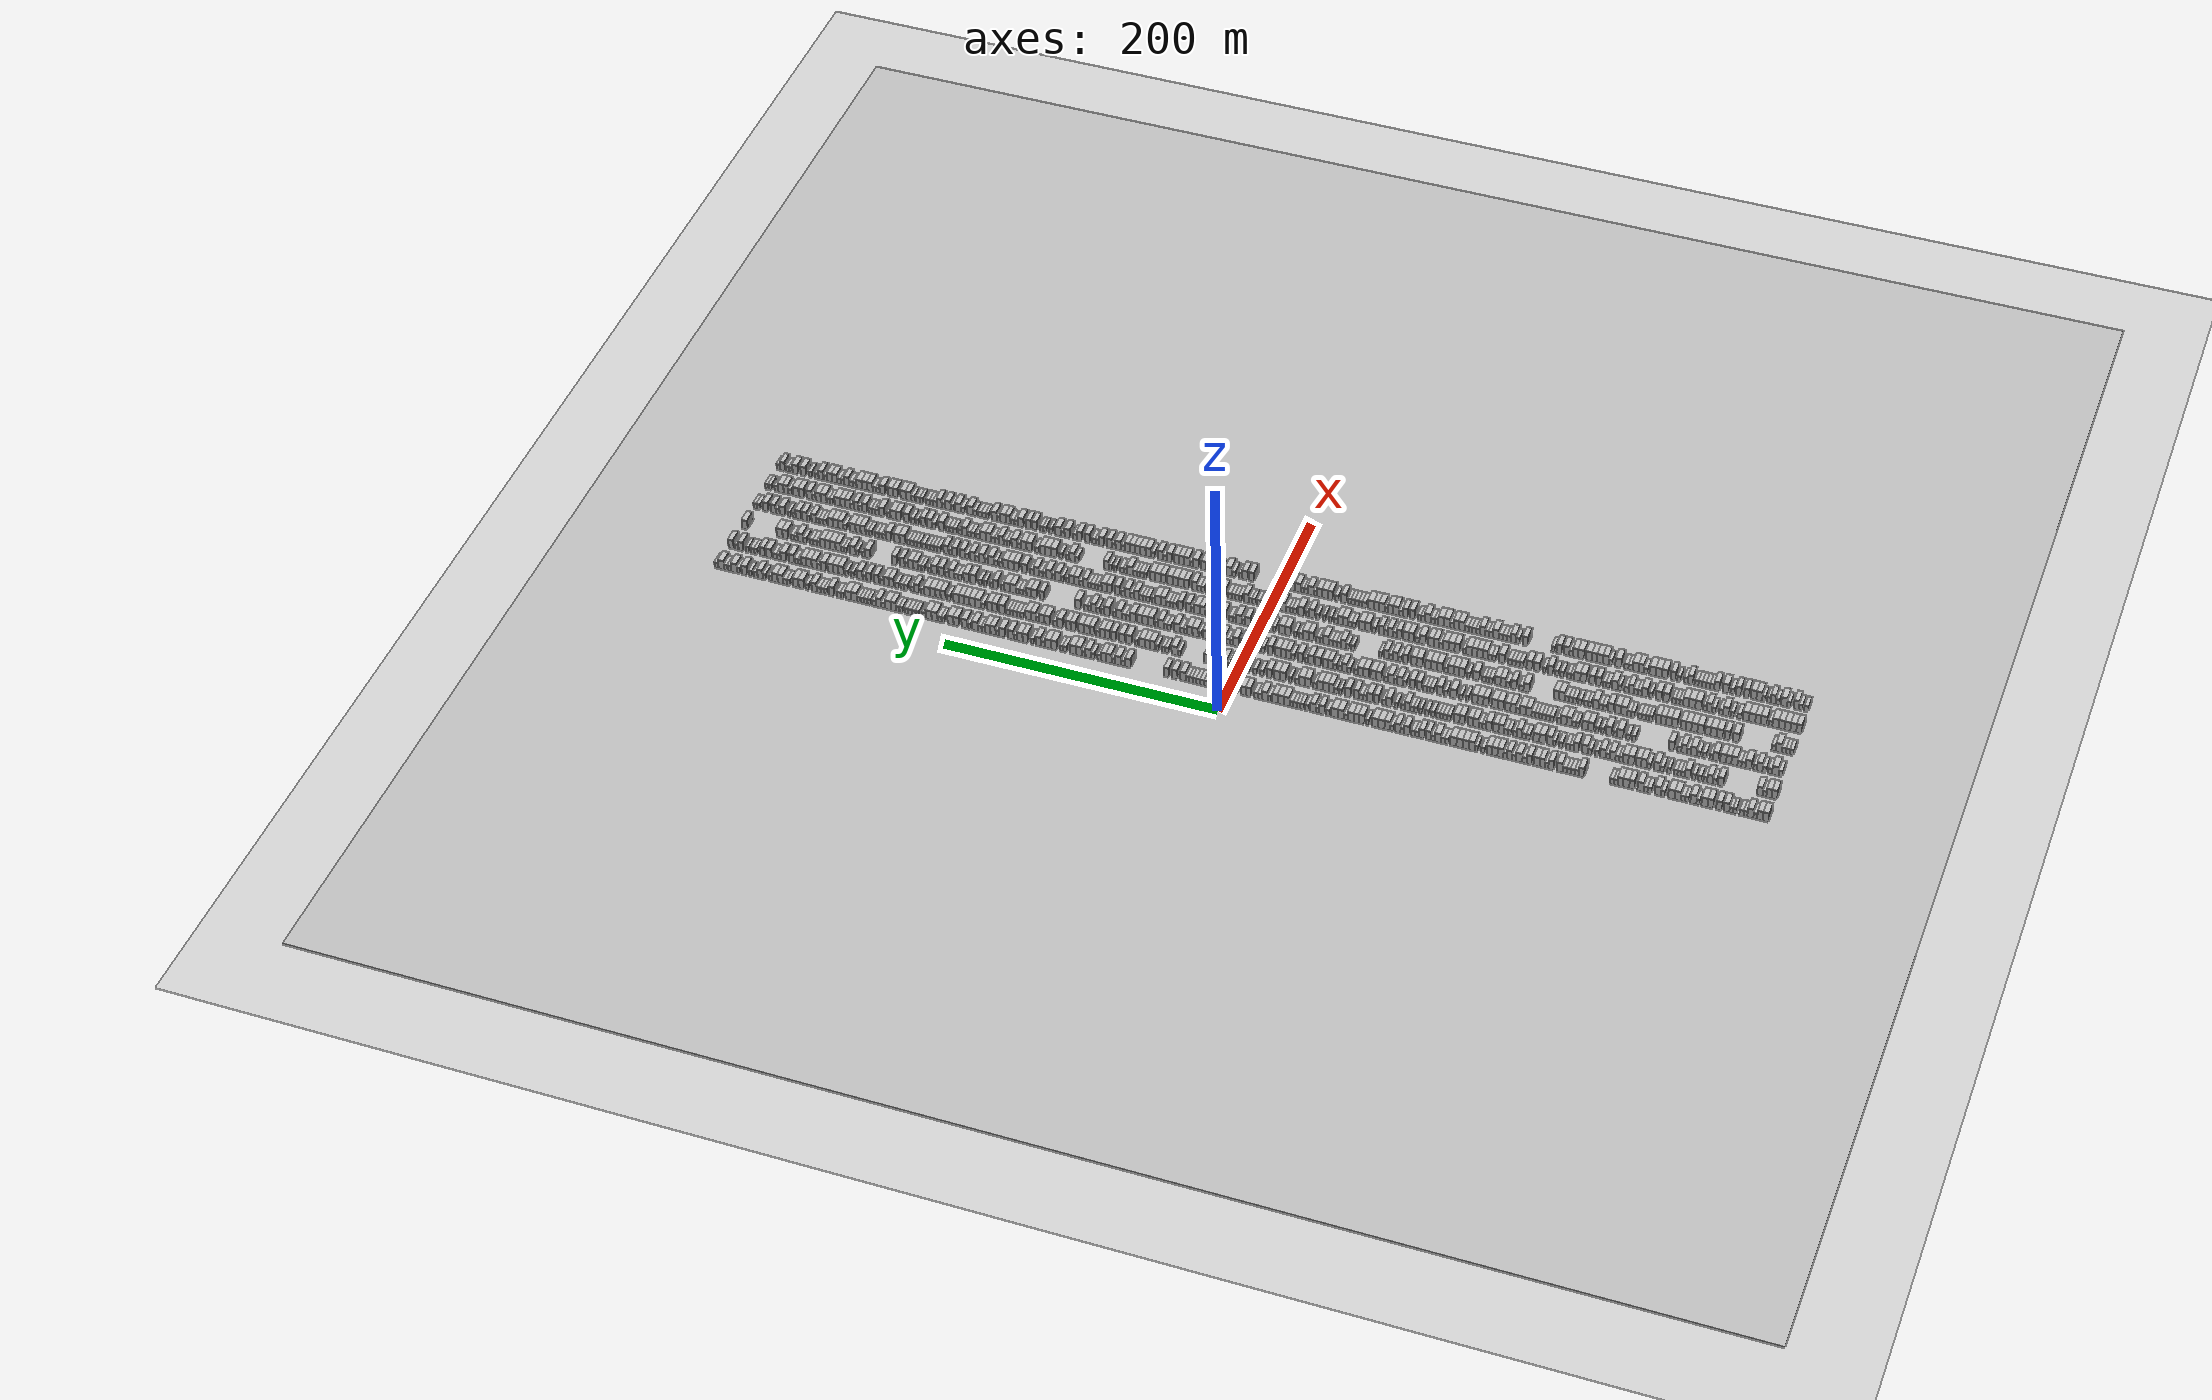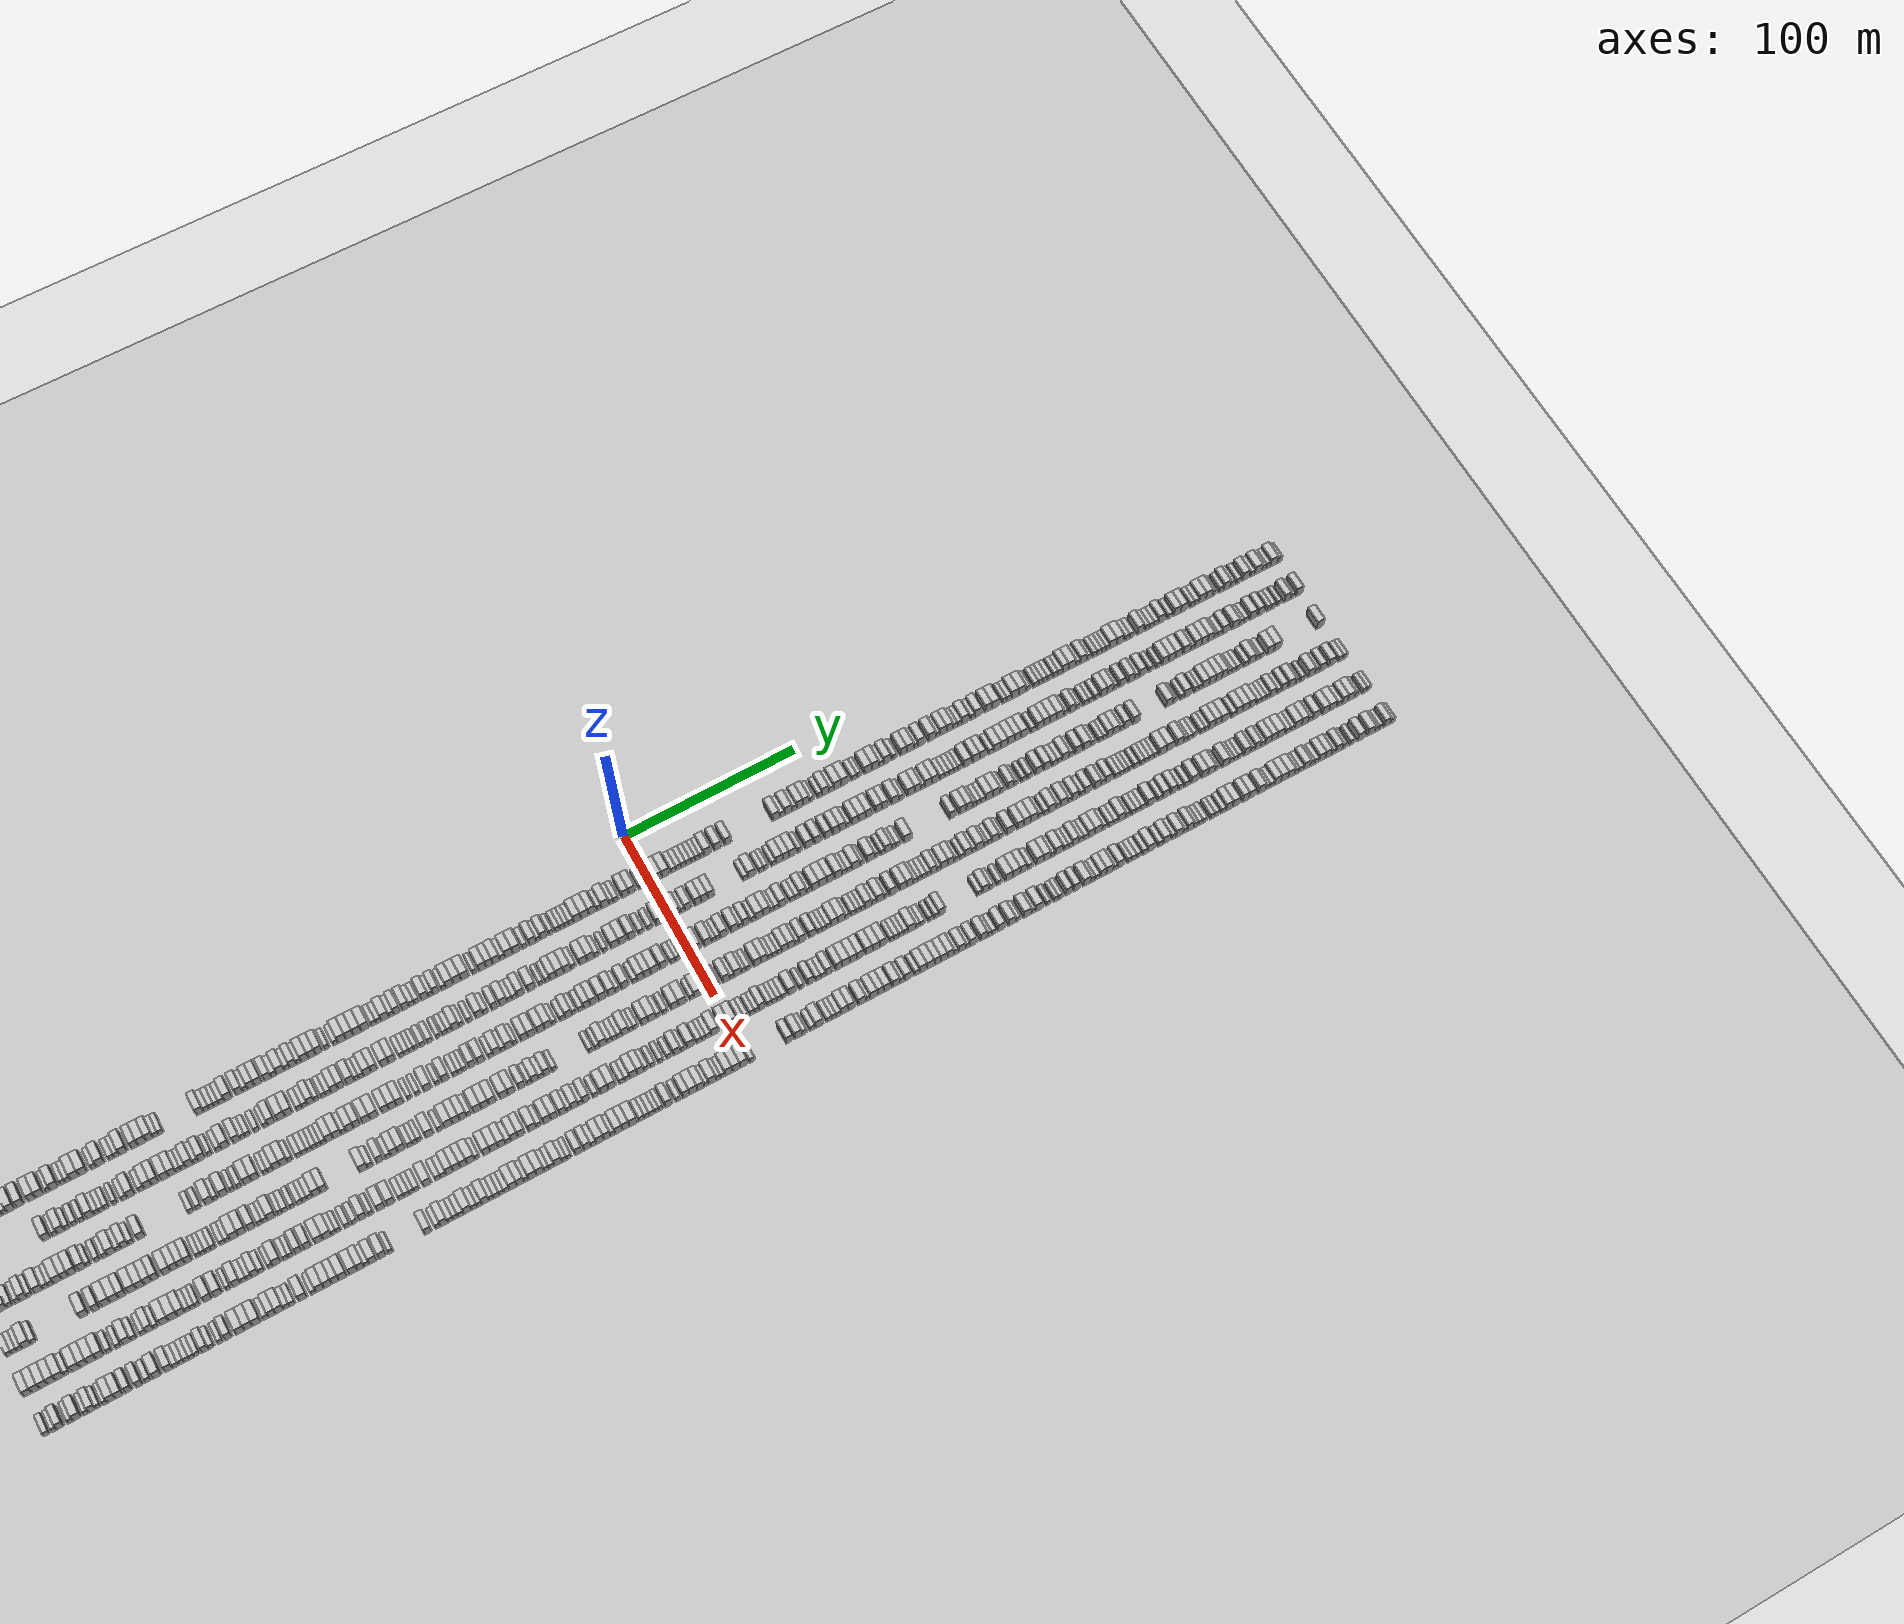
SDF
<?xml version="1.0" encoding="utf-8"?>

<sdf version="1.6">

   <world name="default">

      <gui fullscreen="0">

         <camera name="user_camera">

            <pose>-15 0 4.57585 0 0 0</pose>

            <view_controller>orbit</view_controller>

         </camera>

      </gui>

      <scene>

         <sky>

           <clouds>

             <speed>12</speed>

           </clouds>

         </sky>

         <ambient>0.4 0.4 0.4 1</ambient>

         <background>0.7 0.7 0.7 1</background>

         <shadows>1</shadows>

      </scene>

      <gravity>0 0 -9.8066</gravity>

      <magnetic_field>6e-06 2.3e-05 -4.2e-05</magnetic_field>

      <physics default="0" name="default_physics" type="ode">

         <ode>

            <solver>

               <type>quick</type>

               <iters>10</iters>

               <sor>1.0</sor>

               <use_dynamic_moi_rescaling>0</use_dynamic_moi_rescaling>

            </solver>

            <constraints>

               <cfm>0</cfm>

               <erp>0.2</erp>

               <contact_max_correcting_vel>100</contact_max_correcting_vel>

               <contact_surface_layer>0.001</contact_surface_layer>

            </constraints>

         </ode>

         <max_step_size>0.004</max_step_size>

         <real_time_factor>1</real_time_factor>

         <real_time_update_rate>250</real_time_update_rate>

      </physics>

      <light name="sun" type="directional">

         <cast_shadows>1</cast_shadows>

         <pose>0 0 10 0 0 0</pose>

         <diffuse>0.8 0.8 0.8 1</diffuse>

         <specular>0.2 0.2 0.2 1</specular>

         <attenuation>

            <range>1000</range>

            <constant>0.9</constant>

            <linear>0.01</linear>

            <quadratic>0.001</quadratic>

         </attenuation>

         <direction>-0.5 0.1 -0.9</direction>

      </light>

      <include>

         <name>ground_plane_1</name>

         <uri>model://HANNAS_ground_plane</uri>

         <pose>0 0 0  0 0 0</pose>

      </include>

      <include>

         <name>ground_plane_2</name>

         <uri>model://HANNAS_ground_plane</uri>

         <pose>100 0 0  0 0 0</pose>

      </include>

      <model name="building_1">

         <static>1</static>

         <pose frame="">25.0000 -377.9265 0 0.000000 0.000000 0.000000</pose>

         <link name="link">

            <pose frame="">0 0 4.50 0 0 0</pose>

            <collision name="collision">

               <geometry>

                  <box>

                     <size>10.0000 4.1470 9.0000</size>

                  </box>

               </geometry>

               <max_contacts>10</max_contacts>

               <surface>

                  <contact>

                     <ode/>

                  </contact>

                  <bounce/>

                  <friction>

                     <torsional>

                        <ode/>

                     </torsional>

                     <ode/>

                  </friction>

               </surface>

            </collision>

            <visual name="visual">

               <cast_shadows>0</cast_shadows>

               <geometry>

                  <box>

                     <size>10.0000 4.1470 9.0000</size>

                  </box>

               </geometry>

               <material>

                  <script>

                     <uri>model://HANNAS_wall/materials/scripts</uri>

                     <uri>model://HANNAS_wall/materials/textures</uri>

                     <name>vrc/HANNAS_wall</name>

                  </script>

               </material>

            </visual>

            <self_collide>0</self_collide>

            <enable_wind>0</enable_wind>

            <kinematic>0</kinematic>

         </link>

      </model>

      <model name="building_2">

         <static>1</static>

         <pose frame="">25.0000 -373.9460 0 0.000000 0.000000 0.000000</pose>

         <link name="link">

            <pose frame="">0 0 4.50 0 0 0</pose>

            <collision name="collision">

               <geometry>

                  <box>

                     <size>10.0000 3.8139 9.0000</size>

                  </box>

               </geometry>

               <max_contacts>10</max_contacts>

               <surface>

                  <contact>

                     <ode/>

                  </contact>

                  <bounce/>

                  <friction>

                     <torsional>

                        <ode/>

                     </torsional>

                     <ode/>

                  </friction>

               </surface>

            </collision>

            <visual name="visual">

               <cast_shadows>0</cast_shadows>

               <geometry>

                  <box>

                     <size>10.0000 3.8139 9.0000</size>

                  </box>

               </geometry>

               <material>

                  <script>

                     <uri>model://HANNAS_wall/materials/scripts</uri>

                     <uri>model://HANNAS_wall/materials/textures</uri>

                     <name>vrc/HANNAS_wall</name>

                  </script>

               </material>

            </visual>

            <self_collide>0</self_collide>

            <enable_wind>0</enable_wind>

            <kinematic>0</kinematic>

         </link>

      </model>

      <model name="building_3">

         <static>1</static>

         <pose frame="">25.0000 -370.7243 0 0.000000 0.000000 0.000000</pose>

         <link name="link">

            <pose frame="">0 0 3.00 0 0 0</pose>

            <collision name="collision">

               <geometry>

                  <box>

                     <size>10.0000 2.6295 6.0000</size>

                  </box>

               </geometry>

               <max_contacts>10</max_contacts>

               <surface>

                  <contact>

                     <ode/>

                  </contact>

                  <bounce/>

                  <friction>

                     <torsional>

                        <ode/>

                     </torsional>

                     <ode/>

                  </friction>

               </surface>

            </collision>

            <visual name="visual">

               <cast_shadows>0</cast_shadows>

               <geometry>

                  <box>

                     <size>10.0000 2.6295 6.0000</size>

                  </box>

               </geometry>

               <material>

                  <script>

                     <uri>model://HANNAS_wall/materials/scripts</uri>

                     <uri>model://HANNAS_wall/materials/textures</uri>

                     <name>vrc/HANNAS_wall</name>

                  </script>

               </material>

            </visual>

            <self_collide>0</self_collide>

            <enable_wind>0</enable_wind>

            <kinematic>0</kinematic>

         </link>

      </model>

      <model name="building_4">

         <static>1</static>

         <pose frame="">25.0000 -367.3511 0 0.000000 0.000000 0.000000</pose>

         <link name="link">

            <pose frame="">0 0 4.50 0 0 0</pose>

            <collision name="collision">

               <geometry>

                  <box>

                     <size>10.0000 4.1169 9.0000</size>

                  </box>

               </geometry>

               <max_contacts>10</max_contacts>

               <surface>

                  <contact>

                     <ode/>

                  </contact>

                  <bounce/>

                  <friction>

                     <torsional>

                        <ode/>

                     </torsional>

                     <ode/>

                  </friction>

               </surface>

            </collision>

            <visual name="visual">

               <cast_shadows>0</cast_shadows>

               <geometry>

                  <box>

                     <size>10.0000 4.1169 9.0000</size>

                  </box>

               </geometry>

               <material>

                  <script>

                     <uri>model://HANNAS_wall/materials/scripts</uri>

                     <uri>model://HANNAS_wall/materials/textures</uri>

                     <name>vrc/HANNAS_wall</name>

                  </script>

               </material>

            </visual>

            <self_collide>0</self_collide>

            <enable_wind>0</enable_wind>

            <kinematic>0</kinematic>

         </link>

      </model>

      <model name="building_5">

         <static>1</static>

         <pose frame="">25.0000 -363.9666 0 0.000000 0.000000 0.000000</pose>

         <link name="link">

            <pose frame="">0 0 3.00 0 0 0</pose>

            <collision name="collision">

               <geometry>

                  <box>

                     <size>10.0000 2.6521 6.0000</size>

                  </box>

               </geometry>

               <max_contacts>10</max_contacts>

               <surface>

                  <contact>

                     <ode/>

                  </contact>

                  <bounce/>

                  <friction>

                     <torsional>

                        <ode/>

                     </torsional>

                     <ode/>

                  </friction>

               </surface>

            </collision>

            <visual name="visual">

               <cast_shadows>0</cast_shadows>

               <geometry>

                  <box>

                     <size>10.0000 2.6521 6.0000</size>

                  </box>

               </geometry>

               <material>

                  <script>

                     <uri>model://HANNAS_wall/materials/scripts</uri>

                     <uri>model://HANNAS_wall/materials/textures</uri>

                     <name>vrc/HANNAS_wall</name>

                  </script>

               </material>

            </visual>

            <self_collide>0</self_collide>

            <enable_wind>0</enable_wind>

            <kinematic>0</kinematic>

         </link>

      </model>

      <model name="building_6">

         <static>1</static>

         <pose frame="">25.0000 -361.2505 0 0.000000 0.000000 0.000000</pose>

         <link name="link">

            <pose frame="">0 0 3.00 0 0 0</pose>

            <collision name="collision">

               <geometry>

                  <box>

                     <size>10.0000 2.7803 6.0000</size>

                  </box>

               </geometry>

               <max_contacts>10</max_contacts>

               <surface>

                  <contact>

                     <ode/>

                  </contact>

                  <bounce/>

                  <friction>

                     <torsional>

                        <ode/>

                     </torsional>

                     <ode/>

                  </friction>

               </surface>

            </collision>

            <visual name="visual">

               <cast_shadows>0</cast_shadows>

               <geometry>

                  <box>

                     <size>10.0000 2.7803 6.0000</size>

                  </box>

               </geometry>

               <material>

                  <script>

                     <uri>model://HANNAS_wall/materials/scripts</uri>

                     <uri>model://HANNAS_wall/materials/textures</uri>

                     <name>vrc/HANNAS_wall</name>

                  </script>

               </material>

            </visual>

            <self_collide>0</self_collide>

            <enable_wind>0</enable_wind>

            <kinematic>0</kinematic>

         </link>

      </model>

      <model name="building_7">

         <static>1</static>

         <pose frame="">25.0000 -356.6554 0 0.000000 0.000000 0.000000</pose>

         <link name="link">

            <pose frame="">0 0 3.00 0 0 0</pose>

            <collision name="collision">

               <geometry>

                  <box>

                     <size>10.0000 2.4098 6.0000</size>

                  </box>

               </geometry>

               <max_contacts>10</max_contacts>

               <surface>

                  <contact>

                     <ode/>

                  </contact>

                  <bounce/>

                  <friction>

                     <torsional>

                        <ode/>

                     </torsional>

                     <ode/>

                  </friction>

               </surface>

            </collision>

            <visual name="visual">

               <cast_shadows>0</cast_shadows>

               <geometry>

                  <box>

                     <size>10.0000 2.4098 6.0000</size>

                  </box>

               </geometry>

               <material>

                  <script>

                     <uri>model://HANNAS_wall/materials/scripts</uri>

                     <uri>model://HANNAS_wall/materials/textures</uri>

                     <name>vrc/HANNAS_wall</name>

                  </script>

               </material>

            </visual>

            <self_collide>0</self_collide>

            <enable_wind>0</enable_wind>

            <kinematic>0</kinematic>

         </link>

      </model>

      <model name="building_8">

         <static>1</static>

         <pose frame="">25.0000 -354.2036 0 0.000000 0.000000 0.000000</pose>

         <link name="link">

            <pose frame="">0 0 3.00 0 0 0</pose>

            <collision name="collision">

               <geometry>

                  <box>

                     <size>10.0000 2.4939 6.0000</size>

                  </box>

               </geometry>

               <max_contacts>10</max_contacts>

               <surface>

                  <contact>

                     <ode/>

                  </contact>

                  <bounce/>

                  <friction>

                     <torsional>

                        <ode/>

                     </torsional>

                     <ode/>

                  </friction>

               </surface>

            </collision>

            <visual name="visual">

               <cast_shadows>0</cast_shadows>

               <geometry>

                  <box>

                     <size>10.0000 2.4939 6.0000</size>

                  </box>

               </geometry>

               <material>

                  <script>

                     <uri>model://HANNAS_wall/materials/scripts</uri>

                     <uri>model://HANNAS_wall/materials/textures</uri>

                     <name>vrc/HANNAS_wall</name>

                  </script>

               </material>

            </visual>

            <self_collide>0</self_collide>

            <enable_wind>0</enable_wind>

            <kinematic>0</kinematic>

         </link>

      </model>

      <model name="building_9">

         <static>1</static>

         <pose frame="">25.0000 -350.9690 0 0.000000 0.000000 0.000000</pose>

         <link name="link">

            <pose frame="">0 0 4.50 0 0 0</pose>

            <collision name="collision">

               <geometry>

                  <box>

                     <size>10.0000 3.9753 9.0000</size>

                  </box>

               </geometry>

               <max_contacts>10</max_contacts>

               <surface>

                  <contact>

                     <ode/>

                  </contact>

                  <bounce/>

                  <friction>

                     <torsional>

                        <ode/>

                     </torsional>

                     <ode/>

                  </friction>

               </surface>

            </collision>

            <visual name="visual">

               <cast_shadows>0</cast_shadows>

               <geometry>

                  <box>

                     <size>10.0000 3.9753 9.0000</size>

                  </box>

               </geometry>

               <material>

                  <script>

                     <uri>model://HANNAS_wall/materials/scripts</uri>

                     <uri>model://HANNAS_wall/materials/textures</uri>

                     <name>vrc/HANNAS_wall</name>

                  </script>

               </material>

            </visual>

            <self_collide>0</self_collide>

            <enable_wind>0</enable_wind>

            <kinematic>0</kinematic>

         </link>

      </model>

      <model name="building_10">

         <static>1</static>

         <pose frame="">25.0000 -345.9639 0 0.000000 0.000000 0.000000</pose>

         <link name="link">

            <pose frame="">0 0 4.50 0 0 0</pose>

            <collision name="collision">

               <geometry>

                  <box>

                     <size>10.0000 4.0350 9.0000</size>

                  </box>

               </geometry>

               <max_contacts>10</max_contacts>

               <surface>

                  <contact>

                     <ode/>

                  </contact>

                  <bounce/>

                  <friction>

                     <torsional>

                        <ode/>

                     </torsional>

                     <ode/>

                  </friction>

               </surface>

            </collision>

            <visual name="visual">

               <cast_shadows>0</cast_shadows>

               <geometry>

                  <box>

                     <size>10.0000 4.0350 9.0000</size>

                  </box>

               </geometry>

               <material>

                  <script>

                     <uri>model://HANNAS_wall/materials/scripts</uri>

                     <uri>model://HANNAS_wall/materials/textures</uri>

                     <name>vrc/HANNAS_wall</name>

                  </script>

               </material>

            </visual>

            <self_collide>0</self_collide>

            <enable_wind>0</enable_wind>

            <kinematic>0</kinematic>

         </link>

      </model>

      <model name="building_11">

         <static>1</static>

         <pose frame="">25.0000 -339.9500 0 0.000000 0.000000 0.000000</pose>

         <link name="link">

            <pose frame="">0 0 4.50 0 0 0</pose>

            <collision name="collision">

               <geometry>

                  <box>

                     <size>10.0000 3.9927 9.0000</size>

                  </box>

               </geometry>

               <max_contacts>10</max_contacts>

               <surface>

                  <contact>

                     <ode/>

                  </contact>

                  <bounce/>

                  <friction>

                     <torsional>

                        <ode/>

                     </torsional>

                     <ode/>

                  </friction>

               </surface>

            </collision>

            <visual name="visual">

               <cast_shadows>0</cast_shadows>

               <geometry>

                  <box>

                     <size>10.0000 3.9927 9.0000</size>

                  </box>

               </geometry>

               <material>

                  <script>

                     <uri>model://HANNAS_wall/materials/scripts</uri>

                     <uri>model://HANNAS_wall/materials/textures</uri>

                     <name>vrc/HANNAS_wall</name>

                  </script>

               </material>

            </visual>

            <self_collide>0</self_collide>

            <enable_wind>0</enable_wind>

            <kinematic>0</kinematic>

         </link>

      </model>

      <model name="building_12">

         <static>1</static>

         <pose frame="">25.0000 -335.8329 0 0.000000 0.000000 0.000000</pose>

         <link name="link">

            <pose frame="">0 0 4.50 0 0 0</pose>

            <collision name="collision">

               <geometry>

                  <box>

                     <size>10.0000 4.2416 9.0000</size>

                  </box>

               </geometry>

               <max_contacts>10</max_contacts>

               <surface>

                  <contact>

                     <ode/>

                  </contact>

                  <bounce/>

                  <friction>

                     <torsional>

                        <ode/>

                     </torsional>

                     <ode/>

                  </friction>

               </surface>

            </collision>

            <visual name="visual">

               <cast_shadows>0</cast_shadows>

               <geometry>

                  <box>

                     <size>10.0000 4.2416 9.0000</size>

                  </box>

               </geometry>

               <material>

                  <script>

                     <uri>model://HANNAS_wall/materials/scripts</uri>

                     <uri>model://HANNAS_wall/materials/textures</uri>

                     <name>vrc/HANNAS_wall</name>

                  </script>

               </material>

            </visual>

            <self_collide>0</self_collide>

            <enable_wind>0</enable_wind>

            <kinematic>0</kinematic>

         </link>

      </model>

      <model name="building_13">

         <static>1</static>

         <pose frame="">25.0000 -331.5101 0 0.000000 0.000000 0.000000</pose>

         <link name="link">

            <pose frame="">0 0 3.00 0 0 0</pose>

            <collision name="collision">

               <geometry>

                  <box>

                     <size>10.0000 2.4041 6.0000</size>

                  </box>

               </geometry>

               <max_contacts>10</max_contacts>

               <surface>

                  <contact>

                     <ode/>

                  </contact>

                  <bounce/>

                  <friction>

                     <torsional>

                        <ode/>

                     </torsional>

                     <ode/>

                  </friction>

               </surface>

            </collision>

            <visual name="visual">

               <cast_shadows>0</cast_shadows>

               <geometry>

                  <box>

                     <size>10.0000 2.4041 6.0000</size>

                  </box>

               </geometry>

               <material>

                  <script>

                     <uri>model://HANNAS_wall/materials/scripts</uri>

                     <uri>model://HANNAS_wall/materials/textures</uri>

                     <name>vrc/HANNAS_wall</name>

                  </script>

               </material>

            </visual>

            <self_collide>0</self_collide>

            <enable_wind>0</enable_wind>

            <kinematic>0</kinematic>

         </link>

      </model>

      <model name="building_14">

         <static>1</static>

         <pose frame="">25.0000 -328.2037 0 0.000000 0.000000 0.000000</pose>

         <link name="link">

            <pose frame="">0 0 4.50 0 0 0</pose>

            <collision name="collision">

               <geometry>

                  <box>

                     <size>10.0000 4.2085 9.0000</size>

                  </box>

               </geometry>

               <max_contacts>10</max_contacts>

               <surface>

                  <contact>

                     <ode/>

                  </contact>

                  <bounce/>

                  <friction>

                     <torsional>

                        <ode/>

                     </torsional>

                     <ode/>

                  </friction>

               </surface>

            </collision>

            <visual name="visual">

               <cast_shadows>0</cast_shadows>

               <geometry>

                  <box>

                     <size>10.0000 4.2085 9.0000</size>

                  </box>

               </geometry>

               <material>

                  <script>

                     <uri>model://HANNAS_wall/materials/scripts</uri>

                     <uri>model://HANNAS_wall/materials/textures</uri>

                     <name>vrc/HANNAS_wall</name>

                  </script>

               </material>

            </visual>

            <self_collide>0</self_collide>

            <enable_wind>0</enable_wind>

            <kinematic>0</kinematic>

         </link>

      </model>

      <model name="building_15">

         <static>1</static>

         <pose frame="">25.0000 -323.8361 0 0.000000 0.000000 0.000000</pose>

         <link name="link">

            <pose frame="">0 0 3.00 0 0 0</pose>

            <collision name="collision">

               <geometry>

                  <box>

                     <size>10.0000 2.5268 6.0000</size>

                  </box>

               </geometry>

               <max_contacts>10</max_contacts>

               <surface>

                  <contact>

                     <ode/>

                  </contact>

                  <bounce/>

                  <friction>

                     <torsional>

                        <ode/>

                     </torsional>

                     <ode/>

                  </friction>

               </surface>

            </collision>

            <visual name="visual">

               <cast_shadows>0</cast_shadows>

               <geometry>

                  <box>

                     <size>10.0000 2.5268 6.0000</size>

                  </box>

               </geometry>

               <material>

                  <script>

                     <uri>model://HANNAS_wall/materials/scripts</uri>

                     <uri>model://HANNAS_wall/materials/textures</uri>

                     <name>vrc/HANNAS_wall</name>

                  </script>

               </material>

            </visual>

            <self_collide>0</self_collide>

            <enable_wind>0</enable_wind>

            <kinematic>0</kinematic>

         </link>

      </model>

      <model name="building_16">

         <static>1</static>

         <pose frame="">25.0000 -321.1197 0 0.000000 0.000000 0.000000</pose>

         <link name="link">

            <pose frame="">0 0 3.00 0 0 0</pose>

            <collision name="collision">

               <geometry>

                  <box>

                     <size>10.0000 2.9060 6.0000</size>

                  </box>

               </geometry>

               <max_contacts>10</max_contacts>

               <surface>

                  <contact>

                     <ode/>

                  </contact>

                  <bounce/>

                  <friction>

                     <torsional>

                        <ode/>

                     </torsional>

                     <ode/>

                  </friction>

               </surface>

            </collision>

            <visual name="visual">

               <cast_shadows>0</cast_shadows>

               <geometry>

                  <box>

                     <size>10.0000 2.9060 6.0000</size>

                  </box>

               </geometry>

               <material>

                  <script>

                     <uri>model://HANNAS_wall/materials/scripts</uri>

                     <uri>model://HANNAS_wall/materials/textures</uri>

                     <name>vrc/HANNAS_wall</name>

                  </script>

               </material>

            </visual>

            <self_collide>0</self_collide>

            <enable_wind>0</enable_wind>

            <kinematic>0</kinematic>

         </link>

      </model>

      <model name="building_17">

         <static>1</static>

         <pose frame="">25.0000 -317.4488 0 0.000000 0.000000 0.000000</pose>

         <link name="link">

            <pose frame="">0 0 4.50 0 0 0</pose>

            <collision name="collision">

               <geometry>

                  <box>

                     <size>10.0000 4.4359 9.0000</size>

                  </box>

               </geometry>

               <max_contacts>10</max_contacts>

               <surface>

                  <contact>

                     <ode/>

                  </contact>

                  <bounce/>

                  <friction>

                     <torsional>

                        <ode/>

                     </torsional>

                     <ode/>

                  </friction>

               </surface>

            </collision>

            <visual name="visual">

               <cast_shadows>0</cast_shadows>

               <geometry>

                  <box>

                     <size>10.0000 4.4359 9.0000</size>

                  </box>

               </geometry>

               <material>

                  <script>

                     <uri>model://HANNAS_wall/materials/scripts</uri>

                     <uri>model://HANNAS_wall/materials/textures</uri>

                     <name>vrc/HANNAS_wall</name>

                  </script>

               </material>

            </visual>

            <self_collide>0</self_collide>

            <enable_wind>0</enable_wind>

            <kinematic>0</kinematic>

         </link>

      </model>

      <model name="building_18">

         <static>1</static>

         <pose frame="">25.0000 -313.0124 0 0.000000 0.000000 0.000000</pose>

         <link name="link">

            <pose frame="">0 0 4.50 0 0 0</pose>

            <collision name="collision">

               <geometry>

                  <box>

                     <size>10.0000 4.4369 9.0000</size>

                  </box>

               </geometry>

               <max_contacts>10</max_contacts>

               <surface>

                  <contact>

                     <ode/>

                  </contact>

                  <bounce/>

                  <friction>

                     <torsional>

                        <ode/>

                     </torsional>

                     <ode/>

                  </friction>

               </surface>

            </collision>

            <visual name="visual">

               <cast_shadows>0</cast_shadows>

               <geometry>

                  <box>

                     <size>10.0000 4.4369 9.0000</size>

                  </box>

               </geometry>

               <material>

                  <script>

                     <uri>model://HANNAS_wall/materials/scripts</uri>

                     <uri>model://HANNAS_wall/materials/textures</uri>

                     <name>vrc/HANNAS_wall</name>

                  </script>

               </material>

            </visual>

            <self_collide>0</self_collide>

            <enable_wind>0</enable_wind>

            <kinematic>0</kinematic>

         </link>

      </model>

      <model name="building_19">

         <static>1</static>

         <pose frame="">25.0000 -307.3761 0 0.000000 0.000000 0.000000</pose>

         <link name="link">

            <pose frame="">0 0 3.00 0 0 0</pose>

            <collision name="collision">

               <geometry>

                  <box>

                     <size>10.0000 2.8357 6.0000</size>

                  </box>

               </geometry>

               <max_contacts>10</max_contacts>

               <surface>

                  <contact>

                     <ode/>

                  </contact>

                  <bounce/>

                  <friction>

                     <torsional>

                        <ode/>

                     </torsional>

                     <ode/>

                  </friction>

               </surface>

            </collision>

            <visual name="visual">

               <cast_shadows>0</cast_shadows>

               <geometry>

                  <box>

                     <size>10.0000 2.8357 6.0000</size>

                  </box>

               </geometry>

               <material>

                  <script>

                     <uri>model://HANNAS_wall/materials/scripts</uri>

                     <uri>model://HANNAS_wall/materials/textures</uri>

                     <name>vrc/HANNAS_wall</name>

                  </script>

               </material>

            </visual>

            <self_collide>0</self_collide>

            <enable_wind>0</enable_wind>

            <kinematic>0</kinematic>

         </link>

      </model>

      <model name="building_20">

         <static>1</static>

         <pose frame="">25.0000 -303.7380 0 0.000000 0.000000 0.000000</pose>

         <link name="link">

            <pose frame="">0 0 4.50 0 0 0</pose>

            <collision name="collision">

               <geometry>

                  <box>

                     <size>10.0000 4.4406 9.0000</size>

                  </box>

               </geometry>

               <max_contacts>10</max_contacts>

               <surface>

                  <contact>

                     <ode/>

                  </contact>

                  <bounce/>

                  <friction>

                     <torsional>

                        <ode/>

                     </torsional>

                     <ode/>

                  </friction>

               </surface>

            </collision>

            <visual name="visual">

               <cast_shadows>0</cast_shadows>

               <geometry>

                  <box>

                     <size>10.0000 4.4406 9.0000</size>

                  </box>

               </geometry>

               <material>

                  <script>

                     <uri>model://HANNAS_wall/materials/scripts</uri>

                     <uri>model://HANNAS_wall/materials/textures</uri>

                     <name>vrc/HANNAS_wall</name>

                  </script>

               </material>

            </visual>

            <self_collide>0</self_collide>

            <enable_wind>0</enable_wind>

            <kinematic>0</kinematic>

         </link>

      </model>

      <model name="building_21">

         <static>1</static>

         <pose frame="">25.0000 -298.0272 0 0.000000 0.000000 0.000000</pose>

         <link name="link">

            <pose frame="">0 0 3.00 0 0 0</pose>

            <collision name="collision">

               <geometry>

                  <box>

                     <size>10.0000 2.9811 6.0000</size>

                  </box>

               </geometry>

               <max_contacts>10</max_contacts>

               <surface>

                  <contact>

                     <ode/>

                  </contact>

                  <bounce/>

                  <friction>

                     <torsional>

                        <ode/>

                     </torsional>

                     <ode/>

                  </friction>

               </surface>

            </collision>

            <visual name="visual">

               <cast_shadows>0</cast_shadows>

               <geometry>

                  <box>

                     <size>10.0000 2.9811 6.0000</size>

                  </box>

               </geometry>

               <material>

                  <script>

                     <uri>model://HANNAS_wall/materials/scripts</uri>

                     <uri>model://HANNAS_wall/materials/textures</uri>

                     <name>vrc/HANNAS_wall</name>

                  </script>

               </material>

            </visual>

            <self_collide>0</self_collide>

            <enable_wind>0</enable_wind>

            <kinematic>0</kinematic>

         </link>

      </model>

      <model name="building_22">

         <static>1</static>

         <pose frame="">25.0000 -295.1833 0 0.000000 0.000000 0.000000</pose>

         <link name="link">

            <pose frame="">0 0 3.00 0 0 0</pose>

            <collision name="collision">

               <geometry>

                  <box>

                     <size>10.0000 2.7067 6.0000</size>

                  </box>

               </geometry>

               <max_contacts>10</max_contacts>

               <surface>

                  <contact>

                     <ode/>

                  </contact>

                  <bounce/>

                  <friction>

                     <torsional>

                        <ode/>

                     </torsional>

                     <ode/>

                  </friction>

               </surface>

            </collision>

            <visual name="visual">

               <cast_shadows>0</cast_shadows>

               <geometry>

                  <box>

                     <size>10.0000 2.7067 6.0000</size>

                  </box>

               </geometry>

               <material>

                  <script>

                     <uri>model://HANNAS_wall/materials/scripts</uri>

                     <uri>model://HANNAS_wall/materials/textures</uri>

                     <name>vrc/HANNAS_wall</name>

                  </script>

               </material>

            </visual>

            <self_collide>0</self_collide>

            <enable_wind>0</enable_wind>

            <kinematic>0</kinematic>

         </link>

      </model>

      <model name="building_23">

         <static>1</static>

         <pose frame="">25.0000 -291.6937 0 0.000000 0.000000 0.000000</pose>

         <link name="link">

            <pose frame="">0 0 4.50 0 0 0</pose>

            <collision name="collision">

               <geometry>

                  <box>

                     <size>10.0000 4.2725 9.0000</size>

                  </box>

               </geometry>

               <max_contacts>10</max_contacts>

               <surface>

                  <contact>

                     <ode/>

                  </contact>

                  <bounce/>

                  <friction>

                     <torsional>

                        <ode/>

                     </torsional>

                     <ode/>

                  </friction>

               </surface>

            </collision>

            <visual name="visual">

               <cast_shadows>0</cast_shadows>

               <geometry>

                  <box>

                     <size>10.0000 4.2725 9.0000</size>

                  </box>

               </geometry>

               <material>

                  <script>

                     <uri>model://HANNAS_wall/materials/scripts</uri>

                     <uri>model://HANNAS_wall/materials/textures</uri>

                     <name>vrc/HANNAS_wall</name>

                  </script>

               </material>

            </visual>

            <self_collide>0</self_collide>

            <enable_wind>0</enable_wind>

            <kinematic>0</kinematic>

         </link>

      </model>

      <model name="building_24">

         <static>1</static>

         <pose frame="">25.0000 -285.7296 0 0.000000 0.000000 0.000000</pose>

         <link name="link">

            <pose frame="">0 0 4.50 0 0 0</pose>

            <collision name="collision">

               <geometry>

                  <box>

                     <size>10.0000 3.6557 9.0000</size>

                  </box>

               </geometry>

               <max_contacts>10</max_contacts>

               <surface>

                  <contact>

                     <ode/>

                  </contact>

                  <bounce/>

                  <friction>

                     <torsional>

                        <ode/>

                     </torsional>

                     <ode/>

                  </friction>

               </surface>

            </collision>

            <visual name="visual">

               <cast_shadows>0</cast_shadows>

               <geometry>

                  <box>

                     <size>10.0000 3.6557 9.0000</size>

                  </box>

               </geometry>

               <material>

                  <script>

                     <uri>model://HANNAS_wall/materials/scripts</uri>

                     <uri>model://HANNAS_wall/materials/textures</uri>

                     <name>vrc/HANNAS_wall</name>

                  </script>

               </material>

            </visual>

            <self_collide>0</self_collide>

            <enable_wind>0</enable_wind>

            <kinematic>0</kinematic>

         </link>

      </model>

      <model name="building_25">

         <static>1</static>

         <pose frame="">25.0000 -281.7193 0 0.000000 0.000000 0.000000</pose>

         <link name="link">

            <pose frame="">0 0 4.50 0 0 0</pose>

            <collision name="collision">

               <geometry>

                  <box>

                     <size>10.0000 4.3651 9.0000</size>

                  </box>

               </geometry>

               <max_contacts>10</max_contacts>

               <surface>

                  <contact>

                     <ode/>

                  </contact>

                  <bounce/>

                  <friction>

                     <torsional>

                        <ode/>

                     </torsional>

                     <ode/>

                  </friction>

               </surface>

            </collision>

            <visual name="visual">

               <cast_shadows>0</cast_shadows>

               <geometry>

                  <box>

                     <size>10.0000 4.3651 9.0000</size>

                  </box>

               </geometry>

               <material>

                  <script>

                     <uri>model://HANNAS_wall/materials/scripts</uri>

                     <uri>model://HANNAS_wall/materials/textures</uri>

                     <name>vrc/HANNAS_wall</name>

                  </script>

               </material>

            </visual>

            <self_collide>0</self_collide>

            <enable_wind>0</enable_wind>

            <kinematic>0</kinematic>

         </link>

      </model>

      <model name="building_26">

         <static>1</static>

         <pose frame="">25.0000 -277.6539 0 0.000000 0.000000 0.000000</pose>

         <link name="link">

            <pose frame="">0 0 4.50 0 0 0</pose>

            <collision name="collision">

               <geometry>

                  <box>

                     <size>10.0000 3.7657 9.0000</size>

                  </box>

               </geometry>

               <max_contacts>10</max_contacts>

               <surface>

                  <contact>

                     <ode/>

                  </contact>

                  <bounce/>

                  <friction>

                     <torsional>

                        <ode/>

                     </torsional>

                     <ode/>

                  </friction>

               </surface>

            </collision>

            <visual name="visual">

               <cast_shadows>0</cast_shadows>

               <geometry>

                  <box>

                     <size>10.0000 3.7657 9.0000</size>

                  </box>

               </geometry>

               <material>

                  <script>

                     <uri>model://HANNAS_wall/materials/scripts</uri>

                     <uri>model://HANNAS_wall/materials/textures</uri>

                     <name>vrc/HANNAS_wall</name>

                  </script>

               </material>

            </visual>

            <self_collide>0</self_collide>

            <enable_wind>0</enable_wind>

            <kinematic>0</kinematic>

         </link>

      </model>

      <model name="building_27">

         <static>1</static>

         <pose frame="">25.0000 -274.4443 0 0.000000 0.000000 0.000000</pose>

         <link name="link">

            <pose frame="">0 0 3.00 0 0 0</pose>

            <collision name="collision">

               <geometry>

                  <box>

                     <size>10.0000 2.6534 6.0000</size>

                  </box>

               </geometry>

               <max_contacts>10</max_contacts>

               <surface>

                  <contact>

                     <ode/>

                  </contact>

                  <bounce/>

                  <friction>

                     <torsional>

                        <ode/>

                     </torsional>

                     <ode/>

                  </friction>

               </surface>

            </collision>

            <visual name="visual">

               <cast_shadows>0</cast_shadows>

               <geometry>

                  <box>

                     <size>10.0000 2.6534 6.0000</size>

                  </box>

               </geometry>

               <material>

                  <script>

                     <uri>model://HANNAS_wall/materials/scripts</uri>

                     <uri>model://HANNAS_wall/materials/textures</uri>

                     <name>vrc/HANNAS_wall</name>

                  </script>

               </material>

            </visual>

            <self_collide>0</self_collide>

            <enable_wind>0</enable_wind>

            <kinematic>0</kinematic>

         </link>

      </model>

      <model name="building_28">

         <static>1</static>

         <pose frame="">25.0000 -271.7349 0 0.000000 0.000000 0.000000</pose>

         <link name="link">

            <pose frame="">0 0 3.00 0 0 0</pose>

            <collision name="collision">

               <geometry>

                  <box>

                     <size>10.0000 2.7654 6.0000</size>

                  </box>

               </geometry>

               <max_contacts>10</max_contacts>

               <surface>

                  <contact>

                     <ode/>

                  </contact>

                  <bounce/>

                  <friction>

                     <torsional>

                        <ode/>

                     </torsional>

                     <ode/>

                  </friction>

               </surface>

            </collision>

            <visual name="visual">

               <cast_shadows>0</cast_shadows>

               <geometry>

                  <box>

                     <size>10.0000 2.7654 6.0000</size>

                  </box>

               </geometry>

               <material>

                  <script>

                     <uri>model://HANNAS_wall/materials/scripts</uri>

                     <uri>model://HANNAS_wall/materials/textures</uri>

                     <name>vrc/HANNAS_wall</name>

                  </script>

               </material>

            </visual>

            <self_collide>0</self_collide>

            <enable_wind>0</enable_wind>

            <kinematic>0</kinematic>

         </link>

      </model>

      <model name="building_29">

         <static>1</static>

         <pose frame="">25.0000 -250.6483 0 0.000000 0.000000 0.000000</pose>

         <link name="link">

            <pose frame="">0 0 4.50 0 0 0</pose>

            <collision name="collision">

               <geometry>

                  <box>

                     <size>10.0000 3.8026 9.0000</size>

                  </box>

               </geometry>

               <max_contacts>10</max_contacts>

               <surface>

                  <contact>

                     <ode/>

                  </contact>

                  <bounce/>

                  <friction>

                     <torsional>

                        <ode/>

                     </torsional>

                     <ode/>

                  </friction>

               </surface>

            </collision>

            <visual name="visual">

               <cast_shadows>0</cast_shadows>

               <geometry>

                  <box>

                     <size>10.0000 3.8026 9.0000</size>

                  </box>

               </geometry>

               <material>

                  <script>

                     <uri>model://HANNAS_wall/materials/scripts</uri>

                     <uri>model://HANNAS_wall/materials/textures</uri>

                     <name>vrc/HANNAS_wall</name>

                  </script>

               </material>

            </visual>

            <self_collide>0</self_collide>

            <enable_wind>0</enable_wind>

            <kinematic>0</kinematic>

         </link>

      </model>

      <model name="building_30">

         <static>1</static>

         <pose frame="">25.0000 -247.3433 0 0.000000 0.000000 0.000000</pose>

         <link name="link">

            <pose frame="">0 0 3.00 0 0 0</pose>

            <collision name="collision">

               <geometry>

                  <box>

                     <size>10.0000 2.8074 6.0000</size>

                  </box>

               </geometry>

               <max_contacts>10</max_contacts>

               <surface>

                  <contact>

                     <ode/>

                  </contact>

                  <bounce/>

                  <friction>

                     <torsional>

                        <ode/>

                     </torsional>

                     <ode/>

                  </friction>

               </surface>

            </collision>

            <visual name="visual">

               <cast_shadows>0</cast_shadows>

               <geometry>

                  <box>

                     <size>10.0000 2.8074 6.0000</size>

                  </box>

               </geometry>

               <material>

                  <script>

                     <uri>model://HANNAS_wall/materials/scripts</uri>

                     <uri>model://HANNAS_wall/materials/textures</uri>

                     <name>vrc/HANNAS_wall</name>

                  </script>

               </material>

            </visual>

            <self_collide>0</self_collide>

            <enable_wind>0</enable_wind>

            <kinematic>0</kinematic>

         </link>

      </model>

      <model name="building_31">

         <static>1</static>

         <pose frame="">25.0000 -244.5108 0 0.000000 0.000000 0.000000</pose>

         <link name="link">

            <pose frame="">0 0 3.00 0 0 0</pose>

            <collision name="collision">

               <geometry>

                  <box>

                     <size>10.0000 2.8575 6.0000</size>

                  </box>

               </geometry>

               <max_contacts>10</max_contacts>

               <surface>

                  <contact>

                     <ode/>

                  </contact>

                  <bounce/>

                  <friction>

                     <torsional>

                        <ode/>

                     </torsional>

                     <ode/>

                  </friction>

               </surface>

            </collision>

            <visual name="visual">

               <cast_shadows>0</cast_shadows>

               <geometry>

                  <box>

                     <size>10.0000 2.8575 6.0000</size>

                  </box>

               </geometry>

               <material>

                  <script>

                     <uri>model://HANNAS_wall/materials/scripts</uri>

                     <uri>model://HANNAS_wall/materials/textures</uri>

                     <name>vrc/HANNAS_wall</name>

                  </script>

               </material>

            </visual>

            <self_collide>0</self_collide>

            <enable_wind>0</enable_wind>

            <kinematic>0</kinematic>

         </link>

      </model>

      <model name="building_32">

         <static>1</static>

         <pose frame="">25.0000 -241.8148 0 0.000000 0.000000 0.000000</pose>

         <link name="link">

            <pose frame="">0 0 3.00 0 0 0</pose>

            <collision name="collision">

               <geometry>

                  <box>

                     <size>10.0000 2.5343 6.0000</size>

                  </box>

               </geometry>

               <max_contacts>10</max_contacts>

               <surface>

                  <contact>

                     <ode/>

                  </contact>

                  <bounce/>

                  <friction>

                     <torsional>

                        <ode/>

                     </torsional>

                     <ode/>

                  </friction>

               </surface>

            </collision>

            <visual name="visual">

               <cast_shadows>0</cast_shadows>

               <geometry>

                  <box>

                     <size>10.0000 2.5343 6.0000</size>

                  </box>

               </geometry>

               <material>

                  <script>

                     <uri>model://HANNAS_wall/materials/scripts</uri>

                     <uri>model://HANNAS_wall/materials/textures</uri>

                     <name>vrc/HANNAS_wall</name>

                  </script>

               </material>

            </visual>

            <self_collide>0</self_collide>

            <enable_wind>0</enable_wind>

            <kinematic>0</kinematic>

         </link>

      </model>

      <model name="building_33">

         <static>1</static>

         <pose frame="">25.0000 -239.0710 0 0.000000 0.000000 0.000000</pose>

         <link name="link">

            <pose frame="">0 0 3.00 0 0 0</pose>

            <collision name="collision">

               <geometry>

                  <box>

                     <size>10.0000 2.9532 6.0000</size>

                  </box>

               </geometry>

               <max_contacts>10</max_contacts>

               <surface>

                  <contact>

                     <ode/>

                  </contact>

                  <bounce/>

                  <friction>

                     <torsional>

                        <ode/>

                     </torsional>

                     <ode/>

                  </friction>

               </surface>

            </collision>

            <visual name="visual">

               <cast_shadows>0</cast_shadows>

               <geometry>

                  <box>

                     <size>10.0000 2.9532 6.0000</size>

                  </box>

               </geometry>

               <material>

                  <script>

                     <uri>model://HANNAS_wall/materials/scripts</uri>

                     <uri>model://HANNAS_wall/materials/textures</uri>

                     <name>vrc/HANNAS_wall</name>

                  </script>

               </material>

            </visual>

            <self_collide>0</self_collide>

            <enable_wind>0</enable_wind>

            <kinematic>0</kinematic>

         </link>

      </model>

      <model name="building_34">

         <static>1</static>

         <pose frame="">25.0000 -235.5014 0 0.000000 0.000000 0.000000</pose>

         <link name="link">

            <pose frame="">0 0 4.50 0 0 0</pose>

            <collision name="collision">

               <geometry>

                  <box>

                     <size>10.0000 4.1860 9.0000</size>

                  </box>

               </geometry>

               <max_contacts>10</max_contacts>

               <surface>

                  <contact>

                     <ode/>

                  </contact>

                  <bounce/>

                  <friction>

                     <torsional>

                        <ode/>

                     </torsional>

                     <ode/>

                  </friction>

               </surface>

            </collision>

            <visual name="visual">

               <cast_shadows>0</cast_shadows>

               <geometry>

                  <box>

                     <size>10.0000 4.1860 9.0000</size>

                  </box>

               </geometry>

               <material>

                  <script>

                     <uri>model://HANNAS_wall/materials/scripts</uri>

                     <uri>model://HANNAS_wall/materials/textures</uri>

                     <name>vrc/HANNAS_wall</name>

                  </script>

               </material>

            </visual>

            <self_collide>0</self_collide>

            <enable_wind>0</enable_wind>

            <kinematic>0</kinematic>

         </link>

      </model>

      <model name="building_35">

         <static>1</static>

         <pose frame="">25.0000 -229.4936 0 0.000000 0.000000 0.000000</pose>

         <link name="link">

            <pose frame="">0 0 4.50 0 0 0</pose>

            <collision name="collision">

               <geometry>

                  <box>

                     <size>10.0000 3.8298 9.0000</size>

                  </box>

               </geometry>

               <max_contacts>10</max_contacts>

               <surface>

                  <contact>

                     <ode/>

                  </contact>

                  <bounce/>

                  <friction>

                     <torsional>

                        <ode/>

                     </torsional>

                     <ode/>

                  </friction>

               </surface>

            </collision>

            <visual name="visual">

               <cast_shadows>0</cast_shadows>

               <geometry>

                  <box>

                     <size>10.0000 3.8298 9.0000</size>

                  </box>

               </geometry>

               <material>

                  <script>

                     <uri>model://HANNAS_wall/materials/scripts</uri>

                     <uri>model://HANNAS_wall/materials/textures</uri>

                     <name>vrc/HANNAS_wall</name>

                  </script>

               </material>

            </visual>

            <self_collide>0</self_collide>

            <enable_wind>0</enable_wind>

            <kinematic>0</kinematic>

         </link>

      </model>

      <model name="building_36">

         <static>1</static>

         <pose frame="">25.0000 -226.3007 0 0.000000 0.000000 0.000000</pose>

         <link name="link">

            <pose frame="">0 0 3.00 0 0 0</pose>

            <collision name="collision">

               <geometry>

                  <box>

                     <size>10.0000 2.5559 6.0000</size>

                  </box>

               </geometry>

               <max_contacts>10</max_contacts>

               <surface>

                  <contact>

                     <ode/>

                  </contact>

                  <bounce/>

                  <friction>

                     <torsional>

                        <ode/>

                     </torsional>

                     <ode/>

                  </friction>

               </surface>

            </collision>

            <visual name="visual">

               <cast_shadows>0</cast_shadows>

               <geometry>

                  <box>

                     <size>10.0000 2.5559 6.0000</size>

                  </box>

               </geometry>

               <material>

                  <script>

                     <uri>model://HANNAS_wall/materials/scripts</uri>

                     <uri>model://HANNAS_wall/materials/textures</uri>

                     <name>vrc/HANNAS_wall</name>

                  </script>

               </material>

            </visual>

            <self_collide>0</self_collide>

            <enable_wind>0</enable_wind>

            <kinematic>0</kinematic>

         </link>

      </model>

      <model name="building_37">

         <static>1</static>

         <pose frame="">25.0000 -223.1978 0 0.000000 0.000000 0.000000</pose>

         <link name="link">

            <pose frame="">0 0 4.50 0 0 0</pose>

            <collision name="collision">

               <geometry>

                  <box>

                     <size>10.0000 3.6500 9.0000</size>

                  </box>

               </geometry>

               <max_contacts>10</max_contacts>

               <surface>

                  <contact>

                     <ode/>

                  </contact>

                  <bounce/>

                  <friction>

                     <torsional>

                        <ode/>

                     </torsional>

                     <ode/>

                  </friction>

               </surface>

            </collision>

            <visual name="visual">

               <cast_shadows>0</cast_shadows>

               <geometry>

                  <box>

                     <size>10.0000 3.6500 9.0000</size>

                  </box>

               </geometry>

               <material>

                  <script>

                     <uri>model://HANNAS_wall/materials/scripts</uri>

                     <uri>model://HANNAS_wall/materials/textures</uri>

                     <name>vrc/HANNAS_wall</name>

                  </script>

               </material>

            </visual>

            <self_collide>0</self_collide>

            <enable_wind>0</enable_wind>

            <kinematic>0</kinematic>

         </link>

      </model>

      <model name="building_38">

         <static>1</static>

         <pose frame="">25.0000 -219.2709 0 0.000000 0.000000 0.000000</pose>

         <link name="link">

            <pose frame="">0 0 4.50 0 0 0</pose>

            <collision name="collision">

               <geometry>

                  <box>

                     <size>10.0000 4.2037 9.0000</size>

                  </box>

               </geometry>

               <max_contacts>10</max_contacts>

               <surface>

                  <contact>

                     <ode/>

                  </contact>

                  <bounce/>

                  <friction>

                     <torsional>

                        <ode/>

                     </torsional>

                     <ode/>

                  </friction>

               </surface>

            </collision>

            <visual name="visual">

               <cast_shadows>0</cast_shadows>

               <geometry>

                  <box>

                     <size>10.0000 4.2037 9.0000</size>

                  </box>

               </geometry>

               <material>

                  <script>

                     <uri>model://HANNAS_wall/materials/scripts</uri>

                     <uri>model://HANNAS_wall/materials/textures</uri>

                     <name>vrc/HANNAS_wall</name>

                  </script>

               </material>

            </visual>

            <self_collide>0</self_collide>

            <enable_wind>0</enable_wind>

            <kinematic>0</kinematic>

         </link>

      </model>

      <model name="building_39">

         <static>1</static>

         <pose frame="">25.0000 -214.2407 0 0.000000 0.000000 0.000000</pose>

         <link name="link">

            <pose frame="">0 0 4.50 0 0 0</pose>

            <collision name="collision">

               <geometry>

                  <box>

                     <size>10.0000 3.8568 9.0000</size>

                  </box>

               </geometry>

               <max_contacts>10</max_contacts>

               <surface>

                  <contact>

                     <ode/>

                  </contact>

                  <bounce/>

                  <friction>

                     <torsional>

                        <ode/>

                     </torsional>

                     <ode/>

                  </friction>

               </surface>

            </collision>

            <visual name="visual">

               <cast_shadows>0</cast_shadows>

               <geometry>

                  <box>

                     <size>10.0000 3.8568 9.0000</size>

                  </box>

               </geometry>

               <material>

                  <script>

                     <uri>model://HANNAS_wall/materials/scripts</uri>

                     <uri>model://HANNAS_wall/materials/textures</uri>

                     <name>vrc/HANNAS_wall</name>

                  </script>

               </material>

            </visual>

            <self_collide>0</self_collide>

            <enable_wind>0</enable_wind>

            <kinematic>0</kinematic>

         </link>

      </model>

      <model name="building_40">

         <static>1</static>

         <pose frame="">25.0000 -210.8254 0 0.000000 0.000000 0.000000</pose>

         <link name="link">

            <pose frame="">0 0 3.00 0 0 0</pose>

            <collision name="collision">

               <geometry>

                  <box>

                     <size>10.0000 2.9737 6.0000</size>

                  </box>

               </geometry>

               <max_contacts>10</max_contacts>

               <surface>

                  <contact>

                     <ode/>

                  </contact>

                  <bounce/>

                  <friction>

                     <torsional>

                        <ode/>

                     </torsional>

                     <ode/>

                  </friction>

               </surface>

            </collision>

            <visual name="visual">

               <cast_shadows>0</cast_shadows>

               <geometry>

                  <box>

                     <size>10.0000 2.9737 6.0000</size>

                  </box>

               </geometry>

               <material>

                  <script>

                     <uri>model://HANNAS_wall/materials/scripts</uri>

                     <uri>model://HANNAS_wall/materials/textures</uri>

                     <name>vrc/HANNAS_wall</name>

                  </script>

               </material>

            </visual>

            <self_collide>0</self_collide>

            <enable_wind>0</enable_wind>

            <kinematic>0</kinematic>

         </link>

      </model>

      <model name="building_41">

         <static>1</static>

         <pose frame="">25.0000 -207.1361 0 0.000000 0.000000 0.000000</pose>

         <link name="link">

            <pose frame="">0 0 4.50 0 0 0</pose>

            <collision name="collision">

               <geometry>

                  <box>

                     <size>10.0000 4.4049 9.0000</size>

                  </box>

               </geometry>

               <max_contacts>10</max_contacts>

               <surface>

                  <contact>

                     <ode/>

                  </contact>

                  <bounce/>

                  <friction>

                     <torsional>

                        <ode/>

                     </torsional>

                     <ode/>

                  </friction>

               </surface>

            </collision>

            <visual name="visual">

               <cast_shadows>0</cast_shadows>

               <geometry>

                  <box>

                     <size>10.0000 4.4049 9.0000</size>

                  </box>

               </geometry>

               <material>

                  <script>

                     <uri>model://HANNAS_wall/materials/scripts</uri>

                     <uri>model://HANNAS_wall/materials/textures</uri>

                     <name>vrc/HANNAS_wall</name>

                  </script>

               </material>

            </visual>

            <self_collide>0</self_collide>

            <enable_wind>0</enable_wind>

            <kinematic>0</kinematic>

         </link>

      </model>

      <model name="building_42">

         <static>1</static>

         <pose frame="">25.0000 -203.5520 0 0.000000 0.000000 0.000000</pose>

         <link name="link">

            <pose frame="">0 0 3.00 0 0 0</pose>

            <collision name="collision">

               <geometry>

                  <box>

                     <size>10.0000 2.7633 6.0000</size>

                  </box>

               </geometry>

               <max_contacts>10</max_contacts>

               <surface>

                  <contact>

                     <ode/>

                  </contact>

                  <bounce/>

                  <friction>

                     <torsional>

                        <ode/>

                     </torsional>

                     <ode/>

                  </friction>

               </surface>

            </collision>

            <visual name="visual">

               <cast_shadows>0</cast_shadows>

               <geometry>

                  <box>

                     <size>10.0000 2.7633 6.0000</size>

                  </box>

               </geometry>

               <material>

                  <script>

                     <uri>model://HANNAS_wall/materials/scripts</uri>

                     <uri>model://HANNAS_wall/materials/textures</uri>

                     <name>vrc/HANNAS_wall</name>

                  </script>

               </material>

            </visual>

            <self_collide>0</self_collide>

            <enable_wind>0</enable_wind>

            <kinematic>0</kinematic>

         </link>

      </model>

      <model name="building_43">

         <static>1</static>

         <pose frame="">25.0000 -200.3114 0 0.000000 0.000000 0.000000</pose>

         <link name="link">

            <pose frame="">0 0 4.50 0 0 0</pose>

            <collision name="collision">

               <geometry>

                  <box>

                     <size>10.0000 3.7179 9.0000</size>

                  </box>

               </geometry>

               <max_contacts>10</max_contacts>

               <surface>

                  <contact>

                     <ode/>

                  </contact>

                  <bounce/>

                  <friction>

                     <torsional>

                        <ode/>

                     </torsional>

                     <ode/>

                  </friction>

               </surface>

            </collision>

            <visual name="visual">

               <cast_shadows>0</cast_shadows>

               <geometry>

                  <box>

                     <size>10.0000 3.7179 9.0000</size>

                  </box>

               </geometry>

               <material>

                  <script>

                     <uri>model://HANNAS_wall/materials/scripts</uri>

                     <uri>model://HANNAS_wall/materials/textures</uri>

                     <name>vrc/HANNAS_wall</name>

                  </script>

               </material>

            </visual>

            <self_collide>0</self_collide>

            <enable_wind>0</enable_wind>

            <kinematic>0</kinematic>

         </link>

      </model>

      <model name="building_44">

         <static>1</static>

         <pose frame="">25.0000 -197.2263 0 0.000000 0.000000 0.000000</pose>

         <link name="link">

            <pose frame="">0 0 3.00 0 0 0</pose>

            <collision name="collision">

               <geometry>

                  <box>

                     <size>10.0000 2.4525 6.0000</size>

                  </box>

               </geometry>

               <max_contacts>10</max_contacts>

               <surface>

                  <contact>

                     <ode/>

                  </contact>

                  <bounce/>

                  <friction>

                     <torsional>

                        <ode/>

                     </torsional>

                     <ode/>

                  </friction>

               </surface>

            </collision>

            <visual name="visual">

               <cast_shadows>0</cast_shadows>

               <geometry>

                  <box>

                     <size>10.0000 2.4525 6.0000</size>

                  </box>

               </geometry>

               <material>

                  <script>

                     <uri>model://HANNAS_wall/materials/scripts</uri>

                     <uri>model://HANNAS_wall/materials/textures</uri>

                     <name>vrc/HANNAS_wall</name>

                  </script>

               </material>

            </visual>

            <self_collide>0</self_collide>

            <enable_wind>0</enable_wind>

            <kinematic>0</kinematic>

         </link>

      </model>

      <model name="building_45">

         <static>1</static>

         <pose frame="">25.0000 -193.9364 0 0.000000 0.000000 0.000000</pose>

         <link name="link">

            <pose frame="">0 0 4.50 0 0 0</pose>

            <collision name="collision">

               <geometry>

                  <box>

                     <size>10.0000 4.1274 9.0000</size>

                  </box>

               </geometry>

               <max_contacts>10</max_contacts>

               <surface>

                  <contact>

                     <ode/>

                  </contact>

                  <bounce/>

                  <friction>

                     <torsional>

                        <ode/>

                     </torsional>

                     <ode/>

                  </friction>

               </surface>

            </collision>

            <visual name="visual">

               <cast_shadows>0</cast_shadows>

               <geometry>

                  <box>

                     <size>10.0000 4.1274 9.0000</size>

                  </box>

               </geometry>

               <material>

                  <script>

                     <uri>model://HANNAS_wall/materials/scripts</uri>

                     <uri>model://HANNAS_wall/materials/textures</uri>

                     <name>vrc/HANNAS_wall</name>

                  </script>

               </material>

            </visual>

            <self_collide>0</self_collide>

            <enable_wind>0</enable_wind>

            <kinematic>0</kinematic>

         </link>

      </model>

      <model name="building_46">

         <static>1</static>

         <pose frame="">25.0000 -189.9659 0 0.000000 0.000000 0.000000</pose>

         <link name="link">

            <pose frame="">0 0 4.50 0 0 0</pose>

            <collision name="collision">

               <geometry>

                  <box>

                     <size>10.0000 3.8136 9.0000</size>

                  </box>

               </geometry>

               <max_contacts>10</max_contacts>

               <surface>

                  <contact>

                     <ode/>

                  </contact>

                  <bounce/>

                  <friction>

                     <torsional>

                        <ode/>

                     </torsional>

                     <ode/>

                  </friction>

               </surface>

            </collision>

            <visual name="visual">

               <cast_shadows>0</cast_shadows>

               <geometry>

                  <box>

                     <size>10.0000 3.8136 9.0000</size>

                  </box>

               </geometry>

               <material>

                  <script>

                     <uri>model://HANNAS_wall/materials/scripts</uri>

                     <uri>model://HANNAS_wall/materials/textures</uri>

                     <name>vrc/HANNAS_wall</name>

                  </script>

               </material>

            </visual>

            <self_collide>0</self_collide>

            <enable_wind>0</enable_wind>

            <kinematic>0</kinematic>

         </link>

      </model>

      <model name="building_47">

         <static>1</static>

         <pose frame="">25.0000 -186.1105 0 0.000000 0.000000 0.000000</pose>

         <link name="link">

            <pose frame="">0 0 4.50 0 0 0</pose>

            <collision name="collision">

               <geometry>

                  <box>

                     <size>10.0000 3.8971 9.0000</size>

                  </box>

               </geometry>

               <max_contacts>10</max_contacts>

               <surface>

                  <contact>

                     <ode/>

                  </contact>

                  <bounce/>

                  <friction>

                     <torsional>

                        <ode/>

                     </torsional>

                     <ode/>

                  </friction>

               </surface>

            </collision>

            <visual name="visual">

               <cast_shadows>0</cast_shadows>

               <geometry>

                  <box>

                     <size>10.0000 3.8971 9.0000</size>

                  </box>

               </geometry>

               <material>

                  <script>

                     <uri>model://HANNAS_wall/materials/scripts</uri>

                     <uri>model://HANNAS_wall/materials/textures</uri>

                     <name>vrc/HANNAS_wall</name>

                  </script>

               </material>

            </visual>

            <self_collide>0</self_collide>

            <enable_wind>0</enable_wind>

            <kinematic>0</kinematic>

         </link>

      </model>

      <model name="building_48">

         <static>1</static>

         <pose frame="">25.0000 -181.7985 0 0.000000 0.000000 0.000000</pose>

         <link name="link">

            <pose frame="">0 0 3.00 0 0 0</pose>

            <collision name="collision">

               <geometry>

                  <box>

                     <size>10.0000 2.7270 6.0000</size>

                  </box>

               </geometry>

               <max_contacts>10</max_contacts>

               <surface>

                  <contact>

                     <ode/>

                  </contact>

                  <bounce/>

                  <friction>

                     <torsional>

                        <ode/>

                     </torsional>

                     <ode/>

                  </friction>

               </surface>

            </collision>

            <visual name="visual">

               <cast_shadows>0</cast_shadows>

               <geometry>

                  <box>

                     <size>10.0000 2.7270 6.0000</size>

                  </box>

               </geometry>

               <material>

                  <script>

                     <uri>model://HANNAS_wall/materials/scripts</uri>

                     <uri>model://HANNAS_wall/materials/textures</uri>

                     <name>vrc/HANNAS_wall</name>

                  </script>

               </material>

            </visual>

            <self_collide>0</self_collide>

            <enable_wind>0</enable_wind>

            <kinematic>0</kinematic>

         </link>

      </model>

      <model name="building_49">

         <static>1</static>

         <pose frame="">25.0000 -177.1888 0 0.000000 0.000000 0.000000</pose>

         <link name="link">

            <pose frame="">0 0 3.00 0 0 0</pose>

            <collision name="collision">

               <geometry>

                  <box>

                     <size>10.0000 2.4924 6.0000</size>

                  </box>

               </geometry>

               <max_contacts>10</max_contacts>

               <surface>

                  <contact>

                     <ode/>

                  </contact>

                  <bounce/>

                  <friction>

                     <torsional>

                        <ode/>

                     </torsional>

                     <ode/>

                  </friction>

               </surface>

            </collision>

            <visual name="visual">

               <cast_shadows>0</cast_shadows>

               <geometry>

                  <box>

                     <size>10.0000 2.4924 6.0000</size>

                  </box>

               </geometry>

               <material>

                  <script>

                     <uri>model://HANNAS_wall/materials/scripts</uri>

                     <uri>model://HANNAS_wall/materials/textures</uri>

                     <name>vrc/HANNAS_wall</name>

                  </script>

               </material>

            </visual>

            <self_collide>0</self_collide>

            <enable_wind>0</enable_wind>

            <kinematic>0</kinematic>

         </link>

      </model>

      <model name="building_50">

         <static>1</static>

         <pose frame="">25.0000 -173.7382 0 0.000000 0.000000 0.000000</pose>

         <link name="link">

            <pose frame="">0 0 4.50 0 0 0</pose>

            <collision name="collision">

               <geometry>

                  <box>

                     <size>10.0000 4.4089 9.0000</size>

                  </box>

               </geometry>

               <max_contacts>10</max_contacts>

               <surface>

                  <contact>

                     <ode/>

                  </contact>

                  <bounce/>

                  <friction>

                     <torsional>

                        <ode/>

                     </torsional>

                     <ode/>

                  </friction>

               </surface>

            </collision>

            <visual name="visual">

               <cast_shadows>0</cast_shadows>

               <geometry>

                  <box>

                     <size>10.0000 4.4089 9.0000</size>

                  </box>

               </geometry>

               <material>

                  <script>

                     <uri>model://HANNAS_wall/materials/scripts</uri>

                     <uri>model://HANNAS_wall/materials/textures</uri>

                     <name>vrc/HANNAS_wall</name>

                  </script>

               </material>

            </visual>

            <self_collide>0</self_collide>

            <enable_wind>0</enable_wind>

            <kinematic>0</kinematic>

         </link>

      </model>

      <model name="building_51">

         <static>1</static>

         <pose frame="">25.0000 -169.4533 0 0.000000 0.000000 0.000000</pose>

         <link name="link">

            <pose frame="">0 0 4.50 0 0 0</pose>

            <collision name="collision">

               <geometry>

                  <box>

                     <size>10.0000 4.1609 9.0000</size>

                  </box>

               </geometry>

               <max_contacts>10</max_contacts>

               <surface>

                  <contact>

                     <ode/>

                  </contact>

                  <bounce/>

                  <friction>

                     <torsional>

                        <ode/>

                     </torsional>

                     <ode/>

                  </friction>

               </surface>

            </collision>

            <visual name="visual">

               <cast_shadows>0</cast_shadows>

               <geometry>

                  <box>

                     <size>10.0000 4.1609 9.0000</size>

                  </box>

               </geometry>

               <material>

                  <script>

                     <uri>model://HANNAS_wall/materials/scripts</uri>

                     <uri>model://HANNAS_wall/materials/textures</uri>

                     <name>vrc/HANNAS_wall</name>

                  </script>

               </material>

            </visual>

            <self_collide>0</self_collide>

            <enable_wind>0</enable_wind>

            <kinematic>0</kinematic>

         </link>

      </model>

      <model name="building_52">

         <static>1</static>

         <pose frame="">25.0000 -165.1561 0 0.000000 0.000000 0.000000</pose>

         <link name="link">

            <pose frame="">0 0 4.50 0 0 0</pose>

            <collision name="collision">

               <geometry>

                  <box>

                     <size>10.0000 4.4334 9.0000</size>

                  </box>

               </geometry>

               <max_contacts>10</max_contacts>

               <surface>

                  <contact>

                     <ode/>

                  </contact>

                  <bounce/>

                  <friction>

                     <torsional>

                        <ode/>

                     </torsional>

                     <ode/>

                  </friction>

               </surface>

            </collision>

            <visual name="visual">

               <cast_shadows>0</cast_shadows>

               <geometry>

                  <box>

                     <size>10.0000 4.4334 9.0000</size>

                  </box>

               </geometry>

               <material>

                  <script>

                     <uri>model://HANNAS_wall/materials/scripts</uri>

                     <uri>model://HANNAS_wall/materials/textures</uri>

                     <name>vrc/HANNAS_wall</name>

                  </script>

               </material>

            </visual>

            <self_collide>0</self_collide>

            <enable_wind>0</enable_wind>

            <kinematic>0</kinematic>

         </link>

      </model>

      <model name="building_53">

         <static>1</static>

         <pose frame="">25.0000 -160.7259 0 0.000000 0.000000 0.000000</pose>

         <link name="link">

            <pose frame="">0 0 4.50 0 0 0</pose>

            <collision name="collision">

               <geometry>

                  <box>

                     <size>10.0000 4.4270 9.0000</size>

                  </box>

               </geometry>

               <max_contacts>10</max_contacts>

               <surface>

                  <contact>

                     <ode/>

                  </contact>

                  <bounce/>

                  <friction>

                     <torsional>

                        <ode/>

                     </torsional>

                     <ode/>

                  </friction>

               </surface>

            </collision>

            <visual name="visual">

               <cast_shadows>0</cast_shadows>

               <geometry>

                  <box>

                     <size>10.0000 4.4270 9.0000</size>

                  </box>

               </geometry>

               <material>

                  <script>

                     <uri>model://HANNAS_wall/materials/scripts</uri>

                     <uri>model://HANNAS_wall/materials/textures</uri>

                     <name>vrc/HANNAS_wall</name>

                  </script>

               </material>

            </visual>

            <self_collide>0</self_collide>

            <enable_wind>0</enable_wind>

            <kinematic>0</kinematic>

         </link>

      </model>

      <model name="building_54">

         <static>1</static>

         <pose frame="">25.0000 -156.1441 0 0.000000 0.000000 0.000000</pose>

         <link name="link">

            <pose frame="">0 0 3.00 0 0 0</pose>

            <collision name="collision">

               <geometry>

                  <box>

                     <size>10.0000 2.7366 6.0000</size>

                  </box>

               </geometry>

               <max_contacts>10</max_contacts>

               <surface>

                  <contact>

                     <ode/>

                  </contact>

                  <bounce/>

                  <friction>

                     <torsional>

                        <ode/>

                     </torsional>

                     <ode/>

                  </friction>

               </surface>

            </collision>

            <visual name="visual">

               <cast_shadows>0</cast_shadows>

               <geometry>

                  <box>

                     <size>10.0000 2.7366 6.0000</size>

                  </box>

               </geometry>

               <material>

                  <script>

                     <uri>model://HANNAS_wall/materials/scripts</uri>

                     <uri>model://HANNAS_wall/materials/textures</uri>

                     <name>vrc/HANNAS_wall</name>

                  </script>

               </material>

            </visual>

            <self_collide>0</self_collide>

            <enable_wind>0</enable_wind>

            <kinematic>0</kinematic>

         </link>

      </model>

      <model name="building_55">

         <static>1</static>

         <pose frame="">25.0000 -153.4066 0 0.000000 0.000000 0.000000</pose>

         <link name="link">

            <pose frame="">0 0 3.00 0 0 0</pose>

            <collision name="collision">

               <geometry>

                  <box>

                     <size>10.0000 2.7386 6.0000</size>

                  </box>

               </geometry>

               <max_contacts>10</max_contacts>

               <surface>

                  <contact>

                     <ode/>

                  </contact>

                  <bounce/>

                  <friction>

                     <torsional>

                        <ode/>

                     </torsional>

                     <ode/>

                  </friction>

               </surface>

            </collision>

            <visual name="visual">

               <cast_shadows>0</cast_shadows>

               <geometry>

                  <box>

                     <size>10.0000 2.7386 6.0000</size>

                  </box>

               </geometry>

               <material>

                  <script>

                     <uri>model://HANNAS_wall/materials/scripts</uri>

                     <uri>model://HANNAS_wall/materials/textures</uri>

                     <name>vrc/HANNAS_wall</name>

                  </script>

               </material>

            </visual>

            <self_collide>0</self_collide>

            <enable_wind>0</enable_wind>

            <kinematic>0</kinematic>

         </link>

      </model>

      <model name="building_56">

         <static>1</static>

         <pose frame="">25.0000 -149.8227 0 0.000000 0.000000 0.000000</pose>

         <link name="link">

            <pose frame="">0 0 4.50 0 0 0</pose>

            <collision name="collision">

               <geometry>

                  <box>

                     <size>10.0000 4.4291 9.0000</size>

                  </box>

               </geometry>

               <max_contacts>10</max_contacts>

               <surface>

                  <contact>

                     <ode/>

                  </contact>

                  <bounce/>

                  <friction>

                     <torsional>

                        <ode/>

                     </torsional>

                     <ode/>

                  </friction>

               </surface>

            </collision>

            <visual name="visual">

               <cast_shadows>0</cast_shadows>

               <geometry>

                  <box>

                     <size>10.0000 4.4291 9.0000</size>

                  </box>

               </geometry>

               <material>

                  <script>

                     <uri>model://HANNAS_wall/materials/scripts</uri>

                     <uri>model://HANNAS_wall/materials/textures</uri>

                     <name>vrc/HANNAS_wall</name>

                  </script>

               </material>

            </visual>

            <self_collide>0</self_collide>

            <enable_wind>0</enable_wind>

            <kinematic>0</kinematic>

         </link>

      </model>

      <model name="building_57">

         <static>1</static>

         <pose frame="">25.0000 -146.3169 0 0.000000 0.000000 0.000000</pose>

         <link name="link">

            <pose frame="">0 0 3.00 0 0 0</pose>

            <collision name="collision">

               <geometry>

                  <box>

                     <size>10.0000 2.5825 6.0000</size>

                  </box>

               </geometry>

               <max_contacts>10</max_contacts>

               <surface>

                  <contact>

                     <ode/>

                  </contact>

                  <bounce/>

                  <friction>

                     <torsional>

                        <ode/>

                     </torsional>

                     <ode/>

                  </friction>

               </surface>

            </collision>

            <visual name="visual">

               <cast_shadows>0</cast_shadows>

               <geometry>

                  <box>

                     <size>10.0000 2.5825 6.0000</size>

                  </box>

               </geometry>

               <material>

                  <script>

                     <uri>model://HANNAS_wall/materials/scripts</uri>

                     <uri>model://HANNAS_wall/materials/textures</uri>

                     <name>vrc/HANNAS_wall</name>

                  </script>

               </material>

            </visual>

            <self_collide>0</self_collide>

            <enable_wind>0</enable_wind>

            <kinematic>0</kinematic>

         </link>

      </model>

      <model name="building_58">

         <static>1</static>

         <pose frame="">25.0000 -143.1932 0 0.000000 0.000000 0.000000</pose>

         <link name="link">

            <pose frame="">0 0 4.50 0 0 0</pose>

            <collision name="collision">

               <geometry>

                  <box>

                     <size>10.0000 3.6650 9.0000</size>

                  </box>

               </geometry>

               <max_contacts>10</max_contacts>

               <surface>

                  <contact>

                     <ode/>

                  </contact>

                  <bounce/>

                  <friction>

                     <torsional>

                        <ode/>

                     </torsional>

                     <ode/>

                  </friction>

               </surface>

            </collision>

            <visual name="visual">

               <cast_shadows>0</cast_shadows>

               <geometry>

                  <box>

                     <size>10.0000 3.6650 9.0000</size>

                  </box>

               </geometry>

               <material>

                  <script>

                     <uri>model://HANNAS_wall/materials/scripts</uri>

                     <uri>model://HANNAS_wall/materials/textures</uri>

                     <name>vrc/HANNAS_wall</name>

                  </script>

               </material>

            </visual>

            <self_collide>0</self_collide>

            <enable_wind>0</enable_wind>

            <kinematic>0</kinematic>

         </link>

      </model>

      <model name="building_59">

         <static>1</static>

         <pose frame="">25.0000 -138.4674 0 0.000000 0.000000 0.000000</pose>

         <link name="link">

            <pose frame="">0 0 4.50 0 0 0</pose>

            <collision name="collision">

               <geometry>

                  <box>

                     <size>10.0000 3.7867 9.0000</size>

                  </box>

               </geometry>

               <max_contacts>10</max_contacts>

               <surface>

                  <contact>

                     <ode/>

                  </contact>

                  <bounce/>

                  <friction>

                     <torsional>

                        <ode/>

                     </torsional>

                     <ode/>

                  </friction>

               </surface>

            </collision>

            <visual name="visual">

               <cast_shadows>0</cast_shadows>

               <geometry>

                  <box>

                     <size>10.0000 3.7867 9.0000</size>

                  </box>

               </geometry>

               <material>

                  <script>

                     <uri>model://HANNAS_wall/materials/scripts</uri>

                     <uri>model://HANNAS_wall/materials/textures</uri>

                     <name>vrc/HANNAS_wall</name>

                  </script>

               </material>

            </visual>

            <self_collide>0</self_collide>

            <enable_wind>0</enable_wind>

            <kinematic>0</kinematic>

         </link>

      </model>

      <model name="building_60">

         <static>1</static>

         <pose frame="">25.0000 -135.0827 0 0.000000 0.000000 0.000000</pose>

         <link name="link">

            <pose frame="">0 0 3.00 0 0 0</pose>

            <collision name="collision">

               <geometry>

                  <box>

                     <size>10.0000 2.9827 6.0000</size>

                  </box>

               </geometry>

               <max_contacts>10</max_contacts>

               <surface>

                  <contact>

                     <ode/>

                  </contact>

                  <bounce/>

                  <friction>

                     <torsional>

                        <ode/>

                     </torsional>

                     <ode/>

                  </friction>

               </surface>

            </collision>

            <visual name="visual">

               <cast_shadows>0</cast_shadows>

               <geometry>

                  <box>

                     <size>10.0000 2.9827 6.0000</size>

                  </box>

               </geometry>

               <material>

                  <script>

                     <uri>model://HANNAS_wall/materials/scripts</uri>

                     <uri>model://HANNAS_wall/materials/textures</uri>

                     <name>vrc/HANNAS_wall</name>

                  </script>

               </material>

            </visual>

            <self_collide>0</self_collide>

            <enable_wind>0</enable_wind>

            <kinematic>0</kinematic>

         </link>

      </model>

      <model name="building_61">

         <static>1</static>

         <pose frame="">25.0000 -132.1897 0 0.000000 0.000000 0.000000</pose>

         <link name="link">

            <pose frame="">0 0 3.00 0 0 0</pose>

            <collision name="collision">

               <geometry>

                  <box>

                     <size>10.0000 2.8032 6.0000</size>

                  </box>

               </geometry>

               <max_contacts>10</max_contacts>

               <surface>

                  <contact>

                     <ode/>

                  </contact>

                  <bounce/>

                  <friction>

                     <torsional>

                        <ode/>

                     </torsional>

                     <ode/>

                  </friction>

               </surface>

            </collision>

            <visual name="visual">

               <cast_shadows>0</cast_shadows>

               <geometry>

                  <box>

                     <size>10.0000 2.8032 6.0000</size>

                  </box>

               </geometry>

               <material>

                  <script>

                     <uri>model://HANNAS_wall/materials/scripts</uri>

                     <uri>model://HANNAS_wall/materials/textures</uri>

                     <name>vrc/HANNAS_wall</name>

                  </script>

               </material>

            </visual>

            <self_collide>0</self_collide>

            <enable_wind>0</enable_wind>

            <kinematic>0</kinematic>

         </link>

      </model>

      <model name="building_62">

         <static>1</static>

         <pose frame="">25.0000 -127.7783 0 0.000000 0.000000 0.000000</pose>

         <link name="link">

            <pose frame="">0 0 4.50 0 0 0</pose>

            <collision name="collision">

               <geometry>

                  <box>

                     <size>10.0000 4.0196 9.0000</size>

                  </box>

               </geometry>

               <max_contacts>10</max_contacts>

               <surface>

                  <contact>

                     <ode/>

                  </contact>

                  <bounce/>

                  <friction>

                     <torsional>

                        <ode/>

                     </torsional>

                     <ode/>

                  </friction>

               </surface>

            </collision>

            <visual name="visual">

               <cast_shadows>0</cast_shadows>

               <geometry>

                  <box>

                     <size>10.0000 4.0196 9.0000</size>

                  </box>

               </geometry>

               <material>

                  <script>

                     <uri>model://HANNAS_wall/materials/scripts</uri>

                     <uri>model://HANNAS_wall/materials/textures</uri>

                     <name>vrc/HANNAS_wall</name>

                  </script>

               </material>

            </visual>

            <self_collide>0</self_collide>

            <enable_wind>0</enable_wind>

            <kinematic>0</kinematic>

         </link>

      </model>

      <model name="building_63">

         <static>1</static>

         <pose frame="">25.0000 -124.5375 0 0.000000 0.000000 0.000000</pose>

         <link name="link">

            <pose frame="">0 0 3.00 0 0 0</pose>

            <collision name="collision">

               <geometry>

                  <box>

                     <size>10.0000 2.4621 6.0000</size>

                  </box>

               </geometry>

               <max_contacts>10</max_contacts>

               <surface>

                  <contact>

                     <ode/>

                  </contact>

                  <bounce/>

                  <friction>

                     <torsional>

                        <ode/>

                     </torsional>

                     <ode/>

                  </friction>

               </surface>

            </collision>

            <visual name="visual">

               <cast_shadows>0</cast_shadows>

               <geometry>

                  <box>

                     <size>10.0000 2.4621 6.0000</size>

                  </box>

               </geometry>

               <material>

                  <script>

                     <uri>model://HANNAS_wall/materials/scripts</uri>

                     <uri>model://HANNAS_wall/materials/textures</uri>

                     <name>vrc/HANNAS_wall</name>

                  </script>

               </material>

            </visual>

            <self_collide>0</self_collide>

            <enable_wind>0</enable_wind>

            <kinematic>0</kinematic>

         </link>

      </model>

      <model name="building_64">

         <static>1</static>

         <pose frame="">25.0000 -121.4803 0 0.000000 0.000000 0.000000</pose>

         <link name="link">

            <pose frame="">0 0 4.50 0 0 0</pose>

            <collision name="collision">

               <geometry>

                  <box>

                     <size>10.0000 3.6522 9.0000</size>

                  </box>

               </geometry>

               <max_contacts>10</max_contacts>

               <surface>

                  <contact>

                     <ode/>

                  </contact>

                  <bounce/>

                  <friction>

                     <torsional>

                        <ode/>

                     </torsional>

                     <ode/>

                  </friction>

               </surface>

            </collision>

            <visual name="visual">

               <cast_shadows>0</cast_shadows>

               <geometry>

                  <box>

                     <size>10.0000 3.6522 9.0000</size>

                  </box>

               </geometry>

               <material>

                  <script>

                     <uri>model://HANNAS_wall/materials/scripts</uri>

                     <uri>model://HANNAS_wall/materials/textures</uri>

                     <name>vrc/HANNAS_wall</name>

                  </script>

               </material>

            </visual>

            <self_collide>0</self_collide>

            <enable_wind>0</enable_wind>

            <kinematic>0</kinematic>

         </link>

      </model>

      <model name="building_65">

         <static>1</static>

         <pose frame="">25.0000 -117.4070 0 0.000000 0.000000 0.000000</pose>

         <link name="link">

            <pose frame="">0 0 3.00 0 0 0</pose>

            <collision name="collision">

               <geometry>

                  <box>

                     <size>10.0000 2.4944 6.0000</size>

                  </box>

               </geometry>

               <max_contacts>10</max_contacts>

               <surface>

                  <contact>

                     <ode/>

                  </contact>

                  <bounce/>

                  <friction>

                     <torsional>

                        <ode/>

                     </torsional>

                     <ode/>

                  </friction>

               </surface>

            </collision>

            <visual name="visual">

               <cast_shadows>0</cast_shadows>

               <geometry>

                  <box>

                     <size>10.0000 2.4944 6.0000</size>

                  </box>

               </geometry>

               <material>

                  <script>

                     <uri>model://HANNAS_wall/materials/scripts</uri>

                     <uri>model://HANNAS_wall/materials/textures</uri>

                     <name>vrc/HANNAS_wall</name>

                  </script>

               </material>

            </visual>

            <self_collide>0</self_collide>

            <enable_wind>0</enable_wind>

            <kinematic>0</kinematic>

         </link>

      </model>

      <model name="building_66">

         <static>1</static>

         <pose frame="">25.0000 -114.0565 0 0.000000 0.000000 0.000000</pose>

         <link name="link">

            <pose frame="">0 0 4.50 0 0 0</pose>

            <collision name="collision">

               <geometry>

                  <box>

                     <size>10.0000 4.2067 9.0000</size>

                  </box>

               </geometry>

               <max_contacts>10</max_contacts>

               <surface>

                  <contact>

                     <ode/>

                  </contact>

                  <bounce/>

                  <friction>

                     <torsional>

                        <ode/>

                     </torsional>

                     <ode/>

                  </friction>

               </surface>

            </collision>

            <visual name="visual">

               <cast_shadows>0</cast_shadows>

               <geometry>

                  <box>

                     <size>10.0000 4.2067 9.0000</size>

                  </box>

               </geometry>

               <material>

                  <script>

                     <uri>model://HANNAS_wall/materials/scripts</uri>

                     <uri>model://HANNAS_wall/materials/textures</uri>

                     <name>vrc/HANNAS_wall</name>

                  </script>

               </material>

            </visual>

            <self_collide>0</self_collide>

            <enable_wind>0</enable_wind>

            <kinematic>0</kinematic>

         </link>

      </model>

      <model name="building_67">

         <static>1</static>

         <pose frame="">25.0000 -109.7637 0 0.000000 0.000000 0.000000</pose>

         <link name="link">

            <pose frame="">0 0 4.50 0 0 0</pose>

            <collision name="collision">

               <geometry>

                  <box>

                     <size>10.0000 4.3790 9.0000</size>

                  </box>

               </geometry>

               <max_contacts>10</max_contacts>

               <surface>

                  <contact>

                     <ode/>

                  </contact>

                  <bounce/>

                  <friction>

                     <torsional>

                        <ode/>

                     </torsional>

                     <ode/>

                  </friction>

               </surface>

            </collision>

            <visual name="visual">

               <cast_shadows>0</cast_shadows>

               <geometry>

                  <box>

                     <size>10.0000 4.3790 9.0000</size>

                  </box>

               </geometry>

               <material>

                  <script>

                     <uri>model://HANNAS_wall/materials/scripts</uri>

                     <uri>model://HANNAS_wall/materials/textures</uri>

                     <name>vrc/HANNAS_wall</name>

                  </script>

               </material>

            </visual>

            <self_collide>0</self_collide>

            <enable_wind>0</enable_wind>

            <kinematic>0</kinematic>

         </link>

      </model>

      <model name="building_68">

         <static>1</static>

         <pose frame="">25.0000 -105.3532 0 0.000000 0.000000 0.000000</pose>

         <link name="link">

            <pose frame="">0 0 4.50 0 0 0</pose>

            <collision name="collision">

               <geometry>

                  <box>

                     <size>10.0000 4.4421 9.0000</size>

                  </box>

               </geometry>

               <max_contacts>10</max_contacts>

               <surface>

                  <contact>

                     <ode/>

                  </contact>

                  <bounce/>

                  <friction>

                     <torsional>

                        <ode/>

                     </torsional>

                     <ode/>

                  </friction>

               </surface>

            </collision>

            <visual name="visual">

               <cast_shadows>0</cast_shadows>

               <geometry>

                  <box>

                     <size>10.0000 4.4421 9.0000</size>

                  </box>

               </geometry>

               <material>

                  <script>

                     <uri>model://HANNAS_wall/materials/scripts</uri>

                     <uri>model://HANNAS_wall/materials/textures</uri>

                     <name>vrc/HANNAS_wall</name>

                  </script>

               </material>

            </visual>

            <self_collide>0</self_collide>

            <enable_wind>0</enable_wind>

            <kinematic>0</kinematic>

         </link>

      </model>

      <model name="building_69">

         <static>1</static>

         <pose frame="">25.0000 -99.9187 0 0.000000 0.000000 0.000000</pose>

         <link name="link">

            <pose frame="">0 0 3.00 0 0 0</pose>

            <collision name="collision">

               <geometry>

                  <box>

                     <size>10.0000 2.4268 6.0000</size>

                  </box>

               </geometry>

               <max_contacts>10</max_contacts>

               <surface>

                  <contact>

                     <ode/>

                  </contact>

                  <bounce/>

                  <friction>

                     <torsional>

                        <ode/>

                     </torsional>

                     <ode/>

                  </friction>

               </surface>

            </collision>

            <visual name="visual">

               <cast_shadows>0</cast_shadows>

               <geometry>

                  <box>

                     <size>10.0000 2.4268 6.0000</size>

                  </box>

               </geometry>

               <material>

                  <script>

                     <uri>model://HANNAS_wall/materials/scripts</uri>

                     <uri>model://HANNAS_wall/materials/textures</uri>

                     <name>vrc/HANNAS_wall</name>

                  </script>

               </material>

            </visual>

            <self_collide>0</self_collide>

            <enable_wind>0</enable_wind>

            <kinematic>0</kinematic>

         </link>

      </model>

      <model name="building_70">

         <static>1</static>

         <pose frame="">25.0000 -95.6311 0 0.000000 0.000000 0.000000</pose>

         <link name="link">

            <pose frame="">0 0 4.50 0 0 0</pose>

            <collision name="collision">

               <geometry>

                  <box>

                     <size>10.0000 4.1486 9.0000</size>

                  </box>

               </geometry>

               <max_contacts>10</max_contacts>

               <surface>

                  <contact>

                     <ode/>

                  </contact>

                  <bounce/>

                  <friction>

                     <torsional>

                        <ode/>

                     </torsional>

                     <ode/>

                  </friction>

               </surface>

            </collision>

            <visual name="visual">

               <cast_shadows>0</cast_shadows>

               <geometry>

                  <box>

                     <size>10.0000 4.1486 9.0000</size>

                  </box>

               </geometry>

               <material>

                  <script>

                     <uri>model://HANNAS_wall/materials/scripts</uri>

                     <uri>model://HANNAS_wall/materials/textures</uri>

                     <name>vrc/HANNAS_wall</name>

                  </script>

               </material>

            </visual>

            <self_collide>0</self_collide>

            <enable_wind>0</enable_wind>

            <kinematic>0</kinematic>

         </link>

      </model>

      <model name="building_71">

         <static>1</static>

         <pose frame="">25.0000 -91.7328 0 0.000000 0.000000 0.000000</pose>

         <link name="link">

            <pose frame="">0 0 4.50 0 0 0</pose>

            <collision name="collision">

               <geometry>

                  <box>

                     <size>10.0000 3.6479 9.0000</size>

                  </box>

               </geometry>

               <max_contacts>10</max_contacts>

               <surface>

                  <contact>

                     <ode/>

                  </contact>

                  <bounce/>

                  <friction>

                     <torsional>

                        <ode/>

                     </torsional>

                     <ode/>

                  </friction>

               </surface>

            </collision>

            <visual name="visual">

               <cast_shadows>0</cast_shadows>

               <geometry>

                  <box>

                     <size>10.0000 3.6479 9.0000</size>

                  </box>

               </geometry>

               <material>

                  <script>

                     <uri>model://HANNAS_wall/materials/scripts</uri>

                     <uri>model://HANNAS_wall/materials/textures</uri>

                     <name>vrc/HANNAS_wall</name>

                  </script>

               </material>

            </visual>

            <self_collide>0</self_collide>

            <enable_wind>0</enable_wind>

            <kinematic>0</kinematic>

         </link>

      </model>

      <model name="building_72">

         <static>1</static>

         <pose frame="">25.0000 -87.8163 0 0.000000 0.000000 0.000000</pose>

         <link name="link">

            <pose frame="">0 0 4.50 0 0 0</pose>

            <collision name="collision">

               <geometry>

                  <box>

                     <size>10.0000 4.1852 9.0000</size>

                  </box>

               </geometry>

               <max_contacts>10</max_contacts>

               <surface>

                  <contact>

                     <ode/>

                  </contact>

                  <bounce/>

                  <friction>

                     <torsional>

                        <ode/>

                     </torsional>

                     <ode/>

                  </friction>

               </surface>

            </collision>

            <visual name="visual">

               <cast_shadows>0</cast_shadows>

               <geometry>

                  <box>

                     <size>10.0000 4.1852 9.0000</size>

                  </box>

               </geometry>

               <material>

                  <script>

                     <uri>model://HANNAS_wall/materials/scripts</uri>

                     <uri>model://HANNAS_wall/materials/textures</uri>

                     <name>vrc/HANNAS_wall</name>

                  </script>

               </material>

            </visual>

            <self_collide>0</self_collide>

            <enable_wind>0</enable_wind>

            <kinematic>0</kinematic>

         </link>

      </model>

      <model name="building_73">

         <static>1</static>

         <pose frame="">25.0000 -84.3572 0 0.000000 0.000000 0.000000</pose>

         <link name="link">

            <pose frame="">0 0 3.00 0 0 0</pose>

            <collision name="collision">

               <geometry>

                  <box>

                     <size>10.0000 2.7332 6.0000</size>

                  </box>

               </geometry>

               <max_contacts>10</max_contacts>

               <surface>

                  <contact>

                     <ode/>

                  </contact>

                  <bounce/>

                  <friction>

                     <torsional>

                        <ode/>

                     </torsional>

                     <ode/>

                  </friction>

               </surface>

            </collision>

            <visual name="visual">

               <cast_shadows>0</cast_shadows>

               <geometry>

                  <box>

                     <size>10.0000 2.7332 6.0000</size>

                  </box>

               </geometry>

               <material>

                  <script>

                     <uri>model://HANNAS_wall/materials/scripts</uri>

                     <uri>model://HANNAS_wall/materials/textures</uri>

                     <name>vrc/HANNAS_wall</name>

                  </script>

               </material>

            </visual>

            <self_collide>0</self_collide>

            <enable_wind>0</enable_wind>

            <kinematic>0</kinematic>

         </link>

      </model>

      <model name="building_74">

         <static>1</static>

         <pose frame="">25.0000 -80.7753 0 0.000000 0.000000 0.000000</pose>

         <link name="link">

            <pose frame="">0 0 4.50 0 0 0</pose>

            <collision name="collision">

               <geometry>

                  <box>

                     <size>10.0000 4.4306 9.0000</size>

                  </box>

               </geometry>

               <max_contacts>10</max_contacts>

               <surface>

                  <contact>

                     <ode/>

                  </contact>

                  <bounce/>

                  <friction>

                     <torsional>

                        <ode/>

                     </torsional>

                     <ode/>

                  </friction>

               </surface>

            </collision>

            <visual name="visual">

               <cast_shadows>0</cast_shadows>

               <geometry>

                  <box>

                     <size>10.0000 4.4306 9.0000</size>

                  </box>

               </geometry>

               <material>

                  <script>

                     <uri>model://HANNAS_wall/materials/scripts</uri>

                     <uri>model://HANNAS_wall/materials/textures</uri>

                     <name>vrc/HANNAS_wall</name>

                  </script>

               </material>

            </visual>

            <self_collide>0</self_collide>

            <enable_wind>0</enable_wind>

            <kinematic>0</kinematic>

         </link>

      </model>

      <model name="building_75">

         <static>1</static>

         <pose frame="">25.0000 -76.3196 0 0.000000 0.000000 0.000000</pose>

         <link name="link">

            <pose frame="">0 0 4.50 0 0 0</pose>

            <collision name="collision">

               <geometry>

                  <box>

                     <size>10.0000 4.4806 9.0000</size>

                  </box>

               </geometry>

               <max_contacts>10</max_contacts>

               <surface>

                  <contact>

                     <ode/>

                  </contact>

                  <bounce/>

                  <friction>

                     <torsional>

                        <ode/>

                     </torsional>

                     <ode/>

                  </friction>

               </surface>

            </collision>

            <visual name="visual">

               <cast_shadows>0</cast_shadows>

               <geometry>

                  <box>

                     <size>10.0000 4.4806 9.0000</size>

                  </box>

               </geometry>

               <material>

                  <script>

                     <uri>model://HANNAS_wall/materials/scripts</uri>

                     <uri>model://HANNAS_wall/materials/textures</uri>

                     <name>vrc/HANNAS_wall</name>

                  </script>

               </material>

            </visual>

            <self_collide>0</self_collide>

            <enable_wind>0</enable_wind>

            <kinematic>0</kinematic>

         </link>

      </model>

      <model name="building_76">

         <static>1</static>

         <pose frame="">25.0000 -71.6421 0 0.000000 0.000000 0.000000</pose>

         <link name="link">

            <pose frame="">0 0 3.00 0 0 0</pose>

            <collision name="collision">

               <geometry>

                  <box>

                     <size>10.0000 2.8744 6.0000</size>

                  </box>

               </geometry>

               <max_contacts>10</max_contacts>

               <surface>

                  <contact>

                     <ode/>

                  </contact>

                  <bounce/>

                  <friction>

                     <torsional>

                        <ode/>

                     </torsional>

                     <ode/>

                  </friction>

               </surface>

            </collision>

            <visual name="visual">

               <cast_shadows>0</cast_shadows>

               <geometry>

                  <box>

                     <size>10.0000 2.8744 6.0000</size>

                  </box>

               </geometry>

               <material>

                  <script>

                     <uri>model://HANNAS_wall/materials/scripts</uri>

                     <uri>model://HANNAS_wall/materials/textures</uri>

                     <name>vrc/HANNAS_wall</name>

                  </script>

               </material>

            </visual>

            <self_collide>0</self_collide>

            <enable_wind>0</enable_wind>

            <kinematic>0</kinematic>

         </link>

      </model>

      <model name="building_77">

         <static>1</static>

         <pose frame="">25.0000 -67.3122 0 0.000000 0.000000 0.000000</pose>

         <link name="link">

            <pose frame="">0 0 4.50 0 0 0</pose>

            <collision name="collision">

               <geometry>

                  <box>

                     <size>10.0000 3.7854 9.0000</size>

                  </box>

               </geometry>

               <max_contacts>10</max_contacts>

               <surface>

                  <contact>

                     <ode/>

                  </contact>

                  <bounce/>

                  <friction>

                     <torsional>

                        <ode/>

                     </torsional>

                     <ode/>

                  </friction>

               </surface>

            </collision>

            <visual name="visual">

               <cast_shadows>0</cast_shadows>

               <geometry>

                  <box>

                     <size>10.0000 3.7854 9.0000</size>

                  </box>

               </geometry>

               <material>

                  <script>

                     <uri>model://HANNAS_wall/materials/scripts</uri>

                     <uri>model://HANNAS_wall/materials/textures</uri>

                     <name>vrc/HANNAS_wall</name>

                  </script>

               </material>

            </visual>

            <self_collide>0</self_collide>

            <enable_wind>0</enable_wind>

            <kinematic>0</kinematic>

         </link>

      </model>

      <model name="building_78">

         <static>1</static>

         <pose frame="">25.0000 -64.1661 0 0.000000 0.000000 0.000000</pose>

         <link name="link">

            <pose frame="">0 0 3.00 0 0 0</pose>

            <collision name="collision">

               <geometry>

                  <box>

                     <size>10.0000 2.5068 6.0000</size>

                  </box>

               </geometry>

               <max_contacts>10</max_contacts>

               <surface>

                  <contact>

                     <ode/>

                  </contact>

                  <bounce/>

                  <friction>

                     <torsional>

                        <ode/>

                     </torsional>

                     <ode/>

                  </friction>

               </surface>

            </collision>

            <visual name="visual">

               <cast_shadows>0</cast_shadows>

               <geometry>

                  <box>

                     <size>10.0000 2.5068 6.0000</size>

                  </box>

               </geometry>

               <material>

                  <script>

                     <uri>model://HANNAS_wall/materials/scripts</uri>

                     <uri>model://HANNAS_wall/materials/textures</uri>

                     <name>vrc/HANNAS_wall</name>

                  </script>

               </material>

            </visual>

            <self_collide>0</self_collide>

            <enable_wind>0</enable_wind>

            <kinematic>0</kinematic>

         </link>

      </model>

      <model name="building_79">

         <static>1</static>

         <pose frame="">25.0000 -60.9685 0 0.000000 0.000000 0.000000</pose>

         <link name="link">

            <pose frame="">0 0 4.50 0 0 0</pose>

            <collision name="collision">

               <geometry>

                  <box>

                     <size>10.0000 3.8885 9.0000</size>

                  </box>

               </geometry>

               <max_contacts>10</max_contacts>

               <surface>

                  <contact>

                     <ode/>

                  </contact>

                  <bounce/>

                  <friction>

                     <torsional>

                        <ode/>

                     </torsional>

                     <ode/>

                  </friction>

               </surface>

            </collision>

            <visual name="visual">

               <cast_shadows>0</cast_shadows>

               <geometry>

                  <box>

                     <size>10.0000 3.8885 9.0000</size>

                  </box>

               </geometry>

               <material>

                  <script>

                     <uri>model://HANNAS_wall/materials/scripts</uri>

                     <uri>model://HANNAS_wall/materials/textures</uri>

                     <name>vrc/HANNAS_wall</name>

                  </script>

               </material>

            </visual>

            <self_collide>0</self_collide>

            <enable_wind>0</enable_wind>

            <kinematic>0</kinematic>

         </link>

      </model>

      <model name="building_80">

         <static>1</static>

         <pose frame="">25.0000 -56.7619 0 0.000000 0.000000 0.000000</pose>

         <link name="link">

            <pose frame="">0 0 3.00 0 0 0</pose>

            <collision name="collision">

               <geometry>

                  <box>

                     <size>10.0000 2.5249 6.0000</size>

                  </box>

               </geometry>

               <max_contacts>10</max_contacts>

               <surface>

                  <contact>

                     <ode/>

                  </contact>

                  <bounce/>

                  <friction>

                     <torsional>

                        <ode/>

                     </torsional>

                     <ode/>

                  </friction>

               </surface>

            </collision>

            <visual name="visual">

               <cast_shadows>0</cast_shadows>

               <geometry>

                  <box>

                     <size>10.0000 2.5249 6.0000</size>

                  </box>

               </geometry>

               <material>

                  <script>

                     <uri>model://HANNAS_wall/materials/scripts</uri>

                     <uri>model://HANNAS_wall/materials/textures</uri>

                     <name>vrc/HANNAS_wall</name>

                  </script>

               </material>

            </visual>

            <self_collide>0</self_collide>

            <enable_wind>0</enable_wind>

            <kinematic>0</kinematic>

         </link>

      </model>

      <model name="building_81">

         <static>1</static>

         <pose frame="">25.0000 -53.1876 0 0.000000 0.000000 0.000000</pose>

         <link name="link">

            <pose frame="">0 0 3.00 0 0 0</pose>

            <collision name="collision">

               <geometry>

                  <box>

                     <size>10.0000 2.6238 6.0000</size>

                  </box>

               </geometry>

               <max_contacts>10</max_contacts>

               <surface>

                  <contact>

                     <ode/>

                  </contact>

                  <bounce/>

                  <friction>

                     <torsional>

                        <ode/>

                     </torsional>

                     <ode/>

                  </friction>

               </surface>

            </collision>

            <visual name="visual">

               <cast_shadows>0</cast_shadows>

               <geometry>

                  <box>

                     <size>10.0000 2.6238 6.0000</size>

                  </box>

               </geometry>

               <material>

                  <script>

                     <uri>model://HANNAS_wall/materials/scripts</uri>

                     <uri>model://HANNAS_wall/materials/textures</uri>

                     <name>vrc/HANNAS_wall</name>

                  </script>

               </material>

            </visual>

            <self_collide>0</self_collide>

            <enable_wind>0</enable_wind>

            <kinematic>0</kinematic>

         </link>

      </model>

      <model name="building_82">

         <static>1</static>

         <pose frame="">25.0000 -50.6064 0 0.000000 0.000000 0.000000</pose>

         <link name="link">

            <pose frame="">0 0 3.00 0 0 0</pose>

            <collision name="collision">

               <geometry>

                  <box>

                     <size>10.0000 2.5385 6.0000</size>

                  </box>

               </geometry>

               <max_contacts>10</max_contacts>

               <surface>

                  <contact>

                     <ode/>

                  </contact>

                  <bounce/>

                  <friction>

                     <torsional>

                        <ode/>

                     </torsional>

                     <ode/>

                  </friction>

               </surface>

            </collision>

            <visual name="visual">

               <cast_shadows>0</cast_shadows>

               <geometry>

                  <box>

                     <size>10.0000 2.5385 6.0000</size>

                  </box>

               </geometry>

               <material>

                  <script>

                     <uri>model://HANNAS_wall/materials/scripts</uri>

                     <uri>model://HANNAS_wall/materials/textures</uri>

                     <name>vrc/HANNAS_wall</name>

                  </script>

               </material>

            </visual>

            <self_collide>0</self_collide>

            <enable_wind>0</enable_wind>

            <kinematic>0</kinematic>

         </link>

      </model>

      <model name="building_83">

         <static>1</static>

         <pose frame="">25.0000 -48.0749 0 0.000000 0.000000 0.000000</pose>

         <link name="link">

            <pose frame="">0 0 3.00 0 0 0</pose>

            <collision name="collision">

               <geometry>

                  <box>

                     <size>10.0000 2.5245 6.0000</size>

                  </box>

               </geometry>

               <max_contacts>10</max_contacts>

               <surface>

                  <contact>

                     <ode/>

                  </contact>

                  <bounce/>

                  <friction>

                     <torsional>

                        <ode/>

                     </torsional>

                     <ode/>

                  </friction>

               </surface>

            </collision>

            <visual name="visual">

               <cast_shadows>0</cast_shadows>

               <geometry>

                  <box>

                     <size>10.0000 2.5245 6.0000</size>

                  </box>

               </geometry>

               <material>

                  <script>

                     <uri>model://HANNAS_wall/materials/scripts</uri>

                     <uri>model://HANNAS_wall/materials/textures</uri>

                     <name>vrc/HANNAS_wall</name>

                  </script>

               </material>

            </visual>

            <self_collide>0</self_collide>

            <enable_wind>0</enable_wind>

            <kinematic>0</kinematic>

         </link>

      </model>

      <model name="building_84">

         <static>1</static>

         <pose frame="">25.0000 -45.4405 0 0.000000 0.000000 0.000000</pose>

         <link name="link">

            <pose frame="">0 0 3.00 0 0 0</pose>

            <collision name="collision">

               <geometry>

                  <box>

                     <size>10.0000 2.7445 6.0000</size>

                  </box>

               </geometry>

               <max_contacts>10</max_contacts>

               <surface>

                  <contact>

                     <ode/>

                  </contact>

                  <bounce/>

                  <friction>

                     <torsional>

                        <ode/>

                     </torsional>

                     <ode/>

                  </friction>

               </surface>

            </collision>

            <visual name="visual">

               <cast_shadows>0</cast_shadows>

               <geometry>

                  <box>

                     <size>10.0000 2.7445 6.0000</size>

                  </box>

               </geometry>

               <material>

                  <script>

                     <uri>model://HANNAS_wall/materials/scripts</uri>

                     <uri>model://HANNAS_wall/materials/textures</uri>

                     <name>vrc/HANNAS_wall</name>

                  </script>

               </material>

            </visual>

            <self_collide>0</self_collide>

            <enable_wind>0</enable_wind>

            <kinematic>0</kinematic>

         </link>

      </model>

      <model name="building_85">

         <static>1</static>

         <pose frame="">25.0000 -42.0041 0 0.000000 0.000000 0.000000</pose>

         <link name="link">

            <pose frame="">0 0 4.50 0 0 0</pose>

            <collision name="collision">

               <geometry>

                  <box>

                     <size>10.0000 4.1282 9.0000</size>

                  </box>

               </geometry>

               <max_contacts>10</max_contacts>

               <surface>

                  <contact>

                     <ode/>

                  </contact>

                  <bounce/>

                  <friction>

                     <torsional>

                        <ode/>

                     </torsional>

                     <ode/>

                  </friction>

               </surface>

            </collision>

            <visual name="visual">

               <cast_shadows>0</cast_shadows>

               <geometry>

                  <box>

                     <size>10.0000 4.1282 9.0000</size>

                  </box>

               </geometry>

               <material>

                  <script>

                     <uri>model://HANNAS_wall/materials/scripts</uri>

                     <uri>model://HANNAS_wall/materials/textures</uri>

                     <name>vrc/HANNAS_wall</name>

                  </script>

               </material>

            </visual>

            <self_collide>0</self_collide>

            <enable_wind>0</enable_wind>

            <kinematic>0</kinematic>

         </link>

      </model>

      <model name="building_86">

         <static>1</static>

         <pose frame="">25.0000 -37.7341 0 0.000000 0.000000 0.000000</pose>

         <link name="link">

            <pose frame="">0 0 4.50 0 0 0</pose>

            <collision name="collision">

               <geometry>

                  <box>

                     <size>10.0000 4.4119 9.0000</size>

                  </box>

               </geometry>

               <max_contacts>10</max_contacts>

               <surface>

                  <contact>

                     <ode/>

                  </contact>

                  <bounce/>

                  <friction>

                     <torsional>

                        <ode/>

                     </torsional>

                     <ode/>

                  </friction>

               </surface>

            </collision>

            <visual name="visual">

               <cast_shadows>0</cast_shadows>

               <geometry>

                  <box>

                     <size>10.0000 4.4119 9.0000</size>

                  </box>

               </geometry>

               <material>

                  <script>

                     <uri>model://HANNAS_wall/materials/scripts</uri>

                     <uri>model://HANNAS_wall/materials/textures</uri>

                     <name>vrc/HANNAS_wall</name>

                  </script>

               </material>

            </visual>

            <self_collide>0</self_collide>

            <enable_wind>0</enable_wind>

            <kinematic>0</kinematic>

         </link>

      </model>

      <model name="building_87">

         <static>1</static>

         <pose frame="">25.0000 -33.6556 0 0.000000 0.000000 0.000000</pose>

         <link name="link">

            <pose frame="">0 0 4.50 0 0 0</pose>

            <collision name="collision">

               <geometry>

                  <box>

                     <size>10.0000 3.7452 9.0000</size>

                  </box>

               </geometry>

               <max_contacts>10</max_contacts>

               <surface>

                  <contact>

                     <ode/>

                  </contact>

                  <bounce/>

                  <friction>

                     <torsional>

                        <ode/>

                     </torsional>

                     <ode/>

                  </friction>

               </surface>

            </collision>

            <visual name="visual">

               <cast_shadows>0</cast_shadows>

               <geometry>

                  <box>

                     <size>10.0000 3.7452 9.0000</size>

                  </box>

               </geometry>

               <material>

                  <script>

                     <uri>model://HANNAS_wall/materials/scripts</uri>

                     <uri>model://HANNAS_wall/materials/textures</uri>

                     <name>vrc/HANNAS_wall</name>

                  </script>

               </material>

            </visual>

            <self_collide>0</self_collide>

            <enable_wind>0</enable_wind>

            <kinematic>0</kinematic>

         </link>

      </model>

      <model name="building_88">

         <static>1</static>

         <pose frame="">25.0000 -29.5112 0 0.000000 0.000000 0.000000</pose>

         <link name="link">

            <pose frame="">0 0 3.00 0 0 0</pose>

            <collision name="collision">

               <geometry>

                  <box>

                     <size>10.0000 2.5435 6.0000</size>

                  </box>

               </geometry>

               <max_contacts>10</max_contacts>

               <surface>

                  <contact>

                     <ode/>

                  </contact>

                  <bounce/>

                  <friction>

                     <torsional>

                        <ode/>

                     </torsional>

                     <ode/>

                  </friction>

               </surface>

            </collision>

            <visual name="visual">

               <cast_shadows>0</cast_shadows>

               <geometry>

                  <box>

                     <size>10.0000 2.5435 6.0000</size>

                  </box>

               </geometry>

               <material>

                  <script>

                     <uri>model://HANNAS_wall/materials/scripts</uri>

                     <uri>model://HANNAS_wall/materials/textures</uri>

                     <name>vrc/HANNAS_wall</name>

                  </script>

               </material>

            </visual>

            <self_collide>0</self_collide>

            <enable_wind>0</enable_wind>

            <kinematic>0</kinematic>

         </link>

      </model>

      <model name="building_89">

         <static>1</static>

         <pose frame="">25.0000 -26.0867 0 0.000000 0.000000 0.000000</pose>

         <link name="link">

            <pose frame="">0 0 4.50 0 0 0</pose>

            <collision name="collision">

               <geometry>

                  <box>

                     <size>10.0000 4.3057 9.0000</size>

                  </box>

               </geometry>

               <max_contacts>10</max_contacts>

               <surface>

                  <contact>

                     <ode/>

                  </contact>

                  <bounce/>

                  <friction>

                     <torsional>

                        <ode/>

                     </torsional>

                     <ode/>

                  </friction>

               </surface>

            </collision>

            <visual name="visual">

               <cast_shadows>0</cast_shadows>

               <geometry>

                  <box>

                     <size>10.0000 4.3057 9.0000</size>

                  </box>

               </geometry>

               <material>

                  <script>

                     <uri>model://HANNAS_wall/materials/scripts</uri>

                     <uri>model://HANNAS_wall/materials/textures</uri>

                     <name>vrc/HANNAS_wall</name>

                  </script>

               </material>

            </visual>

            <self_collide>0</self_collide>

            <enable_wind>0</enable_wind>

            <kinematic>0</kinematic>

         </link>

      </model>

      <model name="building_90">

         <static>1</static>

         <pose frame="">25.0000 -22.6231 0 0.000000 0.000000 0.000000</pose>

         <link name="link">

            <pose frame="">0 0 3.00 0 0 0</pose>

            <collision name="collision">

               <geometry>

                  <box>

                     <size>10.0000 2.6215 6.0000</size>

                  </box>

               </geometry>

               <max_contacts>10</max_contacts>

               <surface>

                  <contact>

                     <ode/>

                  </contact>

                  <bounce/>

                  <friction>

                     <torsional>

                        <ode/>

                     </torsional>

                     <ode/>

                  </friction>

               </surface>

            </collision>

            <visual name="visual">

               <cast_shadows>0</cast_shadows>

               <geometry>

                  <box>

                     <size>10.0000 2.6215 6.0000</size>

                  </box>

               </geometry>

               <material>

                  <script>

                     <uri>model://HANNAS_wall/materials/scripts</uri>

                     <uri>model://HANNAS_wall/materials/textures</uri>

                     <name>vrc/HANNAS_wall</name>

                  </script>

               </material>

            </visual>

            <self_collide>0</self_collide>

            <enable_wind>0</enable_wind>

            <kinematic>0</kinematic>

         </link>

      </model>

      <model name="building_91">

         <static>1</static>

         <pose frame="">25.0000 -19.8801 0 0.000000 0.000000 0.000000</pose>

         <link name="link">

            <pose frame="">0 0 3.00 0 0 0</pose>

            <collision name="collision">

               <geometry>

                  <box>

                     <size>10.0000 2.8646 6.0000</size>

                  </box>

               </geometry>

               <max_contacts>10</max_contacts>

               <surface>

                  <contact>

                     <ode/>

                  </contact>

                  <bounce/>

                  <friction>

                     <torsional>

                        <ode/>

                     </torsional>

                     <ode/>

                  </friction>

               </surface>

            </collision>

            <visual name="visual">

               <cast_shadows>0</cast_shadows>

               <geometry>

                  <box>

                     <size>10.0000 2.8646 6.0000</size>

                  </box>

               </geometry>

               <material>

                  <script>

                     <uri>model://HANNAS_wall/materials/scripts</uri>

                     <uri>model://HANNAS_wall/materials/textures</uri>

                     <name>vrc/HANNAS_wall</name>

                  </script>

               </material>

            </visual>

            <self_collide>0</self_collide>

            <enable_wind>0</enable_wind>

            <kinematic>0</kinematic>

         </link>

      </model>

      <model name="building_92">

         <static>1</static>

         <pose frame="">25.0000 -14.5458 0 0.000000 0.000000 0.000000</pose>

         <link name="link">

            <pose frame="">0 0 4.50 0 0 0</pose>

            <collision name="collision">

               <geometry>

                  <box>

                     <size>10.0000 3.8040 9.0000</size>

                  </box>

               </geometry>

               <max_contacts>10</max_contacts>

               <surface>

                  <contact>

                     <ode/>

                  </contact>

                  <bounce/>

                  <friction>

                     <torsional>

                        <ode/>

                     </torsional>

                     <ode/>

                  </friction>

               </surface>

            </collision>

            <visual name="visual">

               <cast_shadows>0</cast_shadows>

               <geometry>

                  <box>

                     <size>10.0000 3.8040 9.0000</size>

                  </box>

               </geometry>

               <material>

                  <script>

                     <uri>model://HANNAS_wall/materials/scripts</uri>

                     <uri>model://HANNAS_wall/materials/textures</uri>

                     <name>vrc/HANNAS_wall</name>

                  </script>

               </material>

            </visual>

            <self_collide>0</self_collide>

            <enable_wind>0</enable_wind>

            <kinematic>0</kinematic>

         </link>

      </model>

      <model name="building_93">

         <static>1</static>

         <pose frame="">25.0000 -10.7004 0 0.000000 0.000000 0.000000</pose>

         <link name="link">

            <pose frame="">0 0 4.50 0 0 0</pose>

            <collision name="collision">

               <geometry>

                  <box>

                     <size>10.0000 3.8866 9.0000</size>

                  </box>

               </geometry>

               <max_contacts>10</max_contacts>

               <surface>

                  <contact>

                     <ode/>

                  </contact>

                  <bounce/>

                  <friction>

                     <torsional>

                        <ode/>

                     </torsional>

                     <ode/>

                  </friction>

               </surface>

            </collision>

            <visual name="visual">

               <cast_shadows>0</cast_shadows>

               <geometry>

                  <box>

                     <size>10.0000 3.8866 9.0000</size>

                  </box>

               </geometry>

               <material>

                  <script>

                     <uri>model://HANNAS_wall/materials/scripts</uri>

                     <uri>model://HANNAS_wall/materials/textures</uri>

                     <name>vrc/HANNAS_wall</name>

                  </script>

               </material>

            </visual>

            <self_collide>0</self_collide>

            <enable_wind>0</enable_wind>

            <kinematic>0</kinematic>

         </link>

      </model>

      <model name="building_94">

         <static>1</static>

         <pose frame="">25.0000 -5.4695 0 0.000000 0.000000 0.000000</pose>

         <link name="link">

            <pose frame="">0 0 3.00 0 0 0</pose>

            <collision name="collision">

               <geometry>

                  <box>

                     <size>10.0000 2.5754 6.0000</size>

                  </box>

               </geometry>

               <max_contacts>10</max_contacts>

               <surface>

                  <contact>

                     <ode/>

                  </contact>

                  <bounce/>

                  <friction>

                     <torsional>

                        <ode/>

                     </torsional>

                     <ode/>

                  </friction>

               </surface>

            </collision>

            <visual name="visual">

               <cast_shadows>0</cast_shadows>

               <geometry>

                  <box>

                     <size>10.0000 2.5754 6.0000</size>

                  </box>

               </geometry>

               <material>

                  <script>

                     <uri>model://HANNAS_wall/materials/scripts</uri>

                     <uri>model://HANNAS_wall/materials/textures</uri>

                     <name>vrc/HANNAS_wall</name>

                  </script>

               </material>

            </visual>

            <self_collide>0</self_collide>

            <enable_wind>0</enable_wind>

            <kinematic>0</kinematic>

         </link>

      </model>

      <model name="building_95">

         <static>1</static>

         <pose frame="">25.0000 -0.3213 0 0.000000 0.000000 0.000000</pose>

         <link name="link">

            <pose frame="">0 0 4.50 0 0 0</pose>

            <collision name="collision">

               <geometry>

                  <box>

                     <size>10.0000 3.7209 9.0000</size>

                  </box>

               </geometry>

               <max_contacts>10</max_contacts>

               <surface>

                  <contact>

                     <ode/>

                  </contact>

                  <bounce/>

                  <friction>

                     <torsional>

                        <ode/>

                     </torsional>

                     <ode/>

                  </friction>

               </surface>

            </collision>

            <visual name="visual">

               <cast_shadows>0</cast_shadows>

               <geometry>

                  <box>

                     <size>10.0000 3.7209 9.0000</size>

                  </box>

               </geometry>

               <material>

                  <script>

                     <uri>model://HANNAS_wall/materials/scripts</uri>

                     <uri>model://HANNAS_wall/materials/textures</uri>

                     <name>vrc/HANNAS_wall</name>

                  </script>

               </material>

            </visual>

            <self_collide>0</self_collide>

            <enable_wind>0</enable_wind>

            <kinematic>0</kinematic>

         </link>

      </model>

      <model name="building_96">

         <static>1</static>

         <pose frame="">25.0000 4.4772 0 0.000000 0.000000 0.000000</pose>

         <link name="link">

            <pose frame="">0 0 4.50 0 0 0</pose>

            <collision name="collision">

               <geometry>

                  <box>

                     <size>10.0000 3.8762 9.0000</size>

                  </box>

               </geometry>

               <max_contacts>10</max_contacts>

               <surface>

                  <contact>

                     <ode/>

                  </contact>

                  <bounce/>

                  <friction>

                     <torsional>

                        <ode/>

                     </torsional>

                     <ode/>

                  </friction>

               </surface>

            </collision>

            <visual name="visual">

               <cast_shadows>0</cast_shadows>

               <geometry>

                  <box>

                     <size>10.0000 3.8762 9.0000</size>

                  </box>

               </geometry>

               <material>

                  <script>

                     <uri>model://HANNAS_wall/materials/scripts</uri>

                     <uri>model://HANNAS_wall/materials/textures</uri>

                     <name>vrc/HANNAS_wall</name>

                  </script>

               </material>

            </visual>

            <self_collide>0</self_collide>

            <enable_wind>0</enable_wind>

            <kinematic>0</kinematic>

         </link>

      </model>

      <model name="building_97">

         <static>1</static>

         <pose frame="">25.0000 8.6378 0 0.000000 0.000000 0.000000</pose>

         <link name="link">

            <pose frame="">0 0 4.50 0 0 0</pose>

            <collision name="collision">

               <geometry>

                  <box>

                     <size>10.0000 4.4450 9.0000</size>

                  </box>

               </geometry>

               <max_contacts>10</max_contacts>

               <surface>

                  <contact>

                     <ode/>

                  </contact>

                  <bounce/>

                  <friction>

                     <torsional>

                        <ode/>

                     </torsional>

                     <ode/>

                  </friction>

               </surface>

            </collision>

            <visual name="visual">

               <cast_shadows>0</cast_shadows>

               <geometry>

                  <box>

                     <size>10.0000 4.4450 9.0000</size>

                  </box>

               </geometry>

               <material>

                  <script>

                     <uri>model://HANNAS_wall/materials/scripts</uri>

                     <uri>model://HANNAS_wall/materials/textures</uri>

                     <name>vrc/HANNAS_wall</name>

                  </script>

               </material>

            </visual>

            <self_collide>0</self_collide>

            <enable_wind>0</enable_wind>

            <kinematic>0</kinematic>

         </link>

      </model>

      <model name="building_98">

         <static>1</static>

         <pose frame="">25.0000 13.3096 0 0.000000 0.000000 0.000000</pose>

         <link name="link">

            <pose frame="">0 0 3.00 0 0 0</pose>

            <collision name="collision">

               <geometry>

                  <box>

                     <size>10.0000 2.8985 6.0000</size>

                  </box>

               </geometry>

               <max_contacts>10</max_contacts>

               <surface>

                  <contact>

                     <ode/>

                  </contact>

                  <bounce/>

                  <friction>

                     <torsional>

                        <ode/>

                     </torsional>

                     <ode/>

                  </friction>

               </surface>

            </collision>

            <visual name="visual">

               <cast_shadows>0</cast_shadows>

               <geometry>

                  <box>

                     <size>10.0000 2.8985 6.0000</size>

                  </box>

               </geometry>

               <material>

                  <script>

                     <uri>model://HANNAS_wall/materials/scripts</uri>

                     <uri>model://HANNAS_wall/materials/textures</uri>

                     <name>vrc/HANNAS_wall</name>

                  </script>

               </material>

            </visual>

            <self_collide>0</self_collide>

            <enable_wind>0</enable_wind>

            <kinematic>0</kinematic>

         </link>

      </model>

      <model name="building_99">

         <static>1</static>

         <pose frame="">25.0000 16.2000 0 0.000000 0.000000 0.000000</pose>

         <link name="link">

            <pose frame="">0 0 3.00 0 0 0</pose>

            <collision name="collision">

               <geometry>

                  <box>

                     <size>10.0000 2.8823 6.0000</size>

                  </box>

               </geometry>

               <max_contacts>10</max_contacts>

               <surface>

                  <contact>

                     <ode/>

                  </contact>

                  <bounce/>

                  <friction>

                     <torsional>

                        <ode/>

                     </torsional>

                     <ode/>

                  </friction>

               </surface>

            </collision>

            <visual name="visual">

               <cast_shadows>0</cast_shadows>

               <geometry>

                  <box>

                     <size>10.0000 2.8823 6.0000</size>

                  </box>

               </geometry>

               <material>

                  <script>

                     <uri>model://HANNAS_wall/materials/scripts</uri>

                     <uri>model://HANNAS_wall/materials/textures</uri>

                     <name>vrc/HANNAS_wall</name>

                  </script>

               </material>

            </visual>

            <self_collide>0</self_collide>

            <enable_wind>0</enable_wind>

            <kinematic>0</kinematic>

         </link>

      </model>

      <model name="building_100">

         <static>1</static>

         <pose frame="">25.0000 19.0200 0 0.000000 0.000000 0.000000</pose>

         <link name="link">

            <pose frame="">0 0 3.00 0 0 0</pose>

            <collision name="collision">

               <geometry>

                  <box>

                     <size>10.0000 2.7577 6.0000</size>

                  </box>

               </geometry>

               <max_contacts>10</max_contacts>

               <surface>

                  <contact>

                     <ode/>

                  </contact>

                  <bounce/>

                  <friction>

                     <torsional>

                        <ode/>

                     </torsional>

                     <ode/>

                  </friction>

               </surface>

            </collision>

            <visual name="visual">

               <cast_shadows>0</cast_shadows>

               <geometry>

                  <box>

                     <size>10.0000 2.7577 6.0000</size>

                  </box>

               </geometry>

               <material>

                  <script>

                     <uri>model://HANNAS_wall/materials/scripts</uri>

                     <uri>model://HANNAS_wall/materials/textures</uri>

                     <name>vrc/HANNAS_wall</name>

                  </script>

               </material>

            </visual>

            <self_collide>0</self_collide>

            <enable_wind>0</enable_wind>

            <kinematic>0</kinematic>

         </link>

      </model>

      <model name="building_101">

         <static>1</static>

         <pose frame="">25.0000 21.7837 0 0.000000 0.000000 0.000000</pose>

         <link name="link">

            <pose frame="">0 0 3.00 0 0 0</pose>

            <collision name="collision">

               <geometry>

                  <box>

                     <size>10.0000 2.7697 6.0000</size>

                  </box>

               </geometry>

               <max_contacts>10</max_contacts>

               <surface>

                  <contact>

                     <ode/>

                  </contact>

                  <bounce/>

                  <friction>

                     <torsional>

                        <ode/>

                     </torsional>

                     <ode/>

                  </friction>

               </surface>

            </collision>

            <visual name="visual">

               <cast_shadows>0</cast_shadows>

               <geometry>

                  <box>

                     <size>10.0000 2.7697 6.0000</size>

                  </box>

               </geometry>

               <material>

                  <script>

                     <uri>model://HANNAS_wall/materials/scripts</uri>

                     <uri>model://HANNAS_wall/materials/textures</uri>

                     <name>vrc/HANNAS_wall</name>

                  </script>

               </material>

            </visual>

            <self_collide>0</self_collide>

            <enable_wind>0</enable_wind>

            <kinematic>0</kinematic>

         </link>

      </model>

      <model name="building_102">

         <static>1</static>

         <pose frame="">25.0000 24.5095 0 0.000000 0.000000 0.000000</pose>

         <link name="link">

            <pose frame="">0 0 3.00 0 0 0</pose>

            <collision name="collision">

               <geometry>

                  <box>

                     <size>10.0000 2.6818 6.0000</size>

                  </box>

               </geometry>

               <max_contacts>10</max_contacts>

               <surface>

                  <contact>

                     <ode/>

                  </contact>

                  <bounce/>

                  <friction>

                     <torsional>

                        <ode/>

                     </torsional>

                     <ode/>

                  </friction>

               </surface>

            </collision>

            <visual name="visual">

               <cast_shadows>0</cast_shadows>

               <geometry>

                  <box>

                     <size>10.0000 2.6818 6.0000</size>

                  </box>

               </geometry>

               <material>

                  <script>

                     <uri>model://HANNAS_wall/materials/scripts</uri>

                     <uri>model://HANNAS_wall/materials/textures</uri>

                     <name>vrc/HANNAS_wall</name>

                  </script>

               </material>

            </visual>

            <self_collide>0</self_collide>

            <enable_wind>0</enable_wind>

            <kinematic>0</kinematic>

         </link>

      </model>

      <model name="building_103">

         <static>1</static>

         <pose frame="">25.0000 27.0807 0 0.000000 0.000000 0.000000</pose>

         <link name="link">

            <pose frame="">0 0 3.00 0 0 0</pose>

            <collision name="collision">

               <geometry>

                  <box>

                     <size>10.0000 2.4607 6.0000</size>

                  </box>

               </geometry>

               <max_contacts>10</max_contacts>

               <surface>

                  <contact>

                     <ode/>

                  </contact>

                  <bounce/>

                  <friction>

                     <torsional>

                        <ode/>

                     </torsional>

                     <ode/>

                  </friction>

               </surface>

            </collision>

            <visual name="visual">

               <cast_shadows>0</cast_shadows>

               <geometry>

                  <box>

                     <size>10.0000 2.4607 6.0000</size>

                  </box>

               </geometry>

               <material>

                  <script>

                     <uri>model://HANNAS_wall/materials/scripts</uri>

                     <uri>model://HANNAS_wall/materials/textures</uri>

                     <name>vrc/HANNAS_wall</name>

                  </script>

               </material>

            </visual>

            <self_collide>0</self_collide>

            <enable_wind>0</enable_wind>

            <kinematic>0</kinematic>

         </link>

      </model>

      <model name="building_104">

         <static>1</static>

         <pose frame="">25.0000 29.5538 0 0.000000 0.000000 0.000000</pose>

         <link name="link">

            <pose frame="">0 0 3.00 0 0 0</pose>

            <collision name="collision">

               <geometry>

                  <box>

                     <size>10.0000 2.4853 6.0000</size>

                  </box>

               </geometry>

               <max_contacts>10</max_contacts>

               <surface>

                  <contact>

                     <ode/>

                  </contact>

                  <bounce/>

                  <friction>

                     <torsional>

                        <ode/>

                     </torsional>

                     <ode/>

                  </friction>

               </surface>

            </collision>

            <visual name="visual">

               <cast_shadows>0</cast_shadows>

               <geometry>

                  <box>

                     <size>10.0000 2.4853 6.0000</size>

                  </box>

               </geometry>

               <material>

                  <script>

                     <uri>model://HANNAS_wall/materials/scripts</uri>

                     <uri>model://HANNAS_wall/materials/textures</uri>

                     <name>vrc/HANNAS_wall</name>

                  </script>

               </material>

            </visual>

            <self_collide>0</self_collide>

            <enable_wind>0</enable_wind>

            <kinematic>0</kinematic>

         </link>

      </model>

      <model name="building_105">

         <static>1</static>

         <pose frame="">25.0000 32.8549 0 0.000000 0.000000 0.000000</pose>

         <link name="link">

            <pose frame="">0 0 4.50 0 0 0</pose>

            <collision name="collision">

               <geometry>

                  <box>

                     <size>10.0000 4.1170 9.0000</size>

                  </box>

               </geometry>

               <max_contacts>10</max_contacts>

               <surface>

                  <contact>

                     <ode/>

                  </contact>

                  <bounce/>

                  <friction>

                     <torsional>

                        <ode/>

                     </torsional>

                     <ode/>

                  </friction>

               </surface>

            </collision>

            <visual name="visual">

               <cast_shadows>0</cast_shadows>

               <geometry>

                  <box>

                     <size>10.0000 4.1170 9.0000</size>

                  </box>

               </geometry>

               <material>

                  <script>

                     <uri>model://HANNAS_wall/materials/scripts</uri>

                     <uri>model://HANNAS_wall/materials/textures</uri>

                     <name>vrc/HANNAS_wall</name>

                  </script>

               </material>

            </visual>

            <self_collide>0</self_collide>

            <enable_wind>0</enable_wind>

            <kinematic>0</kinematic>

         </link>

      </model>

      <model name="building_106">

         <static>1</static>

         <pose frame="">25.0000 38.9192 0 0.000000 0.000000 0.000000</pose>

         <link name="link">

            <pose frame="">0 0 4.50 0 0 0</pose>

            <collision name="collision">

               <geometry>

                  <box>

                     <size>10.0000 4.0115 9.0000</size>

                  </box>

               </geometry>

               <max_contacts>10</max_contacts>

               <surface>

                  <contact>

                     <ode/>

                  </contact>

                  <bounce/>

                  <friction>

                     <torsional>

                        <ode/>

                     </torsional>

                     <ode/>

                  </friction>

               </surface>

            </collision>

            <visual name="visual">

               <cast_shadows>0</cast_shadows>

               <geometry>

                  <box>

                     <size>10.0000 4.0115 9.0000</size>

                  </box>

               </geometry>

               <material>

                  <script>

                     <uri>model://HANNAS_wall/materials/scripts</uri>

                     <uri>model://HANNAS_wall/materials/textures</uri>

                     <name>vrc/HANNAS_wall</name>

                  </script>

               </material>

            </visual>

            <self_collide>0</self_collide>

            <enable_wind>0</enable_wind>

            <kinematic>0</kinematic>

         </link>

      </model>

      <model name="building_107">

         <static>1</static>

         <pose frame="">25.0000 44.8254 0 0.000000 0.000000 0.000000</pose>

         <link name="link">

            <pose frame="">0 0 4.50 0 0 0</pose>

            <collision name="collision">

               <geometry>

                  <box>

                     <size>10.0000 3.8010 9.0000</size>

                  </box>

               </geometry>

               <max_contacts>10</max_contacts>

               <surface>

                  <contact>

                     <ode/>

                  </contact>

                  <bounce/>

                  <friction>

                     <torsional>

                        <ode/>

                     </torsional>

                     <ode/>

                  </friction>

               </surface>

            </collision>

            <visual name="visual">

               <cast_shadows>0</cast_shadows>

               <geometry>

                  <box>

                     <size>10.0000 3.8010 9.0000</size>

                  </box>

               </geometry>

               <material>

                  <script>

                     <uri>model://HANNAS_wall/materials/scripts</uri>

                     <uri>model://HANNAS_wall/materials/textures</uri>

                     <name>vrc/HANNAS_wall</name>

                  </script>

               </material>

            </visual>

            <self_collide>0</self_collide>

            <enable_wind>0</enable_wind>

            <kinematic>0</kinematic>

         </link>

      </model>

      <model name="building_108">

         <static>1</static>

         <pose frame="">25.0000 72.9368 0 0.000000 0.000000 0.000000</pose>

         <link name="link">

            <pose frame="">0 0 4.50 0 0 0</pose>

            <collision name="collision">

               <geometry>

                  <box>

                     <size>10.0000 4.1406 9.0000</size>

                  </box>

               </geometry>

               <max_contacts>10</max_contacts>

               <surface>

                  <contact>

                     <ode/>

                  </contact>

                  <bounce/>

                  <friction>

                     <torsional>

                        <ode/>

                     </torsional>

                     <ode/>

                  </friction>

               </surface>

            </collision>

            <visual name="visual">

               <cast_shadows>0</cast_shadows>

               <geometry>

                  <box>

                     <size>10.0000 4.1406 9.0000</size>

                  </box>

               </geometry>

               <material>

                  <script>

                     <uri>model://HANNAS_wall/materials/scripts</uri>

                     <uri>model://HANNAS_wall/materials/textures</uri>

                     <name>vrc/HANNAS_wall</name>

                  </script>

               </material>

            </visual>

            <self_collide>0</self_collide>

            <enable_wind>0</enable_wind>

            <kinematic>0</kinematic>

         </link>

      </model>

      <model name="building_109">

         <static>1</static>

         <pose frame="">25.0000 76.4943 0 0.000000 0.000000 0.000000</pose>

         <link name="link">

            <pose frame="">0 0 3.00 0 0 0</pose>

            <collision name="collision">

               <geometry>

                  <box>

                     <size>10.0000 2.9743 6.0000</size>

                  </box>

               </geometry>

               <max_contacts>10</max_contacts>

               <surface>

                  <contact>

                     <ode/>

                  </contact>

                  <bounce/>

                  <friction>

                     <torsional>

                        <ode/>

                     </torsional>

                     <ode/>

                  </friction>

               </surface>

            </collision>

            <visual name="visual">

               <cast_shadows>0</cast_shadows>

               <geometry>

                  <box>

                     <size>10.0000 2.9743 6.0000</size>

                  </box>

               </geometry>

               <material>

                  <script>

                     <uri>model://HANNAS_wall/materials/scripts</uri>

                     <uri>model://HANNAS_wall/materials/textures</uri>

                     <name>vrc/HANNAS_wall</name>

                  </script>

               </material>

            </visual>

            <self_collide>0</self_collide>

            <enable_wind>0</enable_wind>

            <kinematic>0</kinematic>

         </link>

      </model>

      <model name="building_110">

         <static>1</static>

         <pose frame="">25.0000 80.1587 0 0.000000 0.000000 0.000000</pose>

         <link name="link">

            <pose frame="">0 0 4.50 0 0 0</pose>

            <collision name="collision">

               <geometry>

                  <box>

                     <size>10.0000 4.3544 9.0000</size>

                  </box>

               </geometry>

               <max_contacts>10</max_contacts>

               <surface>

                  <contact>

                     <ode/>

                  </contact>

                  <bounce/>

                  <friction>

                     <torsional>

                        <ode/>

                     </torsional>

                     <ode/>

                  </friction>

               </surface>

            </collision>

            <visual name="visual">

               <cast_shadows>0</cast_shadows>

               <geometry>

                  <box>

                     <size>10.0000 4.3544 9.0000</size>

                  </box>

               </geometry>

               <material>

                  <script>

                     <uri>model://HANNAS_wall/materials/scripts</uri>

                     <uri>model://HANNAS_wall/materials/textures</uri>

                     <name>vrc/HANNAS_wall</name>

                  </script>

               </material>

            </visual>

            <self_collide>0</self_collide>

            <enable_wind>0</enable_wind>

            <kinematic>0</kinematic>

         </link>

      </model>

      <model name="building_111">

         <static>1</static>

         <pose frame="">25.0000 83.6627 0 0.000000 0.000000 0.000000</pose>

         <link name="link">

            <pose frame="">0 0 3.00 0 0 0</pose>

            <collision name="collision">

               <geometry>

                  <box>

                     <size>10.0000 2.6536 6.0000</size>

                  </box>

               </geometry>

               <max_contacts>10</max_contacts>

               <surface>

                  <contact>

                     <ode/>

                  </contact>

                  <bounce/>

                  <friction>

                     <torsional>

                        <ode/>

                     </torsional>

                     <ode/>

                  </friction>

               </surface>

            </collision>

            <visual name="visual">

               <cast_shadows>0</cast_shadows>

               <geometry>

                  <box>

                     <size>10.0000 2.6536 6.0000</size>

                  </box>

               </geometry>

               <material>

                  <script>

                     <uri>model://HANNAS_wall/materials/scripts</uri>

                     <uri>model://HANNAS_wall/materials/textures</uri>

                     <name>vrc/HANNAS_wall</name>

                  </script>

               </material>

            </visual>

            <self_collide>0</self_collide>

            <enable_wind>0</enable_wind>

            <kinematic>0</kinematic>

         </link>

      </model>

      <model name="building_112">

         <static>1</static>

         <pose frame="">25.0000 86.9545 0 0.000000 0.000000 0.000000</pose>

         <link name="link">

            <pose frame="">0 0 4.50 0 0 0</pose>

            <collision name="collision">

               <geometry>

                  <box>

                     <size>10.0000 3.9299 9.0000</size>

                  </box>

               </geometry>

               <max_contacts>10</max_contacts>

               <surface>

                  <contact>

                     <ode/>

                  </contact>

                  <bounce/>

                  <friction>

                     <torsional>

                        <ode/>

                     </torsional>

                     <ode/>

                  </friction>

               </surface>

            </collision>

            <visual name="visual">

               <cast_shadows>0</cast_shadows>

               <geometry>

                  <box>

                     <size>10.0000 3.9299 9.0000</size>

                  </box>

               </geometry>

               <material>

                  <script>

                     <uri>model://HANNAS_wall/materials/scripts</uri>

                     <uri>model://HANNAS_wall/materials/textures</uri>

                     <name>vrc/HANNAS_wall</name>

                  </script>

               </material>

            </visual>

            <self_collide>0</self_collide>

            <enable_wind>0</enable_wind>

            <kinematic>0</kinematic>

         </link>

      </model>

      <model name="building_113">

         <static>1</static>

         <pose frame="">25.0000 90.7416 0 0.000000 0.000000 0.000000</pose>

         <link name="link">

            <pose frame="">0 0 4.50 0 0 0</pose>

            <collision name="collision">

               <geometry>

                  <box>

                     <size>10.0000 3.6444 9.0000</size>

                  </box>

               </geometry>

               <max_contacts>10</max_contacts>

               <surface>

                  <contact>

                     <ode/>

                  </contact>

                  <bounce/>

                  <friction>

                     <torsional>

                        <ode/>

                     </torsional>

                     <ode/>

                  </friction>

               </surface>

            </collision>

            <visual name="visual">

               <cast_shadows>0</cast_shadows>

               <geometry>

                  <box>

                     <size>10.0000 3.6444 9.0000</size>

                  </box>

               </geometry>

               <material>

                  <script>

                     <uri>model://HANNAS_wall/materials/scripts</uri>

                     <uri>model://HANNAS_wall/materials/textures</uri>

                     <name>vrc/HANNAS_wall</name>

                  </script>

               </material>

            </visual>

            <self_collide>0</self_collide>

            <enable_wind>0</enable_wind>

            <kinematic>0</kinematic>

         </link>

      </model>

      <model name="building_114">

         <static>1</static>

         <pose frame="">25.0000 93.9831 0 0.000000 0.000000 0.000000</pose>

         <link name="link">

            <pose frame="">0 0 3.00 0 0 0</pose>

            <collision name="collision">

               <geometry>

                  <box>

                     <size>10.0000 2.8384 6.0000</size>

                  </box>

               </geometry>

               <max_contacts>10</max_contacts>

               <surface>

                  <contact>

                     <ode/>

                  </contact>

                  <bounce/>

                  <friction>

                     <torsional>

                        <ode/>

                     </torsional>

                     <ode/>

                  </friction>

               </surface>

            </collision>

            <visual name="visual">

               <cast_shadows>0</cast_shadows>

               <geometry>

                  <box>

                     <size>10.0000 2.8384 6.0000</size>

                  </box>

               </geometry>

               <material>

                  <script>

                     <uri>model://HANNAS_wall/materials/scripts</uri>

                     <uri>model://HANNAS_wall/materials/textures</uri>

                     <name>vrc/HANNAS_wall</name>

                  </script>

               </material>

            </visual>

            <self_collide>0</self_collide>

            <enable_wind>0</enable_wind>

            <kinematic>0</kinematic>

         </link>

      </model>

      <model name="building_115">

         <static>1</static>

         <pose frame="">25.0000 98.7821 0 0.000000 0.000000 0.000000</pose>

         <link name="link">

            <pose frame="">0 0 3.00 0 0 0</pose>

            <collision name="collision">

               <geometry>

                  <box>

                     <size>10.0000 2.7596 6.0000</size>

                  </box>

               </geometry>

               <max_contacts>10</max_contacts>

               <surface>

                  <contact>

                     <ode/>

                  </contact>

                  <bounce/>

                  <friction>

                     <torsional>

                        <ode/>

                     </torsional>

                     <ode/>

                  </friction>

               </surface>

            </collision>

            <visual name="visual">

               <cast_shadows>0</cast_shadows>

               <geometry>

                  <box>

                     <size>10.0000 2.7596 6.0000</size>

                  </box>

               </geometry>

               <material>

                  <script>

                     <uri>model://HANNAS_wall/materials/scripts</uri>

                     <uri>model://HANNAS_wall/materials/textures</uri>

                     <name>vrc/HANNAS_wall</name>

                  </script>

               </material>

            </visual>

            <self_collide>0</self_collide>

            <enable_wind>0</enable_wind>

            <kinematic>0</kinematic>

         </link>

      </model>

      <model name="building_116">

         <static>1</static>

         <pose frame="">25.0000 102.1818 0 0.000000 0.000000 0.000000</pose>

         <link name="link">

            <pose frame="">0 0 4.50 0 0 0</pose>

            <collision name="collision">

               <geometry>

                  <box>

                     <size>10.0000 4.0398 9.0000</size>

                  </box>

               </geometry>

               <max_contacts>10</max_contacts>

               <surface>

                  <contact>

                     <ode/>

                  </contact>

                  <bounce/>

                  <friction>

                     <torsional>

                        <ode/>

                     </torsional>

                     <ode/>

                  </friction>

               </surface>

            </collision>

            <visual name="visual">

               <cast_shadows>0</cast_shadows>

               <geometry>

                  <box>

                     <size>10.0000 4.0398 9.0000</size>

                  </box>

               </geometry>

               <material>

                  <script>

                     <uri>model://HANNAS_wall/materials/scripts</uri>

                     <uri>model://HANNAS_wall/materials/textures</uri>

                     <name>vrc/HANNAS_wall</name>

                  </script>

               </material>

            </visual>

            <self_collide>0</self_collide>

            <enable_wind>0</enable_wind>

            <kinematic>0</kinematic>

         </link>

      </model>

      <model name="building_117">

         <static>1</static>

         <pose frame="">25.0000 105.5943 0 0.000000 0.000000 0.000000</pose>

         <link name="link">

            <pose frame="">0 0 3.00 0 0 0</pose>

            <collision name="collision">

               <geometry>

                  <box>

                     <size>10.0000 2.7851 6.0000</size>

                  </box>

               </geometry>

               <max_contacts>10</max_contacts>

               <surface>

                  <contact>

                     <ode/>

                  </contact>

                  <bounce/>

                  <friction>

                     <torsional>

                        <ode/>

                     </torsional>

                     <ode/>

                  </friction>

               </surface>

            </collision>

            <visual name="visual">

               <cast_shadows>0</cast_shadows>

               <geometry>

                  <box>

                     <size>10.0000 2.7851 6.0000</size>

                  </box>

               </geometry>

               <material>

                  <script>

                     <uri>model://HANNAS_wall/materials/scripts</uri>

                     <uri>model://HANNAS_wall/materials/textures</uri>

                     <name>vrc/HANNAS_wall</name>

                  </script>

               </material>

            </visual>

            <self_collide>0</self_collide>

            <enable_wind>0</enable_wind>

            <kinematic>0</kinematic>

         </link>

      </model>

      <model name="building_118">

         <static>1</static>

         <pose frame="">25.0000 109.1761 0 0.000000 0.000000 0.000000</pose>

         <link name="link">

            <pose frame="">0 0 4.50 0 0 0</pose>

            <collision name="collision">

               <geometry>

                  <box>

                     <size>10.0000 4.3785 9.0000</size>

                  </box>

               </geometry>

               <max_contacts>10</max_contacts>

               <surface>

                  <contact>

                     <ode/>

                  </contact>

                  <bounce/>

                  <friction>

                     <torsional>

                        <ode/>

                     </torsional>

                     <ode/>

                  </friction>

               </surface>

            </collision>

            <visual name="visual">

               <cast_shadows>0</cast_shadows>

               <geometry>

                  <box>

                     <size>10.0000 4.3785 9.0000</size>

                  </box>

               </geometry>

               <material>

                  <script>

                     <uri>model://HANNAS_wall/materials/scripts</uri>

                     <uri>model://HANNAS_wall/materials/textures</uri>

                     <name>vrc/HANNAS_wall</name>

                  </script>

               </material>

            </visual>

            <self_collide>0</self_collide>

            <enable_wind>0</enable_wind>

            <kinematic>0</kinematic>

         </link>

      </model>

      <model name="building_119">

         <static>1</static>

         <pose frame="">25.0000 113.5648 0 0.000000 0.000000 0.000000</pose>

         <link name="link">

            <pose frame="">0 0 4.50 0 0 0</pose>

            <collision name="collision">

               <geometry>

                  <box>

                     <size>10.0000 4.3989 9.0000</size>

                  </box>

               </geometry>

               <max_contacts>10</max_contacts>

               <surface>

                  <contact>

                     <ode/>

                  </contact>

                  <bounce/>

                  <friction>

                     <torsional>

                        <ode/>

                     </torsional>

                     <ode/>

                  </friction>

               </surface>

            </collision>

            <visual name="visual">

               <cast_shadows>0</cast_shadows>

               <geometry>

                  <box>

                     <size>10.0000 4.3989 9.0000</size>

                  </box>

               </geometry>

               <material>

                  <script>

                     <uri>model://HANNAS_wall/materials/scripts</uri>

                     <uri>model://HANNAS_wall/materials/textures</uri>

                     <name>vrc/HANNAS_wall</name>

                  </script>

               </material>

            </visual>

            <self_collide>0</self_collide>

            <enable_wind>0</enable_wind>

            <kinematic>0</kinematic>

         </link>

      </model>

      <model name="building_120">

         <static>1</static>

         <pose frame="">25.0000 119.2417 0 0.000000 0.000000 0.000000</pose>

         <link name="link">

            <pose frame="">0 0 3.00 0 0 0</pose>

            <collision name="collision">

               <geometry>

                  <box>

                     <size>10.0000 2.9548 6.0000</size>

                  </box>

               </geometry>

               <max_contacts>10</max_contacts>

               <surface>

                  <contact>

                     <ode/>

                  </contact>

                  <bounce/>

                  <friction>

                     <torsional>

                        <ode/>

                     </torsional>

                     <ode/>

                  </friction>

               </surface>

            </collision>

            <visual name="visual">

               <cast_shadows>0</cast_shadows>

               <geometry>

                  <box>

                     <size>10.0000 2.9548 6.0000</size>

                  </box>

               </geometry>

               <material>

                  <script>

                     <uri>model://HANNAS_wall/materials/scripts</uri>

                     <uri>model://HANNAS_wall/materials/textures</uri>

                     <name>vrc/HANNAS_wall</name>

                  </script>

               </material>

            </visual>

            <self_collide>0</self_collide>

            <enable_wind>0</enable_wind>

            <kinematic>0</kinematic>

         </link>

      </model>

      <model name="building_121">

         <static>1</static>

         <pose frame="">25.0000 121.9261 0 0.000000 0.000000 0.000000</pose>

         <link name="link">

            <pose frame="">0 0 3.00 0 0 0</pose>

            <collision name="collision">

               <geometry>

                  <box>

                     <size>10.0000 2.4142 6.0000</size>

                  </box>

               </geometry>

               <max_contacts>10</max_contacts>

               <surface>

                  <contact>

                     <ode/>

                  </contact>

                  <bounce/>

                  <friction>

                     <torsional>

                        <ode/>

                     </torsional>

                     <ode/>

                  </friction>

               </surface>

            </collision>

            <visual name="visual">

               <cast_shadows>0</cast_shadows>

               <geometry>

                  <box>

                     <size>10.0000 2.4142 6.0000</size>

                  </box>

               </geometry>

               <material>

                  <script>

                     <uri>model://HANNAS_wall/materials/scripts</uri>

                     <uri>model://HANNAS_wall/materials/textures</uri>

                     <name>vrc/HANNAS_wall</name>

                  </script>

               </material>

            </visual>

            <self_collide>0</self_collide>

            <enable_wind>0</enable_wind>

            <kinematic>0</kinematic>

         </link>

      </model>

      <model name="building_122">

         <static>1</static>

         <pose frame="">25.0000 127.3734 0 0.000000 0.000000 0.000000</pose>

         <link name="link">

            <pose frame="">0 0 4.50 0 0 0</pose>

            <collision name="collision">

               <geometry>

                  <box>

                     <size>10.0000 4.4804 9.0000</size>

                  </box>

               </geometry>

               <max_contacts>10</max_contacts>

               <surface>

                  <contact>

                     <ode/>

                  </contact>

                  <bounce/>

                  <friction>

                     <torsional>

                        <ode/>

                     </torsional>

                     <ode/>

                  </friction>

               </surface>

            </collision>

            <visual name="visual">

               <cast_shadows>0</cast_shadows>

               <geometry>

                  <box>

                     <size>10.0000 4.4804 9.0000</size>

                  </box>

               </geometry>

               <material>

                  <script>

                     <uri>model://HANNAS_wall/materials/scripts</uri>

                     <uri>model://HANNAS_wall/materials/textures</uri>

                     <name>vrc/HANNAS_wall</name>

                  </script>

               </material>

            </visual>

            <self_collide>0</self_collide>

            <enable_wind>0</enable_wind>

            <kinematic>0</kinematic>

         </link>

      </model>

      <model name="building_123">

         <static>1</static>

         <pose frame="">25.0000 131.6976 0 0.000000 0.000000 0.000000</pose>

         <link name="link">

            <pose frame="">0 0 4.50 0 0 0</pose>

            <collision name="collision">

               <geometry>

                  <box>

                     <size>10.0000 4.1681 9.0000</size>

                  </box>

               </geometry>

               <max_contacts>10</max_contacts>

               <surface>

                  <contact>

                     <ode/>

                  </contact>

                  <bounce/>

                  <friction>

                     <torsional>

                        <ode/>

                     </torsional>

                     <ode/>

                  </friction>

               </surface>

            </collision>

            <visual name="visual">

               <cast_shadows>0</cast_shadows>

               <geometry>

                  <box>

                     <size>10.0000 4.1681 9.0000</size>

                  </box>

               </geometry>

               <material>

                  <script>

                     <uri>model://HANNAS_wall/materials/scripts</uri>

                     <uri>model://HANNAS_wall/materials/textures</uri>

                     <name>vrc/HANNAS_wall</name>

                  </script>

               </material>

            </visual>

            <self_collide>0</self_collide>

            <enable_wind>0</enable_wind>

            <kinematic>0</kinematic>

         </link>

      </model>

      <model name="building_124">

         <static>1</static>

         <pose frame="">25.0000 135.2369 0 0.000000 0.000000 0.000000</pose>

         <link name="link">

            <pose frame="">0 0 3.00 0 0 0</pose>

            <collision name="collision">

               <geometry>

                  <box>

                     <size>10.0000 2.9104 6.0000</size>

                  </box>

               </geometry>

               <max_contacts>10</max_contacts>

               <surface>

                  <contact>

                     <ode/>

                  </contact>

                  <bounce/>

                  <friction>

                     <torsional>

                        <ode/>

                     </torsional>

                     <ode/>

                  </friction>

               </surface>

            </collision>

            <visual name="visual">

               <cast_shadows>0</cast_shadows>

               <geometry>

                  <box>

                     <size>10.0000 2.9104 6.0000</size>

                  </box>

               </geometry>

               <material>

                  <script>

                     <uri>model://HANNAS_wall/materials/scripts</uri>

                     <uri>model://HANNAS_wall/materials/textures</uri>

                     <name>vrc/HANNAS_wall</name>

                  </script>

               </material>

            </visual>

            <self_collide>0</self_collide>

            <enable_wind>0</enable_wind>

            <kinematic>0</kinematic>

         </link>

      </model>

      <model name="building_125">

         <static>1</static>

         <pose frame="">25.0000 138.7717 0 0.000000 0.000000 0.000000</pose>

         <link name="link">

            <pose frame="">0 0 4.50 0 0 0</pose>

            <collision name="collision">

               <geometry>

                  <box>

                     <size>10.0000 4.1594 9.0000</size>

                  </box>

               </geometry>

               <max_contacts>10</max_contacts>

               <surface>

                  <contact>

                     <ode/>

                  </contact>

                  <bounce/>

                  <friction>

                     <torsional>

                        <ode/>

                     </torsional>

                     <ode/>

                  </friction>

               </surface>

            </collision>

            <visual name="visual">

               <cast_shadows>0</cast_shadows>

               <geometry>

                  <box>

                     <size>10.0000 4.1594 9.0000</size>

                  </box>

               </geometry>

               <material>

                  <script>

                     <uri>model://HANNAS_wall/materials/scripts</uri>

                     <uri>model://HANNAS_wall/materials/textures</uri>

                     <name>vrc/HANNAS_wall</name>

                  </script>

               </material>

            </visual>

            <self_collide>0</self_collide>

            <enable_wind>0</enable_wind>

            <kinematic>0</kinematic>

         </link>

      </model>

      <model name="building_126">

         <static>1</static>

         <pose frame="">25.0000 143.2519 0 0.000000 0.000000 0.000000</pose>

         <link name="link">

            <pose frame="">0 0 3.00 0 0 0</pose>

            <collision name="collision">

               <geometry>

                  <box>

                     <size>10.0000 2.8009 6.0000</size>

                  </box>

               </geometry>

               <max_contacts>10</max_contacts>

               <surface>

                  <contact>

                     <ode/>

                  </contact>

                  <bounce/>

                  <friction>

                     <torsional>

                        <ode/>

                     </torsional>

                     <ode/>

                  </friction>

               </surface>

            </collision>

            <visual name="visual">

               <cast_shadows>0</cast_shadows>

               <geometry>

                  <box>

                     <size>10.0000 2.8009 6.0000</size>

                  </box>

               </geometry>

               <material>

                  <script>

                     <uri>model://HANNAS_wall/materials/scripts</uri>

                     <uri>model://HANNAS_wall/materials/textures</uri>

                     <name>vrc/HANNAS_wall</name>

                  </script>

               </material>

            </visual>

            <self_collide>0</self_collide>

            <enable_wind>0</enable_wind>

            <kinematic>0</kinematic>

         </link>

      </model>

      <model name="building_127">

         <static>1</static>

         <pose frame="">25.0000 148.5798 0 0.000000 0.000000 0.000000</pose>

         <link name="link">

            <pose frame="">0 0 4.50 0 0 0</pose>

            <collision name="collision">

               <geometry>

                  <box>

                     <size>10.0000 3.8549 9.0000</size>

                  </box>

               </geometry>

               <max_contacts>10</max_contacts>

               <surface>

                  <contact>

                     <ode/>

                  </contact>

                  <bounce/>

                  <friction>

                     <torsional>

                        <ode/>

                     </torsional>

                     <ode/>

                  </friction>

               </surface>

            </collision>

            <visual name="visual">

               <cast_shadows>0</cast_shadows>

               <geometry>

                  <box>

                     <size>10.0000 3.8549 9.0000</size>

                  </box>

               </geometry>

               <material>

                  <script>

                     <uri>model://HANNAS_wall/materials/scripts</uri>

                     <uri>model://HANNAS_wall/materials/textures</uri>

                     <name>vrc/HANNAS_wall</name>

                  </script>

               </material>

            </visual>

            <self_collide>0</self_collide>

            <enable_wind>0</enable_wind>

            <kinematic>0</kinematic>

         </link>

      </model>

      <model name="building_128">

         <static>1</static>

         <pose frame="">25.0000 152.5712 0 0.000000 0.000000 0.000000</pose>

         <link name="link">

            <pose frame="">0 0 4.50 0 0 0</pose>

            <collision name="collision">

               <geometry>

                  <box>

                     <size>10.0000 4.1280 9.0000</size>

                  </box>

               </geometry>

               <max_contacts>10</max_contacts>

               <surface>

                  <contact>

                     <ode/>

                  </contact>

                  <bounce/>

                  <friction>

                     <torsional>

                        <ode/>

                     </torsional>

                     <ode/>

                  </friction>

               </surface>

            </collision>

            <visual name="visual">

               <cast_shadows>0</cast_shadows>

               <geometry>

                  <box>

                     <size>10.0000 4.1280 9.0000</size>

                  </box>

               </geometry>

               <material>

                  <script>

                     <uri>model://HANNAS_wall/materials/scripts</uri>

                     <uri>model://HANNAS_wall/materials/textures</uri>

                     <name>vrc/HANNAS_wall</name>

                  </script>

               </material>

            </visual>

            <self_collide>0</self_collide>

            <enable_wind>0</enable_wind>

            <kinematic>0</kinematic>

         </link>

      </model>

      <model name="building_129">

         <static>1</static>

         <pose frame="">25.0000 155.8944 0 0.000000 0.000000 0.000000</pose>

         <link name="link">

            <pose frame="">0 0 3.00 0 0 0</pose>

            <collision name="collision">

               <geometry>

                  <box>

                     <size>10.0000 2.5185 6.0000</size>

                  </box>

               </geometry>

               <max_contacts>10</max_contacts>

               <surface>

                  <contact>

                     <ode/>

                  </contact>

                  <bounce/>

                  <friction>

                     <torsional>

                        <ode/>

                     </torsional>

                     <ode/>

                  </friction>

               </surface>

            </collision>

            <visual name="visual">

               <cast_shadows>0</cast_shadows>

               <geometry>

                  <box>

                     <size>10.0000 2.5185 6.0000</size>

                  </box>

               </geometry>

               <material>

                  <script>

                     <uri>model://HANNAS_wall/materials/scripts</uri>

                     <uri>model://HANNAS_wall/materials/textures</uri>

                     <name>vrc/HANNAS_wall</name>

                  </script>

               </material>

            </visual>

            <self_collide>0</self_collide>

            <enable_wind>0</enable_wind>

            <kinematic>0</kinematic>

         </link>

      </model>

      <model name="building_130">

         <static>1</static>

         <pose frame="">25.0000 159.2806 0 0.000000 0.000000 0.000000</pose>

         <link name="link">

            <pose frame="">0 0 4.50 0 0 0</pose>

            <collision name="collision">

               <geometry>

                  <box>

                     <size>10.0000 4.2538 9.0000</size>

                  </box>

               </geometry>

               <max_contacts>10</max_contacts>

               <surface>

                  <contact>

                     <ode/>

                  </contact>

                  <bounce/>

                  <friction>

                     <torsional>

                        <ode/>

                     </torsional>

                     <ode/>

                  </friction>

               </surface>

            </collision>

            <visual name="visual">

               <cast_shadows>0</cast_shadows>

               <geometry>

                  <box>

                     <size>10.0000 4.2538 9.0000</size>

                  </box>

               </geometry>

               <material>

                  <script>

                     <uri>model://HANNAS_wall/materials/scripts</uri>

                     <uri>model://HANNAS_wall/materials/textures</uri>

                     <name>vrc/HANNAS_wall</name>

                  </script>

               </material>

            </visual>

            <self_collide>0</self_collide>

            <enable_wind>0</enable_wind>

            <kinematic>0</kinematic>

         </link>

      </model>

      <model name="building_131">

         <static>1</static>

         <pose frame="">25.0000 165.6272 0 0.000000 0.000000 0.000000</pose>

         <link name="link">

            <pose frame="">0 0 4.50 0 0 0</pose>

            <collision name="collision">

               <geometry>

                  <box>

                     <size>10.0000 4.4394 9.0000</size>

                  </box>

               </geometry>

               <max_contacts>10</max_contacts>

               <surface>

                  <contact>

                     <ode/>

                  </contact>

                  <bounce/>

                  <friction>

                     <torsional>

                        <ode/>

                     </torsional>

                     <ode/>

                  </friction>

               </surface>

            </collision>

            <visual name="visual">

               <cast_shadows>0</cast_shadows>

               <geometry>

                  <box>

                     <size>10.0000 4.4394 9.0000</size>

                  </box>

               </geometry>

               <material>

                  <script>

                     <uri>model://HANNAS_wall/materials/scripts</uri>

                     <uri>model://HANNAS_wall/materials/textures</uri>

                     <name>vrc/HANNAS_wall</name>

                  </script>

               </material>

            </visual>

            <self_collide>0</self_collide>

            <enable_wind>0</enable_wind>

            <kinematic>0</kinematic>

         </link>

      </model>

      <model name="building_132">

         <static>1</static>

         <pose frame="">25.0000 169.1642 0 0.000000 0.000000 0.000000</pose>

         <link name="link">

            <pose frame="">0 0 3.00 0 0 0</pose>

            <collision name="collision">

               <geometry>

                  <box>

                     <size>10.0000 2.6346 6.0000</size>

                  </box>

               </geometry>

               <max_contacts>10</max_contacts>

               <surface>

                  <contact>

                     <ode/>

                  </contact>

                  <bounce/>

                  <friction>

                     <torsional>

                        <ode/>

                     </torsional>

                     <ode/>

                  </friction>

               </surface>

            </collision>

            <visual name="visual">

               <cast_shadows>0</cast_shadows>

               <geometry>

                  <box>

                     <size>10.0000 2.6346 6.0000</size>

                  </box>

               </geometry>

               <material>

                  <script>

                     <uri>model://HANNAS_wall/materials/scripts</uri>

                     <uri>model://HANNAS_wall/materials/textures</uri>

                     <name>vrc/HANNAS_wall</name>

                  </script>

               </material>

            </visual>

            <self_collide>0</self_collide>

            <enable_wind>0</enable_wind>

            <kinematic>0</kinematic>

         </link>

      </model>

      <model name="building_133">

         <static>1</static>

         <pose frame="">25.0000 172.4074 0 0.000000 0.000000 0.000000</pose>

         <link name="link">

            <pose frame="">0 0 4.50 0 0 0</pose>

            <collision name="collision">

               <geometry>

                  <box>

                     <size>10.0000 3.8518 9.0000</size>

                  </box>

               </geometry>

               <max_contacts>10</max_contacts>

               <surface>

                  <contact>

                     <ode/>

                  </contact>

                  <bounce/>

                  <friction>

                     <torsional>

                        <ode/>

                     </torsional>

                     <ode/>

                  </friction>

               </surface>

            </collision>

            <visual name="visual">

               <cast_shadows>0</cast_shadows>

               <geometry>

                  <box>

                     <size>10.0000 3.8518 9.0000</size>

                  </box>

               </geometry>

               <material>

                  <script>

                     <uri>model://HANNAS_wall/materials/scripts</uri>

                     <uri>model://HANNAS_wall/materials/textures</uri>

                     <name>vrc/HANNAS_wall</name>

                  </script>

               </material>

            </visual>

            <self_collide>0</self_collide>

            <enable_wind>0</enable_wind>

            <kinematic>0</kinematic>

         </link>

      </model>

      <model name="building_134">

         <static>1</static>

         <pose frame="">25.0000 176.2506 0 0.000000 0.000000 0.000000</pose>

         <link name="link">

            <pose frame="">0 0 4.50 0 0 0</pose>

            <collision name="collision">

               <geometry>

                  <box>

                     <size>10.0000 3.8345 9.0000</size>

                  </box>

               </geometry>

               <max_contacts>10</max_contacts>

               <surface>

                  <contact>

                     <ode/>

                  </contact>

                  <bounce/>

                  <friction>

                     <torsional>

                        <ode/>

                     </torsional>

                     <ode/>

                  </friction>

               </surface>

            </collision>

            <visual name="visual">

               <cast_shadows>0</cast_shadows>

               <geometry>

                  <box>

                     <size>10.0000 3.8345 9.0000</size>

                  </box>

               </geometry>

               <material>

                  <script>

                     <uri>model://HANNAS_wall/materials/scripts</uri>

                     <uri>model://HANNAS_wall/materials/textures</uri>

                     <name>vrc/HANNAS_wall</name>

                  </script>

               </material>

            </visual>

            <self_collide>0</self_collide>

            <enable_wind>0</enable_wind>

            <kinematic>0</kinematic>

         </link>

      </model>

      <model name="building_135">

         <static>1</static>

         <pose frame="">25.0000 179.5482 0 0.000000 0.000000 0.000000</pose>

         <link name="link">

            <pose frame="">0 0 3.00 0 0 0</pose>

            <collision name="collision">

               <geometry>

                  <box>

                     <size>10.0000 2.7608 6.0000</size>

                  </box>

               </geometry>

               <max_contacts>10</max_contacts>

               <surface>

                  <contact>

                     <ode/>

                  </contact>

                  <bounce/>

                  <friction>

                     <torsional>

                        <ode/>

                     </torsional>

                     <ode/>

                  </friction>

               </surface>

            </collision>

            <visual name="visual">

               <cast_shadows>0</cast_shadows>

               <geometry>

                  <box>

                     <size>10.0000 2.7608 6.0000</size>

                  </box>

               </geometry>

               <material>

                  <script>

                     <uri>model://HANNAS_wall/materials/scripts</uri>

                     <uri>model://HANNAS_wall/materials/textures</uri>

                     <name>vrc/HANNAS_wall</name>

                  </script>

               </material>

            </visual>

            <self_collide>0</self_collide>

            <enable_wind>0</enable_wind>

            <kinematic>0</kinematic>

         </link>

      </model>

      <model name="building_136">

         <static>1</static>

         <pose frame="">25.0000 182.2932 0 0.000000 0.000000 0.000000</pose>

         <link name="link">

            <pose frame="">0 0 3.00 0 0 0</pose>

            <collision name="collision">

               <geometry>

                  <box>

                     <size>10.0000 2.7291 6.0000</size>

                  </box>

               </geometry>

               <max_contacts>10</max_contacts>

               <surface>

                  <contact>

                     <ode/>

                  </contact>

                  <bounce/>

                  <friction>

                     <torsional>

                        <ode/>

                     </torsional>

                     <ode/>

                  </friction>

               </surface>

            </collision>

            <visual name="visual">

               <cast_shadows>0</cast_shadows>

               <geometry>

                  <box>

                     <size>10.0000 2.7291 6.0000</size>

                  </box>

               </geometry>

               <material>

                  <script>

                     <uri>model://HANNAS_wall/materials/scripts</uri>

                     <uri>model://HANNAS_wall/materials/textures</uri>

                     <name>vrc/HANNAS_wall</name>

                  </script>

               </material>

            </visual>

            <self_collide>0</self_collide>

            <enable_wind>0</enable_wind>

            <kinematic>0</kinematic>

         </link>

      </model>

      <model name="building_137">

         <static>1</static>

         <pose frame="">25.0000 185.8019 0 0.000000 0.000000 0.000000</pose>

         <link name="link">

            <pose frame="">0 0 4.50 0 0 0</pose>

            <collision name="collision">

               <geometry>

                  <box>

                     <size>10.0000 4.2884 9.0000</size>

                  </box>

               </geometry>

               <max_contacts>10</max_contacts>

               <surface>

                  <contact>

                     <ode/>

                  </contact>

                  <bounce/>

                  <friction>

                     <torsional>

                        <ode/>

                     </torsional>

                     <ode/>

                  </friction>

               </surface>

            </collision>

            <visual name="visual">

               <cast_shadows>0</cast_shadows>

               <geometry>

                  <box>

                     <size>10.0000 4.2884 9.0000</size>

                  </box>

               </geometry>

               <material>

                  <script>

                     <uri>model://HANNAS_wall/materials/scripts</uri>

                     <uri>model://HANNAS_wall/materials/textures</uri>

                     <name>vrc/HANNAS_wall</name>

                  </script>

               </material>

            </visual>

            <self_collide>0</self_collide>

            <enable_wind>0</enable_wind>

            <kinematic>0</kinematic>

         </link>

      </model>

      <model name="building_138">

         <static>1</static>

         <pose frame="">25.0000 190.1696 0 0.000000 0.000000 0.000000</pose>

         <link name="link">

            <pose frame="">0 0 3.00 0 0 0</pose>

            <collision name="collision">

               <geometry>

                  <box>

                     <size>10.0000 2.4469 6.0000</size>

                  </box>

               </geometry>

               <max_contacts>10</max_contacts>

               <surface>

                  <contact>

                     <ode/>

                  </contact>

                  <bounce/>

                  <friction>

                     <torsional>

                        <ode/>

                     </torsional>

                     <ode/>

                  </friction>

               </surface>

            </collision>

            <visual name="visual">

               <cast_shadows>0</cast_shadows>

               <geometry>

                  <box>

                     <size>10.0000 2.4469 6.0000</size>

                  </box>

               </geometry>

               <material>

                  <script>

                     <uri>model://HANNAS_wall/materials/scripts</uri>

                     <uri>model://HANNAS_wall/materials/textures</uri>

                     <name>vrc/HANNAS_wall</name>

                  </script>

               </material>

            </visual>

            <self_collide>0</self_collide>

            <enable_wind>0</enable_wind>

            <kinematic>0</kinematic>

         </link>

      </model>

      <model name="building_139">

         <static>1</static>

         <pose frame="">25.0000 193.5869 0 0.000000 0.000000 0.000000</pose>

         <link name="link">

            <pose frame="">0 0 4.50 0 0 0</pose>

            <collision name="collision">

               <geometry>

                  <box>

                     <size>10.0000 4.3877 9.0000</size>

                  </box>

               </geometry>

               <max_contacts>10</max_contacts>

               <surface>

                  <contact>

                     <ode/>

                  </contact>

                  <bounce/>

                  <friction>

                     <torsional>

                        <ode/>

                     </torsional>

                     <ode/>

                  </friction>

               </surface>

            </collision>

            <visual name="visual">

               <cast_shadows>0</cast_shadows>

               <geometry>

                  <box>

                     <size>10.0000 4.3877 9.0000</size>

                  </box>

               </geometry>

               <material>

                  <script>

                     <uri>model://HANNAS_wall/materials/scripts</uri>

                     <uri>model://HANNAS_wall/materials/textures</uri>

                     <name>vrc/HANNAS_wall</name>

                  </script>

               </material>

            </visual>

            <self_collide>0</self_collide>

            <enable_wind>0</enable_wind>

            <kinematic>0</kinematic>

         </link>

      </model>

      <model name="building_140">

         <static>1</static>

         <pose frame="">25.0000 199.7810 0 0.000000 0.000000 0.000000</pose>

         <link name="link">

            <pose frame="">0 0 4.50 0 0 0</pose>

            <collision name="collision">

               <geometry>

                  <box>

                     <size>10.0000 4.0006 9.0000</size>

                  </box>

               </geometry>

               <max_contacts>10</max_contacts>

               <surface>

                  <contact>

                     <ode/>

                  </contact>

                  <bounce/>

                  <friction>

                     <torsional>

                        <ode/>

                     </torsional>

                     <ode/>

                  </friction>

               </surface>

            </collision>

            <visual name="visual">

               <cast_shadows>0</cast_shadows>

               <geometry>

                  <box>

                     <size>10.0000 4.0006 9.0000</size>

                  </box>

               </geometry>

               <material>

                  <script>

                     <uri>model://HANNAS_wall/materials/scripts</uri>

                     <uri>model://HANNAS_wall/materials/textures</uri>

                     <name>vrc/HANNAS_wall</name>

                  </script>

               </material>

            </visual>

            <self_collide>0</self_collide>

            <enable_wind>0</enable_wind>

            <kinematic>0</kinematic>

         </link>

      </model>

      <model name="building_141">

         <static>1</static>

         <pose frame="">25.0000 204.0281 0 0.000000 0.000000 0.000000</pose>

         <link name="link">

            <pose frame="">0 0 4.50 0 0 0</pose>

            <collision name="collision">

               <geometry>

                  <box>

                     <size>10.0000 4.4937 9.0000</size>

                  </box>

               </geometry>

               <max_contacts>10</max_contacts>

               <surface>

                  <contact>

                     <ode/>

                  </contact>

                  <bounce/>

                  <friction>

                     <torsional>

                        <ode/>

                     </torsional>

                     <ode/>

                  </friction>

               </surface>

            </collision>

            <visual name="visual">

               <cast_shadows>0</cast_shadows>

               <geometry>

                  <box>

                     <size>10.0000 4.4937 9.0000</size>

                  </box>

               </geometry>

               <material>

                  <script>

                     <uri>model://HANNAS_wall/materials/scripts</uri>

                     <uri>model://HANNAS_wall/materials/textures</uri>

                     <name>vrc/HANNAS_wall</name>

                  </script>

               </material>

            </visual>

            <self_collide>0</self_collide>

            <enable_wind>0</enable_wind>

            <kinematic>0</kinematic>

         </link>

      </model>

      <model name="building_142">

         <static>1</static>

         <pose frame="">25.0000 209.4953 0 0.000000 0.000000 0.000000</pose>

         <link name="link">

            <pose frame="">0 0 3.00 0 0 0</pose>

            <collision name="collision">

               <geometry>

                  <box>

                     <size>10.0000 2.4405 6.0000</size>

                  </box>

               </geometry>

               <max_contacts>10</max_contacts>

               <surface>

                  <contact>

                     <ode/>

                  </contact>

                  <bounce/>

                  <friction>

                     <torsional>

                        <ode/>

                     </torsional>

                     <ode/>

                  </friction>

               </surface>

            </collision>

            <visual name="visual">

               <cast_shadows>0</cast_shadows>

               <geometry>

                  <box>

                     <size>10.0000 2.4405 6.0000</size>

                  </box>

               </geometry>

               <material>

                  <script>

                     <uri>model://HANNAS_wall/materials/scripts</uri>

                     <uri>model://HANNAS_wall/materials/textures</uri>

                     <name>vrc/HANNAS_wall</name>

                  </script>

               </material>

            </visual>

            <self_collide>0</self_collide>

            <enable_wind>0</enable_wind>

            <kinematic>0</kinematic>

         </link>

      </model>

      <model name="building_143">

         <static>1</static>

         <pose frame="">25.0000 212.2075 0 0.000000 0.000000 0.000000</pose>

         <link name="link">

            <pose frame="">0 0 3.00 0 0 0</pose>

            <collision name="collision">

               <geometry>

                  <box>

                     <size>10.0000 2.9840 6.0000</size>

                  </box>

               </geometry>

               <max_contacts>10</max_contacts>

               <surface>

                  <contact>

                     <ode/>

                  </contact>

                  <bounce/>

                  <friction>

                     <torsional>

                        <ode/>

                     </torsional>

                     <ode/>

                  </friction>

               </surface>

            </collision>

            <visual name="visual">

               <cast_shadows>0</cast_shadows>

               <geometry>

                  <box>

                     <size>10.0000 2.9840 6.0000</size>

                  </box>

               </geometry>

               <material>

                  <script>

                     <uri>model://HANNAS_wall/materials/scripts</uri>

                     <uri>model://HANNAS_wall/materials/textures</uri>

                     <name>vrc/HANNAS_wall</name>

                  </script>

               </material>

            </visual>

            <self_collide>0</self_collide>

            <enable_wind>0</enable_wind>

            <kinematic>0</kinematic>

         </link>

      </model>

      <model name="building_144">

         <static>1</static>

         <pose frame="">25.0000 215.9325 0 0.000000 0.000000 0.000000</pose>

         <link name="link">

            <pose frame="">0 0 4.50 0 0 0</pose>

            <collision name="collision">

               <geometry>

                  <box>

                     <size>10.0000 4.4659 9.0000</size>

                  </box>

               </geometry>

               <max_contacts>10</max_contacts>

               <surface>

                  <contact>

                     <ode/>

                  </contact>

                  <bounce/>

                  <friction>

                     <torsional>

                        <ode/>

                     </torsional>

                     <ode/>

                  </friction>

               </surface>

            </collision>

            <visual name="visual">

               <cast_shadows>0</cast_shadows>

               <geometry>

                  <box>

                     <size>10.0000 4.4659 9.0000</size>

                  </box>

               </geometry>

               <material>

                  <script>

                     <uri>model://HANNAS_wall/materials/scripts</uri>

                     <uri>model://HANNAS_wall/materials/textures</uri>

                     <name>vrc/HANNAS_wall</name>

                  </script>

               </material>

            </visual>

            <self_collide>0</self_collide>

            <enable_wind>0</enable_wind>

            <kinematic>0</kinematic>

         </link>

      </model>

      <model name="building_145">

         <static>1</static>

         <pose frame="">25.0000 220.3423 0 0.000000 0.000000 0.000000</pose>

         <link name="link">

            <pose frame="">0 0 4.50 0 0 0</pose>

            <collision name="collision">

               <geometry>

                  <box>

                     <size>10.0000 4.3536 9.0000</size>

                  </box>

               </geometry>

               <max_contacts>10</max_contacts>

               <surface>

                  <contact>

                     <ode/>

                  </contact>

                  <bounce/>

                  <friction>

                     <torsional>

                        <ode/>

                     </torsional>

                     <ode/>

                  </friction>

               </surface>

            </collision>

            <visual name="visual">

               <cast_shadows>0</cast_shadows>

               <geometry>

                  <box>

                     <size>10.0000 4.3536 9.0000</size>

                  </box>

               </geometry>

               <material>

                  <script>

                     <uri>model://HANNAS_wall/materials/scripts</uri>

                     <uri>model://HANNAS_wall/materials/textures</uri>

                     <name>vrc/HANNAS_wall</name>

                  </script>

               </material>

            </visual>

            <self_collide>0</self_collide>

            <enable_wind>0</enable_wind>

            <kinematic>0</kinematic>

         </link>

      </model>

      <model name="building_146">

         <static>1</static>

         <pose frame="">25.0000 223.8910 0 0.000000 0.000000 0.000000</pose>

         <link name="link">

            <pose frame="">0 0 3.00 0 0 0</pose>

            <collision name="collision">

               <geometry>

                  <box>

                     <size>10.0000 2.7438 6.0000</size>

                  </box>

               </geometry>

               <max_contacts>10</max_contacts>

               <surface>

                  <contact>

                     <ode/>

                  </contact>

                  <bounce/>

                  <friction>

                     <torsional>

                        <ode/>

                     </torsional>

                     <ode/>

                  </friction>

               </surface>

            </collision>

            <visual name="visual">

               <cast_shadows>0</cast_shadows>

               <geometry>

                  <box>

                     <size>10.0000 2.7438 6.0000</size>

                  </box>

               </geometry>

               <material>

                  <script>

                     <uri>model://HANNAS_wall/materials/scripts</uri>

                     <uri>model://HANNAS_wall/materials/textures</uri>

                     <name>vrc/HANNAS_wall</name>

                  </script>

               </material>

            </visual>

            <self_collide>0</self_collide>

            <enable_wind>0</enable_wind>

            <kinematic>0</kinematic>

         </link>

      </model>

      <model name="building_147">

         <static>1</static>

         <pose frame="">25.0000 228.6955 0 0.000000 0.000000 0.000000</pose>

         <link name="link">

            <pose frame="">0 0 3.00 0 0 0</pose>

            <collision name="collision">

               <geometry>

                  <box>

                     <size>10.0000 2.8652 6.0000</size>

                  </box>

               </geometry>

               <max_contacts>10</max_contacts>

               <surface>

                  <contact>

                     <ode/>

                  </contact>

                  <bounce/>

                  <friction>

                     <torsional>

                        <ode/>

                     </torsional>

                     <ode/>

                  </friction>

               </surface>

            </collision>

            <visual name="visual">

               <cast_shadows>0</cast_shadows>

               <geometry>

                  <box>

                     <size>10.0000 2.8652 6.0000</size>

                  </box>

               </geometry>

               <material>

                  <script>

                     <uri>model://HANNAS_wall/materials/scripts</uri>

                     <uri>model://HANNAS_wall/materials/textures</uri>

                     <name>vrc/HANNAS_wall</name>

                  </script>

               </material>

            </visual>

            <self_collide>0</self_collide>

            <enable_wind>0</enable_wind>

            <kinematic>0</kinematic>

         </link>

      </model>

      <model name="building_148">

         <static>1</static>

         <pose frame="">25.0000 231.3929 0 0.000000 0.000000 0.000000</pose>

         <link name="link">

            <pose frame="">0 0 3.00 0 0 0</pose>

            <collision name="collision">

               <geometry>

                  <box>

                     <size>10.0000 2.5295 6.0000</size>

                  </box>

               </geometry>

               <max_contacts>10</max_contacts>

               <surface>

                  <contact>

                     <ode/>

                  </contact>

                  <bounce/>

                  <friction>

                     <torsional>

                        <ode/>

                     </torsional>

                     <ode/>

                  </friction>

               </surface>

            </collision>

            <visual name="visual">

               <cast_shadows>0</cast_shadows>

               <geometry>

                  <box>

                     <size>10.0000 2.5295 6.0000</size>

                  </box>

               </geometry>

               <material>

                  <script>

                     <uri>model://HANNAS_wall/materials/scripts</uri>

                     <uri>model://HANNAS_wall/materials/textures</uri>

                     <name>vrc/HANNAS_wall</name>

                  </script>

               </material>

            </visual>

            <self_collide>0</self_collide>

            <enable_wind>0</enable_wind>

            <kinematic>0</kinematic>

         </link>

      </model>

      <model name="building_149">

         <static>1</static>

         <pose frame="">25.0000 234.1360 0 0.000000 0.000000 0.000000</pose>

         <link name="link">

            <pose frame="">0 0 3.00 0 0 0</pose>

            <collision name="collision">

               <geometry>

                  <box>

                     <size>10.0000 2.9567 6.0000</size>

                  </box>

               </geometry>

               <max_contacts>10</max_contacts>

               <surface>

                  <contact>

                     <ode/>

                  </contact>

                  <bounce/>

                  <friction>

                     <torsional>

                        <ode/>

                     </torsional>

                     <ode/>

                  </friction>

               </surface>

            </collision>

            <visual name="visual">

               <cast_shadows>0</cast_shadows>

               <geometry>

                  <box>

                     <size>10.0000 2.9567 6.0000</size>

                  </box>

               </geometry>

               <material>

                  <script>

                     <uri>model://HANNAS_wall/materials/scripts</uri>

                     <uri>model://HANNAS_wall/materials/textures</uri>

                     <name>vrc/HANNAS_wall</name>

                  </script>

               </material>

            </visual>

            <self_collide>0</self_collide>

            <enable_wind>0</enable_wind>

            <kinematic>0</kinematic>

         </link>

      </model>

      <model name="building_150">

         <static>1</static>

         <pose frame="">25.0000 237.0279 0 0.000000 0.000000 0.000000</pose>

         <link name="link">

            <pose frame="">0 0 3.00 0 0 0</pose>

            <collision name="collision">

               <geometry>

                  <box>

                     <size>10.0000 2.8272 6.0000</size>

                  </box>

               </geometry>

               <max_contacts>10</max_contacts>

               <surface>

                  <contact>

                     <ode/>

                  </contact>

                  <bounce/>

                  <friction>

                     <torsional>

                        <ode/>

                     </torsional>

                     <ode/>

                  </friction>

               </surface>

            </collision>

            <visual name="visual">

               <cast_shadows>0</cast_shadows>

               <geometry>

                  <box>

                     <size>10.0000 2.8272 6.0000</size>

                  </box>

               </geometry>

               <material>

                  <script>

                     <uri>model://HANNAS_wall/materials/scripts</uri>

                     <uri>model://HANNAS_wall/materials/textures</uri>

                     <name>vrc/HANNAS_wall</name>

                  </script>

               </material>

            </visual>

            <self_collide>0</self_collide>

            <enable_wind>0</enable_wind>

            <kinematic>0</kinematic>

         </link>

      </model>

      <model name="building_151">

         <static>1</static>

         <pose frame="">25.0000 240.8153 0 0.000000 0.000000 0.000000</pose>

         <link name="link">

            <pose frame="">0 0 3.00 0 0 0</pose>

            <collision name="collision">

               <geometry>

                  <box>

                     <size>10.0000 2.7476 6.0000</size>

                  </box>

               </geometry>

               <max_contacts>10</max_contacts>

               <surface>

                  <contact>

                     <ode/>

                  </contact>

                  <bounce/>

                  <friction>

                     <torsional>

                        <ode/>

                     </torsional>

                     <ode/>

                  </friction>

               </surface>

            </collision>

            <visual name="visual">

               <cast_shadows>0</cast_shadows>

               <geometry>

                  <box>

                     <size>10.0000 2.7476 6.0000</size>

                  </box>

               </geometry>

               <material>

                  <script>

                     <uri>model://HANNAS_wall/materials/scripts</uri>

                     <uri>model://HANNAS_wall/materials/textures</uri>

                     <name>vrc/HANNAS_wall</name>

                  </script>

               </material>

            </visual>

            <self_collide>0</self_collide>

            <enable_wind>0</enable_wind>

            <kinematic>0</kinematic>

         </link>

      </model>

      <model name="building_152">

         <static>1</static>

         <pose frame="">25.0000 243.5218 0 0.000000 0.000000 0.000000</pose>

         <link name="link">

            <pose frame="">0 0 3.00 0 0 0</pose>

            <collision name="collision">

               <geometry>

                  <box>

                     <size>10.0000 2.6653 6.0000</size>

                  </box>

               </geometry>

               <max_contacts>10</max_contacts>

               <surface>

                  <contact>

                     <ode/>

                  </contact>

                  <bounce/>

                  <friction>

                     <torsional>

                        <ode/>

                     </torsional>

                     <ode/>

                  </friction>

               </surface>

            </collision>

            <visual name="visual">

               <cast_shadows>0</cast_shadows>

               <geometry>

                  <box>

                     <size>10.0000 2.6653 6.0000</size>

                  </box>

               </geometry>

               <material>

                  <script>

                     <uri>model://HANNAS_wall/materials/scripts</uri>

                     <uri>model://HANNAS_wall/materials/textures</uri>

                     <name>vrc/HANNAS_wall</name>

                  </script>

               </material>

            </visual>

            <self_collide>0</self_collide>

            <enable_wind>0</enable_wind>

            <kinematic>0</kinematic>

         </link>

      </model>

      <model name="building_153">

         <static>1</static>

         <pose frame="">25.0000 246.6856 0 0.000000 0.000000 0.000000</pose>

         <link name="link">

            <pose frame="">0 0 4.50 0 0 0</pose>

            <collision name="collision">

               <geometry>

                  <box>

                     <size>10.0000 3.6623 9.0000</size>

                  </box>

               </geometry>

               <max_contacts>10</max_contacts>

               <surface>

                  <contact>

                     <ode/>

                  </contact>

                  <bounce/>

                  <friction>

                     <torsional>

                        <ode/>

                     </torsional>

                     <ode/>

                  </friction>

               </surface>

            </collision>

            <visual name="visual">

               <cast_shadows>0</cast_shadows>

               <geometry>

                  <box>

                     <size>10.0000 3.6623 9.0000</size>

                  </box>

               </geometry>

               <material>

                  <script>

                     <uri>model://HANNAS_wall/materials/scripts</uri>

                     <uri>model://HANNAS_wall/materials/textures</uri>

                     <name>vrc/HANNAS_wall</name>

                  </script>

               </material>

            </visual>

            <self_collide>0</self_collide>

            <enable_wind>0</enable_wind>

            <kinematic>0</kinematic>

         </link>

      </model>

      <model name="building_154">

         <static>1</static>

         <pose frame="">25.0000 250.7521 0 0.000000 0.000000 0.000000</pose>

         <link name="link">

            <pose frame="">0 0 4.50 0 0 0</pose>

            <collision name="collision">

               <geometry>

                  <box>

                     <size>10.0000 4.4706 9.0000</size>

                  </box>

               </geometry>

               <max_contacts>10</max_contacts>

               <surface>

                  <contact>

                     <ode/>

                  </contact>

                  <bounce/>

                  <friction>

                     <torsional>

                        <ode/>

                     </torsional>

                     <ode/>

                  </friction>

               </surface>

            </collision>

            <visual name="visual">

               <cast_shadows>0</cast_shadows>

               <geometry>

                  <box>

                     <size>10.0000 4.4706 9.0000</size>

                  </box>

               </geometry>

               <material>

                  <script>

                     <uri>model://HANNAS_wall/materials/scripts</uri>

                     <uri>model://HANNAS_wall/materials/textures</uri>

                     <name>vrc/HANNAS_wall</name>

                  </script>

               </material>

            </visual>

            <self_collide>0</self_collide>

            <enable_wind>0</enable_wind>

            <kinematic>0</kinematic>

         </link>

      </model>

      <model name="building_155">

         <static>1</static>

         <pose frame="">25.0000 254.4176 0 0.000000 0.000000 0.000000</pose>

         <link name="link">

            <pose frame="">0 0 3.00 0 0 0</pose>

            <collision name="collision">

               <geometry>

                  <box>

                     <size>10.0000 2.8604 6.0000</size>

                  </box>

               </geometry>

               <max_contacts>10</max_contacts>

               <surface>

                  <contact>

                     <ode/>

                  </contact>

                  <bounce/>

                  <friction>

                     <torsional>

                        <ode/>

                     </torsional>

                     <ode/>

                  </friction>

               </surface>

            </collision>

            <visual name="visual">

               <cast_shadows>0</cast_shadows>

               <geometry>

                  <box>

                     <size>10.0000 2.8604 6.0000</size>

                  </box>

               </geometry>

               <material>

                  <script>

                     <uri>model://HANNAS_wall/materials/scripts</uri>

                     <uri>model://HANNAS_wall/materials/textures</uri>

                     <name>vrc/HANNAS_wall</name>

                  </script>

               </material>

            </visual>

            <self_collide>0</self_collide>

            <enable_wind>0</enable_wind>

            <kinematic>0</kinematic>

         </link>

      </model>

      <model name="building_156">

         <static>1</static>

         <pose frame="">25.0000 257.8368 0 0.000000 0.000000 0.000000</pose>

         <link name="link">

            <pose frame="">0 0 4.50 0 0 0</pose>

            <collision name="collision">

               <geometry>

                  <box>

                     <size>10.0000 3.9780 9.0000</size>

                  </box>

               </geometry>

               <max_contacts>10</max_contacts>

               <surface>

                  <contact>

                     <ode/>

                  </contact>

                  <bounce/>

                  <friction>

                     <torsional>

                        <ode/>

                     </torsional>

                     <ode/>

                  </friction>

               </surface>

            </collision>

            <visual name="visual">

               <cast_shadows>0</cast_shadows>

               <geometry>

                  <box>

                     <size>10.0000 3.9780 9.0000</size>

                  </box>

               </geometry>

               <material>

                  <script>

                     <uri>model://HANNAS_wall/materials/scripts</uri>

                     <uri>model://HANNAS_wall/materials/textures</uri>

                     <name>vrc/HANNAS_wall</name>

                  </script>

               </material>

            </visual>

            <self_collide>0</self_collide>

            <enable_wind>0</enable_wind>

            <kinematic>0</kinematic>

         </link>

      </model>

      <model name="building_157">

         <static>1</static>

         <pose frame="">25.0000 261.2449 0 0.000000 0.000000 0.000000</pose>

         <link name="link">

            <pose frame="">0 0 3.00 0 0 0</pose>

            <collision name="collision">

               <geometry>

                  <box>

                     <size>10.0000 2.8383 6.0000</size>

                  </box>

               </geometry>

               <max_contacts>10</max_contacts>

               <surface>

                  <contact>

                     <ode/>

                  </contact>

                  <bounce/>

                  <friction>

                     <torsional>

                        <ode/>

                     </torsional>

                     <ode/>

                  </friction>

               </surface>

            </collision>

            <visual name="visual">

               <cast_shadows>0</cast_shadows>

               <geometry>

                  <box>

                     <size>10.0000 2.8383 6.0000</size>

                  </box>

               </geometry>

               <material>

                  <script>

                     <uri>model://HANNAS_wall/materials/scripts</uri>

                     <uri>model://HANNAS_wall/materials/textures</uri>

                     <name>vrc/HANNAS_wall</name>

                  </script>

               </material>

            </visual>

            <self_collide>0</self_collide>

            <enable_wind>0</enable_wind>

            <kinematic>0</kinematic>

         </link>

      </model>

      <model name="building_158">

         <static>1</static>

         <pose frame="">25.0000 264.9707 0 0.000000 0.000000 0.000000</pose>

         <link name="link">

            <pose frame="">0 0 3.00 0 0 0</pose>

            <collision name="collision">

               <geometry>

                  <box>

                     <size>10.0000 2.6133 6.0000</size>

                  </box>

               </geometry>

               <max_contacts>10</max_contacts>

               <surface>

                  <contact>

                     <ode/>

                  </contact>

                  <bounce/>

                  <friction>

                     <torsional>

                        <ode/>

                     </torsional>

                     <ode/>

                  </friction>

               </surface>

            </collision>

            <visual name="visual">

               <cast_shadows>0</cast_shadows>

               <geometry>

                  <box>

                     <size>10.0000 2.6133 6.0000</size>

                  </box>

               </geometry>

               <material>

                  <script>

                     <uri>model://HANNAS_wall/materials/scripts</uri>

                     <uri>model://HANNAS_wall/materials/textures</uri>

                     <name>vrc/HANNAS_wall</name>

                  </script>

               </material>

            </visual>

            <self_collide>0</self_collide>

            <enable_wind>0</enable_wind>

            <kinematic>0</kinematic>

         </link>

      </model>

      <model name="building_159">

         <static>1</static>

         <pose frame="">25.0000 267.6396 0 0.000000 0.000000 0.000000</pose>

         <link name="link">

            <pose frame="">0 0 3.00 0 0 0</pose>

            <collision name="collision">

               <geometry>

                  <box>

                     <size>10.0000 2.7244 6.0000</size>

                  </box>

               </geometry>

               <max_contacts>10</max_contacts>

               <surface>

                  <contact>

                     <ode/>

                  </contact>

                  <bounce/>

                  <friction>

                     <torsional>

                        <ode/>

                     </torsional>

                     <ode/>

                  </friction>

               </surface>

            </collision>

            <visual name="visual">

               <cast_shadows>0</cast_shadows>

               <geometry>

                  <box>

                     <size>10.0000 2.7244 6.0000</size>

                  </box>

               </geometry>

               <material>

                  <script>

                     <uri>model://HANNAS_wall/materials/scripts</uri>

                     <uri>model://HANNAS_wall/materials/textures</uri>

                     <name>vrc/HANNAS_wall</name>

                  </script>

               </material>

            </visual>

            <self_collide>0</self_collide>

            <enable_wind>0</enable_wind>

            <kinematic>0</kinematic>

         </link>

      </model>

      <model name="building_160">

         <static>1</static>

         <pose frame="">25.0000 270.2384 0 0.000000 0.000000 0.000000</pose>

         <link name="link">

            <pose frame="">0 0 3.00 0 0 0</pose>

            <collision name="collision">

               <geometry>

                  <box>

                     <size>10.0000 2.4733 6.0000</size>

                  </box>

               </geometry>

               <max_contacts>10</max_contacts>

               <surface>

                  <contact>

                     <ode/>

                  </contact>

                  <bounce/>

                  <friction>

                     <torsional>

                        <ode/>

                     </torsional>

                     <ode/>

                  </friction>

               </surface>

            </collision>

            <visual name="visual">

               <cast_shadows>0</cast_shadows>

               <geometry>

                  <box>

                     <size>10.0000 2.4733 6.0000</size>

                  </box>

               </geometry>

               <material>

                  <script>

                     <uri>model://HANNAS_wall/materials/scripts</uri>

                     <uri>model://HANNAS_wall/materials/textures</uri>

                     <name>vrc/HANNAS_wall</name>

                  </script>

               </material>

            </visual>

            <self_collide>0</self_collide>

            <enable_wind>0</enable_wind>

            <kinematic>0</kinematic>

         </link>

      </model>

      <model name="building_161">

         <static>1</static>

         <pose frame="">25.0000 272.7253 0 0.000000 0.000000 0.000000</pose>

         <link name="link">

            <pose frame="">0 0 3.00 0 0 0</pose>

            <collision name="collision">

               <geometry>

                  <box>

                     <size>10.0000 2.5004 6.0000</size>

                  </box>

               </geometry>

               <max_contacts>10</max_contacts>

               <surface>

                  <contact>

                     <ode/>

                  </contact>

                  <bounce/>

                  <friction>

                     <torsional>

                        <ode/>

                     </torsional>

                     <ode/>

                  </friction>

               </surface>

            </collision>

            <visual name="visual">

               <cast_shadows>0</cast_shadows>

               <geometry>

                  <box>

                     <size>10.0000 2.5004 6.0000</size>

                  </box>

               </geometry>

               <material>

                  <script>

                     <uri>model://HANNAS_wall/materials/scripts</uri>

                     <uri>model://HANNAS_wall/materials/textures</uri>

                     <name>vrc/HANNAS_wall</name>

                  </script>

               </material>

            </visual>

            <self_collide>0</self_collide>

            <enable_wind>0</enable_wind>

            <kinematic>0</kinematic>

         </link>

      </model>

      <model name="building_162">

         <static>1</static>

         <pose frame="">25.0000 276.2206 0 0.000000 0.000000 0.000000</pose>

         <link name="link">

            <pose frame="">0 0 4.50 0 0 0</pose>

            <collision name="collision">

               <geometry>

                  <box>

                     <size>10.0000 4.4903 9.0000</size>

                  </box>

               </geometry>

               <max_contacts>10</max_contacts>

               <surface>

                  <contact>

                     <ode/>

                  </contact>

                  <bounce/>

                  <friction>

                     <torsional>

                        <ode/>

                     </torsional>

                     <ode/>

                  </friction>

               </surface>

            </collision>

            <visual name="visual">

               <cast_shadows>0</cast_shadows>

               <geometry>

                  <box>

                     <size>10.0000 4.4903 9.0000</size>

                  </box>

               </geometry>

               <material>

                  <script>

                     <uri>model://HANNAS_wall/materials/scripts</uri>

                     <uri>model://HANNAS_wall/materials/textures</uri>

                     <name>vrc/HANNAS_wall</name>

                  </script>

               </material>

            </visual>

            <self_collide>0</self_collide>

            <enable_wind>0</enable_wind>

            <kinematic>0</kinematic>

         </link>

      </model>

      <model name="building_163">

         <static>1</static>

         <pose frame="">25.0000 280.6300 0 0.000000 0.000000 0.000000</pose>

         <link name="link">

            <pose frame="">0 0 4.50 0 0 0</pose>

            <collision name="collision">

               <geometry>

                  <box>

                     <size>10.0000 4.3285 9.0000</size>

                  </box>

               </geometry>

               <max_contacts>10</max_contacts>

               <surface>

                  <contact>

                     <ode/>

                  </contact>

                  <bounce/>

                  <friction>

                     <torsional>

                        <ode/>

                     </torsional>

                     <ode/>

                  </friction>

               </surface>

            </collision>

            <visual name="visual">

               <cast_shadows>0</cast_shadows>

               <geometry>

                  <box>

                     <size>10.0000 4.3285 9.0000</size>

                  </box>

               </geometry>

               <material>

                  <script>

                     <uri>model://HANNAS_wall/materials/scripts</uri>

                     <uri>model://HANNAS_wall/materials/textures</uri>

                     <name>vrc/HANNAS_wall</name>

                  </script>

               </material>

            </visual>

            <self_collide>0</self_collide>

            <enable_wind>0</enable_wind>

            <kinematic>0</kinematic>

         </link>

      </model>

      <model name="building_164">

         <static>1</static>

         <pose frame="">25.0000 285.1057 0 0.000000 0.000000 0.000000</pose>

         <link name="link">

            <pose frame="">0 0 3.00 0 0 0</pose>

            <collision name="collision">

               <geometry>

                  <box>

                     <size>10.0000 2.6229 6.0000</size>

                  </box>

               </geometry>

               <max_contacts>10</max_contacts>

               <surface>

                  <contact>

                     <ode/>

                  </contact>

                  <bounce/>

                  <friction>

                     <torsional>

                        <ode/>

                     </torsional>

                     <ode/>

                  </friction>

               </surface>

            </collision>

            <visual name="visual">

               <cast_shadows>0</cast_shadows>

               <geometry>

                  <box>

                     <size>10.0000 2.6229 6.0000</size>

                  </box>

               </geometry>

               <material>

                  <script>

                     <uri>model://HANNAS_wall/materials/scripts</uri>

                     <uri>model://HANNAS_wall/materials/textures</uri>

                     <name>vrc/HANNAS_wall</name>

                  </script>

               </material>

            </visual>

            <self_collide>0</self_collide>

            <enable_wind>0</enable_wind>

            <kinematic>0</kinematic>

         </link>

      </model>

      <model name="building_165">

         <static>1</static>

         <pose frame="">25.0000 287.8657 0 0.000000 0.000000 0.000000</pose>

         <link name="link">

            <pose frame="">0 0 3.00 0 0 0</pose>

            <collision name="collision">

               <geometry>

                  <box>

                     <size>10.0000 2.8970 6.0000</size>

                  </box>

               </geometry>

               <max_contacts>10</max_contacts>

               <surface>

                  <contact>

                     <ode/>

                  </contact>

                  <bounce/>

                  <friction>

                     <torsional>

                        <ode/>

                     </torsional>

                     <ode/>

                  </friction>

               </surface>

            </collision>

            <visual name="visual">

               <cast_shadows>0</cast_shadows>

               <geometry>

                  <box>

                     <size>10.0000 2.8970 6.0000</size>

                  </box>

               </geometry>

               <material>

                  <script>

                     <uri>model://HANNAS_wall/materials/scripts</uri>

                     <uri>model://HANNAS_wall/materials/textures</uri>

                     <name>vrc/HANNAS_wall</name>

                  </script>

               </material>

            </visual>

            <self_collide>0</self_collide>

            <enable_wind>0</enable_wind>

            <kinematic>0</kinematic>

         </link>

      </model>

      <model name="building_166">

         <static>1</static>

         <pose frame="">25.0000 293.2978 0 0.000000 0.000000 0.000000</pose>

         <link name="link">

            <pose frame="">0 0 4.50 0 0 0</pose>

            <collision name="collision">

               <geometry>

                  <box>

                     <size>10.0000 3.9673 9.0000</size>

                  </box>

               </geometry>

               <max_contacts>10</max_contacts>

               <surface>

                  <contact>

                     <ode/>

                  </contact>

                  <bounce/>

                  <friction>

                     <torsional>

                        <ode/>

                     </torsional>

                     <ode/>

                  </friction>

               </surface>

            </collision>

            <visual name="visual">

               <cast_shadows>0</cast_shadows>

               <geometry>

                  <box>

                     <size>10.0000 3.9673 9.0000</size>

                  </box>

               </geometry>

               <material>

                  <script>

                     <uri>model://HANNAS_wall/materials/scripts</uri>

                     <uri>model://HANNAS_wall/materials/textures</uri>

                     <name>vrc/HANNAS_wall</name>

                  </script>

               </material>

            </visual>

            <self_collide>0</self_collide>

            <enable_wind>0</enable_wind>

            <kinematic>0</kinematic>

         </link>

      </model>

      <model name="building_167">

         <static>1</static>

         <pose frame="">25.0000 297.5019 0 0.000000 0.000000 0.000000</pose>

         <link name="link">

            <pose frame="">0 0 3.00 0 0 0</pose>

            <collision name="collision">

               <geometry>

                  <box>

                     <size>10.0000 2.4409 6.0000</size>

                  </box>

               </geometry>

               <max_contacts>10</max_contacts>

               <surface>

                  <contact>

                     <ode/>

                  </contact>

                  <bounce/>

                  <friction>

                     <torsional>

                        <ode/>

                     </torsional>

                     <ode/>

                  </friction>

               </surface>

            </collision>

            <visual name="visual">

               <cast_shadows>0</cast_shadows>

               <geometry>

                  <box>

                     <size>10.0000 2.4409 6.0000</size>

                  </box>

               </geometry>

               <material>

                  <script>

                     <uri>model://HANNAS_wall/materials/scripts</uri>

                     <uri>model://HANNAS_wall/materials/textures</uri>

                     <name>vrc/HANNAS_wall</name>

                  </script>

               </material>

            </visual>

            <self_collide>0</self_collide>

            <enable_wind>0</enable_wind>

            <kinematic>0</kinematic>

         </link>

      </model>

      <model name="building_168">

         <static>1</static>

         <pose frame="">25.0000 300.1312 0 0.000000 0.000000 0.000000</pose>

         <link name="link">

            <pose frame="">0 0 3.00 0 0 0</pose>

            <collision name="collision">

               <geometry>

                  <box>

                     <size>10.0000 2.8176 6.0000</size>

                  </box>

               </geometry>

               <max_contacts>10</max_contacts>

               <surface>

                  <contact>

                     <ode/>

                  </contact>

                  <bounce/>

                  <friction>

                     <torsional>

                        <ode/>

                     </torsional>

                     <ode/>

                  </friction>

               </surface>

            </collision>

            <visual name="visual">

               <cast_shadows>0</cast_shadows>

               <geometry>

                  <box>

                     <size>10.0000 2.8176 6.0000</size>

                  </box>

               </geometry>

               <material>

                  <script>

                     <uri>model://HANNAS_wall/materials/scripts</uri>

                     <uri>model://HANNAS_wall/materials/textures</uri>

                     <name>vrc/HANNAS_wall</name>

                  </script>

               </material>

            </visual>

            <self_collide>0</self_collide>

            <enable_wind>0</enable_wind>

            <kinematic>0</kinematic>

         </link>

      </model>

      <model name="building_169">

         <static>1</static>

         <pose frame="">25.0000 302.9684 0 0.000000 0.000000 0.000000</pose>

         <link name="link">

            <pose frame="">0 0 3.00 0 0 0</pose>

            <collision name="collision">

               <geometry>

                  <box>

                     <size>10.0000 2.8568 6.0000</size>

                  </box>

               </geometry>

               <max_contacts>10</max_contacts>

               <surface>

                  <contact>

                     <ode/>

                  </contact>

                  <bounce/>

                  <friction>

                     <torsional>

                        <ode/>

                     </torsional>

                     <ode/>

                  </friction>

               </surface>

            </collision>

            <visual name="visual">

               <cast_shadows>0</cast_shadows>

               <geometry>

                  <box>

                     <size>10.0000 2.8568 6.0000</size>

                  </box>

               </geometry>

               <material>

                  <script>

                     <uri>model://HANNAS_wall/materials/scripts</uri>

                     <uri>model://HANNAS_wall/materials/textures</uri>

                     <name>vrc/HANNAS_wall</name>

                  </script>

               </material>

            </visual>

            <self_collide>0</self_collide>

            <enable_wind>0</enable_wind>

            <kinematic>0</kinematic>

         </link>

      </model>

      <model name="building_170">

         <static>1</static>

         <pose frame="">25.0000 306.3418 0 0.000000 0.000000 0.000000</pose>

         <link name="link">

            <pose frame="">0 0 4.50 0 0 0</pose>

            <collision name="collision">

               <geometry>

                  <box>

                     <size>10.0000 3.8899 9.0000</size>

                  </box>

               </geometry>

               <max_contacts>10</max_contacts>

               <surface>

                  <contact>

                     <ode/>

                  </contact>

                  <bounce/>

                  <friction>

                     <torsional>

                        <ode/>

                     </torsional>

                     <ode/>

                  </friction>

               </surface>

            </collision>

            <visual name="visual">

               <cast_shadows>0</cast_shadows>

               <geometry>

                  <box>

                     <size>10.0000 3.8899 9.0000</size>

                  </box>

               </geometry>

               <material>

                  <script>

                     <uri>model://HANNAS_wall/materials/scripts</uri>

                     <uri>model://HANNAS_wall/materials/textures</uri>

                     <name>vrc/HANNAS_wall</name>

                  </script>

               </material>

            </visual>

            <self_collide>0</self_collide>

            <enable_wind>0</enable_wind>

            <kinematic>0</kinematic>

         </link>

      </model>

      <model name="building_171">

         <static>1</static>

         <pose frame="">25.0000 311.6742 0 0.000000 0.000000 0.000000</pose>

         <link name="link">

            <pose frame="">0 0 3.00 0 0 0</pose>

            <collision name="collision">

               <geometry>

                  <box>

                     <size>10.0000 2.7749 6.0000</size>

                  </box>

               </geometry>

               <max_contacts>10</max_contacts>

               <surface>

                  <contact>

                     <ode/>

                  </contact>

                  <bounce/>

                  <friction>

                     <torsional>

                        <ode/>

                     </torsional>

                     <ode/>

                  </friction>

               </surface>

            </collision>

            <visual name="visual">

               <cast_shadows>0</cast_shadows>

               <geometry>

                  <box>

                     <size>10.0000 2.7749 6.0000</size>

                  </box>

               </geometry>

               <material>

                  <script>

                     <uri>model://HANNAS_wall/materials/scripts</uri>

                     <uri>model://HANNAS_wall/materials/textures</uri>

                     <name>vrc/HANNAS_wall</name>

                  </script>

               </material>

            </visual>

            <self_collide>0</self_collide>

            <enable_wind>0</enable_wind>

            <kinematic>0</kinematic>

         </link>

      </model>

      <model name="building_172">

         <static>1</static>

         <pose frame="">25.0000 316.1778 0 0.000000 0.000000 0.000000</pose>

         <link name="link">

            <pose frame="">0 0 4.50 0 0 0</pose>

            <collision name="collision">

               <geometry>

                  <box>

                     <size>10.0000 4.2324 9.0000</size>

                  </box>

               </geometry>

               <max_contacts>10</max_contacts>

               <surface>

                  <contact>

                     <ode/>

                  </contact>

                  <bounce/>

                  <friction>

                     <torsional>

                        <ode/>

                     </torsional>

                     <ode/>

                  </friction>

               </surface>

            </collision>

            <visual name="visual">

               <cast_shadows>0</cast_shadows>

               <geometry>

                  <box>

                     <size>10.0000 4.2324 9.0000</size>

                  </box>

               </geometry>

               <material>

                  <script>

                     <uri>model://HANNAS_wall/materials/scripts</uri>

                     <uri>model://HANNAS_wall/materials/textures</uri>

                     <name>vrc/HANNAS_wall</name>

                  </script>

               </material>

            </visual>

            <self_collide>0</self_collide>

            <enable_wind>0</enable_wind>

            <kinematic>0</kinematic>

         </link>

      </model>

      <model name="building_173">

         <static>1</static>

         <pose frame="">25.0000 320.3230 0 0.000000 0.000000 0.000000</pose>

         <link name="link">

            <pose frame="">0 0 4.50 0 0 0</pose>

            <collision name="collision">

               <geometry>

                  <box>

                     <size>10.0000 4.0580 9.0000</size>

                  </box>

               </geometry>

               <max_contacts>10</max_contacts>

               <surface>

                  <contact>

                     <ode/>

                  </contact>

                  <bounce/>

                  <friction>

                     <torsional>

                        <ode/>

                     </torsional>

                     <ode/>

                  </friction>

               </surface>

            </collision>

            <visual name="visual">

               <cast_shadows>0</cast_shadows>

               <geometry>

                  <box>

                     <size>10.0000 4.0580 9.0000</size>

                  </box>

               </geometry>

               <material>

                  <script>

                     <uri>model://HANNAS_wall/materials/scripts</uri>

                     <uri>model://HANNAS_wall/materials/textures</uri>

                     <name>vrc/HANNAS_wall</name>

                  </script>

               </material>

            </visual>

            <self_collide>0</self_collide>

            <enable_wind>0</enable_wind>

            <kinematic>0</kinematic>

         </link>

      </model>

      <model name="building_174">

         <static>1</static>

         <pose frame="">25.0000 325.6530 0 0.000000 0.000000 0.000000</pose>

         <link name="link">

            <pose frame="">0 0 3.00 0 0 0</pose>

            <collision name="collision">

               <geometry>

                  <box>

                     <size>10.0000 2.6021 6.0000</size>

                  </box>

               </geometry>

               <max_contacts>10</max_contacts>

               <surface>

                  <contact>

                     <ode/>

                  </contact>

                  <bounce/>

                  <friction>

                     <torsional>

                        <ode/>

                     </torsional>

                     <ode/>

                  </friction>

               </surface>

            </collision>

            <visual name="visual">

               <cast_shadows>0</cast_shadows>

               <geometry>

                  <box>

                     <size>10.0000 2.6021 6.0000</size>

                  </box>

               </geometry>

               <material>

                  <script>

                     <uri>model://HANNAS_wall/materials/scripts</uri>

                     <uri>model://HANNAS_wall/materials/textures</uri>

                     <name>vrc/HANNAS_wall</name>

                  </script>

               </material>

            </visual>

            <self_collide>0</self_collide>

            <enable_wind>0</enable_wind>

            <kinematic>0</kinematic>

         </link>

      </model>

      <model name="building_175">

         <static>1</static>

         <pose frame="">25.0000 328.3944 0 0.000000 0.000000 0.000000</pose>

         <link name="link">

            <pose frame="">0 0 3.00 0 0 0</pose>

            <collision name="collision">

               <geometry>

                  <box>

                     <size>10.0000 2.8807 6.0000</size>

                  </box>

               </geometry>

               <max_contacts>10</max_contacts>

               <surface>

                  <contact>

                     <ode/>

                  </contact>

                  <bounce/>

                  <friction>

                     <torsional>

                        <ode/>

                     </torsional>

                     <ode/>

                  </friction>

               </surface>

            </collision>

            <visual name="visual">

               <cast_shadows>0</cast_shadows>

               <geometry>

                  <box>

                     <size>10.0000 2.8807 6.0000</size>

                  </box>

               </geometry>

               <material>

                  <script>

                     <uri>model://HANNAS_wall/materials/scripts</uri>

                     <uri>model://HANNAS_wall/materials/textures</uri>

                     <name>vrc/HANNAS_wall</name>

                  </script>

               </material>

            </visual>

            <self_collide>0</self_collide>

            <enable_wind>0</enable_wind>

            <kinematic>0</kinematic>

         </link>

      </model>

      <model name="building_176">

         <static>1</static>

         <pose frame="">25.0000 331.9750 0 0.000000 0.000000 0.000000</pose>

         <link name="link">

            <pose frame="">0 0 4.50 0 0 0</pose>

            <collision name="collision">

               <geometry>

                  <box>

                     <size>10.0000 4.2806 9.0000</size>

                  </box>

               </geometry>

               <max_contacts>10</max_contacts>

               <surface>

                  <contact>

                     <ode/>

                  </contact>

                  <bounce/>

                  <friction>

                     <torsional>

                        <ode/>

                     </torsional>

                     <ode/>

                  </friction>

               </surface>

            </collision>

            <visual name="visual">

               <cast_shadows>0</cast_shadows>

               <geometry>

                  <box>

                     <size>10.0000 4.2806 9.0000</size>

                  </box>

               </geometry>

               <material>

                  <script>

                     <uri>model://HANNAS_wall/materials/scripts</uri>

                     <uri>model://HANNAS_wall/materials/textures</uri>

                     <name>vrc/HANNAS_wall</name>

                  </script>

               </material>

            </visual>

            <self_collide>0</self_collide>

            <enable_wind>0</enable_wind>

            <kinematic>0</kinematic>

         </link>

      </model>

      <model name="building_177">

         <static>1</static>

         <pose frame="">25.0000 336.2088 0 0.000000 0.000000 0.000000</pose>

         <link name="link">

            <pose frame="">0 0 4.50 0 0 0</pose>

            <collision name="collision">

               <geometry>

                  <box>

                     <size>10.0000 4.1870 9.0000</size>

                  </box>

               </geometry>

               <max_contacts>10</max_contacts>

               <surface>

                  <contact>

                     <ode/>

                  </contact>

                  <bounce/>

                  <friction>

                     <torsional>

                        <ode/>

                     </torsional>

                     <ode/>

                  </friction>

               </surface>

            </collision>

            <visual name="visual">

               <cast_shadows>0</cast_shadows>

               <geometry>

                  <box>

                     <size>10.0000 4.1870 9.0000</size>

                  </box>

               </geometry>

               <material>

                  <script>

                     <uri>model://HANNAS_wall/materials/scripts</uri>

                     <uri>model://HANNAS_wall/materials/textures</uri>

                     <name>vrc/HANNAS_wall</name>

                  </script>

               </material>

            </visual>

            <self_collide>0</self_collide>

            <enable_wind>0</enable_wind>

            <kinematic>0</kinematic>

         </link>

      </model>

      <model name="building_178">

         <static>1</static>

         <pose frame="">25.0000 339.5076 0 0.000000 0.000000 0.000000</pose>

         <link name="link">

            <pose frame="">0 0 3.00 0 0 0</pose>

            <collision name="collision">

               <geometry>

                  <box>

                     <size>10.0000 2.4106 6.0000</size>

                  </box>

               </geometry>

               <max_contacts>10</max_contacts>

               <surface>

                  <contact>

                     <ode/>

                  </contact>

                  <bounce/>

                  <friction>

                     <torsional>

                        <ode/>

                     </torsional>

                     <ode/>

                  </friction>

               </surface>

            </collision>

            <visual name="visual">

               <cast_shadows>0</cast_shadows>

               <geometry>

                  <box>

                     <size>10.0000 2.4106 6.0000</size>

                  </box>

               </geometry>

               <material>

                  <script>

                     <uri>model://HANNAS_wall/materials/scripts</uri>

                     <uri>model://HANNAS_wall/materials/textures</uri>

                     <name>vrc/HANNAS_wall</name>

                  </script>

               </material>

            </visual>

            <self_collide>0</self_collide>

            <enable_wind>0</enable_wind>

            <kinematic>0</kinematic>

         </link>

      </model>

      <model name="building_179">

         <static>1</static>

         <pose frame="">25.0000 344.0522 0 0.000000 0.000000 0.000000</pose>

         <link name="link">

            <pose frame="">0 0 3.00 0 0 0</pose>

            <collision name="collision">

               <geometry>

                  <box>

                     <size>10.0000 2.6786 6.0000</size>

                  </box>

               </geometry>

               <max_contacts>10</max_contacts>

               <surface>

                  <contact>

                     <ode/>

                  </contact>

                  <bounce/>

                  <friction>

                     <torsional>

                        <ode/>

                     </torsional>

                     <ode/>

                  </friction>

               </surface>

            </collision>

            <visual name="visual">

               <cast_shadows>0</cast_shadows>

               <geometry>

                  <box>

                     <size>10.0000 2.6786 6.0000</size>

                  </box>

               </geometry>

               <material>

                  <script>

                     <uri>model://HANNAS_wall/materials/scripts</uri>

                     <uri>model://HANNAS_wall/materials/textures</uri>

                     <name>vrc/HANNAS_wall</name>

                  </script>

               </material>

            </visual>

            <self_collide>0</self_collide>

            <enable_wind>0</enable_wind>

            <kinematic>0</kinematic>

         </link>

      </model>

      <model name="building_180">

         <static>1</static>

         <pose frame="">25.0000 347.3830 0 0.000000 0.000000 0.000000</pose>

         <link name="link">

            <pose frame="">0 0 4.50 0 0 0</pose>

            <collision name="collision">

               <geometry>

                  <box>

                     <size>10.0000 3.9830 9.0000</size>

                  </box>

               </geometry>

               <max_contacts>10</max_contacts>

               <surface>

                  <contact>

                     <ode/>

                  </contact>

                  <bounce/>

                  <friction>

                     <torsional>

                        <ode/>

                     </torsional>

                     <ode/>

                  </friction>

               </surface>

            </collision>

            <visual name="visual">

               <cast_shadows>0</cast_shadows>

               <geometry>

                  <box>

                     <size>10.0000 3.9830 9.0000</size>

                  </box>

               </geometry>

               <material>

                  <script>

                     <uri>model://HANNAS_wall/materials/scripts</uri>

                     <uri>model://HANNAS_wall/materials/textures</uri>

                     <name>vrc/HANNAS_wall</name>

                  </script>

               </material>

            </visual>

            <self_collide>0</self_collide>

            <enable_wind>0</enable_wind>

            <kinematic>0</kinematic>

         </link>

      </model>

      <model name="building_181">

         <static>1</static>

         <pose frame="">25.0000 350.8645 0 0.000000 0.000000 0.000000</pose>

         <link name="link">

            <pose frame="">0 0 3.00 0 0 0</pose>

            <collision name="collision">

               <geometry>

                  <box>

                     <size>10.0000 2.9799 6.0000</size>

                  </box>

               </geometry>

               <max_contacts>10</max_contacts>

               <surface>

                  <contact>

                     <ode/>

                  </contact>

                  <bounce/>

                  <friction>

                     <torsional>

                        <ode/>

                     </torsional>

                     <ode/>

                  </friction>

               </surface>

            </collision>

            <visual name="visual">

               <cast_shadows>0</cast_shadows>

               <geometry>

                  <box>

                     <size>10.0000 2.9799 6.0000</size>

                  </box>

               </geometry>

               <material>

                  <script>

                     <uri>model://HANNAS_wall/materials/scripts</uri>

                     <uri>model://HANNAS_wall/materials/textures</uri>

                     <name>vrc/HANNAS_wall</name>

                  </script>

               </material>

            </visual>

            <self_collide>0</self_collide>

            <enable_wind>0</enable_wind>

            <kinematic>0</kinematic>

         </link>

      </model>

      <model name="building_182">

         <static>1</static>

         <pose frame="">25.0000 354.7962 0 0.000000 0.000000 0.000000</pose>

         <link name="link">

            <pose frame="">0 0 3.00 0 0 0</pose>

            <collision name="collision">

               <geometry>

                  <box>

                     <size>10.0000 2.8835 6.0000</size>

                  </box>

               </geometry>

               <max_contacts>10</max_contacts>

               <surface>

                  <contact>

                     <ode/>

                  </contact>

                  <bounce/>

                  <friction>

                     <torsional>

                        <ode/>

                     </torsional>

                     <ode/>

                  </friction>

               </surface>

            </collision>

            <visual name="visual">

               <cast_shadows>0</cast_shadows>

               <geometry>

                  <box>

                     <size>10.0000 2.8835 6.0000</size>

                  </box>

               </geometry>

               <material>

                  <script>

                     <uri>model://HANNAS_wall/materials/scripts</uri>

                     <uri>model://HANNAS_wall/materials/textures</uri>

                     <name>vrc/HANNAS_wall</name>

                  </script>

               </material>

            </visual>

            <self_collide>0</self_collide>

            <enable_wind>0</enable_wind>

            <kinematic>0</kinematic>

         </link>

      </model>

      <model name="building_183">

         <static>1</static>

         <pose frame="">25.0000 359.3521 0 0.000000 0.000000 0.000000</pose>

         <link name="link">

            <pose frame="">0 0 4.50 0 0 0</pose>

            <collision name="collision">

               <geometry>

                  <box>

                     <size>10.0000 4.2284 9.0000</size>

                  </box>

               </geometry>

               <max_contacts>10</max_contacts>

               <surface>

                  <contact>

                     <ode/>

                  </contact>

                  <bounce/>

                  <friction>

                     <torsional>

                        <ode/>

                     </torsional>

                     <ode/>

                  </friction>

               </surface>

            </collision>

            <visual name="visual">

               <cast_shadows>0</cast_shadows>

               <geometry>

                  <box>

                     <size>10.0000 4.2284 9.0000</size>

                  </box>

               </geometry>

               <material>

                  <script>

                     <uri>model://HANNAS_wall/materials/scripts</uri>

                     <uri>model://HANNAS_wall/materials/textures</uri>

                     <name>vrc/HANNAS_wall</name>

                  </script>

               </material>

            </visual>

            <self_collide>0</self_collide>

            <enable_wind>0</enable_wind>

            <kinematic>0</kinematic>

         </link>

      </model>

      <model name="building_184">

         <static>1</static>

         <pose frame="">25.0000 363.7440 0 0.000000 0.000000 0.000000</pose>

         <link name="link">

            <pose frame="">0 0 3.00 0 0 0</pose>

            <collision name="collision">

               <geometry>

                  <box>

                     <size>10.0000 2.5555 6.0000</size>

                  </box>

               </geometry>

               <max_contacts>10</max_contacts>

               <surface>

                  <contact>

                     <ode/>

                  </contact>

                  <bounce/>

                  <friction>

                     <torsional>

                        <ode/>

                     </torsional>

                     <ode/>

                  </friction>

               </surface>

            </collision>

            <visual name="visual">

               <cast_shadows>0</cast_shadows>

               <geometry>

                  <box>

                     <size>10.0000 2.5555 6.0000</size>

                  </box>

               </geometry>

               <material>

                  <script>

                     <uri>model://HANNAS_wall/materials/scripts</uri>

                     <uri>model://HANNAS_wall/materials/textures</uri>

                     <name>vrc/HANNAS_wall</name>

                  </script>

               </material>

            </visual>

            <self_collide>0</self_collide>

            <enable_wind>0</enable_wind>

            <kinematic>0</kinematic>

         </link>

      </model>

      <model name="building_185">

         <static>1</static>

         <pose frame="">25.0000 367.2631 0 0.000000 0.000000 0.000000</pose>

         <link name="link">

            <pose frame="">0 0 4.50 0 0 0</pose>

            <collision name="collision">

               <geometry>

                  <box>

                     <size>10.0000 4.4826 9.0000</size>

                  </box>

               </geometry>

               <max_contacts>10</max_contacts>

               <surface>

                  <contact>

                     <ode/>

                  </contact>

                  <bounce/>

                  <friction>

                     <torsional>

                        <ode/>

                     </torsional>

                     <ode/>

                  </friction>

               </surface>

            </collision>

            <visual name="visual">

               <cast_shadows>0</cast_shadows>

               <geometry>

                  <box>

                     <size>10.0000 4.4826 9.0000</size>

                  </box>

               </geometry>

               <material>

                  <script>

                     <uri>model://HANNAS_wall/materials/scripts</uri>

                     <uri>model://HANNAS_wall/materials/textures</uri>

                     <name>vrc/HANNAS_wall</name>

                  </script>

               </material>

            </visual>

            <self_collide>0</self_collide>

            <enable_wind>0</enable_wind>

            <kinematic>0</kinematic>

         </link>

      </model>

      <model name="building_186">

         <static>1</static>

         <pose frame="">25.0000 370.8858 0 0.000000 0.000000 0.000000</pose>

         <link name="link">

            <pose frame="">0 0 3.00 0 0 0</pose>

            <collision name="collision">

               <geometry>

                  <box>

                     <size>10.0000 2.7629 6.0000</size>

                  </box>

               </geometry>

               <max_contacts>10</max_contacts>

               <surface>

                  <contact>

                     <ode/>

                  </contact>

                  <bounce/>

                  <friction>

                     <torsional>

                        <ode/>

                     </torsional>

                     <ode/>

                  </friction>

               </surface>

            </collision>

            <visual name="visual">

               <cast_shadows>0</cast_shadows>

               <geometry>

                  <box>

                     <size>10.0000 2.7629 6.0000</size>

                  </box>

               </geometry>

               <material>

                  <script>

                     <uri>model://HANNAS_wall/materials/scripts</uri>

                     <uri>model://HANNAS_wall/materials/textures</uri>

                     <name>vrc/HANNAS_wall</name>

                  </script>

               </material>

            </visual>

            <self_collide>0</self_collide>

            <enable_wind>0</enable_wind>

            <kinematic>0</kinematic>

         </link>

      </model>

      <model name="building_187">

         <static>1</static>

         <pose frame="">25.0000 373.5499 0 0.000000 0.000000 0.000000</pose>

         <link name="link">

            <pose frame="">0 0 3.00 0 0 0</pose>

            <collision name="collision">

               <geometry>

                  <box>

                     <size>10.0000 2.5653 6.0000</size>

                  </box>

               </geometry>

               <max_contacts>10</max_contacts>

               <surface>

                  <contact>

                     <ode/>

                  </contact>

                  <bounce/>

                  <friction>

                     <torsional>

                        <ode/>

                     </torsional>

                     <ode/>

                  </friction>

               </surface>

            </collision>

            <visual name="visual">

               <cast_shadows>0</cast_shadows>

               <geometry>

                  <box>

                     <size>10.0000 2.5653 6.0000</size>

                  </box>

               </geometry>

               <material>

                  <script>

                     <uri>model://HANNAS_wall/materials/scripts</uri>

                     <uri>model://HANNAS_wall/materials/textures</uri>

                     <name>vrc/HANNAS_wall</name>

                  </script>

               </material>

            </visual>

            <self_collide>0</self_collide>

            <enable_wind>0</enable_wind>

            <kinematic>0</kinematic>

         </link>

      </model>

      <model name="building_188">

         <static>1</static>

         <pose frame="">25.0000 377.0662 0 0.000000 0.000000 0.000000</pose>

         <link name="link">

            <pose frame="">0 0 4.50 0 0 0</pose>

            <collision name="collision">

               <geometry>

                  <box>

                     <size>10.0000 4.4672 9.0000</size>

                  </box>

               </geometry>

               <max_contacts>10</max_contacts>

               <surface>

                  <contact>

                     <ode/>

                  </contact>

                  <bounce/>

                  <friction>

                     <torsional>

                        <ode/>

                     </torsional>

                     <ode/>

                  </friction>

               </surface>

            </collision>

            <visual name="visual">

               <cast_shadows>0</cast_shadows>

               <geometry>

                  <box>

                     <size>10.0000 4.4672 9.0000</size>

                  </box>

               </geometry>

               <material>

                  <script>

                     <uri>model://HANNAS_wall/materials/scripts</uri>

                     <uri>model://HANNAS_wall/materials/textures</uri>

                     <name>vrc/HANNAS_wall</name>

                  </script>

               </material>

            </visual>

            <self_collide>0</self_collide>

            <enable_wind>0</enable_wind>

            <kinematic>0</kinematic>

         </link>

      </model>

      <model name="building_189">

         <static>1</static>

         <pose frame="">25.0000 380.7183 0 0.000000 0.000000 0.000000</pose>

         <link name="link">

            <pose frame="">0 0 3.00 0 0 0</pose>

            <collision name="collision">

               <geometry>

                  <box>

                     <size>10.0000 2.8371 6.0000</size>

                  </box>

               </geometry>

               <max_contacts>10</max_contacts>

               <surface>

                  <contact>

                     <ode/>

                  </contact>

                  <bounce/>

                  <friction>

                     <torsional>

                        <ode/>

                     </torsional>

                     <ode/>

                  </friction>

               </surface>

            </collision>

            <visual name="visual">

               <cast_shadows>0</cast_shadows>

               <geometry>

                  <box>

                     <size>10.0000 2.8371 6.0000</size>

                  </box>

               </geometry>

               <material>

                  <script>

                     <uri>model://HANNAS_wall/materials/scripts</uri>

                     <uri>model://HANNAS_wall/materials/textures</uri>

                     <name>vrc/HANNAS_wall</name>

                  </script>

               </material>

            </visual>

            <self_collide>0</self_collide>

            <enable_wind>0</enable_wind>

            <kinematic>0</kinematic>

         </link>

      </model>

      <model name="building_190">

         <static>1</static>

         <pose frame="">47.0000 -378.1285 0 0.000000 0.000000 0.000000</pose>

         <link name="link">

            <pose frame="">0 0 4.50 0 0 0</pose>

            <collision name="collision">

               <geometry>

                  <box>

                     <size>10.0000 3.7429 9.0000</size>

                  </box>

               </geometry>

               <max_contacts>10</max_contacts>

               <surface>

                  <contact>

                     <ode/>

                  </contact>

                  <bounce/>

                  <friction>

                     <torsional>

                        <ode/>

                     </torsional>

                     <ode/>

                  </friction>

               </surface>

            </collision>

            <visual name="visual">

               <cast_shadows>0</cast_shadows>

               <geometry>

                  <box>

                     <size>10.0000 3.7429 9.0000</size>

                  </box>

               </geometry>

               <material>

                  <script>

                     <uri>model://HANNAS_wall/materials/scripts</uri>

                     <uri>model://HANNAS_wall/materials/textures</uri>

                     <name>vrc/HANNAS_wall</name>

                  </script>

               </material>

            </visual>

            <self_collide>0</self_collide>

            <enable_wind>0</enable_wind>

            <kinematic>0</kinematic>

         </link>

      </model>

      <model name="building_191">

         <static>1</static>

         <pose frame="">47.0000 -374.4032 0 0.000000 0.000000 0.000000</pose>

         <link name="link">

            <pose frame="">0 0 4.50 0 0 0</pose>

            <collision name="collision">

               <geometry>

                  <box>

                     <size>10.0000 3.7078 9.0000</size>

                  </box>

               </geometry>

               <max_contacts>10</max_contacts>

               <surface>

                  <contact>

                     <ode/>

                  </contact>

                  <bounce/>

                  <friction>

                     <torsional>

                        <ode/>

                     </torsional>

                     <ode/>

                  </friction>

               </surface>

            </collision>

            <visual name="visual">

               <cast_shadows>0</cast_shadows>

               <geometry>

                  <box>

                     <size>10.0000 3.7078 9.0000</size>

                  </box>

               </geometry>

               <material>

                  <script>

                     <uri>model://HANNAS_wall/materials/scripts</uri>

                     <uri>model://HANNAS_wall/materials/textures</uri>

                     <name>vrc/HANNAS_wall</name>

                  </script>

               </material>

            </visual>

            <self_collide>0</self_collide>

            <enable_wind>0</enable_wind>

            <kinematic>0</kinematic>

         </link>

      </model>

      <model name="building_192">

         <static>1</static>

         <pose frame="">47.0000 -371.3031 0 0.000000 0.000000 0.000000</pose>

         <link name="link">

            <pose frame="">0 0 3.00 0 0 0</pose>

            <collision name="collision">

               <geometry>

                  <box>

                     <size>10.0000 2.4923 6.0000</size>

                  </box>

               </geometry>

               <max_contacts>10</max_contacts>

               <surface>

                  <contact>

                     <ode/>

                  </contact>

                  <bounce/>

                  <friction>

                     <torsional>

                        <ode/>

                     </torsional>

                     <ode/>

                  </friction>

               </surface>

            </collision>

            <visual name="visual">

               <cast_shadows>0</cast_shadows>

               <geometry>

                  <box>

                     <size>10.0000 2.4923 6.0000</size>

                  </box>

               </geometry>

               <material>

                  <script>

                     <uri>model://HANNAS_wall/materials/scripts</uri>

                     <uri>model://HANNAS_wall/materials/textures</uri>

                     <name>vrc/HANNAS_wall</name>

                  </script>

               </material>

            </visual>

            <self_collide>0</self_collide>

            <enable_wind>0</enable_wind>

            <kinematic>0</kinematic>

         </link>

      </model>

      <model name="building_193">

         <static>1</static>

         <pose frame="">47.0000 -368.0840 0 0.000000 0.000000 0.000000</pose>

         <link name="link">

            <pose frame="">0 0 4.50 0 0 0</pose>

            <collision name="collision">

               <geometry>

                  <box>

                     <size>10.0000 3.9459 9.0000</size>

                  </box>

               </geometry>

               <max_contacts>10</max_contacts>

               <surface>

                  <contact>

                     <ode/>

                  </contact>

                  <bounce/>

                  <friction>

                     <torsional>

                        <ode/>

                     </torsional>

                     <ode/>

                  </friction>

               </surface>

            </collision>

            <visual name="visual">

               <cast_shadows>0</cast_shadows>

               <geometry>

                  <box>

                     <size>10.0000 3.9459 9.0000</size>

                  </box>

               </geometry>

               <material>

                  <script>

                     <uri>model://HANNAS_wall/materials/scripts</uri>

                     <uri>model://HANNAS_wall/materials/textures</uri>

                     <name>vrc/HANNAS_wall</name>

                  </script>

               </material>

            </visual>

            <self_collide>0</self_collide>

            <enable_wind>0</enable_wind>

            <kinematic>0</kinematic>

         </link>

      </model>

      <model name="building_194">

         <static>1</static>

         <pose frame="">47.0000 -341.2129 0 0.000000 0.000000 0.000000</pose>

         <link name="link">

            <pose frame="">0 0 4.50 0 0 0</pose>

            <collision name="collision">

               <geometry>

                  <box>

                     <size>10.0000 3.9321 9.0000</size>

                  </box>

               </geometry>

               <max_contacts>10</max_contacts>

               <surface>

                  <contact>

                     <ode/>

                  </contact>

                  <bounce/>

                  <friction>

                     <torsional>

                        <ode/>

                     </torsional>

                     <ode/>

                  </friction>

               </surface>

            </collision>

            <visual name="visual">

               <cast_shadows>0</cast_shadows>

               <geometry>

                  <box>

                     <size>10.0000 3.9321 9.0000</size>

                  </box>

               </geometry>

               <material>

                  <script>

                     <uri>model://HANNAS_wall/materials/scripts</uri>

                     <uri>model://HANNAS_wall/materials/textures</uri>

                     <name>vrc/HANNAS_wall</name>

                  </script>

               </material>

            </visual>

            <self_collide>0</self_collide>

            <enable_wind>0</enable_wind>

            <kinematic>0</kinematic>

         </link>

      </model>

      <model name="building_195">

         <static>1</static>

         <pose frame="">47.0000 -336.9878 0 0.000000 0.000000 0.000000</pose>

         <link name="link">

            <pose frame="">0 0 3.00 0 0 0</pose>

            <collision name="collision">

               <geometry>

                  <box>

                     <size>10.0000 2.5180 6.0000</size>

                  </box>

               </geometry>

               <max_contacts>10</max_contacts>

               <surface>

                  <contact>

                     <ode/>

                  </contact>

                  <bounce/>

                  <friction>

                     <torsional>

                        <ode/>

                     </torsional>

                     <ode/>

                  </friction>

               </surface>

            </collision>

            <visual name="visual">

               <cast_shadows>0</cast_shadows>

               <geometry>

                  <box>

                     <size>10.0000 2.5180 6.0000</size>

                  </box>

               </geometry>

               <material>

                  <script>

                     <uri>model://HANNAS_wall/materials/scripts</uri>

                     <uri>model://HANNAS_wall/materials/textures</uri>

                     <name>vrc/HANNAS_wall</name>

                  </script>

               </material>

            </visual>

            <self_collide>0</self_collide>

            <enable_wind>0</enable_wind>

            <kinematic>0</kinematic>

         </link>

      </model>

      <model name="building_196">

         <static>1</static>

         <pose frame="">47.0000 -333.7466 0 0.000000 0.000000 0.000000</pose>

         <link name="link">

            <pose frame="">0 0 4.50 0 0 0</pose>

            <collision name="collision">

               <geometry>

                  <box>

                     <size>10.0000 3.9646 9.0000</size>

                  </box>

               </geometry>

               <max_contacts>10</max_contacts>

               <surface>

                  <contact>

                     <ode/>

                  </contact>

                  <bounce/>

                  <friction>

                     <torsional>

                        <ode/>

                     </torsional>

                     <ode/>

                  </friction>

               </surface>

            </collision>

            <visual name="visual">

               <cast_shadows>0</cast_shadows>

               <geometry>

                  <box>

                     <size>10.0000 3.9646 9.0000</size>

                  </box>

               </geometry>

               <material>

                  <script>

                     <uri>model://HANNAS_wall/materials/scripts</uri>

                     <uri>model://HANNAS_wall/materials/textures</uri>

                     <name>vrc/HANNAS_wall</name>

                  </script>

               </material>

            </visual>

            <self_collide>0</self_collide>

            <enable_wind>0</enable_wind>

            <kinematic>0</kinematic>

         </link>

      </model>

      <model name="building_197">

         <static>1</static>

         <pose frame="">47.0000 -330.4567 0 0.000000 0.000000 0.000000</pose>

         <link name="link">

            <pose frame="">0 0 3.00 0 0 0</pose>

            <collision name="collision">

               <geometry>

                  <box>

                     <size>10.0000 2.6152 6.0000</size>

                  </box>

               </geometry>

               <max_contacts>10</max_contacts>

               <surface>

                  <contact>

                     <ode/>

                  </contact>

                  <bounce/>

                  <friction>

                     <torsional>

                        <ode/>

                     </torsional>

                     <ode/>

                  </friction>

               </surface>

            </collision>

            <visual name="visual">

               <cast_shadows>0</cast_shadows>

               <geometry>

                  <box>

                     <size>10.0000 2.6152 6.0000</size>

                  </box>

               </geometry>

               <material>

                  <script>

                     <uri>model://HANNAS_wall/materials/scripts</uri>

                     <uri>model://HANNAS_wall/materials/textures</uri>

                     <name>vrc/HANNAS_wall</name>

                  </script>

               </material>

            </visual>

            <self_collide>0</self_collide>

            <enable_wind>0</enable_wind>

            <kinematic>0</kinematic>

         </link>

      </model>

      <model name="building_198">

         <static>1</static>

         <pose frame="">47.0000 -326.6626 0 0.000000 0.000000 0.000000</pose>

         <link name="link">

            <pose frame="">0 0 3.00 0 0 0</pose>

            <collision name="collision">

               <geometry>

                  <box>

                     <size>10.0000 2.9728 6.0000</size>

                  </box>

               </geometry>

               <max_contacts>10</max_contacts>

               <surface>

                  <contact>

                     <ode/>

                  </contact>

                  <bounce/>

                  <friction>

                     <torsional>

                        <ode/>

                     </torsional>

                     <ode/>

                  </friction>

               </surface>

            </collision>

            <visual name="visual">

               <cast_shadows>0</cast_shadows>

               <geometry>

                  <box>

                     <size>10.0000 2.9728 6.0000</size>

                  </box>

               </geometry>

               <material>

                  <script>

                     <uri>model://HANNAS_wall/materials/scripts</uri>

                     <uri>model://HANNAS_wall/materials/textures</uri>

                     <name>vrc/HANNAS_wall</name>

                  </script>

               </material>

            </visual>

            <self_collide>0</self_collide>

            <enable_wind>0</enable_wind>

            <kinematic>0</kinematic>

         </link>

      </model>

      <model name="building_199">

         <static>1</static>

         <pose frame="">47.0000 -322.7695 0 0.000000 0.000000 0.000000</pose>

         <link name="link">

            <pose frame="">0 0 3.00 0 0 0</pose>

            <collision name="collision">

               <geometry>

                  <box>

                     <size>10.0000 2.8136 6.0000</size>

                  </box>

               </geometry>

               <max_contacts>10</max_contacts>

               <surface>

                  <contact>

                     <ode/>

                  </contact>

                  <bounce/>

                  <friction>

                     <torsional>

                        <ode/>

                     </torsional>

                     <ode/>

                  </friction>

               </surface>

            </collision>

            <visual name="visual">

               <cast_shadows>0</cast_shadows>

               <geometry>

                  <box>

                     <size>10.0000 2.8136 6.0000</size>

                  </box>

               </geometry>

               <material>

                  <script>

                     <uri>model://HANNAS_wall/materials/scripts</uri>

                     <uri>model://HANNAS_wall/materials/textures</uri>

                     <name>vrc/HANNAS_wall</name>

                  </script>

               </material>

            </visual>

            <self_collide>0</self_collide>

            <enable_wind>0</enable_wind>

            <kinematic>0</kinematic>

         </link>

      </model>

      <model name="building_200">

         <static>1</static>

         <pose frame="">47.0000 -318.3534 0 0.000000 0.000000 0.000000</pose>

         <link name="link">

            <pose frame="">0 0 4.50 0 0 0</pose>

            <collision name="collision">

               <geometry>

                  <box>

                     <size>10.0000 4.0186 9.0000</size>

                  </box>

               </geometry>

               <max_contacts>10</max_contacts>

               <surface>

                  <contact>

                     <ode/>

                  </contact>

                  <bounce/>

                  <friction>

                     <torsional>

                        <ode/>

                     </torsional>

                     <ode/>

                  </friction>

               </surface>

            </collision>

            <visual name="visual">

               <cast_shadows>0</cast_shadows>

               <geometry>

                  <box>

                     <size>10.0000 4.0186 9.0000</size>

                  </box>

               </geometry>

               <material>

                  <script>

                     <uri>model://HANNAS_wall/materials/scripts</uri>

                     <uri>model://HANNAS_wall/materials/textures</uri>

                     <name>vrc/HANNAS_wall</name>

                  </script>

               </material>

            </visual>

            <self_collide>0</self_collide>

            <enable_wind>0</enable_wind>

            <kinematic>0</kinematic>

         </link>

      </model>

      <model name="building_201">

         <static>1</static>

         <pose frame="">47.0000 -315.0642 0 0.000000 0.000000 0.000000</pose>

         <link name="link">

            <pose frame="">0 0 3.00 0 0 0</pose>

            <collision name="collision">

               <geometry>

                  <box>

                     <size>10.0000 2.5597 6.0000</size>

                  </box>

               </geometry>

               <max_contacts>10</max_contacts>

               <surface>

                  <contact>

                     <ode/>

                  </contact>

                  <bounce/>

                  <friction>

                     <torsional>

                        <ode/>

                     </torsional>

                     <ode/>

                  </friction>

               </surface>

            </collision>

            <visual name="visual">

               <cast_shadows>0</cast_shadows>

               <geometry>

                  <box>

                     <size>10.0000 2.5597 6.0000</size>

                  </box>

               </geometry>

               <material>

                  <script>

                     <uri>model://HANNAS_wall/materials/scripts</uri>

                     <uri>model://HANNAS_wall/materials/textures</uri>

                     <name>vrc/HANNAS_wall</name>

                  </script>

               </material>

            </visual>

            <self_collide>0</self_collide>

            <enable_wind>0</enable_wind>

            <kinematic>0</kinematic>

         </link>

      </model>

      <model name="building_202">

         <static>1</static>

         <pose frame="">47.0000 -312.4385 0 0.000000 0.000000 0.000000</pose>

         <link name="link">

            <pose frame="">0 0 3.00 0 0 0</pose>

            <collision name="collision">

               <geometry>

                  <box>

                     <size>10.0000 2.6918 6.0000</size>

                  </box>

               </geometry>

               <max_contacts>10</max_contacts>

               <surface>

                  <contact>

                     <ode/>

                  </contact>

                  <bounce/>

                  <friction>

                     <torsional>

                        <ode/>

                     </torsional>

                     <ode/>

                  </friction>

               </surface>

            </collision>

            <visual name="visual">

               <cast_shadows>0</cast_shadows>

               <geometry>

                  <box>

                     <size>10.0000 2.6918 6.0000</size>

                  </box>

               </geometry>

               <material>

                  <script>

                     <uri>model://HANNAS_wall/materials/scripts</uri>

                     <uri>model://HANNAS_wall/materials/textures</uri>

                     <name>vrc/HANNAS_wall</name>

                  </script>

               </material>

            </visual>

            <self_collide>0</self_collide>

            <enable_wind>0</enable_wind>

            <kinematic>0</kinematic>

         </link>

      </model>

      <model name="building_203">

         <static>1</static>

         <pose frame="">47.0000 -309.7807 0 0.000000 0.000000 0.000000</pose>

         <link name="link">

            <pose frame="">0 0 3.00 0 0 0</pose>

            <collision name="collision">

               <geometry>

                  <box>

                     <size>10.0000 2.6238 6.0000</size>

                  </box>

               </geometry>

               <max_contacts>10</max_contacts>

               <surface>

                  <contact>

                     <ode/>

                  </contact>

                  <bounce/>

                  <friction>

                     <torsional>

                        <ode/>

                     </torsional>

                     <ode/>

                  </friction>

               </surface>

            </collision>

            <visual name="visual">

               <cast_shadows>0</cast_shadows>

               <geometry>

                  <box>

                     <size>10.0000 2.6238 6.0000</size>

                  </box>

               </geometry>

               <material>

                  <script>

                     <uri>model://HANNAS_wall/materials/scripts</uri>

                     <uri>model://HANNAS_wall/materials/textures</uri>

                     <name>vrc/HANNAS_wall</name>

                  </script>

               </material>

            </visual>

            <self_collide>0</self_collide>

            <enable_wind>0</enable_wind>

            <kinematic>0</kinematic>

         </link>

      </model>

      <model name="building_204">

         <static>1</static>

         <pose frame="">47.0000 -305.2591 0 0.000000 0.000000 0.000000</pose>

         <link name="link">

            <pose frame="">0 0 3.00 0 0 0</pose>

            <collision name="collision">

               <geometry>

                  <box>

                     <size>10.0000 2.4195 6.0000</size>

                  </box>

               </geometry>

               <max_contacts>10</max_contacts>

               <surface>

                  <contact>

                     <ode/>

                  </contact>

                  <bounce/>

                  <friction>

                     <torsional>

                        <ode/>

                     </torsional>

                     <ode/>

                  </friction>

               </surface>

            </collision>

            <visual name="visual">

               <cast_shadows>0</cast_shadows>

               <geometry>

                  <box>

                     <size>10.0000 2.4195 6.0000</size>

                  </box>

               </geometry>

               <material>

                  <script>

                     <uri>model://HANNAS_wall/materials/scripts</uri>

                     <uri>model://HANNAS_wall/materials/textures</uri>

                     <name>vrc/HANNAS_wall</name>

                  </script>

               </material>

            </visual>

            <self_collide>0</self_collide>

            <enable_wind>0</enable_wind>

            <kinematic>0</kinematic>

         </link>

      </model>

      <model name="building_205">

         <static>1</static>

         <pose frame="">47.0000 -300.5561 0 0.000000 0.000000 0.000000</pose>

         <link name="link">

            <pose frame="">0 0 3.00 0 0 0</pose>

            <collision name="collision">

               <geometry>

                  <box>

                     <size>10.0000 2.9864 6.0000</size>

                  </box>

               </geometry>

               <max_contacts>10</max_contacts>

               <surface>

                  <contact>

                     <ode/>

                  </contact>

                  <bounce/>

                  <friction>

                     <torsional>

                        <ode/>

                     </torsional>

                     <ode/>

                  </friction>

               </surface>

            </collision>

            <visual name="visual">

               <cast_shadows>0</cast_shadows>

               <geometry>

                  <box>

                     <size>10.0000 2.9864 6.0000</size>

                  </box>

               </geometry>

               <material>

                  <script>

                     <uri>model://HANNAS_wall/materials/scripts</uri>

                     <uri>model://HANNAS_wall/materials/textures</uri>

                     <name>vrc/HANNAS_wall</name>

                  </script>

               </material>

            </visual>

            <self_collide>0</self_collide>

            <enable_wind>0</enable_wind>

            <kinematic>0</kinematic>

         </link>

      </model>

      <model name="building_206">

         <static>1</static>

         <pose frame="">47.0000 -296.9911 0 0.000000 0.000000 0.000000</pose>

         <link name="link">

            <pose frame="">0 0 4.50 0 0 0</pose>

            <collision name="collision">

               <geometry>

                  <box>

                     <size>10.0000 4.1438 9.0000</size>

                  </box>

               </geometry>

               <max_contacts>10</max_contacts>

               <surface>

                  <contact>

                     <ode/>

                  </contact>

                  <bounce/>

                  <friction>

                     <torsional>

                        <ode/>

                     </torsional>

                     <ode/>

                  </friction>

               </surface>

            </collision>

            <visual name="visual">

               <cast_shadows>0</cast_shadows>

               <geometry>

                  <box>

                     <size>10.0000 4.1438 9.0000</size>

                  </box>

               </geometry>

               <material>

                  <script>

                     <uri>model://HANNAS_wall/materials/scripts</uri>

                     <uri>model://HANNAS_wall/materials/textures</uri>

                     <name>vrc/HANNAS_wall</name>

                  </script>

               </material>

            </visual>

            <self_collide>0</self_collide>

            <enable_wind>0</enable_wind>

            <kinematic>0</kinematic>

         </link>

      </model>

      <model name="building_207">

         <static>1</static>

         <pose frame="">47.0000 -291.4480 0 0.000000 0.000000 0.000000</pose>

         <link name="link">

            <pose frame="">0 0 3.00 0 0 0</pose>

            <collision name="collision">

               <geometry>

                  <box>

                     <size>10.0000 2.9424 6.0000</size>

                  </box>

               </geometry>

               <max_contacts>10</max_contacts>

               <surface>

                  <contact>

                     <ode/>

                  </contact>

                  <bounce/>

                  <friction>

                     <torsional>

                        <ode/>

                     </torsional>

                     <ode/>

                  </friction>

               </surface>

            </collision>

            <visual name="visual">

               <cast_shadows>0</cast_shadows>

               <geometry>

                  <box>

                     <size>10.0000 2.9424 6.0000</size>

                  </box>

               </geometry>

               <material>

                  <script>

                     <uri>model://HANNAS_wall/materials/scripts</uri>

                     <uri>model://HANNAS_wall/materials/textures</uri>

                     <name>vrc/HANNAS_wall</name>

                  </script>

               </material>

            </visual>

            <self_collide>0</self_collide>

            <enable_wind>0</enable_wind>

            <kinematic>0</kinematic>

         </link>

      </model>

      <model name="building_208">

         <static>1</static>

         <pose frame="">47.0000 -287.9457 0 0.000000 0.000000 0.000000</pose>

         <link name="link">

            <pose frame="">0 0 4.50 0 0 0</pose>

            <collision name="collision">

               <geometry>

                  <box>

                     <size>10.0000 4.0623 9.0000</size>

                  </box>

               </geometry>

               <max_contacts>10</max_contacts>

               <surface>

                  <contact>

                     <ode/>

                  </contact>

                  <bounce/>

                  <friction>

                     <torsional>

                        <ode/>

                     </torsional>

                     <ode/>

                  </friction>

               </surface>

            </collision>

            <visual name="visual">

               <cast_shadows>0</cast_shadows>

               <geometry>

                  <box>

                     <size>10.0000 4.0623 9.0000</size>

                  </box>

               </geometry>

               <material>

                  <script>

                     <uri>model://HANNAS_wall/materials/scripts</uri>

                     <uri>model://HANNAS_wall/materials/textures</uri>

                     <name>vrc/HANNAS_wall</name>

                  </script>

               </material>

            </visual>

            <self_collide>0</self_collide>

            <enable_wind>0</enable_wind>

            <kinematic>0</kinematic>

         </link>

      </model>

      <model name="building_209">

         <static>1</static>

         <pose frame="">47.0000 -284.0414 0 0.000000 0.000000 0.000000</pose>

         <link name="link">

            <pose frame="">0 0 4.50 0 0 0</pose>

            <collision name="collision">

               <geometry>

                  <box>

                     <size>10.0000 3.7462 9.0000</size>

                  </box>

               </geometry>

               <max_contacts>10</max_contacts>

               <surface>

                  <contact>

                     <ode/>

                  </contact>

                  <bounce/>

                  <friction>

                     <torsional>

                        <ode/>

                     </torsional>

                     <ode/>

                  </friction>

               </surface>

            </collision>

            <visual name="visual">

               <cast_shadows>0</cast_shadows>

               <geometry>

                  <box>

                     <size>10.0000 3.7462 9.0000</size>

                  </box>

               </geometry>

               <material>

                  <script>

                     <uri>model://HANNAS_wall/materials/scripts</uri>

                     <uri>model://HANNAS_wall/materials/textures</uri>

                     <name>vrc/HANNAS_wall</name>

                  </script>

               </material>

            </visual>

            <self_collide>0</self_collide>

            <enable_wind>0</enable_wind>

            <kinematic>0</kinematic>

         </link>

      </model>

      <model name="building_210">

         <static>1</static>

         <pose frame="">47.0000 -279.0364 0 0.000000 0.000000 0.000000</pose>

         <link name="link">

            <pose frame="">0 0 4.50 0 0 0</pose>

            <collision name="collision">

               <geometry>

                  <box>

                     <size>10.0000 4.2638 9.0000</size>

                  </box>

               </geometry>

               <max_contacts>10</max_contacts>

               <surface>

                  <contact>

                     <ode/>

                  </contact>

                  <bounce/>

                  <friction>

                     <torsional>

                        <ode/>

                     </torsional>

                     <ode/>

                  </friction>

               </surface>

            </collision>

            <visual name="visual">

               <cast_shadows>0</cast_shadows>

               <geometry>

                  <box>

                     <size>10.0000 4.2638 9.0000</size>

                  </box>

               </geometry>

               <material>

                  <script>

                     <uri>model://HANNAS_wall/materials/scripts</uri>

                     <uri>model://HANNAS_wall/materials/textures</uri>

                     <name>vrc/HANNAS_wall</name>

                  </script>

               </material>

            </visual>

            <self_collide>0</self_collide>

            <enable_wind>0</enable_wind>

            <kinematic>0</kinematic>

         </link>

      </model>

      <model name="building_211">

         <static>1</static>

         <pose frame="">47.0000 -274.9404 0 0.000000 0.000000 0.000000</pose>

         <link name="link">

            <pose frame="">0 0 4.50 0 0 0</pose>

            <collision name="collision">

               <geometry>

                  <box>

                     <size>10.0000 3.9282 9.0000</size>

                  </box>

               </geometry>

               <max_contacts>10</max_contacts>

               <surface>

                  <contact>

                     <ode/>

                  </contact>

                  <bounce/>

                  <friction>

                     <torsional>

                        <ode/>

                     </torsional>

                     <ode/>

                  </friction>

               </surface>

            </collision>

            <visual name="visual">

               <cast_shadows>0</cast_shadows>

               <geometry>

                  <box>

                     <size>10.0000 3.9282 9.0000</size>

                  </box>

               </geometry>

               <material>

                  <script>

                     <uri>model://HANNAS_wall/materials/scripts</uri>

                     <uri>model://HANNAS_wall/materials/textures</uri>

                     <name>vrc/HANNAS_wall</name>

                  </script>

               </material>

            </visual>

            <self_collide>0</self_collide>

            <enable_wind>0</enable_wind>

            <kinematic>0</kinematic>

         </link>

      </model>

      <model name="building_212">

         <static>1</static>

         <pose frame="">47.0000 -271.7515 0 0.000000 0.000000 0.000000</pose>

         <link name="link">

            <pose frame="">0 0 3.00 0 0 0</pose>

            <collision name="collision">

               <geometry>

                  <box>

                     <size>10.0000 2.4497 6.0000</size>

                  </box>

               </geometry>

               <max_contacts>10</max_contacts>

               <surface>

                  <contact>

                     <ode/>

                  </contact>

                  <bounce/>

                  <friction>

                     <torsional>

                        <ode/>

                     </torsional>

                     <ode/>

                  </friction>

               </surface>

            </collision>

            <visual name="visual">

               <cast_shadows>0</cast_shadows>

               <geometry>

                  <box>

                     <size>10.0000 2.4497 6.0000</size>

                  </box>

               </geometry>

               <material>

                  <script>

                     <uri>model://HANNAS_wall/materials/scripts</uri>

                     <uri>model://HANNAS_wall/materials/textures</uri>

                     <name>vrc/HANNAS_wall</name>

                  </script>

               </material>

            </visual>

            <self_collide>0</self_collide>

            <enable_wind>0</enable_wind>

            <kinematic>0</kinematic>

         </link>

      </model>

      <model name="building_213">

         <static>1</static>

         <pose frame="">47.0000 -269.2143 0 0.000000 0.000000 0.000000</pose>

         <link name="link">

            <pose frame="">0 0 3.00 0 0 0</pose>

            <collision name="collision">

               <geometry>

                  <box>

                     <size>10.0000 2.6246 6.0000</size>

                  </box>

               </geometry>

               <max_contacts>10</max_contacts>

               <surface>

                  <contact>

                     <ode/>

                  </contact>

                  <bounce/>

                  <friction>

                     <torsional>

                        <ode/>

                     </torsional>

                     <ode/>

                  </friction>

               </surface>

            </collision>

            <visual name="visual">

               <cast_shadows>0</cast_shadows>

               <geometry>

                  <box>

                     <size>10.0000 2.6246 6.0000</size>

                  </box>

               </geometry>

               <material>

                  <script>

                     <uri>model://HANNAS_wall/materials/scripts</uri>

                     <uri>model://HANNAS_wall/materials/textures</uri>

                     <name>vrc/HANNAS_wall</name>

                  </script>

               </material>

            </visual>

            <self_collide>0</self_collide>

            <enable_wind>0</enable_wind>

            <kinematic>0</kinematic>

         </link>

      </model>

      <model name="building_214">

         <static>1</static>

         <pose frame="">47.0000 -265.9032 0 0.000000 0.000000 0.000000</pose>

         <link name="link">

            <pose frame="">0 0 4.50 0 0 0</pose>

            <collision name="collision">

               <geometry>

                  <box>

                     <size>10.0000 3.9975 9.0000</size>

                  </box>

               </geometry>

               <max_contacts>10</max_contacts>

               <surface>

                  <contact>

                     <ode/>

                  </contact>

                  <bounce/>

                  <friction>

                     <torsional>

                        <ode/>

                     </torsional>

                     <ode/>

                  </friction>

               </surface>

            </collision>

            <visual name="visual">

               <cast_shadows>0</cast_shadows>

               <geometry>

                  <box>

                     <size>10.0000 3.9975 9.0000</size>

                  </box>

               </geometry>

               <material>

                  <script>

                     <uri>model://HANNAS_wall/materials/scripts</uri>

                     <uri>model://HANNAS_wall/materials/textures</uri>

                     <name>vrc/HANNAS_wall</name>

                  </script>

               </material>

            </visual>

            <self_collide>0</self_collide>

            <enable_wind>0</enable_wind>

            <kinematic>0</kinematic>

         </link>

      </model>

      <model name="building_215">

         <static>1</static>

         <pose frame="">47.0000 -262.5738 0 0.000000 0.000000 0.000000</pose>

         <link name="link">

            <pose frame="">0 0 3.00 0 0 0</pose>

            <collision name="collision">

               <geometry>

                  <box>

                     <size>10.0000 2.6614 6.0000</size>

                  </box>

               </geometry>

               <max_contacts>10</max_contacts>

               <surface>

                  <contact>

                     <ode/>

                  </contact>

                  <bounce/>

                  <friction>

                     <torsional>

                        <ode/>

                     </torsional>

                     <ode/>

                  </friction>

               </surface>

            </collision>

            <visual name="visual">

               <cast_shadows>0</cast_shadows>

               <geometry>

                  <box>

                     <size>10.0000 2.6614 6.0000</size>

                  </box>

               </geometry>

               <material>

                  <script>

                     <uri>model://HANNAS_wall/materials/scripts</uri>

                     <uri>model://HANNAS_wall/materials/textures</uri>

                     <name>vrc/HANNAS_wall</name>

                  </script>

               </material>

            </visual>

            <self_collide>0</self_collide>

            <enable_wind>0</enable_wind>

            <kinematic>0</kinematic>

         </link>

      </model>

      <model name="building_216">

         <static>1</static>

         <pose frame="">47.0000 -259.2860 0 0.000000 0.000000 0.000000</pose>

         <link name="link">

            <pose frame="">0 0 4.50 0 0 0</pose>

            <collision name="collision">

               <geometry>

                  <box>

                     <size>10.0000 3.9142 9.0000</size>

                  </box>

               </geometry>

               <max_contacts>10</max_contacts>

               <surface>

                  <contact>

                     <ode/>

                  </contact>

                  <bounce/>

                  <friction>

                     <torsional>

                        <ode/>

                     </torsional>

                     <ode/>

                  </friction>

               </surface>

            </collision>

            <visual name="visual">

               <cast_shadows>0</cast_shadows>

               <geometry>

                  <box>

                     <size>10.0000 3.9142 9.0000</size>

                  </box>

               </geometry>

               <material>

                  <script>

                     <uri>model://HANNAS_wall/materials/scripts</uri>

                     <uri>model://HANNAS_wall/materials/textures</uri>

                     <name>vrc/HANNAS_wall</name>

                  </script>

               </material>

            </visual>

            <self_collide>0</self_collide>

            <enable_wind>0</enable_wind>

            <kinematic>0</kinematic>

         </link>

      </model>

      <model name="building_217">

         <static>1</static>

         <pose frame="">47.0000 -255.0571 0 0.000000 0.000000 0.000000</pose>

         <link name="link">

            <pose frame="">0 0 3.00 0 0 0</pose>

            <collision name="collision">

               <geometry>

                  <box>

                     <size>10.0000 2.5437 6.0000</size>

                  </box>

               </geometry>

               <max_contacts>10</max_contacts>

               <surface>

                  <contact>

                     <ode/>

                  </contact>

                  <bounce/>

                  <friction>

                     <torsional>

                        <ode/>

                     </torsional>

                     <ode/>

                  </friction>

               </surface>

            </collision>

            <visual name="visual">

               <cast_shadows>0</cast_shadows>

               <geometry>

                  <box>

                     <size>10.0000 2.5437 6.0000</size>

                  </box>

               </geometry>

               <material>

                  <script>

                     <uri>model://HANNAS_wall/materials/scripts</uri>

                     <uri>model://HANNAS_wall/materials/textures</uri>

                     <name>vrc/HANNAS_wall</name>

                  </script>

               </material>

            </visual>

            <self_collide>0</self_collide>

            <enable_wind>0</enable_wind>

            <kinematic>0</kinematic>

         </link>

      </model>

      <model name="building_218">

         <static>1</static>

         <pose frame="">47.0000 -250.3554 0 0.000000 0.000000 0.000000</pose>

         <link name="link">

            <pose frame="">0 0 3.00 0 0 0</pose>

            <collision name="collision">

               <geometry>

                  <box>

                     <size>10.0000 2.8597 6.0000</size>

                  </box>

               </geometry>

               <max_contacts>10</max_contacts>

               <surface>

                  <contact>

                     <ode/>

                  </contact>

                  <bounce/>

                  <friction>

                     <torsional>

                        <ode/>

                     </torsional>

                     <ode/>

                  </friction>

               </surface>

            </collision>

            <visual name="visual">

               <cast_shadows>0</cast_shadows>

               <geometry>

                  <box>

                     <size>10.0000 2.8597 6.0000</size>

                  </box>

               </geometry>

               <material>

                  <script>

                     <uri>model://HANNAS_wall/materials/scripts</uri>

                     <uri>model://HANNAS_wall/materials/textures</uri>

                     <name>vrc/HANNAS_wall</name>

                  </script>

               </material>

            </visual>

            <self_collide>0</self_collide>

            <enable_wind>0</enable_wind>

            <kinematic>0</kinematic>

         </link>

      </model>

      <model name="building_219">

         <static>1</static>

         <pose frame="">47.0000 -246.7512 0 0.000000 0.000000 0.000000</pose>

         <link name="link">

            <pose frame="">0 0 4.50 0 0 0</pose>

            <collision name="collision">

               <geometry>

                  <box>

                     <size>10.0000 4.3487 9.0000</size>

                  </box>

               </geometry>

               <max_contacts>10</max_contacts>

               <surface>

                  <contact>

                     <ode/>

                  </contact>

                  <bounce/>

                  <friction>

                     <torsional>

                        <ode/>

                     </torsional>

                     <ode/>

                  </friction>

               </surface>

            </collision>

            <visual name="visual">

               <cast_shadows>0</cast_shadows>

               <geometry>

                  <box>

                     <size>10.0000 4.3487 9.0000</size>

                  </box>

               </geometry>

               <material>

                  <script>

                     <uri>model://HANNAS_wall/materials/scripts</uri>

                     <uri>model://HANNAS_wall/materials/textures</uri>

                     <name>vrc/HANNAS_wall</name>

                  </script>

               </material>

            </visual>

            <self_collide>0</self_collide>

            <enable_wind>0</enable_wind>

            <kinematic>0</kinematic>

         </link>

      </model>

      <model name="building_220">

         <static>1</static>

         <pose frame="">47.0000 -240.6304 0 0.000000 0.000000 0.000000</pose>

         <link name="link">

            <pose frame="">0 0 4.50 0 0 0</pose>

            <collision name="collision">

               <geometry>

                  <box>

                     <size>10.0000 3.8928 9.0000</size>

                  </box>

               </geometry>

               <max_contacts>10</max_contacts>

               <surface>

                  <contact>

                     <ode/>

                  </contact>

                  <bounce/>

                  <friction>

                     <torsional>

                        <ode/>

                     </torsional>

                     <ode/>

                  </friction>

               </surface>

            </collision>

            <visual name="visual">

               <cast_shadows>0</cast_shadows>

               <geometry>

                  <box>

                     <size>10.0000 3.8928 9.0000</size>

                  </box>

               </geometry>

               <material>

                  <script>

                     <uri>model://HANNAS_wall/materials/scripts</uri>

                     <uri>model://HANNAS_wall/materials/textures</uri>

                     <name>vrc/HANNAS_wall</name>

                  </script>

               </material>

            </visual>

            <self_collide>0</self_collide>

            <enable_wind>0</enable_wind>

            <kinematic>0</kinematic>

         </link>

      </model>

      <model name="building_221">

         <static>1</static>

         <pose frame="">47.0000 -237.4080 0 0.000000 0.000000 0.000000</pose>

         <link name="link">

            <pose frame="">0 0 3.00 0 0 0</pose>

            <collision name="collision">

               <geometry>

                  <box>

                     <size>10.0000 2.5520 6.0000</size>

                  </box>

               </geometry>

               <max_contacts>10</max_contacts>

               <surface>

                  <contact>

                     <ode/>

                  </contact>

                  <bounce/>

                  <friction>

                     <torsional>

                        <ode/>

                     </torsional>

                     <ode/>

                  </friction>

               </surface>

            </collision>

            <visual name="visual">

               <cast_shadows>0</cast_shadows>

               <geometry>

                  <box>

                     <size>10.0000 2.5520 6.0000</size>

                  </box>

               </geometry>

               <material>

                  <script>

                     <uri>model://HANNAS_wall/materials/scripts</uri>

                     <uri>model://HANNAS_wall/materials/textures</uri>

                     <name>vrc/HANNAS_wall</name>

                  </script>

               </material>

            </visual>

            <self_collide>0</self_collide>

            <enable_wind>0</enable_wind>

            <kinematic>0</kinematic>

         </link>

      </model>

      <model name="building_222">

         <static>1</static>

         <pose frame="">47.0000 -234.7211 0 0.000000 0.000000 0.000000</pose>

         <link name="link">

            <pose frame="">0 0 3.00 0 0 0</pose>

            <collision name="collision">

               <geometry>

                  <box>

                     <size>10.0000 2.8218 6.0000</size>

                  </box>

               </geometry>

               <max_contacts>10</max_contacts>

               <surface>

                  <contact>

                     <ode/>

                  </contact>

                  <bounce/>

                  <friction>

                     <torsional>

                        <ode/>

                     </torsional>

                     <ode/>

                  </friction>

               </surface>

            </collision>

            <visual name="visual">

               <cast_shadows>0</cast_shadows>

               <geometry>

                  <box>

                     <size>10.0000 2.8218 6.0000</size>

                  </box>

               </geometry>

               <material>

                  <script>

                     <uri>model://HANNAS_wall/materials/scripts</uri>

                     <uri>model://HANNAS_wall/materials/textures</uri>

                     <name>vrc/HANNAS_wall</name>

                  </script>

               </material>

            </visual>

            <self_collide>0</self_collide>

            <enable_wind>0</enable_wind>

            <kinematic>0</kinematic>

         </link>

      </model>

      <model name="building_223">

         <static>1</static>

         <pose frame="">47.0000 -229.8769 0 0.000000 0.000000 0.000000</pose>

         <link name="link">

            <pose frame="">0 0 3.00 0 0 0</pose>

            <collision name="collision">

               <geometry>

                  <box>

                     <size>10.0000 2.8665 6.0000</size>

                  </box>

               </geometry>

               <max_contacts>10</max_contacts>

               <surface>

                  <contact>

                     <ode/>

                  </contact>

                  <bounce/>

                  <friction>

                     <torsional>

                        <ode/>

                     </torsional>

                     <ode/>

                  </friction>

               </surface>

            </collision>

            <visual name="visual">

               <cast_shadows>0</cast_shadows>

               <geometry>

                  <box>

                     <size>10.0000 2.8665 6.0000</size>

                  </box>

               </geometry>

               <material>

                  <script>

                     <uri>model://HANNAS_wall/materials/scripts</uri>

                     <uri>model://HANNAS_wall/materials/textures</uri>

                     <name>vrc/HANNAS_wall</name>

                  </script>

               </material>

            </visual>

            <self_collide>0</self_collide>

            <enable_wind>0</enable_wind>

            <kinematic>0</kinematic>

         </link>

      </model>

      <model name="building_224">

         <static>1</static>

         <pose frame="">47.0000 -225.1973 0 0.000000 0.000000 0.000000</pose>

         <link name="link">

            <pose frame="">0 0 3.00 0 0 0</pose>

            <collision name="collision">

               <geometry>

                  <box>

                     <size>10.0000 2.4928 6.0000</size>

                  </box>

               </geometry>

               <max_contacts>10</max_contacts>

               <surface>

                  <contact>

                     <ode/>

                  </contact>

                  <bounce/>

                  <friction>

                     <torsional>

                        <ode/>

                     </torsional>

                     <ode/>

                  </friction>

               </surface>

            </collision>

            <visual name="visual">

               <cast_shadows>0</cast_shadows>

               <geometry>

                  <box>

                     <size>10.0000 2.4928 6.0000</size>

                  </box>

               </geometry>

               <material>

                  <script>

                     <uri>model://HANNAS_wall/materials/scripts</uri>

                     <uri>model://HANNAS_wall/materials/textures</uri>

                     <name>vrc/HANNAS_wall</name>

                  </script>

               </material>

            </visual>

            <self_collide>0</self_collide>

            <enable_wind>0</enable_wind>

            <kinematic>0</kinematic>

         </link>

      </model>

      <model name="building_225">

         <static>1</static>

         <pose frame="">47.0000 -221.9797 0 0.000000 0.000000 0.000000</pose>

         <link name="link">

            <pose frame="">0 0 4.50 0 0 0</pose>

            <collision name="collision">

               <geometry>

                  <box>

                     <size>10.0000 3.9425 9.0000</size>

                  </box>

               </geometry>

               <max_contacts>10</max_contacts>

               <surface>

                  <contact>

                     <ode/>

                  </contact>

                  <bounce/>

                  <friction>

                     <torsional>

                        <ode/>

                     </torsional>

                     <ode/>

                  </friction>

               </surface>

            </collision>

            <visual name="visual">

               <cast_shadows>0</cast_shadows>

               <geometry>

                  <box>

                     <size>10.0000 3.9425 9.0000</size>

                  </box>

               </geometry>

               <material>

                  <script>

                     <uri>model://HANNAS_wall/materials/scripts</uri>

                     <uri>model://HANNAS_wall/materials/textures</uri>

                     <name>vrc/HANNAS_wall</name>

                  </script>

               </material>

            </visual>

            <self_collide>0</self_collide>

            <enable_wind>0</enable_wind>

            <kinematic>0</kinematic>

         </link>

      </model>

      <model name="building_226">

         <static>1</static>

         <pose frame="">47.0000 -216.8254 0 0.000000 0.000000 0.000000</pose>

         <link name="link">

            <pose frame="">0 0 4.50 0 0 0</pose>

            <collision name="collision">

               <geometry>

                  <box>

                     <size>10.0000 4.3660 9.0000</size>

                  </box>

               </geometry>

               <max_contacts>10</max_contacts>

               <surface>

                  <contact>

                     <ode/>

                  </contact>

                  <bounce/>

                  <friction>

                     <torsional>

                        <ode/>

                     </torsional>

                     <ode/>

                  </friction>

               </surface>

            </collision>

            <visual name="visual">

               <cast_shadows>0</cast_shadows>

               <geometry>

                  <box>

                     <size>10.0000 4.3660 9.0000</size>

                  </box>

               </geometry>

               <material>

                  <script>

                     <uri>model://HANNAS_wall/materials/scripts</uri>

                     <uri>model://HANNAS_wall/materials/textures</uri>

                     <name>vrc/HANNAS_wall</name>

                  </script>

               </material>

            </visual>

            <self_collide>0</self_collide>

            <enable_wind>0</enable_wind>

            <kinematic>0</kinematic>

         </link>

      </model>

      <model name="building_227">

         <static>1</static>

         <pose frame="">47.0000 -212.5301 0 0.000000 0.000000 0.000000</pose>

         <link name="link">

            <pose frame="">0 0 4.50 0 0 0</pose>

            <collision name="collision">

               <geometry>

                  <box>

                     <size>10.0000 4.2246 9.0000</size>

                  </box>

               </geometry>

               <max_contacts>10</max_contacts>

               <surface>

                  <contact>

                     <ode/>

                  </contact>

                  <bounce/>

                  <friction>

                     <torsional>

                        <ode/>

                     </torsional>

                     <ode/>

                  </friction>

               </surface>

            </collision>

            <visual name="visual">

               <cast_shadows>0</cast_shadows>

               <geometry>

                  <box>

                     <size>10.0000 4.2246 9.0000</size>

                  </box>

               </geometry>

               <material>

                  <script>

                     <uri>model://HANNAS_wall/materials/scripts</uri>

                     <uri>model://HANNAS_wall/materials/textures</uri>

                     <name>vrc/HANNAS_wall</name>

                  </script>

               </material>

            </visual>

            <self_collide>0</self_collide>

            <enable_wind>0</enable_wind>

            <kinematic>0</kinematic>

         </link>

      </model>

      <model name="building_228">

         <static>1</static>

         <pose frame="">47.0000 -206.9397 0 0.000000 0.000000 0.000000</pose>

         <link name="link">

            <pose frame="">0 0 3.00 0 0 0</pose>

            <collision name="collision">

               <geometry>

                  <box>

                     <size>10.0000 2.9561 6.0000</size>

                  </box>

               </geometry>

               <max_contacts>10</max_contacts>

               <surface>

                  <contact>

                     <ode/>

                  </contact>

                  <bounce/>

                  <friction>

                     <torsional>

                        <ode/>

                     </torsional>

                     <ode/>

                  </friction>

               </surface>

            </collision>

            <visual name="visual">

               <cast_shadows>0</cast_shadows>

               <geometry>

                  <box>

                     <size>10.0000 2.9561 6.0000</size>

                  </box>

               </geometry>

               <material>

                  <script>

                     <uri>model://HANNAS_wall/materials/scripts</uri>

                     <uri>model://HANNAS_wall/materials/textures</uri>

                     <name>vrc/HANNAS_wall</name>

                  </script>

               </material>

            </visual>

            <self_collide>0</self_collide>

            <enable_wind>0</enable_wind>

            <kinematic>0</kinematic>

         </link>

      </model>

      <model name="building_229">

         <static>1</static>

         <pose frame="">47.0000 -204.0025 0 0.000000 0.000000 0.000000</pose>

         <link name="link">

            <pose frame="">0 0 3.00 0 0 0</pose>

            <collision name="collision">

               <geometry>

                  <box>

                     <size>10.0000 2.9183 6.0000</size>

                  </box>

               </geometry>

               <max_contacts>10</max_contacts>

               <surface>

                  <contact>

                     <ode/>

                  </contact>

                  <bounce/>

                  <friction>

                     <torsional>

                        <ode/>

                     </torsional>

                     <ode/>

                  </friction>

               </surface>

            </collision>

            <visual name="visual">

               <cast_shadows>0</cast_shadows>

               <geometry>

                  <box>

                     <size>10.0000 2.9183 6.0000</size>

                  </box>

               </geometry>

               <material>

                  <script>

                     <uri>model://HANNAS_wall/materials/scripts</uri>

                     <uri>model://HANNAS_wall/materials/textures</uri>

                     <name>vrc/HANNAS_wall</name>

                  </script>

               </material>

            </visual>

            <self_collide>0</self_collide>

            <enable_wind>0</enable_wind>

            <kinematic>0</kinematic>

         </link>

      </model>

      <model name="building_230">

         <static>1</static>

         <pose frame="">47.0000 -200.6623 0 0.000000 0.000000 0.000000</pose>

         <link name="link">

            <pose frame="">0 0 4.50 0 0 0</pose>

            <collision name="collision">

               <geometry>

                  <box>

                     <size>10.0000 3.7621 9.0000</size>

                  </box>

               </geometry>

               <max_contacts>10</max_contacts>

               <surface>

                  <contact>

                     <ode/>

                  </contact>

                  <bounce/>

                  <friction>

                     <torsional>

                        <ode/>

                     </torsional>

                     <ode/>

                  </friction>

               </surface>

            </collision>

            <visual name="visual">

               <cast_shadows>0</cast_shadows>

               <geometry>

                  <box>

                     <size>10.0000 3.7621 9.0000</size>

                  </box>

               </geometry>

               <material>

                  <script>

                     <uri>model://HANNAS_wall/materials/scripts</uri>

                     <uri>model://HANNAS_wall/materials/textures</uri>

                     <name>vrc/HANNAS_wall</name>

                  </script>

               </material>

            </visual>

            <self_collide>0</self_collide>

            <enable_wind>0</enable_wind>

            <kinematic>0</kinematic>

         </link>

      </model>

      <model name="building_231">

         <static>1</static>

         <pose frame="">47.0000 -197.4044 0 0.000000 0.000000 0.000000</pose>

         <link name="link">

            <pose frame="">0 0 3.00 0 0 0</pose>

            <collision name="collision">

               <geometry>

                  <box>

                     <size>10.0000 2.7538 6.0000</size>

                  </box>

               </geometry>

               <max_contacts>10</max_contacts>

               <surface>

                  <contact>

                     <ode/>

                  </contact>

                  <bounce/>

                  <friction>

                     <torsional>

                        <ode/>

                     </torsional>

                     <ode/>

                  </friction>

               </surface>

            </collision>

            <visual name="visual">

               <cast_shadows>0</cast_shadows>

               <geometry>

                  <box>

                     <size>10.0000 2.7538 6.0000</size>

                  </box>

               </geometry>

               <material>

                  <script>

                     <uri>model://HANNAS_wall/materials/scripts</uri>

                     <uri>model://HANNAS_wall/materials/textures</uri>

                     <name>vrc/HANNAS_wall</name>

                  </script>

               </material>

            </visual>

            <self_collide>0</self_collide>

            <enable_wind>0</enable_wind>

            <kinematic>0</kinematic>

         </link>

      </model>

      <model name="building_232">

         <static>1</static>

         <pose frame="">47.0000 -193.7015 0 0.000000 0.000000 0.000000</pose>

         <link name="link">

            <pose frame="">0 0 3.00 0 0 0</pose>

            <collision name="collision">

               <geometry>

                  <box>

                     <size>10.0000 2.6520 6.0000</size>

                  </box>

               </geometry>

               <max_contacts>10</max_contacts>

               <surface>

                  <contact>

                     <ode/>

                  </contact>

                  <bounce/>

                  <friction>

                     <torsional>

                        <ode/>

                     </torsional>

                     <ode/>

                  </friction>

               </surface>

            </collision>

            <visual name="visual">

               <cast_shadows>0</cast_shadows>

               <geometry>

                  <box>

                     <size>10.0000 2.6520 6.0000</size>

                  </box>

               </geometry>

               <material>

                  <script>

                     <uri>model://HANNAS_wall/materials/scripts</uri>

                     <uri>model://HANNAS_wall/materials/textures</uri>

                     <name>vrc/HANNAS_wall</name>

                  </script>

               </material>

            </visual>

            <self_collide>0</self_collide>

            <enable_wind>0</enable_wind>

            <kinematic>0</kinematic>

         </link>

      </model>

      <model name="building_233">

         <static>1</static>

         <pose frame="">47.0000 -191.0137 0 0.000000 0.000000 0.000000</pose>

         <link name="link">

            <pose frame="">0 0 3.00 0 0 0</pose>

            <collision name="collision">

               <geometry>

                  <box>

                     <size>10.0000 2.7234 6.0000</size>

                  </box>

               </geometry>

               <max_contacts>10</max_contacts>

               <surface>

                  <contact>

                     <ode/>

                  </contact>

                  <bounce/>

                  <friction>

                     <torsional>

                        <ode/>

                     </torsional>

                     <ode/>

                  </friction>

               </surface>

            </collision>

            <visual name="visual">

               <cast_shadows>0</cast_shadows>

               <geometry>

                  <box>

                     <size>10.0000 2.7234 6.0000</size>

                  </box>

               </geometry>

               <material>

                  <script>

                     <uri>model://HANNAS_wall/materials/scripts</uri>

                     <uri>model://HANNAS_wall/materials/textures</uri>

                     <name>vrc/HANNAS_wall</name>

                  </script>

               </material>

            </visual>

            <self_collide>0</self_collide>

            <enable_wind>0</enable_wind>

            <kinematic>0</kinematic>

         </link>

      </model>

      <model name="building_234">

         <static>1</static>

         <pose frame="">47.0000 -187.7347 0 0.000000 0.000000 0.000000</pose>

         <link name="link">

            <pose frame="">0 0 4.50 0 0 0</pose>

            <collision name="collision">

               <geometry>

                  <box>

                     <size>10.0000 3.8347 9.0000</size>

                  </box>

               </geometry>

               <max_contacts>10</max_contacts>

               <surface>

                  <contact>

                     <ode/>

                  </contact>

                  <bounce/>

                  <friction>

                     <torsional>

                        <ode/>

                     </torsional>

                     <ode/>

                  </friction>

               </surface>

            </collision>

            <visual name="visual">

               <cast_shadows>0</cast_shadows>

               <geometry>

                  <box>

                     <size>10.0000 3.8347 9.0000</size>

                  </box>

               </geometry>

               <material>

                  <script>

                     <uri>model://HANNAS_wall/materials/scripts</uri>

                     <uri>model://HANNAS_wall/materials/textures</uri>

                     <name>vrc/HANNAS_wall</name>

                  </script>

               </material>

            </visual>

            <self_collide>0</self_collide>

            <enable_wind>0</enable_wind>

            <kinematic>0</kinematic>

         </link>

      </model>

      <model name="building_235">

         <static>1</static>

         <pose frame="">47.0000 -183.9816 0 0.000000 0.000000 0.000000</pose>

         <link name="link">

            <pose frame="">0 0 4.50 0 0 0</pose>

            <collision name="collision">

               <geometry>

                  <box>

                     <size>10.0000 3.6716 9.0000</size>

                  </box>

               </geometry>

               <max_contacts>10</max_contacts>

               <surface>

                  <contact>

                     <ode/>

                  </contact>

                  <bounce/>

                  <friction>

                     <torsional>

                        <ode/>

                     </torsional>

                     <ode/>

                  </friction>

               </surface>

            </collision>

            <visual name="visual">

               <cast_shadows>0</cast_shadows>

               <geometry>

                  <box>

                     <size>10.0000 3.6716 9.0000</size>

                  </box>

               </geometry>

               <material>

                  <script>

                     <uri>model://HANNAS_wall/materials/scripts</uri>

                     <uri>model://HANNAS_wall/materials/textures</uri>

                     <name>vrc/HANNAS_wall</name>

                  </script>

               </material>

            </visual>

            <self_collide>0</self_collide>

            <enable_wind>0</enable_wind>

            <kinematic>0</kinematic>

         </link>

      </model>

      <model name="building_236">

         <static>1</static>

         <pose frame="">47.0000 -179.0392 0 0.000000 0.000000 0.000000</pose>

         <link name="link">

            <pose frame="">0 0 4.50 0 0 0</pose>

            <collision name="collision">

               <geometry>

                  <box>

                     <size>10.0000 4.2132 9.0000</size>

                  </box>

               </geometry>

               <max_contacts>10</max_contacts>

               <surface>

                  <contact>

                     <ode/>

                  </contact>

                  <bounce/>

                  <friction>

                     <torsional>

                        <ode/>

                     </torsional>

                     <ode/>

                  </friction>

               </surface>

            </collision>

            <visual name="visual">

               <cast_shadows>0</cast_shadows>

               <geometry>

                  <box>

                     <size>10.0000 4.2132 9.0000</size>

                  </box>

               </geometry>

               <material>

                  <script>

                     <uri>model://HANNAS_wall/materials/scripts</uri>

                     <uri>model://HANNAS_wall/materials/textures</uri>

                     <name>vrc/HANNAS_wall</name>

                  </script>

               </material>

            </visual>

            <self_collide>0</self_collide>

            <enable_wind>0</enable_wind>

            <kinematic>0</kinematic>

         </link>

      </model>

      <model name="building_237">

         <static>1</static>

         <pose frame="">47.0000 -175.7044 0 0.000000 0.000000 0.000000</pose>

         <link name="link">

            <pose frame="">0 0 3.00 0 0 0</pose>

            <collision name="collision">

               <geometry>

                  <box>

                     <size>10.0000 2.4564 6.0000</size>

                  </box>

               </geometry>

               <max_contacts>10</max_contacts>

               <surface>

                  <contact>

                     <ode/>

                  </contact>

                  <bounce/>

                  <friction>

                     <torsional>

                        <ode/>

                     </torsional>

                     <ode/>

                  </friction>

               </surface>

            </collision>

            <visual name="visual">

               <cast_shadows>0</cast_shadows>

               <geometry>

                  <box>

                     <size>10.0000 2.4564 6.0000</size>

                  </box>

               </geometry>

               <material>

                  <script>

                     <uri>model://HANNAS_wall/materials/scripts</uri>

                     <uri>model://HANNAS_wall/materials/textures</uri>

                     <name>vrc/HANNAS_wall</name>

                  </script>

               </material>

            </visual>

            <self_collide>0</self_collide>

            <enable_wind>0</enable_wind>

            <kinematic>0</kinematic>

         </link>

      </model>

      <model name="building_238">

         <static>1</static>

         <pose frame="">47.0000 -173.1338 0 0.000000 0.000000 0.000000</pose>

         <link name="link">

            <pose frame="">0 0 3.00 0 0 0</pose>

            <collision name="collision">

               <geometry>

                  <box>

                     <size>10.0000 2.6847 6.0000</size>

                  </box>

               </geometry>

               <max_contacts>10</max_contacts>

               <surface>

                  <contact>

                     <ode/>

                  </contact>

                  <bounce/>

                  <friction>

                     <torsional>

                        <ode/>

                     </torsional>

                     <ode/>

                  </friction>

               </surface>

            </collision>

            <visual name="visual">

               <cast_shadows>0</cast_shadows>

               <geometry>

                  <box>

                     <size>10.0000 2.6847 6.0000</size>

                  </box>

               </geometry>

               <material>

                  <script>

                     <uri>model://HANNAS_wall/materials/scripts</uri>

                     <uri>model://HANNAS_wall/materials/textures</uri>

                     <name>vrc/HANNAS_wall</name>

                  </script>

               </material>

            </visual>

            <self_collide>0</self_collide>

            <enable_wind>0</enable_wind>

            <kinematic>0</kinematic>

         </link>

      </model>

      <model name="building_239">

         <static>1</static>

         <pose frame="">47.0000 -169.8014 0 0.000000 0.000000 0.000000</pose>

         <link name="link">

            <pose frame="">0 0 4.50 0 0 0</pose>

            <collision name="collision">

               <geometry>

                  <box>

                     <size>10.0000 3.9803 9.0000</size>

                  </box>

               </geometry>

               <max_contacts>10</max_contacts>

               <surface>

                  <contact>

                     <ode/>

                  </contact>

                  <bounce/>

                  <friction>

                     <torsional>

                        <ode/>

                     </torsional>

                     <ode/>

                  </friction>

               </surface>

            </collision>

            <visual name="visual">

               <cast_shadows>0</cast_shadows>

               <geometry>

                  <box>

                     <size>10.0000 3.9803 9.0000</size>

                  </box>

               </geometry>

               <material>

                  <script>

                     <uri>model://HANNAS_wall/materials/scripts</uri>

                     <uri>model://HANNAS_wall/materials/textures</uri>

                     <name>vrc/HANNAS_wall</name>

                  </script>

               </material>

            </visual>

            <self_collide>0</self_collide>

            <enable_wind>0</enable_wind>

            <kinematic>0</kinematic>

         </link>

      </model>

      <model name="building_240">

         <static>1</static>

         <pose frame="">47.0000 -166.0091 0 0.000000 0.000000 0.000000</pose>

         <link name="link">

            <pose frame="">0 0 4.50 0 0 0</pose>

            <collision name="collision">

               <geometry>

                  <box>

                     <size>10.0000 3.6042 9.0000</size>

                  </box>

               </geometry>

               <max_contacts>10</max_contacts>

               <surface>

                  <contact>

                     <ode/>

                  </contact>

                  <bounce/>

                  <friction>

                     <torsional>

                        <ode/>

                     </torsional>

                     <ode/>

                  </friction>

               </surface>

            </collision>

            <visual name="visual">

               <cast_shadows>0</cast_shadows>

               <geometry>

                  <box>

                     <size>10.0000 3.6042 9.0000</size>

                  </box>

               </geometry>

               <material>

                  <script>

                     <uri>model://HANNAS_wall/materials/scripts</uri>

                     <uri>model://HANNAS_wall/materials/textures</uri>

                     <name>vrc/HANNAS_wall</name>

                  </script>

               </material>

            </visual>

            <self_collide>0</self_collide>

            <enable_wind>0</enable_wind>

            <kinematic>0</kinematic>

         </link>

      </model>

      <model name="building_241">

         <static>1</static>

         <pose frame="">47.0000 -160.1987 0 0.000000 0.000000 0.000000</pose>

         <link name="link">

            <pose frame="">0 0 4.50 0 0 0</pose>

            <collision name="collision">

               <geometry>

                  <box>

                     <size>10.0000 4.0167 9.0000</size>

                  </box>

               </geometry>

               <max_contacts>10</max_contacts>

               <surface>

                  <contact>

                     <ode/>

                  </contact>

                  <bounce/>

                  <friction>

                     <torsional>

                        <ode/>

                     </torsional>

                     <ode/>

                  </friction>

               </surface>

            </collision>

            <visual name="visual">

               <cast_shadows>0</cast_shadows>

               <geometry>

                  <box>

                     <size>10.0000 4.0167 9.0000</size>

                  </box>

               </geometry>

               <material>

                  <script>

                     <uri>model://HANNAS_wall/materials/scripts</uri>

                     <uri>model://HANNAS_wall/materials/textures</uri>

                     <name>vrc/HANNAS_wall</name>

                  </script>

               </material>

            </visual>

            <self_collide>0</self_collide>

            <enable_wind>0</enable_wind>

            <kinematic>0</kinematic>

         </link>

      </model>

      <model name="building_242">

         <static>1</static>

         <pose frame="">47.0000 -156.2746 0 0.000000 0.000000 0.000000</pose>

         <link name="link">

            <pose frame="">0 0 4.50 0 0 0</pose>

            <collision name="collision">

               <geometry>

                  <box>

                     <size>10.0000 3.8315 9.0000</size>

                  </box>

               </geometry>

               <max_contacts>10</max_contacts>

               <surface>

                  <contact>

                     <ode/>

                  </contact>

                  <bounce/>

                  <friction>

                     <torsional>

                        <ode/>

                     </torsional>

                     <ode/>

                  </friction>

               </surface>

            </collision>

            <visual name="visual">

               <cast_shadows>0</cast_shadows>

               <geometry>

                  <box>

                     <size>10.0000 3.8315 9.0000</size>

                  </box>

               </geometry>

               <material>

                  <script>

                     <uri>model://HANNAS_wall/materials/scripts</uri>

                     <uri>model://HANNAS_wall/materials/textures</uri>

                     <name>vrc/HANNAS_wall</name>

                  </script>

               </material>

            </visual>

            <self_collide>0</self_collide>

            <enable_wind>0</enable_wind>

            <kinematic>0</kinematic>

         </link>

      </model>

      <model name="building_243">

         <static>1</static>

         <pose frame="">47.0000 -150.9905 0 0.000000 0.000000 0.000000</pose>

         <link name="link">

            <pose frame="">0 0 3.00 0 0 0</pose>

            <collision name="collision">

               <geometry>

                  <box>

                     <size>10.0000 2.7366 6.0000</size>

                  </box>

               </geometry>

               <max_contacts>10</max_contacts>

               <surface>

                  <contact>

                     <ode/>

                  </contact>

                  <bounce/>

                  <friction>

                     <torsional>

                        <ode/>

                     </torsional>

                     <ode/>

                  </friction>

               </surface>

            </collision>

            <visual name="visual">

               <cast_shadows>0</cast_shadows>

               <geometry>

                  <box>

                     <size>10.0000 2.7366 6.0000</size>

                  </box>

               </geometry>

               <material>

                  <script>

                     <uri>model://HANNAS_wall/materials/scripts</uri>

                     <uri>model://HANNAS_wall/materials/textures</uri>

                     <name>vrc/HANNAS_wall</name>

                  </script>

               </material>

            </visual>

            <self_collide>0</self_collide>

            <enable_wind>0</enable_wind>

            <kinematic>0</kinematic>

         </link>

      </model>

      <model name="building_244">

         <static>1</static>

         <pose frame="">47.0000 -148.2112 0 0.000000 0.000000 0.000000</pose>

         <link name="link">

            <pose frame="">0 0 3.00 0 0 0</pose>

            <collision name="collision">

               <geometry>

                  <box>

                     <size>10.0000 2.8221 6.0000</size>

                  </box>

               </geometry>

               <max_contacts>10</max_contacts>

               <surface>

                  <contact>

                     <ode/>

                  </contact>

                  <bounce/>

                  <friction>

                     <torsional>

                        <ode/>

                     </torsional>

                     <ode/>

                  </friction>

               </surface>

            </collision>

            <visual name="visual">

               <cast_shadows>0</cast_shadows>

               <geometry>

                  <box>

                     <size>10.0000 2.8221 6.0000</size>

                  </box>

               </geometry>

               <material>

                  <script>

                     <uri>model://HANNAS_wall/materials/scripts</uri>

                     <uri>model://HANNAS_wall/materials/textures</uri>

                     <name>vrc/HANNAS_wall</name>

                  </script>

               </material>

            </visual>

            <self_collide>0</self_collide>

            <enable_wind>0</enable_wind>

            <kinematic>0</kinematic>

         </link>

      </model>

      <model name="building_245">

         <static>1</static>

         <pose frame="">47.0000 -145.5402 0 0.000000 0.000000 0.000000</pose>

         <link name="link">

            <pose frame="">0 0 3.00 0 0 0</pose>

            <collision name="collision">

               <geometry>

                  <box>

                     <size>10.0000 2.5199 6.0000</size>

                  </box>

               </geometry>

               <max_contacts>10</max_contacts>

               <surface>

                  <contact>

                     <ode/>

                  </contact>

                  <bounce/>

                  <friction>

                     <torsional>

                        <ode/>

                     </torsional>

                     <ode/>

                  </friction>

               </surface>

            </collision>

            <visual name="visual">

               <cast_shadows>0</cast_shadows>

               <geometry>

                  <box>

                     <size>10.0000 2.5199 6.0000</size>

                  </box>

               </geometry>

               <material>

                  <script>

                     <uri>model://HANNAS_wall/materials/scripts</uri>

                     <uri>model://HANNAS_wall/materials/textures</uri>

                     <name>vrc/HANNAS_wall</name>

                  </script>

               </material>

            </visual>

            <self_collide>0</self_collide>

            <enable_wind>0</enable_wind>

            <kinematic>0</kinematic>

         </link>

      </model>

      <model name="building_246">

         <static>1</static>

         <pose frame="">47.0000 -143.0531 0 0.000000 0.000000 0.000000</pose>

         <link name="link">

            <pose frame="">0 0 3.00 0 0 0</pose>

            <collision name="collision">

               <geometry>

                  <box>

                     <size>10.0000 2.4543 6.0000</size>

                  </box>

               </geometry>

               <max_contacts>10</max_contacts>

               <surface>

                  <contact>

                     <ode/>

                  </contact>

                  <bounce/>

                  <friction>

                     <torsional>

                        <ode/>

                     </torsional>

                     <ode/>

                  </friction>

               </surface>

            </collision>

            <visual name="visual">

               <cast_shadows>0</cast_shadows>

               <geometry>

                  <box>

                     <size>10.0000 2.4543 6.0000</size>

                  </box>

               </geometry>

               <material>

                  <script>

                     <uri>model://HANNAS_wall/materials/scripts</uri>

                     <uri>model://HANNAS_wall/materials/textures</uri>

                     <name>vrc/HANNAS_wall</name>

                  </script>

               </material>

            </visual>

            <self_collide>0</self_collide>

            <enable_wind>0</enable_wind>

            <kinematic>0</kinematic>

         </link>

      </model>

      <model name="building_247">

         <static>1</static>

         <pose frame="">47.0000 -139.3410 0 0.000000 0.000000 0.000000</pose>

         <link name="link">

            <pose frame="">0 0 3.00 0 0 0</pose>

            <collision name="collision">

               <geometry>

                  <box>

                     <size>10.0000 2.9699 6.0000</size>

                  </box>

               </geometry>

               <max_contacts>10</max_contacts>

               <surface>

                  <contact>

                     <ode/>

                  </contact>

                  <bounce/>

                  <friction>

                     <torsional>

                        <ode/>

                     </torsional>

                     <ode/>

                  </friction>

               </surface>

            </collision>

            <visual name="visual">

               <cast_shadows>0</cast_shadows>

               <geometry>

                  <box>

                     <size>10.0000 2.9699 6.0000</size>

                  </box>

               </geometry>

               <material>

                  <script>

                     <uri>model://HANNAS_wall/materials/scripts</uri>

                     <uri>model://HANNAS_wall/materials/textures</uri>

                     <name>vrc/HANNAS_wall</name>

                  </script>

               </material>

            </visual>

            <self_collide>0</self_collide>

            <enable_wind>0</enable_wind>

            <kinematic>0</kinematic>

         </link>

      </model>

      <model name="building_248">

         <static>1</static>

         <pose frame="">47.0000 -135.3747 0 0.000000 0.000000 0.000000</pose>

         <link name="link">

            <pose frame="">0 0 3.00 0 0 0</pose>

            <collision name="collision">

               <geometry>

                  <box>

                     <size>10.0000 2.9626 6.0000</size>

                  </box>

               </geometry>

               <max_contacts>10</max_contacts>

               <surface>

                  <contact>

                     <ode/>

                  </contact>

                  <bounce/>

                  <friction>

                     <torsional>

                        <ode/>

                     </torsional>

                     <ode/>

                  </friction>

               </surface>

            </collision>

            <visual name="visual">

               <cast_shadows>0</cast_shadows>

               <geometry>

                  <box>

                     <size>10.0000 2.9626 6.0000</size>

                  </box>

               </geometry>

               <material>

                  <script>

                     <uri>model://HANNAS_wall/materials/scripts</uri>

                     <uri>model://HANNAS_wall/materials/textures</uri>

                     <name>vrc/HANNAS_wall</name>

                  </script>

               </material>

            </visual>

            <self_collide>0</self_collide>

            <enable_wind>0</enable_wind>

            <kinematic>0</kinematic>

         </link>

      </model>

      <model name="building_249">

         <static>1</static>

         <pose frame="">47.0000 -130.6732 0 0.000000 0.000000 0.000000</pose>

         <link name="link">

            <pose frame="">0 0 3.00 0 0 0</pose>

            <collision name="collision">

               <geometry>

                  <box>

                     <size>10.0000 2.4405 6.0000</size>

                  </box>

               </geometry>

               <max_contacts>10</max_contacts>

               <surface>

                  <contact>

                     <ode/>

                  </contact>

                  <bounce/>

                  <friction>

                     <torsional>

                        <ode/>

                     </torsional>

                     <ode/>

                  </friction>

               </surface>

            </collision>

            <visual name="visual">

               <cast_shadows>0</cast_shadows>

               <geometry>

                  <box>

                     <size>10.0000 2.4405 6.0000</size>

                  </box>

               </geometry>

               <material>

                  <script>

                     <uri>model://HANNAS_wall/materials/scripts</uri>

                     <uri>model://HANNAS_wall/materials/textures</uri>

                     <name>vrc/HANNAS_wall</name>

                  </script>

               </material>

            </visual>

            <self_collide>0</self_collide>

            <enable_wind>0</enable_wind>

            <kinematic>0</kinematic>

         </link>

      </model>

      <model name="building_250">

         <static>1</static>

         <pose frame="">47.0000 -127.1497 0 0.000000 0.000000 0.000000</pose>

         <link name="link">

            <pose frame="">0 0 3.00 0 0 0</pose>

            <collision name="collision">

               <geometry>

                  <box>

                     <size>10.0000 2.6064 6.0000</size>

                  </box>

               </geometry>

               <max_contacts>10</max_contacts>

               <surface>

                  <contact>

                     <ode/>

                  </contact>

                  <bounce/>

                  <friction>

                     <torsional>

                        <ode/>

                     </torsional>

                     <ode/>

                  </friction>

               </surface>

            </collision>

            <visual name="visual">

               <cast_shadows>0</cast_shadows>

               <geometry>

                  <box>

                     <size>10.0000 2.6064 6.0000</size>

                  </box>

               </geometry>

               <material>

                  <script>

                     <uri>model://HANNAS_wall/materials/scripts</uri>

                     <uri>model://HANNAS_wall/materials/textures</uri>

                     <name>vrc/HANNAS_wall</name>

                  </script>

               </material>

            </visual>

            <self_collide>0</self_collide>

            <enable_wind>0</enable_wind>

            <kinematic>0</kinematic>

         </link>

      </model>

      <model name="building_251">

         <static>1</static>

         <pose frame="">47.0000 -124.4774 0 0.000000 0.000000 0.000000</pose>

         <link name="link">

            <pose frame="">0 0 3.00 0 0 0</pose>

            <collision name="collision">

               <geometry>

                  <box>

                     <size>10.0000 2.7382 6.0000</size>

                  </box>

               </geometry>

               <max_contacts>10</max_contacts>

               <surface>

                  <contact>

                     <ode/>

                  </contact>

                  <bounce/>

                  <friction>

                     <torsional>

                        <ode/>

                     </torsional>

                     <ode/>

                  </friction>

               </surface>

            </collision>

            <visual name="visual">

               <cast_shadows>0</cast_shadows>

               <geometry>

                  <box>

                     <size>10.0000 2.7382 6.0000</size>

                  </box>

               </geometry>

               <material>

                  <script>

                     <uri>model://HANNAS_wall/materials/scripts</uri>

                     <uri>model://HANNAS_wall/materials/textures</uri>

                     <name>vrc/HANNAS_wall</name>

                  </script>

               </material>

            </visual>

            <self_collide>0</self_collide>

            <enable_wind>0</enable_wind>

            <kinematic>0</kinematic>

         </link>

      </model>

      <model name="building_252">

         <static>1</static>

         <pose frame="">47.0000 -121.1658 0 0.000000 0.000000 0.000000</pose>

         <link name="link">

            <pose frame="">0 0 4.50 0 0 0</pose>

            <collision name="collision">

               <geometry>

                  <box>

                     <size>10.0000 3.8850 9.0000</size>

                  </box>

               </geometry>

               <max_contacts>10</max_contacts>

               <surface>

                  <contact>

                     <ode/>

                  </contact>

                  <bounce/>

                  <friction>

                     <torsional>

                        <ode/>

                     </torsional>

                     <ode/>

                  </friction>

               </surface>

            </collision>

            <visual name="visual">

               <cast_shadows>0</cast_shadows>

               <geometry>

                  <box>

                     <size>10.0000 3.8850 9.0000</size>

                  </box>

               </geometry>

               <material>

                  <script>

                     <uri>model://HANNAS_wall/materials/scripts</uri>

                     <uri>model://HANNAS_wall/materials/textures</uri>

                     <name>vrc/HANNAS_wall</name>

                  </script>

               </material>

            </visual>

            <self_collide>0</self_collide>

            <enable_wind>0</enable_wind>

            <kinematic>0</kinematic>

         </link>

      </model>

      <model name="building_253">

         <static>1</static>

         <pose frame="">47.0000 -117.9712 0 0.000000 0.000000 0.000000</pose>

         <link name="link">

            <pose frame="">0 0 3.00 0 0 0</pose>

            <collision name="collision">

               <geometry>

                  <box>

                     <size>10.0000 2.5043 6.0000</size>

                  </box>

               </geometry>

               <max_contacts>10</max_contacts>

               <surface>

                  <contact>

                     <ode/>

                  </contact>

                  <bounce/>

                  <friction>

                     <torsional>

                        <ode/>

                     </torsional>

                     <ode/>

                  </friction>

               </surface>

            </collision>

            <visual name="visual">

               <cast_shadows>0</cast_shadows>

               <geometry>

                  <box>

                     <size>10.0000 2.5043 6.0000</size>

                  </box>

               </geometry>

               <material>

                  <script>

                     <uri>model://HANNAS_wall/materials/scripts</uri>

                     <uri>model://HANNAS_wall/materials/textures</uri>

                     <name>vrc/HANNAS_wall</name>

                  </script>

               </material>

            </visual>

            <self_collide>0</self_collide>

            <enable_wind>0</enable_wind>

            <kinematic>0</kinematic>

         </link>

      </model>

      <model name="building_254">

         <static>1</static>

         <pose frame="">47.0000 -113.3325 0 0.000000 0.000000 0.000000</pose>

         <link name="link">

            <pose frame="">0 0 3.00 0 0 0</pose>

            <collision name="collision">

               <geometry>

                  <box>

                     <size>10.0000 2.7731 6.0000</size>

                  </box>

               </geometry>

               <max_contacts>10</max_contacts>

               <surface>

                  <contact>

                     <ode/>

                  </contact>

                  <bounce/>

                  <friction>

                     <torsional>

                        <ode/>

                     </torsional>

                     <ode/>

                  </friction>

               </surface>

            </collision>

            <visual name="visual">

               <cast_shadows>0</cast_shadows>

               <geometry>

                  <box>

                     <size>10.0000 2.7731 6.0000</size>

                  </box>

               </geometry>

               <material>

                  <script>

                     <uri>model://HANNAS_wall/materials/scripts</uri>

                     <uri>model://HANNAS_wall/materials/textures</uri>

                     <name>vrc/HANNAS_wall</name>

                  </script>

               </material>

            </visual>

            <self_collide>0</self_collide>

            <enable_wind>0</enable_wind>

            <kinematic>0</kinematic>

         </link>

      </model>

      <model name="building_255">

         <static>1</static>

         <pose frame="">47.0000 -107.9290 0 0.000000 0.000000 0.000000</pose>

         <link name="link">

            <pose frame="">0 0 4.50 0 0 0</pose>

            <collision name="collision">

               <geometry>

                  <box>

                     <size>10.0000 4.0341 9.0000</size>

                  </box>

               </geometry>

               <max_contacts>10</max_contacts>

               <surface>

                  <contact>

                     <ode/>

                  </contact>

                  <bounce/>

                  <friction>

                     <torsional>

                        <ode/>

                     </torsional>

                     <ode/>

                  </friction>

               </surface>

            </collision>

            <visual name="visual">

               <cast_shadows>0</cast_shadows>

               <geometry>

                  <box>

                     <size>10.0000 4.0341 9.0000</size>

                  </box>

               </geometry>

               <material>

                  <script>

                     <uri>model://HANNAS_wall/materials/scripts</uri>

                     <uri>model://HANNAS_wall/materials/textures</uri>

                     <name>vrc/HANNAS_wall</name>

                  </script>

               </material>

            </visual>

            <self_collide>0</self_collide>

            <enable_wind>0</enable_wind>

            <kinematic>0</kinematic>

         </link>

      </model>

      <model name="building_256">

         <static>1</static>

         <pose frame="">47.0000 -104.5029 0 0.000000 0.000000 0.000000</pose>

         <link name="link">

            <pose frame="">0 0 3.00 0 0 0</pose>

            <collision name="collision">

               <geometry>

                  <box>

                     <size>10.0000 2.8180 6.0000</size>

                  </box>

               </geometry>

               <max_contacts>10</max_contacts>

               <surface>

                  <contact>

                     <ode/>

                  </contact>

                  <bounce/>

                  <friction>

                     <torsional>

                        <ode/>

                     </torsional>

                     <ode/>

                  </friction>

               </surface>

            </collision>

            <visual name="visual">

               <cast_shadows>0</cast_shadows>

               <geometry>

                  <box>

                     <size>10.0000 2.8180 6.0000</size>

                  </box>

               </geometry>

               <material>

                  <script>

                     <uri>model://HANNAS_wall/materials/scripts</uri>

                     <uri>model://HANNAS_wall/materials/textures</uri>

                     <name>vrc/HANNAS_wall</name>

                  </script>

               </material>

            </visual>

            <self_collide>0</self_collide>

            <enable_wind>0</enable_wind>

            <kinematic>0</kinematic>

         </link>

      </model>

      <model name="building_257">

         <static>1</static>

         <pose frame="">47.0000 -99.2927 0 0.000000 0.000000 0.000000</pose>

         <link name="link">

            <pose frame="">0 0 4.50 0 0 0</pose>

            <collision name="collision">

               <geometry>

                  <box>

                     <size>10.0000 3.6026 9.0000</size>

                  </box>

               </geometry>

               <max_contacts>10</max_contacts>

               <surface>

                  <contact>

                     <ode/>

                  </contact>

                  <bounce/>

                  <friction>

                     <torsional>

                        <ode/>

                     </torsional>

                     <ode/>

                  </friction>

               </surface>

            </collision>

            <visual name="visual">

               <cast_shadows>0</cast_shadows>

               <geometry>

                  <box>

                     <size>10.0000 3.6026 9.0000</size>

                  </box>

               </geometry>

               <material>

                  <script>

                     <uri>model://HANNAS_wall/materials/scripts</uri>

                     <uri>model://HANNAS_wall/materials/textures</uri>

                     <name>vrc/HANNAS_wall</name>

                  </script>

               </material>

            </visual>

            <self_collide>0</self_collide>

            <enable_wind>0</enable_wind>

            <kinematic>0</kinematic>

         </link>

      </model>

      <model name="building_258">

         <static>1</static>

         <pose frame="">47.0000 -94.4581 0 0.000000 0.000000 0.000000</pose>

         <link name="link">

            <pose frame="">0 0 4.50 0 0 0</pose>

            <collision name="collision">

               <geometry>

                  <box>

                     <size>10.0000 4.0667 9.0000</size>

                  </box>

               </geometry>

               <max_contacts>10</max_contacts>

               <surface>

                  <contact>

                     <ode/>

                  </contact>

                  <bounce/>

                  <friction>

                     <torsional>

                        <ode/>

                     </torsional>

                     <ode/>

                  </friction>

               </surface>

            </collision>

            <visual name="visual">

               <cast_shadows>0</cast_shadows>

               <geometry>

                  <box>

                     <size>10.0000 4.0667 9.0000</size>

                  </box>

               </geometry>

               <material>

                  <script>

                     <uri>model://HANNAS_wall/materials/scripts</uri>

                     <uri>model://HANNAS_wall/materials/textures</uri>

                     <name>vrc/HANNAS_wall</name>

                  </script>

               </material>

            </visual>

            <self_collide>0</self_collide>

            <enable_wind>0</enable_wind>

            <kinematic>0</kinematic>

         </link>

      </model>

      <model name="building_259">

         <static>1</static>

         <pose frame="">47.0000 -91.0736 0 0.000000 0.000000 0.000000</pose>

         <link name="link">

            <pose frame="">0 0 3.00 0 0 0</pose>

            <collision name="collision">

               <geometry>

                  <box>

                     <size>10.0000 2.7022 6.0000</size>

                  </box>

               </geometry>

               <max_contacts>10</max_contacts>

               <surface>

                  <contact>

                     <ode/>

                  </contact>

                  <bounce/>

                  <friction>

                     <torsional>

                        <ode/>

                     </torsional>

                     <ode/>

                  </friction>

               </surface>

            </collision>

            <visual name="visual">

               <cast_shadows>0</cast_shadows>

               <geometry>

                  <box>

                     <size>10.0000 2.7022 6.0000</size>

                  </box>

               </geometry>

               <material>

                  <script>

                     <uri>model://HANNAS_wall/materials/scripts</uri>

                     <uri>model://HANNAS_wall/materials/textures</uri>

                     <name>vrc/HANNAS_wall</name>

                  </script>

               </material>

            </visual>

            <self_collide>0</self_collide>

            <enable_wind>0</enable_wind>

            <kinematic>0</kinematic>

         </link>

      </model>

      <model name="building_260">

         <static>1</static>

         <pose frame="">47.0000 -88.2400 0 0.000000 0.000000 0.000000</pose>

         <link name="link">

            <pose frame="">0 0 3.00 0 0 0</pose>

            <collision name="collision">

               <geometry>

                  <box>

                     <size>10.0000 2.9651 6.0000</size>

                  </box>

               </geometry>

               <max_contacts>10</max_contacts>

               <surface>

                  <contact>

                     <ode/>

                  </contact>

                  <bounce/>

                  <friction>

                     <torsional>

                        <ode/>

                     </torsional>

                     <ode/>

                  </friction>

               </surface>

            </collision>

            <visual name="visual">

               <cast_shadows>0</cast_shadows>

               <geometry>

                  <box>

                     <size>10.0000 2.9651 6.0000</size>

                  </box>

               </geometry>

               <material>

                  <script>

                     <uri>model://HANNAS_wall/materials/scripts</uri>

                     <uri>model://HANNAS_wall/materials/textures</uri>

                     <name>vrc/HANNAS_wall</name>

                  </script>

               </material>

            </visual>

            <self_collide>0</self_collide>

            <enable_wind>0</enable_wind>

            <kinematic>0</kinematic>

         </link>

      </model>

      <model name="building_261">

         <static>1</static>

         <pose frame="">47.0000 -84.8199 0 0.000000 0.000000 0.000000</pose>

         <link name="link">

            <pose frame="">0 0 4.50 0 0 0</pose>

            <collision name="collision">

               <geometry>

                  <box>

                     <size>10.0000 3.8750 9.0000</size>

                  </box>

               </geometry>

               <max_contacts>10</max_contacts>

               <surface>

                  <contact>

                     <ode/>

                  </contact>

                  <bounce/>

                  <friction>

                     <torsional>

                        <ode/>

                     </torsional>

                     <ode/>

                  </friction>

               </surface>

            </collision>

            <visual name="visual">

               <cast_shadows>0</cast_shadows>

               <geometry>

                  <box>

                     <size>10.0000 3.8750 9.0000</size>

                  </box>

               </geometry>

               <material>

                  <script>

                     <uri>model://HANNAS_wall/materials/scripts</uri>

                     <uri>model://HANNAS_wall/materials/textures</uri>

                     <name>vrc/HANNAS_wall</name>

                  </script>

               </material>

            </visual>

            <self_collide>0</self_collide>

            <enable_wind>0</enable_wind>

            <kinematic>0</kinematic>

         </link>

      </model>

      <model name="building_262">

         <static>1</static>

         <pose frame="">47.0000 -78.7033 0 0.000000 0.000000 0.000000</pose>

         <link name="link">

            <pose frame="">0 0 4.50 0 0 0</pose>

            <collision name="collision">

               <geometry>

                  <box>

                     <size>10.0000 4.3582 9.0000</size>

                  </box>

               </geometry>

               <max_contacts>10</max_contacts>

               <surface>

                  <contact>

                     <ode/>

                  </contact>

                  <bounce/>

                  <friction>

                     <torsional>

                        <ode/>

                     </torsional>

                     <ode/>

                  </friction>

               </surface>

            </collision>

            <visual name="visual">

               <cast_shadows>0</cast_shadows>

               <geometry>

                  <box>

                     <size>10.0000 4.3582 9.0000</size>

                  </box>

               </geometry>

               <material>

                  <script>

                     <uri>model://HANNAS_wall/materials/scripts</uri>

                     <uri>model://HANNAS_wall/materials/textures</uri>

                     <name>vrc/HANNAS_wall</name>

                  </script>

               </material>

            </visual>

            <self_collide>0</self_collide>

            <enable_wind>0</enable_wind>

            <kinematic>0</kinematic>

         </link>

      </model>

      <model name="building_263">

         <static>1</static>

         <pose frame="">47.0000 -73.3132 0 0.000000 0.000000 0.000000</pose>

         <link name="link">

            <pose frame="">0 0 3.00 0 0 0</pose>

            <collision name="collision">

               <geometry>

                  <box>

                     <size>10.0000 2.4219 6.0000</size>

                  </box>

               </geometry>

               <max_contacts>10</max_contacts>

               <surface>

                  <contact>

                     <ode/>

                  </contact>

                  <bounce/>

                  <friction>

                     <torsional>

                        <ode/>

                     </torsional>

                     <ode/>

                  </friction>

               </surface>

            </collision>

            <visual name="visual">

               <cast_shadows>0</cast_shadows>

               <geometry>

                  <box>

                     <size>10.0000 2.4219 6.0000</size>

                  </box>

               </geometry>

               <material>

                  <script>

                     <uri>model://HANNAS_wall/materials/scripts</uri>

                     <uri>model://HANNAS_wall/materials/textures</uri>

                     <name>vrc/HANNAS_wall</name>

                  </script>

               </material>

            </visual>

            <self_collide>0</self_collide>

            <enable_wind>0</enable_wind>

            <kinematic>0</kinematic>

         </link>

      </model>

      <model name="building_264">

         <static>1</static>

         <pose frame="">47.0000 -69.8483 0 0.000000 0.000000 0.000000</pose>

         <link name="link">

            <pose frame="">0 0 3.00 0 0 0</pose>

            <collision name="collision">

               <geometry>

                  <box>

                     <size>10.0000 2.5080 6.0000</size>

                  </box>

               </geometry>

               <max_contacts>10</max_contacts>

               <surface>

                  <contact>

                     <ode/>

                  </contact>

                  <bounce/>

                  <friction>

                     <torsional>

                        <ode/>

                     </torsional>

                     <ode/>

                  </friction>

               </surface>

            </collision>

            <visual name="visual">

               <cast_shadows>0</cast_shadows>

               <geometry>

                  <box>

                     <size>10.0000 2.5080 6.0000</size>

                  </box>

               </geometry>

               <material>

                  <script>

                     <uri>model://HANNAS_wall/materials/scripts</uri>

                     <uri>model://HANNAS_wall/materials/textures</uri>

                     <name>vrc/HANNAS_wall</name>

                  </script>

               </material>

            </visual>

            <self_collide>0</self_collide>

            <enable_wind>0</enable_wind>

            <kinematic>0</kinematic>

         </link>

      </model>

      <model name="building_265">

         <static>1</static>

         <pose frame="">47.0000 -66.7271 0 0.000000 0.000000 0.000000</pose>

         <link name="link">

            <pose frame="">0 0 4.50 0 0 0</pose>

            <collision name="collision">

               <geometry>

                  <box>

                     <size>10.0000 3.7342 9.0000</size>

                  </box>

               </geometry>

               <max_contacts>10</max_contacts>

               <surface>

                  <contact>

                     <ode/>

                  </contact>

                  <bounce/>

                  <friction>

                     <torsional>

                        <ode/>

                     </torsional>

                     <ode/>

                  </friction>

               </surface>

            </collision>

            <visual name="visual">

               <cast_shadows>0</cast_shadows>

               <geometry>

                  <box>

                     <size>10.0000 3.7342 9.0000</size>

                  </box>

               </geometry>

               <material>

                  <script>

                     <uri>model://HANNAS_wall/materials/scripts</uri>

                     <uri>model://HANNAS_wall/materials/textures</uri>

                     <name>vrc/HANNAS_wall</name>

                  </script>

               </material>

            </visual>

            <self_collide>0</self_collide>

            <enable_wind>0</enable_wind>

            <kinematic>0</kinematic>

         </link>

      </model>

      <model name="building_266">

         <static>1</static>

         <pose frame="">47.0000 -62.7202 0 0.000000 0.000000 0.000000</pose>

         <link name="link">

            <pose frame="">0 0 4.50 0 0 0</pose>

            <collision name="collision">

               <geometry>

                  <box>

                     <size>10.0000 4.2797 9.0000</size>

                  </box>

               </geometry>

               <max_contacts>10</max_contacts>

               <surface>

                  <contact>

                     <ode/>

                  </contact>

                  <bounce/>

                  <friction>

                     <torsional>

                        <ode/>

                     </torsional>

                     <ode/>

                  </friction>

               </surface>

            </collision>

            <visual name="visual">

               <cast_shadows>0</cast_shadows>

               <geometry>

                  <box>

                     <size>10.0000 4.2797 9.0000</size>

                  </box>

               </geometry>

               <material>

                  <script>

                     <uri>model://HANNAS_wall/materials/scripts</uri>

                     <uri>model://HANNAS_wall/materials/textures</uri>

                     <name>vrc/HANNAS_wall</name>

                  </script>

               </material>

            </visual>

            <self_collide>0</self_collide>

            <enable_wind>0</enable_wind>

            <kinematic>0</kinematic>

         </link>

      </model>

      <model name="building_267">

         <static>1</static>

         <pose frame="">47.0000 -58.6174 0 0.000000 0.000000 0.000000</pose>

         <link name="link">

            <pose frame="">0 0 4.50 0 0 0</pose>

            <collision name="collision">

               <geometry>

                  <box>

                     <size>10.0000 3.9260 9.0000</size>

                  </box>

               </geometry>

               <max_contacts>10</max_contacts>

               <surface>

                  <contact>

                     <ode/>

                  </contact>

                  <bounce/>

                  <friction>

                     <torsional>

                        <ode/>

                     </torsional>

                     <ode/>

                  </friction>

               </surface>

            </collision>

            <visual name="visual">

               <cast_shadows>0</cast_shadows>

               <geometry>

                  <box>

                     <size>10.0000 3.9260 9.0000</size>

                  </box>

               </geometry>

               <material>

                  <script>

                     <uri>model://HANNAS_wall/materials/scripts</uri>

                     <uri>model://HANNAS_wall/materials/textures</uri>

                     <name>vrc/HANNAS_wall</name>

                  </script>

               </material>

            </visual>

            <self_collide>0</self_collide>

            <enable_wind>0</enable_wind>

            <kinematic>0</kinematic>

         </link>

      </model>

      <model name="building_268">

         <static>1</static>

         <pose frame="">47.0000 -55.2061 0 0.000000 0.000000 0.000000</pose>

         <link name="link">

            <pose frame="">0 0 3.00 0 0 0</pose>

            <collision name="collision">

               <geometry>

                  <box>

                     <size>10.0000 2.8966 6.0000</size>

                  </box>

               </geometry>

               <max_contacts>10</max_contacts>

               <surface>

                  <contact>

                     <ode/>

                  </contact>

                  <bounce/>

                  <friction>

                     <torsional>

                        <ode/>

                     </torsional>

                     <ode/>

                  </friction>

               </surface>

            </collision>

            <visual name="visual">

               <cast_shadows>0</cast_shadows>

               <geometry>

                  <box>

                     <size>10.0000 2.8966 6.0000</size>

                  </box>

               </geometry>

               <material>

                  <script>

                     <uri>model://HANNAS_wall/materials/scripts</uri>

                     <uri>model://HANNAS_wall/materials/textures</uri>

                     <name>vrc/HANNAS_wall</name>

                  </script>

               </material>

            </visual>

            <self_collide>0</self_collide>

            <enable_wind>0</enable_wind>

            <kinematic>0</kinematic>

         </link>

      </model>

      <model name="building_269">

         <static>1</static>

         <pose frame="">47.0000 -49.6643 0 0.000000 0.000000 0.000000</pose>

         <link name="link">

            <pose frame="">0 0 4.50 0 0 0</pose>

            <collision name="collision">

               <geometry>

                  <box>

                     <size>10.0000 4.1870 9.0000</size>

                  </box>

               </geometry>

               <max_contacts>10</max_contacts>

               <surface>

                  <contact>

                     <ode/>

                  </contact>

                  <bounce/>

                  <friction>

                     <torsional>

                        <ode/>

                     </torsional>

                     <ode/>

                  </friction>

               </surface>

            </collision>

            <visual name="visual">

               <cast_shadows>0</cast_shadows>

               <geometry>

                  <box>

                     <size>10.0000 4.1870 9.0000</size>

                  </box>

               </geometry>

               <material>

                  <script>

                     <uri>model://HANNAS_wall/materials/scripts</uri>

                     <uri>model://HANNAS_wall/materials/textures</uri>

                     <name>vrc/HANNAS_wall</name>

                  </script>

               </material>

            </visual>

            <self_collide>0</self_collide>

            <enable_wind>0</enable_wind>

            <kinematic>0</kinematic>

         </link>

      </model>

      <model name="building_270">

         <static>1</static>

         <pose frame="">47.0000 -45.4655 0 0.000000 0.000000 0.000000</pose>

         <link name="link">

            <pose frame="">0 0 4.50 0 0 0</pose>

            <collision name="collision">

               <geometry>

                  <box>

                     <size>10.0000 4.2106 9.0000</size>

                  </box>

               </geometry>

               <max_contacts>10</max_contacts>

               <surface>

                  <contact>

                     <ode/>

                  </contact>

                  <bounce/>

                  <friction>

                     <torsional>

                        <ode/>

                     </torsional>

                     <ode/>

                  </friction>

               </surface>

            </collision>

            <visual name="visual">

               <cast_shadows>0</cast_shadows>

               <geometry>

                  <box>

                     <size>10.0000 4.2106 9.0000</size>

                  </box>

               </geometry>

               <material>

                  <script>

                     <uri>model://HANNAS_wall/materials/scripts</uri>

                     <uri>model://HANNAS_wall/materials/textures</uri>

                     <name>vrc/HANNAS_wall</name>

                  </script>

               </material>

            </visual>

            <self_collide>0</self_collide>

            <enable_wind>0</enable_wind>

            <kinematic>0</kinematic>

         </link>

      </model>

      <model name="building_271">

         <static>1</static>

         <pose frame="">47.0000 -41.8831 0 0.000000 0.000000 0.000000</pose>

         <link name="link">

            <pose frame="">0 0 3.00 0 0 0</pose>

            <collision name="collision">

               <geometry>

                  <box>

                     <size>10.0000 2.9542 6.0000</size>

                  </box>

               </geometry>

               <max_contacts>10</max_contacts>

               <surface>

                  <contact>

                     <ode/>

                  </contact>

                  <bounce/>

                  <friction>

                     <torsional>

                        <ode/>

                     </torsional>

                     <ode/>

                  </friction>

               </surface>

            </collision>

            <visual name="visual">

               <cast_shadows>0</cast_shadows>

               <geometry>

                  <box>

                     <size>10.0000 2.9542 6.0000</size>

                  </box>

               </geometry>

               <material>

                  <script>

                     <uri>model://HANNAS_wall/materials/scripts</uri>

                     <uri>model://HANNAS_wall/materials/textures</uri>

                     <name>vrc/HANNAS_wall</name>

                  </script>

               </material>

            </visual>

            <self_collide>0</self_collide>

            <enable_wind>0</enable_wind>

            <kinematic>0</kinematic>

         </link>

      </model>

      <model name="building_272">

         <static>1</static>

         <pose frame="">47.0000 -37.1157 0 0.000000 0.000000 0.000000</pose>

         <link name="link">

            <pose frame="">0 0 3.00 0 0 0</pose>

            <collision name="collision">

               <geometry>

                  <box>

                     <size>10.0000 2.5807 6.0000</size>

                  </box>

               </geometry>

               <max_contacts>10</max_contacts>

               <surface>

                  <contact>

                     <ode/>

                  </contact>

                  <bounce/>

                  <friction>

                     <torsional>

                        <ode/>

                     </torsional>

                     <ode/>

                  </friction>

               </surface>

            </collision>

            <visual name="visual">

               <cast_shadows>0</cast_shadows>

               <geometry>

                  <box>

                     <size>10.0000 2.5807 6.0000</size>

                  </box>

               </geometry>

               <material>

                  <script>

                     <uri>model://HANNAS_wall/materials/scripts</uri>

                     <uri>model://HANNAS_wall/materials/textures</uri>

                     <name>vrc/HANNAS_wall</name>

                  </script>

               </material>

            </visual>

            <self_collide>0</self_collide>

            <enable_wind>0</enable_wind>

            <kinematic>0</kinematic>

         </link>

      </model>

      <model name="building_273">

         <static>1</static>

         <pose frame="">47.0000 -31.5942 0 0.000000 0.000000 0.000000</pose>

         <link name="link">

            <pose frame="">0 0 4.50 0 0 0</pose>

            <collision name="collision">

               <geometry>

                  <box>

                     <size>10.0000 4.4625 9.0000</size>

                  </box>

               </geometry>

               <max_contacts>10</max_contacts>

               <surface>

                  <contact>

                     <ode/>

                  </contact>

                  <bounce/>

                  <friction>

                     <torsional>

                        <ode/>

                     </torsional>

                     <ode/>

                  </friction>

               </surface>

            </collision>

            <visual name="visual">

               <cast_shadows>0</cast_shadows>

               <geometry>

                  <box>

                     <size>10.0000 4.4625 9.0000</size>

                  </box>

               </geometry>

               <material>

                  <script>

                     <uri>model://HANNAS_wall/materials/scripts</uri>

                     <uri>model://HANNAS_wall/materials/textures</uri>

                     <name>vrc/HANNAS_wall</name>

                  </script>

               </material>

            </visual>

            <self_collide>0</self_collide>

            <enable_wind>0</enable_wind>

            <kinematic>0</kinematic>

         </link>

      </model>

      <model name="building_274">

         <static>1</static>

         <pose frame="">47.0000 -27.2048 0 0.000000 0.000000 0.000000</pose>

         <link name="link">

            <pose frame="">0 0 4.50 0 0 0</pose>

            <collision name="collision">

               <geometry>

                  <box>

                     <size>10.0000 4.3163 9.0000</size>

                  </box>

               </geometry>

               <max_contacts>10</max_contacts>

               <surface>

                  <contact>

                     <ode/>

                  </contact>

                  <bounce/>

                  <friction>

                     <torsional>

                        <ode/>

                     </torsional>

                     <ode/>

                  </friction>

               </surface>

            </collision>

            <visual name="visual">

               <cast_shadows>0</cast_shadows>

               <geometry>

                  <box>

                     <size>10.0000 4.3163 9.0000</size>

                  </box>

               </geometry>

               <material>

                  <script>

                     <uri>model://HANNAS_wall/materials/scripts</uri>

                     <uri>model://HANNAS_wall/materials/textures</uri>

                     <name>vrc/HANNAS_wall</name>

                  </script>

               </material>

            </visual>

            <self_collide>0</self_collide>

            <enable_wind>0</enable_wind>

            <kinematic>0</kinematic>

         </link>

      </model>

      <model name="building_275">

         <static>1</static>

         <pose frame="">47.0000 -22.0799 0 0.000000 0.000000 0.000000</pose>

         <link name="link">

            <pose frame="">0 0 4.50 0 0 0</pose>

            <collision name="collision">

               <geometry>

                  <box>

                     <size>10.0000 3.9335 9.0000</size>

                  </box>

               </geometry>

               <max_contacts>10</max_contacts>

               <surface>

                  <contact>

                     <ode/>

                  </contact>

                  <bounce/>

                  <friction>

                     <torsional>

                        <ode/>

                     </torsional>

                     <ode/>

                  </friction>

               </surface>

            </collision>

            <visual name="visual">

               <cast_shadows>0</cast_shadows>

               <geometry>

                  <box>

                     <size>10.0000 3.9335 9.0000</size>

                  </box>

               </geometry>

               <material>

                  <script>

                     <uri>model://HANNAS_wall/materials/scripts</uri>

                     <uri>model://HANNAS_wall/materials/textures</uri>

                     <name>vrc/HANNAS_wall</name>

                  </script>

               </material>

            </visual>

            <self_collide>0</self_collide>

            <enable_wind>0</enable_wind>

            <kinematic>0</kinematic>

         </link>

      </model>

      <model name="building_276">

         <static>1</static>

         <pose frame="">47.0000 -16.6254 0 0.000000 0.000000 0.000000</pose>

         <link name="link">

            <pose frame="">0 0 3.00 0 0 0</pose>

            <collision name="collision">

               <geometry>

                  <box>

                     <size>10.0000 2.9755 6.0000</size>

                  </box>

               </geometry>

               <max_contacts>10</max_contacts>

               <surface>

                  <contact>

                     <ode/>

                  </contact>

                  <bounce/>

                  <friction>

                     <torsional>

                        <ode/>

                     </torsional>

                     <ode/>

                  </friction>

               </surface>

            </collision>

            <visual name="visual">

               <cast_shadows>0</cast_shadows>

               <geometry>

                  <box>

                     <size>10.0000 2.9755 6.0000</size>

                  </box>

               </geometry>

               <material>

                  <script>

                     <uri>model://HANNAS_wall/materials/scripts</uri>

                     <uri>model://HANNAS_wall/materials/textures</uri>

                     <name>vrc/HANNAS_wall</name>

                  </script>

               </material>

            </visual>

            <self_collide>0</self_collide>

            <enable_wind>0</enable_wind>

            <kinematic>0</kinematic>

         </link>

      </model>

      <model name="building_277">

         <static>1</static>

         <pose frame="">47.0000 -11.6487 0 0.000000 0.000000 0.000000</pose>

         <link name="link">

            <pose frame="">0 0 3.00 0 0 0</pose>

            <collision name="collision">

               <geometry>

                  <box>

                     <size>10.0000 2.9779 6.0000</size>

                  </box>

               </geometry>

               <max_contacts>10</max_contacts>

               <surface>

                  <contact>

                     <ode/>

                  </contact>

                  <bounce/>

                  <friction>

                     <torsional>

                        <ode/>

                     </torsional>

                     <ode/>

                  </friction>

               </surface>

            </collision>

            <visual name="visual">

               <cast_shadows>0</cast_shadows>

               <geometry>

                  <box>

                     <size>10.0000 2.9779 6.0000</size>

                  </box>

               </geometry>

               <material>

                  <script>

                     <uri>model://HANNAS_wall/materials/scripts</uri>

                     <uri>model://HANNAS_wall/materials/textures</uri>

                     <name>vrc/HANNAS_wall</name>

                  </script>

               </material>

            </visual>

            <self_collide>0</self_collide>

            <enable_wind>0</enable_wind>

            <kinematic>0</kinematic>

         </link>

      </model>

      <model name="building_278">

         <static>1</static>

         <pose frame="">47.0000 -5.9718 0 0.000000 0.000000 0.000000</pose>

         <link name="link">

            <pose frame="">0 0 4.50 0 0 0</pose>

            <collision name="collision">

               <geometry>

                  <box>

                     <size>10.0000 4.3759 9.0000</size>

                  </box>

               </geometry>

               <max_contacts>10</max_contacts>

               <surface>

                  <contact>

                     <ode/>

                  </contact>

                  <bounce/>

                  <friction>

                     <torsional>

                        <ode/>

                     </torsional>

                     <ode/>

                  </friction>

               </surface>

            </collision>

            <visual name="visual">

               <cast_shadows>0</cast_shadows>

               <geometry>

                  <box>

                     <size>10.0000 4.3759 9.0000</size>

                  </box>

               </geometry>

               <material>

                  <script>

                     <uri>model://HANNAS_wall/materials/scripts</uri>

                     <uri>model://HANNAS_wall/materials/textures</uri>

                     <name>vrc/HANNAS_wall</name>

                  </script>

               </material>

            </visual>

            <self_collide>0</self_collide>

            <enable_wind>0</enable_wind>

            <kinematic>0</kinematic>

         </link>

      </model>

      <model name="building_279">

         <static>1</static>

         <pose frame="">47.0000 -1.5469 0 0.000000 0.000000 0.000000</pose>

         <link name="link">

            <pose frame="">0 0 3.00 0 0 0</pose>

            <collision name="collision">

               <geometry>

                  <box>

                     <size>10.0000 2.4739 6.0000</size>

                  </box>

               </geometry>

               <max_contacts>10</max_contacts>

               <surface>

                  <contact>

                     <ode/>

                  </contact>

                  <bounce/>

                  <friction>

                     <torsional>

                        <ode/>

                     </torsional>

                     <ode/>

                  </friction>

               </surface>

            </collision>

            <visual name="visual">

               <cast_shadows>0</cast_shadows>

               <geometry>

                  <box>

                     <size>10.0000 2.4739 6.0000</size>

                  </box>

               </geometry>

               <material>

                  <script>

                     <uri>model://HANNAS_wall/materials/scripts</uri>

                     <uri>model://HANNAS_wall/materials/textures</uri>

                     <name>vrc/HANNAS_wall</name>

                  </script>

               </material>

            </visual>

            <self_collide>0</self_collide>

            <enable_wind>0</enable_wind>

            <kinematic>0</kinematic>

         </link>

      </model>

      <model name="building_280">

         <static>1</static>

         <pose frame="">47.0000 3.6939 0 0.000000 0.000000 0.000000</pose>

         <link name="link">

            <pose frame="">0 0 4.50 0 0 0</pose>

            <collision name="collision">

               <geometry>

                  <box>

                     <size>10.0000 4.0076 9.0000</size>

                  </box>

               </geometry>

               <max_contacts>10</max_contacts>

               <surface>

                  <contact>

                     <ode/>

                  </contact>

                  <bounce/>

                  <friction>

                     <torsional>

                        <ode/>

                     </torsional>

                     <ode/>

                  </friction>

               </surface>

            </collision>

            <visual name="visual">

               <cast_shadows>0</cast_shadows>

               <geometry>

                  <box>

                     <size>10.0000 4.0076 9.0000</size>

                  </box>

               </geometry>

               <material>

                  <script>

                     <uri>model://HANNAS_wall/materials/scripts</uri>

                     <uri>model://HANNAS_wall/materials/textures</uri>

                     <name>vrc/HANNAS_wall</name>

                  </script>

               </material>

            </visual>

            <self_collide>0</self_collide>

            <enable_wind>0</enable_wind>

            <kinematic>0</kinematic>

         </link>

      </model>

      <model name="building_281">

         <static>1</static>

         <pose frame="">47.0000 6.9345 0 0.000000 0.000000 0.000000</pose>

         <link name="link">

            <pose frame="">0 0 3.00 0 0 0</pose>

            <collision name="collision">

               <geometry>

                  <box>

                     <size>10.0000 2.4735 6.0000</size>

                  </box>

               </geometry>

               <max_contacts>10</max_contacts>

               <surface>

                  <contact>

                     <ode/>

                  </contact>

                  <bounce/>

                  <friction>

                     <torsional>

                        <ode/>

                     </torsional>

                     <ode/>

                  </friction>

               </surface>

            </collision>

            <visual name="visual">

               <cast_shadows>0</cast_shadows>

               <geometry>

                  <box>

                     <size>10.0000 2.4735 6.0000</size>

                  </box>

               </geometry>

               <material>

                  <script>

                     <uri>model://HANNAS_wall/materials/scripts</uri>

                     <uri>model://HANNAS_wall/materials/textures</uri>

                     <name>vrc/HANNAS_wall</name>

                  </script>

               </material>

            </visual>

            <self_collide>0</self_collide>

            <enable_wind>0</enable_wind>

            <kinematic>0</kinematic>

         </link>

      </model>

      <model name="building_282">

         <static>1</static>

         <pose frame="">47.0000 10.1159 0 0.000000 0.000000 0.000000</pose>

         <link name="link">

            <pose frame="">0 0 4.50 0 0 0</pose>

            <collision name="collision">

               <geometry>

                  <box>

                     <size>10.0000 3.8894 9.0000</size>

                  </box>

               </geometry>

               <max_contacts>10</max_contacts>

               <surface>

                  <contact>

                     <ode/>

                  </contact>

                  <bounce/>

                  <friction>

                     <torsional>

                        <ode/>

                     </torsional>

                     <ode/>

                  </friction>

               </surface>

            </collision>

            <visual name="visual">

               <cast_shadows>0</cast_shadows>

               <geometry>

                  <box>

                     <size>10.0000 3.8894 9.0000</size>

                  </box>

               </geometry>

               <material>

                  <script>

                     <uri>model://HANNAS_wall/materials/scripts</uri>

                     <uri>model://HANNAS_wall/materials/textures</uri>

                     <name>vrc/HANNAS_wall</name>

                  </script>

               </material>

            </visual>

            <self_collide>0</self_collide>

            <enable_wind>0</enable_wind>

            <kinematic>0</kinematic>

         </link>

      </model>

      <model name="building_283">

         <static>1</static>

         <pose frame="">47.0000 15.9411 0 0.000000 0.000000 0.000000</pose>

         <link name="link">

            <pose frame="">0 0 4.50 0 0 0</pose>

            <collision name="collision">

               <geometry>

                  <box>

                     <size>10.0000 3.7609 9.0000</size>

                  </box>

               </geometry>

               <max_contacts>10</max_contacts>

               <surface>

                  <contact>

                     <ode/>

                  </contact>

                  <bounce/>

                  <friction>

                     <torsional>

                        <ode/>

                     </torsional>

                     <ode/>

                  </friction>

               </surface>

            </collision>

            <visual name="visual">

               <cast_shadows>0</cast_shadows>

               <geometry>

                  <box>

                     <size>10.0000 3.7609 9.0000</size>

                  </box>

               </geometry>

               <material>

                  <script>

                     <uri>model://HANNAS_wall/materials/scripts</uri>

                     <uri>model://HANNAS_wall/materials/textures</uri>

                     <name>vrc/HANNAS_wall</name>

                  </script>

               </material>

            </visual>

            <self_collide>0</self_collide>

            <enable_wind>0</enable_wind>

            <kinematic>0</kinematic>

         </link>

      </model>

      <model name="building_284">

         <static>1</static>

         <pose frame="">47.0000 19.6962 0 0.000000 0.000000 0.000000</pose>

         <link name="link">

            <pose frame="">0 0 4.50 0 0 0</pose>

            <collision name="collision">

               <geometry>

                  <box>

                     <size>10.0000 3.7493 9.0000</size>

                  </box>

               </geometry>

               <max_contacts>10</max_contacts>

               <surface>

                  <contact>

                     <ode/>

                  </contact>

                  <bounce/>

                  <friction>

                     <torsional>

                        <ode/>

                     </torsional>

                     <ode/>

                  </friction>

               </surface>

            </collision>

            <visual name="visual">

               <cast_shadows>0</cast_shadows>

               <geometry>

                  <box>

                     <size>10.0000 3.7493 9.0000</size>

                  </box>

               </geometry>

               <material>

                  <script>

                     <uri>model://HANNAS_wall/materials/scripts</uri>

                     <uri>model://HANNAS_wall/materials/textures</uri>

                     <name>vrc/HANNAS_wall</name>

                  </script>

               </material>

            </visual>

            <self_collide>0</self_collide>

            <enable_wind>0</enable_wind>

            <kinematic>0</kinematic>

         </link>

      </model>

      <model name="building_285">

         <static>1</static>

         <pose frame="">47.0000 23.3932 0 0.000000 0.000000 0.000000</pose>

         <link name="link">

            <pose frame="">0 0 4.50 0 0 0</pose>

            <collision name="collision">

               <geometry>

                  <box>

                     <size>10.0000 3.6447 9.0000</size>

                  </box>

               </geometry>

               <max_contacts>10</max_contacts>

               <surface>

                  <contact>

                     <ode/>

                  </contact>

                  <bounce/>

                  <friction>

                     <torsional>

                        <ode/>

                     </torsional>

                     <ode/>

                  </friction>

               </surface>

            </collision>

            <visual name="visual">

               <cast_shadows>0</cast_shadows>

               <geometry>

                  <box>

                     <size>10.0000 3.6447 9.0000</size>

                  </box>

               </geometry>

               <material>

                  <script>

                     <uri>model://HANNAS_wall/materials/scripts</uri>

                     <uri>model://HANNAS_wall/materials/textures</uri>

                     <name>vrc/HANNAS_wall</name>

                  </script>

               </material>

            </visual>

            <self_collide>0</self_collide>

            <enable_wind>0</enable_wind>

            <kinematic>0</kinematic>

         </link>

      </model>

      <model name="building_286">

         <static>1</static>

         <pose frame="">47.0000 43.4274 0 0.000000 0.000000 0.000000</pose>

         <link name="link">

            <pose frame="">0 0 3.00 0 0 0</pose>

            <collision name="collision">

               <geometry>

                  <box>

                     <size>10.0000 2.8079 6.0000</size>

                  </box>

               </geometry>

               <max_contacts>10</max_contacts>

               <surface>

                  <contact>

                     <ode/>

                  </contact>

                  <bounce/>

                  <friction>

                     <torsional>

                        <ode/>

                     </torsional>

                     <ode/>

                  </friction>

               </surface>

            </collision>

            <visual name="visual">

               <cast_shadows>0</cast_shadows>

               <geometry>

                  <box>

                     <size>10.0000 2.8079 6.0000</size>

                  </box>

               </geometry>

               <material>

                  <script>

                     <uri>model://HANNAS_wall/materials/scripts</uri>

                     <uri>model://HANNAS_wall/materials/textures</uri>

                     <name>vrc/HANNAS_wall</name>

                  </script>

               </material>

            </visual>

            <self_collide>0</self_collide>

            <enable_wind>0</enable_wind>

            <kinematic>0</kinematic>

         </link>

      </model>

      <model name="building_287">

         <static>1</static>

         <pose frame="">47.0000 47.0505 0 0.000000 0.000000 0.000000</pose>

         <link name="link">

            <pose frame="">0 0 4.50 0 0 0</pose>

            <collision name="collision">

               <geometry>

                  <box>

                     <size>10.0000 4.4383 9.0000</size>

                  </box>

               </geometry>

               <max_contacts>10</max_contacts>

               <surface>

                  <contact>

                     <ode/>

                  </contact>

                  <bounce/>

                  <friction>

                     <torsional>

                        <ode/>

                     </torsional>

                     <ode/>

                  </friction>

               </surface>

            </collision>

            <visual name="visual">

               <cast_shadows>0</cast_shadows>

               <geometry>

                  <box>

                     <size>10.0000 4.4383 9.0000</size>

                  </box>

               </geometry>

               <material>

                  <script>

                     <uri>model://HANNAS_wall/materials/scripts</uri>

                     <uri>model://HANNAS_wall/materials/textures</uri>

                     <name>vrc/HANNAS_wall</name>

                  </script>

               </material>

            </visual>

            <self_collide>0</self_collide>

            <enable_wind>0</enable_wind>

            <kinematic>0</kinematic>

         </link>

      </model>

      <model name="building_288">

         <static>1</static>

         <pose frame="">47.0000 52.6348 0 0.000000 0.000000 0.000000</pose>

         <link name="link">

            <pose frame="">0 0 3.00 0 0 0</pose>

            <collision name="collision">

               <geometry>

                  <box>

                     <size>10.0000 2.7305 6.0000</size>

                  </box>

               </geometry>

               <max_contacts>10</max_contacts>

               <surface>

                  <contact>

                     <ode/>

                  </contact>

                  <bounce/>

                  <friction>

                     <torsional>

                        <ode/>

                     </torsional>

                     <ode/>

                  </friction>

               </surface>

            </collision>

            <visual name="visual">

               <cast_shadows>0</cast_shadows>

               <geometry>

                  <box>

                     <size>10.0000 2.7305 6.0000</size>

                  </box>

               </geometry>

               <material>

                  <script>

                     <uri>model://HANNAS_wall/materials/scripts</uri>

                     <uri>model://HANNAS_wall/materials/textures</uri>

                     <name>vrc/HANNAS_wall</name>

                  </script>

               </material>

            </visual>

            <self_collide>0</self_collide>

            <enable_wind>0</enable_wind>

            <kinematic>0</kinematic>

         </link>

      </model>

      <model name="building_289">

         <static>1</static>

         <pose frame="">47.0000 55.2450 0 0.000000 0.000000 0.000000</pose>

         <link name="link">

            <pose frame="">0 0 3.00 0 0 0</pose>

            <collision name="collision">

               <geometry>

                  <box>

                     <size>10.0000 2.4899 6.0000</size>

                  </box>

               </geometry>

               <max_contacts>10</max_contacts>

               <surface>

                  <contact>

                     <ode/>

                  </contact>

                  <bounce/>

                  <friction>

                     <torsional>

                        <ode/>

                     </torsional>

                     <ode/>

                  </friction>

               </surface>

            </collision>

            <visual name="visual">

               <cast_shadows>0</cast_shadows>

               <geometry>

                  <box>

                     <size>10.0000 2.4899 6.0000</size>

                  </box>

               </geometry>

               <material>

                  <script>

                     <uri>model://HANNAS_wall/materials/scripts</uri>

                     <uri>model://HANNAS_wall/materials/textures</uri>

                     <name>vrc/HANNAS_wall</name>

                  </script>

               </material>

            </visual>

            <self_collide>0</self_collide>

            <enable_wind>0</enable_wind>

            <kinematic>0</kinematic>

         </link>

      </model>

      <model name="building_290">

         <static>1</static>

         <pose frame="">47.0000 59.7465 0 0.000000 0.000000 0.000000</pose>

         <link name="link">

            <pose frame="">0 0 3.00 0 0 0</pose>

            <collision name="collision">

               <geometry>

                  <box>

                     <size>10.0000 2.5130 6.0000</size>

                  </box>

               </geometry>

               <max_contacts>10</max_contacts>

               <surface>

                  <contact>

                     <ode/>

                  </contact>

                  <bounce/>

                  <friction>

                     <torsional>

                        <ode/>

                     </torsional>

                     <ode/>

                  </friction>

               </surface>

            </collision>

            <visual name="visual">

               <cast_shadows>0</cast_shadows>

               <geometry>

                  <box>

                     <size>10.0000 2.5130 6.0000</size>

                  </box>

               </geometry>

               <material>

                  <script>

                     <uri>model://HANNAS_wall/materials/scripts</uri>

                     <uri>model://HANNAS_wall/materials/textures</uri>

                     <name>vrc/HANNAS_wall</name>

                  </script>

               </material>

            </visual>

            <self_collide>0</self_collide>

            <enable_wind>0</enable_wind>

            <kinematic>0</kinematic>

         </link>

      </model>

      <model name="building_291">

         <static>1</static>

         <pose frame="">47.0000 63.0501 0 0.000000 0.000000 0.000000</pose>

         <link name="link">

            <pose frame="">0 0 4.50 0 0 0</pose>

            <collision name="collision">

               <geometry>

                  <box>

                     <size>10.0000 4.0941 9.0000</size>

                  </box>

               </geometry>

               <max_contacts>10</max_contacts>

               <surface>

                  <contact>

                     <ode/>

                  </contact>

                  <bounce/>

                  <friction>

                     <torsional>

                        <ode/>

                     </torsional>

                     <ode/>

                  </friction>

               </surface>

            </collision>

            <visual name="visual">

               <cast_shadows>0</cast_shadows>

               <geometry>

                  <box>

                     <size>10.0000 4.0941 9.0000</size>

                  </box>

               </geometry>

               <material>

                  <script>

                     <uri>model://HANNAS_wall/materials/scripts</uri>

                     <uri>model://HANNAS_wall/materials/textures</uri>

                     <name>vrc/HANNAS_wall</name>

                  </script>

               </material>

            </visual>

            <self_collide>0</self_collide>

            <enable_wind>0</enable_wind>

            <kinematic>0</kinematic>

         </link>

      </model>

      <model name="building_292">

         <static>1</static>

         <pose frame="">47.0000 66.9320 0 0.000000 0.000000 0.000000</pose>

         <link name="link">

            <pose frame="">0 0 4.50 0 0 0</pose>

            <collision name="collision">

               <geometry>

                  <box>

                     <size>10.0000 3.6697 9.0000</size>

                  </box>

               </geometry>

               <max_contacts>10</max_contacts>

               <surface>

                  <contact>

                     <ode/>

                  </contact>

                  <bounce/>

                  <friction>

                     <torsional>

                        <ode/>

                     </torsional>

                     <ode/>

                  </friction>

               </surface>

            </collision>

            <visual name="visual">

               <cast_shadows>0</cast_shadows>

               <geometry>

                  <box>

                     <size>10.0000 3.6697 9.0000</size>

                  </box>

               </geometry>

               <material>

                  <script>

                     <uri>model://HANNAS_wall/materials/scripts</uri>

                     <uri>model://HANNAS_wall/materials/textures</uri>

                     <name>vrc/HANNAS_wall</name>

                  </script>

               </material>

            </visual>

            <self_collide>0</self_collide>

            <enable_wind>0</enable_wind>

            <kinematic>0</kinematic>

         </link>

      </model>

      <model name="building_293">

         <static>1</static>

         <pose frame="">47.0000 70.7928 0 0.000000 0.000000 0.000000</pose>

         <link name="link">

            <pose frame="">0 0 4.50 0 0 0</pose>

            <collision name="collision">

               <geometry>

                  <box>

                     <size>10.0000 4.0519 9.0000</size>

                  </box>

               </geometry>

               <max_contacts>10</max_contacts>

               <surface>

                  <contact>

                     <ode/>

                  </contact>

                  <bounce/>

                  <friction>

                     <torsional>

                        <ode/>

                     </torsional>

                     <ode/>

                  </friction>

               </surface>

            </collision>

            <visual name="visual">

               <cast_shadows>0</cast_shadows>

               <geometry>

                  <box>

                     <size>10.0000 4.0519 9.0000</size>

                  </box>

               </geometry>

               <material>

                  <script>

                     <uri>model://HANNAS_wall/materials/scripts</uri>

                     <uri>model://HANNAS_wall/materials/textures</uri>

                     <name>vrc/HANNAS_wall</name>

                  </script>

               </material>

            </visual>

            <self_collide>0</self_collide>

            <enable_wind>0</enable_wind>

            <kinematic>0</kinematic>

         </link>

      </model>

      <model name="building_294">

         <static>1</static>

         <pose frame="">47.0000 75.0327 0 0.000000 0.000000 0.000000</pose>

         <link name="link">

            <pose frame="">0 0 3.00 0 0 0</pose>

            <collision name="collision">

               <geometry>

                  <box>

                     <size>10.0000 2.4280 6.0000</size>

                  </box>

               </geometry>

               <max_contacts>10</max_contacts>

               <surface>

                  <contact>

                     <ode/>

                  </contact>

                  <bounce/>

                  <friction>

                     <torsional>

                        <ode/>

                     </torsional>

                     <ode/>

                  </friction>

               </surface>

            </collision>

            <visual name="visual">

               <cast_shadows>0</cast_shadows>

               <geometry>

                  <box>

                     <size>10.0000 2.4280 6.0000</size>

                  </box>

               </geometry>

               <material>

                  <script>

                     <uri>model://HANNAS_wall/materials/scripts</uri>

                     <uri>model://HANNAS_wall/materials/textures</uri>

                     <name>vrc/HANNAS_wall</name>

                  </script>

               </material>

            </visual>

            <self_collide>0</self_collide>

            <enable_wind>0</enable_wind>

            <kinematic>0</kinematic>

         </link>

      </model>

      <model name="building_295">

         <static>1</static>

         <pose frame="">47.0000 80.4167 0 0.000000 0.000000 0.000000</pose>

         <link name="link">

            <pose frame="">0 0 4.50 0 0 0</pose>

            <collision name="collision">

               <geometry>

                  <box>

                     <size>10.0000 4.3399 9.0000</size>

                  </box>

               </geometry>

               <max_contacts>10</max_contacts>

               <surface>

                  <contact>

                     <ode/>

                  </contact>

                  <bounce/>

                  <friction>

                     <torsional>

                        <ode/>

                     </torsional>

                     <ode/>

                  </friction>

               </surface>

            </collision>

            <visual name="visual">

               <cast_shadows>0</cast_shadows>

               <geometry>

                  <box>

                     <size>10.0000 4.3399 9.0000</size>

                  </box>

               </geometry>

               <material>

                  <script>

                     <uri>model://HANNAS_wall/materials/scripts</uri>

                     <uri>model://HANNAS_wall/materials/textures</uri>

                     <name>vrc/HANNAS_wall</name>

                  </script>

               </material>

            </visual>

            <self_collide>0</self_collide>

            <enable_wind>0</enable_wind>

            <kinematic>0</kinematic>

         </link>

      </model>

      <model name="building_296">

         <static>1</static>

         <pose frame="">47.0000 85.6329 0 0.000000 0.000000 0.000000</pose>

         <link name="link">

            <pose frame="">0 0 4.50 0 0 0</pose>

            <collision name="collision">

               <geometry>

                  <box>

                     <size>10.0000 4.0925 9.0000</size>

                  </box>

               </geometry>

               <max_contacts>10</max_contacts>

               <surface>

                  <contact>

                     <ode/>

                  </contact>

                  <bounce/>

                  <friction>

                     <torsional>

                        <ode/>

                     </torsional>

                     <ode/>

                  </friction>

               </surface>

            </collision>

            <visual name="visual">

               <cast_shadows>0</cast_shadows>

               <geometry>

                  <box>

                     <size>10.0000 4.0925 9.0000</size>

                  </box>

               </geometry>

               <material>

                  <script>

                     <uri>model://HANNAS_wall/materials/scripts</uri>

                     <uri>model://HANNAS_wall/materials/textures</uri>

                     <name>vrc/HANNAS_wall</name>

                  </script>

               </material>

            </visual>

            <self_collide>0</self_collide>

            <enable_wind>0</enable_wind>

            <kinematic>0</kinematic>

         </link>

      </model>

      <model name="building_297">

         <static>1</static>

         <pose frame="">47.0000 91.5479 0 0.000000 0.000000 0.000000</pose>

         <link name="link">

            <pose frame="">0 0 4.50 0 0 0</pose>

            <collision name="collision">

               <geometry>

                  <box>

                     <size>10.0000 3.7376 9.0000</size>

                  </box>

               </geometry>

               <max_contacts>10</max_contacts>

               <surface>

                  <contact>

                     <ode/>

                  </contact>

                  <bounce/>

                  <friction>

                     <torsional>

                        <ode/>

                     </torsional>

                     <ode/>

                  </friction>

               </surface>

            </collision>

            <visual name="visual">

               <cast_shadows>0</cast_shadows>

               <geometry>

                  <box>

                     <size>10.0000 3.7376 9.0000</size>

                  </box>

               </geometry>

               <material>

                  <script>

                     <uri>model://HANNAS_wall/materials/scripts</uri>

                     <uri>model://HANNAS_wall/materials/textures</uri>

                     <name>vrc/HANNAS_wall</name>

                  </script>

               </material>

            </visual>

            <self_collide>0</self_collide>

            <enable_wind>0</enable_wind>

            <kinematic>0</kinematic>

         </link>

      </model>

      <model name="building_298">

         <static>1</static>

         <pose frame="">47.0000 96.3347 0 0.000000 0.000000 0.000000</pose>

         <link name="link">

            <pose frame="">0 0 4.50 0 0 0</pose>

            <collision name="collision">

               <geometry>

                  <box>

                     <size>10.0000 3.8360 9.0000</size>

                  </box>

               </geometry>

               <max_contacts>10</max_contacts>

               <surface>

                  <contact>

                     <ode/>

                  </contact>

                  <bounce/>

                  <friction>

                     <torsional>

                        <ode/>

                     </torsional>

                     <ode/>

                  </friction>

               </surface>

            </collision>

            <visual name="visual">

               <cast_shadows>0</cast_shadows>

               <geometry>

                  <box>

                     <size>10.0000 3.8360 9.0000</size>

                  </box>

               </geometry>

               <material>

                  <script>

                     <uri>model://HANNAS_wall/materials/scripts</uri>

                     <uri>model://HANNAS_wall/materials/textures</uri>

                     <name>vrc/HANNAS_wall</name>

                  </script>

               </material>

            </visual>

            <self_collide>0</self_collide>

            <enable_wind>0</enable_wind>

            <kinematic>0</kinematic>

         </link>

      </model>

      <model name="building_299">

         <static>1</static>

         <pose frame="">47.0000 100.1430 0 0.000000 0.000000 0.000000</pose>

         <link name="link">

            <pose frame="">0 0 4.50 0 0 0</pose>

            <collision name="collision">

               <geometry>

                  <box>

                     <size>10.0000 3.7805 9.0000</size>

                  </box>

               </geometry>

               <max_contacts>10</max_contacts>

               <surface>

                  <contact>

                     <ode/>

                  </contact>

                  <bounce/>

                  <friction>

                     <torsional>

                        <ode/>

                     </torsional>

                     <ode/>

                  </friction>

               </surface>

            </collision>

            <visual name="visual">

               <cast_shadows>0</cast_shadows>

               <geometry>

                  <box>

                     <size>10.0000 3.7805 9.0000</size>

                  </box>

               </geometry>

               <material>

                  <script>

                     <uri>model://HANNAS_wall/materials/scripts</uri>

                     <uri>model://HANNAS_wall/materials/textures</uri>

                     <name>vrc/HANNAS_wall</name>

                  </script>

               </material>

            </visual>

            <self_collide>0</self_collide>

            <enable_wind>0</enable_wind>

            <kinematic>0</kinematic>

         </link>

      </model>

      <model name="building_300">

         <static>1</static>

         <pose frame="">47.0000 103.4132 0 0.000000 0.000000 0.000000</pose>

         <link name="link">

            <pose frame="">0 0 3.00 0 0 0</pose>

            <collision name="collision">

               <geometry>

                  <box>

                     <size>10.0000 2.7599 6.0000</size>

                  </box>

               </geometry>

               <max_contacts>10</max_contacts>

               <surface>

                  <contact>

                     <ode/>

                  </contact>

                  <bounce/>

                  <friction>

                     <torsional>

                        <ode/>

                     </torsional>

                     <ode/>

                  </friction>

               </surface>

            </collision>

            <visual name="visual">

               <cast_shadows>0</cast_shadows>

               <geometry>

                  <box>

                     <size>10.0000 2.7599 6.0000</size>

                  </box>

               </geometry>

               <material>

                  <script>

                     <uri>model://HANNAS_wall/materials/scripts</uri>

                     <uri>model://HANNAS_wall/materials/textures</uri>

                     <name>vrc/HANNAS_wall</name>

                  </script>

               </material>

            </visual>

            <self_collide>0</self_collide>

            <enable_wind>0</enable_wind>

            <kinematic>0</kinematic>

         </link>

      </model>

      <model name="building_301">

         <static>1</static>

         <pose frame="">47.0000 107.6189 0 0.000000 0.000000 0.000000</pose>

         <link name="link">

            <pose frame="">0 0 4.50 0 0 0</pose>

            <collision name="collision">

               <geometry>

                  <box>

                     <size>10.0000 3.6516 9.0000</size>

                  </box>

               </geometry>

               <max_contacts>10</max_contacts>

               <surface>

                  <contact>

                     <ode/>

                  </contact>

                  <bounce/>

                  <friction>

                     <torsional>

                        <ode/>

                     </torsional>

                     <ode/>

                  </friction>

               </surface>

            </collision>

            <visual name="visual">

               <cast_shadows>0</cast_shadows>

               <geometry>

                  <box>

                     <size>10.0000 3.6516 9.0000</size>

                  </box>

               </geometry>

               <material>

                  <script>

                     <uri>model://HANNAS_wall/materials/scripts</uri>

                     <uri>model://HANNAS_wall/materials/textures</uri>

                     <name>vrc/HANNAS_wall</name>

                  </script>

               </material>

            </visual>

            <self_collide>0</self_collide>

            <enable_wind>0</enable_wind>

            <kinematic>0</kinematic>

         </link>

      </model>

      <model name="building_302">

         <static>1</static>

         <pose frame="">47.0000 111.6114 0 0.000000 0.000000 0.000000</pose>

         <link name="link">

            <pose frame="">0 0 4.50 0 0 0</pose>

            <collision name="collision">

               <geometry>

                  <box>

                     <size>10.0000 4.3335 9.0000</size>

                  </box>

               </geometry>

               <max_contacts>10</max_contacts>

               <surface>

                  <contact>

                     <ode/>

                  </contact>

                  <bounce/>

                  <friction>

                     <torsional>

                        <ode/>

                     </torsional>

                     <ode/>

                  </friction>

               </surface>

            </collision>

            <visual name="visual">

               <cast_shadows>0</cast_shadows>

               <geometry>

                  <box>

                     <size>10.0000 4.3335 9.0000</size>

                  </box>

               </geometry>

               <material>

                  <script>

                     <uri>model://HANNAS_wall/materials/scripts</uri>

                     <uri>model://HANNAS_wall/materials/textures</uri>

                     <name>vrc/HANNAS_wall</name>

                  </script>

               </material>

            </visual>

            <self_collide>0</self_collide>

            <enable_wind>0</enable_wind>

            <kinematic>0</kinematic>

         </link>

      </model>

      <model name="building_303">

         <static>1</static>

         <pose frame="">47.0000 115.7368 0 0.000000 0.000000 0.000000</pose>

         <link name="link">

            <pose frame="">0 0 4.50 0 0 0</pose>

            <collision name="collision">

               <geometry>

                  <box>

                     <size>10.0000 3.9173 9.0000</size>

                  </box>

               </geometry>

               <max_contacts>10</max_contacts>

               <surface>

                  <contact>

                     <ode/>

                  </contact>

                  <bounce/>

                  <friction>

                     <torsional>

                        <ode/>

                     </torsional>

                     <ode/>

                  </friction>

               </surface>

            </collision>

            <visual name="visual">

               <cast_shadows>0</cast_shadows>

               <geometry>

                  <box>

                     <size>10.0000 3.9173 9.0000</size>

                  </box>

               </geometry>

               <material>

                  <script>

                     <uri>model://HANNAS_wall/materials/scripts</uri>

                     <uri>model://HANNAS_wall/materials/textures</uri>

                     <name>vrc/HANNAS_wall</name>

                  </script>

               </material>

            </visual>

            <self_collide>0</self_collide>

            <enable_wind>0</enable_wind>

            <kinematic>0</kinematic>

         </link>

      </model>

      <model name="building_304">

         <static>1</static>

         <pose frame="">47.0000 121.5811 0 0.000000 0.000000 0.000000</pose>

         <link name="link">

            <pose frame="">0 0 4.50 0 0 0</pose>

            <collision name="collision">

               <geometry>

                  <box>

                     <size>10.0000 3.7711 9.0000</size>

                  </box>

               </geometry>

               <max_contacts>10</max_contacts>

               <surface>

                  <contact>

                     <ode/>

                  </contact>

                  <bounce/>

                  <friction>

                     <torsional>

                        <ode/>

                     </torsional>

                     <ode/>

                  </friction>

               </surface>

            </collision>

            <visual name="visual">

               <cast_shadows>0</cast_shadows>

               <geometry>

                  <box>

                     <size>10.0000 3.7711 9.0000</size>

                  </box>

               </geometry>

               <material>

                  <script>

                     <uri>model://HANNAS_wall/materials/scripts</uri>

                     <uri>model://HANNAS_wall/materials/textures</uri>

                     <name>vrc/HANNAS_wall</name>

                  </script>

               </material>

            </visual>

            <self_collide>0</self_collide>

            <enable_wind>0</enable_wind>

            <kinematic>0</kinematic>

         </link>

      </model>

      <model name="building_305">

         <static>1</static>

         <pose frame="">47.0000 125.3160 0 0.000000 0.000000 0.000000</pose>

         <link name="link">

            <pose frame="">0 0 4.50 0 0 0</pose>

            <collision name="collision">

               <geometry>

                  <box>

                     <size>10.0000 3.6987 9.0000</size>

                  </box>

               </geometry>

               <max_contacts>10</max_contacts>

               <surface>

                  <contact>

                     <ode/>

                  </contact>

                  <bounce/>

                  <friction>

                     <torsional>

                        <ode/>

                     </torsional>

                     <ode/>

                  </friction>

               </surface>

            </collision>

            <visual name="visual">

               <cast_shadows>0</cast_shadows>

               <geometry>

                  <box>

                     <size>10.0000 3.6987 9.0000</size>

                  </box>

               </geometry>

               <material>

                  <script>

                     <uri>model://HANNAS_wall/materials/scripts</uri>

                     <uri>model://HANNAS_wall/materials/textures</uri>

                     <name>vrc/HANNAS_wall</name>

                  </script>

               </material>

            </visual>

            <self_collide>0</self_collide>

            <enable_wind>0</enable_wind>

            <kinematic>0</kinematic>

         </link>

      </model>

      <model name="building_306">

         <static>1</static>

         <pose frame="">47.0000 131.3218 0 0.000000 0.000000 0.000000</pose>

         <link name="link">

            <pose frame="">0 0 4.50 0 0 0</pose>

            <collision name="collision">

               <geometry>

                  <box>

                     <size>10.0000 4.3129 9.0000</size>

                  </box>

               </geometry>

               <max_contacts>10</max_contacts>

               <surface>

                  <contact>

                     <ode/>

                  </contact>

                  <bounce/>

                  <friction>

                     <torsional>

                        <ode/>

                     </torsional>

                     <ode/>

                  </friction>

               </surface>

            </collision>

            <visual name="visual">

               <cast_shadows>0</cast_shadows>

               <geometry>

                  <box>

                     <size>10.0000 4.3129 9.0000</size>

                  </box>

               </geometry>

               <material>

                  <script>

                     <uri>model://HANNAS_wall/materials/scripts</uri>

                     <uri>model://HANNAS_wall/materials/textures</uri>

                     <name>vrc/HANNAS_wall</name>

                  </script>

               </material>

            </visual>

            <self_collide>0</self_collide>

            <enable_wind>0</enable_wind>

            <kinematic>0</kinematic>

         </link>

      </model>

      <model name="building_307">

         <static>1</static>

         <pose frame="">47.0000 134.9725 0 0.000000 0.000000 0.000000</pose>

         <link name="link">

            <pose frame="">0 0 3.00 0 0 0</pose>

            <collision name="collision">

               <geometry>

                  <box>

                     <size>10.0000 2.9886 6.0000</size>

                  </box>

               </geometry>

               <max_contacts>10</max_contacts>

               <surface>

                  <contact>

                     <ode/>

                  </contact>

                  <bounce/>

                  <friction>

                     <torsional>

                        <ode/>

                     </torsional>

                     <ode/>

                  </friction>

               </surface>

            </collision>

            <visual name="visual">

               <cast_shadows>0</cast_shadows>

               <geometry>

                  <box>

                     <size>10.0000 2.9886 6.0000</size>

                  </box>

               </geometry>

               <material>

                  <script>

                     <uri>model://HANNAS_wall/materials/scripts</uri>

                     <uri>model://HANNAS_wall/materials/textures</uri>

                     <name>vrc/HANNAS_wall</name>

                  </script>

               </material>

            </visual>

            <self_collide>0</self_collide>

            <enable_wind>0</enable_wind>

            <kinematic>0</kinematic>

         </link>

      </model>

      <model name="building_308">

         <static>1</static>

         <pose frame="">47.0000 140.6690 0 0.000000 0.000000 0.000000</pose>

         <link name="link">

            <pose frame="">0 0 4.50 0 0 0</pose>

            <collision name="collision">

               <geometry>

                  <box>

                     <size>10.0000 4.4043 9.0000</size>

                  </box>

               </geometry>

               <max_contacts>10</max_contacts>

               <surface>

                  <contact>

                     <ode/>

                  </contact>

                  <bounce/>

                  <friction>

                     <torsional>

                        <ode/>

                     </torsional>

                     <ode/>

                  </friction>

               </surface>

            </collision>

            <visual name="visual">

               <cast_shadows>0</cast_shadows>

               <geometry>

                  <box>

                     <size>10.0000 4.4043 9.0000</size>

                  </box>

               </geometry>

               <material>

                  <script>

                     <uri>model://HANNAS_wall/materials/scripts</uri>

                     <uri>model://HANNAS_wall/materials/textures</uri>

                     <name>vrc/HANNAS_wall</name>

                  </script>

               </material>

            </visual>

            <self_collide>0</self_collide>

            <enable_wind>0</enable_wind>

            <kinematic>0</kinematic>

         </link>

      </model>

      <model name="building_309">

         <static>1</static>

         <pose frame="">47.0000 144.7731 0 0.000000 0.000000 0.000000</pose>

         <link name="link">

            <pose frame="">0 0 4.50 0 0 0</pose>

            <collision name="collision">

               <geometry>

                  <box>

                     <size>10.0000 3.8039 9.0000</size>

                  </box>

               </geometry>

               <max_contacts>10</max_contacts>

               <surface>

                  <contact>

                     <ode/>

                  </contact>

                  <bounce/>

                  <friction>

                     <torsional>

                        <ode/>

                     </torsional>

                     <ode/>

                  </friction>

               </surface>

            </collision>

            <visual name="visual">

               <cast_shadows>0</cast_shadows>

               <geometry>

                  <box>

                     <size>10.0000 3.8039 9.0000</size>

                  </box>

               </geometry>

               <material>

                  <script>

                     <uri>model://HANNAS_wall/materials/scripts</uri>

                     <uri>model://HANNAS_wall/materials/textures</uri>

                     <name>vrc/HANNAS_wall</name>

                  </script>

               </material>

            </visual>

            <self_collide>0</self_collide>

            <enable_wind>0</enable_wind>

            <kinematic>0</kinematic>

         </link>

      </model>

      <model name="building_310">

         <static>1</static>

         <pose frame="">47.0000 147.8804 0 0.000000 0.000000 0.000000</pose>

         <link name="link">

            <pose frame="">0 0 3.00 0 0 0</pose>

            <collision name="collision">

               <geometry>

                  <box>

                     <size>10.0000 2.4107 6.0000</size>

                  </box>

               </geometry>

               <max_contacts>10</max_contacts>

               <surface>

                  <contact>

                     <ode/>

                  </contact>

                  <bounce/>

                  <friction>

                     <torsional>

                        <ode/>

                     </torsional>

                     <ode/>

                  </friction>

               </surface>

            </collision>

            <visual name="visual">

               <cast_shadows>0</cast_shadows>

               <geometry>

                  <box>

                     <size>10.0000 2.4107 6.0000</size>

                  </box>

               </geometry>

               <material>

                  <script>

                     <uri>model://HANNAS_wall/materials/scripts</uri>

                     <uri>model://HANNAS_wall/materials/textures</uri>

                     <name>vrc/HANNAS_wall</name>

                  </script>

               </material>

            </visual>

            <self_collide>0</self_collide>

            <enable_wind>0</enable_wind>

            <kinematic>0</kinematic>

         </link>

      </model>

      <model name="building_311">

         <static>1</static>

         <pose frame="">47.0000 151.0451 0 0.000000 0.000000 0.000000</pose>

         <link name="link">

            <pose frame="">0 0 4.50 0 0 0</pose>

            <collision name="collision">

               <geometry>

                  <box>

                     <size>10.0000 3.9187 9.0000</size>

                  </box>

               </geometry>

               <max_contacts>10</max_contacts>

               <surface>

                  <contact>

                     <ode/>

                  </contact>

                  <bounce/>

                  <friction>

                     <torsional>

                        <ode/>

                     </torsional>

                     <ode/>

                  </friction>

               </surface>

            </collision>

            <visual name="visual">

               <cast_shadows>0</cast_shadows>

               <geometry>

                  <box>

                     <size>10.0000 3.9187 9.0000</size>

                  </box>

               </geometry>

               <material>

                  <script>

                     <uri>model://HANNAS_wall/materials/scripts</uri>

                     <uri>model://HANNAS_wall/materials/textures</uri>

                     <name>vrc/HANNAS_wall</name>

                  </script>

               </material>

            </visual>

            <self_collide>0</self_collide>

            <enable_wind>0</enable_wind>

            <kinematic>0</kinematic>

         </link>

      </model>

      <model name="building_312">

         <static>1</static>

         <pose frame="">47.0000 154.9697 0 0.000000 0.000000 0.000000</pose>

         <link name="link">

            <pose frame="">0 0 4.50 0 0 0</pose>

            <collision name="collision">

               <geometry>

                  <box>

                     <size>10.0000 3.9304 9.0000</size>

                  </box>

               </geometry>

               <max_contacts>10</max_contacts>

               <surface>

                  <contact>

                     <ode/>

                  </contact>

                  <bounce/>

                  <friction>

                     <torsional>

                        <ode/>

                     </torsional>

                     <ode/>

                  </friction>

               </surface>

            </collision>

            <visual name="visual">

               <cast_shadows>0</cast_shadows>

               <geometry>

                  <box>

                     <size>10.0000 3.9304 9.0000</size>

                  </box>

               </geometry>

               <material>

                  <script>

                     <uri>model://HANNAS_wall/materials/scripts</uri>

                     <uri>model://HANNAS_wall/materials/textures</uri>

                     <name>vrc/HANNAS_wall</name>

                  </script>

               </material>

            </visual>

            <self_collide>0</self_collide>

            <enable_wind>0</enable_wind>

            <kinematic>0</kinematic>

         </link>

      </model>

      <model name="building_313">

         <static>1</static>

         <pose frame="">47.0000 159.3144 0 0.000000 0.000000 0.000000</pose>

         <link name="link">

            <pose frame="">0 0 3.00 0 0 0</pose>

            <collision name="collision">

               <geometry>

                  <box>

                     <size>10.0000 2.7591 6.0000</size>

                  </box>

               </geometry>

               <max_contacts>10</max_contacts>

               <surface>

                  <contact>

                     <ode/>

                  </contact>

                  <bounce/>

                  <friction>

                     <torsional>

                        <ode/>

                     </torsional>

                     <ode/>

                  </friction>

               </surface>

            </collision>

            <visual name="visual">

               <cast_shadows>0</cast_shadows>

               <geometry>

                  <box>

                     <size>10.0000 2.7591 6.0000</size>

                  </box>

               </geometry>

               <material>

                  <script>

                     <uri>model://HANNAS_wall/materials/scripts</uri>

                     <uri>model://HANNAS_wall/materials/textures</uri>

                     <name>vrc/HANNAS_wall</name>

                  </script>

               </material>

            </visual>

            <self_collide>0</self_collide>

            <enable_wind>0</enable_wind>

            <kinematic>0</kinematic>

         </link>

      </model>

      <model name="building_314">

         <static>1</static>

         <pose frame="">47.0000 162.0975 0 0.000000 0.000000 0.000000</pose>

         <link name="link">

            <pose frame="">0 0 3.00 0 0 0</pose>

            <collision name="collision">

               <geometry>

                  <box>

                     <size>10.0000 2.8070 6.0000</size>

                  </box>

               </geometry>

               <max_contacts>10</max_contacts>

               <surface>

                  <contact>

                     <ode/>

                  </contact>

                  <bounce/>

                  <friction>

                     <torsional>

                        <ode/>

                     </torsional>

                     <ode/>

                  </friction>

               </surface>

            </collision>

            <visual name="visual">

               <cast_shadows>0</cast_shadows>

               <geometry>

                  <box>

                     <size>10.0000 2.8070 6.0000</size>

                  </box>

               </geometry>

               <material>

                  <script>

                     <uri>model://HANNAS_wall/materials/scripts</uri>

                     <uri>model://HANNAS_wall/materials/textures</uri>

                     <name>vrc/HANNAS_wall</name>

                  </script>

               </material>

            </visual>

            <self_collide>0</self_collide>

            <enable_wind>0</enable_wind>

            <kinematic>0</kinematic>

         </link>

      </model>

      <model name="building_315">

         <static>1</static>

         <pose frame="">47.0000 164.8837 0 0.000000 0.000000 0.000000</pose>

         <link name="link">

            <pose frame="">0 0 3.00 0 0 0</pose>

            <collision name="collision">

               <geometry>

                  <box>

                     <size>10.0000 2.7654 6.0000</size>

                  </box>

               </geometry>

               <max_contacts>10</max_contacts>

               <surface>

                  <contact>

                     <ode/>

                  </contact>

                  <bounce/>

                  <friction>

                     <torsional>

                        <ode/>

                     </torsional>

                     <ode/>

                  </friction>

               </surface>

            </collision>

            <visual name="visual">

               <cast_shadows>0</cast_shadows>

               <geometry>

                  <box>

                     <size>10.0000 2.7654 6.0000</size>

                  </box>

               </geometry>

               <material>

                  <script>

                     <uri>model://HANNAS_wall/materials/scripts</uri>

                     <uri>model://HANNAS_wall/materials/textures</uri>

                     <name>vrc/HANNAS_wall</name>

                  </script>

               </material>

            </visual>

            <self_collide>0</self_collide>

            <enable_wind>0</enable_wind>

            <kinematic>0</kinematic>

         </link>

      </model>

      <model name="building_316">

         <static>1</static>

         <pose frame="">47.0000 167.4807 0 0.000000 0.000000 0.000000</pose>

         <link name="link">

            <pose frame="">0 0 3.00 0 0 0</pose>

            <collision name="collision">

               <geometry>

                  <box>

                     <size>10.0000 2.4286 6.0000</size>

                  </box>

               </geometry>

               <max_contacts>10</max_contacts>

               <surface>

                  <contact>

                     <ode/>

                  </contact>

                  <bounce/>

                  <friction>

                     <torsional>

                        <ode/>

                     </torsional>

                     <ode/>

                  </friction>

               </surface>

            </collision>

            <visual name="visual">

               <cast_shadows>0</cast_shadows>

               <geometry>

                  <box>

                     <size>10.0000 2.4286 6.0000</size>

                  </box>

               </geometry>

               <material>

                  <script>

                     <uri>model://HANNAS_wall/materials/scripts</uri>

                     <uri>model://HANNAS_wall/materials/textures</uri>

                     <name>vrc/HANNAS_wall</name>

                  </script>

               </material>

            </visual>

            <self_collide>0</self_collide>

            <enable_wind>0</enable_wind>

            <kinematic>0</kinematic>

         </link>

      </model>

      <model name="building_317">

         <static>1</static>

         <pose frame="">47.0000 169.9825 0 0.000000 0.000000 0.000000</pose>

         <link name="link">

            <pose frame="">0 0 3.00 0 0 0</pose>

            <collision name="collision">

               <geometry>

                  <box>

                     <size>10.0000 2.5751 6.0000</size>

                  </box>

               </geometry>

               <max_contacts>10</max_contacts>

               <surface>

                  <contact>

                     <ode/>

                  </contact>

                  <bounce/>

                  <friction>

                     <torsional>

                        <ode/>

                     </torsional>

                     <ode/>

                  </friction>

               </surface>

            </collision>

            <visual name="visual">

               <cast_shadows>0</cast_shadows>

               <geometry>

                  <box>

                     <size>10.0000 2.5751 6.0000</size>

                  </box>

               </geometry>

               <material>

                  <script>

                     <uri>model://HANNAS_wall/materials/scripts</uri>

                     <uri>model://HANNAS_wall/materials/textures</uri>

                     <name>vrc/HANNAS_wall</name>

                  </script>

               </material>

            </visual>

            <self_collide>0</self_collide>

            <enable_wind>0</enable_wind>

            <kinematic>0</kinematic>

         </link>

      </model>

      <model name="building_318">

         <static>1</static>

         <pose frame="">47.0000 174.4961 0 0.000000 0.000000 0.000000</pose>

         <link name="link">

            <pose frame="">0 0 4.50 0 0 0</pose>

            <collision name="collision">

               <geometry>

                  <box>

                     <size>10.0000 4.4520 9.0000</size>

                  </box>

               </geometry>

               <max_contacts>10</max_contacts>

               <surface>

                  <contact>

                     <ode/>

                  </contact>

                  <bounce/>

                  <friction>

                     <torsional>

                        <ode/>

                     </torsional>

                     <ode/>

                  </friction>

               </surface>

            </collision>

            <visual name="visual">

               <cast_shadows>0</cast_shadows>

               <geometry>

                  <box>

                     <size>10.0000 4.4520 9.0000</size>

                  </box>

               </geometry>

               <material>

                  <script>

                     <uri>model://HANNAS_wall/materials/scripts</uri>

                     <uri>model://HANNAS_wall/materials/textures</uri>

                     <name>vrc/HANNAS_wall</name>

                  </script>

               </material>

            </visual>

            <self_collide>0</self_collide>

            <enable_wind>0</enable_wind>

            <kinematic>0</kinematic>

         </link>

      </model>

      <model name="building_319">

         <static>1</static>

         <pose frame="">47.0000 179.6646 0 0.000000 0.000000 0.000000</pose>

         <link name="link">

            <pose frame="">0 0 4.50 0 0 0</pose>

            <collision name="collision">

               <geometry>

                  <box>

                     <size>10.0000 3.8850 9.0000</size>

                  </box>

               </geometry>

               <max_contacts>10</max_contacts>

               <surface>

                  <contact>

                     <ode/>

                  </contact>

                  <bounce/>

                  <friction>

                     <torsional>

                        <ode/>

                     </torsional>

                     <ode/>

                  </friction>

               </surface>

            </collision>

            <visual name="visual">

               <cast_shadows>0</cast_shadows>

               <geometry>

                  <box>

                     <size>10.0000 3.8850 9.0000</size>

                  </box>

               </geometry>

               <material>

                  <script>

                     <uri>model://HANNAS_wall/materials/scripts</uri>

                     <uri>model://HANNAS_wall/materials/textures</uri>

                     <name>vrc/HANNAS_wall</name>

                  </script>

               </material>

            </visual>

            <self_collide>0</self_collide>

            <enable_wind>0</enable_wind>

            <kinematic>0</kinematic>

         </link>

      </model>

      <model name="building_320">

         <static>1</static>

         <pose frame="">47.0000 183.4868 0 0.000000 0.000000 0.000000</pose>

         <link name="link">

            <pose frame="">0 0 4.50 0 0 0</pose>

            <collision name="collision">

               <geometry>

                  <box>

                     <size>10.0000 3.7594 9.0000</size>

                  </box>

               </geometry>

               <max_contacts>10</max_contacts>

               <surface>

                  <contact>

                     <ode/>

                  </contact>

                  <bounce/>

                  <friction>

                     <torsional>

                        <ode/>

                     </torsional>

                     <ode/>

                  </friction>

               </surface>

            </collision>

            <visual name="visual">

               <cast_shadows>0</cast_shadows>

               <geometry>

                  <box>

                     <size>10.0000 3.7594 9.0000</size>

                  </box>

               </geometry>

               <material>

                  <script>

                     <uri>model://HANNAS_wall/materials/scripts</uri>

                     <uri>model://HANNAS_wall/materials/textures</uri>

                     <name>vrc/HANNAS_wall</name>

                  </script>

               </material>

            </visual>

            <self_collide>0</self_collide>

            <enable_wind>0</enable_wind>

            <kinematic>0</kinematic>

         </link>

      </model>

      <model name="building_321">

         <static>1</static>

         <pose frame="">47.0000 188.7465 0 0.000000 0.000000 0.000000</pose>

         <link name="link">

            <pose frame="">0 0 3.00 0 0 0</pose>

            <collision name="collision">

               <geometry>

                  <box>

                     <size>10.0000 2.7599 6.0000</size>

                  </box>

               </geometry>

               <max_contacts>10</max_contacts>

               <surface>

                  <contact>

                     <ode/>

                  </contact>

                  <bounce/>

                  <friction>

                     <torsional>

                        <ode/>

                     </torsional>

                     <ode/>

                  </friction>

               </surface>

            </collision>

            <visual name="visual">

               <cast_shadows>0</cast_shadows>

               <geometry>

                  <box>

                     <size>10.0000 2.7599 6.0000</size>

                  </box>

               </geometry>

               <material>

                  <script>

                     <uri>model://HANNAS_wall/materials/scripts</uri>

                     <uri>model://HANNAS_wall/materials/textures</uri>

                     <name>vrc/HANNAS_wall</name>

                  </script>

               </material>

            </visual>

            <self_collide>0</self_collide>

            <enable_wind>0</enable_wind>

            <kinematic>0</kinematic>

         </link>

      </model>

      <model name="building_322">

         <static>1</static>

         <pose frame="">47.0000 192.3602 0 0.000000 0.000000 0.000000</pose>

         <link name="link">

            <pose frame="">0 0 4.50 0 0 0</pose>

            <collision name="collision">

               <geometry>

                  <box>

                     <size>10.0000 4.4675 9.0000</size>

                  </box>

               </geometry>

               <max_contacts>10</max_contacts>

               <surface>

                  <contact>

                     <ode/>

                  </contact>

                  <bounce/>

                  <friction>

                     <torsional>

                        <ode/>

                     </torsional>

                     <ode/>

                  </friction>

               </surface>

            </collision>

            <visual name="visual">

               <cast_shadows>0</cast_shadows>

               <geometry>

                  <box>

                     <size>10.0000 4.4675 9.0000</size>

                  </box>

               </geometry>

               <material>

                  <script>

                     <uri>model://HANNAS_wall/materials/scripts</uri>

                     <uri>model://HANNAS_wall/materials/textures</uri>

                     <name>vrc/HANNAS_wall</name>

                  </script>

               </material>

            </visual>

            <self_collide>0</self_collide>

            <enable_wind>0</enable_wind>

            <kinematic>0</kinematic>

         </link>

      </model>

      <model name="building_323">

         <static>1</static>

         <pose frame="">47.0000 196.6636 0 0.000000 0.000000 0.000000</pose>

         <link name="link">

            <pose frame="">0 0 4.50 0 0 0</pose>

            <collision name="collision">

               <geometry>

                  <box>

                     <size>10.0000 4.1393 9.0000</size>

                  </box>

               </geometry>

               <max_contacts>10</max_contacts>

               <surface>

                  <contact>

                     <ode/>

                  </contact>

                  <bounce/>

                  <friction>

                     <torsional>

                        <ode/>

                     </torsional>

                     <ode/>

                  </friction>

               </surface>

            </collision>

            <visual name="visual">

               <cast_shadows>0</cast_shadows>

               <geometry>

                  <box>

                     <size>10.0000 4.1393 9.0000</size>

                  </box>

               </geometry>

               <material>

                  <script>

                     <uri>model://HANNAS_wall/materials/scripts</uri>

                     <uri>model://HANNAS_wall/materials/textures</uri>

                     <name>vrc/HANNAS_wall</name>

                  </script>

               </material>

            </visual>

            <self_collide>0</self_collide>

            <enable_wind>0</enable_wind>

            <kinematic>0</kinematic>

         </link>

      </model>

      <model name="building_324">

         <static>1</static>

         <pose frame="">47.0000 200.7426 0 0.000000 0.000000 0.000000</pose>

         <link name="link">

            <pose frame="">0 0 4.50 0 0 0</pose>

            <collision name="collision">

               <geometry>

                  <box>

                     <size>10.0000 4.0188 9.0000</size>

                  </box>

               </geometry>

               <max_contacts>10</max_contacts>

               <surface>

                  <contact>

                     <ode/>

                  </contact>

                  <bounce/>

                  <friction>

                     <torsional>

                        <ode/>

                     </torsional>

                     <ode/>

                  </friction>

               </surface>

            </collision>

            <visual name="visual">

               <cast_shadows>0</cast_shadows>

               <geometry>

                  <box>

                     <size>10.0000 4.0188 9.0000</size>

                  </box>

               </geometry>

               <material>

                  <script>

                     <uri>model://HANNAS_wall/materials/scripts</uri>

                     <uri>model://HANNAS_wall/materials/textures</uri>

                     <name>vrc/HANNAS_wall</name>

                  </script>

               </material>

            </visual>

            <self_collide>0</self_collide>

            <enable_wind>0</enable_wind>

            <kinematic>0</kinematic>

         </link>

      </model>

      <model name="building_325">

         <static>1</static>

         <pose frame="">47.0000 204.5798 0 0.000000 0.000000 0.000000</pose>

         <link name="link">

            <pose frame="">0 0 4.50 0 0 0</pose>

            <collision name="collision">

               <geometry>

                  <box>

                     <size>10.0000 3.6557 9.0000</size>

                  </box>

               </geometry>

               <max_contacts>10</max_contacts>

               <surface>

                  <contact>

                     <ode/>

                  </contact>

                  <bounce/>

                  <friction>

                     <torsional>

                        <ode/>

                     </torsional>

                     <ode/>

                  </friction>

               </surface>

            </collision>

            <visual name="visual">

               <cast_shadows>0</cast_shadows>

               <geometry>

                  <box>

                     <size>10.0000 3.6557 9.0000</size>

                  </box>

               </geometry>

               <material>

                  <script>

                     <uri>model://HANNAS_wall/materials/scripts</uri>

                     <uri>model://HANNAS_wall/materials/textures</uri>

                     <name>vrc/HANNAS_wall</name>

                  </script>

               </material>

            </visual>

            <self_collide>0</self_collide>

            <enable_wind>0</enable_wind>

            <kinematic>0</kinematic>

         </link>

      </model>

      <model name="building_326">

         <static>1</static>

         <pose frame="">47.0000 208.5806 0 0.000000 0.000000 0.000000</pose>

         <link name="link">

            <pose frame="">0 0 4.50 0 0 0</pose>

            <collision name="collision">

               <geometry>

                  <box>

                     <size>10.0000 4.3460 9.0000</size>

                  </box>

               </geometry>

               <max_contacts>10</max_contacts>

               <surface>

                  <contact>

                     <ode/>

                  </contact>

                  <bounce/>

                  <friction>

                     <torsional>

                        <ode/>

                     </torsional>

                     <ode/>

                  </friction>

               </surface>

            </collision>

            <visual name="visual">

               <cast_shadows>0</cast_shadows>

               <geometry>

                  <box>

                     <size>10.0000 4.3460 9.0000</size>

                  </box>

               </geometry>

               <material>

                  <script>

                     <uri>model://HANNAS_wall/materials/scripts</uri>

                     <uri>model://HANNAS_wall/materials/textures</uri>

                     <name>vrc/HANNAS_wall</name>

                  </script>

               </material>

            </visual>

            <self_collide>0</self_collide>

            <enable_wind>0</enable_wind>

            <kinematic>0</kinematic>

         </link>

      </model>

      <model name="building_327">

         <static>1</static>

         <pose frame="">47.0000 214.1381 0 0.000000 0.000000 0.000000</pose>

         <link name="link">

            <pose frame="">0 0 3.00 0 0 0</pose>

            <collision name="collision">

               <geometry>

                  <box>

                     <size>10.0000 2.7690 6.0000</size>

                  </box>

               </geometry>

               <max_contacts>10</max_contacts>

               <surface>

                  <contact>

                     <ode/>

                  </contact>

                  <bounce/>

                  <friction>

                     <torsional>

                        <ode/>

                     </torsional>

                     <ode/>

                  </friction>

               </surface>

            </collision>

            <visual name="visual">

               <cast_shadows>0</cast_shadows>

               <geometry>

                  <box>

                     <size>10.0000 2.7690 6.0000</size>

                  </box>

               </geometry>

               <material>

                  <script>

                     <uri>model://HANNAS_wall/materials/scripts</uri>

                     <uri>model://HANNAS_wall/materials/textures</uri>

                     <name>vrc/HANNAS_wall</name>

                  </script>

               </material>

            </visual>

            <self_collide>0</self_collide>

            <enable_wind>0</enable_wind>

            <kinematic>0</kinematic>

         </link>

      </model>

      <model name="building_328">

         <static>1</static>

         <pose frame="">47.0000 218.4333 0 0.000000 0.000000 0.000000</pose>

         <link name="link">

            <pose frame="">0 0 4.50 0 0 0</pose>

            <collision name="collision">

               <geometry>

                  <box>

                     <size>10.0000 3.8215 9.0000</size>

                  </box>

               </geometry>

               <max_contacts>10</max_contacts>

               <surface>

                  <contact>

                     <ode/>

                  </contact>

                  <bounce/>

                  <friction>

                     <torsional>

                        <ode/>

                     </torsional>

                     <ode/>

                  </friction>

               </surface>

            </collision>

            <visual name="visual">

               <cast_shadows>0</cast_shadows>

               <geometry>

                  <box>

                     <size>10.0000 3.8215 9.0000</size>

                  </box>

               </geometry>

               <material>

                  <script>

                     <uri>model://HANNAS_wall/materials/scripts</uri>

                     <uri>model://HANNAS_wall/materials/textures</uri>

                     <name>vrc/HANNAS_wall</name>

                  </script>

               </material>

            </visual>

            <self_collide>0</self_collide>

            <enable_wind>0</enable_wind>

            <kinematic>0</kinematic>

         </link>

      </model>

      <model name="building_329">

         <static>1</static>

         <pose frame="">47.0000 222.2573 0 0.000000 0.000000 0.000000</pose>

         <link name="link">

            <pose frame="">0 0 4.50 0 0 0</pose>

            <collision name="collision">

               <geometry>

                  <box>

                     <size>10.0000 3.8265 9.0000</size>

                  </box>

               </geometry>

               <max_contacts>10</max_contacts>

               <surface>

                  <contact>

                     <ode/>

                  </contact>

                  <bounce/>

                  <friction>

                     <torsional>

                        <ode/>

                     </torsional>

                     <ode/>

                  </friction>

               </surface>

            </collision>

            <visual name="visual">

               <cast_shadows>0</cast_shadows>

               <geometry>

                  <box>

                     <size>10.0000 3.8265 9.0000</size>

                  </box>

               </geometry>

               <material>

                  <script>

                     <uri>model://HANNAS_wall/materials/scripts</uri>

                     <uri>model://HANNAS_wall/materials/textures</uri>

                     <name>vrc/HANNAS_wall</name>

                  </script>

               </material>

            </visual>

            <self_collide>0</self_collide>

            <enable_wind>0</enable_wind>

            <kinematic>0</kinematic>

         </link>

      </model>

      <model name="building_330">

         <static>1</static>

         <pose frame="">47.0000 226.3043 0 0.000000 0.000000 0.000000</pose>

         <link name="link">

            <pose frame="">0 0 4.50 0 0 0</pose>

            <collision name="collision">

               <geometry>

                  <box>

                     <size>10.0000 4.2673 9.0000</size>

                  </box>

               </geometry>

               <max_contacts>10</max_contacts>

               <surface>

                  <contact>

                     <ode/>

                  </contact>

                  <bounce/>

                  <friction>

                     <torsional>

                        <ode/>

                     </torsional>

                     <ode/>

                  </friction>

               </surface>

            </collision>

            <visual name="visual">

               <cast_shadows>0</cast_shadows>

               <geometry>

                  <box>

                     <size>10.0000 4.2673 9.0000</size>

                  </box>

               </geometry>

               <material>

                  <script>

                     <uri>model://HANNAS_wall/materials/scripts</uri>

                     <uri>model://HANNAS_wall/materials/textures</uri>

                     <name>vrc/HANNAS_wall</name>

                  </script>

               </material>

            </visual>

            <self_collide>0</self_collide>

            <enable_wind>0</enable_wind>

            <kinematic>0</kinematic>

         </link>

      </model>

      <model name="building_331">

         <static>1</static>

         <pose frame="">47.0000 230.5475 0 0.000000 0.000000 0.000000</pose>

         <link name="link">

            <pose frame="">0 0 4.50 0 0 0</pose>

            <collision name="collision">

               <geometry>

                  <box>

                     <size>10.0000 4.2192 9.0000</size>

                  </box>

               </geometry>

               <max_contacts>10</max_contacts>

               <surface>

                  <contact>

                     <ode/>

                  </contact>

                  <bounce/>

                  <friction>

                     <torsional>

                        <ode/>

                     </torsional>

                     <ode/>

                  </friction>

               </surface>

            </collision>

            <visual name="visual">

               <cast_shadows>0</cast_shadows>

               <geometry>

                  <box>

                     <size>10.0000 4.2192 9.0000</size>

                  </box>

               </geometry>

               <material>

                  <script>

                     <uri>model://HANNAS_wall/materials/scripts</uri>

                     <uri>model://HANNAS_wall/materials/textures</uri>

                     <name>vrc/HANNAS_wall</name>

                  </script>

               </material>

            </visual>

            <self_collide>0</self_collide>

            <enable_wind>0</enable_wind>

            <kinematic>0</kinematic>

         </link>

      </model>

      <model name="building_332">

         <static>1</static>

         <pose frame="">47.0000 234.0101 0 0.000000 0.000000 0.000000</pose>

         <link name="link">

            <pose frame="">0 0 3.00 0 0 0</pose>

            <collision name="collision">

               <geometry>

                  <box>

                     <size>10.0000 2.7059 6.0000</size>

                  </box>

               </geometry>

               <max_contacts>10</max_contacts>

               <surface>

                  <contact>

                     <ode/>

                  </contact>

                  <bounce/>

                  <friction>

                     <torsional>

                        <ode/>

                     </torsional>

                     <ode/>

                  </friction>

               </surface>

            </collision>

            <visual name="visual">

               <cast_shadows>0</cast_shadows>

               <geometry>

                  <box>

                     <size>10.0000 2.7059 6.0000</size>

                  </box>

               </geometry>

               <material>

                  <script>

                     <uri>model://HANNAS_wall/materials/scripts</uri>

                     <uri>model://HANNAS_wall/materials/textures</uri>

                     <name>vrc/HANNAS_wall</name>

                  </script>

               </material>

            </visual>

            <self_collide>0</self_collide>

            <enable_wind>0</enable_wind>

            <kinematic>0</kinematic>

         </link>

      </model>

      <model name="building_333">

         <static>1</static>

         <pose frame="">47.0000 238.2064 0 0.000000 0.000000 0.000000</pose>

         <link name="link">

            <pose frame="">0 0 4.50 0 0 0</pose>

            <collision name="collision">

               <geometry>

                  <box>

                     <size>10.0000 3.6867 9.0000</size>

                  </box>

               </geometry>

               <max_contacts>10</max_contacts>

               <surface>

                  <contact>

                     <ode/>

                  </contact>

                  <bounce/>

                  <friction>

                     <torsional>

                        <ode/>

                     </torsional>

                     <ode/>

                  </friction>

               </surface>

            </collision>

            <visual name="visual">

               <cast_shadows>0</cast_shadows>

               <geometry>

                  <box>

                     <size>10.0000 3.6867 9.0000</size>

                  </box>

               </geometry>

               <material>

                  <script>

                     <uri>model://HANNAS_wall/materials/scripts</uri>

                     <uri>model://HANNAS_wall/materials/textures</uri>

                     <name>vrc/HANNAS_wall</name>

                  </script>

               </material>

            </visual>

            <self_collide>0</self_collide>

            <enable_wind>0</enable_wind>

            <kinematic>0</kinematic>

         </link>

      </model>

      <model name="building_334">

         <static>1</static>

         <pose frame="">47.0000 241.5284 0 0.000000 0.000000 0.000000</pose>

         <link name="link">

            <pose frame="">0 0 3.00 0 0 0</pose>

            <collision name="collision">

               <geometry>

                  <box>

                     <size>10.0000 2.9573 6.0000</size>

                  </box>

               </geometry>

               <max_contacts>10</max_contacts>

               <surface>

                  <contact>

                     <ode/>

                  </contact>

                  <bounce/>

                  <friction>

                     <torsional>

                        <ode/>

                     </torsional>

                     <ode/>

                  </friction>

               </surface>

            </collision>

            <visual name="visual">

               <cast_shadows>0</cast_shadows>

               <geometry>

                  <box>

                     <size>10.0000 2.9573 6.0000</size>

                  </box>

               </geometry>

               <material>

                  <script>

                     <uri>model://HANNAS_wall/materials/scripts</uri>

                     <uri>model://HANNAS_wall/materials/textures</uri>

                     <name>vrc/HANNAS_wall</name>

                  </script>

               </material>

            </visual>

            <self_collide>0</self_collide>

            <enable_wind>0</enable_wind>

            <kinematic>0</kinematic>

         </link>

      </model>

      <model name="building_335">

         <static>1</static>

         <pose frame="">47.0000 246.4794 0 0.000000 0.000000 0.000000</pose>

         <link name="link">

            <pose frame="">0 0 3.00 0 0 0</pose>

            <collision name="collision">

               <geometry>

                  <box>

                     <size>10.0000 2.9448 6.0000</size>

                  </box>

               </geometry>

               <max_contacts>10</max_contacts>

               <surface>

                  <contact>

                     <ode/>

                  </contact>

                  <bounce/>

                  <friction>

                     <torsional>

                        <ode/>

                     </torsional>

                     <ode/>

                  </friction>

               </surface>

            </collision>

            <visual name="visual">

               <cast_shadows>0</cast_shadows>

               <geometry>

                  <box>

                     <size>10.0000 2.9448 6.0000</size>

                  </box>

               </geometry>

               <material>

                  <script>

                     <uri>model://HANNAS_wall/materials/scripts</uri>

                     <uri>model://HANNAS_wall/materials/textures</uri>

                     <name>vrc/HANNAS_wall</name>

                  </script>

               </material>

            </visual>

            <self_collide>0</self_collide>

            <enable_wind>0</enable_wind>

            <kinematic>0</kinematic>

         </link>

      </model>

      <model name="building_336">

         <static>1</static>

         <pose frame="">47.0000 249.2307 0 0.000000 0.000000 0.000000</pose>

         <link name="link">

            <pose frame="">0 0 3.00 0 0 0</pose>

            <collision name="collision">

               <geometry>

                  <box>

                     <size>10.0000 2.5578 6.0000</size>

                  </box>

               </geometry>

               <max_contacts>10</max_contacts>

               <surface>

                  <contact>

                     <ode/>

                  </contact>

                  <bounce/>

                  <friction>

                     <torsional>

                        <ode/>

                     </torsional>

                     <ode/>

                  </friction>

               </surface>

            </collision>

            <visual name="visual">

               <cast_shadows>0</cast_shadows>

               <geometry>

                  <box>

                     <size>10.0000 2.5578 6.0000</size>

                  </box>

               </geometry>

               <material>

                  <script>

                     <uri>model://HANNAS_wall/materials/scripts</uri>

                     <uri>model://HANNAS_wall/materials/textures</uri>

                     <name>vrc/HANNAS_wall</name>

                  </script>

               </material>

            </visual>

            <self_collide>0</self_collide>

            <enable_wind>0</enable_wind>

            <kinematic>0</kinematic>

         </link>

      </model>

      <model name="building_337">

         <static>1</static>

         <pose frame="">47.0000 253.0079 0 0.000000 0.000000 0.000000</pose>

         <link name="link">

            <pose frame="">0 0 3.00 0 0 0</pose>

            <collision name="collision">

               <geometry>

                  <box>

                     <size>10.0000 2.9966 6.0000</size>

                  </box>

               </geometry>

               <max_contacts>10</max_contacts>

               <surface>

                  <contact>

                     <ode/>

                  </contact>

                  <bounce/>

                  <friction>

                     <torsional>

                        <ode/>

                     </torsional>

                     <ode/>

                  </friction>

               </surface>

            </collision>

            <visual name="visual">

               <cast_shadows>0</cast_shadows>

               <geometry>

                  <box>

                     <size>10.0000 2.9966 6.0000</size>

                  </box>

               </geometry>

               <material>

                  <script>

                     <uri>model://HANNAS_wall/materials/scripts</uri>

                     <uri>model://HANNAS_wall/materials/textures</uri>

                     <name>vrc/HANNAS_wall</name>

                  </script>

               </material>

            </visual>

            <self_collide>0</self_collide>

            <enable_wind>0</enable_wind>

            <kinematic>0</kinematic>

         </link>

      </model>

      <model name="building_338">

         <static>1</static>

         <pose frame="">47.0000 257.3735 0 0.000000 0.000000 0.000000</pose>

         <link name="link">

            <pose frame="">0 0 4.50 0 0 0</pose>

            <collision name="collision">

               <geometry>

                  <box>

                     <size>10.0000 3.7346 9.0000</size>

                  </box>

               </geometry>

               <max_contacts>10</max_contacts>

               <surface>

                  <contact>

                     <ode/>

                  </contact>

                  <bounce/>

                  <friction>

                     <torsional>

                        <ode/>

                     </torsional>

                     <ode/>

                  </friction>

               </surface>

            </collision>

            <visual name="visual">

               <cast_shadows>0</cast_shadows>

               <geometry>

                  <box>

                     <size>10.0000 3.7346 9.0000</size>

                  </box>

               </geometry>

               <material>

                  <script>

                     <uri>model://HANNAS_wall/materials/scripts</uri>

                     <uri>model://HANNAS_wall/materials/textures</uri>

                     <name>vrc/HANNAS_wall</name>

                  </script>

               </material>

            </visual>

            <self_collide>0</self_collide>

            <enable_wind>0</enable_wind>

            <kinematic>0</kinematic>

         </link>

      </model>

      <model name="building_339">

         <static>1</static>

         <pose frame="">47.0000 261.1581 0 0.000000 0.000000 0.000000</pose>

         <link name="link">

            <pose frame="">0 0 4.50 0 0 0</pose>

            <collision name="collision">

               <geometry>

                  <box>

                     <size>10.0000 3.8346 9.0000</size>

                  </box>

               </geometry>

               <max_contacts>10</max_contacts>

               <surface>

                  <contact>

                     <ode/>

                  </contact>

                  <bounce/>

                  <friction>

                     <torsional>

                        <ode/>

                     </torsional>

                     <ode/>

                  </friction>

               </surface>

            </collision>

            <visual name="visual">

               <cast_shadows>0</cast_shadows>

               <geometry>

                  <box>

                     <size>10.0000 3.8346 9.0000</size>

                  </box>

               </geometry>

               <material>

                  <script>

                     <uri>model://HANNAS_wall/materials/scripts</uri>

                     <uri>model://HANNAS_wall/materials/textures</uri>

                     <name>vrc/HANNAS_wall</name>

                  </script>

               </material>

            </visual>

            <self_collide>0</self_collide>

            <enable_wind>0</enable_wind>

            <kinematic>0</kinematic>

         </link>

      </model>

      <model name="building_340">

         <static>1</static>

         <pose frame="">47.0000 264.4304 0 0.000000 0.000000 0.000000</pose>

         <link name="link">

            <pose frame="">0 0 3.00 0 0 0</pose>

            <collision name="collision">

               <geometry>

                  <box>

                     <size>10.0000 2.7100 6.0000</size>

                  </box>

               </geometry>

               <max_contacts>10</max_contacts>

               <surface>

                  <contact>

                     <ode/>

                  </contact>

                  <bounce/>

                  <friction>

                     <torsional>

                        <ode/>

                     </torsional>

                     <ode/>

                  </friction>

               </surface>

            </collision>

            <visual name="visual">

               <cast_shadows>0</cast_shadows>

               <geometry>

                  <box>

                     <size>10.0000 2.7100 6.0000</size>

                  </box>

               </geometry>

               <material>

                  <script>

                     <uri>model://HANNAS_wall/materials/scripts</uri>

                     <uri>model://HANNAS_wall/materials/textures</uri>

                     <name>vrc/HANNAS_wall</name>

                  </script>

               </material>

            </visual>

            <self_collide>0</self_collide>

            <enable_wind>0</enable_wind>

            <kinematic>0</kinematic>

         </link>

      </model>

      <model name="building_341">

         <static>1</static>

         <pose frame="">47.0000 268.6170 0 0.000000 0.000000 0.000000</pose>

         <link name="link">

            <pose frame="">0 0 4.50 0 0 0</pose>

            <collision name="collision">

               <geometry>

                  <box>

                     <size>10.0000 3.6632 9.0000</size>

                  </box>

               </geometry>

               <max_contacts>10</max_contacts>

               <surface>

                  <contact>

                     <ode/>

                  </contact>

                  <bounce/>

                  <friction>

                     <torsional>

                        <ode/>

                     </torsional>

                     <ode/>

                  </friction>

               </surface>

            </collision>

            <visual name="visual">

               <cast_shadows>0</cast_shadows>

               <geometry>

                  <box>

                     <size>10.0000 3.6632 9.0000</size>

                  </box>

               </geometry>

               <material>

                  <script>

                     <uri>model://HANNAS_wall/materials/scripts</uri>

                     <uri>model://HANNAS_wall/materials/textures</uri>

                     <name>vrc/HANNAS_wall</name>

                  </script>

               </material>

            </visual>

            <self_collide>0</self_collide>

            <enable_wind>0</enable_wind>

            <kinematic>0</kinematic>

         </link>

      </model>

      <model name="building_342">

         <static>1</static>

         <pose frame="">47.0000 274.2976 0 0.000000 0.000000 0.000000</pose>

         <link name="link">

            <pose frame="">0 0 4.50 0 0 0</pose>

            <collision name="collision">

               <geometry>

                  <box>

                     <size>10.0000 3.6979 9.0000</size>

                  </box>

               </geometry>

               <max_contacts>10</max_contacts>

               <surface>

                  <contact>

                     <ode/>

                  </contact>

                  <bounce/>

                  <friction>

                     <torsional>

                        <ode/>

                     </torsional>

                     <ode/>

                  </friction>

               </surface>

            </collision>

            <visual name="visual">

               <cast_shadows>0</cast_shadows>

               <geometry>

                  <box>

                     <size>10.0000 3.6979 9.0000</size>

                  </box>

               </geometry>

               <material>

                  <script>

                     <uri>model://HANNAS_wall/materials/scripts</uri>

                     <uri>model://HANNAS_wall/materials/textures</uri>

                     <name>vrc/HANNAS_wall</name>

                  </script>

               </material>

            </visual>

            <self_collide>0</self_collide>

            <enable_wind>0</enable_wind>

            <kinematic>0</kinematic>

         </link>

      </model>

      <model name="building_343">

         <static>1</static>

         <pose frame="">47.0000 277.6134 0 0.000000 0.000000 0.000000</pose>

         <link name="link">

            <pose frame="">0 0 3.00 0 0 0</pose>

            <collision name="collision">

               <geometry>

                  <box>

                     <size>10.0000 2.9338 6.0000</size>

                  </box>

               </geometry>

               <max_contacts>10</max_contacts>

               <surface>

                  <contact>

                     <ode/>

                  </contact>

                  <bounce/>

                  <friction>

                     <torsional>

                        <ode/>

                     </torsional>

                     <ode/>

                  </friction>

               </surface>

            </collision>

            <visual name="visual">

               <cast_shadows>0</cast_shadows>

               <geometry>

                  <box>

                     <size>10.0000 2.9338 6.0000</size>

                  </box>

               </geometry>

               <material>

                  <script>

                     <uri>model://HANNAS_wall/materials/scripts</uri>

                     <uri>model://HANNAS_wall/materials/textures</uri>

                     <name>vrc/HANNAS_wall</name>

                  </script>

               </material>

            </visual>

            <self_collide>0</self_collide>

            <enable_wind>0</enable_wind>

            <kinematic>0</kinematic>

         </link>

      </model>

      <model name="building_344">

         <static>1</static>

         <pose frame="">47.0000 281.1216 0 0.000000 0.000000 0.000000</pose>

         <link name="link">

            <pose frame="">0 0 4.50 0 0 0</pose>

            <collision name="collision">

               <geometry>

                  <box>

                     <size>10.0000 4.0825 9.0000</size>

                  </box>

               </geometry>

               <max_contacts>10</max_contacts>

               <surface>

                  <contact>

                     <ode/>

                  </contact>

                  <bounce/>

                  <friction>

                     <torsional>

                        <ode/>

                     </torsional>

                     <ode/>

                  </friction>

               </surface>

            </collision>

            <visual name="visual">

               <cast_shadows>0</cast_shadows>

               <geometry>

                  <box>

                     <size>10.0000 4.0825 9.0000</size>

                  </box>

               </geometry>

               <material>

                  <script>

                     <uri>model://HANNAS_wall/materials/scripts</uri>

                     <uri>model://HANNAS_wall/materials/textures</uri>

                     <name>vrc/HANNAS_wall</name>

                  </script>

               </material>

            </visual>

            <self_collide>0</self_collide>

            <enable_wind>0</enable_wind>

            <kinematic>0</kinematic>

         </link>

      </model>

      <model name="building_345">

         <static>1</static>

         <pose frame="">47.0000 286.4141 0 0.000000 0.000000 0.000000</pose>

         <link name="link">

            <pose frame="">0 0 3.00 0 0 0</pose>

            <collision name="collision">

               <geometry>

                  <box>

                     <size>10.0000 2.5026 6.0000</size>

                  </box>

               </geometry>

               <max_contacts>10</max_contacts>

               <surface>

                  <contact>

                     <ode/>

                  </contact>

                  <bounce/>

                  <friction>

                     <torsional>

                        <ode/>

                     </torsional>

                     <ode/>

                  </friction>

               </surface>

            </collision>

            <visual name="visual">

               <cast_shadows>0</cast_shadows>

               <geometry>

                  <box>

                     <size>10.0000 2.5026 6.0000</size>

                  </box>

               </geometry>

               <material>

                  <script>

                     <uri>model://HANNAS_wall/materials/scripts</uri>

                     <uri>model://HANNAS_wall/materials/textures</uri>

                     <name>vrc/HANNAS_wall</name>

                  </script>

               </material>

            </visual>

            <self_collide>0</self_collide>

            <enable_wind>0</enable_wind>

            <kinematic>0</kinematic>

         </link>

      </model>

      <model name="building_346">

         <static>1</static>

         <pose frame="">47.0000 290.9890 0 0.000000 0.000000 0.000000</pose>

         <link name="link">

            <pose frame="">0 0 3.00 0 0 0</pose>

            <collision name="collision">

               <geometry>

                  <box>

                     <size>10.0000 2.6471 6.0000</size>

                  </box>

               </geometry>

               <max_contacts>10</max_contacts>

               <surface>

                  <contact>

                     <ode/>

                  </contact>

                  <bounce/>

                  <friction>

                     <torsional>

                        <ode/>

                     </torsional>

                     <ode/>

                  </friction>

               </surface>

            </collision>

            <visual name="visual">

               <cast_shadows>0</cast_shadows>

               <geometry>

                  <box>

                     <size>10.0000 2.6471 6.0000</size>

                  </box>

               </geometry>

               <material>

                  <script>

                     <uri>model://HANNAS_wall/materials/scripts</uri>

                     <uri>model://HANNAS_wall/materials/textures</uri>

                     <name>vrc/HANNAS_wall</name>

                  </script>

               </material>

            </visual>

            <self_collide>0</self_collide>

            <enable_wind>0</enable_wind>

            <kinematic>0</kinematic>

         </link>

      </model>

      <model name="building_347">

         <static>1</static>

         <pose frame="">47.0000 295.3597 0 0.000000 0.000000 0.000000</pose>

         <link name="link">

            <pose frame="">0 0 4.50 0 0 0</pose>

            <collision name="collision">

               <geometry>

                  <box>

                     <size>10.0000 4.0942 9.0000</size>

                  </box>

               </geometry>

               <max_contacts>10</max_contacts>

               <surface>

                  <contact>

                     <ode/>

                  </contact>

                  <bounce/>

                  <friction>

                     <torsional>

                        <ode/>

                     </torsional>

                     <ode/>

                  </friction>

               </surface>

            </collision>

            <visual name="visual">

               <cast_shadows>0</cast_shadows>

               <geometry>

                  <box>

                     <size>10.0000 4.0942 9.0000</size>

                  </box>

               </geometry>

               <material>

                  <script>

                     <uri>model://HANNAS_wall/materials/scripts</uri>

                     <uri>model://HANNAS_wall/materials/textures</uri>

                     <name>vrc/HANNAS_wall</name>

                  </script>

               </material>

            </visual>

            <self_collide>0</self_collide>

            <enable_wind>0</enable_wind>

            <kinematic>0</kinematic>

         </link>

      </model>

      <model name="building_348">

         <static>1</static>

         <pose frame="">47.0000 299.4122 0 0.000000 0.000000 0.000000</pose>

         <link name="link">

            <pose frame="">0 0 4.50 0 0 0</pose>

            <collision name="collision">

               <geometry>

                  <box>

                     <size>10.0000 4.0108 9.0000</size>

                  </box>

               </geometry>

               <max_contacts>10</max_contacts>

               <surface>

                  <contact>

                     <ode/>

                  </contact>

                  <bounce/>

                  <friction>

                     <torsional>

                        <ode/>

                     </torsional>

                     <ode/>

                  </friction>

               </surface>

            </collision>

            <visual name="visual">

               <cast_shadows>0</cast_shadows>

               <geometry>

                  <box>

                     <size>10.0000 4.0108 9.0000</size>

                  </box>

               </geometry>

               <material>

                  <script>

                     <uri>model://HANNAS_wall/materials/scripts</uri>

                     <uri>model://HANNAS_wall/materials/textures</uri>

                     <name>vrc/HANNAS_wall</name>

                  </script>

               </material>

            </visual>

            <self_collide>0</self_collide>

            <enable_wind>0</enable_wind>

            <kinematic>0</kinematic>

         </link>

      </model>

      <model name="building_349">

         <static>1</static>

         <pose frame="">47.0000 303.4956 0 0.000000 0.000000 0.000000</pose>

         <link name="link">

            <pose frame="">0 0 4.50 0 0 0</pose>

            <collision name="collision">

               <geometry>

                  <box>

                     <size>10.0000 4.1561 9.0000</size>

                  </box>

               </geometry>

               <max_contacts>10</max_contacts>

               <surface>

                  <contact>

                     <ode/>

                  </contact>

                  <bounce/>

                  <friction>

                     <torsional>

                        <ode/>

                     </torsional>

                     <ode/>

                  </friction>

               </surface>

            </collision>

            <visual name="visual">

               <cast_shadows>0</cast_shadows>

               <geometry>

                  <box>

                     <size>10.0000 4.1561 9.0000</size>

                  </box>

               </geometry>

               <material>

                  <script>

                     <uri>model://HANNAS_wall/materials/scripts</uri>

                     <uri>model://HANNAS_wall/materials/textures</uri>

                     <name>vrc/HANNAS_wall</name>

                  </script>

               </material>

            </visual>

            <self_collide>0</self_collide>

            <enable_wind>0</enable_wind>

            <kinematic>0</kinematic>

         </link>

      </model>

      <model name="building_350">

         <static>1</static>

         <pose frame="">47.0000 308.6866 0 0.000000 0.000000 0.000000</pose>

         <link name="link">

            <pose frame="">0 0 4.50 0 0 0</pose>

            <collision name="collision">

               <geometry>

                  <box>

                     <size>10.0000 4.2259 9.0000</size>

                  </box>

               </geometry>

               <max_contacts>10</max_contacts>

               <surface>

                  <contact>

                     <ode/>

                  </contact>

                  <bounce/>

                  <friction>

                     <torsional>

                        <ode/>

                     </torsional>

                     <ode/>

                  </friction>

               </surface>

            </collision>

            <visual name="visual">

               <cast_shadows>0</cast_shadows>

               <geometry>

                  <box>

                     <size>10.0000 4.2259 9.0000</size>

                  </box>

               </geometry>

               <material>

                  <script>

                     <uri>model://HANNAS_wall/materials/scripts</uri>

                     <uri>model://HANNAS_wall/materials/textures</uri>

                     <name>vrc/HANNAS_wall</name>

                  </script>

               </material>

            </visual>

            <self_collide>0</self_collide>

            <enable_wind>0</enable_wind>

            <kinematic>0</kinematic>

         </link>

      </model>

      <model name="building_351">

         <static>1</static>

         <pose frame="">47.0000 312.2219 0 0.000000 0.000000 0.000000</pose>

         <link name="link">

            <pose frame="">0 0 3.00 0 0 0</pose>

            <collision name="collision">

               <geometry>

                  <box>

                     <size>10.0000 2.8447 6.0000</size>

                  </box>

               </geometry>

               <max_contacts>10</max_contacts>

               <surface>

                  <contact>

                     <ode/>

                  </contact>

                  <bounce/>

                  <friction>

                     <torsional>

                        <ode/>

                     </torsional>

                     <ode/>

                  </friction>

               </surface>

            </collision>

            <visual name="visual">

               <cast_shadows>0</cast_shadows>

               <geometry>

                  <box>

                     <size>10.0000 2.8447 6.0000</size>

                  </box>

               </geometry>

               <material>

                  <script>

                     <uri>model://HANNAS_wall/materials/scripts</uri>

                     <uri>model://HANNAS_wall/materials/textures</uri>

                     <name>vrc/HANNAS_wall</name>

                  </script>

               </material>

            </visual>

            <self_collide>0</self_collide>

            <enable_wind>0</enable_wind>

            <kinematic>0</kinematic>

         </link>

      </model>

      <model name="building_352">

         <static>1</static>

         <pose frame="">47.0000 315.6853 0 0.000000 0.000000 0.000000</pose>

         <link name="link">

            <pose frame="">0 0 4.50 0 0 0</pose>

            <collision name="collision">

               <geometry>

                  <box>

                     <size>10.0000 4.0821 9.0000</size>

                  </box>

               </geometry>

               <max_contacts>10</max_contacts>

               <surface>

                  <contact>

                     <ode/>

                  </contact>

                  <bounce/>

                  <friction>

                     <torsional>

                        <ode/>

                     </torsional>

                     <ode/>

                  </friction>

               </surface>

            </collision>

            <visual name="visual">

               <cast_shadows>0</cast_shadows>

               <geometry>

                  <box>

                     <size>10.0000 4.0821 9.0000</size>

                  </box>

               </geometry>

               <material>

                  <script>

                     <uri>model://HANNAS_wall/materials/scripts</uri>

                     <uri>model://HANNAS_wall/materials/textures</uri>

                     <name>vrc/HANNAS_wall</name>

                  </script>

               </material>

            </visual>

            <self_collide>0</self_collide>

            <enable_wind>0</enable_wind>

            <kinematic>0</kinematic>

         </link>

      </model>

      <model name="building_353">

         <static>1</static>

         <pose frame="">47.0000 319.7417 0 0.000000 0.000000 0.000000</pose>

         <link name="link">

            <pose frame="">0 0 4.50 0 0 0</pose>

            <collision name="collision">

               <geometry>

                  <box>

                     <size>10.0000 4.0307 9.0000</size>

                  </box>

               </geometry>

               <max_contacts>10</max_contacts>

               <surface>

                  <contact>

                     <ode/>

                  </contact>

                  <bounce/>

                  <friction>

                     <torsional>

                        <ode/>

                     </torsional>

                     <ode/>

                  </friction>

               </surface>

            </collision>

            <visual name="visual">

               <cast_shadows>0</cast_shadows>

               <geometry>

                  <box>

                     <size>10.0000 4.0307 9.0000</size>

                  </box>

               </geometry>

               <material>

                  <script>

                     <uri>model://HANNAS_wall/materials/scripts</uri>

                     <uri>model://HANNAS_wall/materials/textures</uri>

                     <name>vrc/HANNAS_wall</name>

                  </script>

               </material>

            </visual>

            <self_collide>0</self_collide>

            <enable_wind>0</enable_wind>

            <kinematic>0</kinematic>

         </link>

      </model>

      <model name="building_354">

         <static>1</static>

         <pose frame="">47.0000 323.6150 0 0.000000 0.000000 0.000000</pose>

         <link name="link">

            <pose frame="">0 0 4.50 0 0 0</pose>

            <collision name="collision">

               <geometry>

                  <box>

                     <size>10.0000 3.7158 9.0000</size>

                  </box>

               </geometry>

               <max_contacts>10</max_contacts>

               <surface>

                  <contact>

                     <ode/>

                  </contact>

                  <bounce/>

                  <friction>

                     <torsional>

                        <ode/>

                     </torsional>

                     <ode/>

                  </friction>

               </surface>

            </collision>

            <visual name="visual">

               <cast_shadows>0</cast_shadows>

               <geometry>

                  <box>

                     <size>10.0000 3.7158 9.0000</size>

                  </box>

               </geometry>

               <material>

                  <script>

                     <uri>model://HANNAS_wall/materials/scripts</uri>

                     <uri>model://HANNAS_wall/materials/textures</uri>

                     <name>vrc/HANNAS_wall</name>

                  </script>

               </material>

            </visual>

            <self_collide>0</self_collide>

            <enable_wind>0</enable_wind>

            <kinematic>0</kinematic>

         </link>

      </model>

      <model name="building_355">

         <static>1</static>

         <pose frame="">47.0000 326.6902 0 0.000000 0.000000 0.000000</pose>

         <link name="link">

            <pose frame="">0 0 3.00 0 0 0</pose>

            <collision name="collision">

               <geometry>

                  <box>

                     <size>10.0000 2.4345 6.0000</size>

                  </box>

               </geometry>

               <max_contacts>10</max_contacts>

               <surface>

                  <contact>

                     <ode/>

                  </contact>

                  <bounce/>

                  <friction>

                     <torsional>

                        <ode/>

                     </torsional>

                     <ode/>

                  </friction>

               </surface>

            </collision>

            <visual name="visual">

               <cast_shadows>0</cast_shadows>

               <geometry>

                  <box>

                     <size>10.0000 2.4345 6.0000</size>

                  </box>

               </geometry>

               <material>

                  <script>

                     <uri>model://HANNAS_wall/materials/scripts</uri>

                     <uri>model://HANNAS_wall/materials/textures</uri>

                     <name>vrc/HANNAS_wall</name>

                  </script>

               </material>

            </visual>

            <self_collide>0</self_collide>

            <enable_wind>0</enable_wind>

            <kinematic>0</kinematic>

         </link>

      </model>

      <model name="building_356">

         <static>1</static>

         <pose frame="">47.0000 329.3553 0 0.000000 0.000000 0.000000</pose>

         <link name="link">

            <pose frame="">0 0 3.00 0 0 0</pose>

            <collision name="collision">

               <geometry>

                  <box>

                     <size>10.0000 2.8957 6.0000</size>

                  </box>

               </geometry>

               <max_contacts>10</max_contacts>

               <surface>

                  <contact>

                     <ode/>

                  </contact>

                  <bounce/>

                  <friction>

                     <torsional>

                        <ode/>

                     </torsional>

                     <ode/>

                  </friction>

               </surface>

            </collision>

            <visual name="visual">

               <cast_shadows>0</cast_shadows>

               <geometry>

                  <box>

                     <size>10.0000 2.8957 6.0000</size>

                  </box>

               </geometry>

               <material>

                  <script>

                     <uri>model://HANNAS_wall/materials/scripts</uri>

                     <uri>model://HANNAS_wall/materials/textures</uri>

                     <name>vrc/HANNAS_wall</name>

                  </script>

               </material>

            </visual>

            <self_collide>0</self_collide>

            <enable_wind>0</enable_wind>

            <kinematic>0</kinematic>

         </link>

      </model>

      <model name="building_357">

         <static>1</static>

         <pose frame="">47.0000 332.8949 0 0.000000 0.000000 0.000000</pose>

         <link name="link">

            <pose frame="">0 0 4.50 0 0 0</pose>

            <collision name="collision">

               <geometry>

                  <box>

                     <size>10.0000 4.1837 9.0000</size>

                  </box>

               </geometry>

               <max_contacts>10</max_contacts>

               <surface>

                  <contact>

                     <ode/>

                  </contact>

                  <bounce/>

                  <friction>

                     <torsional>

                        <ode/>

                     </torsional>

                     <ode/>

                  </friction>

               </surface>

            </collision>

            <visual name="visual">

               <cast_shadows>0</cast_shadows>

               <geometry>

                  <box>

                     <size>10.0000 4.1837 9.0000</size>

                  </box>

               </geometry>

               <material>

                  <script>

                     <uri>model://HANNAS_wall/materials/scripts</uri>

                     <uri>model://HANNAS_wall/materials/textures</uri>

                     <name>vrc/HANNAS_wall</name>

                  </script>

               </material>

            </visual>

            <self_collide>0</self_collide>

            <enable_wind>0</enable_wind>

            <kinematic>0</kinematic>

         </link>

      </model>

      <model name="building_358">

         <static>1</static>

         <pose frame="">47.0000 339.1475 0 0.000000 0.000000 0.000000</pose>

         <link name="link">

            <pose frame="">0 0 4.50 0 0 0</pose>

            <collision name="collision">

               <geometry>

                  <box>

                     <size>10.0000 4.3216 9.0000</size>

                  </box>

               </geometry>

               <max_contacts>10</max_contacts>

               <surface>

                  <contact>

                     <ode/>

                  </contact>

                  <bounce/>

                  <friction>

                     <torsional>

                        <ode/>

                     </torsional>

                     <ode/>

                  </friction>

               </surface>

            </collision>

            <visual name="visual">

               <cast_shadows>0</cast_shadows>

               <geometry>

                  <box>

                     <size>10.0000 4.3216 9.0000</size>

                  </box>

               </geometry>

               <material>

                  <script>

                     <uri>model://HANNAS_wall/materials/scripts</uri>

                     <uri>model://HANNAS_wall/materials/textures</uri>

                     <name>vrc/HANNAS_wall</name>

                  </script>

               </material>

            </visual>

            <self_collide>0</self_collide>

            <enable_wind>0</enable_wind>

            <kinematic>0</kinematic>

         </link>

      </model>

      <model name="building_359">

         <static>1</static>

         <pose frame="">47.0000 342.7849 0 0.000000 0.000000 0.000000</pose>

         <link name="link">

            <pose frame="">0 0 3.00 0 0 0</pose>

            <collision name="collision">

               <geometry>

                  <box>

                     <size>10.0000 2.9531 6.0000</size>

                  </box>

               </geometry>

               <max_contacts>10</max_contacts>

               <surface>

                  <contact>

                     <ode/>

                  </contact>

                  <bounce/>

                  <friction>

                     <torsional>

                        <ode/>

                     </torsional>

                     <ode/>

                  </friction>

               </surface>

            </collision>

            <visual name="visual">

               <cast_shadows>0</cast_shadows>

               <geometry>

                  <box>

                     <size>10.0000 2.9531 6.0000</size>

                  </box>

               </geometry>

               <material>

                  <script>

                     <uri>model://HANNAS_wall/materials/scripts</uri>

                     <uri>model://HANNAS_wall/materials/textures</uri>

                     <name>vrc/HANNAS_wall</name>

                  </script>

               </material>

            </visual>

            <self_collide>0</self_collide>

            <enable_wind>0</enable_wind>

            <kinematic>0</kinematic>

         </link>

      </model>

      <model name="building_360">

         <static>1</static>

         <pose frame="">47.0000 345.6734 0 0.000000 0.000000 0.000000</pose>

         <link name="link">

            <pose frame="">0 0 3.00 0 0 0</pose>

            <collision name="collision">

               <geometry>

                  <box>

                     <size>10.0000 2.8239 6.0000</size>

                  </box>

               </geometry>

               <max_contacts>10</max_contacts>

               <surface>

                  <contact>

                     <ode/>

                  </contact>

                  <bounce/>

                  <friction>

                     <torsional>

                        <ode/>

                     </torsional>

                     <ode/>

                  </friction>

               </surface>

            </collision>

            <visual name="visual">

               <cast_shadows>0</cast_shadows>

               <geometry>

                  <box>

                     <size>10.0000 2.8239 6.0000</size>

                  </box>

               </geometry>

               <material>

                  <script>

                     <uri>model://HANNAS_wall/materials/scripts</uri>

                     <uri>model://HANNAS_wall/materials/textures</uri>

                     <name>vrc/HANNAS_wall</name>

                  </script>

               </material>

            </visual>

            <self_collide>0</self_collide>

            <enable_wind>0</enable_wind>

            <kinematic>0</kinematic>

         </link>

      </model>

      <model name="building_361">

         <static>1</static>

         <pose frame="">47.0000 350.2312 0 0.000000 0.000000 0.000000</pose>

         <link name="link">

            <pose frame="">0 0 4.50 0 0 0</pose>

            <collision name="collision">

               <geometry>

                  <box>

                     <size>10.0000 4.2918 9.0000</size>

                  </box>

               </geometry>

               <max_contacts>10</max_contacts>

               <surface>

                  <contact>

                     <ode/>

                  </contact>

                  <bounce/>

                  <friction>

                     <torsional>

                        <ode/>

                     </torsional>

                     <ode/>

                  </friction>

               </surface>

            </collision>

            <visual name="visual">

               <cast_shadows>0</cast_shadows>

               <geometry>

                  <box>

                     <size>10.0000 4.2918 9.0000</size>

                  </box>

               </geometry>

               <material>

                  <script>

                     <uri>model://HANNAS_wall/materials/scripts</uri>

                     <uri>model://HANNAS_wall/materials/textures</uri>

                     <name>vrc/HANNAS_wall</name>

                  </script>

               </material>

            </visual>

            <self_collide>0</self_collide>

            <enable_wind>0</enable_wind>

            <kinematic>0</kinematic>

         </link>

      </model>

      <model name="building_362">

         <static>1</static>

         <pose frame="">47.0000 355.1775 0 0.000000 0.000000 0.000000</pose>

         <link name="link">

            <pose frame="">0 0 4.50 0 0 0</pose>

            <collision name="collision">

               <geometry>

                  <box>

                     <size>10.0000 3.6007 9.0000</size>

                  </box>

               </geometry>

               <max_contacts>10</max_contacts>

               <surface>

                  <contact>

                     <ode/>

                  </contact>

                  <bounce/>

                  <friction>

                     <torsional>

                        <ode/>

                     </torsional>

                     <ode/>

                  </friction>

               </surface>

            </collision>

            <visual name="visual">

               <cast_shadows>0</cast_shadows>

               <geometry>

                  <box>

                     <size>10.0000 3.6007 9.0000</size>

                  </box>

               </geometry>

               <material>

                  <script>

                     <uri>model://HANNAS_wall/materials/scripts</uri>

                     <uri>model://HANNAS_wall/materials/textures</uri>

                     <name>vrc/HANNAS_wall</name>

                  </script>

               </material>

            </visual>

            <self_collide>0</self_collide>

            <enable_wind>0</enable_wind>

            <kinematic>0</kinematic>

         </link>

      </model>

      <model name="building_363">

         <static>1</static>

         <pose frame="">47.0000 360.2340 0 0.000000 0.000000 0.000000</pose>

         <link name="link">

            <pose frame="">0 0 3.00 0 0 0</pose>

            <collision name="collision">

               <geometry>

                  <box>

                     <size>10.0000 2.5124 6.0000</size>

                  </box>

               </geometry>

               <max_contacts>10</max_contacts>

               <surface>

                  <contact>

                     <ode/>

                  </contact>

                  <bounce/>

                  <friction>

                     <torsional>

                        <ode/>

                     </torsional>

                     <ode/>

                  </friction>

               </surface>

            </collision>

            <visual name="visual">

               <cast_shadows>0</cast_shadows>

               <geometry>

                  <box>

                     <size>10.0000 2.5124 6.0000</size>

                  </box>

               </geometry>

               <material>

                  <script>

                     <uri>model://HANNAS_wall/materials/scripts</uri>

                     <uri>model://HANNAS_wall/materials/textures</uri>

                     <name>vrc/HANNAS_wall</name>

                  </script>

               </material>

            </visual>

            <self_collide>0</self_collide>

            <enable_wind>0</enable_wind>

            <kinematic>0</kinematic>

         </link>

      </model>

      <model name="building_364">

         <static>1</static>

         <pose frame="">47.0000 362.8996 0 0.000000 0.000000 0.000000</pose>

         <link name="link">

            <pose frame="">0 0 3.00 0 0 0</pose>

            <collision name="collision">

               <geometry>

                  <box>

                     <size>10.0000 2.8188 6.0000</size>

                  </box>

               </geometry>

               <max_contacts>10</max_contacts>

               <surface>

                  <contact>

                     <ode/>

                  </contact>

                  <bounce/>

                  <friction>

                     <torsional>

                        <ode/>

                     </torsional>

                     <ode/>

                  </friction>

               </surface>

            </collision>

            <visual name="visual">

               <cast_shadows>0</cast_shadows>

               <geometry>

                  <box>

                     <size>10.0000 2.8188 6.0000</size>

                  </box>

               </geometry>

               <material>

                  <script>

                     <uri>model://HANNAS_wall/materials/scripts</uri>

                     <uri>model://HANNAS_wall/materials/textures</uri>

                     <name>vrc/HANNAS_wall</name>

                  </script>

               </material>

            </visual>

            <self_collide>0</self_collide>

            <enable_wind>0</enable_wind>

            <kinematic>0</kinematic>

         </link>

      </model>

      <model name="building_365">

         <static>1</static>

         <pose frame="">47.0000 366.5735 0 0.000000 0.000000 0.000000</pose>

         <link name="link">

            <pose frame="">0 0 3.00 0 0 0</pose>

            <collision name="collision">

               <geometry>

                  <box>

                     <size>10.0000 2.5292 6.0000</size>

                  </box>

               </geometry>

               <max_contacts>10</max_contacts>

               <surface>

                  <contact>

                     <ode/>

                  </contact>

                  <bounce/>

                  <friction>

                     <torsional>

                        <ode/>

                     </torsional>

                     <ode/>

                  </friction>

               </surface>

            </collision>

            <visual name="visual">

               <cast_shadows>0</cast_shadows>

               <geometry>

                  <box>

                     <size>10.0000 2.5292 6.0000</size>

                  </box>

               </geometry>

               <material>

                  <script>

                     <uri>model://HANNAS_wall/materials/scripts</uri>

                     <uri>model://HANNAS_wall/materials/textures</uri>

                     <name>vrc/HANNAS_wall</name>

                  </script>

               </material>

            </visual>

            <self_collide>0</self_collide>

            <enable_wind>0</enable_wind>

            <kinematic>0</kinematic>

         </link>

      </model>

      <model name="building_366">

         <static>1</static>

         <pose frame="">47.0000 371.7346 0 0.000000 0.000000 0.000000</pose>

         <link name="link">

            <pose frame="">0 0 4.50 0 0 0</pose>

            <collision name="collision">

               <geometry>

                  <box>

                     <size>10.0000 3.7930 9.0000</size>

                  </box>

               </geometry>

               <max_contacts>10</max_contacts>

               <surface>

                  <contact>

                     <ode/>

                  </contact>

                  <bounce/>

                  <friction>

                     <torsional>

                        <ode/>

                     </torsional>

                     <ode/>

                  </friction>

               </surface>

            </collision>

            <visual name="visual">

               <cast_shadows>0</cast_shadows>

               <geometry>

                  <box>

                     <size>10.0000 3.7930 9.0000</size>

                  </box>

               </geometry>

               <material>

                  <script>

                     <uri>model://HANNAS_wall/materials/scripts</uri>

                     <uri>model://HANNAS_wall/materials/textures</uri>

                     <name>vrc/HANNAS_wall</name>

                  </script>

               </material>

            </visual>

            <self_collide>0</self_collide>

            <enable_wind>0</enable_wind>

            <kinematic>0</kinematic>

         </link>

      </model>

      <model name="building_367">

         <static>1</static>

         <pose frame="">47.0000 374.9677 0 0.000000 0.000000 0.000000</pose>

         <link name="link">

            <pose frame="">0 0 3.00 0 0 0</pose>

            <collision name="collision">

               <geometry>

                  <box>

                     <size>10.0000 2.6732 6.0000</size>

                  </box>

               </geometry>

               <max_contacts>10</max_contacts>

               <surface>

                  <contact>

                     <ode/>

                  </contact>

                  <bounce/>

                  <friction>

                     <torsional>

                        <ode/>

                     </torsional>

                     <ode/>

                  </friction>

               </surface>

            </collision>

            <visual name="visual">

               <cast_shadows>0</cast_shadows>

               <geometry>

                  <box>

                     <size>10.0000 2.6732 6.0000</size>

                  </box>

               </geometry>

               <material>

                  <script>

                     <uri>model://HANNAS_wall/materials/scripts</uri>

                     <uri>model://HANNAS_wall/materials/textures</uri>

                     <name>vrc/HANNAS_wall</name>

                  </script>

               </material>

            </visual>

            <self_collide>0</self_collide>

            <enable_wind>0</enable_wind>

            <kinematic>0</kinematic>

         </link>

      </model>

      <model name="building_368">

         <static>1</static>

         <pose frame="">47.0000 379.2585 0 0.000000 0.000000 0.000000</pose>

         <link name="link">

            <pose frame="">0 0 4.50 0 0 0</pose>

            <collision name="collision">

               <geometry>

                  <box>

                     <size>10.0000 3.9084 9.0000</size>

                  </box>

               </geometry>

               <max_contacts>10</max_contacts>

               <surface>

                  <contact>

                     <ode/>

                  </contact>

                  <bounce/>

                  <friction>

                     <torsional>

                        <ode/>

                     </torsional>

                     <ode/>

                  </friction>

               </surface>

            </collision>

            <visual name="visual">

               <cast_shadows>0</cast_shadows>

               <geometry>

                  <box>

                     <size>10.0000 3.9084 9.0000</size>

                  </box>

               </geometry>

               <material>

                  <script>

                     <uri>model://HANNAS_wall/materials/scripts</uri>

                     <uri>model://HANNAS_wall/materials/textures</uri>

                     <name>vrc/HANNAS_wall</name>

                  </script>

               </material>

            </visual>

            <self_collide>0</self_collide>

            <enable_wind>0</enable_wind>

            <kinematic>0</kinematic>

         </link>

      </model>

      <model name="building_369">

         <static>1</static>

         <pose frame="">69.0000 -376.5888 0 0.000000 0.000000 0.000000</pose>

         <link name="link">

            <pose frame="">0 0 3.00 0 0 0</pose>

            <collision name="collision">

               <geometry>

                  <box>

                     <size>10.0000 2.8224 6.0000</size>

                  </box>

               </geometry>

               <max_contacts>10</max_contacts>

               <surface>

                  <contact>

                     <ode/>

                  </contact>

                  <bounce/>

                  <friction>

                     <torsional>

                        <ode/>

                     </torsional>

                     <ode/>

                  </friction>

               </surface>

            </collision>

            <visual name="visual">

               <cast_shadows>0</cast_shadows>

               <geometry>

                  <box>

                     <size>10.0000 2.8224 6.0000</size>

                  </box>

               </geometry>

               <material>

                  <script>

                     <uri>model://HANNAS_wall/materials/scripts</uri>

                     <uri>model://HANNAS_wall/materials/textures</uri>

                     <name>vrc/HANNAS_wall</name>

                  </script>

               </material>

            </visual>

            <self_collide>0</self_collide>

            <enable_wind>0</enable_wind>

            <kinematic>0</kinematic>

         </link>

      </model>

      <model name="building_370">

         <static>1</static>

         <pose frame="">69.0000 -372.9656 0 0.000000 0.000000 0.000000</pose>

         <link name="link">

            <pose frame="">0 0 4.50 0 0 0</pose>

            <collision name="collision">

               <geometry>

                  <box>

                     <size>10.0000 4.4240 9.0000</size>

                  </box>

               </geometry>

               <max_contacts>10</max_contacts>

               <surface>

                  <contact>

                     <ode/>

                  </contact>

                  <bounce/>

                  <friction>

                     <torsional>

                        <ode/>

                     </torsional>

                     <ode/>

                  </friction>

               </surface>

            </collision>

            <visual name="visual">

               <cast_shadows>0</cast_shadows>

               <geometry>

                  <box>

                     <size>10.0000 4.4240 9.0000</size>

                  </box>

               </geometry>

               <material>

                  <script>

                     <uri>model://HANNAS_wall/materials/scripts</uri>

                     <uri>model://HANNAS_wall/materials/textures</uri>

                     <name>vrc/HANNAS_wall</name>

                  </script>

               </material>

            </visual>

            <self_collide>0</self_collide>

            <enable_wind>0</enable_wind>

            <kinematic>0</kinematic>

         </link>

      </model>

      <model name="building_371">

         <static>1</static>

         <pose frame="">69.0000 -369.3298 0 0.000000 0.000000 0.000000</pose>

         <link name="link">

            <pose frame="">0 0 3.00 0 0 0</pose>

            <collision name="collision">

               <geometry>

                  <box>

                     <size>10.0000 2.8475 6.0000</size>

                  </box>

               </geometry>

               <max_contacts>10</max_contacts>

               <surface>

                  <contact>

                     <ode/>

                  </contact>

                  <bounce/>

                  <friction>

                     <torsional>

                        <ode/>

                     </torsional>

                     <ode/>

                  </friction>

               </surface>

            </collision>

            <visual name="visual">

               <cast_shadows>0</cast_shadows>

               <geometry>

                  <box>

                     <size>10.0000 2.8475 6.0000</size>

                  </box>

               </geometry>

               <material>

                  <script>

                     <uri>model://HANNAS_wall/materials/scripts</uri>

                     <uri>model://HANNAS_wall/materials/textures</uri>

                     <name>vrc/HANNAS_wall</name>

                  </script>

               </material>

            </visual>

            <self_collide>0</self_collide>

            <enable_wind>0</enable_wind>

            <kinematic>0</kinematic>

         </link>

      </model>

      <model name="building_372">

         <static>1</static>

         <pose frame="">69.0000 -365.4876 0 0.000000 0.000000 0.000000</pose>

         <link name="link">

            <pose frame="">0 0 3.00 0 0 0</pose>

            <collision name="collision">

               <geometry>

                  <box>

                     <size>10.0000 2.8370 6.0000</size>

                  </box>

               </geometry>

               <max_contacts>10</max_contacts>

               <surface>

                  <contact>

                     <ode/>

                  </contact>

                  <bounce/>

                  <friction>

                     <torsional>

                        <ode/>

                     </torsional>

                     <ode/>

                  </friction>

               </surface>

            </collision>

            <visual name="visual">

               <cast_shadows>0</cast_shadows>

               <geometry>

                  <box>

                     <size>10.0000 2.8370 6.0000</size>

                  </box>

               </geometry>

               <material>

                  <script>

                     <uri>model://HANNAS_wall/materials/scripts</uri>

                     <uri>model://HANNAS_wall/materials/textures</uri>

                     <name>vrc/HANNAS_wall</name>

                  </script>

               </material>

            </visual>

            <self_collide>0</self_collide>

            <enable_wind>0</enable_wind>

            <kinematic>0</kinematic>

         </link>

      </model>

      <model name="building_373">

         <static>1</static>

         <pose frame="">69.0000 -362.1826 0 0.000000 0.000000 0.000000</pose>

         <link name="link">

            <pose frame="">0 0 4.50 0 0 0</pose>

            <collision name="collision">

               <geometry>

                  <box>

                     <size>10.0000 3.7731 9.0000</size>

                  </box>

               </geometry>

               <max_contacts>10</max_contacts>

               <surface>

                  <contact>

                     <ode/>

                  </contact>

                  <bounce/>

                  <friction>

                     <torsional>

                        <ode/>

                     </torsional>

                     <ode/>

                  </friction>

               </surface>

            </collision>

            <visual name="visual">

               <cast_shadows>0</cast_shadows>

               <geometry>

                  <box>

                     <size>10.0000 3.7731 9.0000</size>

                  </box>

               </geometry>

               <material>

                  <script>

                     <uri>model://HANNAS_wall/materials/scripts</uri>

                     <uri>model://HANNAS_wall/materials/textures</uri>

                     <name>vrc/HANNAS_wall</name>

                  </script>

               </material>

            </visual>

            <self_collide>0</self_collide>

            <enable_wind>0</enable_wind>

            <kinematic>0</kinematic>

         </link>

      </model>

      <model name="building_374">

         <static>1</static>

         <pose frame="">69.0000 -359.0438 0 0.000000 0.000000 0.000000</pose>

         <link name="link">

            <pose frame="">0 0 3.00 0 0 0</pose>

            <collision name="collision">

               <geometry>

                  <box>

                     <size>10.0000 2.5043 6.0000</size>

                  </box>

               </geometry>

               <max_contacts>10</max_contacts>

               <surface>

                  <contact>

                     <ode/>

                  </contact>

                  <bounce/>

                  <friction>

                     <torsional>

                        <ode/>

                     </torsional>

                     <ode/>

                  </friction>

               </surface>

            </collision>

            <visual name="visual">

               <cast_shadows>0</cast_shadows>

               <geometry>

                  <box>

                     <size>10.0000 2.5043 6.0000</size>

                  </box>

               </geometry>

               <material>

                  <script>

                     <uri>model://HANNAS_wall/materials/scripts</uri>

                     <uri>model://HANNAS_wall/materials/textures</uri>

                     <name>vrc/HANNAS_wall</name>

                  </script>

               </material>

            </visual>

            <self_collide>0</self_collide>

            <enable_wind>0</enable_wind>

            <kinematic>0</kinematic>

         </link>

      </model>

      <model name="building_375">

         <static>1</static>

         <pose frame="">69.0000 -354.5667 0 0.000000 0.000000 0.000000</pose>

         <link name="link">

            <pose frame="">0 0 4.50 0 0 0</pose>

            <collision name="collision">

               <geometry>

                  <box>

                     <size>10.0000 4.4499 9.0000</size>

                  </box>

               </geometry>

               <max_contacts>10</max_contacts>

               <surface>

                  <contact>

                     <ode/>

                  </contact>

                  <bounce/>

                  <friction>

                     <torsional>

                        <ode/>

                     </torsional>

                     <ode/>

                  </friction>

               </surface>

            </collision>

            <visual name="visual">

               <cast_shadows>0</cast_shadows>

               <geometry>

                  <box>

                     <size>10.0000 4.4499 9.0000</size>

                  </box>

               </geometry>

               <material>

                  <script>

                     <uri>model://HANNAS_wall/materials/scripts</uri>

                     <uri>model://HANNAS_wall/materials/textures</uri>

                     <name>vrc/HANNAS_wall</name>

                  </script>

               </material>

            </visual>

            <self_collide>0</self_collide>

            <enable_wind>0</enable_wind>

            <kinematic>0</kinematic>

         </link>

      </model>

      <model name="building_376">

         <static>1</static>

         <pose frame="">69.0000 -350.9269 0 0.000000 0.000000 0.000000</pose>

         <link name="link">

            <pose frame="">0 0 3.00 0 0 0</pose>

            <collision name="collision">

               <geometry>

                  <box>

                     <size>10.0000 2.8296 6.0000</size>

                  </box>

               </geometry>

               <max_contacts>10</max_contacts>

               <surface>

                  <contact>

                     <ode/>

                  </contact>

                  <bounce/>

                  <friction>

                     <torsional>

                        <ode/>

                     </torsional>

                     <ode/>

                  </friction>

               </surface>

            </collision>

            <visual name="visual">

               <cast_shadows>0</cast_shadows>

               <geometry>

                  <box>

                     <size>10.0000 2.8296 6.0000</size>

                  </box>

               </geometry>

               <material>

                  <script>

                     <uri>model://HANNAS_wall/materials/scripts</uri>

                     <uri>model://HANNAS_wall/materials/textures</uri>

                     <name>vrc/HANNAS_wall</name>

                  </script>

               </material>

            </visual>

            <self_collide>0</self_collide>

            <enable_wind>0</enable_wind>

            <kinematic>0</kinematic>

         </link>

      </model>

      <model name="building_377">

         <static>1</static>

         <pose frame="">69.0000 -348.1424 0 0.000000 0.000000 0.000000</pose>

         <link name="link">

            <pose frame="">0 0 3.00 0 0 0</pose>

            <collision name="collision">

               <geometry>

                  <box>

                     <size>10.0000 2.7395 6.0000</size>

                  </box>

               </geometry>

               <max_contacts>10</max_contacts>

               <surface>

                  <contact>

                     <ode/>

                  </contact>

                  <bounce/>

                  <friction>

                     <torsional>

                        <ode/>

                     </torsional>

                     <ode/>

                  </friction>

               </surface>

            </collision>

            <visual name="visual">

               <cast_shadows>0</cast_shadows>

               <geometry>

                  <box>

                     <size>10.0000 2.7395 6.0000</size>

                  </box>

               </geometry>

               <material>

                  <script>

                     <uri>model://HANNAS_wall/materials/scripts</uri>

                     <uri>model://HANNAS_wall/materials/textures</uri>

                     <name>vrc/HANNAS_wall</name>

                  </script>

               </material>

            </visual>

            <self_collide>0</self_collide>

            <enable_wind>0</enable_wind>

            <kinematic>0</kinematic>

         </link>

      </model>

      <model name="building_378">

         <static>1</static>

         <pose frame="">69.0000 -344.6300 0 0.000000 0.000000 0.000000</pose>

         <link name="link">

            <pose frame="">0 0 4.50 0 0 0</pose>

            <collision name="collision">

               <geometry>

                  <box>

                     <size>10.0000 4.2852 9.0000</size>

                  </box>

               </geometry>

               <max_contacts>10</max_contacts>

               <surface>

                  <contact>

                     <ode/>

                  </contact>

                  <bounce/>

                  <friction>

                     <torsional>

                        <ode/>

                     </torsional>

                     <ode/>

                  </friction>

               </surface>

            </collision>

            <visual name="visual">

               <cast_shadows>0</cast_shadows>

               <geometry>

                  <box>

                     <size>10.0000 4.2852 9.0000</size>

                  </box>

               </geometry>

               <material>

                  <script>

                     <uri>model://HANNAS_wall/materials/scripts</uri>

                     <uri>model://HANNAS_wall/materials/textures</uri>

                     <name>vrc/HANNAS_wall</name>

                  </script>

               </material>

            </visual>

            <self_collide>0</self_collide>

            <enable_wind>0</enable_wind>

            <kinematic>0</kinematic>

         </link>

      </model>

      <model name="building_379">

         <static>1</static>

         <pose frame="">69.0000 -340.6866 0 0.000000 0.000000 0.000000</pose>

         <link name="link">

            <pose frame="">0 0 4.50 0 0 0</pose>

            <collision name="collision">

               <geometry>

                  <box>

                     <size>10.0000 3.6016 9.0000</size>

                  </box>

               </geometry>

               <max_contacts>10</max_contacts>

               <surface>

                  <contact>

                     <ode/>

                  </contact>

                  <bounce/>

                  <friction>

                     <torsional>

                        <ode/>

                     </torsional>

                     <ode/>

                  </friction>

               </surface>

            </collision>

            <visual name="visual">

               <cast_shadows>0</cast_shadows>

               <geometry>

                  <box>

                     <size>10.0000 3.6016 9.0000</size>

                  </box>

               </geometry>

               <material>

                  <script>

                     <uri>model://HANNAS_wall/materials/scripts</uri>

                     <uri>model://HANNAS_wall/materials/textures</uri>

                     <name>vrc/HANNAS_wall</name>

                  </script>

               </material>

            </visual>

            <self_collide>0</self_collide>

            <enable_wind>0</enable_wind>

            <kinematic>0</kinematic>

         </link>

      </model>

      <model name="building_380">

         <static>1</static>

         <pose frame="">69.0000 -336.8320 0 0.000000 0.000000 0.000000</pose>

         <link name="link">

            <pose frame="">0 0 4.50 0 0 0</pose>

            <collision name="collision">

               <geometry>

                  <box>

                     <size>10.0000 4.1077 9.0000</size>

                  </box>

               </geometry>

               <max_contacts>10</max_contacts>

               <surface>

                  <contact>

                     <ode/>

                  </contact>

                  <bounce/>

                  <friction>

                     <torsional>

                        <ode/>

                     </torsional>

                     <ode/>

                  </friction>

               </surface>

            </collision>

            <visual name="visual">

               <cast_shadows>0</cast_shadows>

               <geometry>

                  <box>

                     <size>10.0000 4.1077 9.0000</size>

                  </box>

               </geometry>

               <material>

                  <script>

                     <uri>model://HANNAS_wall/materials/scripts</uri>

                     <uri>model://HANNAS_wall/materials/textures</uri>

                     <name>vrc/HANNAS_wall</name>

                  </script>

               </material>

            </visual>

            <self_collide>0</self_collide>

            <enable_wind>0</enable_wind>

            <kinematic>0</kinematic>

         </link>

      </model>

      <model name="building_381">

         <static>1</static>

         <pose frame="">69.0000 -331.8034 0 0.000000 0.000000 0.000000</pose>

         <link name="link">

            <pose frame="">0 0 4.50 0 0 0</pose>

            <collision name="collision">

               <geometry>

                  <box>

                     <size>10.0000 3.9494 9.0000</size>

                  </box>

               </geometry>

               <max_contacts>10</max_contacts>

               <surface>

                  <contact>

                     <ode/>

                  </contact>

                  <bounce/>

                  <friction>

                     <torsional>

                        <ode/>

                     </torsional>

                     <ode/>

                  </friction>

               </surface>

            </collision>

            <visual name="visual">

               <cast_shadows>0</cast_shadows>

               <geometry>

                  <box>

                     <size>10.0000 3.9494 9.0000</size>

                  </box>

               </geometry>

               <material>

                  <script>

                     <uri>model://HANNAS_wall/materials/scripts</uri>

                     <uri>model://HANNAS_wall/materials/textures</uri>

                     <name>vrc/HANNAS_wall</name>

                  </script>

               </material>

            </visual>

            <self_collide>0</self_collide>

            <enable_wind>0</enable_wind>

            <kinematic>0</kinematic>

         </link>

      </model>

      <model name="building_382">

         <static>1</static>

         <pose frame="">69.0000 -328.5934 0 0.000000 0.000000 0.000000</pose>

         <link name="link">

            <pose frame="">0 0 3.00 0 0 0</pose>

            <collision name="collision">

               <geometry>

                  <box>

                     <size>10.0000 2.4705 6.0000</size>

                  </box>

               </geometry>

               <max_contacts>10</max_contacts>

               <surface>

                  <contact>

                     <ode/>

                  </contact>

                  <bounce/>

                  <friction>

                     <torsional>

                        <ode/>

                     </torsional>

                     <ode/>

                  </friction>

               </surface>

            </collision>

            <visual name="visual">

               <cast_shadows>0</cast_shadows>

               <geometry>

                  <box>

                     <size>10.0000 2.4705 6.0000</size>

                  </box>

               </geometry>

               <material>

                  <script>

                     <uri>model://HANNAS_wall/materials/scripts</uri>

                     <uri>model://HANNAS_wall/materials/textures</uri>

                     <name>vrc/HANNAS_wall</name>

                  </script>

               </material>

            </visual>

            <self_collide>0</self_collide>

            <enable_wind>0</enable_wind>

            <kinematic>0</kinematic>

         </link>

      </model>

      <model name="building_383">

         <static>1</static>

         <pose frame="">69.0000 -323.9112 0 0.000000 0.000000 0.000000</pose>

         <link name="link">

            <pose frame="">0 0 3.00 0 0 0</pose>

            <collision name="collision">

               <geometry>

                  <box>

                     <size>10.0000 2.8940 6.0000</size>

                  </box>

               </geometry>

               <max_contacts>10</max_contacts>

               <surface>

                  <contact>

                     <ode/>

                  </contact>

                  <bounce/>

                  <friction>

                     <torsional>

                        <ode/>

                     </torsional>

                     <ode/>

                  </friction>

               </surface>

            </collision>

            <visual name="visual">

               <cast_shadows>0</cast_shadows>

               <geometry>

                  <box>

                     <size>10.0000 2.8940 6.0000</size>

                  </box>

               </geometry>

               <material>

                  <script>

                     <uri>model://HANNAS_wall/materials/scripts</uri>

                     <uri>model://HANNAS_wall/materials/textures</uri>

                     <name>vrc/HANNAS_wall</name>

                  </script>

               </material>

            </visual>

            <self_collide>0</self_collide>

            <enable_wind>0</enable_wind>

            <kinematic>0</kinematic>

         </link>

      </model>

      <model name="building_384">

         <static>1</static>

         <pose frame="">69.0000 -320.0613 0 0.000000 0.000000 0.000000</pose>

         <link name="link">

            <pose frame="">0 0 3.00 0 0 0</pose>

            <collision name="collision">

               <geometry>

                  <box>

                     <size>10.0000 2.8058 6.0000</size>

                  </box>

               </geometry>

               <max_contacts>10</max_contacts>

               <surface>

                  <contact>

                     <ode/>

                  </contact>

                  <bounce/>

                  <friction>

                     <torsional>

                        <ode/>

                     </torsional>

                     <ode/>

                  </friction>

               </surface>

            </collision>

            <visual name="visual">

               <cast_shadows>0</cast_shadows>

               <geometry>

                  <box>

                     <size>10.0000 2.8058 6.0000</size>

                  </box>

               </geometry>

               <material>

                  <script>

                     <uri>model://HANNAS_wall/materials/scripts</uri>

                     <uri>model://HANNAS_wall/materials/textures</uri>

                     <name>vrc/HANNAS_wall</name>

                  </script>

               </material>

            </visual>

            <self_collide>0</self_collide>

            <enable_wind>0</enable_wind>

            <kinematic>0</kinematic>

         </link>

      </model>

      <model name="building_385">

         <static>1</static>

         <pose frame="">69.0000 -316.5178 0 0.000000 0.000000 0.000000</pose>

         <link name="link">

            <pose frame="">0 0 4.50 0 0 0</pose>

            <collision name="collision">

               <geometry>

                  <box>

                     <size>10.0000 4.2813 9.0000</size>

                  </box>

               </geometry>

               <max_contacts>10</max_contacts>

               <surface>

                  <contact>

                     <ode/>

                  </contact>

                  <bounce/>

                  <friction>

                     <torsional>

                        <ode/>

                     </torsional>

                     <ode/>

                  </friction>

               </surface>

            </collision>

            <visual name="visual">

               <cast_shadows>0</cast_shadows>

               <geometry>

                  <box>

                     <size>10.0000 4.2813 9.0000</size>

                  </box>

               </geometry>

               <material>

                  <script>

                     <uri>model://HANNAS_wall/materials/scripts</uri>

                     <uri>model://HANNAS_wall/materials/textures</uri>

                     <name>vrc/HANNAS_wall</name>

                  </script>

               </material>

            </visual>

            <self_collide>0</self_collide>

            <enable_wind>0</enable_wind>

            <kinematic>0</kinematic>

         </link>

      </model>

      <model name="building_386">

         <static>1</static>

         <pose frame="">69.0000 -312.9675 0 0.000000 0.000000 0.000000</pose>

         <link name="link">

            <pose frame="">0 0 3.00 0 0 0</pose>

            <collision name="collision">

               <geometry>

                  <box>

                     <size>10.0000 2.8193 6.0000</size>

                  </box>

               </geometry>

               <max_contacts>10</max_contacts>

               <surface>

                  <contact>

                     <ode/>

                  </contact>

                  <bounce/>

                  <friction>

                     <torsional>

                        <ode/>

                     </torsional>

                     <ode/>

                  </friction>

               </surface>

            </collision>

            <visual name="visual">

               <cast_shadows>0</cast_shadows>

               <geometry>

                  <box>

                     <size>10.0000 2.8193 6.0000</size>

                  </box>

               </geometry>

               <material>

                  <script>

                     <uri>model://HANNAS_wall/materials/scripts</uri>

                     <uri>model://HANNAS_wall/materials/textures</uri>

                     <name>vrc/HANNAS_wall</name>

                  </script>

               </material>

            </visual>

            <self_collide>0</self_collide>

            <enable_wind>0</enable_wind>

            <kinematic>0</kinematic>

         </link>

      </model>

      <model name="building_387">

         <static>1</static>

         <pose frame="">69.0000 -309.6607 0 0.000000 0.000000 0.000000</pose>

         <link name="link">

            <pose frame="">0 0 4.50 0 0 0</pose>

            <collision name="collision">

               <geometry>

                  <box>

                     <size>10.0000 3.7942 9.0000</size>

                  </box>

               </geometry>

               <max_contacts>10</max_contacts>

               <surface>

                  <contact>

                     <ode/>

                  </contact>

                  <bounce/>

                  <friction>

                     <torsional>

                        <ode/>

                     </torsional>

                     <ode/>

                  </friction>

               </surface>

            </collision>

            <visual name="visual">

               <cast_shadows>0</cast_shadows>

               <geometry>

                  <box>

                     <size>10.0000 3.7942 9.0000</size>

                  </box>

               </geometry>

               <material>

                  <script>

                     <uri>model://HANNAS_wall/materials/scripts</uri>

                     <uri>model://HANNAS_wall/materials/textures</uri>

                     <name>vrc/HANNAS_wall</name>

                  </script>

               </material>

            </visual>

            <self_collide>0</self_collide>

            <enable_wind>0</enable_wind>

            <kinematic>0</kinematic>

         </link>

      </model>

      <model name="building_388">

         <static>1</static>

         <pose frame="">69.0000 -306.3484 0 0.000000 0.000000 0.000000</pose>

         <link name="link">

            <pose frame="">0 0 3.00 0 0 0</pose>

            <collision name="collision">

               <geometry>

                  <box>

                     <size>10.0000 2.8303 6.0000</size>

                  </box>

               </geometry>

               <max_contacts>10</max_contacts>

               <surface>

                  <contact>

                     <ode/>

                  </contact>

                  <bounce/>

                  <friction>

                     <torsional>

                        <ode/>

                     </torsional>

                     <ode/>

                  </friction>

               </surface>

            </collision>

            <visual name="visual">

               <cast_shadows>0</cast_shadows>

               <geometry>

                  <box>

                     <size>10.0000 2.8303 6.0000</size>

                  </box>

               </geometry>

               <material>

                  <script>

                     <uri>model://HANNAS_wall/materials/scripts</uri>

                     <uri>model://HANNAS_wall/materials/textures</uri>

                     <name>vrc/HANNAS_wall</name>

                  </script>

               </material>

            </visual>

            <self_collide>0</self_collide>

            <enable_wind>0</enable_wind>

            <kinematic>0</kinematic>

         </link>

      </model>

      <model name="building_389">

         <static>1</static>

         <pose frame="">69.0000 -300.8992 0 0.000000 0.000000 0.000000</pose>

         <link name="link">

            <pose frame="">0 0 4.50 0 0 0</pose>

            <collision name="collision">

               <geometry>

                  <box>

                     <size>10.0000 4.0681 9.0000</size>

                  </box>

               </geometry>

               <max_contacts>10</max_contacts>

               <surface>

                  <contact>

                     <ode/>

                  </contact>

                  <bounce/>

                  <friction>

                     <torsional>

                        <ode/>

                     </torsional>

                     <ode/>

                  </friction>

               </surface>

            </collision>

            <visual name="visual">

               <cast_shadows>0</cast_shadows>

               <geometry>

                  <box>

                     <size>10.0000 4.0681 9.0000</size>

                  </box>

               </geometry>

               <material>

                  <script>

                     <uri>model://HANNAS_wall/materials/scripts</uri>

                     <uri>model://HANNAS_wall/materials/textures</uri>

                     <name>vrc/HANNAS_wall</name>

                  </script>

               </material>

            </visual>

            <self_collide>0</self_collide>

            <enable_wind>0</enable_wind>

            <kinematic>0</kinematic>

         </link>

      </model>

      <model name="building_390">

         <static>1</static>

         <pose frame="">69.0000 -274.5826 0 0.000000 0.000000 0.000000</pose>

         <link name="link">

            <pose frame="">0 0 3.00 0 0 0</pose>

            <collision name="collision">

               <geometry>

                  <box>

                     <size>10.0000 2.8550 6.0000</size>

                  </box>

               </geometry>

               <max_contacts>10</max_contacts>

               <surface>

                  <contact>

                     <ode/>

                  </contact>

                  <bounce/>

                  <friction>

                     <torsional>

                        <ode/>

                     </torsional>

                     <ode/>

                  </friction>

               </surface>

            </collision>

            <visual name="visual">

               <cast_shadows>0</cast_shadows>

               <geometry>

                  <box>

                     <size>10.0000 2.8550 6.0000</size>

                  </box>

               </geometry>

               <material>

                  <script>

                     <uri>model://HANNAS_wall/materials/scripts</uri>

                     <uri>model://HANNAS_wall/materials/textures</uri>

                     <name>vrc/HANNAS_wall</name>

                  </script>

               </material>

            </visual>

            <self_collide>0</self_collide>

            <enable_wind>0</enable_wind>

            <kinematic>0</kinematic>

         </link>

      </model>

      <model name="building_391">

         <static>1</static>

         <pose frame="">69.0000 -270.6962 0 0.000000 0.000000 0.000000</pose>

         <link name="link">

            <pose frame="">0 0 3.00 0 0 0</pose>

            <collision name="collision">

               <geometry>

                  <box>

                     <size>10.0000 2.9179 6.0000</size>

                  </box>

               </geometry>

               <max_contacts>10</max_contacts>

               <surface>

                  <contact>

                     <ode/>

                  </contact>

                  <bounce/>

                  <friction>

                     <torsional>

                        <ode/>

                     </torsional>

                     <ode/>

                  </friction>

               </surface>

            </collision>

            <visual name="visual">

               <cast_shadows>0</cast_shadows>

               <geometry>

                  <box>

                     <size>10.0000 2.9179 6.0000</size>

                  </box>

               </geometry>

               <material>

                  <script>

                     <uri>model://HANNAS_wall/materials/scripts</uri>

                     <uri>model://HANNAS_wall/materials/textures</uri>

                     <name>vrc/HANNAS_wall</name>

                  </script>

               </material>

            </visual>

            <self_collide>0</self_collide>

            <enable_wind>0</enable_wind>

            <kinematic>0</kinematic>

         </link>

      </model>

      <model name="building_392">

         <static>1</static>

         <pose frame="">69.0000 -264.9986 0 0.000000 0.000000 0.000000</pose>

         <link name="link">

            <pose frame="">0 0 4.50 0 0 0</pose>

            <collision name="collision">

               <geometry>

                  <box>

                     <size>10.0000 4.4773 9.0000</size>

                  </box>

               </geometry>

               <max_contacts>10</max_contacts>

               <surface>

                  <contact>

                     <ode/>

                  </contact>

                  <bounce/>

                  <friction>

                     <torsional>

                        <ode/>

                     </torsional>

                     <ode/>

                  </friction>

               </surface>

            </collision>

            <visual name="visual">

               <cast_shadows>0</cast_shadows>

               <geometry>

                  <box>

                     <size>10.0000 4.4773 9.0000</size>

                  </box>

               </geometry>

               <material>

                  <script>

                     <uri>model://HANNAS_wall/materials/scripts</uri>

                     <uri>model://HANNAS_wall/materials/textures</uri>

                     <name>vrc/HANNAS_wall</name>

                  </script>

               </material>

            </visual>

            <self_collide>0</self_collide>

            <enable_wind>0</enable_wind>

            <kinematic>0</kinematic>

         </link>

      </model>

      <model name="building_393">

         <static>1</static>

         <pose frame="">69.0000 -261.5159 0 0.000000 0.000000 0.000000</pose>

         <link name="link">

            <pose frame="">0 0 3.00 0 0 0</pose>

            <collision name="collision">

               <geometry>

                  <box>

                     <size>10.0000 2.4883 6.0000</size>

                  </box>

               </geometry>

               <max_contacts>10</max_contacts>

               <surface>

                  <contact>

                     <ode/>

                  </contact>

                  <bounce/>

                  <friction>

                     <torsional>

                        <ode/>

                     </torsional>

                     <ode/>

                  </friction>

               </surface>

            </collision>

            <visual name="visual">

               <cast_shadows>0</cast_shadows>

               <geometry>

                  <box>

                     <size>10.0000 2.4883 6.0000</size>

                  </box>

               </geometry>

               <material>

                  <script>

                     <uri>model://HANNAS_wall/materials/scripts</uri>

                     <uri>model://HANNAS_wall/materials/textures</uri>

                     <name>vrc/HANNAS_wall</name>

                  </script>

               </material>

            </visual>

            <self_collide>0</self_collide>

            <enable_wind>0</enable_wind>

            <kinematic>0</kinematic>

         </link>

      </model>

      <model name="building_394">

         <static>1</static>

         <pose frame="">69.0000 -257.0999 0 0.000000 0.000000 0.000000</pose>

         <link name="link">

            <pose frame="">0 0 4.50 0 0 0</pose>

            <collision name="collision">

               <geometry>

                  <box>

                     <size>10.0000 4.3436 9.0000</size>

                  </box>

               </geometry>

               <max_contacts>10</max_contacts>

               <surface>

                  <contact>

                     <ode/>

                  </contact>

                  <bounce/>

                  <friction>

                     <torsional>

                        <ode/>

                     </torsional>

                     <ode/>

                  </friction>

               </surface>

            </collision>

            <visual name="visual">

               <cast_shadows>0</cast_shadows>

               <geometry>

                  <box>

                     <size>10.0000 4.3436 9.0000</size>

                  </box>

               </geometry>

               <material>

                  <script>

                     <uri>model://HANNAS_wall/materials/scripts</uri>

                     <uri>model://HANNAS_wall/materials/textures</uri>

                     <name>vrc/HANNAS_wall</name>

                  </script>

               </material>

            </visual>

            <self_collide>0</self_collide>

            <enable_wind>0</enable_wind>

            <kinematic>0</kinematic>

         </link>

      </model>

      <model name="building_395">

         <static>1</static>

         <pose frame="">69.0000 -252.6546 0 0.000000 0.000000 0.000000</pose>

         <link name="link">

            <pose frame="">0 0 3.00 0 0 0</pose>

            <collision name="collision">

               <geometry>

                  <box>

                     <size>10.0000 2.5471 6.0000</size>

                  </box>

               </geometry>

               <max_contacts>10</max_contacts>

               <surface>

                  <contact>

                     <ode/>

                  </contact>

                  <bounce/>

                  <friction>

                     <torsional>

                        <ode/>

                     </torsional>

                     <ode/>

                  </friction>

               </surface>

            </collision>

            <visual name="visual">

               <cast_shadows>0</cast_shadows>

               <geometry>

                  <box>

                     <size>10.0000 2.5471 6.0000</size>

                  </box>

               </geometry>

               <material>

                  <script>

                     <uri>model://HANNAS_wall/materials/scripts</uri>

                     <uri>model://HANNAS_wall/materials/textures</uri>

                     <name>vrc/HANNAS_wall</name>

                  </script>

               </material>

            </visual>

            <self_collide>0</self_collide>

            <enable_wind>0</enable_wind>

            <kinematic>0</kinematic>

         </link>

      </model>

      <model name="building_396">

         <static>1</static>

         <pose frame="">69.0000 -249.0161 0 0.000000 0.000000 0.000000</pose>

         <link name="link">

            <pose frame="">0 0 3.00 0 0 0</pose>

            <collision name="collision">

               <geometry>

                  <box>

                     <size>10.0000 2.7299 6.0000</size>

                  </box>

               </geometry>

               <max_contacts>10</max_contacts>

               <surface>

                  <contact>

                     <ode/>

                  </contact>

                  <bounce/>

                  <friction>

                     <torsional>

                        <ode/>

                     </torsional>

                     <ode/>

                  </friction>

               </surface>

            </collision>

            <visual name="visual">

               <cast_shadows>0</cast_shadows>

               <geometry>

                  <box>

                     <size>10.0000 2.7299 6.0000</size>

                  </box>

               </geometry>

               <material>

                  <script>

                     <uri>model://HANNAS_wall/materials/scripts</uri>

                     <uri>model://HANNAS_wall/materials/textures</uri>

                     <name>vrc/HANNAS_wall</name>

                  </script>

               </material>

            </visual>

            <self_collide>0</self_collide>

            <enable_wind>0</enable_wind>

            <kinematic>0</kinematic>

         </link>

      </model>

      <model name="building_397">

         <static>1</static>

         <pose frame="">69.0000 -244.5933 0 0.000000 0.000000 0.000000</pose>

         <link name="link">

            <pose frame="">0 0 4.50 0 0 0</pose>

            <collision name="collision">

               <geometry>

                  <box>

                     <size>10.0000 4.1157 9.0000</size>

                  </box>

               </geometry>

               <max_contacts>10</max_contacts>

               <surface>

                  <contact>

                     <ode/>

                  </contact>

                  <bounce/>

                  <friction>

                     <torsional>

                        <ode/>

                     </torsional>

                     <ode/>

                  </friction>

               </surface>

            </collision>

            <visual name="visual">

               <cast_shadows>0</cast_shadows>

               <geometry>

                  <box>

                     <size>10.0000 4.1157 9.0000</size>

                  </box>

               </geometry>

               <material>

                  <script>

                     <uri>model://HANNAS_wall/materials/scripts</uri>

                     <uri>model://HANNAS_wall/materials/textures</uri>

                     <name>vrc/HANNAS_wall</name>

                  </script>

               </material>

            </visual>

            <self_collide>0</self_collide>

            <enable_wind>0</enable_wind>

            <kinematic>0</kinematic>

         </link>

      </model>

      <model name="building_398">

         <static>1</static>

         <pose frame="">69.0000 -240.4415 0 0.000000 0.000000 0.000000</pose>

         <link name="link">

            <pose frame="">0 0 4.50 0 0 0</pose>

            <collision name="collision">

               <geometry>

                  <box>

                     <size>10.0000 4.1881 9.0000</size>

                  </box>

               </geometry>

               <max_contacts>10</max_contacts>

               <surface>

                  <contact>

                     <ode/>

                  </contact>

                  <bounce/>

                  <friction>

                     <torsional>

                        <ode/>

                     </torsional>

                     <ode/>

                  </friction>

               </surface>

            </collision>

            <visual name="visual">

               <cast_shadows>0</cast_shadows>

               <geometry>

                  <box>

                     <size>10.0000 4.1881 9.0000</size>

                  </box>

               </geometry>

               <material>

                  <script>

                     <uri>model://HANNAS_wall/materials/scripts</uri>

                     <uri>model://HANNAS_wall/materials/textures</uri>

                     <name>vrc/HANNAS_wall</name>

                  </script>

               </material>

            </visual>

            <self_collide>0</self_collide>

            <enable_wind>0</enable_wind>

            <kinematic>0</kinematic>

         </link>

      </model>

      <model name="building_399">

         <static>1</static>

         <pose frame="">69.0000 -235.0766 0 0.000000 0.000000 0.000000</pose>

         <link name="link">

            <pose frame="">0 0 3.00 0 0 0</pose>

            <collision name="collision">

               <geometry>

                  <box>

                     <size>10.0000 2.5417 6.0000</size>

                  </box>

               </geometry>

               <max_contacts>10</max_contacts>

               <surface>

                  <contact>

                     <ode/>

                  </contact>

                  <bounce/>

                  <friction>

                     <torsional>

                        <ode/>

                     </torsional>

                     <ode/>

                  </friction>

               </surface>

            </collision>

            <visual name="visual">

               <cast_shadows>0</cast_shadows>

               <geometry>

                  <box>

                     <size>10.0000 2.5417 6.0000</size>

                  </box>

               </geometry>

               <material>

                  <script>

                     <uri>model://HANNAS_wall/materials/scripts</uri>

                     <uri>model://HANNAS_wall/materials/textures</uri>

                     <name>vrc/HANNAS_wall</name>

                  </script>

               </material>

            </visual>

            <self_collide>0</self_collide>

            <enable_wind>0</enable_wind>

            <kinematic>0</kinematic>

         </link>

      </model>

      <model name="building_400">

         <static>1</static>

         <pose frame="">69.0000 -232.4223 0 0.000000 0.000000 0.000000</pose>

         <link name="link">

            <pose frame="">0 0 3.00 0 0 0</pose>

            <collision name="collision">

               <geometry>

                  <box>

                     <size>10.0000 2.7668 6.0000</size>

                  </box>

               </geometry>

               <max_contacts>10</max_contacts>

               <surface>

                  <contact>

                     <ode/>

                  </contact>

                  <bounce/>

                  <friction>

                     <torsional>

                        <ode/>

                     </torsional>

                     <ode/>

                  </friction>

               </surface>

            </collision>

            <visual name="visual">

               <cast_shadows>0</cast_shadows>

               <geometry>

                  <box>

                     <size>10.0000 2.7668 6.0000</size>

                  </box>

               </geometry>

               <material>

                  <script>

                     <uri>model://HANNAS_wall/materials/scripts</uri>

                     <uri>model://HANNAS_wall/materials/textures</uri>

                     <name>vrc/HANNAS_wall</name>

                  </script>

               </material>

            </visual>

            <self_collide>0</self_collide>

            <enable_wind>0</enable_wind>

            <kinematic>0</kinematic>

         </link>

      </model>

      <model name="building_401">

         <static>1</static>

         <pose frame="">69.0000 -229.1342 0 0.000000 0.000000 0.000000</pose>

         <link name="link">

            <pose frame="">0 0 4.50 0 0 0</pose>

            <collision name="collision">

               <geometry>

                  <box>

                     <size>10.0000 3.8095 9.0000</size>

                  </box>

               </geometry>

               <max_contacts>10</max_contacts>

               <surface>

                  <contact>

                     <ode/>

                  </contact>

                  <bounce/>

                  <friction>

                     <torsional>

                        <ode/>

                     </torsional>

                     <ode/>

                  </friction>

               </surface>

            </collision>

            <visual name="visual">

               <cast_shadows>0</cast_shadows>

               <geometry>

                  <box>

                     <size>10.0000 3.8095 9.0000</size>

                  </box>

               </geometry>

               <material>

                  <script>

                     <uri>model://HANNAS_wall/materials/scripts</uri>

                     <uri>model://HANNAS_wall/materials/textures</uri>

                     <name>vrc/HANNAS_wall</name>

                  </script>

               </material>

            </visual>

            <self_collide>0</self_collide>

            <enable_wind>0</enable_wind>

            <kinematic>0</kinematic>

         </link>

      </model>

      <model name="building_402">

         <static>1</static>

         <pose frame="">69.0000 -225.1528 0 0.000000 0.000000 0.000000</pose>

         <link name="link">

            <pose frame="">0 0 4.50 0 0 0</pose>

            <collision name="collision">

               <geometry>

                  <box>

                     <size>10.0000 4.1533 9.0000</size>

                  </box>

               </geometry>

               <max_contacts>10</max_contacts>

               <surface>

                  <contact>

                     <ode/>

                  </contact>

                  <bounce/>

                  <friction>

                     <torsional>

                        <ode/>

                     </torsional>

                     <ode/>

                  </friction>

               </surface>

            </collision>

            <visual name="visual">

               <cast_shadows>0</cast_shadows>

               <geometry>

                  <box>

                     <size>10.0000 4.1533 9.0000</size>

                  </box>

               </geometry>

               <material>

                  <script>

                     <uri>model://HANNAS_wall/materials/scripts</uri>

                     <uri>model://HANNAS_wall/materials/textures</uri>

                     <name>vrc/HANNAS_wall</name>

                  </script>

               </material>

            </visual>

            <self_collide>0</self_collide>

            <enable_wind>0</enable_wind>

            <kinematic>0</kinematic>

         </link>

      </model>

      <model name="building_403">

         <static>1</static>

         <pose frame="">69.0000 -221.7996 0 0.000000 0.000000 0.000000</pose>

         <link name="link">

            <pose frame="">0 0 3.00 0 0 0</pose>

            <collision name="collision">

               <geometry>

                  <box>

                     <size>10.0000 2.5531 6.0000</size>

                  </box>

               </geometry>

               <max_contacts>10</max_contacts>

               <surface>

                  <contact>

                     <ode/>

                  </contact>

                  <bounce/>

                  <friction>

                     <torsional>

                        <ode/>

                     </torsional>

                     <ode/>

                  </friction>

               </surface>

            </collision>

            <visual name="visual">

               <cast_shadows>0</cast_shadows>

               <geometry>

                  <box>

                     <size>10.0000 2.5531 6.0000</size>

                  </box>

               </geometry>

               <material>

                  <script>

                     <uri>model://HANNAS_wall/materials/scripts</uri>

                     <uri>model://HANNAS_wall/materials/textures</uri>

                     <name>vrc/HANNAS_wall</name>

                  </script>

               </material>

            </visual>

            <self_collide>0</self_collide>

            <enable_wind>0</enable_wind>

            <kinematic>0</kinematic>

         </link>

      </model>

      <model name="building_404">

         <static>1</static>

         <pose frame="">69.0000 -217.0314 0 0.000000 0.000000 0.000000</pose>

         <link name="link">

            <pose frame="">0 0 3.00 0 0 0</pose>

            <collision name="collision">

               <geometry>

                  <box>

                     <size>10.0000 2.9832 6.0000</size>

                  </box>

               </geometry>

               <max_contacts>10</max_contacts>

               <surface>

                  <contact>

                     <ode/>

                  </contact>

                  <bounce/>

                  <friction>

                     <torsional>

                        <ode/>

                     </torsional>

                     <ode/>

                  </friction>

               </surface>

            </collision>

            <visual name="visual">

               <cast_shadows>0</cast_shadows>

               <geometry>

                  <box>

                     <size>10.0000 2.9832 6.0000</size>

                  </box>

               </geometry>

               <material>

                  <script>

                     <uri>model://HANNAS_wall/materials/scripts</uri>

                     <uri>model://HANNAS_wall/materials/textures</uri>

                     <name>vrc/HANNAS_wall</name>

                  </script>

               </material>

            </visual>

            <self_collide>0</self_collide>

            <enable_wind>0</enable_wind>

            <kinematic>0</kinematic>

         </link>

      </model>

      <model name="building_405">

         <static>1</static>

         <pose frame="">69.0000 -214.0904 0 0.000000 0.000000 0.000000</pose>

         <link name="link">

            <pose frame="">0 0 3.00 0 0 0</pose>

            <collision name="collision">

               <geometry>

                  <box>

                     <size>10.0000 2.8987 6.0000</size>

                  </box>

               </geometry>

               <max_contacts>10</max_contacts>

               <surface>

                  <contact>

                     <ode/>

                  </contact>

                  <bounce/>

                  <friction>

                     <torsional>

                        <ode/>

                     </torsional>

                     <ode/>

                  </friction>

               </surface>

            </collision>

            <visual name="visual">

               <cast_shadows>0</cast_shadows>

               <geometry>

                  <box>

                     <size>10.0000 2.8987 6.0000</size>

                  </box>

               </geometry>

               <material>

                  <script>

                     <uri>model://HANNAS_wall/materials/scripts</uri>

                     <uri>model://HANNAS_wall/materials/textures</uri>

                     <name>vrc/HANNAS_wall</name>

                  </script>

               </material>

            </visual>

            <self_collide>0</self_collide>

            <enable_wind>0</enable_wind>

            <kinematic>0</kinematic>

         </link>

      </model>

      <model name="building_406">

         <static>1</static>

         <pose frame="">69.0000 -211.3818 0 0.000000 0.000000 0.000000</pose>

         <link name="link">

            <pose frame="">0 0 3.00 0 0 0</pose>

            <collision name="collision">

               <geometry>

                  <box>

                     <size>10.0000 2.5186 6.0000</size>

                  </box>

               </geometry>

               <max_contacts>10</max_contacts>

               <surface>

                  <contact>

                     <ode/>

                  </contact>

                  <bounce/>

                  <friction>

                     <torsional>

                        <ode/>

                     </torsional>

                     <ode/>

                  </friction>

               </surface>

            </collision>

            <visual name="visual">

               <cast_shadows>0</cast_shadows>

               <geometry>

                  <box>

                     <size>10.0000 2.5186 6.0000</size>

                  </box>

               </geometry>

               <material>

                  <script>

                     <uri>model://HANNAS_wall/materials/scripts</uri>

                     <uri>model://HANNAS_wall/materials/textures</uri>

                     <name>vrc/HANNAS_wall</name>

                  </script>

               </material>

            </visual>

            <self_collide>0</self_collide>

            <enable_wind>0</enable_wind>

            <kinematic>0</kinematic>

         </link>

      </model>

      <model name="building_407">

         <static>1</static>

         <pose frame="">69.0000 -208.8121 0 0.000000 0.000000 0.000000</pose>

         <link name="link">

            <pose frame="">0 0 3.00 0 0 0</pose>

            <collision name="collision">

               <geometry>

                  <box>

                     <size>10.0000 2.6209 6.0000</size>

                  </box>

               </geometry>

               <max_contacts>10</max_contacts>

               <surface>

                  <contact>

                     <ode/>

                  </contact>

                  <bounce/>

                  <friction>

                     <torsional>

                        <ode/>

                     </torsional>

                     <ode/>

                  </friction>

               </surface>

            </collision>

            <visual name="visual">

               <cast_shadows>0</cast_shadows>

               <geometry>

                  <box>

                     <size>10.0000 2.6209 6.0000</size>

                  </box>

               </geometry>

               <material>

                  <script>

                     <uri>model://HANNAS_wall/materials/scripts</uri>

                     <uri>model://HANNAS_wall/materials/textures</uri>

                     <name>vrc/HANNAS_wall</name>

                  </script>

               </material>

            </visual>

            <self_collide>0</self_collide>

            <enable_wind>0</enable_wind>

            <kinematic>0</kinematic>

         </link>

      </model>

      <model name="building_408">

         <static>1</static>

         <pose frame="">69.0000 -206.2951 0 0.000000 0.000000 0.000000</pose>

         <link name="link">

            <pose frame="">0 0 3.00 0 0 0</pose>

            <collision name="collision">

               <geometry>

                  <box>

                     <size>10.0000 2.4130 6.0000</size>

                  </box>

               </geometry>

               <max_contacts>10</max_contacts>

               <surface>

                  <contact>

                     <ode/>

                  </contact>

                  <bounce/>

                  <friction>

                     <torsional>

                        <ode/>

                     </torsional>

                     <ode/>

                  </friction>

               </surface>

            </collision>

            <visual name="visual">

               <cast_shadows>0</cast_shadows>

               <geometry>

                  <box>

                     <size>10.0000 2.4130 6.0000</size>

                  </box>

               </geometry>

               <material>

                  <script>

                     <uri>model://HANNAS_wall/materials/scripts</uri>

                     <uri>model://HANNAS_wall/materials/textures</uri>

                     <name>vrc/HANNAS_wall</name>

                  </script>

               </material>

            </visual>

            <self_collide>0</self_collide>

            <enable_wind>0</enable_wind>

            <kinematic>0</kinematic>

         </link>

      </model>

      <model name="building_409">

         <static>1</static>

         <pose frame="">69.0000 -203.7743 0 0.000000 0.000000 0.000000</pose>

         <link name="link">

            <pose frame="">0 0 3.00 0 0 0</pose>

            <collision name="collision">

               <geometry>

                  <box>

                     <size>10.0000 2.6287 6.0000</size>

                  </box>

               </geometry>

               <max_contacts>10</max_contacts>

               <surface>

                  <contact>

                     <ode/>

                  </contact>

                  <bounce/>

                  <friction>

                     <torsional>

                        <ode/>

                     </torsional>

                     <ode/>

                  </friction>

               </surface>

            </collision>

            <visual name="visual">

               <cast_shadows>0</cast_shadows>

               <geometry>

                  <box>

                     <size>10.0000 2.6287 6.0000</size>

                  </box>

               </geometry>

               <material>

                  <script>

                     <uri>model://HANNAS_wall/materials/scripts</uri>

                     <uri>model://HANNAS_wall/materials/textures</uri>

                     <name>vrc/HANNAS_wall</name>

                  </script>

               </material>

            </visual>

            <self_collide>0</self_collide>

            <enable_wind>0</enable_wind>

            <kinematic>0</kinematic>

         </link>

      </model>

      <model name="building_410">

         <static>1</static>

         <pose frame="">69.0000 -200.5707 0 0.000000 0.000000 0.000000</pose>

         <link name="link">

            <pose frame="">0 0 4.50 0 0 0</pose>

            <collision name="collision">

               <geometry>

                  <box>

                     <size>10.0000 3.7785 9.0000</size>

                  </box>

               </geometry>

               <max_contacts>10</max_contacts>

               <surface>

                  <contact>

                     <ode/>

                  </contact>

                  <bounce/>

                  <friction>

                     <torsional>

                        <ode/>

                     </torsional>

                     <ode/>

                  </friction>

               </surface>

            </collision>

            <visual name="visual">

               <cast_shadows>0</cast_shadows>

               <geometry>

                  <box>

                     <size>10.0000 3.7785 9.0000</size>

                  </box>

               </geometry>

               <material>

                  <script>

                     <uri>model://HANNAS_wall/materials/scripts</uri>

                     <uri>model://HANNAS_wall/materials/textures</uri>

                     <name>vrc/HANNAS_wall</name>

                  </script>

               </material>

            </visual>

            <self_collide>0</self_collide>

            <enable_wind>0</enable_wind>

            <kinematic>0</kinematic>

         </link>

      </model>

      <model name="building_411">

         <static>1</static>

         <pose frame="">69.0000 -196.4429 0 0.000000 0.000000 0.000000</pose>

         <link name="link">

            <pose frame="">0 0 4.50 0 0 0</pose>

            <collision name="collision">

               <geometry>

                  <box>

                     <size>10.0000 4.4771 9.0000</size>

                  </box>

               </geometry>

               <max_contacts>10</max_contacts>

               <surface>

                  <contact>

                     <ode/>

                  </contact>

                  <bounce/>

                  <friction>

                     <torsional>

                        <ode/>

                     </torsional>

                     <ode/>

                  </friction>

               </surface>

            </collision>

            <visual name="visual">

               <cast_shadows>0</cast_shadows>

               <geometry>

                  <box>

                     <size>10.0000 4.4771 9.0000</size>

                  </box>

               </geometry>

               <material>

                  <script>

                     <uri>model://HANNAS_wall/materials/scripts</uri>

                     <uri>model://HANNAS_wall/materials/textures</uri>

                     <name>vrc/HANNAS_wall</name>

                  </script>

               </material>

            </visual>

            <self_collide>0</self_collide>

            <enable_wind>0</enable_wind>

            <kinematic>0</kinematic>

         </link>

      </model>

      <model name="building_412">

         <static>1</static>

         <pose frame="">69.0000 -192.8540 0 0.000000 0.000000 0.000000</pose>

         <link name="link">

            <pose frame="">0 0 3.00 0 0 0</pose>

            <collision name="collision">

               <geometry>

                  <box>

                     <size>10.0000 2.7007 6.0000</size>

                  </box>

               </geometry>

               <max_contacts>10</max_contacts>

               <surface>

                  <contact>

                     <ode/>

                  </contact>

                  <bounce/>

                  <friction>

                     <torsional>

                        <ode/>

                     </torsional>

                     <ode/>

                  </friction>

               </surface>

            </collision>

            <visual name="visual">

               <cast_shadows>0</cast_shadows>

               <geometry>

                  <box>

                     <size>10.0000 2.7007 6.0000</size>

                  </box>

               </geometry>

               <material>

                  <script>

                     <uri>model://HANNAS_wall/materials/scripts</uri>

                     <uri>model://HANNAS_wall/materials/textures</uri>

                     <name>vrc/HANNAS_wall</name>

                  </script>

               </material>

            </visual>

            <self_collide>0</self_collide>

            <enable_wind>0</enable_wind>

            <kinematic>0</kinematic>

         </link>

      </model>

      <model name="building_413">

         <static>1</static>

         <pose frame="">69.0000 -189.5050 0 0.000000 0.000000 0.000000</pose>

         <link name="link">

            <pose frame="">0 0 4.50 0 0 0</pose>

            <collision name="collision">

               <geometry>

                  <box>

                     <size>10.0000 3.9974 9.0000</size>

                  </box>

               </geometry>

               <max_contacts>10</max_contacts>

               <surface>

                  <contact>

                     <ode/>

                  </contact>

                  <bounce/>

                  <friction>

                     <torsional>

                        <ode/>

                     </torsional>

                     <ode/>

                  </friction>

               </surface>

            </collision>

            <visual name="visual">

               <cast_shadows>0</cast_shadows>

               <geometry>

                  <box>

                     <size>10.0000 3.9974 9.0000</size>

                  </box>

               </geometry>

               <material>

                  <script>

                     <uri>model://HANNAS_wall/materials/scripts</uri>

                     <uri>model://HANNAS_wall/materials/textures</uri>

                     <name>vrc/HANNAS_wall</name>

                  </script>

               </material>

            </visual>

            <self_collide>0</self_collide>

            <enable_wind>0</enable_wind>

            <kinematic>0</kinematic>

         </link>

      </model>

      <model name="building_414">

         <static>1</static>

         <pose frame="">69.0000 -185.6559 0 0.000000 0.000000 0.000000</pose>

         <link name="link">

            <pose frame="">0 0 4.50 0 0 0</pose>

            <collision name="collision">

               <geometry>

                  <box>

                     <size>10.0000 3.7008 9.0000</size>

                  </box>

               </geometry>

               <max_contacts>10</max_contacts>

               <surface>

                  <contact>

                     <ode/>

                  </contact>

                  <bounce/>

                  <friction>

                     <torsional>

                        <ode/>

                     </torsional>

                     <ode/>

                  </friction>

               </surface>

            </collision>

            <visual name="visual">

               <cast_shadows>0</cast_shadows>

               <geometry>

                  <box>

                     <size>10.0000 3.7008 9.0000</size>

                  </box>

               </geometry>

               <material>

                  <script>

                     <uri>model://HANNAS_wall/materials/scripts</uri>

                     <uri>model://HANNAS_wall/materials/textures</uri>

                     <name>vrc/HANNAS_wall</name>

                  </script>

               </material>

            </visual>

            <self_collide>0</self_collide>

            <enable_wind>0</enable_wind>

            <kinematic>0</kinematic>

         </link>

      </model>

      <model name="building_415">

         <static>1</static>

         <pose frame="">69.0000 -180.6822 0 0.000000 0.000000 0.000000</pose>

         <link name="link">

            <pose frame="">0 0 4.50 0 0 0</pose>

            <collision name="collision">

               <geometry>

                  <box>

                     <size>10.0000 4.2466 9.0000</size>

                  </box>

               </geometry>

               <max_contacts>10</max_contacts>

               <surface>

                  <contact>

                     <ode/>

                  </contact>

                  <bounce/>

                  <friction>

                     <torsional>

                        <ode/>

                     </torsional>

                     <ode/>

                  </friction>

               </surface>

            </collision>

            <visual name="visual">

               <cast_shadows>0</cast_shadows>

               <geometry>

                  <box>

                     <size>10.0000 4.2466 9.0000</size>

                  </box>

               </geometry>

               <material>

                  <script>

                     <uri>model://HANNAS_wall/materials/scripts</uri>

                     <uri>model://HANNAS_wall/materials/textures</uri>

                     <name>vrc/HANNAS_wall</name>

                  </script>

               </material>

            </visual>

            <self_collide>0</self_collide>

            <enable_wind>0</enable_wind>

            <kinematic>0</kinematic>

         </link>

      </model>

      <model name="building_416">

         <static>1</static>

         <pose frame="">69.0000 -176.3323 0 0.000000 0.000000 0.000000</pose>

         <link name="link">

            <pose frame="">0 0 4.50 0 0 0</pose>

            <collision name="collision">

               <geometry>

                  <box>

                     <size>10.0000 4.4530 9.0000</size>

                  </box>

               </geometry>

               <max_contacts>10</max_contacts>

               <surface>

                  <contact>

                     <ode/>

                  </contact>

                  <bounce/>

                  <friction>

                     <torsional>

                        <ode/>

                     </torsional>

                     <ode/>

                  </friction>

               </surface>

            </collision>

            <visual name="visual">

               <cast_shadows>0</cast_shadows>

               <geometry>

                  <box>

                     <size>10.0000 4.4530 9.0000</size>

                  </box>

               </geometry>

               <material>

                  <script>

                     <uri>model://HANNAS_wall/materials/scripts</uri>

                     <uri>model://HANNAS_wall/materials/textures</uri>

                     <name>vrc/HANNAS_wall</name>

                  </script>

               </material>

            </visual>

            <self_collide>0</self_collide>

            <enable_wind>0</enable_wind>

            <kinematic>0</kinematic>

         </link>

      </model>

      <model name="building_417">

         <static>1</static>

         <pose frame="">69.0000 -170.2161 0 0.000000 0.000000 0.000000</pose>

         <link name="link">

            <pose frame="">0 0 4.50 0 0 0</pose>

            <collision name="collision">

               <geometry>

                  <box>

                     <size>10.0000 3.7795 9.0000</size>

                  </box>

               </geometry>

               <max_contacts>10</max_contacts>

               <surface>

                  <contact>

                     <ode/>

                  </contact>

                  <bounce/>

                  <friction>

                     <torsional>

                        <ode/>

                     </torsional>

                     <ode/>

                  </friction>

               </surface>

            </collision>

            <visual name="visual">

               <cast_shadows>0</cast_shadows>

               <geometry>

                  <box>

                     <size>10.0000 3.7795 9.0000</size>

                  </box>

               </geometry>

               <material>

                  <script>

                     <uri>model://HANNAS_wall/materials/scripts</uri>

                     <uri>model://HANNAS_wall/materials/textures</uri>

                     <name>vrc/HANNAS_wall</name>

                  </script>

               </material>

            </visual>

            <self_collide>0</self_collide>

            <enable_wind>0</enable_wind>

            <kinematic>0</kinematic>

         </link>

      </model>

      <model name="building_418">

         <static>1</static>

         <pose frame="">69.0000 -166.2327 0 0.000000 0.000000 0.000000</pose>

         <link name="link">

            <pose frame="">0 0 4.50 0 0 0</pose>

            <collision name="collision">

               <geometry>

                  <box>

                     <size>10.0000 4.1872 9.0000</size>

                  </box>

               </geometry>

               <max_contacts>10</max_contacts>

               <surface>

                  <contact>

                     <ode/>

                  </contact>

                  <bounce/>

                  <friction>

                     <torsional>

                        <ode/>

                     </torsional>

                     <ode/>

                  </friction>

               </surface>

            </collision>

            <visual name="visual">

               <cast_shadows>0</cast_shadows>

               <geometry>

                  <box>

                     <size>10.0000 4.1872 9.0000</size>

                  </box>

               </geometry>

               <material>

                  <script>

                     <uri>model://HANNAS_wall/materials/scripts</uri>

                     <uri>model://HANNAS_wall/materials/textures</uri>

                     <name>vrc/HANNAS_wall</name>

                  </script>

               </material>

            </visual>

            <self_collide>0</self_collide>

            <enable_wind>0</enable_wind>

            <kinematic>0</kinematic>

         </link>

      </model>

      <model name="building_419">

         <static>1</static>

         <pose frame="">69.0000 -162.1718 0 0.000000 0.000000 0.000000</pose>

         <link name="link">

            <pose frame="">0 0 4.50 0 0 0</pose>

            <collision name="collision">

               <geometry>

                  <box>

                     <size>10.0000 3.9346 9.0000</size>

                  </box>

               </geometry>

               <max_contacts>10</max_contacts>

               <surface>

                  <contact>

                     <ode/>

                  </contact>

                  <bounce/>

                  <friction>

                     <torsional>

                        <ode/>

                     </torsional>

                     <ode/>

                  </friction>

               </surface>

            </collision>

            <visual name="visual">

               <cast_shadows>0</cast_shadows>

               <geometry>

                  <box>

                     <size>10.0000 3.9346 9.0000</size>

                  </box>

               </geometry>

               <material>

                  <script>

                     <uri>model://HANNAS_wall/materials/scripts</uri>

                     <uri>model://HANNAS_wall/materials/textures</uri>

                     <name>vrc/HANNAS_wall</name>

                  </script>

               </material>

            </visual>

            <self_collide>0</self_collide>

            <enable_wind>0</enable_wind>

            <kinematic>0</kinematic>

         </link>

      </model>

      <model name="building_420">

         <static>1</static>

         <pose frame="">69.0000 -156.9615 0 0.000000 0.000000 0.000000</pose>

         <link name="link">

            <pose frame="">0 0 3.00 0 0 0</pose>

            <collision name="collision">

               <geometry>

                  <box>

                     <size>10.0000 2.4862 6.0000</size>

                  </box>

               </geometry>

               <max_contacts>10</max_contacts>

               <surface>

                  <contact>

                     <ode/>

                  </contact>

                  <bounce/>

                  <friction>

                     <torsional>

                        <ode/>

                     </torsional>

                     <ode/>

                  </friction>

               </surface>

            </collision>

            <visual name="visual">

               <cast_shadows>0</cast_shadows>

               <geometry>

                  <box>

                     <size>10.0000 2.4862 6.0000</size>

                  </box>

               </geometry>

               <material>

                  <script>

                     <uri>model://HANNAS_wall/materials/scripts</uri>

                     <uri>model://HANNAS_wall/materials/textures</uri>

                     <name>vrc/HANNAS_wall</name>

                  </script>

               </material>

            </visual>

            <self_collide>0</self_collide>

            <enable_wind>0</enable_wind>

            <kinematic>0</kinematic>

         </link>

      </model>

      <model name="building_421">

         <static>1</static>

         <pose frame="">69.0000 -152.4803 0 0.000000 0.000000 0.000000</pose>

         <link name="link">

            <pose frame="">0 0 3.00 0 0 0</pose>

            <collision name="collision">

               <geometry>

                  <box>

                     <size>10.0000 2.4762 6.0000</size>

                  </box>

               </geometry>

               <max_contacts>10</max_contacts>

               <surface>

                  <contact>

                     <ode/>

                  </contact>

                  <bounce/>

                  <friction>

                     <torsional>

                        <ode/>

                     </torsional>

                     <ode/>

                  </friction>

               </surface>

            </collision>

            <visual name="visual">

               <cast_shadows>0</cast_shadows>

               <geometry>

                  <box>

                     <size>10.0000 2.4762 6.0000</size>

                  </box>

               </geometry>

               <material>

                  <script>

                     <uri>model://HANNAS_wall/materials/scripts</uri>

                     <uri>model://HANNAS_wall/materials/textures</uri>

                     <name>vrc/HANNAS_wall</name>

                  </script>

               </material>

            </visual>

            <self_collide>0</self_collide>

            <enable_wind>0</enable_wind>

            <kinematic>0</kinematic>

         </link>

      </model>

      <model name="building_422">

         <static>1</static>

         <pose frame="">69.0000 -147.0196 0 0.000000 0.000000 0.000000</pose>

         <link name="link">

            <pose frame="">0 0 4.50 0 0 0</pose>

            <collision name="collision">

               <geometry>

                  <box>

                     <size>10.0000 4.4451 9.0000</size>

                  </box>

               </geometry>

               <max_contacts>10</max_contacts>

               <surface>

                  <contact>

                     <ode/>

                  </contact>

                  <bounce/>

                  <friction>

                     <torsional>

                        <ode/>

                     </torsional>

                     <ode/>

                  </friction>

               </surface>

            </collision>

            <visual name="visual">

               <cast_shadows>0</cast_shadows>

               <geometry>

                  <box>

                     <size>10.0000 4.4451 9.0000</size>

                  </box>

               </geometry>

               <material>

                  <script>

                     <uri>model://HANNAS_wall/materials/scripts</uri>

                     <uri>model://HANNAS_wall/materials/textures</uri>

                     <name>vrc/HANNAS_wall</name>

                  </script>

               </material>

            </visual>

            <self_collide>0</self_collide>

            <enable_wind>0</enable_wind>

            <kinematic>0</kinematic>

         </link>

      </model>

      <model name="building_423">

         <static>1</static>

         <pose frame="">69.0000 -141.5462 0 0.000000 0.000000 0.000000</pose>

         <link name="link">

            <pose frame="">0 0 3.00 0 0 0</pose>

            <collision name="collision">

               <geometry>

                  <box>

                     <size>10.0000 2.5017 6.0000</size>

                  </box>

               </geometry>

               <max_contacts>10</max_contacts>

               <surface>

                  <contact>

                     <ode/>

                  </contact>

                  <bounce/>

                  <friction>

                     <torsional>

                        <ode/>

                     </torsional>

                     <ode/>

                  </friction>

               </surface>

            </collision>

            <visual name="visual">

               <cast_shadows>0</cast_shadows>

               <geometry>

                  <box>

                     <size>10.0000 2.5017 6.0000</size>

                  </box>

               </geometry>

               <material>

                  <script>

                     <uri>model://HANNAS_wall/materials/scripts</uri>

                     <uri>model://HANNAS_wall/materials/textures</uri>

                     <name>vrc/HANNAS_wall</name>

                  </script>

               </material>

            </visual>

            <self_collide>0</self_collide>

            <enable_wind>0</enable_wind>

            <kinematic>0</kinematic>

         </link>

      </model>

      <model name="building_424">

         <static>1</static>

         <pose frame="">69.0000 -137.2902 0 0.000000 0.000000 0.000000</pose>

         <link name="link">

            <pose frame="">0 0 4.50 0 0 0</pose>

            <collision name="collision">

               <geometry>

                  <box>

                     <size>10.0000 4.0104 9.0000</size>

                  </box>

               </geometry>

               <max_contacts>10</max_contacts>

               <surface>

                  <contact>

                     <ode/>

                  </contact>

                  <bounce/>

                  <friction>

                     <torsional>

                        <ode/>

                     </torsional>

                     <ode/>

                  </friction>

               </surface>

            </collision>

            <visual name="visual">

               <cast_shadows>0</cast_shadows>

               <geometry>

                  <box>

                     <size>10.0000 4.0104 9.0000</size>

                  </box>

               </geometry>

               <material>

                  <script>

                     <uri>model://HANNAS_wall/materials/scripts</uri>

                     <uri>model://HANNAS_wall/materials/textures</uri>

                     <name>vrc/HANNAS_wall</name>

                  </script>

               </material>

            </visual>

            <self_collide>0</self_collide>

            <enable_wind>0</enable_wind>

            <kinematic>0</kinematic>

         </link>

      </model>

      <model name="building_425">

         <static>1</static>

         <pose frame="">69.0000 -131.8547 0 0.000000 0.000000 0.000000</pose>

         <link name="link">

            <pose frame="">0 0 3.00 0 0 0</pose>

            <collision name="collision">

               <geometry>

                  <box>

                     <size>10.0000 2.8605 6.0000</size>

                  </box>

               </geometry>

               <max_contacts>10</max_contacts>

               <surface>

                  <contact>

                     <ode/>

                  </contact>

                  <bounce/>

                  <friction>

                     <torsional>

                        <ode/>

                     </torsional>

                     <ode/>

                  </friction>

               </surface>

            </collision>

            <visual name="visual">

               <cast_shadows>0</cast_shadows>

               <geometry>

                  <box>

                     <size>10.0000 2.8605 6.0000</size>

                  </box>

               </geometry>

               <material>

                  <script>

                     <uri>model://HANNAS_wall/materials/scripts</uri>

                     <uri>model://HANNAS_wall/materials/textures</uri>

                     <name>vrc/HANNAS_wall</name>

                  </script>

               </material>

            </visual>

            <self_collide>0</self_collide>

            <enable_wind>0</enable_wind>

            <kinematic>0</kinematic>

         </link>

      </model>

      <model name="building_426">

         <static>1</static>

         <pose frame="">69.0000 -129.1215 0 0.000000 0.000000 0.000000</pose>

         <link name="link">

            <pose frame="">0 0 3.00 0 0 0</pose>

            <collision name="collision">

               <geometry>

                  <box>

                     <size>10.0000 2.6061 6.0000</size>

                  </box>

               </geometry>

               <max_contacts>10</max_contacts>

               <surface>

                  <contact>

                     <ode/>

                  </contact>

                  <bounce/>

                  <friction>

                     <torsional>

                        <ode/>

                     </torsional>

                     <ode/>

                  </friction>

               </surface>

            </collision>

            <visual name="visual">

               <cast_shadows>0</cast_shadows>

               <geometry>

                  <box>

                     <size>10.0000 2.6061 6.0000</size>

                  </box>

               </geometry>

               <material>

                  <script>

                     <uri>model://HANNAS_wall/materials/scripts</uri>

                     <uri>model://HANNAS_wall/materials/textures</uri>

                     <name>vrc/HANNAS_wall</name>

                  </script>

               </material>

            </visual>

            <self_collide>0</self_collide>

            <enable_wind>0</enable_wind>

            <kinematic>0</kinematic>

         </link>

      </model>

      <model name="building_427">

         <static>1</static>

         <pose frame="">69.0000 -126.5702 0 0.000000 0.000000 0.000000</pose>

         <link name="link">

            <pose frame="">0 0 3.00 0 0 0</pose>

            <collision name="collision">

               <geometry>

                  <box>

                     <size>10.0000 2.4964 6.0000</size>

                  </box>

               </geometry>

               <max_contacts>10</max_contacts>

               <surface>

                  <contact>

                     <ode/>

                  </contact>

                  <bounce/>

                  <friction>

                     <torsional>

                        <ode/>

                     </torsional>

                     <ode/>

                  </friction>

               </surface>

            </collision>

            <visual name="visual">

               <cast_shadows>0</cast_shadows>

               <geometry>

                  <box>

                     <size>10.0000 2.4964 6.0000</size>

                  </box>

               </geometry>

               <material>

                  <script>

                     <uri>model://HANNAS_wall/materials/scripts</uri>

                     <uri>model://HANNAS_wall/materials/textures</uri>

                     <name>vrc/HANNAS_wall</name>

                  </script>

               </material>

            </visual>

            <self_collide>0</self_collide>

            <enable_wind>0</enable_wind>

            <kinematic>0</kinematic>

         </link>

      </model>

      <model name="building_428">

         <static>1</static>

         <pose frame="">69.0000 -122.4739 0 0.000000 0.000000 0.000000</pose>

         <link name="link">

            <pose frame="">0 0 4.50 0 0 0</pose>

            <collision name="collision">

               <geometry>

                  <box>

                     <size>10.0000 3.6962 9.0000</size>

                  </box>

               </geometry>

               <max_contacts>10</max_contacts>

               <surface>

                  <contact>

                     <ode/>

                  </contact>

                  <bounce/>

                  <friction>

                     <torsional>

                        <ode/>

                     </torsional>

                     <ode/>

                  </friction>

               </surface>

            </collision>

            <visual name="visual">

               <cast_shadows>0</cast_shadows>

               <geometry>

                  <box>

                     <size>10.0000 3.6962 9.0000</size>

                  </box>

               </geometry>

               <material>

                  <script>

                     <uri>model://HANNAS_wall/materials/scripts</uri>

                     <uri>model://HANNAS_wall/materials/textures</uri>

                     <name>vrc/HANNAS_wall</name>

                  </script>

               </material>

            </visual>

            <self_collide>0</self_collide>

            <enable_wind>0</enable_wind>

            <kinematic>0</kinematic>

         </link>

      </model>

      <model name="building_429">

         <static>1</static>

         <pose frame="">69.0000 -117.6082 0 0.000000 0.000000 0.000000</pose>

         <link name="link">

            <pose frame="">0 0 4.50 0 0 0</pose>

            <collision name="collision">

               <geometry>

                  <box>

                     <size>10.0000 4.0352 9.0000</size>

                  </box>

               </geometry>

               <max_contacts>10</max_contacts>

               <surface>

                  <contact>

                     <ode/>

                  </contact>

                  <bounce/>

                  <friction>

                     <torsional>

                        <ode/>

                     </torsional>

                     <ode/>

                  </friction>

               </surface>

            </collision>

            <visual name="visual">

               <cast_shadows>0</cast_shadows>

               <geometry>

                  <box>

                     <size>10.0000 4.0352 9.0000</size>

                  </box>

               </geometry>

               <material>

                  <script>

                     <uri>model://HANNAS_wall/materials/scripts</uri>

                     <uri>model://HANNAS_wall/materials/textures</uri>

                     <name>vrc/HANNAS_wall</name>

                  </script>

               </material>

            </visual>

            <self_collide>0</self_collide>

            <enable_wind>0</enable_wind>

            <kinematic>0</kinematic>

         </link>

      </model>

      <model name="building_430">

         <static>1</static>

         <pose frame="">69.0000 -112.2408 0 0.000000 0.000000 0.000000</pose>

         <link name="link">

            <pose frame="">0 0 3.00 0 0 0</pose>

            <collision name="collision">

               <geometry>

                  <box>

                     <size>10.0000 2.6996 6.0000</size>

                  </box>

               </geometry>

               <max_contacts>10</max_contacts>

               <surface>

                  <contact>

                     <ode/>

                  </contact>

                  <bounce/>

                  <friction>

                     <torsional>

                        <ode/>

                     </torsional>

                     <ode/>

                  </friction>

               </surface>

            </collision>

            <visual name="visual">

               <cast_shadows>0</cast_shadows>

               <geometry>

                  <box>

                     <size>10.0000 2.6996 6.0000</size>

                  </box>

               </geometry>

               <material>

                  <script>

                     <uri>model://HANNAS_wall/materials/scripts</uri>

                     <uri>model://HANNAS_wall/materials/textures</uri>

                     <name>vrc/HANNAS_wall</name>

                  </script>

               </material>

            </visual>

            <self_collide>0</self_collide>

            <enable_wind>0</enable_wind>

            <kinematic>0</kinematic>

         </link>

      </model>

      <model name="building_431">

         <static>1</static>

         <pose frame="">69.0000 -108.8521 0 0.000000 0.000000 0.000000</pose>

         <link name="link">

            <pose frame="">0 0 4.50 0 0 0</pose>

            <collision name="collision">

               <geometry>

                  <box>

                     <size>10.0000 4.0777 9.0000</size>

                  </box>

               </geometry>

               <max_contacts>10</max_contacts>

               <surface>

                  <contact>

                     <ode/>

                  </contact>

                  <bounce/>

                  <friction>

                     <torsional>

                        <ode/>

                     </torsional>

                     <ode/>

                  </friction>

               </surface>

            </collision>

            <visual name="visual">

               <cast_shadows>0</cast_shadows>

               <geometry>

                  <box>

                     <size>10.0000 4.0777 9.0000</size>

                  </box>

               </geometry>

               <material>

                  <script>

                     <uri>model://HANNAS_wall/materials/scripts</uri>

                     <uri>model://HANNAS_wall/materials/textures</uri>

                     <name>vrc/HANNAS_wall</name>

                  </script>

               </material>

            </visual>

            <self_collide>0</self_collide>

            <enable_wind>0</enable_wind>

            <kinematic>0</kinematic>

         </link>

      </model>

      <model name="building_432">

         <static>1</static>

         <pose frame="">69.0000 -105.5105 0 0.000000 0.000000 0.000000</pose>

         <link name="link">

            <pose frame="">0 0 3.00 0 0 0</pose>

            <collision name="collision">

               <geometry>

                  <box>

                     <size>10.0000 2.6056 6.0000</size>

                  </box>

               </geometry>

               <max_contacts>10</max_contacts>

               <surface>

                  <contact>

                     <ode/>

                  </contact>

                  <bounce/>

                  <friction>

                     <torsional>

                        <ode/>

                     </torsional>

                     <ode/>

                  </friction>

               </surface>

            </collision>

            <visual name="visual">

               <cast_shadows>0</cast_shadows>

               <geometry>

                  <box>

                     <size>10.0000 2.6056 6.0000</size>

                  </box>

               </geometry>

               <material>

                  <script>

                     <uri>model://HANNAS_wall/materials/scripts</uri>

                     <uri>model://HANNAS_wall/materials/textures</uri>

                     <name>vrc/HANNAS_wall</name>

                  </script>

               </material>

            </visual>

            <self_collide>0</self_collide>

            <enable_wind>0</enable_wind>

            <kinematic>0</kinematic>

         </link>

      </model>

      <model name="building_433">

         <static>1</static>

         <pose frame="">69.0000 -102.0788 0 0.000000 0.000000 0.000000</pose>

         <link name="link">

            <pose frame="">0 0 4.50 0 0 0</pose>

            <collision name="collision">

               <geometry>

                  <box>

                     <size>10.0000 4.2577 9.0000</size>

                  </box>

               </geometry>

               <max_contacts>10</max_contacts>

               <surface>

                  <contact>

                     <ode/>

                  </contact>

                  <bounce/>

                  <friction>

                     <torsional>

                        <ode/>

                     </torsional>

                     <ode/>

                  </friction>

               </surface>

            </collision>

            <visual name="visual">

               <cast_shadows>0</cast_shadows>

               <geometry>

                  <box>

                     <size>10.0000 4.2577 9.0000</size>

                  </box>

               </geometry>

               <material>

                  <script>

                     <uri>model://HANNAS_wall/materials/scripts</uri>

                     <uri>model://HANNAS_wall/materials/textures</uri>

                     <name>vrc/HANNAS_wall</name>

                  </script>

               </material>

            </visual>

            <self_collide>0</self_collide>

            <enable_wind>0</enable_wind>

            <kinematic>0</kinematic>

         </link>

      </model>

      <model name="building_434">

         <static>1</static>

         <pose frame="">69.0000 -98.7304 0 0.000000 0.000000 0.000000</pose>

         <link name="link">

            <pose frame="">0 0 3.00 0 0 0</pose>

            <collision name="collision">

               <geometry>

                  <box>

                     <size>10.0000 2.4391 6.0000</size>

                  </box>

               </geometry>

               <max_contacts>10</max_contacts>

               <surface>

                  <contact>

                     <ode/>

                  </contact>

                  <bounce/>

                  <friction>

                     <torsional>

                        <ode/>

                     </torsional>

                     <ode/>

                  </friction>

               </surface>

            </collision>

            <visual name="visual">

               <cast_shadows>0</cast_shadows>

               <geometry>

                  <box>

                     <size>10.0000 2.4391 6.0000</size>

                  </box>

               </geometry>

               <material>

                  <script>

                     <uri>model://HANNAS_wall/materials/scripts</uri>

                     <uri>model://HANNAS_wall/materials/textures</uri>

                     <name>vrc/HANNAS_wall</name>

                  </script>

               </material>

            </visual>

            <self_collide>0</self_collide>

            <enable_wind>0</enable_wind>

            <kinematic>0</kinematic>

         </link>

      </model>

      <model name="building_435">

         <static>1</static>

         <pose frame="">69.0000 -93.5730 0 0.000000 0.000000 0.000000</pose>

         <link name="link">

            <pose frame="">0 0 4.50 0 0 0</pose>

            <collision name="collision">

               <geometry>

                  <box>

                     <size>10.0000 3.8757 9.0000</size>

                  </box>

               </geometry>

               <max_contacts>10</max_contacts>

               <surface>

                  <contact>

                     <ode/>

                  </contact>

                  <bounce/>

                  <friction>

                     <torsional>

                        <ode/>

                     </torsional>

                     <ode/>

                  </friction>

               </surface>

            </collision>

            <visual name="visual">

               <cast_shadows>0</cast_shadows>

               <geometry>

                  <box>

                     <size>10.0000 3.8757 9.0000</size>

                  </box>

               </geometry>

               <material>

                  <script>

                     <uri>model://HANNAS_wall/materials/scripts</uri>

                     <uri>model://HANNAS_wall/materials/textures</uri>

                     <name>vrc/HANNAS_wall</name>

                  </script>

               </material>

            </visual>

            <self_collide>0</self_collide>

            <enable_wind>0</enable_wind>

            <kinematic>0</kinematic>

         </link>

      </model>

      <model name="building_436">

         <static>1</static>

         <pose frame="">69.0000 -89.5827 0 0.000000 0.000000 0.000000</pose>

         <link name="link">

            <pose frame="">0 0 4.50 0 0 0</pose>

            <collision name="collision">

               <geometry>

                  <box>

                     <size>10.0000 4.1049 9.0000</size>

                  </box>

               </geometry>

               <max_contacts>10</max_contacts>

               <surface>

                  <contact>

                     <ode/>

                  </contact>

                  <bounce/>

                  <friction>

                     <torsional>

                        <ode/>

                     </torsional>

                     <ode/>

                  </friction>

               </surface>

            </collision>

            <visual name="visual">

               <cast_shadows>0</cast_shadows>

               <geometry>

                  <box>

                     <size>10.0000 4.1049 9.0000</size>

                  </box>

               </geometry>

               <material>

                  <script>

                     <uri>model://HANNAS_wall/materials/scripts</uri>

                     <uri>model://HANNAS_wall/materials/textures</uri>

                     <name>vrc/HANNAS_wall</name>

                  </script>

               </material>

            </visual>

            <self_collide>0</self_collide>

            <enable_wind>0</enable_wind>

            <kinematic>0</kinematic>

         </link>

      </model>

      <model name="building_437">

         <static>1</static>

         <pose frame="">69.0000 -84.4713 0 0.000000 0.000000 0.000000</pose>

         <link name="link">

            <pose frame="">0 0 4.50 0 0 0</pose>

            <collision name="collision">

               <geometry>

                  <box>

                     <size>10.0000 4.1180 9.0000</size>

                  </box>

               </geometry>

               <max_contacts>10</max_contacts>

               <surface>

                  <contact>

                     <ode/>

                  </contact>

                  <bounce/>

                  <friction>

                     <torsional>

                        <ode/>

                     </torsional>

                     <ode/>

                  </friction>

               </surface>

            </collision>

            <visual name="visual">

               <cast_shadows>0</cast_shadows>

               <geometry>

                  <box>

                     <size>10.0000 4.1180 9.0000</size>

                  </box>

               </geometry>

               <material>

                  <script>

                     <uri>model://HANNAS_wall/materials/scripts</uri>

                     <uri>model://HANNAS_wall/materials/textures</uri>

                     <name>vrc/HANNAS_wall</name>

                  </script>

               </material>

            </visual>

            <self_collide>0</self_collide>

            <enable_wind>0</enable_wind>

            <kinematic>0</kinematic>

         </link>

      </model>

      <model name="building_438">

         <static>1</static>

         <pose frame="">69.0000 -80.3589 0 0.000000 0.000000 0.000000</pose>

         <link name="link">

            <pose frame="">0 0 4.50 0 0 0</pose>

            <collision name="collision">

               <geometry>

                  <box>

                     <size>10.0000 4.1067 9.0000</size>

                  </box>

               </geometry>

               <max_contacts>10</max_contacts>

               <surface>

                  <contact>

                     <ode/>

                  </contact>

                  <bounce/>

                  <friction>

                     <torsional>

                        <ode/>

                     </torsional>

                     <ode/>

                  </friction>

               </surface>

            </collision>

            <visual name="visual">

               <cast_shadows>0</cast_shadows>

               <geometry>

                  <box>

                     <size>10.0000 4.1067 9.0000</size>

                  </box>

               </geometry>

               <material>

                  <script>

                     <uri>model://HANNAS_wall/materials/scripts</uri>

                     <uri>model://HANNAS_wall/materials/textures</uri>

                     <name>vrc/HANNAS_wall</name>

                  </script>

               </material>

            </visual>

            <self_collide>0</self_collide>

            <enable_wind>0</enable_wind>

            <kinematic>0</kinematic>

         </link>

      </model>

      <model name="building_439">

         <static>1</static>

         <pose frame="">69.0000 -77.0307 0 0.000000 0.000000 0.000000</pose>

         <link name="link">

            <pose frame="">0 0 3.00 0 0 0</pose>

            <collision name="collision">

               <geometry>

                  <box>

                     <size>10.0000 2.5498 6.0000</size>

                  </box>

               </geometry>

               <max_contacts>10</max_contacts>

               <surface>

                  <contact>

                     <ode/>

                  </contact>

                  <bounce/>

                  <friction>

                     <torsional>

                        <ode/>

                     </torsional>

                     <ode/>

                  </friction>

               </surface>

            </collision>

            <visual name="visual">

               <cast_shadows>0</cast_shadows>

               <geometry>

                  <box>

                     <size>10.0000 2.5498 6.0000</size>

                  </box>

               </geometry>

               <material>

                  <script>

                     <uri>model://HANNAS_wall/materials/scripts</uri>

                     <uri>model://HANNAS_wall/materials/textures</uri>

                     <name>vrc/HANNAS_wall</name>

                  </script>

               </material>

            </visual>

            <self_collide>0</self_collide>

            <enable_wind>0</enable_wind>

            <kinematic>0</kinematic>

         </link>

      </model>

      <model name="building_440">

         <static>1</static>

         <pose frame="">69.0000 -72.2815 0 0.000000 0.000000 0.000000</pose>

         <link name="link">

            <pose frame="">0 0 3.00 0 0 0</pose>

            <collision name="collision">

               <geometry>

                  <box>

                     <size>10.0000 2.9484 6.0000</size>

                  </box>

               </geometry>

               <max_contacts>10</max_contacts>

               <surface>

                  <contact>

                     <ode/>

                  </contact>

                  <bounce/>

                  <friction>

                     <torsional>

                        <ode/>

                     </torsional>

                     <ode/>

                  </friction>

               </surface>

            </collision>

            <visual name="visual">

               <cast_shadows>0</cast_shadows>

               <geometry>

                  <box>

                     <size>10.0000 2.9484 6.0000</size>

                  </box>

               </geometry>

               <material>

                  <script>

                     <uri>model://HANNAS_wall/materials/scripts</uri>

                     <uri>model://HANNAS_wall/materials/textures</uri>

                     <name>vrc/HANNAS_wall</name>

                  </script>

               </material>

            </visual>

            <self_collide>0</self_collide>

            <enable_wind>0</enable_wind>

            <kinematic>0</kinematic>

         </link>

      </model>

      <model name="building_441">

         <static>1</static>

         <pose frame="">69.0000 -68.9163 0 0.000000 0.000000 0.000000</pose>

         <link name="link">

            <pose frame="">0 0 4.50 0 0 0</pose>

            <collision name="collision">

               <geometry>

                  <box>

                     <size>10.0000 3.7820 9.0000</size>

                  </box>

               </geometry>

               <max_contacts>10</max_contacts>

               <surface>

                  <contact>

                     <ode/>

                  </contact>

                  <bounce/>

                  <friction>

                     <torsional>

                        <ode/>

                     </torsional>

                     <ode/>

                  </friction>

               </surface>

            </collision>

            <visual name="visual">

               <cast_shadows>0</cast_shadows>

               <geometry>

                  <box>

                     <size>10.0000 3.7820 9.0000</size>

                  </box>

               </geometry>

               <material>

                  <script>

                     <uri>model://HANNAS_wall/materials/scripts</uri>

                     <uri>model://HANNAS_wall/materials/textures</uri>

                     <name>vrc/HANNAS_wall</name>

                  </script>

               </material>

            </visual>

            <self_collide>0</self_collide>

            <enable_wind>0</enable_wind>

            <kinematic>0</kinematic>

         </link>

      </model>

      <model name="building_442">

         <static>1</static>

         <pose frame="">69.0000 -65.7261 0 0.000000 0.000000 0.000000</pose>

         <link name="link">

            <pose frame="">0 0 3.00 0 0 0</pose>

            <collision name="collision">

               <geometry>

                  <box>

                     <size>10.0000 2.5984 6.0000</size>

                  </box>

               </geometry>

               <max_contacts>10</max_contacts>

               <surface>

                  <contact>

                     <ode/>

                  </contact>

                  <bounce/>

                  <friction>

                     <torsional>

                        <ode/>

                     </torsional>

                     <ode/>

                  </friction>

               </surface>

            </collision>

            <visual name="visual">

               <cast_shadows>0</cast_shadows>

               <geometry>

                  <box>

                     <size>10.0000 2.5984 6.0000</size>

                  </box>

               </geometry>

               <material>

                  <script>

                     <uri>model://HANNAS_wall/materials/scripts</uri>

                     <uri>model://HANNAS_wall/materials/textures</uri>

                     <name>vrc/HANNAS_wall</name>

                  </script>

               </material>

            </visual>

            <self_collide>0</self_collide>

            <enable_wind>0</enable_wind>

            <kinematic>0</kinematic>

         </link>

      </model>

      <model name="building_443">

         <static>1</static>

         <pose frame="">69.0000 -61.9791 0 0.000000 0.000000 0.000000</pose>

         <link name="link">

            <pose frame="">0 0 3.00 0 0 0</pose>

            <collision name="collision">

               <geometry>

                  <box>

                     <size>10.0000 2.8957 6.0000</size>

                  </box>

               </geometry>

               <max_contacts>10</max_contacts>

               <surface>

                  <contact>

                     <ode/>

                  </contact>

                  <bounce/>

                  <friction>

                     <torsional>

                        <ode/>

                     </torsional>

                     <ode/>

                  </friction>

               </surface>

            </collision>

            <visual name="visual">

               <cast_shadows>0</cast_shadows>

               <geometry>

                  <box>

                     <size>10.0000 2.8957 6.0000</size>

                  </box>

               </geometry>

               <material>

                  <script>

                     <uri>model://HANNAS_wall/materials/scripts</uri>

                     <uri>model://HANNAS_wall/materials/textures</uri>

                     <name>vrc/HANNAS_wall</name>

                  </script>

               </material>

            </visual>

            <self_collide>0</self_collide>

            <enable_wind>0</enable_wind>

            <kinematic>0</kinematic>

         </link>

      </model>

      <model name="building_444">

         <static>1</static>

         <pose frame="">69.0000 -58.6852 0 0.000000 0.000000 0.000000</pose>

         <link name="link">

            <pose frame="">0 0 4.50 0 0 0</pose>

            <collision name="collision">

               <geometry>

                  <box>

                     <size>10.0000 3.6923 9.0000</size>

                  </box>

               </geometry>

               <max_contacts>10</max_contacts>

               <surface>

                  <contact>

                     <ode/>

                  </contact>

                  <bounce/>

                  <friction>

                     <torsional>

                        <ode/>

                     </torsional>

                     <ode/>

                  </friction>

               </surface>

            </collision>

            <visual name="visual">

               <cast_shadows>0</cast_shadows>

               <geometry>

                  <box>

                     <size>10.0000 3.6923 9.0000</size>

                  </box>

               </geometry>

               <material>

                  <script>

                     <uri>model://HANNAS_wall/materials/scripts</uri>

                     <uri>model://HANNAS_wall/materials/textures</uri>

                     <name>vrc/HANNAS_wall</name>

                  </script>

               </material>

            </visual>

            <self_collide>0</self_collide>

            <enable_wind>0</enable_wind>

            <kinematic>0</kinematic>

         </link>

      </model>

      <model name="building_445">

         <static>1</static>

         <pose frame="">69.0000 -54.9285 0 0.000000 0.000000 0.000000</pose>

         <link name="link">

            <pose frame="">0 0 4.50 0 0 0</pose>

            <collision name="collision">

               <geometry>

                  <box>

                     <size>10.0000 3.8211 9.0000</size>

                  </box>

               </geometry>

               <max_contacts>10</max_contacts>

               <surface>

                  <contact>

                     <ode/>

                  </contact>

                  <bounce/>

                  <friction>

                     <torsional>

                        <ode/>

                     </torsional>

                     <ode/>

                  </friction>

               </surface>

            </collision>

            <visual name="visual">

               <cast_shadows>0</cast_shadows>

               <geometry>

                  <box>

                     <size>10.0000 3.8211 9.0000</size>

                  </box>

               </geometry>

               <material>

                  <script>

                     <uri>model://HANNAS_wall/materials/scripts</uri>

                     <uri>model://HANNAS_wall/materials/textures</uri>

                     <name>vrc/HANNAS_wall</name>

                  </script>

               </material>

            </visual>

            <self_collide>0</self_collide>

            <enable_wind>0</enable_wind>

            <kinematic>0</kinematic>

         </link>

      </model>

      <model name="building_446">

         <static>1</static>

         <pose frame="">69.0000 -49.8195 0 0.000000 0.000000 0.000000</pose>

         <link name="link">

            <pose frame="">0 0 4.50 0 0 0</pose>

            <collision name="collision">

               <geometry>

                  <box>

                     <size>10.0000 4.3967 9.0000</size>

                  </box>

               </geometry>

               <max_contacts>10</max_contacts>

               <surface>

                  <contact>

                     <ode/>

                  </contact>

                  <bounce/>

                  <friction>

                     <torsional>

                        <ode/>

                     </torsional>

                     <ode/>

                  </friction>

               </surface>

            </collision>

            <visual name="visual">

               <cast_shadows>0</cast_shadows>

               <geometry>

                  <box>

                     <size>10.0000 4.3967 9.0000</size>

                  </box>

               </geometry>

               <material>

                  <script>

                     <uri>model://HANNAS_wall/materials/scripts</uri>

                     <uri>model://HANNAS_wall/materials/textures</uri>

                     <name>vrc/HANNAS_wall</name>

                  </script>

               </material>

            </visual>

            <self_collide>0</self_collide>

            <enable_wind>0</enable_wind>

            <kinematic>0</kinematic>

         </link>

      </model>

      <model name="building_447">

         <static>1</static>

         <pose frame="">69.0000 -44.6612 0 0.000000 0.000000 0.000000</pose>

         <link name="link">

            <pose frame="">0 0 4.50 0 0 0</pose>

            <collision name="collision">

               <geometry>

                  <box>

                     <size>10.0000 3.9199 9.0000</size>

                  </box>

               </geometry>

               <max_contacts>10</max_contacts>

               <surface>

                  <contact>

                     <ode/>

                  </contact>

                  <bounce/>

                  <friction>

                     <torsional>

                        <ode/>

                     </torsional>

                     <ode/>

                  </friction>

               </surface>

            </collision>

            <visual name="visual">

               <cast_shadows>0</cast_shadows>

               <geometry>

                  <box>

                     <size>10.0000 3.9199 9.0000</size>

                  </box>

               </geometry>

               <material>

                  <script>

                     <uri>model://HANNAS_wall/materials/scripts</uri>

                     <uri>model://HANNAS_wall/materials/textures</uri>

                     <name>vrc/HANNAS_wall</name>

                  </script>

               </material>

            </visual>

            <self_collide>0</self_collide>

            <enable_wind>0</enable_wind>

            <kinematic>0</kinematic>

         </link>

      </model>

      <model name="building_448">

         <static>1</static>

         <pose frame="">69.0000 -41.3832 0 0.000000 0.000000 0.000000</pose>

         <link name="link">

            <pose frame="">0 0 3.00 0 0 0</pose>

            <collision name="collision">

               <geometry>

                  <box>

                     <size>10.0000 2.6362 6.0000</size>

                  </box>

               </geometry>

               <max_contacts>10</max_contacts>

               <surface>

                  <contact>

                     <ode/>

                  </contact>

                  <bounce/>

                  <friction>

                     <torsional>

                        <ode/>

                     </torsional>

                     <ode/>

                  </friction>

               </surface>

            </collision>

            <visual name="visual">

               <cast_shadows>0</cast_shadows>

               <geometry>

                  <box>

                     <size>10.0000 2.6362 6.0000</size>

                  </box>

               </geometry>

               <material>

                  <script>

                     <uri>model://HANNAS_wall/materials/scripts</uri>

                     <uri>model://HANNAS_wall/materials/textures</uri>

                     <name>vrc/HANNAS_wall</name>

                  </script>

               </material>

            </visual>

            <self_collide>0</self_collide>

            <enable_wind>0</enable_wind>

            <kinematic>0</kinematic>

         </link>

      </model>

      <model name="building_449">

         <static>1</static>

         <pose frame="">69.0000 -36.9815 0 0.000000 0.000000 0.000000</pose>

         <link name="link">

            <pose frame="">0 0 4.50 0 0 0</pose>

            <collision name="collision">

               <geometry>

                  <box>

                     <size>10.0000 4.1671 9.0000</size>

                  </box>

               </geometry>

               <max_contacts>10</max_contacts>

               <surface>

                  <contact>

                     <ode/>

                  </contact>

                  <bounce/>

                  <friction>

                     <torsional>

                        <ode/>

                     </torsional>

                     <ode/>

                  </friction>

               </surface>

            </collision>

            <visual name="visual">

               <cast_shadows>0</cast_shadows>

               <geometry>

                  <box>

                     <size>10.0000 4.1671 9.0000</size>

                  </box>

               </geometry>

               <material>

                  <script>

                     <uri>model://HANNAS_wall/materials/scripts</uri>

                     <uri>model://HANNAS_wall/materials/textures</uri>

                     <name>vrc/HANNAS_wall</name>

                  </script>

               </material>

            </visual>

            <self_collide>0</self_collide>

            <enable_wind>0</enable_wind>

            <kinematic>0</kinematic>

         </link>

      </model>

      <model name="building_450">

         <static>1</static>

         <pose frame="">69.0000 -31.5275 0 0.000000 0.000000 0.000000</pose>

         <link name="link">

            <pose frame="">0 0 3.00 0 0 0</pose>

            <collision name="collision">

               <geometry>

                  <box>

                     <size>10.0000 2.7409 6.0000</size>

                  </box>

               </geometry>

               <max_contacts>10</max_contacts>

               <surface>

                  <contact>

                     <ode/>

                  </contact>

                  <bounce/>

                  <friction>

                     <torsional>

                        <ode/>

                     </torsional>

                     <ode/>

                  </friction>

               </surface>

            </collision>

            <visual name="visual">

               <cast_shadows>0</cast_shadows>

               <geometry>

                  <box>

                     <size>10.0000 2.7409 6.0000</size>

                  </box>

               </geometry>

               <material>

                  <script>

                     <uri>model://HANNAS_wall/materials/scripts</uri>

                     <uri>model://HANNAS_wall/materials/textures</uri>

                     <name>vrc/HANNAS_wall</name>

                  </script>

               </material>

            </visual>

            <self_collide>0</self_collide>

            <enable_wind>0</enable_wind>

            <kinematic>0</kinematic>

         </link>

      </model>

      <model name="building_451">

         <static>1</static>

         <pose frame="">69.0000 -28.2703 0 0.000000 0.000000 0.000000</pose>

         <link name="link">

            <pose frame="">0 0 4.50 0 0 0</pose>

            <collision name="collision">

               <geometry>

                  <box>

                     <size>10.0000 3.7736 9.0000</size>

                  </box>

               </geometry>

               <max_contacts>10</max_contacts>

               <surface>

                  <contact>

                     <ode/>

                  </contact>

                  <bounce/>

                  <friction>

                     <torsional>

                        <ode/>

                     </torsional>

                     <ode/>

                  </friction>

               </surface>

            </collision>

            <visual name="visual">

               <cast_shadows>0</cast_shadows>

               <geometry>

                  <box>

                     <size>10.0000 3.7736 9.0000</size>

                  </box>

               </geometry>

               <material>

                  <script>

                     <uri>model://HANNAS_wall/materials/scripts</uri>

                     <uri>model://HANNAS_wall/materials/textures</uri>

                     <name>vrc/HANNAS_wall</name>

                  </script>

               </material>

            </visual>

            <self_collide>0</self_collide>

            <enable_wind>0</enable_wind>

            <kinematic>0</kinematic>

         </link>

      </model>

      <model name="building_452">

         <static>1</static>

         <pose frame="">69.0000 -24.5282 0 0.000000 0.000000 0.000000</pose>

         <link name="link">

            <pose frame="">0 0 4.50 0 0 0</pose>

            <collision name="collision">

               <geometry>

                  <box>

                     <size>10.0000 3.7106 9.0000</size>

                  </box>

               </geometry>

               <max_contacts>10</max_contacts>

               <surface>

                  <contact>

                     <ode/>

                  </contact>

                  <bounce/>

                  <friction>

                     <torsional>

                        <ode/>

                     </torsional>

                     <ode/>

                  </friction>

               </surface>

            </collision>

            <visual name="visual">

               <cast_shadows>0</cast_shadows>

               <geometry>

                  <box>

                     <size>10.0000 3.7106 9.0000</size>

                  </box>

               </geometry>

               <material>

                  <script>

                     <uri>model://HANNAS_wall/materials/scripts</uri>

                     <uri>model://HANNAS_wall/materials/textures</uri>

                     <name>vrc/HANNAS_wall</name>

                  </script>

               </material>

            </visual>

            <self_collide>0</self_collide>

            <enable_wind>0</enable_wind>

            <kinematic>0</kinematic>

         </link>

      </model>

      <model name="building_453">

         <static>1</static>

         <pose frame="">69.0000 -20.4551 0 0.000000 0.000000 0.000000</pose>

         <link name="link">

            <pose frame="">0 0 4.50 0 0 0</pose>

            <collision name="collision">

               <geometry>

                  <box>

                     <size>10.0000 4.4356 9.0000</size>

                  </box>

               </geometry>

               <max_contacts>10</max_contacts>

               <surface>

                  <contact>

                     <ode/>

                  </contact>

                  <bounce/>

                  <friction>

                     <torsional>

                        <ode/>

                     </torsional>

                     <ode/>

                  </friction>

               </surface>

            </collision>

            <visual name="visual">

               <cast_shadows>0</cast_shadows>

               <geometry>

                  <box>

                     <size>10.0000 4.4356 9.0000</size>

                  </box>

               </geometry>

               <material>

                  <script>

                     <uri>model://HANNAS_wall/materials/scripts</uri>

                     <uri>model://HANNAS_wall/materials/textures</uri>

                     <name>vrc/HANNAS_wall</name>

                  </script>

               </material>

            </visual>

            <self_collide>0</self_collide>

            <enable_wind>0</enable_wind>

            <kinematic>0</kinematic>

         </link>

      </model>

      <model name="building_454">

         <static>1</static>

         <pose frame="">69.0000 -15.2654 0 0.000000 0.000000 0.000000</pose>

         <link name="link">

            <pose frame="">0 0 4.50 0 0 0</pose>

            <collision name="collision">

               <geometry>

                  <box>

                     <size>10.0000 3.9438 9.0000</size>

                  </box>

               </geometry>

               <max_contacts>10</max_contacts>

               <surface>

                  <contact>

                     <ode/>

                  </contact>

                  <bounce/>

                  <friction>

                     <torsional>

                        <ode/>

                     </torsional>

                     <ode/>

                  </friction>

               </surface>

            </collision>

            <visual name="visual">

               <cast_shadows>0</cast_shadows>

               <geometry>

                  <box>

                     <size>10.0000 3.9438 9.0000</size>

                  </box>

               </geometry>

               <material>

                  <script>

                     <uri>model://HANNAS_wall/materials/scripts</uri>

                     <uri>model://HANNAS_wall/materials/textures</uri>

                     <name>vrc/HANNAS_wall</name>

                  </script>

               </material>

            </visual>

            <self_collide>0</self_collide>

            <enable_wind>0</enable_wind>

            <kinematic>0</kinematic>

         </link>

      </model>

      <model name="building_455">

         <static>1</static>

         <pose frame="">69.0000 -9.9181 0 0.000000 0.000000 0.000000</pose>

         <link name="link">

            <pose frame="">0 0 3.00 0 0 0</pose>

            <collision name="collision">

               <geometry>

                  <box>

                     <size>10.0000 2.7509 6.0000</size>

                  </box>

               </geometry>

               <max_contacts>10</max_contacts>

               <surface>

                  <contact>

                     <ode/>

                  </contact>

                  <bounce/>

                  <friction>

                     <torsional>

                        <ode/>

                     </torsional>

                     <ode/>

                  </friction>

               </surface>

            </collision>

            <visual name="visual">

               <cast_shadows>0</cast_shadows>

               <geometry>

                  <box>

                     <size>10.0000 2.7509 6.0000</size>

                  </box>

               </geometry>

               <material>

                  <script>

                     <uri>model://HANNAS_wall/materials/scripts</uri>

                     <uri>model://HANNAS_wall/materials/textures</uri>

                     <name>vrc/HANNAS_wall</name>

                  </script>

               </material>

            </visual>

            <self_collide>0</self_collide>

            <enable_wind>0</enable_wind>

            <kinematic>0</kinematic>

         </link>

      </model>

      <model name="building_456">

         <static>1</static>

         <pose frame="">69.0000 -7.3071 0 0.000000 0.000000 0.000000</pose>

         <link name="link">

            <pose frame="">0 0 3.00 0 0 0</pose>

            <collision name="collision">

               <geometry>

                  <box>

                     <size>10.0000 2.4711 6.0000</size>

                  </box>

               </geometry>

               <max_contacts>10</max_contacts>

               <surface>

                  <contact>

                     <ode/>

                  </contact>

                  <bounce/>

                  <friction>

                     <torsional>

                        <ode/>

                     </torsional>

                     <ode/>

                  </friction>

               </surface>

            </collision>

            <visual name="visual">

               <cast_shadows>0</cast_shadows>

               <geometry>

                  <box>

                     <size>10.0000 2.4711 6.0000</size>

                  </box>

               </geometry>

               <material>

                  <script>

                     <uri>model://HANNAS_wall/materials/scripts</uri>

                     <uri>model://HANNAS_wall/materials/textures</uri>

                     <name>vrc/HANNAS_wall</name>

                  </script>

               </material>

            </visual>

            <self_collide>0</self_collide>

            <enable_wind>0</enable_wind>

            <kinematic>0</kinematic>

         </link>

      </model>

      <model name="building_457">

         <static>1</static>

         <pose frame="">69.0000 -1.9777 0 0.000000 0.000000 0.000000</pose>

         <link name="link">

            <pose frame="">0 0 4.50 0 0 0</pose>

            <collision name="collision">

               <geometry>

                  <box>

                     <size>10.0000 4.1878 9.0000</size>

                  </box>

               </geometry>

               <max_contacts>10</max_contacts>

               <surface>

                  <contact>

                     <ode/>

                  </contact>

                  <bounce/>

                  <friction>

                     <torsional>

                        <ode/>

                     </torsional>

                     <ode/>

                  </friction>

               </surface>

            </collision>

            <visual name="visual">

               <cast_shadows>0</cast_shadows>

               <geometry>

                  <box>

                     <size>10.0000 4.1878 9.0000</size>

                  </box>

               </geometry>

               <material>

                  <script>

                     <uri>model://HANNAS_wall/materials/scripts</uri>

                     <uri>model://HANNAS_wall/materials/textures</uri>

                     <name>vrc/HANNAS_wall</name>

                  </script>

               </material>

            </visual>

            <self_collide>0</self_collide>

            <enable_wind>0</enable_wind>

            <kinematic>0</kinematic>

         </link>

      </model>

      <model name="building_458">

         <static>1</static>

         <pose frame="">69.0000 4.0662 0 0.000000 0.000000 0.000000</pose>

         <link name="link">

            <pose frame="">0 0 4.50 0 0 0</pose>

            <collision name="collision">

               <geometry>

                  <box>

                     <size>10.0000 3.9000 9.0000</size>

                  </box>

               </geometry>

               <max_contacts>10</max_contacts>

               <surface>

                  <contact>

                     <ode/>

                  </contact>

                  <bounce/>

                  <friction>

                     <torsional>

                        <ode/>

                     </torsional>

                     <ode/>

                  </friction>

               </surface>

            </collision>

            <visual name="visual">

               <cast_shadows>0</cast_shadows>

               <geometry>

                  <box>

                     <size>10.0000 3.9000 9.0000</size>

                  </box>

               </geometry>

               <material>

                  <script>

                     <uri>model://HANNAS_wall/materials/scripts</uri>

                     <uri>model://HANNAS_wall/materials/textures</uri>

                     <name>vrc/HANNAS_wall</name>

                  </script>

               </material>

            </visual>

            <self_collide>0</self_collide>

            <enable_wind>0</enable_wind>

            <kinematic>0</kinematic>

         </link>

      </model>

      <model name="building_459">

         <static>1</static>

         <pose frame="">69.0000 10.0888 0 0.000000 0.000000 0.000000</pose>

         <link name="link">

            <pose frame="">0 0 4.50 0 0 0</pose>

            <collision name="collision">

               <geometry>

                  <box>

                     <size>10.0000 4.1451 9.0000</size>

                  </box>

               </geometry>

               <max_contacts>10</max_contacts>

               <surface>

                  <contact>

                     <ode/>

                  </contact>

                  <bounce/>

                  <friction>

                     <torsional>

                        <ode/>

                     </torsional>

                     <ode/>

                  </friction>

               </surface>

            </collision>

            <visual name="visual">

               <cast_shadows>0</cast_shadows>

               <geometry>

                  <box>

                     <size>10.0000 4.1451 9.0000</size>

                  </box>

               </geometry>

               <material>

                  <script>

                     <uri>model://HANNAS_wall/materials/scripts</uri>

                     <uri>model://HANNAS_wall/materials/textures</uri>

                     <name>vrc/HANNAS_wall</name>

                  </script>

               </material>

            </visual>

            <self_collide>0</self_collide>

            <enable_wind>0</enable_wind>

            <kinematic>0</kinematic>

         </link>

      </model>

      <model name="building_460">

         <static>1</static>

         <pose frame="">69.0000 13.3684 0 0.000000 0.000000 0.000000</pose>

         <link name="link">

            <pose frame="">0 0 3.00 0 0 0</pose>

            <collision name="collision">

               <geometry>

                  <box>

                     <size>10.0000 2.4141 6.0000</size>

                  </box>

               </geometry>

               <max_contacts>10</max_contacts>

               <surface>

                  <contact>

                     <ode/>

                  </contact>

                  <bounce/>

                  <friction>

                     <torsional>

                        <ode/>

                     </torsional>

                     <ode/>

                  </friction>

               </surface>

            </collision>

            <visual name="visual">

               <cast_shadows>0</cast_shadows>

               <geometry>

                  <box>

                     <size>10.0000 2.4141 6.0000</size>

                  </box>

               </geometry>

               <material>

                  <script>

                     <uri>model://HANNAS_wall/materials/scripts</uri>

                     <uri>model://HANNAS_wall/materials/textures</uri>

                     <name>vrc/HANNAS_wall</name>

                  </script>

               </material>

            </visual>

            <self_collide>0</self_collide>

            <enable_wind>0</enable_wind>

            <kinematic>0</kinematic>

         </link>

      </model>

      <model name="building_461">

         <static>1</static>

         <pose frame="">69.0000 15.8814 0 0.000000 0.000000 0.000000</pose>

         <link name="link">

            <pose frame="">0 0 3.00 0 0 0</pose>

            <collision name="collision">

               <geometry>

                  <box>

                     <size>10.0000 2.6119 6.0000</size>

                  </box>

               </geometry>

               <max_contacts>10</max_contacts>

               <surface>

                  <contact>

                     <ode/>

                  </contact>

                  <bounce/>

                  <friction>

                     <torsional>

                        <ode/>

                     </torsional>

                     <ode/>

                  </friction>

               </surface>

            </collision>

            <visual name="visual">

               <cast_shadows>0</cast_shadows>

               <geometry>

                  <box>

                     <size>10.0000 2.6119 6.0000</size>

                  </box>

               </geometry>

               <material>

                  <script>

                     <uri>model://HANNAS_wall/materials/scripts</uri>

                     <uri>model://HANNAS_wall/materials/textures</uri>

                     <name>vrc/HANNAS_wall</name>

                  </script>

               </material>

            </visual>

            <self_collide>0</self_collide>

            <enable_wind>0</enable_wind>

            <kinematic>0</kinematic>

         </link>

      </model>

      <model name="building_462">

         <static>1</static>

         <pose frame="">69.0000 19.2713 0 0.000000 0.000000 0.000000</pose>

         <link name="link">

            <pose frame="">0 0 4.50 0 0 0</pose>

            <collision name="collision">

               <geometry>

                  <box>

                     <size>10.0000 4.1679 9.0000</size>

                  </box>

               </geometry>

               <max_contacts>10</max_contacts>

               <surface>

                  <contact>

                     <ode/>

                  </contact>

                  <bounce/>

                  <friction>

                     <torsional>

                        <ode/>

                     </torsional>

                     <ode/>

                  </friction>

               </surface>

            </collision>

            <visual name="visual">

               <cast_shadows>0</cast_shadows>

               <geometry>

                  <box>

                     <size>10.0000 4.1679 9.0000</size>

                  </box>

               </geometry>

               <material>

                  <script>

                     <uri>model://HANNAS_wall/materials/scripts</uri>

                     <uri>model://HANNAS_wall/materials/textures</uri>

                     <name>vrc/HANNAS_wall</name>

                  </script>

               </material>

            </visual>

            <self_collide>0</self_collide>

            <enable_wind>0</enable_wind>

            <kinematic>0</kinematic>

         </link>

      </model>

      <model name="building_463">

         <static>1</static>

         <pose frame="">69.0000 25.4847 0 0.000000 0.000000 0.000000</pose>

         <link name="link">

            <pose frame="">0 0 4.50 0 0 0</pose>

            <collision name="collision">

               <geometry>

                  <box>

                     <size>10.0000 4.2589 9.0000</size>

                  </box>

               </geometry>

               <max_contacts>10</max_contacts>

               <surface>

                  <contact>

                     <ode/>

                  </contact>

                  <bounce/>

                  <friction>

                     <torsional>

                        <ode/>

                     </torsional>

                     <ode/>

                  </friction>

               </surface>

            </collision>

            <visual name="visual">

               <cast_shadows>0</cast_shadows>

               <geometry>

                  <box>

                     <size>10.0000 4.2589 9.0000</size>

                  </box>

               </geometry>

               <material>

                  <script>

                     <uri>model://HANNAS_wall/materials/scripts</uri>

                     <uri>model://HANNAS_wall/materials/textures</uri>

                     <name>vrc/HANNAS_wall</name>

                  </script>

               </material>

            </visual>

            <self_collide>0</self_collide>

            <enable_wind>0</enable_wind>

            <kinematic>0</kinematic>

         </link>

      </model>

      <model name="building_464">

         <static>1</static>

         <pose frame="">69.0000 28.8900 0 0.000000 0.000000 0.000000</pose>

         <link name="link">

            <pose frame="">0 0 3.00 0 0 0</pose>

            <collision name="collision">

               <geometry>

                  <box>

                     <size>10.0000 2.5517 6.0000</size>

                  </box>

               </geometry>

               <max_contacts>10</max_contacts>

               <surface>

                  <contact>

                     <ode/>

                  </contact>

                  <bounce/>

                  <friction>

                     <torsional>

                        <ode/>

                     </torsional>

                     <ode/>

                  </friction>

               </surface>

            </collision>

            <visual name="visual">

               <cast_shadows>0</cast_shadows>

               <geometry>

                  <box>

                     <size>10.0000 2.5517 6.0000</size>

                  </box>

               </geometry>

               <material>

                  <script>

                     <uri>model://HANNAS_wall/materials/scripts</uri>

                     <uri>model://HANNAS_wall/materials/textures</uri>

                     <name>vrc/HANNAS_wall</name>

                  </script>

               </material>

            </visual>

            <self_collide>0</self_collide>

            <enable_wind>0</enable_wind>

            <kinematic>0</kinematic>

         </link>

      </model>

      <model name="building_465">

         <static>1</static>

         <pose frame="">69.0000 32.0794 0 0.000000 0.000000 0.000000</pose>

         <link name="link">

            <pose frame="">0 0 4.50 0 0 0</pose>

            <collision name="collision">

               <geometry>

                  <box>

                     <size>10.0000 3.8272 9.0000</size>

                  </box>

               </geometry>

               <max_contacts>10</max_contacts>

               <surface>

                  <contact>

                     <ode/>

                  </contact>

                  <bounce/>

                  <friction>

                     <torsional>

                        <ode/>

                     </torsional>

                     <ode/>

                  </friction>

               </surface>

            </collision>

            <visual name="visual">

               <cast_shadows>0</cast_shadows>

               <geometry>

                  <box>

                     <size>10.0000 3.8272 9.0000</size>

                  </box>

               </geometry>

               <material>

                  <script>

                     <uri>model://HANNAS_wall/materials/scripts</uri>

                     <uri>model://HANNAS_wall/materials/textures</uri>

                     <name>vrc/HANNAS_wall</name>

                  </script>

               </material>

            </visual>

            <self_collide>0</self_collide>

            <enable_wind>0</enable_wind>

            <kinematic>0</kinematic>

         </link>

      </model>

      <model name="building_466">

         <static>1</static>

         <pose frame="">69.0000 36.2055 0 0.000000 0.000000 0.000000</pose>

         <link name="link">

            <pose frame="">0 0 3.00 0 0 0</pose>

            <collision name="collision">

               <geometry>

                  <box>

                     <size>10.0000 2.4249 6.0000</size>

                  </box>

               </geometry>

               <max_contacts>10</max_contacts>

               <surface>

                  <contact>

                     <ode/>

                  </contact>

                  <bounce/>

                  <friction>

                     <torsional>

                        <ode/>

                     </torsional>

                     <ode/>

                  </friction>

               </surface>

            </collision>

            <visual name="visual">

               <cast_shadows>0</cast_shadows>

               <geometry>

                  <box>

                     <size>10.0000 2.4249 6.0000</size>

                  </box>

               </geometry>

               <material>

                  <script>

                     <uri>model://HANNAS_wall/materials/scripts</uri>

                     <uri>model://HANNAS_wall/materials/textures</uri>

                     <name>vrc/HANNAS_wall</name>

                  </script>

               </material>

            </visual>

            <self_collide>0</self_collide>

            <enable_wind>0</enable_wind>

            <kinematic>0</kinematic>

         </link>

      </model>

      <model name="building_467">

         <static>1</static>

         <pose frame="">69.0000 39.6276 0 0.000000 0.000000 0.000000</pose>

         <link name="link">

            <pose frame="">0 0 4.50 0 0 0</pose>

            <collision name="collision">

               <geometry>

                  <box>

                     <size>10.0000 4.4193 9.0000</size>

                  </box>

               </geometry>

               <max_contacts>10</max_contacts>

               <surface>

                  <contact>

                     <ode/>

                  </contact>

                  <bounce/>

                  <friction>

                     <torsional>

                        <ode/>

                     </torsional>

                     <ode/>

                  </friction>

               </surface>

            </collision>

            <visual name="visual">

               <cast_shadows>0</cast_shadows>

               <geometry>

                  <box>

                     <size>10.0000 4.4193 9.0000</size>

                  </box>

               </geometry>

               <material>

                  <script>

                     <uri>model://HANNAS_wall/materials/scripts</uri>

                     <uri>model://HANNAS_wall/materials/textures</uri>

                     <name>vrc/HANNAS_wall</name>

                  </script>

               </material>

            </visual>

            <self_collide>0</self_collide>

            <enable_wind>0</enable_wind>

            <kinematic>0</kinematic>

         </link>

      </model>

      <model name="building_468">

         <static>1</static>

         <pose frame="">69.0000 43.8226 0 0.000000 0.000000 0.000000</pose>

         <link name="link">

            <pose frame="">0 0 4.50 0 0 0</pose>

            <collision name="collision">

               <geometry>

                  <box>

                     <size>10.0000 3.9707 9.0000</size>

                  </box>

               </geometry>

               <max_contacts>10</max_contacts>

               <surface>

                  <contact>

                     <ode/>

                  </contact>

                  <bounce/>

                  <friction>

                     <torsional>

                        <ode/>

                     </torsional>

                     <ode/>

                  </friction>

               </surface>

            </collision>

            <visual name="visual">

               <cast_shadows>0</cast_shadows>

               <geometry>

                  <box>

                     <size>10.0000 3.9707 9.0000</size>

                  </box>

               </geometry>

               <material>

                  <script>

                     <uri>model://HANNAS_wall/materials/scripts</uri>

                     <uri>model://HANNAS_wall/materials/textures</uri>

                     <name>vrc/HANNAS_wall</name>

                  </script>

               </material>

            </visual>

            <self_collide>0</self_collide>

            <enable_wind>0</enable_wind>

            <kinematic>0</kinematic>

         </link>

      </model>

      <model name="building_469">

         <static>1</static>

         <pose frame="">69.0000 47.0190 0 0.000000 0.000000 0.000000</pose>

         <link name="link">

            <pose frame="">0 0 3.00 0 0 0</pose>

            <collision name="collision">

               <geometry>

                  <box>

                     <size>10.0000 2.4221 6.0000</size>

                  </box>

               </geometry>

               <max_contacts>10</max_contacts>

               <surface>

                  <contact>

                     <ode/>

                  </contact>

                  <bounce/>

                  <friction>

                     <torsional>

                        <ode/>

                     </torsional>

                     <ode/>

                  </friction>

               </surface>

            </collision>

            <visual name="visual">

               <cast_shadows>0</cast_shadows>

               <geometry>

                  <box>

                     <size>10.0000 2.4221 6.0000</size>

                  </box>

               </geometry>

               <material>

                  <script>

                     <uri>model://HANNAS_wall/materials/scripts</uri>

                     <uri>model://HANNAS_wall/materials/textures</uri>

                     <name>vrc/HANNAS_wall</name>

                  </script>

               </material>

            </visual>

            <self_collide>0</self_collide>

            <enable_wind>0</enable_wind>

            <kinematic>0</kinematic>

         </link>

      </model>

      <model name="building_470">

         <static>1</static>

         <pose frame="">69.0000 49.7174 0 0.000000 0.000000 0.000000</pose>

         <link name="link">

            <pose frame="">0 0 3.00 0 0 0</pose>

            <collision name="collision">

               <geometry>

                  <box>

                     <size>10.0000 2.9747 6.0000</size>

                  </box>

               </geometry>

               <max_contacts>10</max_contacts>

               <surface>

                  <contact>

                     <ode/>

                  </contact>

                  <bounce/>

                  <friction>

                     <torsional>

                        <ode/>

                     </torsional>

                     <ode/>

                  </friction>

               </surface>

            </collision>

            <visual name="visual">

               <cast_shadows>0</cast_shadows>

               <geometry>

                  <box>

                     <size>10.0000 2.9747 6.0000</size>

                  </box>

               </geometry>

               <material>

                  <script>

                     <uri>model://HANNAS_wall/materials/scripts</uri>

                     <uri>model://HANNAS_wall/materials/textures</uri>

                     <name>vrc/HANNAS_wall</name>

                  </script>

               </material>

            </visual>

            <self_collide>0</self_collide>

            <enable_wind>0</enable_wind>

            <kinematic>0</kinematic>

         </link>

      </model>

      <model name="building_471">

         <static>1</static>

         <pose frame="">69.0000 53.2574 0 0.000000 0.000000 0.000000</pose>

         <link name="link">

            <pose frame="">0 0 4.50 0 0 0</pose>

            <collision name="collision">

               <geometry>

                  <box>

                     <size>10.0000 4.1053 9.0000</size>

                  </box>

               </geometry>

               <max_contacts>10</max_contacts>

               <surface>

                  <contact>

                     <ode/>

                  </contact>

                  <bounce/>

                  <friction>

                     <torsional>

                        <ode/>

                     </torsional>

                     <ode/>

                  </friction>

               </surface>

            </collision>

            <visual name="visual">

               <cast_shadows>0</cast_shadows>

               <geometry>

                  <box>

                     <size>10.0000 4.1053 9.0000</size>

                  </box>

               </geometry>

               <material>

                  <script>

                     <uri>model://HANNAS_wall/materials/scripts</uri>

                     <uri>model://HANNAS_wall/materials/textures</uri>

                     <name>vrc/HANNAS_wall</name>

                  </script>

               </material>

            </visual>

            <self_collide>0</self_collide>

            <enable_wind>0</enable_wind>

            <kinematic>0</kinematic>

         </link>

      </model>

      <model name="building_472">

         <static>1</static>

         <pose frame="">69.0000 58.7797 0 0.000000 0.000000 0.000000</pose>

         <link name="link">

            <pose frame="">0 0 3.00 0 0 0</pose>

            <collision name="collision">

               <geometry>

                  <box>

                     <size>10.0000 2.9393 6.0000</size>

                  </box>

               </geometry>

               <max_contacts>10</max_contacts>

               <surface>

                  <contact>

                     <ode/>

                  </contact>

                  <bounce/>

                  <friction>

                     <torsional>

                        <ode/>

                     </torsional>

                     <ode/>

                  </friction>

               </surface>

            </collision>

            <visual name="visual">

               <cast_shadows>0</cast_shadows>

               <geometry>

                  <box>

                     <size>10.0000 2.9393 6.0000</size>

                  </box>

               </geometry>

               <material>

                  <script>

                     <uri>model://HANNAS_wall/materials/scripts</uri>

                     <uri>model://HANNAS_wall/materials/textures</uri>

                     <name>vrc/HANNAS_wall</name>

                  </script>

               </material>

            </visual>

            <self_collide>0</self_collide>

            <enable_wind>0</enable_wind>

            <kinematic>0</kinematic>

         </link>

      </model>

      <model name="building_473">

         <static>1</static>

         <pose frame="">69.0000 61.6090 0 0.000000 0.000000 0.000000</pose>

         <link name="link">

            <pose frame="">0 0 3.00 0 0 0</pose>

            <collision name="collision">

               <geometry>

                  <box>

                     <size>10.0000 2.7193 6.0000</size>

                  </box>

               </geometry>

               <max_contacts>10</max_contacts>

               <surface>

                  <contact>

                     <ode/>

                  </contact>

                  <bounce/>

                  <friction>

                     <torsional>

                        <ode/>

                     </torsional>

                     <ode/>

                  </friction>

               </surface>

            </collision>

            <visual name="visual">

               <cast_shadows>0</cast_shadows>

               <geometry>

                  <box>

                     <size>10.0000 2.7193 6.0000</size>

                  </box>

               </geometry>

               <material>

                  <script>

                     <uri>model://HANNAS_wall/materials/scripts</uri>

                     <uri>model://HANNAS_wall/materials/textures</uri>

                     <name>vrc/HANNAS_wall</name>

                  </script>

               </material>

            </visual>

            <self_collide>0</self_collide>

            <enable_wind>0</enable_wind>

            <kinematic>0</kinematic>

         </link>

      </model>

      <model name="building_474">

         <static>1</static>

         <pose frame="">69.0000 64.9379 0 0.000000 0.000000 0.000000</pose>

         <link name="link">

            <pose frame="">0 0 4.50 0 0 0</pose>

            <collision name="collision">

               <geometry>

                  <box>

                     <size>10.0000 3.9383 9.0000</size>

                  </box>

               </geometry>

               <max_contacts>10</max_contacts>

               <surface>

                  <contact>

                     <ode/>

                  </contact>

                  <bounce/>

                  <friction>

                     <torsional>

                        <ode/>

                     </torsional>

                     <ode/>

                  </friction>

               </surface>

            </collision>

            <visual name="visual">

               <cast_shadows>0</cast_shadows>

               <geometry>

                  <box>

                     <size>10.0000 3.9383 9.0000</size>

                  </box>

               </geometry>

               <material>

                  <script>

                     <uri>model://HANNAS_wall/materials/scripts</uri>

                     <uri>model://HANNAS_wall/materials/textures</uri>

                     <name>vrc/HANNAS_wall</name>

                  </script>

               </material>

            </visual>

            <self_collide>0</self_collide>

            <enable_wind>0</enable_wind>

            <kinematic>0</kinematic>

         </link>

      </model>

      <model name="building_475">

         <static>1</static>

         <pose frame="">69.0000 68.1220 0 0.000000 0.000000 0.000000</pose>

         <link name="link">

            <pose frame="">0 0 3.00 0 0 0</pose>

            <collision name="collision">

               <geometry>

                  <box>

                     <size>10.0000 2.4300 6.0000</size>

                  </box>

               </geometry>

               <max_contacts>10</max_contacts>

               <surface>

                  <contact>

                     <ode/>

                  </contact>

                  <bounce/>

                  <friction>

                     <torsional>

                        <ode/>

                     </torsional>

                     <ode/>

                  </friction>

               </surface>

            </collision>

            <visual name="visual">

               <cast_shadows>0</cast_shadows>

               <geometry>

                  <box>

                     <size>10.0000 2.4300 6.0000</size>

                  </box>

               </geometry>

               <material>

                  <script>

                     <uri>model://HANNAS_wall/materials/scripts</uri>

                     <uri>model://HANNAS_wall/materials/textures</uri>

                     <name>vrc/HANNAS_wall</name>

                  </script>

               </material>

            </visual>

            <self_collide>0</self_collide>

            <enable_wind>0</enable_wind>

            <kinematic>0</kinematic>

         </link>

      </model>

      <model name="building_476">

         <static>1</static>

         <pose frame="">69.0000 72.3458 0 0.000000 0.000000 0.000000</pose>

         <link name="link">

            <pose frame="">0 0 4.50 0 0 0</pose>

            <collision name="collision">

               <geometry>

                  <box>

                     <size>10.0000 4.0174 9.0000</size>

                  </box>

               </geometry>

               <max_contacts>10</max_contacts>

               <surface>

                  <contact>

                     <ode/>

                  </contact>

                  <bounce/>

                  <friction>

                     <torsional>

                        <ode/>

                     </torsional>

                     <ode/>

                  </friction>

               </surface>

            </collision>

            <visual name="visual">

               <cast_shadows>0</cast_shadows>

               <geometry>

                  <box>

                     <size>10.0000 4.0174 9.0000</size>

                  </box>

               </geometry>

               <material>

                  <script>

                     <uri>model://HANNAS_wall/materials/scripts</uri>

                     <uri>model://HANNAS_wall/materials/textures</uri>

                     <name>vrc/HANNAS_wall</name>

                  </script>

               </material>

            </visual>

            <self_collide>0</self_collide>

            <enable_wind>0</enable_wind>

            <kinematic>0</kinematic>

         </link>

      </model>

      <model name="building_477">

         <static>1</static>

         <pose frame="">69.0000 76.5622 0 0.000000 0.000000 0.000000</pose>

         <link name="link">

            <pose frame="">0 0 4.50 0 0 0</pose>

            <collision name="collision">

               <geometry>

                  <box>

                     <size>10.0000 4.4155 9.0000</size>

                  </box>

               </geometry>

               <max_contacts>10</max_contacts>

               <surface>

                  <contact>

                     <ode/>

                  </contact>

                  <bounce/>

                  <friction>

                     <torsional>

                        <ode/>

                     </torsional>

                     <ode/>

                  </friction>

               </surface>

            </collision>

            <visual name="visual">

               <cast_shadows>0</cast_shadows>

               <geometry>

                  <box>

                     <size>10.0000 4.4155 9.0000</size>

                  </box>

               </geometry>

               <material>

                  <script>

                     <uri>model://HANNAS_wall/materials/scripts</uri>

                     <uri>model://HANNAS_wall/materials/textures</uri>

                     <name>vrc/HANNAS_wall</name>

                  </script>

               </material>

            </visual>

            <self_collide>0</self_collide>

            <enable_wind>0</enable_wind>

            <kinematic>0</kinematic>

         </link>

      </model>

      <model name="building_478">

         <static>1</static>

         <pose frame="">69.0000 80.6783 0 0.000000 0.000000 0.000000</pose>

         <link name="link">

            <pose frame="">0 0 4.50 0 0 0</pose>

            <collision name="collision">

               <geometry>

                  <box>

                     <size>10.0000 3.8167 9.0000</size>

                  </box>

               </geometry>

               <max_contacts>10</max_contacts>

               <surface>

                  <contact>

                     <ode/>

                  </contact>

                  <bounce/>

                  <friction>

                     <torsional>

                        <ode/>

                     </torsional>

                     <ode/>

                  </friction>

               </surface>

            </collision>

            <visual name="visual">

               <cast_shadows>0</cast_shadows>

               <geometry>

                  <box>

                     <size>10.0000 3.8167 9.0000</size>

                  </box>

               </geometry>

               <material>

                  <script>

                     <uri>model://HANNAS_wall/materials/scripts</uri>

                     <uri>model://HANNAS_wall/materials/textures</uri>

                     <name>vrc/HANNAS_wall</name>

                  </script>

               </material>

            </visual>

            <self_collide>0</self_collide>

            <enable_wind>0</enable_wind>

            <kinematic>0</kinematic>

         </link>

      </model>

      <model name="building_479">

         <static>1</static>

         <pose frame="">69.0000 85.7060 0 0.000000 0.000000 0.000000</pose>

         <link name="link">

            <pose frame="">0 0 4.50 0 0 0</pose>

            <collision name="collision">

               <geometry>

                  <box>

                     <size>10.0000 4.2386 9.0000</size>

                  </box>

               </geometry>

               <max_contacts>10</max_contacts>

               <surface>

                  <contact>

                     <ode/>

                  </contact>

                  <bounce/>

                  <friction>

                     <torsional>

                        <ode/>

                     </torsional>

                     <ode/>

                  </friction>

               </surface>

            </collision>

            <visual name="visual">

               <cast_shadows>0</cast_shadows>

               <geometry>

                  <box>

                     <size>10.0000 4.2386 9.0000</size>

                  </box>

               </geometry>

               <material>

                  <script>

                     <uri>model://HANNAS_wall/materials/scripts</uri>

                     <uri>model://HANNAS_wall/materials/textures</uri>

                     <name>vrc/HANNAS_wall</name>

                  </script>

               </material>

            </visual>

            <self_collide>0</self_collide>

            <enable_wind>0</enable_wind>

            <kinematic>0</kinematic>

         </link>

      </model>

      <model name="building_480">

         <static>1</static>

         <pose frame="">69.0000 89.1901 0 0.000000 0.000000 0.000000</pose>

         <link name="link">

            <pose frame="">0 0 3.00 0 0 0</pose>

            <collision name="collision">

               <geometry>

                  <box>

                     <size>10.0000 2.7296 6.0000</size>

                  </box>

               </geometry>

               <max_contacts>10</max_contacts>

               <surface>

                  <contact>

                     <ode/>

                  </contact>

                  <bounce/>

                  <friction>

                     <torsional>

                        <ode/>

                     </torsional>

                     <ode/>

                  </friction>

               </surface>

            </collision>

            <visual name="visual">

               <cast_shadows>0</cast_shadows>

               <geometry>

                  <box>

                     <size>10.0000 2.7296 6.0000</size>

                  </box>

               </geometry>

               <material>

                  <script>

                     <uri>model://HANNAS_wall/materials/scripts</uri>

                     <uri>model://HANNAS_wall/materials/textures</uri>

                     <name>vrc/HANNAS_wall</name>

                  </script>

               </material>

            </visual>

            <self_collide>0</self_collide>

            <enable_wind>0</enable_wind>

            <kinematic>0</kinematic>

         </link>

      </model>

      <model name="building_481">

         <static>1</static>

         <pose frame="">69.0000 92.0497 0 0.000000 0.000000 0.000000</pose>

         <link name="link">

            <pose frame="">0 0 3.00 0 0 0</pose>

            <collision name="collision">

               <geometry>

                  <box>

                     <size>10.0000 2.9897 6.0000</size>

                  </box>

               </geometry>

               <max_contacts>10</max_contacts>

               <surface>

                  <contact>

                     <ode/>

                  </contact>

                  <bounce/>

                  <friction>

                     <torsional>

                        <ode/>

                     </torsional>

                     <ode/>

                  </friction>

               </surface>

            </collision>

            <visual name="visual">

               <cast_shadows>0</cast_shadows>

               <geometry>

                  <box>

                     <size>10.0000 2.9897 6.0000</size>

                  </box>

               </geometry>

               <material>

                  <script>

                     <uri>model://HANNAS_wall/materials/scripts</uri>

                     <uri>model://HANNAS_wall/materials/textures</uri>

                     <name>vrc/HANNAS_wall</name>

                  </script>

               </material>

            </visual>

            <self_collide>0</self_collide>

            <enable_wind>0</enable_wind>

            <kinematic>0</kinematic>

         </link>

      </model>

      <model name="building_482">

         <static>1</static>

         <pose frame="">69.0000 95.7565 0 0.000000 0.000000 0.000000</pose>

         <link name="link">

            <pose frame="">0 0 4.50 0 0 0</pose>

            <collision name="collision">

               <geometry>

                  <box>

                     <size>10.0000 4.4239 9.0000</size>

                  </box>

               </geometry>

               <max_contacts>10</max_contacts>

               <surface>

                  <contact>

                     <ode/>

                  </contact>

                  <bounce/>

                  <friction>

                     <torsional>

                        <ode/>

                     </torsional>

                     <ode/>

                  </friction>

               </surface>

            </collision>

            <visual name="visual">

               <cast_shadows>0</cast_shadows>

               <geometry>

                  <box>

                     <size>10.0000 4.4239 9.0000</size>

                  </box>

               </geometry>

               <material>

                  <script>

                     <uri>model://HANNAS_wall/materials/scripts</uri>

                     <uri>model://HANNAS_wall/materials/textures</uri>

                     <name>vrc/HANNAS_wall</name>

                  </script>

               </material>

            </visual>

            <self_collide>0</self_collide>

            <enable_wind>0</enable_wind>

            <kinematic>0</kinematic>

         </link>

      </model>

      <model name="building_483">

         <static>1</static>

         <pose frame="">69.0000 99.1954 0 0.000000 0.000000 0.000000</pose>

         <link name="link">

            <pose frame="">0 0 3.00 0 0 0</pose>

            <collision name="collision">

               <geometry>

                  <box>

                     <size>10.0000 2.4537 6.0000</size>

                  </box>

               </geometry>

               <max_contacts>10</max_contacts>

               <surface>

                  <contact>

                     <ode/>

                  </contact>

                  <bounce/>

                  <friction>

                     <torsional>

                        <ode/>

                     </torsional>

                     <ode/>

                  </friction>

               </surface>

            </collision>

            <visual name="visual">

               <cast_shadows>0</cast_shadows>

               <geometry>

                  <box>

                     <size>10.0000 2.4537 6.0000</size>

                  </box>

               </geometry>

               <material>

                  <script>

                     <uri>model://HANNAS_wall/materials/scripts</uri>

                     <uri>model://HANNAS_wall/materials/textures</uri>

                     <name>vrc/HANNAS_wall</name>

                  </script>

               </material>

            </visual>

            <self_collide>0</self_collide>

            <enable_wind>0</enable_wind>

            <kinematic>0</kinematic>

         </link>

      </model>

      <model name="building_484">

         <static>1</static>

         <pose frame="">69.0000 104.6086 0 0.000000 0.000000 0.000000</pose>

         <link name="link">

            <pose frame="">0 0 4.50 0 0 0</pose>

            <collision name="collision">

               <geometry>

                  <box>

                     <size>10.0000 4.3728 9.0000</size>

                  </box>

               </geometry>

               <max_contacts>10</max_contacts>

               <surface>

                  <contact>

                     <ode/>

                  </contact>

                  <bounce/>

                  <friction>

                     <torsional>

                        <ode/>

                     </torsional>

                     <ode/>

                  </friction>

               </surface>

            </collision>

            <visual name="visual">

               <cast_shadows>0</cast_shadows>

               <geometry>

                  <box>

                     <size>10.0000 4.3728 9.0000</size>

                  </box>

               </geometry>

               <material>

                  <script>

                     <uri>model://HANNAS_wall/materials/scripts</uri>

                     <uri>model://HANNAS_wall/materials/textures</uri>

                     <name>vrc/HANNAS_wall</name>

                  </script>

               </material>

            </visual>

            <self_collide>0</self_collide>

            <enable_wind>0</enable_wind>

            <kinematic>0</kinematic>

         </link>

      </model>

      <model name="building_485">

         <static>1</static>

         <pose frame="">69.0000 108.0716 0 0.000000 0.000000 0.000000</pose>

         <link name="link">

            <pose frame="">0 0 3.00 0 0 0</pose>

            <collision name="collision">

               <geometry>

                  <box>

                     <size>10.0000 2.5532 6.0000</size>

                  </box>

               </geometry>

               <max_contacts>10</max_contacts>

               <surface>

                  <contact>

                     <ode/>

                  </contact>

                  <bounce/>

                  <friction>

                     <torsional>

                        <ode/>

                     </torsional>

                     <ode/>

                  </friction>

               </surface>

            </collision>

            <visual name="visual">

               <cast_shadows>0</cast_shadows>

               <geometry>

                  <box>

                     <size>10.0000 2.5532 6.0000</size>

                  </box>

               </geometry>

               <material>

                  <script>

                     <uri>model://HANNAS_wall/materials/scripts</uri>

                     <uri>model://HANNAS_wall/materials/textures</uri>

                     <name>vrc/HANNAS_wall</name>

                  </script>

               </material>

            </visual>

            <self_collide>0</self_collide>

            <enable_wind>0</enable_wind>

            <kinematic>0</kinematic>

         </link>

      </model>

      <model name="building_486">

         <static>1</static>

         <pose frame="">69.0000 111.6228 0 0.000000 0.000000 0.000000</pose>

         <link name="link">

            <pose frame="">0 0 3.00 0 0 0</pose>

            <collision name="collision">

               <geometry>

                  <box>

                     <size>10.0000 2.5492 6.0000</size>

                  </box>

               </geometry>

               <max_contacts>10</max_contacts>

               <surface>

                  <contact>

                     <ode/>

                  </contact>

                  <bounce/>

                  <friction>

                     <torsional>

                        <ode/>

                     </torsional>

                     <ode/>

                  </friction>

               </surface>

            </collision>

            <visual name="visual">

               <cast_shadows>0</cast_shadows>

               <geometry>

                  <box>

                     <size>10.0000 2.5492 6.0000</size>

                  </box>

               </geometry>

               <material>

                  <script>

                     <uri>model://HANNAS_wall/materials/scripts</uri>

                     <uri>model://HANNAS_wall/materials/textures</uri>

                     <name>vrc/HANNAS_wall</name>

                  </script>

               </material>

            </visual>

            <self_collide>0</self_collide>

            <enable_wind>0</enable_wind>

            <kinematic>0</kinematic>

         </link>

      </model>

      <model name="building_487">

         <static>1</static>

         <pose frame="">69.0000 114.7873 0 0.000000 0.000000 0.000000</pose>

         <link name="link">

            <pose frame="">0 0 4.50 0 0 0</pose>

            <collision name="collision">

               <geometry>

                  <box>

                     <size>10.0000 3.7797 9.0000</size>

                  </box>

               </geometry>

               <max_contacts>10</max_contacts>

               <surface>

                  <contact>

                     <ode/>

                  </contact>

                  <bounce/>

                  <friction>

                     <torsional>

                        <ode/>

                     </torsional>

                     <ode/>

                  </friction>

               </surface>

            </collision>

            <visual name="visual">

               <cast_shadows>0</cast_shadows>

               <geometry>

                  <box>

                     <size>10.0000 3.7797 9.0000</size>

                  </box>

               </geometry>

               <material>

                  <script>

                     <uri>model://HANNAS_wall/materials/scripts</uri>

                     <uri>model://HANNAS_wall/materials/textures</uri>

                     <name>vrc/HANNAS_wall</name>

                  </script>

               </material>

            </visual>

            <self_collide>0</self_collide>

            <enable_wind>0</enable_wind>

            <kinematic>0</kinematic>

         </link>

      </model>

      <model name="building_488">

         <static>1</static>

         <pose frame="">69.0000 117.9482 0 0.000000 0.000000 0.000000</pose>

         <link name="link">

            <pose frame="">0 0 3.00 0 0 0</pose>

            <collision name="collision">

               <geometry>

                  <box>

                     <size>10.0000 2.5421 6.0000</size>

                  </box>

               </geometry>

               <max_contacts>10</max_contacts>

               <surface>

                  <contact>

                     <ode/>

                  </contact>

                  <bounce/>

                  <friction>

                     <torsional>

                        <ode/>

                     </torsional>

                     <ode/>

                  </friction>

               </surface>

            </collision>

            <visual name="visual">

               <cast_shadows>0</cast_shadows>

               <geometry>

                  <box>

                     <size>10.0000 2.5421 6.0000</size>

                  </box>

               </geometry>

               <material>

                  <script>

                     <uri>model://HANNAS_wall/materials/scripts</uri>

                     <uri>model://HANNAS_wall/materials/textures</uri>

                     <name>vrc/HANNAS_wall</name>

                  </script>

               </material>

            </visual>

            <self_collide>0</self_collide>

            <enable_wind>0</enable_wind>

            <kinematic>0</kinematic>

         </link>

      </model>

      <model name="building_489">

         <static>1</static>

         <pose frame="">69.0000 120.6960 0 0.000000 0.000000 0.000000</pose>

         <link name="link">

            <pose frame="">0 0 3.00 0 0 0</pose>

            <collision name="collision">

               <geometry>

                  <box>

                     <size>10.0000 2.9535 6.0000</size>

                  </box>

               </geometry>

               <max_contacts>10</max_contacts>

               <surface>

                  <contact>

                     <ode/>

                  </contact>

                  <bounce/>

                  <friction>

                     <torsional>

                        <ode/>

                     </torsional>

                     <ode/>

                  </friction>

               </surface>

            </collision>

            <visual name="visual">

               <cast_shadows>0</cast_shadows>

               <geometry>

                  <box>

                     <size>10.0000 2.9535 6.0000</size>

                  </box>

               </geometry>

               <material>

                  <script>

                     <uri>model://HANNAS_wall/materials/scripts</uri>

                     <uri>model://HANNAS_wall/materials/textures</uri>

                     <name>vrc/HANNAS_wall</name>

                  </script>

               </material>

            </visual>

            <self_collide>0</self_collide>

            <enable_wind>0</enable_wind>

            <kinematic>0</kinematic>

         </link>

      </model>

      <model name="building_490">

         <static>1</static>

         <pose frame="">69.0000 126.4148 0 0.000000 0.000000 0.000000</pose>

         <link name="link">

            <pose frame="">0 0 4.50 0 0 0</pose>

            <collision name="collision">

               <geometry>

                  <box>

                     <size>10.0000 4.4842 9.0000</size>

                  </box>

               </geometry>

               <max_contacts>10</max_contacts>

               <surface>

                  <contact>

                     <ode/>

                  </contact>

                  <bounce/>

                  <friction>

                     <torsional>

                        <ode/>

                     </torsional>

                     <ode/>

                  </friction>

               </surface>

            </collision>

            <visual name="visual">

               <cast_shadows>0</cast_shadows>

               <geometry>

                  <box>

                     <size>10.0000 4.4842 9.0000</size>

                  </box>

               </geometry>

               <material>

                  <script>

                     <uri>model://HANNAS_wall/materials/scripts</uri>

                     <uri>model://HANNAS_wall/materials/textures</uri>

                     <name>vrc/HANNAS_wall</name>

                  </script>

               </material>

            </visual>

            <self_collide>0</self_collide>

            <enable_wind>0</enable_wind>

            <kinematic>0</kinematic>

         </link>

      </model>

      <model name="building_491">

         <static>1</static>

         <pose frame="">69.0000 153.1409 0 0.000000 0.000000 0.000000</pose>

         <link name="link">

            <pose frame="">0 0 4.50 0 0 0</pose>

            <collision name="collision">

               <geometry>

                  <box>

                     <size>10.0000 3.6560 9.0000</size>

                  </box>

               </geometry>

               <max_contacts>10</max_contacts>

               <surface>

                  <contact>

                     <ode/>

                  </contact>

                  <bounce/>

                  <friction>

                     <torsional>

                        <ode/>

                     </torsional>

                     <ode/>

                  </friction>

               </surface>

            </collision>

            <visual name="visual">

               <cast_shadows>0</cast_shadows>

               <geometry>

                  <box>

                     <size>10.0000 3.6560 9.0000</size>

                  </box>

               </geometry>

               <material>

                  <script>

                     <uri>model://HANNAS_wall/materials/scripts</uri>

                     <uri>model://HANNAS_wall/materials/textures</uri>

                     <name>vrc/HANNAS_wall</name>

                  </script>

               </material>

            </visual>

            <self_collide>0</self_collide>

            <enable_wind>0</enable_wind>

            <kinematic>0</kinematic>

         </link>

      </model>

      <model name="building_492">

         <static>1</static>

         <pose frame="">69.0000 159.0290 0 0.000000 0.000000 0.000000</pose>

         <link name="link">

            <pose frame="">0 0 4.50 0 0 0</pose>

            <collision name="collision">

               <geometry>

                  <box>

                     <size>10.0000 4.1200 9.0000</size>

                  </box>

               </geometry>

               <max_contacts>10</max_contacts>

               <surface>

                  <contact>

                     <ode/>

                  </contact>

                  <bounce/>

                  <friction>

                     <torsional>

                        <ode/>

                     </torsional>

                     <ode/>

                  </friction>

               </surface>

            </collision>

            <visual name="visual">

               <cast_shadows>0</cast_shadows>

               <geometry>

                  <box>

                     <size>10.0000 4.1200 9.0000</size>

                  </box>

               </geometry>

               <material>

                  <script>

                     <uri>model://HANNAS_wall/materials/scripts</uri>

                     <uri>model://HANNAS_wall/materials/textures</uri>

                     <name>vrc/HANNAS_wall</name>

                  </script>

               </material>

            </visual>

            <self_collide>0</self_collide>

            <enable_wind>0</enable_wind>

            <kinematic>0</kinematic>

         </link>

      </model>

      <model name="building_493">

         <static>1</static>

         <pose frame="">69.0000 162.9044 0 0.000000 0.000000 0.000000</pose>

         <link name="link">

            <pose frame="">0 0 4.50 0 0 0</pose>

            <collision name="collision">

               <geometry>

                  <box>

                     <size>10.0000 3.6308 9.0000</size>

                  </box>

               </geometry>

               <max_contacts>10</max_contacts>

               <surface>

                  <contact>

                     <ode/>

                  </contact>

                  <bounce/>

                  <friction>

                     <torsional>

                        <ode/>

                     </torsional>

                     <ode/>

                  </friction>

               </surface>

            </collision>

            <visual name="visual">

               <cast_shadows>0</cast_shadows>

               <geometry>

                  <box>

                     <size>10.0000 3.6308 9.0000</size>

                  </box>

               </geometry>

               <material>

                  <script>

                     <uri>model://HANNAS_wall/materials/scripts</uri>

                     <uri>model://HANNAS_wall/materials/textures</uri>

                     <name>vrc/HANNAS_wall</name>

                  </script>

               </material>

            </visual>

            <self_collide>0</self_collide>

            <enable_wind>0</enable_wind>

            <kinematic>0</kinematic>

         </link>

      </model>

      <model name="building_494">

         <static>1</static>

         <pose frame="">69.0000 165.9238 0 0.000000 0.000000 0.000000</pose>

         <link name="link">

            <pose frame="">0 0 3.00 0 0 0</pose>

            <collision name="collision">

               <geometry>

                  <box>

                     <size>10.0000 2.4080 6.0000</size>

                  </box>

               </geometry>

               <max_contacts>10</max_contacts>

               <surface>

                  <contact>

                     <ode/>

                  </contact>

                  <bounce/>

                  <friction>

                     <torsional>

                        <ode/>

                     </torsional>

                     <ode/>

                  </friction>

               </surface>

            </collision>

            <visual name="visual">

               <cast_shadows>0</cast_shadows>

               <geometry>

                  <box>

                     <size>10.0000 2.4080 6.0000</size>

                  </box>

               </geometry>

               <material>

                  <script>

                     <uri>model://HANNAS_wall/materials/scripts</uri>

                     <uri>model://HANNAS_wall/materials/textures</uri>

                     <name>vrc/HANNAS_wall</name>

                  </script>

               </material>

            </visual>

            <self_collide>0</self_collide>

            <enable_wind>0</enable_wind>

            <kinematic>0</kinematic>

         </link>

      </model>

      <model name="building_495">

         <static>1</static>

         <pose frame="">69.0000 168.5623 0 0.000000 0.000000 0.000000</pose>

         <link name="link">

            <pose frame="">0 0 3.00 0 0 0</pose>

            <collision name="collision">

               <geometry>

                  <box>

                     <size>10.0000 2.8690 6.0000</size>

                  </box>

               </geometry>

               <max_contacts>10</max_contacts>

               <surface>

                  <contact>

                     <ode/>

                  </contact>

                  <bounce/>

                  <friction>

                     <torsional>

                        <ode/>

                     </torsional>

                     <ode/>

                  </friction>

               </surface>

            </collision>

            <visual name="visual">

               <cast_shadows>0</cast_shadows>

               <geometry>

                  <box>

                     <size>10.0000 2.8690 6.0000</size>

                  </box>

               </geometry>

               <material>

                  <script>

                     <uri>model://HANNAS_wall/materials/scripts</uri>

                     <uri>model://HANNAS_wall/materials/textures</uri>

                     <name>vrc/HANNAS_wall</name>

                  </script>

               </material>

            </visual>

            <self_collide>0</self_collide>

            <enable_wind>0</enable_wind>

            <kinematic>0</kinematic>

         </link>

      </model>

      <model name="building_496">

         <static>1</static>

         <pose frame="">69.0000 171.3329 0 0.000000 0.000000 0.000000</pose>

         <link name="link">

            <pose frame="">0 0 3.00 0 0 0</pose>

            <collision name="collision">

               <geometry>

                  <box>

                     <size>10.0000 2.6721 6.0000</size>

                  </box>

               </geometry>

               <max_contacts>10</max_contacts>

               <surface>

                  <contact>

                     <ode/>

                  </contact>

                  <bounce/>

                  <friction>

                     <torsional>

                        <ode/>

                     </torsional>

                     <ode/>

                  </friction>

               </surface>

            </collision>

            <visual name="visual">

               <cast_shadows>0</cast_shadows>

               <geometry>

                  <box>

                     <size>10.0000 2.6721 6.0000</size>

                  </box>

               </geometry>

               <material>

                  <script>

                     <uri>model://HANNAS_wall/materials/scripts</uri>

                     <uri>model://HANNAS_wall/materials/textures</uri>

                     <name>vrc/HANNAS_wall</name>

                  </script>

               </material>

            </visual>

            <self_collide>0</self_collide>

            <enable_wind>0</enable_wind>

            <kinematic>0</kinematic>

         </link>

      </model>

      <model name="building_497">

         <static>1</static>

         <pose frame="">69.0000 174.7551 0 0.000000 0.000000 0.000000</pose>

         <link name="link">

            <pose frame="">0 0 4.50 0 0 0</pose>

            <collision name="collision">

               <geometry>

                  <box>

                     <size>10.0000 4.1723 9.0000</size>

                  </box>

               </geometry>

               <max_contacts>10</max_contacts>

               <surface>

                  <contact>

                     <ode/>

                  </contact>

                  <bounce/>

                  <friction>

                     <torsional>

                        <ode/>

                     </torsional>

                     <ode/>

                  </friction>

               </surface>

            </collision>

            <visual name="visual">

               <cast_shadows>0</cast_shadows>

               <geometry>

                  <box>

                     <size>10.0000 4.1723 9.0000</size>

                  </box>

               </geometry>

               <material>

                  <script>

                     <uri>model://HANNAS_wall/materials/scripts</uri>

                     <uri>model://HANNAS_wall/materials/textures</uri>

                     <name>vrc/HANNAS_wall</name>

                  </script>

               </material>

            </visual>

            <self_collide>0</self_collide>

            <enable_wind>0</enable_wind>

            <kinematic>0</kinematic>

         </link>

      </model>

      <model name="building_498">

         <static>1</static>

         <pose frame="">69.0000 179.0443 0 0.000000 0.000000 0.000000</pose>

         <link name="link">

            <pose frame="">0 0 4.50 0 0 0</pose>

            <collision name="collision">

               <geometry>

                  <box>

                     <size>10.0000 4.4060 9.0000</size>

                  </box>

               </geometry>

               <max_contacts>10</max_contacts>

               <surface>

                  <contact>

                     <ode/>

                  </contact>

                  <bounce/>

                  <friction>

                     <torsional>

                        <ode/>

                     </torsional>

                     <ode/>

                  </friction>

               </surface>

            </collision>

            <visual name="visual">

               <cast_shadows>0</cast_shadows>

               <geometry>

                  <box>

                     <size>10.0000 4.4060 9.0000</size>

                  </box>

               </geometry>

               <material>

                  <script>

                     <uri>model://HANNAS_wall/materials/scripts</uri>

                     <uri>model://HANNAS_wall/materials/textures</uri>

                     <name>vrc/HANNAS_wall</name>

                  </script>

               </material>

            </visual>

            <self_collide>0</self_collide>

            <enable_wind>0</enable_wind>

            <kinematic>0</kinematic>

         </link>

      </model>

      <model name="building_499">

         <static>1</static>

         <pose frame="">69.0000 182.6411 0 0.000000 0.000000 0.000000</pose>

         <link name="link">

            <pose frame="">0 0 3.00 0 0 0</pose>

            <collision name="collision">

               <geometry>

                  <box>

                     <size>10.0000 2.7877 6.0000</size>

                  </box>

               </geometry>

               <max_contacts>10</max_contacts>

               <surface>

                  <contact>

                     <ode/>

                  </contact>

                  <bounce/>

                  <friction>

                     <torsional>

                        <ode/>

                     </torsional>

                     <ode/>

                  </friction>

               </surface>

            </collision>

            <visual name="visual">

               <cast_shadows>0</cast_shadows>

               <geometry>

                  <box>

                     <size>10.0000 2.7877 6.0000</size>

                  </box>

               </geometry>

               <material>

                  <script>

                     <uri>model://HANNAS_wall/materials/scripts</uri>

                     <uri>model://HANNAS_wall/materials/textures</uri>

                     <name>vrc/HANNAS_wall</name>

                  </script>

               </material>

            </visual>

            <self_collide>0</self_collide>

            <enable_wind>0</enable_wind>

            <kinematic>0</kinematic>

         </link>

      </model>

      <model name="building_500">

         <static>1</static>

         <pose frame="">69.0000 187.8627 0 0.000000 0.000000 0.000000</pose>

         <link name="link">

            <pose frame="">0 0 4.50 0 0 0</pose>

            <collision name="collision">

               <geometry>

                  <box>

                     <size>10.0000 3.6555 9.0000</size>

                  </box>

               </geometry>

               <max_contacts>10</max_contacts>

               <surface>

                  <contact>

                     <ode/>

                  </contact>

                  <bounce/>

                  <friction>

                     <torsional>

                        <ode/>

                     </torsional>

                     <ode/>

                  </friction>

               </surface>

            </collision>

            <visual name="visual">

               <cast_shadows>0</cast_shadows>

               <geometry>

                  <box>

                     <size>10.0000 3.6555 9.0000</size>

                  </box>

               </geometry>

               <material>

                  <script>

                     <uri>model://HANNAS_wall/materials/scripts</uri>

                     <uri>model://HANNAS_wall/materials/textures</uri>

                     <name>vrc/HANNAS_wall</name>

                  </script>

               </material>

            </visual>

            <self_collide>0</self_collide>

            <enable_wind>0</enable_wind>

            <kinematic>0</kinematic>

         </link>

      </model>

      <model name="building_501">

         <static>1</static>

         <pose frame="">69.0000 190.9447 0 0.000000 0.000000 0.000000</pose>

         <link name="link">

            <pose frame="">0 0 3.00 0 0 0</pose>

            <collision name="collision">

               <geometry>

                  <box>

                     <size>10.0000 2.5085 6.0000</size>

                  </box>

               </geometry>

               <max_contacts>10</max_contacts>

               <surface>

                  <contact>

                     <ode/>

                  </contact>

                  <bounce/>

                  <friction>

                     <torsional>

                        <ode/>

                     </torsional>

                     <ode/>

                  </friction>

               </surface>

            </collision>

            <visual name="visual">

               <cast_shadows>0</cast_shadows>

               <geometry>

                  <box>

                     <size>10.0000 2.5085 6.0000</size>

                  </box>

               </geometry>

               <material>

                  <script>

                     <uri>model://HANNAS_wall/materials/scripts</uri>

                     <uri>model://HANNAS_wall/materials/textures</uri>

                     <name>vrc/HANNAS_wall</name>

                  </script>

               </material>

            </visual>

            <self_collide>0</self_collide>

            <enable_wind>0</enable_wind>

            <kinematic>0</kinematic>

         </link>

      </model>

      <model name="building_502">

         <static>1</static>

         <pose frame="">69.0000 195.4750 0 0.000000 0.000000 0.000000</pose>

         <link name="link">

            <pose frame="">0 0 3.00 0 0 0</pose>

            <collision name="collision">

               <geometry>

                  <box>

                     <size>10.0000 2.5519 6.0000</size>

                  </box>

               </geometry>

               <max_contacts>10</max_contacts>

               <surface>

                  <contact>

                     <ode/>

                  </contact>

                  <bounce/>

                  <friction>

                     <torsional>

                        <ode/>

                     </torsional>

                     <ode/>

                  </friction>

               </surface>

            </collision>

            <visual name="visual">

               <cast_shadows>0</cast_shadows>

               <geometry>

                  <box>

                     <size>10.0000 2.5519 6.0000</size>

                  </box>

               </geometry>

               <material>

                  <script>

                     <uri>model://HANNAS_wall/materials/scripts</uri>

                     <uri>model://HANNAS_wall/materials/textures</uri>

                     <name>vrc/HANNAS_wall</name>

                  </script>

               </material>

            </visual>

            <self_collide>0</self_collide>

            <enable_wind>0</enable_wind>

            <kinematic>0</kinematic>

         </link>

      </model>

      <model name="building_503">

         <static>1</static>

         <pose frame="">69.0000 199.2334 0 0.000000 0.000000 0.000000</pose>

         <link name="link">

            <pose frame="">0 0 3.00 0 0 0</pose>

            <collision name="collision">

               <geometry>

                  <box>

                     <size>10.0000 2.9650 6.0000</size>

                  </box>

               </geometry>

               <max_contacts>10</max_contacts>

               <surface>

                  <contact>

                     <ode/>

                  </contact>

                  <bounce/>

                  <friction>

                     <torsional>

                        <ode/>

                     </torsional>

                     <ode/>

                  </friction>

               </surface>

            </collision>

            <visual name="visual">

               <cast_shadows>0</cast_shadows>

               <geometry>

                  <box>

                     <size>10.0000 2.9650 6.0000</size>

                  </box>

               </geometry>

               <material>

                  <script>

                     <uri>model://HANNAS_wall/materials/scripts</uri>

                     <uri>model://HANNAS_wall/materials/textures</uri>

                     <name>vrc/HANNAS_wall</name>

                  </script>

               </material>

            </visual>

            <self_collide>0</self_collide>

            <enable_wind>0</enable_wind>

            <kinematic>0</kinematic>

         </link>

      </model>

      <model name="building_504">

         <static>1</static>

         <pose frame="">69.0000 204.7667 0 0.000000 0.000000 0.000000</pose>

         <link name="link">

            <pose frame="">0 0 4.50 0 0 0</pose>

            <collision name="collision">

               <geometry>

                  <box>

                     <size>10.0000 4.1016 9.0000</size>

                  </box>

               </geometry>

               <max_contacts>10</max_contacts>

               <surface>

                  <contact>

                     <ode/>

                  </contact>

                  <bounce/>

                  <friction>

                     <torsional>

                        <ode/>

                     </torsional>

                     <ode/>

                  </friction>

               </surface>

            </collision>

            <visual name="visual">

               <cast_shadows>0</cast_shadows>

               <geometry>

                  <box>

                     <size>10.0000 4.1016 9.0000</size>

                  </box>

               </geometry>

               <material>

                  <script>

                     <uri>model://HANNAS_wall/materials/scripts</uri>

                     <uri>model://HANNAS_wall/materials/textures</uri>

                     <name>vrc/HANNAS_wall</name>

                  </script>

               </material>

            </visual>

            <self_collide>0</self_collide>

            <enable_wind>0</enable_wind>

            <kinematic>0</kinematic>

         </link>

      </model>

      <model name="building_505">

         <static>1</static>

         <pose frame="">69.0000 209.8641 0 0.000000 0.000000 0.000000</pose>

         <link name="link">

            <pose frame="">0 0 4.50 0 0 0</pose>

            <collision name="collision">

               <geometry>

                  <box>

                     <size>10.0000 4.0931 9.0000</size>

                  </box>

               </geometry>

               <max_contacts>10</max_contacts>

               <surface>

                  <contact>

                     <ode/>

                  </contact>

                  <bounce/>

                  <friction>

                     <torsional>

                        <ode/>

                     </torsional>

                     <ode/>

                  </friction>

               </surface>

            </collision>

            <visual name="visual">

               <cast_shadows>0</cast_shadows>

               <geometry>

                  <box>

                     <size>10.0000 4.0931 9.0000</size>

                  </box>

               </geometry>

               <material>

                  <script>

                     <uri>model://HANNAS_wall/materials/scripts</uri>

                     <uri>model://HANNAS_wall/materials/textures</uri>

                     <name>vrc/HANNAS_wall</name>

                  </script>

               </material>

            </visual>

            <self_collide>0</self_collide>

            <enable_wind>0</enable_wind>

            <kinematic>0</kinematic>

         </link>

      </model>

      <model name="building_506">

         <static>1</static>

         <pose frame="">69.0000 214.4041 0 0.000000 0.000000 0.000000</pose>

         <link name="link">

            <pose frame="">0 0 3.00 0 0 0</pose>

            <collision name="collision">

               <geometry>

                  <box>

                     <size>10.0000 2.9868 6.0000</size>

                  </box>

               </geometry>

               <max_contacts>10</max_contacts>

               <surface>

                  <contact>

                     <ode/>

                  </contact>

                  <bounce/>

                  <friction>

                     <torsional>

                        <ode/>

                     </torsional>

                     <ode/>

                  </friction>

               </surface>

            </collision>

            <visual name="visual">

               <cast_shadows>0</cast_shadows>

               <geometry>

                  <box>

                     <size>10.0000 2.9868 6.0000</size>

                  </box>

               </geometry>

               <material>

                  <script>

                     <uri>model://HANNAS_wall/materials/scripts</uri>

                     <uri>model://HANNAS_wall/materials/textures</uri>

                     <name>vrc/HANNAS_wall</name>

                  </script>

               </material>

            </visual>

            <self_collide>0</self_collide>

            <enable_wind>0</enable_wind>

            <kinematic>0</kinematic>

         </link>

      </model>

      <model name="building_507">

         <static>1</static>

         <pose frame="">69.0000 217.3478 0 0.000000 0.000000 0.000000</pose>

         <link name="link">

            <pose frame="">0 0 3.00 0 0 0</pose>

            <collision name="collision">

               <geometry>

                  <box>

                     <size>10.0000 2.9006 6.0000</size>

                  </box>

               </geometry>

               <max_contacts>10</max_contacts>

               <surface>

                  <contact>

                     <ode/>

                  </contact>

                  <bounce/>

                  <friction>

                     <torsional>

                        <ode/>

                     </torsional>

                     <ode/>

                  </friction>

               </surface>

            </collision>

            <visual name="visual">

               <cast_shadows>0</cast_shadows>

               <geometry>

                  <box>

                     <size>10.0000 2.9006 6.0000</size>

                  </box>

               </geometry>

               <material>

                  <script>

                     <uri>model://HANNAS_wall/materials/scripts</uri>

                     <uri>model://HANNAS_wall/materials/textures</uri>

                     <name>vrc/HANNAS_wall</name>

                  </script>

               </material>

            </visual>

            <self_collide>0</self_collide>

            <enable_wind>0</enable_wind>

            <kinematic>0</kinematic>

         </link>

      </model>

      <model name="building_508">

         <static>1</static>

         <pose frame="">69.0000 220.9034 0 0.000000 0.000000 0.000000</pose>

         <link name="link">

            <pose frame="">0 0 4.50 0 0 0</pose>

            <collision name="collision">

               <geometry>

                  <box>

                     <size>10.0000 4.2106 9.0000</size>

                  </box>

               </geometry>

               <max_contacts>10</max_contacts>

               <surface>

                  <contact>

                     <ode/>

                  </contact>

                  <bounce/>

                  <friction>

                     <torsional>

                        <ode/>

                     </torsional>

                     <ode/>

                  </friction>

               </surface>

            </collision>

            <visual name="visual">

               <cast_shadows>0</cast_shadows>

               <geometry>

                  <box>

                     <size>10.0000 4.2106 9.0000</size>

                  </box>

               </geometry>

               <material>

                  <script>

                     <uri>model://HANNAS_wall/materials/scripts</uri>

                     <uri>model://HANNAS_wall/materials/textures</uri>

                     <name>vrc/HANNAS_wall</name>

                  </script>

               </material>

            </visual>

            <self_collide>0</self_collide>

            <enable_wind>0</enable_wind>

            <kinematic>0</kinematic>

         </link>

      </model>

      <model name="building_509">

         <static>1</static>

         <pose frame="">69.0000 224.3570 0 0.000000 0.000000 0.000000</pose>

         <link name="link">

            <pose frame="">0 0 3.00 0 0 0</pose>

            <collision name="collision">

               <geometry>

                  <box>

                     <size>10.0000 2.6965 6.0000</size>

                  </box>

               </geometry>

               <max_contacts>10</max_contacts>

               <surface>

                  <contact>

                     <ode/>

                  </contact>

                  <bounce/>

                  <friction>

                     <torsional>

                        <ode/>

                     </torsional>

                     <ode/>

                  </friction>

               </surface>

            </collision>

            <visual name="visual">

               <cast_shadows>0</cast_shadows>

               <geometry>

                  <box>

                     <size>10.0000 2.6965 6.0000</size>

                  </box>

               </geometry>

               <material>

                  <script>

                     <uri>model://HANNAS_wall/materials/scripts</uri>

                     <uri>model://HANNAS_wall/materials/textures</uri>

                     <name>vrc/HANNAS_wall</name>

                  </script>

               </material>

            </visual>

            <self_collide>0</self_collide>

            <enable_wind>0</enable_wind>

            <kinematic>0</kinematic>

         </link>

      </model>

      <model name="building_510">

         <static>1</static>

         <pose frame="">69.0000 228.7103 0 0.000000 0.000000 0.000000</pose>

         <link name="link">

            <pose frame="">0 0 4.50 0 0 0</pose>

            <collision name="collision">

               <geometry>

                  <box>

                     <size>10.0000 4.0102 9.0000</size>

                  </box>

               </geometry>

               <max_contacts>10</max_contacts>

               <surface>

                  <contact>

                     <ode/>

                  </contact>

                  <bounce/>

                  <friction>

                     <torsional>

                        <ode/>

                     </torsional>

                     <ode/>

                  </friction>

               </surface>

            </collision>

            <visual name="visual">

               <cast_shadows>0</cast_shadows>

               <geometry>

                  <box>

                     <size>10.0000 4.0102 9.0000</size>

                  </box>

               </geometry>

               <material>

                  <script>

                     <uri>model://HANNAS_wall/materials/scripts</uri>

                     <uri>model://HANNAS_wall/materials/textures</uri>

                     <name>vrc/HANNAS_wall</name>

                  </script>

               </material>

            </visual>

            <self_collide>0</self_collide>

            <enable_wind>0</enable_wind>

            <kinematic>0</kinematic>

         </link>

      </model>

      <model name="building_511">

         <static>1</static>

         <pose frame="">69.0000 233.8974 0 0.000000 0.000000 0.000000</pose>

         <link name="link">

            <pose frame="">0 0 4.50 0 0 0</pose>

            <collision name="collision">

               <geometry>

                  <box>

                     <size>10.0000 4.3640 9.0000</size>

                  </box>

               </geometry>

               <max_contacts>10</max_contacts>

               <surface>

                  <contact>

                     <ode/>

                  </contact>

                  <bounce/>

                  <friction>

                     <torsional>

                        <ode/>

                     </torsional>

                     <ode/>

                  </friction>

               </surface>

            </collision>

            <visual name="visual">

               <cast_shadows>0</cast_shadows>

               <geometry>

                  <box>

                     <size>10.0000 4.3640 9.0000</size>

                  </box>

               </geometry>

               <material>

                  <script>

                     <uri>model://HANNAS_wall/materials/scripts</uri>

                     <uri>model://HANNAS_wall/materials/textures</uri>

                     <name>vrc/HANNAS_wall</name>

                  </script>

               </material>

            </visual>

            <self_collide>0</self_collide>

            <enable_wind>0</enable_wind>

            <kinematic>0</kinematic>

         </link>

      </model>

      <model name="building_512">

         <static>1</static>

         <pose frame="">69.0000 237.5491 0 0.000000 0.000000 0.000000</pose>

         <link name="link">

            <pose frame="">0 0 3.00 0 0 0</pose>

            <collision name="collision">

               <geometry>

                  <box>

                     <size>10.0000 2.9394 6.0000</size>

                  </box>

               </geometry>

               <max_contacts>10</max_contacts>

               <surface>

                  <contact>

                     <ode/>

                  </contact>

                  <bounce/>

                  <friction>

                     <torsional>

                        <ode/>

                     </torsional>

                     <ode/>

                  </friction>

               </surface>

            </collision>

            <visual name="visual">

               <cast_shadows>0</cast_shadows>

               <geometry>

                  <box>

                     <size>10.0000 2.9394 6.0000</size>

                  </box>

               </geometry>

               <material>

                  <script>

                     <uri>model://HANNAS_wall/materials/scripts</uri>

                     <uri>model://HANNAS_wall/materials/textures</uri>

                     <name>vrc/HANNAS_wall</name>

                  </script>

               </material>

            </visual>

            <self_collide>0</self_collide>

            <enable_wind>0</enable_wind>

            <kinematic>0</kinematic>

         </link>

      </model>

      <model name="building_513">

         <static>1</static>

         <pose frame="">69.0000 242.3369 0 0.000000 0.000000 0.000000</pose>

         <link name="link">

            <pose frame="">0 0 3.00 0 0 0</pose>

            <collision name="collision">

               <geometry>

                  <box>

                     <size>10.0000 2.6361 6.0000</size>

                  </box>

               </geometry>

               <max_contacts>10</max_contacts>

               <surface>

                  <contact>

                     <ode/>

                  </contact>

                  <bounce/>

                  <friction>

                     <torsional>

                        <ode/>

                     </torsional>

                     <ode/>

                  </friction>

               </surface>

            </collision>

            <visual name="visual">

               <cast_shadows>0</cast_shadows>

               <geometry>

                  <box>

                     <size>10.0000 2.6361 6.0000</size>

                  </box>

               </geometry>

               <material>

                  <script>

                     <uri>model://HANNAS_wall/materials/scripts</uri>

                     <uri>model://HANNAS_wall/materials/textures</uri>

                     <name>vrc/HANNAS_wall</name>

                  </script>

               </material>

            </visual>

            <self_collide>0</self_collide>

            <enable_wind>0</enable_wind>

            <kinematic>0</kinematic>

         </link>

      </model>

      <model name="building_514">

         <static>1</static>

         <pose frame="">69.0000 244.8843 0 0.000000 0.000000 0.000000</pose>

         <link name="link">

            <pose frame="">0 0 3.00 0 0 0</pose>

            <collision name="collision">

               <geometry>

                  <box>

                     <size>10.0000 2.4588 6.0000</size>

                  </box>

               </geometry>

               <max_contacts>10</max_contacts>

               <surface>

                  <contact>

                     <ode/>

                  </contact>

                  <bounce/>

                  <friction>

                     <torsional>

                        <ode/>

                     </torsional>

                     <ode/>

                  </friction>

               </surface>

            </collision>

            <visual name="visual">

               <cast_shadows>0</cast_shadows>

               <geometry>

                  <box>

                     <size>10.0000 2.4588 6.0000</size>

                  </box>

               </geometry>

               <material>

                  <script>

                     <uri>model://HANNAS_wall/materials/scripts</uri>

                     <uri>model://HANNAS_wall/materials/textures</uri>

                     <name>vrc/HANNAS_wall</name>

                  </script>

               </material>

            </visual>

            <self_collide>0</self_collide>

            <enable_wind>0</enable_wind>

            <kinematic>0</kinematic>

         </link>

      </model>

      <model name="building_515">

         <static>1</static>

         <pose frame="">69.0000 247.9210 0 0.000000 0.000000 0.000000</pose>

         <link name="link">

            <pose frame="">0 0 4.50 0 0 0</pose>

            <collision name="collision">

               <geometry>

                  <box>

                     <size>10.0000 3.6145 9.0000</size>

                  </box>

               </geometry>

               <max_contacts>10</max_contacts>

               <surface>

                  <contact>

                     <ode/>

                  </contact>

                  <bounce/>

                  <friction>

                     <torsional>

                        <ode/>

                     </torsional>

                     <ode/>

                  </friction>

               </surface>

            </collision>

            <visual name="visual">

               <cast_shadows>0</cast_shadows>

               <geometry>

                  <box>

                     <size>10.0000 3.6145 9.0000</size>

                  </box>

               </geometry>

               <material>

                  <script>

                     <uri>model://HANNAS_wall/materials/scripts</uri>

                     <uri>model://HANNAS_wall/materials/textures</uri>

                     <name>vrc/HANNAS_wall</name>

                  </script>

               </material>

            </visual>

            <self_collide>0</self_collide>

            <enable_wind>0</enable_wind>

            <kinematic>0</kinematic>

         </link>

      </model>

      <model name="building_516">

         <static>1</static>

         <pose frame="">69.0000 251.7144 0 0.000000 0.000000 0.000000</pose>

         <link name="link">

            <pose frame="">0 0 4.50 0 0 0</pose>

            <collision name="collision">

               <geometry>

                  <box>

                     <size>10.0000 3.9724 9.0000</size>

                  </box>

               </geometry>

               <max_contacts>10</max_contacts>

               <surface>

                  <contact>

                     <ode/>

                  </contact>

                  <bounce/>

                  <friction>

                     <torsional>

                        <ode/>

                     </torsional>

                     <ode/>

                  </friction>

               </surface>

            </collision>

            <visual name="visual">

               <cast_shadows>0</cast_shadows>

               <geometry>

                  <box>

                     <size>10.0000 3.9724 9.0000</size>

                  </box>

               </geometry>

               <material>

                  <script>

                     <uri>model://HANNAS_wall/materials/scripts</uri>

                     <uri>model://HANNAS_wall/materials/textures</uri>

                     <name>vrc/HANNAS_wall</name>

                  </script>

               </material>

            </visual>

            <self_collide>0</self_collide>

            <enable_wind>0</enable_wind>

            <kinematic>0</kinematic>

         </link>

      </model>

      <model name="building_517">

         <static>1</static>

         <pose frame="">69.0000 255.0478 0 0.000000 0.000000 0.000000</pose>

         <link name="link">

            <pose frame="">0 0 3.00 0 0 0</pose>

            <collision name="collision">

               <geometry>

                  <box>

                     <size>10.0000 2.6945 6.0000</size>

                  </box>

               </geometry>

               <max_contacts>10</max_contacts>

               <surface>

                  <contact>

                     <ode/>

                  </contact>

                  <bounce/>

                  <friction>

                     <torsional>

                        <ode/>

                     </torsional>

                     <ode/>

                  </friction>

               </surface>

            </collision>

            <visual name="visual">

               <cast_shadows>0</cast_shadows>

               <geometry>

                  <box>

                     <size>10.0000 2.6945 6.0000</size>

                  </box>

               </geometry>

               <material>

                  <script>

                     <uri>model://HANNAS_wall/materials/scripts</uri>

                     <uri>model://HANNAS_wall/materials/textures</uri>

                     <name>vrc/HANNAS_wall</name>

                  </script>

               </material>

            </visual>

            <self_collide>0</self_collide>

            <enable_wind>0</enable_wind>

            <kinematic>0</kinematic>

         </link>

      </model>

      <model name="building_518">

         <static>1</static>

         <pose frame="">69.0000 258.2363 0 0.000000 0.000000 0.000000</pose>

         <link name="link">

            <pose frame="">0 0 4.50 0 0 0</pose>

            <collision name="collision">

               <geometry>

                  <box>

                     <size>10.0000 3.6824 9.0000</size>

                  </box>

               </geometry>

               <max_contacts>10</max_contacts>

               <surface>

                  <contact>

                     <ode/>

                  </contact>

                  <bounce/>

                  <friction>

                     <torsional>

                        <ode/>

                     </torsional>

                     <ode/>

                  </friction>

               </surface>

            </collision>

            <visual name="visual">

               <cast_shadows>0</cast_shadows>

               <geometry>

                  <box>

                     <size>10.0000 3.6824 9.0000</size>

                  </box>

               </geometry>

               <material>

                  <script>

                     <uri>model://HANNAS_wall/materials/scripts</uri>

                     <uri>model://HANNAS_wall/materials/textures</uri>

                     <name>vrc/HANNAS_wall</name>

                  </script>

               </material>

            </visual>

            <self_collide>0</self_collide>

            <enable_wind>0</enable_wind>

            <kinematic>0</kinematic>

         </link>

      </model>

      <model name="building_519">

         <static>1</static>

         <pose frame="">69.0000 264.0510 0 0.000000 0.000000 0.000000</pose>

         <link name="link">

            <pose frame="">0 0 4.50 0 0 0</pose>

            <collision name="collision">

               <geometry>

                  <box>

                     <size>10.0000 3.9470 9.0000</size>

                  </box>

               </geometry>

               <max_contacts>10</max_contacts>

               <surface>

                  <contact>

                     <ode/>

                  </contact>

                  <bounce/>

                  <friction>

                     <torsional>

                        <ode/>

                     </torsional>

                     <ode/>

                  </friction>

               </surface>

            </collision>

            <visual name="visual">

               <cast_shadows>0</cast_shadows>

               <geometry>

                  <box>

                     <size>10.0000 3.9470 9.0000</size>

                  </box>

               </geometry>

               <material>

                  <script>

                     <uri>model://HANNAS_wall/materials/scripts</uri>

                     <uri>model://HANNAS_wall/materials/textures</uri>

                     <name>vrc/HANNAS_wall</name>

                  </script>

               </material>

            </visual>

            <self_collide>0</self_collide>

            <enable_wind>0</enable_wind>

            <kinematic>0</kinematic>

         </link>

      </model>

      <model name="building_520">

         <static>1</static>

         <pose frame="">69.0000 284.3767 0 0.000000 0.000000 0.000000</pose>

         <link name="link">

            <pose frame="">0 0 4.50 0 0 0</pose>

            <collision name="collision">

               <geometry>

                  <box>

                     <size>10.0000 4.2348 9.0000</size>

                  </box>

               </geometry>

               <max_contacts>10</max_contacts>

               <surface>

                  <contact>

                     <ode/>

                  </contact>

                  <bounce/>

                  <friction>

                     <torsional>

                        <ode/>

                     </torsional>

                     <ode/>

                  </friction>

               </surface>

            </collision>

            <visual name="visual">

               <cast_shadows>0</cast_shadows>

               <geometry>

                  <box>

                     <size>10.0000 4.2348 9.0000</size>

                  </box>

               </geometry>

               <material>

                  <script>

                     <uri>model://HANNAS_wall/materials/scripts</uri>

                     <uri>model://HANNAS_wall/materials/textures</uri>

                     <name>vrc/HANNAS_wall</name>

                  </script>

               </material>

            </visual>

            <self_collide>0</self_collide>

            <enable_wind>0</enable_wind>

            <kinematic>0</kinematic>

         </link>

      </model>

      <model name="building_521">

         <static>1</static>

         <pose frame="">69.0000 287.7784 0 0.000000 0.000000 0.000000</pose>

         <link name="link">

            <pose frame="">0 0 3.00 0 0 0</pose>

            <collision name="collision">

               <geometry>

                  <box>

                     <size>10.0000 2.5685 6.0000</size>

                  </box>

               </geometry>

               <max_contacts>10</max_contacts>

               <surface>

                  <contact>

                     <ode/>

                  </contact>

                  <bounce/>

                  <friction>

                     <torsional>

                        <ode/>

                     </torsional>

                     <ode/>

                  </friction>

               </surface>

            </collision>

            <visual name="visual">

               <cast_shadows>0</cast_shadows>

               <geometry>

                  <box>

                     <size>10.0000 2.5685 6.0000</size>

                  </box>

               </geometry>

               <material>

                  <script>

                     <uri>model://HANNAS_wall/materials/scripts</uri>

                     <uri>model://HANNAS_wall/materials/textures</uri>

                     <name>vrc/HANNAS_wall</name>

                  </script>

               </material>

            </visual>

            <self_collide>0</self_collide>

            <enable_wind>0</enable_wind>

            <kinematic>0</kinematic>

         </link>

      </model>

      <model name="building_522">

         <static>1</static>

         <pose frame="">69.0000 292.3229 0 0.000000 0.000000 0.000000</pose>

         <link name="link">

            <pose frame="">0 0 3.00 0 0 0</pose>

            <collision name="collision">

               <geometry>

                  <box>

                     <size>10.0000 2.5205 6.0000</size>

                  </box>

               </geometry>

               <max_contacts>10</max_contacts>

               <surface>

                  <contact>

                     <ode/>

                  </contact>

                  <bounce/>

                  <friction>

                     <torsional>

                        <ode/>

                     </torsional>

                     <ode/>

                  </friction>

               </surface>

            </collision>

            <visual name="visual">

               <cast_shadows>0</cast_shadows>

               <geometry>

                  <box>

                     <size>10.0000 2.5205 6.0000</size>

                  </box>

               </geometry>

               <material>

                  <script>

                     <uri>model://HANNAS_wall/materials/scripts</uri>

                     <uri>model://HANNAS_wall/materials/textures</uri>

                     <name>vrc/HANNAS_wall</name>

                  </script>

               </material>

            </visual>

            <self_collide>0</self_collide>

            <enable_wind>0</enable_wind>

            <kinematic>0</kinematic>

         </link>

      </model>

      <model name="building_523">

         <static>1</static>

         <pose frame="">69.0000 295.7220 0 0.000000 0.000000 0.000000</pose>

         <link name="link">

            <pose frame="">0 0 4.50 0 0 0</pose>

            <collision name="collision">

               <geometry>

                  <box>

                     <size>10.0000 4.2778 9.0000</size>

                  </box>

               </geometry>

               <max_contacts>10</max_contacts>

               <surface>

                  <contact>

                     <ode/>

                  </contact>

                  <bounce/>

                  <friction>

                     <torsional>

                        <ode/>

                     </torsional>

                     <ode/>

                  </friction>

               </surface>

            </collision>

            <visual name="visual">

               <cast_shadows>0</cast_shadows>

               <geometry>

                  <box>

                     <size>10.0000 4.2778 9.0000</size>

                  </box>

               </geometry>

               <material>

                  <script>

                     <uri>model://HANNAS_wall/materials/scripts</uri>

                     <uri>model://HANNAS_wall/materials/textures</uri>

                     <name>vrc/HANNAS_wall</name>

                  </script>

               </material>

            </visual>

            <self_collide>0</self_collide>

            <enable_wind>0</enable_wind>

            <kinematic>0</kinematic>

         </link>

      </model>

      <model name="building_524">

         <static>1</static>

         <pose frame="">69.0000 301.0984 0 0.000000 0.000000 0.000000</pose>

         <link name="link">

            <pose frame="">0 0 3.00 0 0 0</pose>

            <collision name="collision">

               <geometry>

                  <box>

                     <size>10.0000 2.4748 6.0000</size>

                  </box>

               </geometry>

               <max_contacts>10</max_contacts>

               <surface>

                  <contact>

                     <ode/>

                  </contact>

                  <bounce/>

                  <friction>

                     <torsional>

                        <ode/>

                     </torsional>

                     <ode/>

                  </friction>

               </surface>

            </collision>

            <visual name="visual">

               <cast_shadows>0</cast_shadows>

               <geometry>

                  <box>

                     <size>10.0000 2.4748 6.0000</size>

                  </box>

               </geometry>

               <material>

                  <script>

                     <uri>model://HANNAS_wall/materials/scripts</uri>

                     <uri>model://HANNAS_wall/materials/textures</uri>

                     <name>vrc/HANNAS_wall</name>

                  </script>

               </material>

            </visual>

            <self_collide>0</self_collide>

            <enable_wind>0</enable_wind>

            <kinematic>0</kinematic>

         </link>

      </model>

      <model name="building_525">

         <static>1</static>

         <pose frame="">69.0000 303.5728 0 0.000000 0.000000 0.000000</pose>

         <link name="link">

            <pose frame="">0 0 3.00 0 0 0</pose>

            <collision name="collision">

               <geometry>

                  <box>

                     <size>10.0000 2.4742 6.0000</size>

                  </box>

               </geometry>

               <max_contacts>10</max_contacts>

               <surface>

                  <contact>

                     <ode/>

                  </contact>

                  <bounce/>

                  <friction>

                     <torsional>

                        <ode/>

                     </torsional>

                     <ode/>

                  </friction>

               </surface>

            </collision>

            <visual name="visual">

               <cast_shadows>0</cast_shadows>

               <geometry>

                  <box>

                     <size>10.0000 2.4742 6.0000</size>

                  </box>

               </geometry>

               <material>

                  <script>

                     <uri>model://HANNAS_wall/materials/scripts</uri>

                     <uri>model://HANNAS_wall/materials/textures</uri>

                     <name>vrc/HANNAS_wall</name>

                  </script>

               </material>

            </visual>

            <self_collide>0</self_collide>

            <enable_wind>0</enable_wind>

            <kinematic>0</kinematic>

         </link>

      </model>

      <model name="building_526">

         <static>1</static>

         <pose frame="">69.0000 306.8169 0 0.000000 0.000000 0.000000</pose>

         <link name="link">

            <pose frame="">0 0 4.50 0 0 0</pose>

            <collision name="collision">

               <geometry>

                  <box>

                     <size>10.0000 4.0139 9.0000</size>

                  </box>

               </geometry>

               <max_contacts>10</max_contacts>

               <surface>

                  <contact>

                     <ode/>

                  </contact>

                  <bounce/>

                  <friction>

                     <torsional>

                        <ode/>

                     </torsional>

                     <ode/>

                  </friction>

               </surface>

            </collision>

            <visual name="visual">

               <cast_shadows>0</cast_shadows>

               <geometry>

                  <box>

                     <size>10.0000 4.0139 9.0000</size>

                  </box>

               </geometry>

               <material>

                  <script>

                     <uri>model://HANNAS_wall/materials/scripts</uri>

                     <uri>model://HANNAS_wall/materials/textures</uri>

                     <name>vrc/HANNAS_wall</name>

                  </script>

               </material>

            </visual>

            <self_collide>0</self_collide>

            <enable_wind>0</enable_wind>

            <kinematic>0</kinematic>

         </link>

      </model>

      <model name="building_527">

         <static>1</static>

         <pose frame="">69.0000 310.9758 0 0.000000 0.000000 0.000000</pose>

         <link name="link">

            <pose frame="">0 0 4.50 0 0 0</pose>

            <collision name="collision">

               <geometry>

                  <box>

                     <size>10.0000 4.3039 9.0000</size>

                  </box>

               </geometry>

               <max_contacts>10</max_contacts>

               <surface>

                  <contact>

                     <ode/>

                  </contact>

                  <bounce/>

                  <friction>

                     <torsional>

                        <ode/>

                     </torsional>

                     <ode/>

                  </friction>

               </surface>

            </collision>

            <visual name="visual">

               <cast_shadows>0</cast_shadows>

               <geometry>

                  <box>

                     <size>10.0000 4.3039 9.0000</size>

                  </box>

               </geometry>

               <material>

                  <script>

                     <uri>model://HANNAS_wall/materials/scripts</uri>

                     <uri>model://HANNAS_wall/materials/textures</uri>

                     <name>vrc/HANNAS_wall</name>

                  </script>

               </material>

            </visual>

            <self_collide>0</self_collide>

            <enable_wind>0</enable_wind>

            <kinematic>0</kinematic>

         </link>

      </model>

      <model name="building_528">

         <static>1</static>

         <pose frame="">69.0000 315.0172 0 0.000000 0.000000 0.000000</pose>

         <link name="link">

            <pose frame="">0 0 4.50 0 0 0</pose>

            <collision name="collision">

               <geometry>

                  <box>

                     <size>10.0000 3.7790 9.0000</size>

                  </box>

               </geometry>

               <max_contacts>10</max_contacts>

               <surface>

                  <contact>

                     <ode/>

                  </contact>

                  <bounce/>

                  <friction>

                     <torsional>

                        <ode/>

                     </torsional>

                     <ode/>

                  </friction>

               </surface>

            </collision>

            <visual name="visual">

               <cast_shadows>0</cast_shadows>

               <geometry>

                  <box>

                     <size>10.0000 3.7790 9.0000</size>

                  </box>

               </geometry>

               <material>

                  <script>

                     <uri>model://HANNAS_wall/materials/scripts</uri>

                     <uri>model://HANNAS_wall/materials/textures</uri>

                     <name>vrc/HANNAS_wall</name>

                  </script>

               </material>

            </visual>

            <self_collide>0</self_collide>

            <enable_wind>0</enable_wind>

            <kinematic>0</kinematic>

         </link>

      </model>

      <model name="building_529">

         <static>1</static>

         <pose frame="">69.0000 318.7266 0 0.000000 0.000000 0.000000</pose>

         <link name="link">

            <pose frame="">0 0 4.50 0 0 0</pose>

            <collision name="collision">

               <geometry>

                  <box>

                     <size>10.0000 3.6397 9.0000</size>

                  </box>

               </geometry>

               <max_contacts>10</max_contacts>

               <surface>

                  <contact>

                     <ode/>

                  </contact>

                  <bounce/>

                  <friction>

                     <torsional>

                        <ode/>

                     </torsional>

                     <ode/>

                  </friction>

               </surface>

            </collision>

            <visual name="visual">

               <cast_shadows>0</cast_shadows>

               <geometry>

                  <box>

                     <size>10.0000 3.6397 9.0000</size>

                  </box>

               </geometry>

               <material>

                  <script>

                     <uri>model://HANNAS_wall/materials/scripts</uri>

                     <uri>model://HANNAS_wall/materials/textures</uri>

                     <name>vrc/HANNAS_wall</name>

                  </script>

               </material>

            </visual>

            <self_collide>0</self_collide>

            <enable_wind>0</enable_wind>

            <kinematic>0</kinematic>

         </link>

      </model>

      <model name="building_530">

         <static>1</static>

         <pose frame="">69.0000 321.7641 0 0.000000 0.000000 0.000000</pose>

         <link name="link">

            <pose frame="">0 0 3.00 0 0 0</pose>

            <collision name="collision">

               <geometry>

                  <box>

                     <size>10.0000 2.4354 6.0000</size>

                  </box>

               </geometry>

               <max_contacts>10</max_contacts>

               <surface>

                  <contact>

                     <ode/>

                  </contact>

                  <bounce/>

                  <friction>

                     <torsional>

                        <ode/>

                     </torsional>

                     <ode/>

                  </friction>

               </surface>

            </collision>

            <visual name="visual">

               <cast_shadows>0</cast_shadows>

               <geometry>

                  <box>

                     <size>10.0000 2.4354 6.0000</size>

                  </box>

               </geometry>

               <material>

                  <script>

                     <uri>model://HANNAS_wall/materials/scripts</uri>

                     <uri>model://HANNAS_wall/materials/textures</uri>

                     <name>vrc/HANNAS_wall</name>

                  </script>

               </material>

            </visual>

            <self_collide>0</self_collide>

            <enable_wind>0</enable_wind>

            <kinematic>0</kinematic>

         </link>

      </model>

      <model name="building_531">

         <static>1</static>

         <pose frame="">69.0000 324.4361 0 0.000000 0.000000 0.000000</pose>

         <link name="link">

            <pose frame="">0 0 3.00 0 0 0</pose>

            <collision name="collision">

               <geometry>

                  <box>

                     <size>10.0000 2.9086 6.0000</size>

                  </box>

               </geometry>

               <max_contacts>10</max_contacts>

               <surface>

                  <contact>

                     <ode/>

                  </contact>

                  <bounce/>

                  <friction>

                     <torsional>

                        <ode/>

                     </torsional>

                     <ode/>

                  </friction>

               </surface>

            </collision>

            <visual name="visual">

               <cast_shadows>0</cast_shadows>

               <geometry>

                  <box>

                     <size>10.0000 2.9086 6.0000</size>

                  </box>

               </geometry>

               <material>

                  <script>

                     <uri>model://HANNAS_wall/materials/scripts</uri>

                     <uri>model://HANNAS_wall/materials/textures</uri>

                     <name>vrc/HANNAS_wall</name>

                  </script>

               </material>

            </visual>

            <self_collide>0</self_collide>

            <enable_wind>0</enable_wind>

            <kinematic>0</kinematic>

         </link>

      </model>

      <model name="building_532">

         <static>1</static>

         <pose frame="">69.0000 327.3087 0 0.000000 0.000000 0.000000</pose>

         <link name="link">

            <pose frame="">0 0 3.00 0 0 0</pose>

            <collision name="collision">

               <geometry>

                  <box>

                     <size>10.0000 2.8367 6.0000</size>

                  </box>

               </geometry>

               <max_contacts>10</max_contacts>

               <surface>

                  <contact>

                     <ode/>

                  </contact>

                  <bounce/>

                  <friction>

                     <torsional>

                        <ode/>

                     </torsional>

                     <ode/>

                  </friction>

               </surface>

            </collision>

            <visual name="visual">

               <cast_shadows>0</cast_shadows>

               <geometry>

                  <box>

                     <size>10.0000 2.8367 6.0000</size>

                  </box>

               </geometry>

               <material>

                  <script>

                     <uri>model://HANNAS_wall/materials/scripts</uri>

                     <uri>model://HANNAS_wall/materials/textures</uri>

                     <name>vrc/HANNAS_wall</name>

                  </script>

               </material>

            </visual>

            <self_collide>0</self_collide>

            <enable_wind>0</enable_wind>

            <kinematic>0</kinematic>

         </link>

      </model>

      <model name="building_533">

         <static>1</static>

         <pose frame="">69.0000 332.1977 0 0.000000 0.000000 0.000000</pose>

         <link name="link">

            <pose frame="">0 0 3.00 0 0 0</pose>

            <collision name="collision">

               <geometry>

                  <box>

                     <size>10.0000 2.9413 6.0000</size>

                  </box>

               </geometry>

               <max_contacts>10</max_contacts>

               <surface>

                  <contact>

                     <ode/>

                  </contact>

                  <bounce/>

                  <friction>

                     <torsional>

                        <ode/>

                     </torsional>

                     <ode/>

                  </friction>

               </surface>

            </collision>

            <visual name="visual">

               <cast_shadows>0</cast_shadows>

               <geometry>

                  <box>

                     <size>10.0000 2.9413 6.0000</size>

                  </box>

               </geometry>

               <material>

                  <script>

                     <uri>model://HANNAS_wall/materials/scripts</uri>

                     <uri>model://HANNAS_wall/materials/textures</uri>

                     <name>vrc/HANNAS_wall</name>

                  </script>

               </material>

            </visual>

            <self_collide>0</self_collide>

            <enable_wind>0</enable_wind>

            <kinematic>0</kinematic>

         </link>

      </model>

      <model name="building_534">

         <static>1</static>

         <pose frame="">69.0000 335.7353 0 0.000000 0.000000 0.000000</pose>

         <link name="link">

            <pose frame="">0 0 4.50 0 0 0</pose>

            <collision name="collision">

               <geometry>

                  <box>

                     <size>10.0000 4.1338 9.0000</size>

                  </box>

               </geometry>

               <max_contacts>10</max_contacts>

               <surface>

                  <contact>

                     <ode/>

                  </contact>

                  <bounce/>

                  <friction>

                     <torsional>

                        <ode/>

                     </torsional>

                     <ode/>

                  </friction>

               </surface>

            </collision>

            <visual name="visual">

               <cast_shadows>0</cast_shadows>

               <geometry>

                  <box>

                     <size>10.0000 4.1338 9.0000</size>

                  </box>

               </geometry>

               <material>

                  <script>

                     <uri>model://HANNAS_wall/materials/scripts</uri>

                     <uri>model://HANNAS_wall/materials/textures</uri>

                     <name>vrc/HANNAS_wall</name>

                  </script>

               </material>

            </visual>

            <self_collide>0</self_collide>

            <enable_wind>0</enable_wind>

            <kinematic>0</kinematic>

         </link>

      </model>

      <model name="building_535">

         <static>1</static>

         <pose frame="">69.0000 339.1030 0 0.000000 0.000000 0.000000</pose>

         <link name="link">

            <pose frame="">0 0 3.00 0 0 0</pose>

            <collision name="collision">

               <geometry>

                  <box>

                     <size>10.0000 2.6016 6.0000</size>

                  </box>

               </geometry>

               <max_contacts>10</max_contacts>

               <surface>

                  <contact>

                     <ode/>

                  </contact>

                  <bounce/>

                  <friction>

                     <torsional>

                        <ode/>

                     </torsional>

                     <ode/>

                  </friction>

               </surface>

            </collision>

            <visual name="visual">

               <cast_shadows>0</cast_shadows>

               <geometry>

                  <box>

                     <size>10.0000 2.6016 6.0000</size>

                  </box>

               </geometry>

               <material>

                  <script>

                     <uri>model://HANNAS_wall/materials/scripts</uri>

                     <uri>model://HANNAS_wall/materials/textures</uri>

                     <name>vrc/HANNAS_wall</name>

                  </script>

               </material>

            </visual>

            <self_collide>0</self_collide>

            <enable_wind>0</enable_wind>

            <kinematic>0</kinematic>

         </link>

      </model>

      <model name="building_536">

         <static>1</static>

         <pose frame="">69.0000 341.7788 0 0.000000 0.000000 0.000000</pose>

         <link name="link">

            <pose frame="">0 0 3.00 0 0 0</pose>

            <collision name="collision">

               <geometry>

                  <box>

                     <size>10.0000 2.7500 6.0000</size>

                  </box>

               </geometry>

               <max_contacts>10</max_contacts>

               <surface>

                  <contact>

                     <ode/>

                  </contact>

                  <bounce/>

                  <friction>

                     <torsional>

                        <ode/>

                     </torsional>

                     <ode/>

                  </friction>

               </surface>

            </collision>

            <visual name="visual">

               <cast_shadows>0</cast_shadows>

               <geometry>

                  <box>

                     <size>10.0000 2.7500 6.0000</size>

                  </box>

               </geometry>

               <material>

                  <script>

                     <uri>model://HANNAS_wall/materials/scripts</uri>

                     <uri>model://HANNAS_wall/materials/textures</uri>

                     <name>vrc/HANNAS_wall</name>

                  </script>

               </material>

            </visual>

            <self_collide>0</self_collide>

            <enable_wind>0</enable_wind>

            <kinematic>0</kinematic>

         </link>

      </model>

      <model name="building_537">

         <static>1</static>

         <pose frame="">69.0000 347.2664 0 0.000000 0.000000 0.000000</pose>

         <link name="link">

            <pose frame="">0 0 4.50 0 0 0</pose>

            <collision name="collision">

               <geometry>

                  <box>

                     <size>10.0000 4.2253 9.0000</size>

                  </box>

               </geometry>

               <max_contacts>10</max_contacts>

               <surface>

                  <contact>

                     <ode/>

                  </contact>

                  <bounce/>

                  <friction>

                     <torsional>

                        <ode/>

                     </torsional>

                     <ode/>

                  </friction>

               </surface>

            </collision>

            <visual name="visual">

               <cast_shadows>0</cast_shadows>

               <geometry>

                  <box>

                     <size>10.0000 4.2253 9.0000</size>

                  </box>

               </geometry>

               <material>

                  <script>

                     <uri>model://HANNAS_wall/materials/scripts</uri>

                     <uri>model://HANNAS_wall/materials/textures</uri>

                     <name>vrc/HANNAS_wall</name>

                  </script>

               </material>

            </visual>

            <self_collide>0</self_collide>

            <enable_wind>0</enable_wind>

            <kinematic>0</kinematic>

         </link>

      </model>

      <model name="building_538">

         <static>1</static>

         <pose frame="">69.0000 351.6290 0 0.000000 0.000000 0.000000</pose>

         <link name="link">

            <pose frame="">0 0 4.50 0 0 0</pose>

            <collision name="collision">

               <geometry>

                  <box>

                     <size>10.0000 4.4999 9.0000</size>

                  </box>

               </geometry>

               <max_contacts>10</max_contacts>

               <surface>

                  <contact>

                     <ode/>

                  </contact>

                  <bounce/>

                  <friction>

                     <torsional>

                        <ode/>

                     </torsional>

                     <ode/>

                  </friction>

               </surface>

            </collision>

            <visual name="visual">

               <cast_shadows>0</cast_shadows>

               <geometry>

                  <box>

                     <size>10.0000 4.4999 9.0000</size>

                  </box>

               </geometry>

               <material>

                  <script>

                     <uri>model://HANNAS_wall/materials/scripts</uri>

                     <uri>model://HANNAS_wall/materials/textures</uri>

                     <name>vrc/HANNAS_wall</name>

                  </script>

               </material>

            </visual>

            <self_collide>0</self_collide>

            <enable_wind>0</enable_wind>

            <kinematic>0</kinematic>

         </link>

      </model>

      <model name="building_539">

         <static>1</static>

         <pose frame="">69.0000 378.3683 0 0.000000 0.000000 0.000000</pose>

         <link name="link">

            <pose frame="">0 0 4.50 0 0 0</pose>

            <collision name="collision">

               <geometry>

                  <box>

                     <size>10.0000 4.3262 9.0000</size>

                  </box>

               </geometry>

               <max_contacts>10</max_contacts>

               <surface>

                  <contact>

                     <ode/>

                  </contact>

                  <bounce/>

                  <friction>

                     <torsional>

                        <ode/>

                     </torsional>

                     <ode/>

                  </friction>

               </surface>

            </collision>

            <visual name="visual">

               <cast_shadows>0</cast_shadows>

               <geometry>

                  <box>

                     <size>10.0000 4.3262 9.0000</size>

                  </box>

               </geometry>

               <material>

                  <script>

                     <uri>model://HANNAS_wall/materials/scripts</uri>

                     <uri>model://HANNAS_wall/materials/textures</uri>

                     <name>vrc/HANNAS_wall</name>

                  </script>

               </material>

            </visual>

            <self_collide>0</self_collide>

            <enable_wind>0</enable_wind>

            <kinematic>0</kinematic>

         </link>

      </model>

      <model name="building_540">

         <static>1</static>

         <pose frame="">91.0000 -378.6105 0 0.000000 0.000000 0.000000</pose>

         <link name="link">

            <pose frame="">0 0 3.00 0 0 0</pose>

            <collision name="collision">

               <geometry>

                  <box>

                     <size>10.0000 2.7790 6.0000</size>

                  </box>

               </geometry>

               <max_contacts>10</max_contacts>

               <surface>

                  <contact>

                     <ode/>

                  </contact>

                  <bounce/>

                  <friction>

                     <torsional>

                        <ode/>

                     </torsional>

                     <ode/>

                  </friction>

               </surface>

            </collision>

            <visual name="visual">

               <cast_shadows>0</cast_shadows>

               <geometry>

                  <box>

                     <size>10.0000 2.7790 6.0000</size>

                  </box>

               </geometry>

               <material>

                  <script>

                     <uri>model://HANNAS_wall/materials/scripts</uri>

                     <uri>model://HANNAS_wall/materials/textures</uri>

                     <name>vrc/HANNAS_wall</name>

                  </script>

               </material>

            </visual>

            <self_collide>0</self_collide>

            <enable_wind>0</enable_wind>

            <kinematic>0</kinematic>

         </link>

      </model>

      <model name="building_541">

         <static>1</static>

         <pose frame="">91.0000 -375.9244 0 0.000000 0.000000 0.000000</pose>

         <link name="link">

            <pose frame="">0 0 3.00 0 0 0</pose>

            <collision name="collision">

               <geometry>

                  <box>

                     <size>10.0000 2.5931 6.0000</size>

                  </box>

               </geometry>

               <max_contacts>10</max_contacts>

               <surface>

                  <contact>

                     <ode/>

                  </contact>

                  <bounce/>

                  <friction>

                     <torsional>

                        <ode/>

                     </torsional>

                     <ode/>

                  </friction>

               </surface>

            </collision>

            <visual name="visual">

               <cast_shadows>0</cast_shadows>

               <geometry>

                  <box>

                     <size>10.0000 2.5931 6.0000</size>

                  </box>

               </geometry>

               <material>

                  <script>

                     <uri>model://HANNAS_wall/materials/scripts</uri>

                     <uri>model://HANNAS_wall/materials/textures</uri>

                     <name>vrc/HANNAS_wall</name>

                  </script>

               </material>

            </visual>

            <self_collide>0</self_collide>

            <enable_wind>0</enable_wind>

            <kinematic>0</kinematic>

         </link>

      </model>

      <model name="building_542">

         <static>1</static>

         <pose frame="">91.0000 -373.2211 0 0.000000 0.000000 0.000000</pose>

         <link name="link">

            <pose frame="">0 0 3.00 0 0 0</pose>

            <collision name="collision">

               <geometry>

                  <box>

                     <size>10.0000 2.8136 6.0000</size>

                  </box>

               </geometry>

               <max_contacts>10</max_contacts>

               <surface>

                  <contact>

                     <ode/>

                  </contact>

                  <bounce/>

                  <friction>

                     <torsional>

                        <ode/>

                     </torsional>

                     <ode/>

                  </friction>

               </surface>

            </collision>

            <visual name="visual">

               <cast_shadows>0</cast_shadows>

               <geometry>

                  <box>

                     <size>10.0000 2.8136 6.0000</size>

                  </box>

               </geometry>

               <material>

                  <script>

                     <uri>model://HANNAS_wall/materials/scripts</uri>

                     <uri>model://HANNAS_wall/materials/textures</uri>

                     <name>vrc/HANNAS_wall</name>

                  </script>

               </material>

            </visual>

            <self_collide>0</self_collide>

            <enable_wind>0</enable_wind>

            <kinematic>0</kinematic>

         </link>

      </model>

      <model name="building_543">

         <static>1</static>

         <pose frame="">91.0000 -369.6739 0 0.000000 0.000000 0.000000</pose>

         <link name="link">

            <pose frame="">0 0 4.50 0 0 0</pose>

            <collision name="collision">

               <geometry>

                  <box>

                     <size>10.0000 4.2807 9.0000</size>

                  </box>

               </geometry>

               <max_contacts>10</max_contacts>

               <surface>

                  <contact>

                     <ode/>

                  </contact>

                  <bounce/>

                  <friction>

                     <torsional>

                        <ode/>

                     </torsional>

                     <ode/>

                  </friction>

               </surface>

            </collision>

            <visual name="visual">

               <cast_shadows>0</cast_shadows>

               <geometry>

                  <box>

                     <size>10.0000 4.2807 9.0000</size>

                  </box>

               </geometry>

               <material>

                  <script>

                     <uri>model://HANNAS_wall/materials/scripts</uri>

                     <uri>model://HANNAS_wall/materials/textures</uri>

                     <name>vrc/HANNAS_wall</name>

                  </script>

               </material>

            </visual>

            <self_collide>0</self_collide>

            <enable_wind>0</enable_wind>

            <kinematic>0</kinematic>

         </link>

      </model>

      <model name="building_544">

         <static>1</static>

         <pose frame="">91.0000 -366.0645 0 0.000000 0.000000 0.000000</pose>

         <link name="link">

            <pose frame="">0 0 3.00 0 0 0</pose>

            <collision name="collision">

               <geometry>

                  <box>

                     <size>10.0000 2.9380 6.0000</size>

                  </box>

               </geometry>

               <max_contacts>10</max_contacts>

               <surface>

                  <contact>

                     <ode/>

                  </contact>

                  <bounce/>

                  <friction>

                     <torsional>

                        <ode/>

                     </torsional>

                     <ode/>

                  </friction>

               </surface>

            </collision>

            <visual name="visual">

               <cast_shadows>0</cast_shadows>

               <geometry>

                  <box>

                     <size>10.0000 2.9380 6.0000</size>

                  </box>

               </geometry>

               <material>

                  <script>

                     <uri>model://HANNAS_wall/materials/scripts</uri>

                     <uri>model://HANNAS_wall/materials/textures</uri>

                     <name>vrc/HANNAS_wall</name>

                  </script>

               </material>

            </visual>

            <self_collide>0</self_collide>

            <enable_wind>0</enable_wind>

            <kinematic>0</kinematic>

         </link>

      </model>

      <model name="building_545">

         <static>1</static>

         <pose frame="">91.0000 -339.9380 0 0.000000 0.000000 0.000000</pose>

         <link name="link">

            <pose frame="">0 0 4.50 0 0 0</pose>

            <collision name="collision">

               <geometry>

                  <box>

                     <size>10.0000 4.4384 9.0000</size>

                  </box>

               </geometry>

               <max_contacts>10</max_contacts>

               <surface>

                  <contact>

                     <ode/>

                  </contact>

                  <bounce/>

                  <friction>

                     <torsional>

                        <ode/>

                     </torsional>

                     <ode/>

                  </friction>

               </surface>

            </collision>

            <visual name="visual">

               <cast_shadows>0</cast_shadows>

               <geometry>

                  <box>

                     <size>10.0000 4.4384 9.0000</size>

                  </box>

               </geometry>

               <material>

                  <script>

                     <uri>model://HANNAS_wall/materials/scripts</uri>

                     <uri>model://HANNAS_wall/materials/textures</uri>

                     <name>vrc/HANNAS_wall</name>

                  </script>

               </material>

            </visual>

            <self_collide>0</self_collide>

            <enable_wind>0</enable_wind>

            <kinematic>0</kinematic>

         </link>

      </model>

      <model name="building_546">

         <static>1</static>

         <pose frame="">91.0000 -333.7948 0 0.000000 0.000000 0.000000</pose>

         <link name="link">

            <pose frame="">0 0 4.50 0 0 0</pose>

            <collision name="collision">

               <geometry>

                  <box>

                     <size>10.0000 3.8480 9.0000</size>

                  </box>

               </geometry>

               <max_contacts>10</max_contacts>

               <surface>

                  <contact>

                     <ode/>

                  </contact>

                  <bounce/>

                  <friction>

                     <torsional>

                        <ode/>

                     </torsional>

                     <ode/>

                  </friction>

               </surface>

            </collision>

            <visual name="visual">

               <cast_shadows>0</cast_shadows>

               <geometry>

                  <box>

                     <size>10.0000 3.8480 9.0000</size>

                  </box>

               </geometry>

               <material>

                  <script>

                     <uri>model://HANNAS_wall/materials/scripts</uri>

                     <uri>model://HANNAS_wall/materials/textures</uri>

                     <name>vrc/HANNAS_wall</name>

                  </script>

               </material>

            </visual>

            <self_collide>0</self_collide>

            <enable_wind>0</enable_wind>

            <kinematic>0</kinematic>

         </link>

      </model>

      <model name="building_547">

         <static>1</static>

         <pose frame="">91.0000 -328.6469 0 0.000000 0.000000 0.000000</pose>

         <link name="link">

            <pose frame="">0 0 4.50 0 0 0</pose>

            <collision name="collision">

               <geometry>

                  <box>

                     <size>10.0000 4.4477 9.0000</size>

                  </box>

               </geometry>

               <max_contacts>10</max_contacts>

               <surface>

                  <contact>

                     <ode/>

                  </contact>

                  <bounce/>

                  <friction>

                     <torsional>

                        <ode/>

                     </torsional>

                     <ode/>

                  </friction>

               </surface>

            </collision>

            <visual name="visual">

               <cast_shadows>0</cast_shadows>

               <geometry>

                  <box>

                     <size>10.0000 4.4477 9.0000</size>

                  </box>

               </geometry>

               <material>

                  <script>

                     <uri>model://HANNAS_wall/materials/scripts</uri>

                     <uri>model://HANNAS_wall/materials/textures</uri>

                     <name>vrc/HANNAS_wall</name>

                  </script>

               </material>

            </visual>

            <self_collide>0</self_collide>

            <enable_wind>0</enable_wind>

            <kinematic>0</kinematic>

         </link>

      </model>

      <model name="building_548">

         <static>1</static>

         <pose frame="">91.0000 -324.2189 0 0.000000 0.000000 0.000000</pose>

         <link name="link">

            <pose frame="">0 0 4.50 0 0 0</pose>

            <collision name="collision">

               <geometry>

                  <box>

                     <size>10.0000 4.4083 9.0000</size>

                  </box>

               </geometry>

               <max_contacts>10</max_contacts>

               <surface>

                  <contact>

                     <ode/>

                  </contact>

                  <bounce/>

                  <friction>

                     <torsional>

                        <ode/>

                     </torsional>

                     <ode/>

                  </friction>

               </surface>

            </collision>

            <visual name="visual">

               <cast_shadows>0</cast_shadows>

               <geometry>

                  <box>

                     <size>10.0000 4.4083 9.0000</size>

                  </box>

               </geometry>

               <material>

                  <script>

                     <uri>model://HANNAS_wall/materials/scripts</uri>

                     <uri>model://HANNAS_wall/materials/textures</uri>

                     <name>vrc/HANNAS_wall</name>

                  </script>

               </material>

            </visual>

            <self_collide>0</self_collide>

            <enable_wind>0</enable_wind>

            <kinematic>0</kinematic>

         </link>

      </model>

      <model name="building_549">

         <static>1</static>

         <pose frame="">91.0000 -320.1810 0 0.000000 0.000000 0.000000</pose>

         <link name="link">

            <pose frame="">0 0 4.50 0 0 0</pose>

            <collision name="collision">

               <geometry>

                  <box>

                     <size>10.0000 3.6674 9.0000</size>

                  </box>

               </geometry>

               <max_contacts>10</max_contacts>

               <surface>

                  <contact>

                     <ode/>

                  </contact>

                  <bounce/>

                  <friction>

                     <torsional>

                        <ode/>

                     </torsional>

                     <ode/>

                  </friction>

               </surface>

            </collision>

            <visual name="visual">

               <cast_shadows>0</cast_shadows>

               <geometry>

                  <box>

                     <size>10.0000 3.6674 9.0000</size>

                  </box>

               </geometry>

               <material>

                  <script>

                     <uri>model://HANNAS_wall/materials/scripts</uri>

                     <uri>model://HANNAS_wall/materials/textures</uri>

                     <name>vrc/HANNAS_wall</name>

                  </script>

               </material>

            </visual>

            <self_collide>0</self_collide>

            <enable_wind>0</enable_wind>

            <kinematic>0</kinematic>

         </link>

      </model>

      <model name="building_550">

         <static>1</static>

         <pose frame="">91.0000 -315.1461 0 0.000000 0.000000 0.000000</pose>

         <link name="link">

            <pose frame="">0 0 4.50 0 0 0</pose>

            <collision name="collision">

               <geometry>

                  <box>

                     <size>10.0000 4.4024 9.0000</size>

                  </box>

               </geometry>

               <max_contacts>10</max_contacts>

               <surface>

                  <contact>

                     <ode/>

                  </contact>

                  <bounce/>

                  <friction>

                     <torsional>

                        <ode/>

                     </torsional>

                     <ode/>

                  </friction>

               </surface>

            </collision>

            <visual name="visual">

               <cast_shadows>0</cast_shadows>

               <geometry>

                  <box>

                     <size>10.0000 4.4024 9.0000</size>

                  </box>

               </geometry>

               <material>

                  <script>

                     <uri>model://HANNAS_wall/materials/scripts</uri>

                     <uri>model://HANNAS_wall/materials/textures</uri>

                     <name>vrc/HANNAS_wall</name>

                  </script>

               </material>

            </visual>

            <self_collide>0</self_collide>

            <enable_wind>0</enable_wind>

            <kinematic>0</kinematic>

         </link>

      </model>

      <model name="building_551">

         <static>1</static>

         <pose frame="">91.0000 -310.8239 0 0.000000 0.000000 0.000000</pose>

         <link name="link">

            <pose frame="">0 0 4.50 0 0 0</pose>

            <collision name="collision">

               <geometry>

                  <box>

                     <size>10.0000 4.2419 9.0000</size>

                  </box>

               </geometry>

               <max_contacts>10</max_contacts>

               <surface>

                  <contact>

                     <ode/>

                  </contact>

                  <bounce/>

                  <friction>

                     <torsional>

                        <ode/>

                     </torsional>

                     <ode/>

                  </friction>

               </surface>

            </collision>

            <visual name="visual">

               <cast_shadows>0</cast_shadows>

               <geometry>

                  <box>

                     <size>10.0000 4.2419 9.0000</size>

                  </box>

               </geometry>

               <material>

                  <script>

                     <uri>model://HANNAS_wall/materials/scripts</uri>

                     <uri>model://HANNAS_wall/materials/textures</uri>

                     <name>vrc/HANNAS_wall</name>

                  </script>

               </material>

            </visual>

            <self_collide>0</self_collide>

            <enable_wind>0</enable_wind>

            <kinematic>0</kinematic>

         </link>

      </model>

      <model name="building_552">

         <static>1</static>

         <pose frame="">91.0000 -306.7424 0 0.000000 0.000000 0.000000</pose>

         <link name="link">

            <pose frame="">0 0 4.50 0 0 0</pose>

            <collision name="collision">

               <geometry>

                  <box>

                     <size>10.0000 3.9212 9.0000</size>

                  </box>

               </geometry>

               <max_contacts>10</max_contacts>

               <surface>

                  <contact>

                     <ode/>

                  </contact>

                  <bounce/>

                  <friction>

                     <torsional>

                        <ode/>

                     </torsional>

                     <ode/>

                  </friction>

               </surface>

            </collision>

            <visual name="visual">

               <cast_shadows>0</cast_shadows>

               <geometry>

                  <box>

                     <size>10.0000 3.9212 9.0000</size>

                  </box>

               </geometry>

               <material>

                  <script>

                     <uri>model://HANNAS_wall/materials/scripts</uri>

                     <uri>model://HANNAS_wall/materials/textures</uri>

                     <name>vrc/HANNAS_wall</name>

                  </script>

               </material>

            </visual>

            <self_collide>0</self_collide>

            <enable_wind>0</enable_wind>

            <kinematic>0</kinematic>

         </link>

      </model>

      <model name="building_553">

         <static>1</static>

         <pose frame="">91.0000 -302.9431 0 0.000000 0.000000 0.000000</pose>

         <link name="link">

            <pose frame="">0 0 4.50 0 0 0</pose>

            <collision name="collision">

               <geometry>

                  <box>

                     <size>10.0000 3.6772 9.0000</size>

                  </box>

               </geometry>

               <max_contacts>10</max_contacts>

               <surface>

                  <contact>

                     <ode/>

                  </contact>

                  <bounce/>

                  <friction>

                     <torsional>

                        <ode/>

                     </torsional>

                     <ode/>

                  </friction>

               </surface>

            </collision>

            <visual name="visual">

               <cast_shadows>0</cast_shadows>

               <geometry>

                  <box>

                     <size>10.0000 3.6772 9.0000</size>

                  </box>

               </geometry>

               <material>

                  <script>

                     <uri>model://HANNAS_wall/materials/scripts</uri>

                     <uri>model://HANNAS_wall/materials/textures</uri>

                     <name>vrc/HANNAS_wall</name>

                  </script>

               </material>

            </visual>

            <self_collide>0</self_collide>

            <enable_wind>0</enable_wind>

            <kinematic>0</kinematic>

         </link>

      </model>

      <model name="building_554">

         <static>1</static>

         <pose frame="">91.0000 -296.9664 0 0.000000 0.000000 0.000000</pose>

         <link name="link">

            <pose frame="">0 0 4.50 0 0 0</pose>

            <collision name="collision">

               <geometry>

                  <box>

                     <size>10.0000 4.2761 9.0000</size>

                  </box>

               </geometry>

               <max_contacts>10</max_contacts>

               <surface>

                  <contact>

                     <ode/>

                  </contact>

                  <bounce/>

                  <friction>

                     <torsional>

                        <ode/>

                     </torsional>

                     <ode/>

                  </friction>

               </surface>

            </collision>

            <visual name="visual">

               <cast_shadows>0</cast_shadows>

               <geometry>

                  <box>

                     <size>10.0000 4.2761 9.0000</size>

                  </box>

               </geometry>

               <material>

                  <script>

                     <uri>model://HANNAS_wall/materials/scripts</uri>

                     <uri>model://HANNAS_wall/materials/textures</uri>

                     <name>vrc/HANNAS_wall</name>

                  </script>

               </material>

            </visual>

            <self_collide>0</self_collide>

            <enable_wind>0</enable_wind>

            <kinematic>0</kinematic>

         </link>

      </model>

      <model name="building_555">

         <static>1</static>

         <pose frame="">91.0000 -292.9398 0 0.000000 0.000000 0.000000</pose>

         <link name="link">

            <pose frame="">0 0 4.50 0 0 0</pose>

            <collision name="collision">

               <geometry>

                  <box>

                     <size>10.0000 3.7770 9.0000</size>

                  </box>

               </geometry>

               <max_contacts>10</max_contacts>

               <surface>

                  <contact>

                     <ode/>

                  </contact>

                  <bounce/>

                  <friction>

                     <torsional>

                        <ode/>

                     </torsional>

                     <ode/>

                  </friction>

               </surface>

            </collision>

            <visual name="visual">

               <cast_shadows>0</cast_shadows>

               <geometry>

                  <box>

                     <size>10.0000 3.7770 9.0000</size>

                  </box>

               </geometry>

               <material>

                  <script>

                     <uri>model://HANNAS_wall/materials/scripts</uri>

                     <uri>model://HANNAS_wall/materials/textures</uri>

                     <name>vrc/HANNAS_wall</name>

                  </script>

               </material>

            </visual>

            <self_collide>0</self_collide>

            <enable_wind>0</enable_wind>

            <kinematic>0</kinematic>

         </link>

      </model>

      <model name="building_556">

         <static>1</static>

         <pose frame="">91.0000 -289.2124 0 0.000000 0.000000 0.000000</pose>

         <link name="link">

            <pose frame="">0 0 4.50 0 0 0</pose>

            <collision name="collision">

               <geometry>

                  <box>

                     <size>10.0000 3.6778 9.0000</size>

                  </box>

               </geometry>

               <max_contacts>10</max_contacts>

               <surface>

                  <contact>

                     <ode/>

                  </contact>

                  <bounce/>

                  <friction>

                     <torsional>

                        <ode/>

                     </torsional>

                     <ode/>

                  </friction>

               </surface>

            </collision>

            <visual name="visual">

               <cast_shadows>0</cast_shadows>

               <geometry>

                  <box>

                     <size>10.0000 3.6778 9.0000</size>

                  </box>

               </geometry>

               <material>

                  <script>

                     <uri>model://HANNAS_wall/materials/scripts</uri>

                     <uri>model://HANNAS_wall/materials/textures</uri>

                     <name>vrc/HANNAS_wall</name>

                  </script>

               </material>

            </visual>

            <self_collide>0</self_collide>

            <enable_wind>0</enable_wind>

            <kinematic>0</kinematic>

         </link>

      </model>

      <model name="building_557">

         <static>1</static>

         <pose frame="">91.0000 -285.5082 0 0.000000 0.000000 0.000000</pose>

         <link name="link">

            <pose frame="">0 0 4.50 0 0 0</pose>

            <collision name="collision">

               <geometry>

                  <box>

                     <size>10.0000 3.7307 9.0000</size>

                  </box>

               </geometry>

               <max_contacts>10</max_contacts>

               <surface>

                  <contact>

                     <ode/>

                  </contact>

                  <bounce/>

                  <friction>

                     <torsional>

                        <ode/>

                     </torsional>

                     <ode/>

                  </friction>

               </surface>

            </collision>

            <visual name="visual">

               <cast_shadows>0</cast_shadows>

               <geometry>

                  <box>

                     <size>10.0000 3.7307 9.0000</size>

                  </box>

               </geometry>

               <material>

                  <script>

                     <uri>model://HANNAS_wall/materials/scripts</uri>

                     <uri>model://HANNAS_wall/materials/textures</uri>

                     <name>vrc/HANNAS_wall</name>

                  </script>

               </material>

            </visual>

            <self_collide>0</self_collide>

            <enable_wind>0</enable_wind>

            <kinematic>0</kinematic>

         </link>

      </model>

      <model name="building_558">

         <static>1</static>

         <pose frame="">91.0000 -280.3825 0 0.000000 0.000000 0.000000</pose>

         <link name="link">

            <pose frame="">0 0 3.00 0 0 0</pose>

            <collision name="collision">

               <geometry>

                  <box>

                     <size>10.0000 2.5209 6.0000</size>

                  </box>

               </geometry>

               <max_contacts>10</max_contacts>

               <surface>

                  <contact>

                     <ode/>

                  </contact>

                  <bounce/>

                  <friction>

                     <torsional>

                        <ode/>

                     </torsional>

                     <ode/>

                  </friction>

               </surface>

            </collision>

            <visual name="visual">

               <cast_shadows>0</cast_shadows>

               <geometry>

                  <box>

                     <size>10.0000 2.5209 6.0000</size>

                  </box>

               </geometry>

               <material>

                  <script>

                     <uri>model://HANNAS_wall/materials/scripts</uri>

                     <uri>model://HANNAS_wall/materials/textures</uri>

                     <name>vrc/HANNAS_wall</name>

                  </script>

               </material>

            </visual>

            <self_collide>0</self_collide>

            <enable_wind>0</enable_wind>

            <kinematic>0</kinematic>

         </link>

      </model>

      <model name="building_559">

         <static>1</static>

         <pose frame="">91.0000 -277.9220 0 0.000000 0.000000 0.000000</pose>

         <link name="link">

            <pose frame="">0 0 3.00 0 0 0</pose>

            <collision name="collision">

               <geometry>

                  <box>

                     <size>10.0000 2.4000 6.0000</size>

                  </box>

               </geometry>

               <max_contacts>10</max_contacts>

               <surface>

                  <contact>

                     <ode/>

                  </contact>

                  <bounce/>

                  <friction>

                     <torsional>

                        <ode/>

                     </torsional>

                     <ode/>

                  </friction>

               </surface>

            </collision>

            <visual name="visual">

               <cast_shadows>0</cast_shadows>

               <geometry>

                  <box>

                     <size>10.0000 2.4000 6.0000</size>

                  </box>

               </geometry>

               <material>

                  <script>

                     <uri>model://HANNAS_wall/materials/scripts</uri>

                     <uri>model://HANNAS_wall/materials/textures</uri>

                     <name>vrc/HANNAS_wall</name>

                  </script>

               </material>

            </visual>

            <self_collide>0</self_collide>

            <enable_wind>0</enable_wind>

            <kinematic>0</kinematic>

         </link>

      </model>

      <model name="building_560">

         <static>1</static>

         <pose frame="">91.0000 -275.2360 0 0.000000 0.000000 0.000000</pose>

         <link name="link">

            <pose frame="">0 0 3.00 0 0 0</pose>

            <collision name="collision">

               <geometry>

                  <box>

                     <size>10.0000 2.9721 6.0000</size>

                  </box>

               </geometry>

               <max_contacts>10</max_contacts>

               <surface>

                  <contact>

                     <ode/>

                  </contact>

                  <bounce/>

                  <friction>

                     <torsional>

                        <ode/>

                     </torsional>

                     <ode/>

                  </friction>

               </surface>

            </collision>

            <visual name="visual">

               <cast_shadows>0</cast_shadows>

               <geometry>

                  <box>

                     <size>10.0000 2.9721 6.0000</size>

                  </box>

               </geometry>

               <material>

                  <script>

                     <uri>model://HANNAS_wall/materials/scripts</uri>

                     <uri>model://HANNAS_wall/materials/textures</uri>

                     <name>vrc/HANNAS_wall</name>

                  </script>

               </material>

            </visual>

            <self_collide>0</self_collide>

            <enable_wind>0</enable_wind>

            <kinematic>0</kinematic>

         </link>

      </model>

      <model name="building_561">

         <static>1</static>

         <pose frame="">91.0000 -272.4276 0 0.000000 0.000000 0.000000</pose>

         <link name="link">

            <pose frame="">0 0 3.00 0 0 0</pose>

            <collision name="collision">

               <geometry>

                  <box>

                     <size>10.0000 2.6448 6.0000</size>

                  </box>

               </geometry>

               <max_contacts>10</max_contacts>

               <surface>

                  <contact>

                     <ode/>

                  </contact>

                  <bounce/>

                  <friction>

                     <torsional>

                        <ode/>

                     </torsional>

                     <ode/>

                  </friction>

               </surface>

            </collision>

            <visual name="visual">

               <cast_shadows>0</cast_shadows>

               <geometry>

                  <box>

                     <size>10.0000 2.6448 6.0000</size>

                  </box>

               </geometry>

               <material>

                  <script>

                     <uri>model://HANNAS_wall/materials/scripts</uri>

                     <uri>model://HANNAS_wall/materials/textures</uri>

                     <name>vrc/HANNAS_wall</name>

                  </script>

               </material>

            </visual>

            <self_collide>0</self_collide>

            <enable_wind>0</enable_wind>

            <kinematic>0</kinematic>

         </link>

      </model>

      <model name="building_562">

         <static>1</static>

         <pose frame="">91.0000 -267.7533 0 0.000000 0.000000 0.000000</pose>

         <link name="link">

            <pose frame="">0 0 3.00 0 0 0</pose>

            <collision name="collision">

               <geometry>

                  <box>

                     <size>10.0000 2.7037 6.0000</size>

                  </box>

               </geometry>

               <max_contacts>10</max_contacts>

               <surface>

                  <contact>

                     <ode/>

                  </contact>

                  <bounce/>

                  <friction>

                     <torsional>

                        <ode/>

                     </torsional>

                     <ode/>

                  </friction>

               </surface>

            </collision>

            <visual name="visual">

               <cast_shadows>0</cast_shadows>

               <geometry>

                  <box>

                     <size>10.0000 2.7037 6.0000</size>

                  </box>

               </geometry>

               <material>

                  <script>

                     <uri>model://HANNAS_wall/materials/scripts</uri>

                     <uri>model://HANNAS_wall/materials/textures</uri>

                     <name>vrc/HANNAS_wall</name>

                  </script>

               </material>

            </visual>

            <self_collide>0</self_collide>

            <enable_wind>0</enable_wind>

            <kinematic>0</kinematic>

         </link>

      </model>

      <model name="building_563">

         <static>1</static>

         <pose frame="">91.0000 -265.0455 0 0.000000 0.000000 0.000000</pose>

         <link name="link">

            <pose frame="">0 0 3.00 0 0 0</pose>

            <collision name="collision">

               <geometry>

                  <box>

                     <size>10.0000 2.7121 6.0000</size>

                  </box>

               </geometry>

               <max_contacts>10</max_contacts>

               <surface>

                  <contact>

                     <ode/>

                  </contact>

                  <bounce/>

                  <friction>

                     <torsional>

                        <ode/>

                     </torsional>

                     <ode/>

                  </friction>

               </surface>

            </collision>

            <visual name="visual">

               <cast_shadows>0</cast_shadows>

               <geometry>

                  <box>

                     <size>10.0000 2.7121 6.0000</size>

                  </box>

               </geometry>

               <material>

                  <script>

                     <uri>model://HANNAS_wall/materials/scripts</uri>

                     <uri>model://HANNAS_wall/materials/textures</uri>

                     <name>vrc/HANNAS_wall</name>

                  </script>

               </material>

            </visual>

            <self_collide>0</self_collide>

            <enable_wind>0</enable_wind>

            <kinematic>0</kinematic>

         </link>

      </model>

      <model name="building_564">

         <static>1</static>

         <pose frame="">91.0000 -261.4655 0 0.000000 0.000000 0.000000</pose>

         <link name="link">

            <pose frame="">0 0 4.50 0 0 0</pose>

            <collision name="collision">

               <geometry>

                  <box>

                     <size>10.0000 4.4478 9.0000</size>

                  </box>

               </geometry>

               <max_contacts>10</max_contacts>

               <surface>

                  <contact>

                     <ode/>

                  </contact>

                  <bounce/>

                  <friction>

                     <torsional>

                        <ode/>

                     </torsional>

                     <ode/>

                  </friction>

               </surface>

            </collision>

            <visual name="visual">

               <cast_shadows>0</cast_shadows>

               <geometry>

                  <box>

                     <size>10.0000 4.4478 9.0000</size>

                  </box>

               </geometry>

               <material>

                  <script>

                     <uri>model://HANNAS_wall/materials/scripts</uri>

                     <uri>model://HANNAS_wall/materials/textures</uri>

                     <name>vrc/HANNAS_wall</name>

                  </script>

               </material>

            </visual>

            <self_collide>0</self_collide>

            <enable_wind>0</enable_wind>

            <kinematic>0</kinematic>

         </link>

      </model>

      <model name="building_565">

         <static>1</static>

         <pose frame="">91.0000 -257.1751 0 0.000000 0.000000 0.000000</pose>

         <link name="link">

            <pose frame="">0 0 4.50 0 0 0</pose>

            <collision name="collision">

               <geometry>

                  <box>

                     <size>10.0000 4.1331 9.0000</size>

                  </box>

               </geometry>

               <max_contacts>10</max_contacts>

               <surface>

                  <contact>

                     <ode/>

                  </contact>

                  <bounce/>

                  <friction>

                     <torsional>

                        <ode/>

                     </torsional>

                     <ode/>

                  </friction>

               </surface>

            </collision>

            <visual name="visual">

               <cast_shadows>0</cast_shadows>

               <geometry>

                  <box>

                     <size>10.0000 4.1331 9.0000</size>

                  </box>

               </geometry>

               <material>

                  <script>

                     <uri>model://HANNAS_wall/materials/scripts</uri>

                     <uri>model://HANNAS_wall/materials/textures</uri>

                     <name>vrc/HANNAS_wall</name>

                  </script>

               </material>

            </visual>

            <self_collide>0</self_collide>

            <enable_wind>0</enable_wind>

            <kinematic>0</kinematic>

         </link>

      </model>

      <model name="building_566">

         <static>1</static>

         <pose frame="">91.0000 -252.1378 0 0.000000 0.000000 0.000000</pose>

         <link name="link">

            <pose frame="">0 0 4.50 0 0 0</pose>

            <collision name="collision">

               <geometry>

                  <box>

                     <size>10.0000 3.9413 9.0000</size>

                  </box>

               </geometry>

               <max_contacts>10</max_contacts>

               <surface>

                  <contact>

                     <ode/>

                  </contact>

                  <bounce/>

                  <friction>

                     <torsional>

                        <ode/>

                     </torsional>

                     <ode/>

                  </friction>

               </surface>

            </collision>

            <visual name="visual">

               <cast_shadows>0</cast_shadows>

               <geometry>

                  <box>

                     <size>10.0000 3.9413 9.0000</size>

                  </box>

               </geometry>

               <material>

                  <script>

                     <uri>model://HANNAS_wall/materials/scripts</uri>

                     <uri>model://HANNAS_wall/materials/textures</uri>

                     <name>vrc/HANNAS_wall</name>

                  </script>

               </material>

            </visual>

            <self_collide>0</self_collide>

            <enable_wind>0</enable_wind>

            <kinematic>0</kinematic>

         </link>

      </model>

      <model name="building_567">

         <static>1</static>

         <pose frame="">91.0000 -247.7716 0 0.000000 0.000000 0.000000</pose>

         <link name="link">

            <pose frame="">0 0 3.00 0 0 0</pose>

            <collision name="collision">

               <geometry>

                  <box>

                     <size>10.0000 2.7911 6.0000</size>

                  </box>

               </geometry>

               <max_contacts>10</max_contacts>

               <surface>

                  <contact>

                     <ode/>

                  </contact>

                  <bounce/>

                  <friction>

                     <torsional>

                        <ode/>

                     </torsional>

                     <ode/>

                  </friction>

               </surface>

            </collision>

            <visual name="visual">

               <cast_shadows>0</cast_shadows>

               <geometry>

                  <box>

                     <size>10.0000 2.7911 6.0000</size>

                  </box>

               </geometry>

               <material>

                  <script>

                     <uri>model://HANNAS_wall/materials/scripts</uri>

                     <uri>model://HANNAS_wall/materials/textures</uri>

                     <name>vrc/HANNAS_wall</name>

                  </script>

               </material>

            </visual>

            <self_collide>0</self_collide>

            <enable_wind>0</enable_wind>

            <kinematic>0</kinematic>

         </link>

      </model>

      <model name="building_568">

         <static>1</static>

         <pose frame="">91.0000 -245.0854 0 0.000000 0.000000 0.000000</pose>

         <link name="link">

            <pose frame="">0 0 3.00 0 0 0</pose>

            <collision name="collision">

               <geometry>

                  <box>

                     <size>10.0000 2.5814 6.0000</size>

                  </box>

               </geometry>

               <max_contacts>10</max_contacts>

               <surface>

                  <contact>

                     <ode/>

                  </contact>

                  <bounce/>

                  <friction>

                     <torsional>

                        <ode/>

                     </torsional>

                     <ode/>

                  </friction>

               </surface>

            </collision>

            <visual name="visual">

               <cast_shadows>0</cast_shadows>

               <geometry>

                  <box>

                     <size>10.0000 2.5814 6.0000</size>

                  </box>

               </geometry>

               <material>

                  <script>

                     <uri>model://HANNAS_wall/materials/scripts</uri>

                     <uri>model://HANNAS_wall/materials/textures</uri>

                     <name>vrc/HANNAS_wall</name>

                  </script>

               </material>

            </visual>

            <self_collide>0</self_collide>

            <enable_wind>0</enable_wind>

            <kinematic>0</kinematic>

         </link>

      </model>

      <model name="building_569">

         <static>1</static>

         <pose frame="">91.0000 -241.6054 0 0.000000 0.000000 0.000000</pose>

         <link name="link">

            <pose frame="">0 0 4.50 0 0 0</pose>

            <collision name="collision">

               <geometry>

                  <box>

                     <size>10.0000 4.3786 9.0000</size>

                  </box>

               </geometry>

               <max_contacts>10</max_contacts>

               <surface>

                  <contact>

                     <ode/>

                  </contact>

                  <bounce/>

                  <friction>

                     <torsional>

                        <ode/>

                     </torsional>

                     <ode/>

                  </friction>

               </surface>

            </collision>

            <visual name="visual">

               <cast_shadows>0</cast_shadows>

               <geometry>

                  <box>

                     <size>10.0000 4.3786 9.0000</size>

                  </box>

               </geometry>

               <material>

                  <script>

                     <uri>model://HANNAS_wall/materials/scripts</uri>

                     <uri>model://HANNAS_wall/materials/textures</uri>

                     <name>vrc/HANNAS_wall</name>

                  </script>

               </material>

            </visual>

            <self_collide>0</self_collide>

            <enable_wind>0</enable_wind>

            <kinematic>0</kinematic>

         </link>

      </model>

      <model name="building_570">

         <static>1</static>

         <pose frame="">91.0000 -237.1432 0 0.000000 0.000000 0.000000</pose>

         <link name="link">

            <pose frame="">0 0 3.00 0 0 0</pose>

            <collision name="collision">

               <geometry>

                  <box>

                     <size>10.0000 2.5459 6.0000</size>

                  </box>

               </geometry>

               <max_contacts>10</max_contacts>

               <surface>

                  <contact>

                     <ode/>

                  </contact>

                  <bounce/>

                  <friction>

                     <torsional>

                        <ode/>

                     </torsional>

                     <ode/>

                  </friction>

               </surface>

            </collision>

            <visual name="visual">

               <cast_shadows>0</cast_shadows>

               <geometry>

                  <box>

                     <size>10.0000 2.5459 6.0000</size>

                  </box>

               </geometry>

               <material>

                  <script>

                     <uri>model://HANNAS_wall/materials/scripts</uri>

                     <uri>model://HANNAS_wall/materials/textures</uri>

                     <name>vrc/HANNAS_wall</name>

                  </script>

               </material>

            </visual>

            <self_collide>0</self_collide>

            <enable_wind>0</enable_wind>

            <kinematic>0</kinematic>

         </link>

      </model>

      <model name="building_571">

         <static>1</static>

         <pose frame="">91.0000 -234.3784 0 0.000000 0.000000 0.000000</pose>

         <link name="link">

            <pose frame="">0 0 3.00 0 0 0</pose>

            <collision name="collision">

               <geometry>

                  <box>

                     <size>10.0000 2.9838 6.0000</size>

                  </box>

               </geometry>

               <max_contacts>10</max_contacts>

               <surface>

                  <contact>

                     <ode/>

                  </contact>

                  <bounce/>

                  <friction>

                     <torsional>

                        <ode/>

                     </torsional>

                     <ode/>

                  </friction>

               </surface>

            </collision>

            <visual name="visual">

               <cast_shadows>0</cast_shadows>

               <geometry>

                  <box>

                     <size>10.0000 2.9838 6.0000</size>

                  </box>

               </geometry>

               <material>

                  <script>

                     <uri>model://HANNAS_wall/materials/scripts</uri>

                     <uri>model://HANNAS_wall/materials/textures</uri>

                     <name>vrc/HANNAS_wall</name>

                  </script>

               </material>

            </visual>

            <self_collide>0</self_collide>

            <enable_wind>0</enable_wind>

            <kinematic>0</kinematic>

         </link>

      </model>

      <model name="building_572">

         <static>1</static>

         <pose frame="">91.0000 -230.5261 0 0.000000 0.000000 0.000000</pose>

         <link name="link">

            <pose frame="">0 0 3.00 0 0 0</pose>

            <collision name="collision">

               <geometry>

                  <box>

                     <size>10.0000 2.7208 6.0000</size>

                  </box>

               </geometry>

               <max_contacts>10</max_contacts>

               <surface>

                  <contact>

                     <ode/>

                  </contact>

                  <bounce/>

                  <friction>

                     <torsional>

                        <ode/>

                     </torsional>

                     <ode/>

                  </friction>

               </surface>

            </collision>

            <visual name="visual">

               <cast_shadows>0</cast_shadows>

               <geometry>

                  <box>

                     <size>10.0000 2.7208 6.0000</size>

                  </box>

               </geometry>

               <material>

                  <script>

                     <uri>model://HANNAS_wall/materials/scripts</uri>

                     <uri>model://HANNAS_wall/materials/textures</uri>

                     <name>vrc/HANNAS_wall</name>

                  </script>

               </material>

            </visual>

            <self_collide>0</self_collide>

            <enable_wind>0</enable_wind>

            <kinematic>0</kinematic>

         </link>

      </model>

      <model name="building_573">

         <static>1</static>

         <pose frame="">91.0000 -226.7078 0 0.000000 0.000000 0.000000</pose>

         <link name="link">

            <pose frame="">0 0 3.00 0 0 0</pose>

            <collision name="collision">

               <geometry>

                  <box>

                     <size>10.0000 2.9159 6.0000</size>

                  </box>

               </geometry>

               <max_contacts>10</max_contacts>

               <surface>

                  <contact>

                     <ode/>

                  </contact>

                  <bounce/>

                  <friction>

                     <torsional>

                        <ode/>

                     </torsional>

                     <ode/>

                  </friction>

               </surface>

            </collision>

            <visual name="visual">

               <cast_shadows>0</cast_shadows>

               <geometry>

                  <box>

                     <size>10.0000 2.9159 6.0000</size>

                  </box>

               </geometry>

               <material>

                  <script>

                     <uri>model://HANNAS_wall/materials/scripts</uri>

                     <uri>model://HANNAS_wall/materials/textures</uri>

                     <name>vrc/HANNAS_wall</name>

                  </script>

               </material>

            </visual>

            <self_collide>0</self_collide>

            <enable_wind>0</enable_wind>

            <kinematic>0</kinematic>

         </link>

      </model>

      <model name="building_574">

         <static>1</static>

         <pose frame="">91.0000 -223.9192 0 0.000000 0.000000 0.000000</pose>

         <link name="link">

            <pose frame="">0 0 3.00 0 0 0</pose>

            <collision name="collision">

               <geometry>

                  <box>

                     <size>10.0000 2.6612 6.0000</size>

                  </box>

               </geometry>

               <max_contacts>10</max_contacts>

               <surface>

                  <contact>

                     <ode/>

                  </contact>

                  <bounce/>

                  <friction>

                     <torsional>

                        <ode/>

                     </torsional>

                     <ode/>

                  </friction>

               </surface>

            </collision>

            <visual name="visual">

               <cast_shadows>0</cast_shadows>

               <geometry>

                  <box>

                     <size>10.0000 2.6612 6.0000</size>

                  </box>

               </geometry>

               <material>

                  <script>

                     <uri>model://HANNAS_wall/materials/scripts</uri>

                     <uri>model://HANNAS_wall/materials/textures</uri>

                     <name>vrc/HANNAS_wall</name>

                  </script>

               </material>

            </visual>

            <self_collide>0</self_collide>

            <enable_wind>0</enable_wind>

            <kinematic>0</kinematic>

         </link>

      </model>

      <model name="building_575">

         <static>1</static>

         <pose frame="">91.0000 -221.1207 0 0.000000 0.000000 0.000000</pose>

         <link name="link">

            <pose frame="">0 0 3.00 0 0 0</pose>

            <collision name="collision">

               <geometry>

                  <box>

                     <size>10.0000 2.9358 6.0000</size>

                  </box>

               </geometry>

               <max_contacts>10</max_contacts>

               <surface>

                  <contact>

                     <ode/>

                  </contact>

                  <bounce/>

                  <friction>

                     <torsional>

                        <ode/>

                     </torsional>

                     <ode/>

                  </friction>

               </surface>

            </collision>

            <visual name="visual">

               <cast_shadows>0</cast_shadows>

               <geometry>

                  <box>

                     <size>10.0000 2.9358 6.0000</size>

                  </box>

               </geometry>

               <material>

                  <script>

                     <uri>model://HANNAS_wall/materials/scripts</uri>

                     <uri>model://HANNAS_wall/materials/textures</uri>

                     <name>vrc/HANNAS_wall</name>

                  </script>

               </material>

            </visual>

            <self_collide>0</self_collide>

            <enable_wind>0</enable_wind>

            <kinematic>0</kinematic>

         </link>

      </model>

      <model name="building_576">

         <static>1</static>

         <pose frame="">91.0000 -217.5856 0 0.000000 0.000000 0.000000</pose>

         <link name="link">

            <pose frame="">0 0 4.50 0 0 0</pose>

            <collision name="collision">

               <geometry>

                  <box>

                     <size>10.0000 4.1344 9.0000</size>

                  </box>

               </geometry>

               <max_contacts>10</max_contacts>

               <surface>

                  <contact>

                     <ode/>

                  </contact>

                  <bounce/>

                  <friction>

                     <torsional>

                        <ode/>

                     </torsional>

                     <ode/>

                  </friction>

               </surface>

            </collision>

            <visual name="visual">

               <cast_shadows>0</cast_shadows>

               <geometry>

                  <box>

                     <size>10.0000 4.1344 9.0000</size>

                  </box>

               </geometry>

               <material>

                  <script>

                     <uri>model://HANNAS_wall/materials/scripts</uri>

                     <uri>model://HANNAS_wall/materials/textures</uri>

                     <name>vrc/HANNAS_wall</name>

                  </script>

               </material>

            </visual>

            <self_collide>0</self_collide>

            <enable_wind>0</enable_wind>

            <kinematic>0</kinematic>

         </link>

      </model>

      <model name="building_577">

         <static>1</static>

         <pose frame="">91.0000 -213.6196 0 0.000000 0.000000 0.000000</pose>

         <link name="link">

            <pose frame="">0 0 4.50 0 0 0</pose>

            <collision name="collision">

               <geometry>

                  <box>

                     <size>10.0000 3.7977 9.0000</size>

                  </box>

               </geometry>

               <max_contacts>10</max_contacts>

               <surface>

                  <contact>

                     <ode/>

                  </contact>

                  <bounce/>

                  <friction>

                     <torsional>

                        <ode/>

                     </torsional>

                     <ode/>

                  </friction>

               </surface>

            </collision>

            <visual name="visual">

               <cast_shadows>0</cast_shadows>

               <geometry>

                  <box>

                     <size>10.0000 3.7977 9.0000</size>

                  </box>

               </geometry>

               <material>

                  <script>

                     <uri>model://HANNAS_wall/materials/scripts</uri>

                     <uri>model://HANNAS_wall/materials/textures</uri>

                     <name>vrc/HANNAS_wall</name>

                  </script>

               </material>

            </visual>

            <self_collide>0</self_collide>

            <enable_wind>0</enable_wind>

            <kinematic>0</kinematic>

         </link>

      </model>

      <model name="building_578">

         <static>1</static>

         <pose frame="">91.0000 -192.3219 0 0.000000 0.000000 0.000000</pose>

         <link name="link">

            <pose frame="">0 0 4.50 0 0 0</pose>

            <collision name="collision">

               <geometry>

                  <box>

                     <size>10.0000 4.2659 9.0000</size>

                  </box>

               </geometry>

               <max_contacts>10</max_contacts>

               <surface>

                  <contact>

                     <ode/>

                  </contact>

                  <bounce/>

                  <friction>

                     <torsional>

                        <ode/>

                     </torsional>

                     <ode/>

                  </friction>

               </surface>

            </collision>

            <visual name="visual">

               <cast_shadows>0</cast_shadows>

               <geometry>

                  <box>

                     <size>10.0000 4.2659 9.0000</size>

                  </box>

               </geometry>

               <material>

                  <script>

                     <uri>model://HANNAS_wall/materials/scripts</uri>

                     <uri>model://HANNAS_wall/materials/textures</uri>

                     <name>vrc/HANNAS_wall</name>

                  </script>

               </material>

            </visual>

            <self_collide>0</self_collide>

            <enable_wind>0</enable_wind>

            <kinematic>0</kinematic>

         </link>

      </model>

      <model name="building_579">

         <static>1</static>

         <pose frame="">91.0000 -188.6938 0 0.000000 0.000000 0.000000</pose>

         <link name="link">

            <pose frame="">0 0 3.00 0 0 0</pose>

            <collision name="collision">

               <geometry>

                  <box>

                     <size>10.0000 2.9902 6.0000</size>

                  </box>

               </geometry>

               <max_contacts>10</max_contacts>

               <surface>

                  <contact>

                     <ode/>

                  </contact>

                  <bounce/>

                  <friction>

                     <torsional>

                        <ode/>

                     </torsional>

                     <ode/>

                  </friction>

               </surface>

            </collision>

            <visual name="visual">

               <cast_shadows>0</cast_shadows>

               <geometry>

                  <box>

                     <size>10.0000 2.9902 6.0000</size>

                  </box>

               </geometry>

               <material>

                  <script>

                     <uri>model://HANNAS_wall/materials/scripts</uri>

                     <uri>model://HANNAS_wall/materials/textures</uri>

                     <name>vrc/HANNAS_wall</name>

                  </script>

               </material>

            </visual>

            <self_collide>0</self_collide>

            <enable_wind>0</enable_wind>

            <kinematic>0</kinematic>

         </link>

      </model>

      <model name="building_580">

         <static>1</static>

         <pose frame="">91.0000 -183.3639 0 0.000000 0.000000 0.000000</pose>

         <link name="link">

            <pose frame="">0 0 4.50 0 0 0</pose>

            <collision name="collision">

               <geometry>

                  <box>

                     <size>10.0000 3.6697 9.0000</size>

                  </box>

               </geometry>

               <max_contacts>10</max_contacts>

               <surface>

                  <contact>

                     <ode/>

                  </contact>

                  <bounce/>

                  <friction>

                     <torsional>

                        <ode/>

                     </torsional>

                     <ode/>

                  </friction>

               </surface>

            </collision>

            <visual name="visual">

               <cast_shadows>0</cast_shadows>

               <geometry>

                  <box>

                     <size>10.0000 3.6697 9.0000</size>

                  </box>

               </geometry>

               <material>

                  <script>

                     <uri>model://HANNAS_wall/materials/scripts</uri>

                     <uri>model://HANNAS_wall/materials/textures</uri>

                     <name>vrc/HANNAS_wall</name>

                  </script>

               </material>

            </visual>

            <self_collide>0</self_collide>

            <enable_wind>0</enable_wind>

            <kinematic>0</kinematic>

         </link>

      </model>

      <model name="building_581">

         <static>1</static>

         <pose frame="">91.0000 -179.0509 0 0.000000 0.000000 0.000000</pose>

         <link name="link">

            <pose frame="">0 0 3.00 0 0 0</pose>

            <collision name="collision">

               <geometry>

                  <box>

                     <size>10.0000 2.9563 6.0000</size>

                  </box>

               </geometry>

               <max_contacts>10</max_contacts>

               <surface>

                  <contact>

                     <ode/>

                  </contact>

                  <bounce/>

                  <friction>

                     <torsional>

                        <ode/>

                     </torsional>

                     <ode/>

                  </friction>

               </surface>

            </collision>

            <visual name="visual">

               <cast_shadows>0</cast_shadows>

               <geometry>

                  <box>

                     <size>10.0000 2.9563 6.0000</size>

                  </box>

               </geometry>

               <material>

                  <script>

                     <uri>model://HANNAS_wall/materials/scripts</uri>

                     <uri>model://HANNAS_wall/materials/textures</uri>

                     <name>vrc/HANNAS_wall</name>

                  </script>

               </material>

            </visual>

            <self_collide>0</self_collide>

            <enable_wind>0</enable_wind>

            <kinematic>0</kinematic>

         </link>

      </model>

      <model name="building_582">

         <static>1</static>

         <pose frame="">91.0000 -175.6650 0 0.000000 0.000000 0.000000</pose>

         <link name="link">

            <pose frame="">0 0 4.50 0 0 0</pose>

            <collision name="collision">

               <geometry>

                  <box>

                     <size>10.0000 3.8155 9.0000</size>

                  </box>

               </geometry>

               <max_contacts>10</max_contacts>

               <surface>

                  <contact>

                     <ode/>

                  </contact>

                  <bounce/>

                  <friction>

                     <torsional>

                        <ode/>

                     </torsional>

                     <ode/>

                  </friction>

               </surface>

            </collision>

            <visual name="visual">

               <cast_shadows>0</cast_shadows>

               <geometry>

                  <box>

                     <size>10.0000 3.8155 9.0000</size>

                  </box>

               </geometry>

               <material>

                  <script>

                     <uri>model://HANNAS_wall/materials/scripts</uri>

                     <uri>model://HANNAS_wall/materials/textures</uri>

                     <name>vrc/HANNAS_wall</name>

                  </script>

               </material>

            </visual>

            <self_collide>0</self_collide>

            <enable_wind>0</enable_wind>

            <kinematic>0</kinematic>

         </link>

      </model>

      <model name="building_583">

         <static>1</static>

         <pose frame="">91.0000 -171.6779 0 0.000000 0.000000 0.000000</pose>

         <link name="link">

            <pose frame="">0 0 4.50 0 0 0</pose>

            <collision name="collision">

               <geometry>

                  <box>

                     <size>10.0000 4.1586 9.0000</size>

                  </box>

               </geometry>

               <max_contacts>10</max_contacts>

               <surface>

                  <contact>

                     <ode/>

                  </contact>

                  <bounce/>

                  <friction>

                     <torsional>

                        <ode/>

                     </torsional>

                     <ode/>

                  </friction>

               </surface>

            </collision>

            <visual name="visual">

               <cast_shadows>0</cast_shadows>

               <geometry>

                  <box>

                     <size>10.0000 4.1586 9.0000</size>

                  </box>

               </geometry>

               <material>

                  <script>

                     <uri>model://HANNAS_wall/materials/scripts</uri>

                     <uri>model://HANNAS_wall/materials/textures</uri>

                     <name>vrc/HANNAS_wall</name>

                  </script>

               </material>

            </visual>

            <self_collide>0</self_collide>

            <enable_wind>0</enable_wind>

            <kinematic>0</kinematic>

         </link>

      </model>

      <model name="building_584">

         <static>1</static>

         <pose frame="">91.0000 -167.1726 0 0.000000 0.000000 0.000000</pose>

         <link name="link">

            <pose frame="">0 0 3.00 0 0 0</pose>

            <collision name="collision">

               <geometry>

                  <box>

                     <size>10.0000 2.8520 6.0000</size>

                  </box>

               </geometry>

               <max_contacts>10</max_contacts>

               <surface>

                  <contact>

                     <ode/>

                  </contact>

                  <bounce/>

                  <friction>

                     <torsional>

                        <ode/>

                     </torsional>

                     <ode/>

                  </friction>

               </surface>

            </collision>

            <visual name="visual">

               <cast_shadows>0</cast_shadows>

               <geometry>

                  <box>

                     <size>10.0000 2.8520 6.0000</size>

                  </box>

               </geometry>

               <material>

                  <script>

                     <uri>model://HANNAS_wall/materials/scripts</uri>

                     <uri>model://HANNAS_wall/materials/textures</uri>

                     <name>vrc/HANNAS_wall</name>

                  </script>

               </material>

            </visual>

            <self_collide>0</self_collide>

            <enable_wind>0</enable_wind>

            <kinematic>0</kinematic>

         </link>

      </model>

      <model name="building_585">

         <static>1</static>

         <pose frame="">91.0000 -164.4778 0 0.000000 0.000000 0.000000</pose>

         <link name="link">

            <pose frame="">0 0 3.00 0 0 0</pose>

            <collision name="collision">

               <geometry>

                  <box>

                     <size>10.0000 2.5376 6.0000</size>

                  </box>

               </geometry>

               <max_contacts>10</max_contacts>

               <surface>

                  <contact>

                     <ode/>

                  </contact>

                  <bounce/>

                  <friction>

                     <torsional>

                        <ode/>

                     </torsional>

                     <ode/>

                  </friction>

               </surface>

            </collision>

            <visual name="visual">

               <cast_shadows>0</cast_shadows>

               <geometry>

                  <box>

                     <size>10.0000 2.5376 6.0000</size>

                  </box>

               </geometry>

               <material>

                  <script>

                     <uri>model://HANNAS_wall/materials/scripts</uri>

                     <uri>model://HANNAS_wall/materials/textures</uri>

                     <name>vrc/HANNAS_wall</name>

                  </script>

               </material>

            </visual>

            <self_collide>0</self_collide>

            <enable_wind>0</enable_wind>

            <kinematic>0</kinematic>

         </link>

      </model>

      <model name="building_586">

         <static>1</static>

         <pose frame="">91.0000 -161.9847 0 0.000000 0.000000 0.000000</pose>

         <link name="link">

            <pose frame="">0 0 3.00 0 0 0</pose>

            <collision name="collision">

               <geometry>

                  <box>

                     <size>10.0000 2.4485 6.0000</size>

                  </box>

               </geometry>

               <max_contacts>10</max_contacts>

               <surface>

                  <contact>

                     <ode/>

                  </contact>

                  <bounce/>

                  <friction>

                     <torsional>

                        <ode/>

                     </torsional>

                     <ode/>

                  </friction>

               </surface>

            </collision>

            <visual name="visual">

               <cast_shadows>0</cast_shadows>

               <geometry>

                  <box>

                     <size>10.0000 2.4485 6.0000</size>

                  </box>

               </geometry>

               <material>

                  <script>

                     <uri>model://HANNAS_wall/materials/scripts</uri>

                     <uri>model://HANNAS_wall/materials/textures</uri>

                     <name>vrc/HANNAS_wall</name>

                  </script>

               </material>

            </visual>

            <self_collide>0</self_collide>

            <enable_wind>0</enable_wind>

            <kinematic>0</kinematic>

         </link>

      </model>

      <model name="building_587">

         <static>1</static>

         <pose frame="">91.0000 -156.5243 0 0.000000 0.000000 0.000000</pose>

         <link name="link">

            <pose frame="">0 0 4.50 0 0 0</pose>

            <collision name="collision">

               <geometry>

                  <box>

                     <size>10.0000 4.4723 9.0000</size>

                  </box>

               </geometry>

               <max_contacts>10</max_contacts>

               <surface>

                  <contact>

                     <ode/>

                  </contact>

                  <bounce/>

                  <friction>

                     <torsional>

                        <ode/>

                     </torsional>

                     <ode/>

                  </friction>

               </surface>

            </collision>

            <visual name="visual">

               <cast_shadows>0</cast_shadows>

               <geometry>

                  <box>

                     <size>10.0000 4.4723 9.0000</size>

                  </box>

               </geometry>

               <material>

                  <script>

                     <uri>model://HANNAS_wall/materials/scripts</uri>

                     <uri>model://HANNAS_wall/materials/textures</uri>

                     <name>vrc/HANNAS_wall</name>

                  </script>

               </material>

            </visual>

            <self_collide>0</self_collide>

            <enable_wind>0</enable_wind>

            <kinematic>0</kinematic>

         </link>

      </model>

      <model name="building_588">

         <static>1</static>

         <pose frame="">91.0000 -150.9050 0 0.000000 0.000000 0.000000</pose>

         <link name="link">

            <pose frame="">0 0 3.00 0 0 0</pose>

            <collision name="collision">

               <geometry>

                  <box>

                     <size>10.0000 2.7664 6.0000</size>

                  </box>

               </geometry>

               <max_contacts>10</max_contacts>

               <surface>

                  <contact>

                     <ode/>

                  </contact>

                  <bounce/>

                  <friction>

                     <torsional>

                        <ode/>

                     </torsional>

                     <ode/>

                  </friction>

               </surface>

            </collision>

            <visual name="visual">

               <cast_shadows>0</cast_shadows>

               <geometry>

                  <box>

                     <size>10.0000 2.7664 6.0000</size>

                  </box>

               </geometry>

               <material>

                  <script>

                     <uri>model://HANNAS_wall/materials/scripts</uri>

                     <uri>model://HANNAS_wall/materials/textures</uri>

                     <name>vrc/HANNAS_wall</name>

                  </script>

               </material>

            </visual>

            <self_collide>0</self_collide>

            <enable_wind>0</enable_wind>

            <kinematic>0</kinematic>

         </link>

      </model>

      <model name="building_589">

         <static>1</static>

         <pose frame="">91.0000 -146.2788 0 0.000000 0.000000 0.000000</pose>

         <link name="link">

            <pose frame="">0 0 4.50 0 0 0</pose>

            <collision name="collision">

               <geometry>

                  <box>

                     <size>10.0000 4.4859 9.0000</size>

                  </box>

               </geometry>

               <max_contacts>10</max_contacts>

               <surface>

                  <contact>

                     <ode/>

                  </contact>

                  <bounce/>

                  <friction>

                     <torsional>

                        <ode/>

                     </torsional>

                     <ode/>

                  </friction>

               </surface>

            </collision>

            <visual name="visual">

               <cast_shadows>0</cast_shadows>

               <geometry>

                  <box>

                     <size>10.0000 4.4859 9.0000</size>

                  </box>

               </geometry>

               <material>

                  <script>

                     <uri>model://HANNAS_wall/materials/scripts</uri>

                     <uri>model://HANNAS_wall/materials/textures</uri>

                     <name>vrc/HANNAS_wall</name>

                  </script>

               </material>

            </visual>

            <self_collide>0</self_collide>

            <enable_wind>0</enable_wind>

            <kinematic>0</kinematic>

         </link>

      </model>

      <model name="building_590">

         <static>1</static>

         <pose frame="">91.0000 -142.0979 0 0.000000 0.000000 0.000000</pose>

         <link name="link">

            <pose frame="">0 0 4.50 0 0 0</pose>

            <collision name="collision">

               <geometry>

                  <box>

                     <size>10.0000 3.8760 9.0000</size>

                  </box>

               </geometry>

               <max_contacts>10</max_contacts>

               <surface>

                  <contact>

                     <ode/>

                  </contact>

                  <bounce/>

                  <friction>

                     <torsional>

                        <ode/>

                     </torsional>

                     <ode/>

                  </friction>

               </surface>

            </collision>

            <visual name="visual">

               <cast_shadows>0</cast_shadows>

               <geometry>

                  <box>

                     <size>10.0000 3.8760 9.0000</size>

                  </box>

               </geometry>

               <material>

                  <script>

                     <uri>model://HANNAS_wall/materials/scripts</uri>

                     <uri>model://HANNAS_wall/materials/textures</uri>

                     <name>vrc/HANNAS_wall</name>

                  </script>

               </material>

            </visual>

            <self_collide>0</self_collide>

            <enable_wind>0</enable_wind>

            <kinematic>0</kinematic>

         </link>

      </model>

      <model name="building_591">

         <static>1</static>

         <pose frame="">91.0000 -138.2458 0 0.000000 0.000000 0.000000</pose>

         <link name="link">

            <pose frame="">0 0 4.50 0 0 0</pose>

            <collision name="collision">

               <geometry>

                  <box>

                     <size>10.0000 3.8281 9.0000</size>

                  </box>

               </geometry>

               <max_contacts>10</max_contacts>

               <surface>

                  <contact>

                     <ode/>

                  </contact>

                  <bounce/>

                  <friction>

                     <torsional>

                        <ode/>

                     </torsional>

                     <ode/>

                  </friction>

               </surface>

            </collision>

            <visual name="visual">

               <cast_shadows>0</cast_shadows>

               <geometry>

                  <box>

                     <size>10.0000 3.8281 9.0000</size>

                  </box>

               </geometry>

               <material>

                  <script>

                     <uri>model://HANNAS_wall/materials/scripts</uri>

                     <uri>model://HANNAS_wall/materials/textures</uri>

                     <name>vrc/HANNAS_wall</name>

                  </script>

               </material>

            </visual>

            <self_collide>0</self_collide>

            <enable_wind>0</enable_wind>

            <kinematic>0</kinematic>

         </link>

      </model>

      <model name="building_592">

         <static>1</static>

         <pose frame="">91.0000 -134.9495 0 0.000000 0.000000 0.000000</pose>

         <link name="link">

            <pose frame="">0 0 3.00 0 0 0</pose>

            <collision name="collision">

               <geometry>

                  <box>

                     <size>10.0000 2.7645 6.0000</size>

                  </box>

               </geometry>

               <max_contacts>10</max_contacts>

               <surface>

                  <contact>

                     <ode/>

                  </contact>

                  <bounce/>

                  <friction>

                     <torsional>

                        <ode/>

                     </torsional>

                     <ode/>

                  </friction>

               </surface>

            </collision>

            <visual name="visual">

               <cast_shadows>0</cast_shadows>

               <geometry>

                  <box>

                     <size>10.0000 2.7645 6.0000</size>

                  </box>

               </geometry>

               <material>

                  <script>

                     <uri>model://HANNAS_wall/materials/scripts</uri>

                     <uri>model://HANNAS_wall/materials/textures</uri>

                     <name>vrc/HANNAS_wall</name>

                  </script>

               </material>

            </visual>

            <self_collide>0</self_collide>

            <enable_wind>0</enable_wind>

            <kinematic>0</kinematic>

         </link>

      </model>

      <model name="building_593">

         <static>1</static>

         <pose frame="">91.0000 -130.4057 0 0.000000 0.000000 0.000000</pose>

         <link name="link">

            <pose frame="">0 0 4.50 0 0 0</pose>

            <collision name="collision">

               <geometry>

                  <box>

                     <size>10.0000 4.3231 9.0000</size>

                  </box>

               </geometry>

               <max_contacts>10</max_contacts>

               <surface>

                  <contact>

                     <ode/>

                  </contact>

                  <bounce/>

                  <friction>

                     <torsional>

                        <ode/>

                     </torsional>

                     <ode/>

                  </friction>

               </surface>

            </collision>

            <visual name="visual">

               <cast_shadows>0</cast_shadows>

               <geometry>

                  <box>

                     <size>10.0000 4.3231 9.0000</size>

                  </box>

               </geometry>

               <material>

                  <script>

                     <uri>model://HANNAS_wall/materials/scripts</uri>

                     <uri>model://HANNAS_wall/materials/textures</uri>

                     <name>vrc/HANNAS_wall</name>

                  </script>

               </material>

            </visual>

            <self_collide>0</self_collide>

            <enable_wind>0</enable_wind>

            <kinematic>0</kinematic>

         </link>

      </model>

      <model name="building_594">

         <static>1</static>

         <pose frame="">91.0000 -126.1504 0 0.000000 0.000000 0.000000</pose>

         <link name="link">

            <pose frame="">0 0 4.50 0 0 0</pose>

            <collision name="collision">

               <geometry>

                  <box>

                     <size>10.0000 4.1875 9.0000</size>

                  </box>

               </geometry>

               <max_contacts>10</max_contacts>

               <surface>

                  <contact>

                     <ode/>

                  </contact>

                  <bounce/>

                  <friction>

                     <torsional>

                        <ode/>

                     </torsional>

                     <ode/>

                  </friction>

               </surface>

            </collision>

            <visual name="visual">

               <cast_shadows>0</cast_shadows>

               <geometry>

                  <box>

                     <size>10.0000 4.1875 9.0000</size>

                  </box>

               </geometry>

               <material>

                  <script>

                     <uri>model://HANNAS_wall/materials/scripts</uri>

                     <uri>model://HANNAS_wall/materials/textures</uri>

                     <name>vrc/HANNAS_wall</name>

                  </script>

               </material>

            </visual>

            <self_collide>0</self_collide>

            <enable_wind>0</enable_wind>

            <kinematic>0</kinematic>

         </link>

      </model>

      <model name="building_595">

         <static>1</static>

         <pose frame="">91.0000 -121.9994 0 0.000000 0.000000 0.000000</pose>

         <link name="link">

            <pose frame="">0 0 4.50 0 0 0</pose>

            <collision name="collision">

               <geometry>

                  <box>

                     <size>10.0000 4.1145 9.0000</size>

                  </box>

               </geometry>

               <max_contacts>10</max_contacts>

               <surface>

                  <contact>

                     <ode/>

                  </contact>

                  <bounce/>

                  <friction>

                     <torsional>

                        <ode/>

                     </torsional>

                     <ode/>

                  </friction>

               </surface>

            </collision>

            <visual name="visual">

               <cast_shadows>0</cast_shadows>

               <geometry>

                  <box>

                     <size>10.0000 4.1145 9.0000</size>

                  </box>

               </geometry>

               <material>

                  <script>

                     <uri>model://HANNAS_wall/materials/scripts</uri>

                     <uri>model://HANNAS_wall/materials/textures</uri>

                     <name>vrc/HANNAS_wall</name>

                  </script>

               </material>

            </visual>

            <self_collide>0</self_collide>

            <enable_wind>0</enable_wind>

            <kinematic>0</kinematic>

         </link>

      </model>

      <model name="building_596">

         <static>1</static>

         <pose frame="">91.0000 -115.7332 0 0.000000 0.000000 0.000000</pose>

         <link name="link">

            <pose frame="">0 0 4.50 0 0 0</pose>

            <collision name="collision">

               <geometry>

                  <box>

                     <size>10.0000 4.4180 9.0000</size>

                  </box>

               </geometry>

               <max_contacts>10</max_contacts>

               <surface>

                  <contact>

                     <ode/>

                  </contact>

                  <bounce/>

                  <friction>

                     <torsional>

                        <ode/>

                     </torsional>

                     <ode/>

                  </friction>

               </surface>

            </collision>

            <visual name="visual">

               <cast_shadows>0</cast_shadows>

               <geometry>

                  <box>

                     <size>10.0000 4.4180 9.0000</size>

                  </box>

               </geometry>

               <material>

                  <script>

                     <uri>model://HANNAS_wall/materials/scripts</uri>

                     <uri>model://HANNAS_wall/materials/textures</uri>

                     <name>vrc/HANNAS_wall</name>

                  </script>

               </material>

            </visual>

            <self_collide>0</self_collide>

            <enable_wind>0</enable_wind>

            <kinematic>0</kinematic>

         </link>

      </model>

      <model name="building_597">

         <static>1</static>

         <pose frame="">91.0000 -111.5563 0 0.000000 0.000000 0.000000</pose>

         <link name="link">

            <pose frame="">0 0 4.50 0 0 0</pose>

            <collision name="collision">

               <geometry>

                  <box>

                     <size>10.0000 3.9357 9.0000</size>

                  </box>

               </geometry>

               <max_contacts>10</max_contacts>

               <surface>

                  <contact>

                     <ode/>

                  </contact>

                  <bounce/>

                  <friction>

                     <torsional>

                        <ode/>

                     </torsional>

                     <ode/>

                  </friction>

               </surface>

            </collision>

            <visual name="visual">

               <cast_shadows>0</cast_shadows>

               <geometry>

                  <box>

                     <size>10.0000 3.9357 9.0000</size>

                  </box>

               </geometry>

               <material>

                  <script>

                     <uri>model://HANNAS_wall/materials/scripts</uri>

                     <uri>model://HANNAS_wall/materials/textures</uri>

                     <name>vrc/HANNAS_wall</name>

                  </script>

               </material>

            </visual>

            <self_collide>0</self_collide>

            <enable_wind>0</enable_wind>

            <kinematic>0</kinematic>

         </link>

      </model>

      <model name="building_598">

         <static>1</static>

         <pose frame="">91.0000 -105.7541 0 0.000000 0.000000 0.000000</pose>

         <link name="link">

            <pose frame="">0 0 4.50 0 0 0</pose>

            <collision name="collision">

               <geometry>

                  <box>

                     <size>10.0000 3.6687 9.0000</size>

                  </box>

               </geometry>

               <max_contacts>10</max_contacts>

               <surface>

                  <contact>

                     <ode/>

                  </contact>

                  <bounce/>

                  <friction>

                     <torsional>

                        <ode/>

                     </torsional>

                     <ode/>

                  </friction>

               </surface>

            </collision>

            <visual name="visual">

               <cast_shadows>0</cast_shadows>

               <geometry>

                  <box>

                     <size>10.0000 3.6687 9.0000</size>

                  </box>

               </geometry>

               <material>

                  <script>

                     <uri>model://HANNAS_wall/materials/scripts</uri>

                     <uri>model://HANNAS_wall/materials/textures</uri>

                     <name>vrc/HANNAS_wall</name>

                  </script>

               </material>

            </visual>

            <self_collide>0</self_collide>

            <enable_wind>0</enable_wind>

            <kinematic>0</kinematic>

         </link>

      </model>

      <model name="building_599">

         <static>1</static>

         <pose frame="">91.0000 -101.6655 0 0.000000 0.000000 0.000000</pose>

         <link name="link">

            <pose frame="">0 0 3.00 0 0 0</pose>

            <collision name="collision">

               <geometry>

                  <box>

                     <size>10.0000 2.5085 6.0000</size>

                  </box>

               </geometry>

               <max_contacts>10</max_contacts>

               <surface>

                  <contact>

                     <ode/>

                  </contact>

                  <bounce/>

                  <friction>

                     <torsional>

                        <ode/>

                     </torsional>

                     <ode/>

                  </friction>

               </surface>

            </collision>

            <visual name="visual">

               <cast_shadows>0</cast_shadows>

               <geometry>

                  <box>

                     <size>10.0000 2.5085 6.0000</size>

                  </box>

               </geometry>

               <material>

                  <script>

                     <uri>model://HANNAS_wall/materials/scripts</uri>

                     <uri>model://HANNAS_wall/materials/textures</uri>

                     <name>vrc/HANNAS_wall</name>

                  </script>

               </material>

            </visual>

            <self_collide>0</self_collide>

            <enable_wind>0</enable_wind>

            <kinematic>0</kinematic>

         </link>

      </model>

      <model name="building_600">

         <static>1</static>

         <pose frame="">91.0000 -98.5312 0 0.000000 0.000000 0.000000</pose>

         <link name="link">

            <pose frame="">0 0 4.50 0 0 0</pose>

            <collision name="collision">

               <geometry>

                  <box>

                     <size>10.0000 3.7600 9.0000</size>

                  </box>

               </geometry>

               <max_contacts>10</max_contacts>

               <surface>

                  <contact>

                     <ode/>

                  </contact>

                  <bounce/>

                  <friction>

                     <torsional>

                        <ode/>

                     </torsional>

                     <ode/>

                  </friction>

               </surface>

            </collision>

            <visual name="visual">

               <cast_shadows>0</cast_shadows>

               <geometry>

                  <box>

                     <size>10.0000 3.7600 9.0000</size>

                  </box>

               </geometry>

               <material>

                  <script>

                     <uri>model://HANNAS_wall/materials/scripts</uri>

                     <uri>model://HANNAS_wall/materials/textures</uri>

                     <name>vrc/HANNAS_wall</name>

                  </script>

               </material>

            </visual>

            <self_collide>0</self_collide>

            <enable_wind>0</enable_wind>

            <kinematic>0</kinematic>

         </link>

      </model>

      <model name="building_601">

         <static>1</static>

         <pose frame="">91.0000 -95.1599 0 0.000000 0.000000 0.000000</pose>

         <link name="link">

            <pose frame="">0 0 3.00 0 0 0</pose>

            <collision name="collision">

               <geometry>

                  <box>

                     <size>10.0000 2.9827 6.0000</size>

                  </box>

               </geometry>

               <max_contacts>10</max_contacts>

               <surface>

                  <contact>

                     <ode/>

                  </contact>

                  <bounce/>

                  <friction>

                     <torsional>

                        <ode/>

                     </torsional>

                     <ode/>

                  </friction>

               </surface>

            </collision>

            <visual name="visual">

               <cast_shadows>0</cast_shadows>

               <geometry>

                  <box>

                     <size>10.0000 2.9827 6.0000</size>

                  </box>

               </geometry>

               <material>

                  <script>

                     <uri>model://HANNAS_wall/materials/scripts</uri>

                     <uri>model://HANNAS_wall/materials/textures</uri>

                     <name>vrc/HANNAS_wall</name>

                  </script>

               </material>

            </visual>

            <self_collide>0</self_collide>

            <enable_wind>0</enable_wind>

            <kinematic>0</kinematic>

         </link>

      </model>

      <model name="building_602">

         <static>1</static>

         <pose frame="">91.0000 -91.8245 0 0.000000 0.000000 0.000000</pose>

         <link name="link">

            <pose frame="">0 0 4.50 0 0 0</pose>

            <collision name="collision">

               <geometry>

                  <box>

                     <size>10.0000 3.6879 9.0000</size>

                  </box>

               </geometry>

               <max_contacts>10</max_contacts>

               <surface>

                  <contact>

                     <ode/>

                  </contact>

                  <bounce/>

                  <friction>

                     <torsional>

                        <ode/>

                     </torsional>

                     <ode/>

                  </friction>

               </surface>

            </collision>

            <visual name="visual">

               <cast_shadows>0</cast_shadows>

               <geometry>

                  <box>

                     <size>10.0000 3.6879 9.0000</size>

                  </box>

               </geometry>

               <material>

                  <script>

                     <uri>model://HANNAS_wall/materials/scripts</uri>

                     <uri>model://HANNAS_wall/materials/textures</uri>

                     <name>vrc/HANNAS_wall</name>

                  </script>

               </material>

            </visual>

            <self_collide>0</self_collide>

            <enable_wind>0</enable_wind>

            <kinematic>0</kinematic>

         </link>

      </model>

      <model name="building_603">

         <static>1</static>

         <pose frame="">91.0000 -87.7229 0 0.000000 0.000000 0.000000</pose>

         <link name="link">

            <pose frame="">0 0 3.00 0 0 0</pose>

            <collision name="collision">

               <geometry>

                  <box>

                     <size>10.0000 2.5155 6.0000</size>

                  </box>

               </geometry>

               <max_contacts>10</max_contacts>

               <surface>

                  <contact>

                     <ode/>

                  </contact>

                  <bounce/>

                  <friction>

                     <torsional>

                        <ode/>

                     </torsional>

                     <ode/>

                  </friction>

               </surface>

            </collision>

            <visual name="visual">

               <cast_shadows>0</cast_shadows>

               <geometry>

                  <box>

                     <size>10.0000 2.5155 6.0000</size>

                  </box>

               </geometry>

               <material>

                  <script>

                     <uri>model://HANNAS_wall/materials/scripts</uri>

                     <uri>model://HANNAS_wall/materials/textures</uri>

                     <name>vrc/HANNAS_wall</name>

                  </script>

               </material>

            </visual>

            <self_collide>0</self_collide>

            <enable_wind>0</enable_wind>

            <kinematic>0</kinematic>

         </link>

      </model>

      <model name="building_604">

         <static>1</static>

         <pose frame="">91.0000 -67.4478 0 0.000000 0.000000 0.000000</pose>

         <link name="link">

            <pose frame="">0 0 3.00 0 0 0</pose>

            <collision name="collision">

               <geometry>

                  <box>

                     <size>10.0000 2.6782 6.0000</size>

                  </box>

               </geometry>

               <max_contacts>10</max_contacts>

               <surface>

                  <contact>

                     <ode/>

                  </contact>

                  <bounce/>

                  <friction>

                     <torsional>

                        <ode/>

                     </torsional>

                     <ode/>

                  </friction>

               </surface>

            </collision>

            <visual name="visual">

               <cast_shadows>0</cast_shadows>

               <geometry>

                  <box>

                     <size>10.0000 2.6782 6.0000</size>

                  </box>

               </geometry>

               <material>

                  <script>

                     <uri>model://HANNAS_wall/materials/scripts</uri>

                     <uri>model://HANNAS_wall/materials/textures</uri>

                     <name>vrc/HANNAS_wall</name>

                  </script>

               </material>

            </visual>

            <self_collide>0</self_collide>

            <enable_wind>0</enable_wind>

            <kinematic>0</kinematic>

         </link>

      </model>

      <model name="building_605">

         <static>1</static>

         <pose frame="">91.0000 -63.8937 0 0.000000 0.000000 0.000000</pose>

         <link name="link">

            <pose frame="">0 0 3.00 0 0 0</pose>

            <collision name="collision">

               <geometry>

                  <box>

                     <size>10.0000 2.4301 6.0000</size>

                  </box>

               </geometry>

               <max_contacts>10</max_contacts>

               <surface>

                  <contact>

                     <ode/>

                  </contact>

                  <bounce/>

                  <friction>

                     <torsional>

                        <ode/>

                     </torsional>

                     <ode/>

                  </friction>

               </surface>

            </collision>

            <visual name="visual">

               <cast_shadows>0</cast_shadows>

               <geometry>

                  <box>

                     <size>10.0000 2.4301 6.0000</size>

                  </box>

               </geometry>

               <material>

                  <script>

                     <uri>model://HANNAS_wall/materials/scripts</uri>

                     <uri>model://HANNAS_wall/materials/textures</uri>

                     <name>vrc/HANNAS_wall</name>

                  </script>

               </material>

            </visual>

            <self_collide>0</self_collide>

            <enable_wind>0</enable_wind>

            <kinematic>0</kinematic>

         </link>

      </model>

      <model name="building_606">

         <static>1</static>

         <pose frame="">91.0000 -60.6698 0 0.000000 0.000000 0.000000</pose>

         <link name="link">

            <pose frame="">0 0 4.50 0 0 0</pose>

            <collision name="collision">

               <geometry>

                  <box>

                     <size>10.0000 4.0177 9.0000</size>

                  </box>

               </geometry>

               <max_contacts>10</max_contacts>

               <surface>

                  <contact>

                     <ode/>

                  </contact>

                  <bounce/>

                  <friction>

                     <torsional>

                        <ode/>

                     </torsional>

                     <ode/>

                  </friction>

               </surface>

            </collision>

            <visual name="visual">

               <cast_shadows>0</cast_shadows>

               <geometry>

                  <box>

                     <size>10.0000 4.0177 9.0000</size>

                  </box>

               </geometry>

               <material>

                  <script>

                     <uri>model://HANNAS_wall/materials/scripts</uri>

                     <uri>model://HANNAS_wall/materials/textures</uri>

                     <name>vrc/HANNAS_wall</name>

                  </script>

               </material>

            </visual>

            <self_collide>0</self_collide>

            <enable_wind>0</enable_wind>

            <kinematic>0</kinematic>

         </link>

      </model>

      <model name="building_607">

         <static>1</static>

         <pose frame="">91.0000 -57.1854 0 0.000000 0.000000 0.000000</pose>

         <link name="link">

            <pose frame="">0 0 3.00 0 0 0</pose>

            <collision name="collision">

               <geometry>

                  <box>

                     <size>10.0000 2.9510 6.0000</size>

                  </box>

               </geometry>

               <max_contacts>10</max_contacts>

               <surface>

                  <contact>

                     <ode/>

                  </contact>

                  <bounce/>

                  <friction>

                     <torsional>

                        <ode/>

                     </torsional>

                     <ode/>

                  </friction>

               </surface>

            </collision>

            <visual name="visual">

               <cast_shadows>0</cast_shadows>

               <geometry>

                  <box>

                     <size>10.0000 2.9510 6.0000</size>

                  </box>

               </geometry>

               <material>

                  <script>

                     <uri>model://HANNAS_wall/materials/scripts</uri>

                     <uri>model://HANNAS_wall/materials/textures</uri>

                     <name>vrc/HANNAS_wall</name>

                  </script>

               </material>

            </visual>

            <self_collide>0</self_collide>

            <enable_wind>0</enable_wind>

            <kinematic>0</kinematic>

         </link>

      </model>

      <model name="building_608">

         <static>1</static>

         <pose frame="">91.0000 -54.2604 0 0.000000 0.000000 0.000000</pose>

         <link name="link">

            <pose frame="">0 0 3.00 0 0 0</pose>

            <collision name="collision">

               <geometry>

                  <box>

                     <size>10.0000 2.8991 6.0000</size>

                  </box>

               </geometry>

               <max_contacts>10</max_contacts>

               <surface>

                  <contact>

                     <ode/>

                  </contact>

                  <bounce/>

                  <friction>

                     <torsional>

                        <ode/>

                     </torsional>

                     <ode/>

                  </friction>

               </surface>

            </collision>

            <visual name="visual">

               <cast_shadows>0</cast_shadows>

               <geometry>

                  <box>

                     <size>10.0000 2.8991 6.0000</size>

                  </box>

               </geometry>

               <material>

                  <script>

                     <uri>model://HANNAS_wall/materials/scripts</uri>

                     <uri>model://HANNAS_wall/materials/textures</uri>

                     <name>vrc/HANNAS_wall</name>

                  </script>

               </material>

            </visual>

            <self_collide>0</self_collide>

            <enable_wind>0</enable_wind>

            <kinematic>0</kinematic>

         </link>

      </model>

      <model name="building_609">

         <static>1</static>

         <pose frame="">91.0000 -51.5032 0 0.000000 0.000000 0.000000</pose>

         <link name="link">

            <pose frame="">0 0 3.00 0 0 0</pose>

            <collision name="collision">

               <geometry>

                  <box>

                     <size>10.0000 2.6151 6.0000</size>

                  </box>

               </geometry>

               <max_contacts>10</max_contacts>

               <surface>

                  <contact>

                     <ode/>

                  </contact>

                  <bounce/>

                  <friction>

                     <torsional>

                        <ode/>

                     </torsional>

                     <ode/>

                  </friction>

               </surface>

            </collision>

            <visual name="visual">

               <cast_shadows>0</cast_shadows>

               <geometry>

                  <box>

                     <size>10.0000 2.6151 6.0000</size>

                  </box>

               </geometry>

               <material>

                  <script>

                     <uri>model://HANNAS_wall/materials/scripts</uri>

                     <uri>model://HANNAS_wall/materials/textures</uri>

                     <name>vrc/HANNAS_wall</name>

                  </script>

               </material>

            </visual>

            <self_collide>0</self_collide>

            <enable_wind>0</enable_wind>

            <kinematic>0</kinematic>

         </link>

      </model>

      <model name="building_610">

         <static>1</static>

         <pose frame="">91.0000 -48.1780 0 0.000000 0.000000 0.000000</pose>

         <link name="link">

            <pose frame="">0 0 4.50 0 0 0</pose>

            <collision name="collision">

               <geometry>

                  <box>

                     <size>10.0000 4.0354 9.0000</size>

                  </box>

               </geometry>

               <max_contacts>10</max_contacts>

               <surface>

                  <contact>

                     <ode/>

                  </contact>

                  <bounce/>

                  <friction>

                     <torsional>

                        <ode/>

                     </torsional>

                     <ode/>

                  </friction>

               </surface>

            </collision>

            <visual name="visual">

               <cast_shadows>0</cast_shadows>

               <geometry>

                  <box>

                     <size>10.0000 4.0354 9.0000</size>

                  </box>

               </geometry>

               <material>

                  <script>

                     <uri>model://HANNAS_wall/materials/scripts</uri>

                     <uri>model://HANNAS_wall/materials/textures</uri>

                     <name>vrc/HANNAS_wall</name>

                  </script>

               </material>

            </visual>

            <self_collide>0</self_collide>

            <enable_wind>0</enable_wind>

            <kinematic>0</kinematic>

         </link>

      </model>

      <model name="building_611">

         <static>1</static>

         <pose frame="">91.0000 -44.9406 0 0.000000 0.000000 0.000000</pose>

         <link name="link">

            <pose frame="">0 0 3.00 0 0 0</pose>

            <collision name="collision">

               <geometry>

                  <box>

                     <size>10.0000 2.4393 6.0000</size>

                  </box>

               </geometry>

               <max_contacts>10</max_contacts>

               <surface>

                  <contact>

                     <ode/>

                  </contact>

                  <bounce/>

                  <friction>

                     <torsional>

                        <ode/>

                     </torsional>

                     <ode/>

                  </friction>

               </surface>

            </collision>

            <visual name="visual">

               <cast_shadows>0</cast_shadows>

               <geometry>

                  <box>

                     <size>10.0000 2.4393 6.0000</size>

                  </box>

               </geometry>

               <material>

                  <script>

                     <uri>model://HANNAS_wall/materials/scripts</uri>

                     <uri>model://HANNAS_wall/materials/textures</uri>

                     <name>vrc/HANNAS_wall</name>

                  </script>

               </material>

            </visual>

            <self_collide>0</self_collide>

            <enable_wind>0</enable_wind>

            <kinematic>0</kinematic>

         </link>

      </model>

      <model name="building_612">

         <static>1</static>

         <pose frame="">91.0000 -42.4028 0 0.000000 0.000000 0.000000</pose>

         <link name="link">

            <pose frame="">0 0 3.00 0 0 0</pose>

            <collision name="collision">

               <geometry>

                  <box>

                     <size>10.0000 2.6364 6.0000</size>

                  </box>

               </geometry>

               <max_contacts>10</max_contacts>

               <surface>

                  <contact>

                     <ode/>

                  </contact>

                  <bounce/>

                  <friction>

                     <torsional>

                        <ode/>

                     </torsional>

                     <ode/>

                  </friction>

               </surface>

            </collision>

            <visual name="visual">

               <cast_shadows>0</cast_shadows>

               <geometry>

                  <box>

                     <size>10.0000 2.6364 6.0000</size>

                  </box>

               </geometry>

               <material>

                  <script>

                     <uri>model://HANNAS_wall/materials/scripts</uri>

                     <uri>model://HANNAS_wall/materials/textures</uri>

                     <name>vrc/HANNAS_wall</name>

                  </script>

               </material>

            </visual>

            <self_collide>0</self_collide>

            <enable_wind>0</enable_wind>

            <kinematic>0</kinematic>

         </link>

      </model>

      <model name="building_613">

         <static>1</static>

         <pose frame="">91.0000 -37.2585 0 0.000000 0.000000 0.000000</pose>

         <link name="link">

            <pose frame="">0 0 4.50 0 0 0</pose>

            <collision name="collision">

               <geometry>

                  <box>

                     <size>10.0000 3.6522 9.0000</size>

                  </box>

               </geometry>

               <max_contacts>10</max_contacts>

               <surface>

                  <contact>

                     <ode/>

                  </contact>

                  <bounce/>

                  <friction>

                     <torsional>

                        <ode/>

                     </torsional>

                     <ode/>

                  </friction>

               </surface>

            </collision>

            <visual name="visual">

               <cast_shadows>0</cast_shadows>

               <geometry>

                  <box>

                     <size>10.0000 3.6522 9.0000</size>

                  </box>

               </geometry>

               <material>

                  <script>

                     <uri>model://HANNAS_wall/materials/scripts</uri>

                     <uri>model://HANNAS_wall/materials/textures</uri>

                     <name>vrc/HANNAS_wall</name>

                  </script>

               </material>

            </visual>

            <self_collide>0</self_collide>

            <enable_wind>0</enable_wind>

            <kinematic>0</kinematic>

         </link>

      </model>

      <model name="building_614">

         <static>1</static>

         <pose frame="">91.0000 -33.2013 0 0.000000 0.000000 0.000000</pose>

         <link name="link">

            <pose frame="">0 0 4.50 0 0 0</pose>

            <collision name="collision">

               <geometry>

                  <box>

                     <size>10.0000 4.4621 9.0000</size>

                  </box>

               </geometry>

               <max_contacts>10</max_contacts>

               <surface>

                  <contact>

                     <ode/>

                  </contact>

                  <bounce/>

                  <friction>

                     <torsional>

                        <ode/>

                     </torsional>

                     <ode/>

                  </friction>

               </surface>

            </collision>

            <visual name="visual">

               <cast_shadows>0</cast_shadows>

               <geometry>

                  <box>

                     <size>10.0000 4.4621 9.0000</size>

                  </box>

               </geometry>

               <material>

                  <script>

                     <uri>model://HANNAS_wall/materials/scripts</uri>

                     <uri>model://HANNAS_wall/materials/textures</uri>

                     <name>vrc/HANNAS_wall</name>

                  </script>

               </material>

            </visual>

            <self_collide>0</self_collide>

            <enable_wind>0</enable_wind>

            <kinematic>0</kinematic>

         </link>

      </model>

      <model name="building_615">

         <static>1</static>

         <pose frame="">91.0000 -29.5613 0 0.000000 0.000000 0.000000</pose>

         <link name="link">

            <pose frame="">0 0 3.00 0 0 0</pose>

            <collision name="collision">

               <geometry>

                  <box>

                     <size>10.0000 2.8179 6.0000</size>

                  </box>

               </geometry>

               <max_contacts>10</max_contacts>

               <surface>

                  <contact>

                     <ode/>

                  </contact>

                  <bounce/>

                  <friction>

                     <torsional>

                        <ode/>

                     </torsional>

                     <ode/>

                  </friction>

               </surface>

            </collision>

            <visual name="visual">

               <cast_shadows>0</cast_shadows>

               <geometry>

                  <box>

                     <size>10.0000 2.8179 6.0000</size>

                  </box>

               </geometry>

               <material>

                  <script>

                     <uri>model://HANNAS_wall/materials/scripts</uri>

                     <uri>model://HANNAS_wall/materials/textures</uri>

                     <name>vrc/HANNAS_wall</name>

                  </script>

               </material>

            </visual>

            <self_collide>0</self_collide>

            <enable_wind>0</enable_wind>

            <kinematic>0</kinematic>

         </link>

      </model>

      <model name="building_616">

         <static>1</static>

         <pose frame="">91.0000 -25.7665 0 0.000000 0.000000 0.000000</pose>

         <link name="link">

            <pose frame="">0 0 3.00 0 0 0</pose>

            <collision name="collision">

               <geometry>

                  <box>

                     <size>10.0000 2.7718 6.0000</size>

                  </box>

               </geometry>

               <max_contacts>10</max_contacts>

               <surface>

                  <contact>

                     <ode/>

                  </contact>

                  <bounce/>

                  <friction>

                     <torsional>

                        <ode/>

                     </torsional>

                     <ode/>

                  </friction>

               </surface>

            </collision>

            <visual name="visual">

               <cast_shadows>0</cast_shadows>

               <geometry>

                  <box>

                     <size>10.0000 2.7718 6.0000</size>

                  </box>

               </geometry>

               <material>

                  <script>

                     <uri>model://HANNAS_wall/materials/scripts</uri>

                     <uri>model://HANNAS_wall/materials/textures</uri>

                     <name>vrc/HANNAS_wall</name>

                  </script>

               </material>

            </visual>

            <self_collide>0</self_collide>

            <enable_wind>0</enable_wind>

            <kinematic>0</kinematic>

         </link>

      </model>

      <model name="building_617">

         <static>1</static>

         <pose frame="">91.0000 -20.2800 0 0.000000 0.000000 0.000000</pose>

         <link name="link">

            <pose frame="">0 0 4.50 0 0 0</pose>

            <collision name="collision">

               <geometry>

                  <box>

                     <size>10.0000 4.2011 9.0000</size>

                  </box>

               </geometry>

               <max_contacts>10</max_contacts>

               <surface>

                  <contact>

                     <ode/>

                  </contact>

                  <bounce/>

                  <friction>

                     <torsional>

                        <ode/>

                     </torsional>

                     <ode/>

                  </friction>

               </surface>

            </collision>

            <visual name="visual">

               <cast_shadows>0</cast_shadows>

               <geometry>

                  <box>

                     <size>10.0000 4.2011 9.0000</size>

                  </box>

               </geometry>

               <material>

                  <script>

                     <uri>model://HANNAS_wall/materials/scripts</uri>

                     <uri>model://HANNAS_wall/materials/textures</uri>

                     <name>vrc/HANNAS_wall</name>

                  </script>

               </material>

            </visual>

            <self_collide>0</self_collide>

            <enable_wind>0</enable_wind>

            <kinematic>0</kinematic>

         </link>

      </model>

      <model name="building_618">

         <static>1</static>

         <pose frame="">91.0000 -15.9380 0 0.000000 0.000000 0.000000</pose>

         <link name="link">

            <pose frame="">0 0 4.50 0 0 0</pose>

            <collision name="collision">

               <geometry>

                  <box>

                     <size>10.0000 4.4829 9.0000</size>

                  </box>

               </geometry>

               <max_contacts>10</max_contacts>

               <surface>

                  <contact>

                     <ode/>

                  </contact>

                  <bounce/>

                  <friction>

                     <torsional>

                        <ode/>

                     </torsional>

                     <ode/>

                  </friction>

               </surface>

            </collision>

            <visual name="visual">

               <cast_shadows>0</cast_shadows>

               <geometry>

                  <box>

                     <size>10.0000 4.4829 9.0000</size>

                  </box>

               </geometry>

               <material>

                  <script>

                     <uri>model://HANNAS_wall/materials/scripts</uri>

                     <uri>model://HANNAS_wall/materials/textures</uri>

                     <name>vrc/HANNAS_wall</name>

                  </script>

               </material>

            </visual>

            <self_collide>0</self_collide>

            <enable_wind>0</enable_wind>

            <kinematic>0</kinematic>

         </link>

      </model>

      <model name="building_619">

         <static>1</static>

         <pose frame="">91.0000 -10.4744 0 0.000000 0.000000 0.000000</pose>

         <link name="link">

            <pose frame="">0 0 3.00 0 0 0</pose>

            <collision name="collision">

               <geometry>

                  <box>

                     <size>10.0000 2.4441 6.0000</size>

                  </box>

               </geometry>

               <max_contacts>10</max_contacts>

               <surface>

                  <contact>

                     <ode/>

                  </contact>

                  <bounce/>

                  <friction>

                     <torsional>

                        <ode/>

                     </torsional>

                     <ode/>

                  </friction>

               </surface>

            </collision>

            <visual name="visual">

               <cast_shadows>0</cast_shadows>

               <geometry>

                  <box>

                     <size>10.0000 2.4441 6.0000</size>

                  </box>

               </geometry>

               <material>

                  <script>

                     <uri>model://HANNAS_wall/materials/scripts</uri>

                     <uri>model://HANNAS_wall/materials/textures</uri>

                     <name>vrc/HANNAS_wall</name>

                  </script>

               </material>

            </visual>

            <self_collide>0</self_collide>

            <enable_wind>0</enable_wind>

            <kinematic>0</kinematic>

         </link>

      </model>

      <model name="building_620">

         <static>1</static>

         <pose frame="">91.0000 -7.0892 0 0.000000 0.000000 0.000000</pose>

         <link name="link">

            <pose frame="">0 0 4.50 0 0 0</pose>

            <collision name="collision">

               <geometry>

                  <box>

                     <size>10.0000 4.3264 9.0000</size>

                  </box>

               </geometry>

               <max_contacts>10</max_contacts>

               <surface>

                  <contact>

                     <ode/>

                  </contact>

                  <bounce/>

                  <friction>

                     <torsional>

                        <ode/>

                     </torsional>

                     <ode/>

                  </friction>

               </surface>

            </collision>

            <visual name="visual">

               <cast_shadows>0</cast_shadows>

               <geometry>

                  <box>

                     <size>10.0000 4.3264 9.0000</size>

                  </box>

               </geometry>

               <material>

                  <script>

                     <uri>model://HANNAS_wall/materials/scripts</uri>

                     <uri>model://HANNAS_wall/materials/textures</uri>

                     <name>vrc/HANNAS_wall</name>

                  </script>

               </material>

            </visual>

            <self_collide>0</self_collide>

            <enable_wind>0</enable_wind>

            <kinematic>0</kinematic>

         </link>

      </model>

      <model name="building_621">

         <static>1</static>

         <pose frame="">91.0000 -2.7845 0 0.000000 0.000000 0.000000</pose>

         <link name="link">

            <pose frame="">0 0 4.50 0 0 0</pose>

            <collision name="collision">

               <geometry>

                  <box>

                     <size>10.0000 4.2830 9.0000</size>

                  </box>

               </geometry>

               <max_contacts>10</max_contacts>

               <surface>

                  <contact>

                     <ode/>

                  </contact>

                  <bounce/>

                  <friction>

                     <torsional>

                        <ode/>

                     </torsional>

                     <ode/>

                  </friction>

               </surface>

            </collision>

            <visual name="visual">

               <cast_shadows>0</cast_shadows>

               <geometry>

                  <box>

                     <size>10.0000 4.2830 9.0000</size>

                  </box>

               </geometry>

               <material>

                  <script>

                     <uri>model://HANNAS_wall/materials/scripts</uri>

                     <uri>model://HANNAS_wall/materials/textures</uri>

                     <name>vrc/HANNAS_wall</name>

                  </script>

               </material>

            </visual>

            <self_collide>0</self_collide>

            <enable_wind>0</enable_wind>

            <kinematic>0</kinematic>

         </link>

      </model>

      <model name="building_622">

         <static>1</static>

         <pose frame="">91.0000 0.8030 0 0.000000 0.000000 0.000000</pose>

         <link name="link">

            <pose frame="">0 0 3.00 0 0 0</pose>

            <collision name="collision">

               <geometry>

                  <box>

                     <size>10.0000 2.8919 6.0000</size>

                  </box>

               </geometry>

               <max_contacts>10</max_contacts>

               <surface>

                  <contact>

                     <ode/>

                  </contact>

                  <bounce/>

                  <friction>

                     <torsional>

                        <ode/>

                     </torsional>

                     <ode/>

                  </friction>

               </surface>

            </collision>

            <visual name="visual">

               <cast_shadows>0</cast_shadows>

               <geometry>

                  <box>

                     <size>10.0000 2.8919 6.0000</size>

                  </box>

               </geometry>

               <material>

                  <script>

                     <uri>model://HANNAS_wall/materials/scripts</uri>

                     <uri>model://HANNAS_wall/materials/textures</uri>

                     <name>vrc/HANNAS_wall</name>

                  </script>

               </material>

            </visual>

            <self_collide>0</self_collide>

            <enable_wind>0</enable_wind>

            <kinematic>0</kinematic>

         </link>

      </model>

      <model name="building_623">

         <static>1</static>

         <pose frame="">91.0000 3.6426 0 0.000000 0.000000 0.000000</pose>

         <link name="link">

            <pose frame="">0 0 3.00 0 0 0</pose>

            <collision name="collision">

               <geometry>

                  <box>

                     <size>10.0000 2.7874 6.0000</size>

                  </box>

               </geometry>

               <max_contacts>10</max_contacts>

               <surface>

                  <contact>

                     <ode/>

                  </contact>

                  <bounce/>

                  <friction>

                     <torsional>

                        <ode/>

                     </torsional>

                     <ode/>

                  </friction>

               </surface>

            </collision>

            <visual name="visual">

               <cast_shadows>0</cast_shadows>

               <geometry>

                  <box>

                     <size>10.0000 2.7874 6.0000</size>

                  </box>

               </geometry>

               <material>

                  <script>

                     <uri>model://HANNAS_wall/materials/scripts</uri>

                     <uri>model://HANNAS_wall/materials/textures</uri>

                     <name>vrc/HANNAS_wall</name>

                  </script>

               </material>

            </visual>

            <self_collide>0</self_collide>

            <enable_wind>0</enable_wind>

            <kinematic>0</kinematic>

         </link>

      </model>

      <model name="building_624">

         <static>1</static>

         <pose frame="">91.0000 8.9837 0 0.000000 0.000000 0.000000</pose>

         <link name="link">

            <pose frame="">0 0 4.50 0 0 0</pose>

            <collision name="collision">

               <geometry>

                  <box>

                     <size>10.0000 3.8947 9.0000</size>

                  </box>

               </geometry>

               <max_contacts>10</max_contacts>

               <surface>

                  <contact>

                     <ode/>

                  </contact>

                  <bounce/>

                  <friction>

                     <torsional>

                        <ode/>

                     </torsional>

                     <ode/>

                  </friction>

               </surface>

            </collision>

            <visual name="visual">

               <cast_shadows>0</cast_shadows>

               <geometry>

                  <box>

                     <size>10.0000 3.8947 9.0000</size>

                  </box>

               </geometry>

               <material>

                  <script>

                     <uri>model://HANNAS_wall/materials/scripts</uri>

                     <uri>model://HANNAS_wall/materials/textures</uri>

                     <name>vrc/HANNAS_wall</name>

                  </script>

               </material>

            </visual>

            <self_collide>0</self_collide>

            <enable_wind>0</enable_wind>

            <kinematic>0</kinematic>

         </link>

      </model>

      <model name="building_625">

         <static>1</static>

         <pose frame="">91.0000 12.2042 0 0.000000 0.000000 0.000000</pose>

         <link name="link">

            <pose frame="">0 0 3.00 0 0 0</pose>

            <collision name="collision">

               <geometry>

                  <box>

                     <size>10.0000 2.5463 6.0000</size>

                  </box>

               </geometry>

               <max_contacts>10</max_contacts>

               <surface>

                  <contact>

                     <ode/>

                  </contact>

                  <bounce/>

                  <friction>

                     <torsional>

                        <ode/>

                     </torsional>

                     <ode/>

                  </friction>

               </surface>

            </collision>

            <visual name="visual">

               <cast_shadows>0</cast_shadows>

               <geometry>

                  <box>

                     <size>10.0000 2.5463 6.0000</size>

                  </box>

               </geometry>

               <material>

                  <script>

                     <uri>model://HANNAS_wall/materials/scripts</uri>

                     <uri>model://HANNAS_wall/materials/textures</uri>

                     <name>vrc/HANNAS_wall</name>

                  </script>

               </material>

            </visual>

            <self_collide>0</self_collide>

            <enable_wind>0</enable_wind>

            <kinematic>0</kinematic>

         </link>

      </model>

      <model name="building_626">

         <static>1</static>

         <pose frame="">91.0000 15.5388 0 0.000000 0.000000 0.000000</pose>

         <link name="link">

            <pose frame="">0 0 4.50 0 0 0</pose>

            <collision name="collision">

               <geometry>

                  <box>

                     <size>10.0000 4.1229 9.0000</size>

                  </box>

               </geometry>

               <max_contacts>10</max_contacts>

               <surface>

                  <contact>

                     <ode/>

                  </contact>

                  <bounce/>

                  <friction>

                     <torsional>

                        <ode/>

                     </torsional>

                     <ode/>

                  </friction>

               </surface>

            </collision>

            <visual name="visual">

               <cast_shadows>0</cast_shadows>

               <geometry>

                  <box>

                     <size>10.0000 4.1229 9.0000</size>

                  </box>

               </geometry>

               <material>

                  <script>

                     <uri>model://HANNAS_wall/materials/scripts</uri>

                     <uri>model://HANNAS_wall/materials/textures</uri>

                     <name>vrc/HANNAS_wall</name>

                  </script>

               </material>

            </visual>

            <self_collide>0</self_collide>

            <enable_wind>0</enable_wind>

            <kinematic>0</kinematic>

         </link>

      </model>

      <model name="building_627">

         <static>1</static>

         <pose frame="">91.0000 18.8030 0 0.000000 0.000000 0.000000</pose>

         <link name="link">

            <pose frame="">0 0 3.00 0 0 0</pose>

            <collision name="collision">

               <geometry>

                  <box>

                     <size>10.0000 2.4054 6.0000</size>

                  </box>

               </geometry>

               <max_contacts>10</max_contacts>

               <surface>

                  <contact>

                     <ode/>

                  </contact>

                  <bounce/>

                  <friction>

                     <torsional>

                        <ode/>

                     </torsional>

                     <ode/>

                  </friction>

               </surface>

            </collision>

            <visual name="visual">

               <cast_shadows>0</cast_shadows>

               <geometry>

                  <box>

                     <size>10.0000 2.4054 6.0000</size>

                  </box>

               </geometry>

               <material>

                  <script>

                     <uri>model://HANNAS_wall/materials/scripts</uri>

                     <uri>model://HANNAS_wall/materials/textures</uri>

                     <name>vrc/HANNAS_wall</name>

                  </script>

               </material>

            </visual>

            <self_collide>0</self_collide>

            <enable_wind>0</enable_wind>

            <kinematic>0</kinematic>

         </link>

      </model>

      <model name="building_628">

         <static>1</static>

         <pose frame="">91.0000 21.4073 0 0.000000 0.000000 0.000000</pose>

         <link name="link">

            <pose frame="">0 0 3.00 0 0 0</pose>

            <collision name="collision">

               <geometry>

                  <box>

                     <size>10.0000 2.8033 6.0000</size>

                  </box>

               </geometry>

               <max_contacts>10</max_contacts>

               <surface>

                  <contact>

                     <ode/>

                  </contact>

                  <bounce/>

                  <friction>

                     <torsional>

                        <ode/>

                     </torsional>

                     <ode/>

                  </friction>

               </surface>

            </collision>

            <visual name="visual">

               <cast_shadows>0</cast_shadows>

               <geometry>

                  <box>

                     <size>10.0000 2.8033 6.0000</size>

                  </box>

               </geometry>

               <material>

                  <script>

                     <uri>model://HANNAS_wall/materials/scripts</uri>

                     <uri>model://HANNAS_wall/materials/textures</uri>

                     <name>vrc/HANNAS_wall</name>

                  </script>

               </material>

            </visual>

            <self_collide>0</self_collide>

            <enable_wind>0</enable_wind>

            <kinematic>0</kinematic>

         </link>

      </model>

      <model name="building_629">

         <static>1</static>

         <pose frame="">91.0000 26.9005 0 0.000000 0.000000 0.000000</pose>

         <link name="link">

            <pose frame="">0 0 4.50 0 0 0</pose>

            <collision name="collision">

               <geometry>

                  <box>

                     <size>10.0000 4.1831 9.0000</size>

                  </box>

               </geometry>

               <max_contacts>10</max_contacts>

               <surface>

                  <contact>

                     <ode/>

                  </contact>

                  <bounce/>

                  <friction>

                     <torsional>

                        <ode/>

                     </torsional>

                     <ode/>

                  </friction>

               </surface>

            </collision>

            <visual name="visual">

               <cast_shadows>0</cast_shadows>

               <geometry>

                  <box>

                     <size>10.0000 4.1831 9.0000</size>

                  </box>

               </geometry>

               <material>

                  <script>

                     <uri>model://HANNAS_wall/materials/scripts</uri>

                     <uri>model://HANNAS_wall/materials/textures</uri>

                     <name>vrc/HANNAS_wall</name>

                  </script>

               </material>

            </visual>

            <self_collide>0</self_collide>

            <enable_wind>0</enable_wind>

            <kinematic>0</kinematic>

         </link>

      </model>

      <model name="building_630">

         <static>1</static>

         <pose frame="">91.0000 30.8137 0 0.000000 0.000000 0.000000</pose>

         <link name="link">

            <pose frame="">0 0 4.50 0 0 0</pose>

            <collision name="collision">

               <geometry>

                  <box>

                     <size>10.0000 3.6433 9.0000</size>

                  </box>

               </geometry>

               <max_contacts>10</max_contacts>

               <surface>

                  <contact>

                     <ode/>

                  </contact>

                  <bounce/>

                  <friction>

                     <torsional>

                        <ode/>

                     </torsional>

                     <ode/>

                  </friction>

               </surface>

            </collision>

            <visual name="visual">

               <cast_shadows>0</cast_shadows>

               <geometry>

                  <box>

                     <size>10.0000 3.6433 9.0000</size>

                  </box>

               </geometry>

               <material>

                  <script>

                     <uri>model://HANNAS_wall/materials/scripts</uri>

                     <uri>model://HANNAS_wall/materials/textures</uri>

                     <name>vrc/HANNAS_wall</name>

                  </script>

               </material>

            </visual>

            <self_collide>0</self_collide>

            <enable_wind>0</enable_wind>

            <kinematic>0</kinematic>

         </link>

      </model>

      <model name="building_631">

         <static>1</static>

         <pose frame="">91.0000 33.9777 0 0.000000 0.000000 0.000000</pose>

         <link name="link">

            <pose frame="">0 0 3.00 0 0 0</pose>

            <collision name="collision">

               <geometry>

                  <box>

                     <size>10.0000 2.6846 6.0000</size>

                  </box>

               </geometry>

               <max_contacts>10</max_contacts>

               <surface>

                  <contact>

                     <ode/>

                  </contact>

                  <bounce/>

                  <friction>

                     <torsional>

                        <ode/>

                     </torsional>

                     <ode/>

                  </friction>

               </surface>

            </collision>

            <visual name="visual">

               <cast_shadows>0</cast_shadows>

               <geometry>

                  <box>

                     <size>10.0000 2.6846 6.0000</size>

                  </box>

               </geometry>

               <material>

                  <script>

                     <uri>model://HANNAS_wall/materials/scripts</uri>

                     <uri>model://HANNAS_wall/materials/textures</uri>

                     <name>vrc/HANNAS_wall</name>

                  </script>

               </material>

            </visual>

            <self_collide>0</self_collide>

            <enable_wind>0</enable_wind>

            <kinematic>0</kinematic>

         </link>

      </model>

      <model name="building_632">

         <static>1</static>

         <pose frame="">91.0000 36.7694 0 0.000000 0.000000 0.000000</pose>

         <link name="link">

            <pose frame="">0 0 3.00 0 0 0</pose>

            <collision name="collision">

               <geometry>

                  <box>

                     <size>10.0000 2.8990 6.0000</size>

                  </box>

               </geometry>

               <max_contacts>10</max_contacts>

               <surface>

                  <contact>

                     <ode/>

                  </contact>

                  <bounce/>

                  <friction>

                     <torsional>

                        <ode/>

                     </torsional>

                     <ode/>

                  </friction>

               </surface>

            </collision>

            <visual name="visual">

               <cast_shadows>0</cast_shadows>

               <geometry>

                  <box>

                     <size>10.0000 2.8990 6.0000</size>

                  </box>

               </geometry>

               <material>

                  <script>

                     <uri>model://HANNAS_wall/materials/scripts</uri>

                     <uri>model://HANNAS_wall/materials/textures</uri>

                     <name>vrc/HANNAS_wall</name>

                  </script>

               </material>

            </visual>

            <self_collide>0</self_collide>

            <enable_wind>0</enable_wind>

            <kinematic>0</kinematic>

         </link>

      </model>

      <model name="building_633">

         <static>1</static>

         <pose frame="">91.0000 39.4252 0 0.000000 0.000000 0.000000</pose>

         <link name="link">

            <pose frame="">0 0 3.00 0 0 0</pose>

            <collision name="collision">

               <geometry>

                  <box>

                     <size>10.0000 2.4126 6.0000</size>

                  </box>

               </geometry>

               <max_contacts>10</max_contacts>

               <surface>

                  <contact>

                     <ode/>

                  </contact>

                  <bounce/>

                  <friction>

                     <torsional>

                        <ode/>

                     </torsional>

                     <ode/>

                  </friction>

               </surface>

            </collision>

            <visual name="visual">

               <cast_shadows>0</cast_shadows>

               <geometry>

                  <box>

                     <size>10.0000 2.4126 6.0000</size>

                  </box>

               </geometry>

               <material>

                  <script>

                     <uri>model://HANNAS_wall/materials/scripts</uri>

                     <uri>model://HANNAS_wall/materials/textures</uri>

                     <name>vrc/HANNAS_wall</name>

                  </script>

               </material>

            </visual>

            <self_collide>0</self_collide>

            <enable_wind>0</enable_wind>

            <kinematic>0</kinematic>

         </link>

      </model>

      <model name="building_634">

         <static>1</static>

         <pose frame="">91.0000 42.4976 0 0.000000 0.000000 0.000000</pose>

         <link name="link">

            <pose frame="">0 0 4.50 0 0 0</pose>

            <collision name="collision">

               <geometry>

                  <box>

                     <size>10.0000 3.7321 9.0000</size>

                  </box>

               </geometry>

               <max_contacts>10</max_contacts>

               <surface>

                  <contact>

                     <ode/>

                  </contact>

                  <bounce/>

                  <friction>

                     <torsional>

                        <ode/>

                     </torsional>

                     <ode/>

                  </friction>

               </surface>

            </collision>

            <visual name="visual">

               <cast_shadows>0</cast_shadows>

               <geometry>

                  <box>

                     <size>10.0000 3.7321 9.0000</size>

                  </box>

               </geometry>

               <material>

                  <script>

                     <uri>model://HANNAS_wall/materials/scripts</uri>

                     <uri>model://HANNAS_wall/materials/textures</uri>

                     <name>vrc/HANNAS_wall</name>

                  </script>

               </material>

            </visual>

            <self_collide>0</self_collide>

            <enable_wind>0</enable_wind>

            <kinematic>0</kinematic>

         </link>

      </model>

      <model name="building_635">

         <static>1</static>

         <pose frame="">91.0000 46.3310 0 0.000000 0.000000 0.000000</pose>

         <link name="link">

            <pose frame="">0 0 4.50 0 0 0</pose>

            <collision name="collision">

               <geometry>

                  <box>

                     <size>10.0000 3.9347 9.0000</size>

                  </box>

               </geometry>

               <max_contacts>10</max_contacts>

               <surface>

                  <contact>

                     <ode/>

                  </contact>

                  <bounce/>

                  <friction>

                     <torsional>

                        <ode/>

                     </torsional>

                     <ode/>

                  </friction>

               </surface>

            </collision>

            <visual name="visual">

               <cast_shadows>0</cast_shadows>

               <geometry>

                  <box>

                     <size>10.0000 3.9347 9.0000</size>

                  </box>

               </geometry>

               <material>

                  <script>

                     <uri>model://HANNAS_wall/materials/scripts</uri>

                     <uri>model://HANNAS_wall/materials/textures</uri>

                     <name>vrc/HANNAS_wall</name>

                  </script>

               </material>

            </visual>

            <self_collide>0</self_collide>

            <enable_wind>0</enable_wind>

            <kinematic>0</kinematic>

         </link>

      </model>

      <model name="building_636">

         <static>1</static>

         <pose frame="">91.0000 49.5334 0 0.000000 0.000000 0.000000</pose>

         <link name="link">

            <pose frame="">0 0 3.00 0 0 0</pose>

            <collision name="collision">

               <geometry>

                  <box>

                     <size>10.0000 2.4701 6.0000</size>

                  </box>

               </geometry>

               <max_contacts>10</max_contacts>

               <surface>

                  <contact>

                     <ode/>

                  </contact>

                  <bounce/>

                  <friction>

                     <torsional>

                        <ode/>

                     </torsional>

                     <ode/>

                  </friction>

               </surface>

            </collision>

            <visual name="visual">

               <cast_shadows>0</cast_shadows>

               <geometry>

                  <box>

                     <size>10.0000 2.4701 6.0000</size>

                  </box>

               </geometry>

               <material>

                  <script>

                     <uri>model://HANNAS_wall/materials/scripts</uri>

                     <uri>model://HANNAS_wall/materials/textures</uri>

                     <name>vrc/HANNAS_wall</name>

                  </script>

               </material>

            </visual>

            <self_collide>0</self_collide>

            <enable_wind>0</enable_wind>

            <kinematic>0</kinematic>

         </link>

      </model>

      <model name="building_637">

         <static>1</static>

         <pose frame="">91.0000 52.7285 0 0.000000 0.000000 0.000000</pose>

         <link name="link">

            <pose frame="">0 0 4.50 0 0 0</pose>

            <collision name="collision">

               <geometry>

                  <box>

                     <size>10.0000 3.9201 9.0000</size>

                  </box>

               </geometry>

               <max_contacts>10</max_contacts>

               <surface>

                  <contact>

                     <ode/>

                  </contact>

                  <bounce/>

                  <friction>

                     <torsional>

                        <ode/>

                     </torsional>

                     <ode/>

                  </friction>

               </surface>

            </collision>

            <visual name="visual">

               <cast_shadows>0</cast_shadows>

               <geometry>

                  <box>

                     <size>10.0000 3.9201 9.0000</size>

                  </box>

               </geometry>

               <material>

                  <script>

                     <uri>model://HANNAS_wall/materials/scripts</uri>

                     <uri>model://HANNAS_wall/materials/textures</uri>

                     <name>vrc/HANNAS_wall</name>

                  </script>

               </material>

            </visual>

            <self_collide>0</self_collide>

            <enable_wind>0</enable_wind>

            <kinematic>0</kinematic>

         </link>

      </model>

      <model name="building_638">

         <static>1</static>

         <pose frame="">91.0000 58.5573 0 0.000000 0.000000 0.000000</pose>

         <link name="link">

            <pose frame="">0 0 4.50 0 0 0</pose>

            <collision name="collision">

               <geometry>

                  <box>

                     <size>10.0000 3.7375 9.0000</size>

                  </box>

               </geometry>

               <max_contacts>10</max_contacts>

               <surface>

                  <contact>

                     <ode/>

                  </contact>

                  <bounce/>

                  <friction>

                     <torsional>

                        <ode/>

                     </torsional>

                     <ode/>

                  </friction>

               </surface>

            </collision>

            <visual name="visual">

               <cast_shadows>0</cast_shadows>

               <geometry>

                  <box>

                     <size>10.0000 3.7375 9.0000</size>

                  </box>

               </geometry>

               <material>

                  <script>

                     <uri>model://HANNAS_wall/materials/scripts</uri>

                     <uri>model://HANNAS_wall/materials/textures</uri>

                     <name>vrc/HANNAS_wall</name>

                  </script>

               </material>

            </visual>

            <self_collide>0</self_collide>

            <enable_wind>0</enable_wind>

            <kinematic>0</kinematic>

         </link>

      </model>

      <model name="building_639">

         <static>1</static>

         <pose frame="">91.0000 62.7350 0 0.000000 0.000000 0.000000</pose>

         <link name="link">

            <pose frame="">0 0 3.00 0 0 0</pose>

            <collision name="collision">

               <geometry>

                  <box>

                     <size>10.0000 2.6179 6.0000</size>

                  </box>

               </geometry>

               <max_contacts>10</max_contacts>

               <surface>

                  <contact>

                     <ode/>

                  </contact>

                  <bounce/>

                  <friction>

                     <torsional>

                        <ode/>

                     </torsional>

                     <ode/>

                  </friction>

               </surface>

            </collision>

            <visual name="visual">

               <cast_shadows>0</cast_shadows>

               <geometry>

                  <box>

                     <size>10.0000 2.6179 6.0000</size>

                  </box>

               </geometry>

               <material>

                  <script>

                     <uri>model://HANNAS_wall/materials/scripts</uri>

                     <uri>model://HANNAS_wall/materials/textures</uri>

                     <name>vrc/HANNAS_wall</name>

                  </script>

               </material>

            </visual>

            <self_collide>0</self_collide>

            <enable_wind>0</enable_wind>

            <kinematic>0</kinematic>

         </link>

      </model>

      <model name="building_640">

         <static>1</static>

         <pose frame="">91.0000 65.2831 0 0.000000 0.000000 0.000000</pose>

         <link name="link">

            <pose frame="">0 0 3.00 0 0 0</pose>

            <collision name="collision">

               <geometry>

                  <box>

                     <size>10.0000 2.4783 6.0000</size>

                  </box>

               </geometry>

               <max_contacts>10</max_contacts>

               <surface>

                  <contact>

                     <ode/>

                  </contact>

                  <bounce/>

                  <friction>

                     <torsional>

                        <ode/>

                     </torsional>

                     <ode/>

                  </friction>

               </surface>

            </collision>

            <visual name="visual">

               <cast_shadows>0</cast_shadows>

               <geometry>

                  <box>

                     <size>10.0000 2.4783 6.0000</size>

                  </box>

               </geometry>

               <material>

                  <script>

                     <uri>model://HANNAS_wall/materials/scripts</uri>

                     <uri>model://HANNAS_wall/materials/textures</uri>

                     <name>vrc/HANNAS_wall</name>

                  </script>

               </material>

            </visual>

            <self_collide>0</self_collide>

            <enable_wind>0</enable_wind>

            <kinematic>0</kinematic>

         </link>

      </model>

      <model name="building_641">

         <static>1</static>

         <pose frame="">91.0000 67.9328 0 0.000000 0.000000 0.000000</pose>

         <link name="link">

            <pose frame="">0 0 3.00 0 0 0</pose>

            <collision name="collision">

               <geometry>

                  <box>

                     <size>10.0000 2.8212 6.0000</size>

                  </box>

               </geometry>

               <max_contacts>10</max_contacts>

               <surface>

                  <contact>

                     <ode/>

                  </contact>

                  <bounce/>

                  <friction>

                     <torsional>

                        <ode/>

                     </torsional>

                     <ode/>

                  </friction>

               </surface>

            </collision>

            <visual name="visual">

               <cast_shadows>0</cast_shadows>

               <geometry>

                  <box>

                     <size>10.0000 2.8212 6.0000</size>

                  </box>

               </geometry>

               <material>

                  <script>

                     <uri>model://HANNAS_wall/materials/scripts</uri>

                     <uri>model://HANNAS_wall/materials/textures</uri>

                     <name>vrc/HANNAS_wall</name>

                  </script>

               </material>

            </visual>

            <self_collide>0</self_collide>

            <enable_wind>0</enable_wind>

            <kinematic>0</kinematic>

         </link>

      </model>

      <model name="building_642">

         <static>1</static>

         <pose frame="">91.0000 71.3110 0 0.000000 0.000000 0.000000</pose>

         <link name="link">

            <pose frame="">0 0 4.50 0 0 0</pose>

            <collision name="collision">

               <geometry>

                  <box>

                     <size>10.0000 3.9352 9.0000</size>

                  </box>

               </geometry>

               <max_contacts>10</max_contacts>

               <surface>

                  <contact>

                     <ode/>

                  </contact>

                  <bounce/>

                  <friction>

                     <torsional>

                        <ode/>

                     </torsional>

                     <ode/>

                  </friction>

               </surface>

            </collision>

            <visual name="visual">

               <cast_shadows>0</cast_shadows>

               <geometry>

                  <box>

                     <size>10.0000 3.9352 9.0000</size>

                  </box>

               </geometry>

               <material>

                  <script>

                     <uri>model://HANNAS_wall/materials/scripts</uri>

                     <uri>model://HANNAS_wall/materials/textures</uri>

                     <name>vrc/HANNAS_wall</name>

                  </script>

               </material>

            </visual>

            <self_collide>0</self_collide>

            <enable_wind>0</enable_wind>

            <kinematic>0</kinematic>

         </link>

      </model>

      <model name="building_643">

         <static>1</static>

         <pose frame="">91.0000 75.3728 0 0.000000 0.000000 0.000000</pose>

         <link name="link">

            <pose frame="">0 0 4.50 0 0 0</pose>

            <collision name="collision">

               <geometry>

                  <box>

                     <size>10.0000 4.1884 9.0000</size>

                  </box>

               </geometry>

               <max_contacts>10</max_contacts>

               <surface>

                  <contact>

                     <ode/>

                  </contact>

                  <bounce/>

                  <friction>

                     <torsional>

                        <ode/>

                     </torsional>

                     <ode/>

                  </friction>

               </surface>

            </collision>

            <visual name="visual">

               <cast_shadows>0</cast_shadows>

               <geometry>

                  <box>

                     <size>10.0000 4.1884 9.0000</size>

                  </box>

               </geometry>

               <material>

                  <script>

                     <uri>model://HANNAS_wall/materials/scripts</uri>

                     <uri>model://HANNAS_wall/materials/textures</uri>

                     <name>vrc/HANNAS_wall</name>

                  </script>

               </material>

            </visual>

            <self_collide>0</self_collide>

            <enable_wind>0</enable_wind>

            <kinematic>0</kinematic>

         </link>

      </model>

      <model name="building_644">

         <static>1</static>

         <pose frame="">91.0000 78.7171 0 0.000000 0.000000 0.000000</pose>

         <link name="link">

            <pose frame="">0 0 3.00 0 0 0</pose>

            <collision name="collision">

               <geometry>

                  <box>

                     <size>10.0000 2.5002 6.0000</size>

                  </box>

               </geometry>

               <max_contacts>10</max_contacts>

               <surface>

                  <contact>

                     <ode/>

                  </contact>

                  <bounce/>

                  <friction>

                     <torsional>

                        <ode/>

                     </torsional>

                     <ode/>

                  </friction>

               </surface>

            </collision>

            <visual name="visual">

               <cast_shadows>0</cast_shadows>

               <geometry>

                  <box>

                     <size>10.0000 2.5002 6.0000</size>

                  </box>

               </geometry>

               <material>

                  <script>

                     <uri>model://HANNAS_wall/materials/scripts</uri>

                     <uri>model://HANNAS_wall/materials/textures</uri>

                     <name>vrc/HANNAS_wall</name>

                  </script>

               </material>

            </visual>

            <self_collide>0</self_collide>

            <enable_wind>0</enable_wind>

            <kinematic>0</kinematic>

         </link>

      </model>

      <model name="building_645">

         <static>1</static>

         <pose frame="">91.0000 82.4505 0 0.000000 0.000000 0.000000</pose>

         <link name="link">

            <pose frame="">0 0 3.00 0 0 0</pose>

            <collision name="collision">

               <geometry>

                  <box>

                     <size>10.0000 2.9667 6.0000</size>

                  </box>

               </geometry>

               <max_contacts>10</max_contacts>

               <surface>

                  <contact>

                     <ode/>

                  </contact>

                  <bounce/>

                  <friction>

                     <torsional>

                        <ode/>

                     </torsional>

                     <ode/>

                  </friction>

               </surface>

            </collision>

            <visual name="visual">

               <cast_shadows>0</cast_shadows>

               <geometry>

                  <box>

                     <size>10.0000 2.9667 6.0000</size>

                  </box>

               </geometry>

               <material>

                  <script>

                     <uri>model://HANNAS_wall/materials/scripts</uri>

                     <uri>model://HANNAS_wall/materials/textures</uri>

                     <name>vrc/HANNAS_wall</name>

                  </script>

               </material>

            </visual>

            <self_collide>0</self_collide>

            <enable_wind>0</enable_wind>

            <kinematic>0</kinematic>

         </link>

      </model>

      <model name="building_646">

         <static>1</static>

         <pose frame="">91.0000 85.1987 0 0.000000 0.000000 0.000000</pose>

         <link name="link">

            <pose frame="">0 0 3.00 0 0 0</pose>

            <collision name="collision">

               <geometry>

                  <box>

                     <size>10.0000 2.5296 6.0000</size>

                  </box>

               </geometry>

               <max_contacts>10</max_contacts>

               <surface>

                  <contact>

                     <ode/>

                  </contact>

                  <bounce/>

                  <friction>

                     <torsional>

                        <ode/>

                     </torsional>

                     <ode/>

                  </friction>

               </surface>

            </collision>

            <visual name="visual">

               <cast_shadows>0</cast_shadows>

               <geometry>

                  <box>

                     <size>10.0000 2.5296 6.0000</size>

                  </box>

               </geometry>

               <material>

                  <script>

                     <uri>model://HANNAS_wall/materials/scripts</uri>

                     <uri>model://HANNAS_wall/materials/textures</uri>

                     <name>vrc/HANNAS_wall</name>

                  </script>

               </material>

            </visual>

            <self_collide>0</self_collide>

            <enable_wind>0</enable_wind>

            <kinematic>0</kinematic>

         </link>

      </model>

      <model name="building_647">

         <static>1</static>

         <pose frame="">91.0000 87.7197 0 0.000000 0.000000 0.000000</pose>

         <link name="link">

            <pose frame="">0 0 3.00 0 0 0</pose>

            <collision name="collision">

               <geometry>

                  <box>

                     <size>10.0000 2.5124 6.0000</size>

                  </box>

               </geometry>

               <max_contacts>10</max_contacts>

               <surface>

                  <contact>

                     <ode/>

                  </contact>

                  <bounce/>

                  <friction>

                     <torsional>

                        <ode/>

                     </torsional>

                     <ode/>

                  </friction>

               </surface>

            </collision>

            <visual name="visual">

               <cast_shadows>0</cast_shadows>

               <geometry>

                  <box>

                     <size>10.0000 2.5124 6.0000</size>

                  </box>

               </geometry>

               <material>

                  <script>

                     <uri>model://HANNAS_wall/materials/scripts</uri>

                     <uri>model://HANNAS_wall/materials/textures</uri>

                     <name>vrc/HANNAS_wall</name>

                  </script>

               </material>

            </visual>

            <self_collide>0</self_collide>

            <enable_wind>0</enable_wind>

            <kinematic>0</kinematic>

         </link>

      </model>

      <model name="building_648">

         <static>1</static>

         <pose frame="">91.0000 90.9124 0 0.000000 0.000000 0.000000</pose>

         <link name="link">

            <pose frame="">0 0 4.50 0 0 0</pose>

            <collision name="collision">

               <geometry>

                  <box>

                     <size>10.0000 3.8729 9.0000</size>

                  </box>

               </geometry>

               <max_contacts>10</max_contacts>

               <surface>

                  <contact>

                     <ode/>

                  </contact>

                  <bounce/>

                  <friction>

                     <torsional>

                        <ode/>

                     </torsional>

                     <ode/>

                  </friction>

               </surface>

            </collision>

            <visual name="visual">

               <cast_shadows>0</cast_shadows>

               <geometry>

                  <box>

                     <size>10.0000 3.8729 9.0000</size>

                  </box>

               </geometry>

               <material>

                  <script>

                     <uri>model://HANNAS_wall/materials/scripts</uri>

                     <uri>model://HANNAS_wall/materials/textures</uri>

                     <name>vrc/HANNAS_wall</name>

                  </script>

               </material>

            </visual>

            <self_collide>0</self_collide>

            <enable_wind>0</enable_wind>

            <kinematic>0</kinematic>

         </link>

      </model>

      <model name="building_649">

         <static>1</static>

         <pose frame="">91.0000 94.3193 0 0.000000 0.000000 0.000000</pose>

         <link name="link">

            <pose frame="">0 0 3.00 0 0 0</pose>

            <collision name="collision">

               <geometry>

                  <box>

                     <size>10.0000 2.9408 6.0000</size>

                  </box>

               </geometry>

               <max_contacts>10</max_contacts>

               <surface>

                  <contact>

                     <ode/>

                  </contact>

                  <bounce/>

                  <friction>

                     <torsional>

                        <ode/>

                     </torsional>

                     <ode/>

                  </friction>

               </surface>

            </collision>

            <visual name="visual">

               <cast_shadows>0</cast_shadows>

               <geometry>

                  <box>

                     <size>10.0000 2.9408 6.0000</size>

                  </box>

               </geometry>

               <material>

                  <script>

                     <uri>model://HANNAS_wall/materials/scripts</uri>

                     <uri>model://HANNAS_wall/materials/textures</uri>

                     <name>vrc/HANNAS_wall</name>

                  </script>

               </material>

            </visual>

            <self_collide>0</self_collide>

            <enable_wind>0</enable_wind>

            <kinematic>0</kinematic>

         </link>

      </model>

      <model name="building_650">

         <static>1</static>

         <pose frame="">91.0000 97.8771 0 0.000000 0.000000 0.000000</pose>

         <link name="link">

            <pose frame="">0 0 4.50 0 0 0</pose>

            <collision name="collision">

               <geometry>

                  <box>

                     <size>10.0000 4.1749 9.0000</size>

                  </box>

               </geometry>

               <max_contacts>10</max_contacts>

               <surface>

                  <contact>

                     <ode/>

                  </contact>

                  <bounce/>

                  <friction>

                     <torsional>

                        <ode/>

                     </torsional>

                     <ode/>

                  </friction>

               </surface>

            </collision>

            <visual name="visual">

               <cast_shadows>0</cast_shadows>

               <geometry>

                  <box>

                     <size>10.0000 4.1749 9.0000</size>

                  </box>

               </geometry>

               <material>

                  <script>

                     <uri>model://HANNAS_wall/materials/scripts</uri>

                     <uri>model://HANNAS_wall/materials/textures</uri>

                     <name>vrc/HANNAS_wall</name>

                  </script>

               </material>

            </visual>

            <self_collide>0</self_collide>

            <enable_wind>0</enable_wind>

            <kinematic>0</kinematic>

         </link>

      </model>

      <model name="building_651">

         <static>1</static>

         <pose frame="">91.0000 101.1706 0 0.000000 0.000000 0.000000</pose>

         <link name="link">

            <pose frame="">0 0 3.00 0 0 0</pose>

            <collision name="collision">

               <geometry>

                  <box>

                     <size>10.0000 2.4121 6.0000</size>

                  </box>

               </geometry>

               <max_contacts>10</max_contacts>

               <surface>

                  <contact>

                     <ode/>

                  </contact>

                  <bounce/>

                  <friction>

                     <torsional>

                        <ode/>

                     </torsional>

                     <ode/>

                  </friction>

               </surface>

            </collision>

            <visual name="visual">

               <cast_shadows>0</cast_shadows>

               <geometry>

                  <box>

                     <size>10.0000 2.4121 6.0000</size>

                  </box>

               </geometry>

               <material>

                  <script>

                     <uri>model://HANNAS_wall/materials/scripts</uri>

                     <uri>model://HANNAS_wall/materials/textures</uri>

                     <name>vrc/HANNAS_wall</name>

                  </script>

               </material>

            </visual>

            <self_collide>0</self_collide>

            <enable_wind>0</enable_wind>

            <kinematic>0</kinematic>

         </link>

      </model>

      <model name="building_652">

         <static>1</static>

         <pose frame="">91.0000 105.3646 0 0.000000 0.000000 0.000000</pose>

         <link name="link">

            <pose frame="">0 0 4.50 0 0 0</pose>

            <collision name="collision">

               <geometry>

                  <box>

                     <size>10.0000 3.9758 9.0000</size>

                  </box>

               </geometry>

               <max_contacts>10</max_contacts>

               <surface>

                  <contact>

                     <ode/>

                  </contact>

                  <bounce/>

                  <friction>

                     <torsional>

                        <ode/>

                     </torsional>

                     <ode/>

                  </friction>

               </surface>

            </collision>

            <visual name="visual">

               <cast_shadows>0</cast_shadows>

               <geometry>

                  <box>

                     <size>10.0000 3.9758 9.0000</size>

                  </box>

               </geometry>

               <material>

                  <script>

                     <uri>model://HANNAS_wall/materials/scripts</uri>

                     <uri>model://HANNAS_wall/materials/textures</uri>

                     <name>vrc/HANNAS_wall</name>

                  </script>

               </material>

            </visual>

            <self_collide>0</self_collide>

            <enable_wind>0</enable_wind>

            <kinematic>0</kinematic>

         </link>

      </model>

      <model name="building_653">

         <static>1</static>

         <pose frame="">91.0000 111.2610 0 0.000000 0.000000 0.000000</pose>

         <link name="link">

            <pose frame="">0 0 4.50 0 0 0</pose>

            <collision name="collision">

               <geometry>

                  <box>

                     <size>10.0000 3.8170 9.0000</size>

                  </box>

               </geometry>

               <max_contacts>10</max_contacts>

               <surface>

                  <contact>

                     <ode/>

                  </contact>

                  <bounce/>

                  <friction>

                     <torsional>

                        <ode/>

                     </torsional>

                     <ode/>

                  </friction>

               </surface>

            </collision>

            <visual name="visual">

               <cast_shadows>0</cast_shadows>

               <geometry>

                  <box>

                     <size>10.0000 3.8170 9.0000</size>

                  </box>

               </geometry>

               <material>

                  <script>

                     <uri>model://HANNAS_wall/materials/scripts</uri>

                     <uri>model://HANNAS_wall/materials/textures</uri>

                     <name>vrc/HANNAS_wall</name>

                  </script>

               </material>

            </visual>

            <self_collide>0</self_collide>

            <enable_wind>0</enable_wind>

            <kinematic>0</kinematic>

         </link>

      </model>

      <model name="building_654">

         <static>1</static>

         <pose frame="">91.0000 115.1482 0 0.000000 0.000000 0.000000</pose>

         <link name="link">

            <pose frame="">0 0 4.50 0 0 0</pose>

            <collision name="collision">

               <geometry>

                  <box>

                     <size>10.0000 3.9575 9.0000</size>

                  </box>

               </geometry>

               <max_contacts>10</max_contacts>

               <surface>

                  <contact>

                     <ode/>

                  </contact>

                  <bounce/>

                  <friction>

                     <torsional>

                        <ode/>

                     </torsional>

                     <ode/>

                  </friction>

               </surface>

            </collision>

            <visual name="visual">

               <cast_shadows>0</cast_shadows>

               <geometry>

                  <box>

                     <size>10.0000 3.9575 9.0000</size>

                  </box>

               </geometry>

               <material>

                  <script>

                     <uri>model://HANNAS_wall/materials/scripts</uri>

                     <uri>model://HANNAS_wall/materials/textures</uri>

                     <name>vrc/HANNAS_wall</name>

                  </script>

               </material>

            </visual>

            <self_collide>0</self_collide>

            <enable_wind>0</enable_wind>

            <kinematic>0</kinematic>

         </link>

      </model>

      <model name="building_655">

         <static>1</static>

         <pose frame="">91.0000 118.4011 0 0.000000 0.000000 0.000000</pose>

         <link name="link">

            <pose frame="">0 0 3.00 0 0 0</pose>

            <collision name="collision">

               <geometry>

                  <box>

                     <size>10.0000 2.5483 6.0000</size>

                  </box>

               </geometry>

               <max_contacts>10</max_contacts>

               <surface>

                  <contact>

                     <ode/>

                  </contact>

                  <bounce/>

                  <friction>

                     <torsional>

                        <ode/>

                     </torsional>

                     <ode/>

                  </friction>

               </surface>

            </collision>

            <visual name="visual">

               <cast_shadows>0</cast_shadows>

               <geometry>

                  <box>

                     <size>10.0000 2.5483 6.0000</size>

                  </box>

               </geometry>

               <material>

                  <script>

                     <uri>model://HANNAS_wall/materials/scripts</uri>

                     <uri>model://HANNAS_wall/materials/textures</uri>

                     <name>vrc/HANNAS_wall</name>

                  </script>

               </material>

            </visual>

            <self_collide>0</self_collide>

            <enable_wind>0</enable_wind>

            <kinematic>0</kinematic>

         </link>

      </model>

      <model name="building_656">

         <static>1</static>

         <pose frame="">91.0000 120.9188 0 0.000000 0.000000 0.000000</pose>

         <link name="link">

            <pose frame="">0 0 3.00 0 0 0</pose>

            <collision name="collision">

               <geometry>

                  <box>

                     <size>10.0000 2.4869 6.0000</size>

                  </box>

               </geometry>

               <max_contacts>10</max_contacts>

               <surface>

                  <contact>

                     <ode/>

                  </contact>

                  <bounce/>

                  <friction>

                     <torsional>

                        <ode/>

                     </torsional>

                     <ode/>

                  </friction>

               </surface>

            </collision>

            <visual name="visual">

               <cast_shadows>0</cast_shadows>

               <geometry>

                  <box>

                     <size>10.0000 2.4869 6.0000</size>

                  </box>

               </geometry>

               <material>

                  <script>

                     <uri>model://HANNAS_wall/materials/scripts</uri>

                     <uri>model://HANNAS_wall/materials/textures</uri>

                     <name>vrc/HANNAS_wall</name>

                  </script>

               </material>

            </visual>

            <self_collide>0</self_collide>

            <enable_wind>0</enable_wind>

            <kinematic>0</kinematic>

         </link>

      </model>

      <model name="building_657">

         <static>1</static>

         <pose frame="">91.0000 123.5968 0 0.000000 0.000000 0.000000</pose>

         <link name="link">

            <pose frame="">0 0 3.00 0 0 0</pose>

            <collision name="collision">

               <geometry>

                  <box>

                     <size>10.0000 2.8692 6.0000</size>

                  </box>

               </geometry>

               <max_contacts>10</max_contacts>

               <surface>

                  <contact>

                     <ode/>

                  </contact>

                  <bounce/>

                  <friction>

                     <torsional>

                        <ode/>

                     </torsional>

                     <ode/>

                  </friction>

               </surface>

            </collision>

            <visual name="visual">

               <cast_shadows>0</cast_shadows>

               <geometry>

                  <box>

                     <size>10.0000 2.8692 6.0000</size>

                  </box>

               </geometry>

               <material>

                  <script>

                     <uri>model://HANNAS_wall/materials/scripts</uri>

                     <uri>model://HANNAS_wall/materials/textures</uri>

                     <name>vrc/HANNAS_wall</name>

                  </script>

               </material>

            </visual>

            <self_collide>0</self_collide>

            <enable_wind>0</enable_wind>

            <kinematic>0</kinematic>

         </link>

      </model>

      <model name="building_658">

         <static>1</static>

         <pose frame="">91.0000 126.2491 0 0.000000 0.000000 0.000000</pose>

         <link name="link">

            <pose frame="">0 0 3.00 0 0 0</pose>

            <collision name="collision">

               <geometry>

                  <box>

                     <size>10.0000 2.4354 6.0000</size>

                  </box>

               </geometry>

               <max_contacts>10</max_contacts>

               <surface>

                  <contact>

                     <ode/>

                  </contact>

                  <bounce/>

                  <friction>

                     <torsional>

                        <ode/>

                     </torsional>

                     <ode/>

                  </friction>

               </surface>

            </collision>

            <visual name="visual">

               <cast_shadows>0</cast_shadows>

               <geometry>

                  <box>

                     <size>10.0000 2.4354 6.0000</size>

                  </box>

               </geometry>

               <material>

                  <script>

                     <uri>model://HANNAS_wall/materials/scripts</uri>

                     <uri>model://HANNAS_wall/materials/textures</uri>

                     <name>vrc/HANNAS_wall</name>

                  </script>

               </material>

            </visual>

            <self_collide>0</self_collide>

            <enable_wind>0</enable_wind>

            <kinematic>0</kinematic>

         </link>

      </model>

      <model name="building_659">

         <static>1</static>

         <pose frame="">91.0000 129.2882 0 0.000000 0.000000 0.000000</pose>

         <link name="link">

            <pose frame="">0 0 4.50 0 0 0</pose>

            <collision name="collision">

               <geometry>

                  <box>

                     <size>10.0000 3.6428 9.0000</size>

                  </box>

               </geometry>

               <max_contacts>10</max_contacts>

               <surface>

                  <contact>

                     <ode/>

                  </contact>

                  <bounce/>

                  <friction>

                     <torsional>

                        <ode/>

                     </torsional>

                     <ode/>

                  </friction>

               </surface>

            </collision>

            <visual name="visual">

               <cast_shadows>0</cast_shadows>

               <geometry>

                  <box>

                     <size>10.0000 3.6428 9.0000</size>

                  </box>

               </geometry>

               <material>

                  <script>

                     <uri>model://HANNAS_wall/materials/scripts</uri>

                     <uri>model://HANNAS_wall/materials/textures</uri>

                     <name>vrc/HANNAS_wall</name>

                  </script>

               </material>

            </visual>

            <self_collide>0</self_collide>

            <enable_wind>0</enable_wind>

            <kinematic>0</kinematic>

         </link>

      </model>

      <model name="building_660">

         <static>1</static>

         <pose frame="">91.0000 132.3754 0 0.000000 0.000000 0.000000</pose>

         <link name="link">

            <pose frame="">0 0 3.00 0 0 0</pose>

            <collision name="collision">

               <geometry>

                  <box>

                     <size>10.0000 2.5317 6.0000</size>

                  </box>

               </geometry>

               <max_contacts>10</max_contacts>

               <surface>

                  <contact>

                     <ode/>

                  </contact>

                  <bounce/>

                  <friction>

                     <torsional>

                        <ode/>

                     </torsional>

                     <ode/>

                  </friction>

               </surface>

            </collision>

            <visual name="visual">

               <cast_shadows>0</cast_shadows>

               <geometry>

                  <box>

                     <size>10.0000 2.5317 6.0000</size>

                  </box>

               </geometry>

               <material>

                  <script>

                     <uri>model://HANNAS_wall/materials/scripts</uri>

                     <uri>model://HANNAS_wall/materials/textures</uri>

                     <name>vrc/HANNAS_wall</name>

                  </script>

               </material>

            </visual>

            <self_collide>0</self_collide>

            <enable_wind>0</enable_wind>

            <kinematic>0</kinematic>

         </link>

      </model>

      <model name="building_661">

         <static>1</static>

         <pose frame="">91.0000 135.6810 0 0.000000 0.000000 0.000000</pose>

         <link name="link">

            <pose frame="">0 0 4.50 0 0 0</pose>

            <collision name="collision">

               <geometry>

                  <box>

                     <size>10.0000 4.0795 9.0000</size>

                  </box>

               </geometry>

               <max_contacts>10</max_contacts>

               <surface>

                  <contact>

                     <ode/>

                  </contact>

                  <bounce/>

                  <friction>

                     <torsional>

                        <ode/>

                     </torsional>

                     <ode/>

                  </friction>

               </surface>

            </collision>

            <visual name="visual">

               <cast_shadows>0</cast_shadows>

               <geometry>

                  <box>

                     <size>10.0000 4.0795 9.0000</size>

                  </box>

               </geometry>

               <material>

                  <script>

                     <uri>model://HANNAS_wall/materials/scripts</uri>

                     <uri>model://HANNAS_wall/materials/textures</uri>

                     <name>vrc/HANNAS_wall</name>

                  </script>

               </material>

            </visual>

            <self_collide>0</self_collide>

            <enable_wind>0</enable_wind>

            <kinematic>0</kinematic>

         </link>

      </model>

      <model name="building_662">

         <static>1</static>

         <pose frame="">91.0000 139.5443 0 0.000000 0.000000 0.000000</pose>

         <link name="link">

            <pose frame="">0 0 4.50 0 0 0</pose>

            <collision name="collision">

               <geometry>

                  <box>

                     <size>10.0000 3.6471 9.0000</size>

                  </box>

               </geometry>

               <max_contacts>10</max_contacts>

               <surface>

                  <contact>

                     <ode/>

                  </contact>

                  <bounce/>

                  <friction>

                     <torsional>

                        <ode/>

                     </torsional>

                     <ode/>

                  </friction>

               </surface>

            </collision>

            <visual name="visual">

               <cast_shadows>0</cast_shadows>

               <geometry>

                  <box>

                     <size>10.0000 3.6471 9.0000</size>

                  </box>

               </geometry>

               <material>

                  <script>

                     <uri>model://HANNAS_wall/materials/scripts</uri>

                     <uri>model://HANNAS_wall/materials/textures</uri>

                     <name>vrc/HANNAS_wall</name>

                  </script>

               </material>

            </visual>

            <self_collide>0</self_collide>

            <enable_wind>0</enable_wind>

            <kinematic>0</kinematic>

         </link>

      </model>

      <model name="building_663">

         <static>1</static>

         <pose frame="">91.0000 142.6574 0 0.000000 0.000000 0.000000</pose>

         <link name="link">

            <pose frame="">0 0 3.00 0 0 0</pose>

            <collision name="collision">

               <geometry>

                  <box>

                     <size>10.0000 2.5792 6.0000</size>

                  </box>

               </geometry>

               <max_contacts>10</max_contacts>

               <surface>

                  <contact>

                     <ode/>

                  </contact>

                  <bounce/>

                  <friction>

                     <torsional>

                        <ode/>

                     </torsional>

                     <ode/>

                  </friction>

               </surface>

            </collision>

            <visual name="visual">

               <cast_shadows>0</cast_shadows>

               <geometry>

                  <box>

                     <size>10.0000 2.5792 6.0000</size>

                  </box>

               </geometry>

               <material>

                  <script>

                     <uri>model://HANNAS_wall/materials/scripts</uri>

                     <uri>model://HANNAS_wall/materials/textures</uri>

                     <name>vrc/HANNAS_wall</name>

                  </script>

               </material>

            </visual>

            <self_collide>0</self_collide>

            <enable_wind>0</enable_wind>

            <kinematic>0</kinematic>

         </link>

      </model>

      <model name="building_664">

         <static>1</static>

         <pose frame="">91.0000 146.2653 0 0.000000 0.000000 0.000000</pose>

         <link name="link">

            <pose frame="">0 0 3.00 0 0 0</pose>

            <collision name="collision">

               <geometry>

                  <box>

                     <size>10.0000 2.6364 6.0000</size>

                  </box>

               </geometry>

               <max_contacts>10</max_contacts>

               <surface>

                  <contact>

                     <ode/>

                  </contact>

                  <bounce/>

                  <friction>

                     <torsional>

                        <ode/>

                     </torsional>

                     <ode/>

                  </friction>

               </surface>

            </collision>

            <visual name="visual">

               <cast_shadows>0</cast_shadows>

               <geometry>

                  <box>

                     <size>10.0000 2.6364 6.0000</size>

                  </box>

               </geometry>

               <material>

                  <script>

                     <uri>model://HANNAS_wall/materials/scripts</uri>

                     <uri>model://HANNAS_wall/materials/textures</uri>

                     <name>vrc/HANNAS_wall</name>

                  </script>

               </material>

            </visual>

            <self_collide>0</self_collide>

            <enable_wind>0</enable_wind>

            <kinematic>0</kinematic>

         </link>

      </model>

      <model name="building_665">

         <static>1</static>

         <pose frame="">91.0000 149.6207 0 0.000000 0.000000 0.000000</pose>

         <link name="link">

            <pose frame="">0 0 4.50 0 0 0</pose>

            <collision name="collision">

               <geometry>

                  <box>

                     <size>10.0000 4.0744 9.0000</size>

                  </box>

               </geometry>

               <max_contacts>10</max_contacts>

               <surface>

                  <contact>

                     <ode/>

                  </contact>

                  <bounce/>

                  <friction>

                     <torsional>

                        <ode/>

                     </torsional>

                     <ode/>

                  </friction>

               </surface>

            </collision>

            <visual name="visual">

               <cast_shadows>0</cast_shadows>

               <geometry>

                  <box>

                     <size>10.0000 4.0744 9.0000</size>

                  </box>

               </geometry>

               <material>

                  <script>

                     <uri>model://HANNAS_wall/materials/scripts</uri>

                     <uri>model://HANNAS_wall/materials/textures</uri>

                     <name>vrc/HANNAS_wall</name>

                  </script>

               </material>

            </visual>

            <self_collide>0</self_collide>

            <enable_wind>0</enable_wind>

            <kinematic>0</kinematic>

         </link>

      </model>

      <model name="building_666">

         <static>1</static>

         <pose frame="">91.0000 153.0126 0 0.000000 0.000000 0.000000</pose>

         <link name="link">

            <pose frame="">0 0 3.00 0 0 0</pose>

            <collision name="collision">

               <geometry>

                  <box>

                     <size>10.0000 2.7096 6.0000</size>

                  </box>

               </geometry>

               <max_contacts>10</max_contacts>

               <surface>

                  <contact>

                     <ode/>

                  </contact>

                  <bounce/>

                  <friction>

                     <torsional>

                        <ode/>

                     </torsional>

                     <ode/>

                  </friction>

               </surface>

            </collision>

            <visual name="visual">

               <cast_shadows>0</cast_shadows>

               <geometry>

                  <box>

                     <size>10.0000 2.7096 6.0000</size>

                  </box>

               </geometry>

               <material>

                  <script>

                     <uri>model://HANNAS_wall/materials/scripts</uri>

                     <uri>model://HANNAS_wall/materials/textures</uri>

                     <name>vrc/HANNAS_wall</name>

                  </script>

               </material>

            </visual>

            <self_collide>0</self_collide>

            <enable_wind>0</enable_wind>

            <kinematic>0</kinematic>

         </link>

      </model>

      <model name="building_667">

         <static>1</static>

         <pose frame="">91.0000 156.5737 0 0.000000 0.000000 0.000000</pose>

         <link name="link">

            <pose frame="">0 0 4.50 0 0 0</pose>

            <collision name="collision">

               <geometry>

                  <box>

                     <size>10.0000 4.4124 9.0000</size>

                  </box>

               </geometry>

               <max_contacts>10</max_contacts>

               <surface>

                  <contact>

                     <ode/>

                  </contact>

                  <bounce/>

                  <friction>

                     <torsional>

                        <ode/>

                     </torsional>

                     <ode/>

                  </friction>

               </surface>

            </collision>

            <visual name="visual">

               <cast_shadows>0</cast_shadows>

               <geometry>

                  <box>

                     <size>10.0000 4.4124 9.0000</size>

                  </box>

               </geometry>

               <material>

                  <script>

                     <uri>model://HANNAS_wall/materials/scripts</uri>

                     <uri>model://HANNAS_wall/materials/textures</uri>

                     <name>vrc/HANNAS_wall</name>

                  </script>

               </material>

            </visual>

            <self_collide>0</self_collide>

            <enable_wind>0</enable_wind>

            <kinematic>0</kinematic>

         </link>

      </model>

      <model name="building_668">

         <static>1</static>

         <pose frame="">91.0000 159.9947 0 0.000000 0.000000 0.000000</pose>

         <link name="link">

            <pose frame="">0 0 3.00 0 0 0</pose>

            <collision name="collision">

               <geometry>

                  <box>

                     <size>10.0000 2.4297 6.0000</size>

                  </box>

               </geometry>

               <max_contacts>10</max_contacts>

               <surface>

                  <contact>

                     <ode/>

                  </contact>

                  <bounce/>

                  <friction>

                     <torsional>

                        <ode/>

                     </torsional>

                     <ode/>

                  </friction>

               </surface>

            </collision>

            <visual name="visual">

               <cast_shadows>0</cast_shadows>

               <geometry>

                  <box>

                     <size>10.0000 2.4297 6.0000</size>

                  </box>

               </geometry>

               <material>

                  <script>

                     <uri>model://HANNAS_wall/materials/scripts</uri>

                     <uri>model://HANNAS_wall/materials/textures</uri>

                     <name>vrc/HANNAS_wall</name>

                  </script>

               </material>

            </visual>

            <self_collide>0</self_collide>

            <enable_wind>0</enable_wind>

            <kinematic>0</kinematic>

         </link>

      </model>

      <model name="building_669">

         <static>1</static>

         <pose frame="">91.0000 162.5017 0 0.000000 0.000000 0.000000</pose>

         <link name="link">

            <pose frame="">0 0 3.00 0 0 0</pose>

            <collision name="collision">

               <geometry>

                  <box>

                     <size>10.0000 2.5842 6.0000</size>

                  </box>

               </geometry>

               <max_contacts>10</max_contacts>

               <surface>

                  <contact>

                     <ode/>

                  </contact>

                  <bounce/>

                  <friction>

                     <torsional>

                        <ode/>

                     </torsional>

                     <ode/>

                  </friction>

               </surface>

            </collision>

            <visual name="visual">

               <cast_shadows>0</cast_shadows>

               <geometry>

                  <box>

                     <size>10.0000 2.5842 6.0000</size>

                  </box>

               </geometry>

               <material>

                  <script>

                     <uri>model://HANNAS_wall/materials/scripts</uri>

                     <uri>model://HANNAS_wall/materials/textures</uri>

                     <name>vrc/HANNAS_wall</name>

                  </script>

               </material>

            </visual>

            <self_collide>0</self_collide>

            <enable_wind>0</enable_wind>

            <kinematic>0</kinematic>

         </link>

      </model>

      <model name="building_670">

         <static>1</static>

         <pose frame="">91.0000 165.7833 0 0.000000 0.000000 0.000000</pose>

         <link name="link">

            <pose frame="">0 0 4.50 0 0 0</pose>

            <collision name="collision">

               <geometry>

                  <box>

                     <size>10.0000 3.9792 9.0000</size>

                  </box>

               </geometry>

               <max_contacts>10</max_contacts>

               <surface>

                  <contact>

                     <ode/>

                  </contact>

                  <bounce/>

                  <friction>

                     <torsional>

                        <ode/>

                     </torsional>

                     <ode/>

                  </friction>

               </surface>

            </collision>

            <visual name="visual">

               <cast_shadows>0</cast_shadows>

               <geometry>

                  <box>

                     <size>10.0000 3.9792 9.0000</size>

                  </box>

               </geometry>

               <material>

                  <script>

                     <uri>model://HANNAS_wall/materials/scripts</uri>

                     <uri>model://HANNAS_wall/materials/textures</uri>

                     <name>vrc/HANNAS_wall</name>

                  </script>

               </material>

            </visual>

            <self_collide>0</self_collide>

            <enable_wind>0</enable_wind>

            <kinematic>0</kinematic>

         </link>

      </model>

      <model name="building_671">

         <static>1</static>

         <pose frame="">91.0000 169.1501 0 0.000000 0.000000 0.000000</pose>

         <link name="link">

            <pose frame="">0 0 3.00 0 0 0</pose>

            <collision name="collision">

               <geometry>

                  <box>

                     <size>10.0000 2.7543 6.0000</size>

                  </box>

               </geometry>

               <max_contacts>10</max_contacts>

               <surface>

                  <contact>

                     <ode/>

                  </contact>

                  <bounce/>

                  <friction>

                     <torsional>

                        <ode/>

                     </torsional>

                     <ode/>

                  </friction>

               </surface>

            </collision>

            <visual name="visual">

               <cast_shadows>0</cast_shadows>

               <geometry>

                  <box>

                     <size>10.0000 2.7543 6.0000</size>

                  </box>

               </geometry>

               <material>

                  <script>

                     <uri>model://HANNAS_wall/materials/scripts</uri>

                     <uri>model://HANNAS_wall/materials/textures</uri>

                     <name>vrc/HANNAS_wall</name>

                  </script>

               </material>

            </visual>

            <self_collide>0</self_collide>

            <enable_wind>0</enable_wind>

            <kinematic>0</kinematic>

         </link>

      </model>

      <model name="building_672">

         <static>1</static>

         <pose frame="">91.0000 174.7410 0 0.000000 0.000000 0.000000</pose>

         <link name="link">

            <pose frame="">0 0 4.50 0 0 0</pose>

            <collision name="collision">

               <geometry>

                  <box>

                     <size>10.0000 4.4275 9.0000</size>

                  </box>

               </geometry>

               <max_contacts>10</max_contacts>

               <surface>

                  <contact>

                     <ode/>

                  </contact>

                  <bounce/>

                  <friction>

                     <torsional>

                        <ode/>

                     </torsional>

                     <ode/>

                  </friction>

               </surface>

            </collision>

            <visual name="visual">

               <cast_shadows>0</cast_shadows>

               <geometry>

                  <box>

                     <size>10.0000 4.4275 9.0000</size>

                  </box>

               </geometry>

               <material>

                  <script>

                     <uri>model://HANNAS_wall/materials/scripts</uri>

                     <uri>model://HANNAS_wall/materials/textures</uri>

                     <name>vrc/HANNAS_wall</name>

                  </script>

               </material>

            </visual>

            <self_collide>0</self_collide>

            <enable_wind>0</enable_wind>

            <kinematic>0</kinematic>

         </link>

      </model>

      <model name="building_673">

         <static>1</static>

         <pose frame="">91.0000 180.9167 0 0.000000 0.000000 0.000000</pose>

         <link name="link">

            <pose frame="">0 0 4.50 0 0 0</pose>

            <collision name="collision">

               <geometry>

                  <box>

                     <size>10.0000 3.9238 9.0000</size>

                  </box>

               </geometry>

               <max_contacts>10</max_contacts>

               <surface>

                  <contact>

                     <ode/>

                  </contact>

                  <bounce/>

                  <friction>

                     <torsional>

                        <ode/>

                     </torsional>

                     <ode/>

                  </friction>

               </surface>

            </collision>

            <visual name="visual">

               <cast_shadows>0</cast_shadows>

               <geometry>

                  <box>

                     <size>10.0000 3.9238 9.0000</size>

                  </box>

               </geometry>

               <material>

                  <script>

                     <uri>model://HANNAS_wall/materials/scripts</uri>

                     <uri>model://HANNAS_wall/materials/textures</uri>

                     <name>vrc/HANNAS_wall</name>

                  </script>

               </material>

            </visual>

            <self_collide>0</self_collide>

            <enable_wind>0</enable_wind>

            <kinematic>0</kinematic>

         </link>

      </model>

      <model name="building_674">

         <static>1</static>

         <pose frame="">91.0000 184.8996 0 0.000000 0.000000 0.000000</pose>

         <link name="link">

            <pose frame="">0 0 4.50 0 0 0</pose>

            <collision name="collision">

               <geometry>

                  <box>

                     <size>10.0000 4.0420 9.0000</size>

                  </box>

               </geometry>

               <max_contacts>10</max_contacts>

               <surface>

                  <contact>

                     <ode/>

                  </contact>

                  <bounce/>

                  <friction>

                     <torsional>

                        <ode/>

                     </torsional>

                     <ode/>

                  </friction>

               </surface>

            </collision>

            <visual name="visual">

               <cast_shadows>0</cast_shadows>

               <geometry>

                  <box>

                     <size>10.0000 4.0420 9.0000</size>

                  </box>

               </geometry>

               <material>

                  <script>

                     <uri>model://HANNAS_wall/materials/scripts</uri>

                     <uri>model://HANNAS_wall/materials/textures</uri>

                     <name>vrc/HANNAS_wall</name>

                  </script>

               </material>

            </visual>

            <self_collide>0</self_collide>

            <enable_wind>0</enable_wind>

            <kinematic>0</kinematic>

         </link>

      </model>

      <model name="building_675">

         <static>1</static>

         <pose frame="">91.0000 189.0896 0 0.000000 0.000000 0.000000</pose>

         <link name="link">

            <pose frame="">0 0 4.50 0 0 0</pose>

            <collision name="collision">

               <geometry>

                  <box>

                     <size>10.0000 4.3380 9.0000</size>

                  </box>

               </geometry>

               <max_contacts>10</max_contacts>

               <surface>

                  <contact>

                     <ode/>

                  </contact>

                  <bounce/>

                  <friction>

                     <torsional>

                        <ode/>

                     </torsional>

                     <ode/>

                  </friction>

               </surface>

            </collision>

            <visual name="visual">

               <cast_shadows>0</cast_shadows>

               <geometry>

                  <box>

                     <size>10.0000 4.3380 9.0000</size>

                  </box>

               </geometry>

               <material>

                  <script>

                     <uri>model://HANNAS_wall/materials/scripts</uri>

                     <uri>model://HANNAS_wall/materials/textures</uri>

                     <name>vrc/HANNAS_wall</name>

                  </script>

               </material>

            </visual>

            <self_collide>0</self_collide>

            <enable_wind>0</enable_wind>

            <kinematic>0</kinematic>

         </link>

      </model>

      <model name="building_676">

         <static>1</static>

         <pose frame="">91.0000 192.5804 0 0.000000 0.000000 0.000000</pose>

         <link name="link">

            <pose frame="">0 0 3.00 0 0 0</pose>

            <collision name="collision">

               <geometry>

                  <box>

                     <size>10.0000 2.6436 6.0000</size>

                  </box>

               </geometry>

               <max_contacts>10</max_contacts>

               <surface>

                  <contact>

                     <ode/>

                  </contact>

                  <bounce/>

                  <friction>

                     <torsional>

                        <ode/>

                     </torsional>

                     <ode/>

                  </friction>

               </surface>

            </collision>

            <visual name="visual">

               <cast_shadows>0</cast_shadows>

               <geometry>

                  <box>

                     <size>10.0000 2.6436 6.0000</size>

                  </box>

               </geometry>

               <material>

                  <script>

                     <uri>model://HANNAS_wall/materials/scripts</uri>

                     <uri>model://HANNAS_wall/materials/textures</uri>

                     <name>vrc/HANNAS_wall</name>

                  </script>

               </material>

            </visual>

            <self_collide>0</self_collide>

            <enable_wind>0</enable_wind>

            <kinematic>0</kinematic>

         </link>

      </model>

      <model name="building_677">

         <static>1</static>

         <pose frame="">91.0000 196.2890 0 0.000000 0.000000 0.000000</pose>

         <link name="link">

            <pose frame="">0 0 3.00 0 0 0</pose>

            <collision name="collision">

               <geometry>

                  <box>

                     <size>10.0000 2.7737 6.0000</size>

                  </box>

               </geometry>

               <max_contacts>10</max_contacts>

               <surface>

                  <contact>

                     <ode/>

                  </contact>

                  <bounce/>

                  <friction>

                     <torsional>

                        <ode/>

                     </torsional>

                     <ode/>

                  </friction>

               </surface>

            </collision>

            <visual name="visual">

               <cast_shadows>0</cast_shadows>

               <geometry>

                  <box>

                     <size>10.0000 2.7737 6.0000</size>

                  </box>

               </geometry>

               <material>

                  <script>

                     <uri>model://HANNAS_wall/materials/scripts</uri>

                     <uri>model://HANNAS_wall/materials/textures</uri>

                     <name>vrc/HANNAS_wall</name>

                  </script>

               </material>

            </visual>

            <self_collide>0</self_collide>

            <enable_wind>0</enable_wind>

            <kinematic>0</kinematic>

         </link>

      </model>

      <model name="building_678">

         <static>1</static>

         <pose frame="">91.0000 199.8626 0 0.000000 0.000000 0.000000</pose>

         <link name="link">

            <pose frame="">0 0 4.50 0 0 0</pose>

            <collision name="collision">

               <geometry>

                  <box>

                     <size>10.0000 4.3735 9.0000</size>

                  </box>

               </geometry>

               <max_contacts>10</max_contacts>

               <surface>

                  <contact>

                     <ode/>

                  </contact>

                  <bounce/>

                  <friction>

                     <torsional>

                        <ode/>

                     </torsional>

                     <ode/>

                  </friction>

               </surface>

            </collision>

            <visual name="visual">

               <cast_shadows>0</cast_shadows>

               <geometry>

                  <box>

                     <size>10.0000 4.3735 9.0000</size>

                  </box>

               </geometry>

               <material>

                  <script>

                     <uri>model://HANNAS_wall/materials/scripts</uri>

                     <uri>model://HANNAS_wall/materials/textures</uri>

                     <name>vrc/HANNAS_wall</name>

                  </script>

               </material>

            </visual>

            <self_collide>0</self_collide>

            <enable_wind>0</enable_wind>

            <kinematic>0</kinematic>

         </link>

      </model>

      <model name="building_679">

         <static>1</static>

         <pose frame="">91.0000 203.4164 0 0.000000 0.000000 0.000000</pose>

         <link name="link">

            <pose frame="">0 0 3.00 0 0 0</pose>

            <collision name="collision">

               <geometry>

                  <box>

                     <size>10.0000 2.7341 6.0000</size>

                  </box>

               </geometry>

               <max_contacts>10</max_contacts>

               <surface>

                  <contact>

                     <ode/>

                  </contact>

                  <bounce/>

                  <friction>

                     <torsional>

                        <ode/>

                     </torsional>

                     <ode/>

                  </friction>

               </surface>

            </collision>

            <visual name="visual">

               <cast_shadows>0</cast_shadows>

               <geometry>

                  <box>

                     <size>10.0000 2.7341 6.0000</size>

                  </box>

               </geometry>

               <material>

                  <script>

                     <uri>model://HANNAS_wall/materials/scripts</uri>

                     <uri>model://HANNAS_wall/materials/textures</uri>

                     <name>vrc/HANNAS_wall</name>

                  </script>

               </material>

            </visual>

            <self_collide>0</self_collide>

            <enable_wind>0</enable_wind>

            <kinematic>0</kinematic>

         </link>

      </model>

      <model name="building_680">

         <static>1</static>

         <pose frame="">91.0000 206.9503 0 0.000000 0.000000 0.000000</pose>

         <link name="link">

            <pose frame="">0 0 4.50 0 0 0</pose>

            <collision name="collision">

               <geometry>

                  <box>

                     <size>10.0000 4.3336 9.0000</size>

                  </box>

               </geometry>

               <max_contacts>10</max_contacts>

               <surface>

                  <contact>

                     <ode/>

                  </contact>

                  <bounce/>

                  <friction>

                     <torsional>

                        <ode/>

                     </torsional>

                     <ode/>

                  </friction>

               </surface>

            </collision>

            <visual name="visual">

               <cast_shadows>0</cast_shadows>

               <geometry>

                  <box>

                     <size>10.0000 4.3336 9.0000</size>

                  </box>

               </geometry>

               <material>

                  <script>

                     <uri>model://HANNAS_wall/materials/scripts</uri>

                     <uri>model://HANNAS_wall/materials/textures</uri>

                     <name>vrc/HANNAS_wall</name>

                  </script>

               </material>

            </visual>

            <self_collide>0</self_collide>

            <enable_wind>0</enable_wind>

            <kinematic>0</kinematic>

         </link>

      </model>

      <model name="building_681">

         <static>1</static>

         <pose frame="">91.0000 210.4421 0 0.000000 0.000000 0.000000</pose>

         <link name="link">

            <pose frame="">0 0 3.00 0 0 0</pose>

            <collision name="collision">

               <geometry>

                  <box>

                     <size>10.0000 2.6500 6.0000</size>

                  </box>

               </geometry>

               <max_contacts>10</max_contacts>

               <surface>

                  <contact>

                     <ode/>

                  </contact>

                  <bounce/>

                  <friction>

                     <torsional>

                        <ode/>

                     </torsional>

                     <ode/>

                  </friction>

               </surface>

            </collision>

            <visual name="visual">

               <cast_shadows>0</cast_shadows>

               <geometry>

                  <box>

                     <size>10.0000 2.6500 6.0000</size>

                  </box>

               </geometry>

               <material>

                  <script>

                     <uri>model://HANNAS_wall/materials/scripts</uri>

                     <uri>model://HANNAS_wall/materials/textures</uri>

                     <name>vrc/HANNAS_wall</name>

                  </script>

               </material>

            </visual>

            <self_collide>0</self_collide>

            <enable_wind>0</enable_wind>

            <kinematic>0</kinematic>

         </link>

      </model>

      <model name="building_682">

         <static>1</static>

         <pose frame="">91.0000 213.7800 0 0.000000 0.000000 0.000000</pose>

         <link name="link">

            <pose frame="">0 0 4.50 0 0 0</pose>

            <collision name="collision">

               <geometry>

                  <box>

                     <size>10.0000 4.0259 9.0000</size>

                  </box>

               </geometry>

               <max_contacts>10</max_contacts>

               <surface>

                  <contact>

                     <ode/>

                  </contact>

                  <bounce/>

                  <friction>

                     <torsional>

                        <ode/>

                     </torsional>

                     <ode/>

                  </friction>

               </surface>

            </collision>

            <visual name="visual">

               <cast_shadows>0</cast_shadows>

               <geometry>

                  <box>

                     <size>10.0000 4.0259 9.0000</size>

                  </box>

               </geometry>

               <material>

                  <script>

                     <uri>model://HANNAS_wall/materials/scripts</uri>

                     <uri>model://HANNAS_wall/materials/textures</uri>

                     <name>vrc/HANNAS_wall</name>

                  </script>

               </material>

            </visual>

            <self_collide>0</self_collide>

            <enable_wind>0</enable_wind>

            <kinematic>0</kinematic>

         </link>

      </model>

      <model name="building_683">

         <static>1</static>

         <pose frame="">91.0000 218.1028 0 0.000000 0.000000 0.000000</pose>

         <link name="link">

            <pose frame="">0 0 3.00 0 0 0</pose>

            <collision name="collision">

               <geometry>

                  <box>

                     <size>10.0000 2.6197 6.0000</size>

                  </box>

               </geometry>

               <max_contacts>10</max_contacts>

               <surface>

                  <contact>

                     <ode/>

                  </contact>

                  <bounce/>

                  <friction>

                     <torsional>

                        <ode/>

                     </torsional>

                     <ode/>

                  </friction>

               </surface>

            </collision>

            <visual name="visual">

               <cast_shadows>0</cast_shadows>

               <geometry>

                  <box>

                     <size>10.0000 2.6197 6.0000</size>

                  </box>

               </geometry>

               <material>

                  <script>

                     <uri>model://HANNAS_wall/materials/scripts</uri>

                     <uri>model://HANNAS_wall/materials/textures</uri>

                     <name>vrc/HANNAS_wall</name>

                  </script>

               </material>

            </visual>

            <self_collide>0</self_collide>

            <enable_wind>0</enable_wind>

            <kinematic>0</kinematic>

         </link>

      </model>

      <model name="building_684">

         <static>1</static>

         <pose frame="">91.0000 221.4062 0 0.000000 0.000000 0.000000</pose>

         <link name="link">

            <pose frame="">0 0 4.50 0 0 0</pose>

            <collision name="collision">

               <geometry>

                  <box>

                     <size>10.0000 3.9870 9.0000</size>

                  </box>

               </geometry>

               <max_contacts>10</max_contacts>

               <surface>

                  <contact>

                     <ode/>

                  </contact>

                  <bounce/>

                  <friction>

                     <torsional>

                        <ode/>

                     </torsional>

                     <ode/>

                  </friction>

               </surface>

            </collision>

            <visual name="visual">

               <cast_shadows>0</cast_shadows>

               <geometry>

                  <box>

                     <size>10.0000 3.9870 9.0000</size>

                  </box>

               </geometry>

               <material>

                  <script>

                     <uri>model://HANNAS_wall/materials/scripts</uri>

                     <uri>model://HANNAS_wall/materials/textures</uri>

                     <name>vrc/HANNAS_wall</name>

                  </script>

               </material>

            </visual>

            <self_collide>0</self_collide>

            <enable_wind>0</enable_wind>

            <kinematic>0</kinematic>

         </link>

      </model>

      <model name="building_685">

         <static>1</static>

         <pose frame="">91.0000 227.3130 0 0.000000 0.000000 0.000000</pose>

         <link name="link">

            <pose frame="">0 0 4.50 0 0 0</pose>

            <collision name="collision">

               <geometry>

                  <box>

                     <size>10.0000 3.8268 9.0000</size>

                  </box>

               </geometry>

               <max_contacts>10</max_contacts>

               <surface>

                  <contact>

                     <ode/>

                  </contact>

                  <bounce/>

                  <friction>

                     <torsional>

                        <ode/>

                     </torsional>

                     <ode/>

                  </friction>

               </surface>

            </collision>

            <visual name="visual">

               <cast_shadows>0</cast_shadows>

               <geometry>

                  <box>

                     <size>10.0000 3.8268 9.0000</size>

                  </box>

               </geometry>

               <material>

                  <script>

                     <uri>model://HANNAS_wall/materials/scripts</uri>

                     <uri>model://HANNAS_wall/materials/textures</uri>

                     <name>vrc/HANNAS_wall</name>

                  </script>

               </material>

            </visual>

            <self_collide>0</self_collide>

            <enable_wind>0</enable_wind>

            <kinematic>0</kinematic>

         </link>

      </model>

      <model name="building_686">

         <static>1</static>

         <pose frame="">91.0000 230.6304 0 0.000000 0.000000 0.000000</pose>

         <link name="link">

            <pose frame="">0 0 3.00 0 0 0</pose>

            <collision name="collision">

               <geometry>

                  <box>

                     <size>10.0000 2.8080 6.0000</size>

                  </box>

               </geometry>

               <max_contacts>10</max_contacts>

               <surface>

                  <contact>

                     <ode/>

                  </contact>

                  <bounce/>

                  <friction>

                     <torsional>

                        <ode/>

                     </torsional>

                     <ode/>

                  </friction>

               </surface>

            </collision>

            <visual name="visual">

               <cast_shadows>0</cast_shadows>

               <geometry>

                  <box>

                     <size>10.0000 2.8080 6.0000</size>

                  </box>

               </geometry>

               <material>

                  <script>

                     <uri>model://HANNAS_wall/materials/scripts</uri>

                     <uri>model://HANNAS_wall/materials/textures</uri>

                     <name>vrc/HANNAS_wall</name>

                  </script>

               </material>

            </visual>

            <self_collide>0</self_collide>

            <enable_wind>0</enable_wind>

            <kinematic>0</kinematic>

         </link>

      </model>

      <model name="building_687">

         <static>1</static>

         <pose frame="">91.0000 233.9497 0 0.000000 0.000000 0.000000</pose>

         <link name="link">

            <pose frame="">0 0 4.50 0 0 0</pose>

            <collision name="collision">

               <geometry>

                  <box>

                     <size>10.0000 3.8306 9.0000</size>

                  </box>

               </geometry>

               <max_contacts>10</max_contacts>

               <surface>

                  <contact>

                     <ode/>

                  </contact>

                  <bounce/>

                  <friction>

                     <torsional>

                        <ode/>

                     </torsional>

                     <ode/>

                  </friction>

               </surface>

            </collision>

            <visual name="visual">

               <cast_shadows>0</cast_shadows>

               <geometry>

                  <box>

                     <size>10.0000 3.8306 9.0000</size>

                  </box>

               </geometry>

               <material>

                  <script>

                     <uri>model://HANNAS_wall/materials/scripts</uri>

                     <uri>model://HANNAS_wall/materials/textures</uri>

                     <name>vrc/HANNAS_wall</name>

                  </script>

               </material>

            </visual>

            <self_collide>0</self_collide>

            <enable_wind>0</enable_wind>

            <kinematic>0</kinematic>

         </link>

      </model>

      <model name="building_688">

         <static>1</static>

         <pose frame="">91.0000 239.3176 0 0.000000 0.000000 0.000000</pose>

         <link name="link">

            <pose frame="">0 0 3.00 0 0 0</pose>

            <collision name="collision">

               <geometry>

                  <box>

                     <size>10.0000 2.9052 6.0000</size>

                  </box>

               </geometry>

               <max_contacts>10</max_contacts>

               <surface>

                  <contact>

                     <ode/>

                  </contact>

                  <bounce/>

                  <friction>

                     <torsional>

                        <ode/>

                     </torsional>

                     <ode/>

                  </friction>

               </surface>

            </collision>

            <visual name="visual">

               <cast_shadows>0</cast_shadows>

               <geometry>

                  <box>

                     <size>10.0000 2.9052 6.0000</size>

                  </box>

               </geometry>

               <material>

                  <script>

                     <uri>model://HANNAS_wall/materials/scripts</uri>

                     <uri>model://HANNAS_wall/materials/textures</uri>

                     <name>vrc/HANNAS_wall</name>

                  </script>

               </material>

            </visual>

            <self_collide>0</self_collide>

            <enable_wind>0</enable_wind>

            <kinematic>0</kinematic>

         </link>

      </model>

      <model name="building_689">

         <static>1</static>

         <pose frame="">91.0000 242.0806 0 0.000000 0.000000 0.000000</pose>

         <link name="link">

            <pose frame="">0 0 3.00 0 0 0</pose>

            <collision name="collision">

               <geometry>

                  <box>

                     <size>10.0000 2.6209 6.0000</size>

                  </box>

               </geometry>

               <max_contacts>10</max_contacts>

               <surface>

                  <contact>

                     <ode/>

                  </contact>

                  <bounce/>

                  <friction>

                     <torsional>

                        <ode/>

                     </torsional>

                     <ode/>

                  </friction>

               </surface>

            </collision>

            <visual name="visual">

               <cast_shadows>0</cast_shadows>

               <geometry>

                  <box>

                     <size>10.0000 2.6209 6.0000</size>

                  </box>

               </geometry>

               <material>

                  <script>

                     <uri>model://HANNAS_wall/materials/scripts</uri>

                     <uri>model://HANNAS_wall/materials/textures</uri>

                     <name>vrc/HANNAS_wall</name>

                  </script>

               </material>

            </visual>

            <self_collide>0</self_collide>

            <enable_wind>0</enable_wind>

            <kinematic>0</kinematic>

         </link>

      </model>

      <model name="building_690">

         <static>1</static>

         <pose frame="">91.0000 244.6082 0 0.000000 0.000000 0.000000</pose>

         <link name="link">

            <pose frame="">0 0 3.00 0 0 0</pose>

            <collision name="collision">

               <geometry>

                  <box>

                     <size>10.0000 2.4342 6.0000</size>

                  </box>

               </geometry>

               <max_contacts>10</max_contacts>

               <surface>

                  <contact>

                     <ode/>

                  </contact>

                  <bounce/>

                  <friction>

                     <torsional>

                        <ode/>

                     </torsional>

                     <ode/>

                  </friction>

               </surface>

            </collision>

            <visual name="visual">

               <cast_shadows>0</cast_shadows>

               <geometry>

                  <box>

                     <size>10.0000 2.4342 6.0000</size>

                  </box>

               </geometry>

               <material>

                  <script>

                     <uri>model://HANNAS_wall/materials/scripts</uri>

                     <uri>model://HANNAS_wall/materials/textures</uri>

                     <name>vrc/HANNAS_wall</name>

                  </script>

               </material>

            </visual>

            <self_collide>0</self_collide>

            <enable_wind>0</enable_wind>

            <kinematic>0</kinematic>

         </link>

      </model>

      <model name="building_691">

         <static>1</static>

         <pose frame="">91.0000 247.0663 0 0.000000 0.000000 0.000000</pose>

         <link name="link">

            <pose frame="">0 0 3.00 0 0 0</pose>

            <collision name="collision">

               <geometry>

                  <box>

                     <size>10.0000 2.4821 6.0000</size>

                  </box>

               </geometry>

               <max_contacts>10</max_contacts>

               <surface>

                  <contact>

                     <ode/>

                  </contact>

                  <bounce/>

                  <friction>

                     <torsional>

                        <ode/>

                     </torsional>

                     <ode/>

                  </friction>

               </surface>

            </collision>

            <visual name="visual">

               <cast_shadows>0</cast_shadows>

               <geometry>

                  <box>

                     <size>10.0000 2.4821 6.0000</size>

                  </box>

               </geometry>

               <material>

                  <script>

                     <uri>model://HANNAS_wall/materials/scripts</uri>

                     <uri>model://HANNAS_wall/materials/textures</uri>

                     <name>vrc/HANNAS_wall</name>

                  </script>

               </material>

            </visual>

            <self_collide>0</self_collide>

            <enable_wind>0</enable_wind>

            <kinematic>0</kinematic>

         </link>

      </model>

      <model name="building_692">

         <static>1</static>

         <pose frame="">91.0000 250.7276 0 0.000000 0.000000 0.000000</pose>

         <link name="link">

            <pose frame="">0 0 3.00 0 0 0</pose>

            <collision name="collision">

               <geometry>

                  <box>

                     <size>10.0000 2.8404 6.0000</size>

                  </box>

               </geometry>

               <max_contacts>10</max_contacts>

               <surface>

                  <contact>

                     <ode/>

                  </contact>

                  <bounce/>

                  <friction>

                     <torsional>

                        <ode/>

                     </torsional>

                     <ode/>

                  </friction>

               </surface>

            </collision>

            <visual name="visual">

               <cast_shadows>0</cast_shadows>

               <geometry>

                  <box>

                     <size>10.0000 2.8404 6.0000</size>

                  </box>

               </geometry>

               <material>

                  <script>

                     <uri>model://HANNAS_wall/materials/scripts</uri>

                     <uri>model://HANNAS_wall/materials/textures</uri>

                     <name>vrc/HANNAS_wall</name>

                  </script>

               </material>

            </visual>

            <self_collide>0</self_collide>

            <enable_wind>0</enable_wind>

            <kinematic>0</kinematic>

         </link>

      </model>

      <model name="building_693">

         <static>1</static>

         <pose frame="">91.0000 254.4878 0 0.000000 0.000000 0.000000</pose>

         <link name="link">

            <pose frame="">0 0 3.00 0 0 0</pose>

            <collision name="collision">

               <geometry>

                  <box>

                     <size>10.0000 2.6800 6.0000</size>

                  </box>

               </geometry>

               <max_contacts>10</max_contacts>

               <surface>

                  <contact>

                     <ode/>

                  </contact>

                  <bounce/>

                  <friction>

                     <torsional>

                        <ode/>

                     </torsional>

                     <ode/>

                  </friction>

               </surface>

            </collision>

            <visual name="visual">

               <cast_shadows>0</cast_shadows>

               <geometry>

                  <box>

                     <size>10.0000 2.6800 6.0000</size>

                  </box>

               </geometry>

               <material>

                  <script>

                     <uri>model://HANNAS_wall/materials/scripts</uri>

                     <uri>model://HANNAS_wall/materials/textures</uri>

                     <name>vrc/HANNAS_wall</name>

                  </script>

               </material>

            </visual>

            <self_collide>0</self_collide>

            <enable_wind>0</enable_wind>

            <kinematic>0</kinematic>

         </link>

      </model>

      <model name="building_694">

         <static>1</static>

         <pose frame="">91.0000 257.1949 0 0.000000 0.000000 0.000000</pose>

         <link name="link">

            <pose frame="">0 0 3.00 0 0 0</pose>

            <collision name="collision">

               <geometry>

                  <box>

                     <size>10.0000 2.7341 6.0000</size>

                  </box>

               </geometry>

               <max_contacts>10</max_contacts>

               <surface>

                  <contact>

                     <ode/>

                  </contact>

                  <bounce/>

                  <friction>

                     <torsional>

                        <ode/>

                     </torsional>

                     <ode/>

                  </friction>

               </surface>

            </collision>

            <visual name="visual">

               <cast_shadows>0</cast_shadows>

               <geometry>

                  <box>

                     <size>10.0000 2.7341 6.0000</size>

                  </box>

               </geometry>

               <material>

                  <script>

                     <uri>model://HANNAS_wall/materials/scripts</uri>

                     <uri>model://HANNAS_wall/materials/textures</uri>

                     <name>vrc/HANNAS_wall</name>

                  </script>

               </material>

            </visual>

            <self_collide>0</self_collide>

            <enable_wind>0</enable_wind>

            <kinematic>0</kinematic>

         </link>

      </model>

      <model name="building_695">

         <static>1</static>

         <pose frame="">91.0000 259.9064 0 0.000000 0.000000 0.000000</pose>

         <link name="link">

            <pose frame="">0 0 3.00 0 0 0</pose>

            <collision name="collision">

               <geometry>

                  <box>

                     <size>10.0000 2.6890 6.0000</size>

                  </box>

               </geometry>

               <max_contacts>10</max_contacts>

               <surface>

                  <contact>

                     <ode/>

                  </contact>

                  <bounce/>

                  <friction>

                     <torsional>

                        <ode/>

                     </torsional>

                     <ode/>

                  </friction>

               </surface>

            </collision>

            <visual name="visual">

               <cast_shadows>0</cast_shadows>

               <geometry>

                  <box>

                     <size>10.0000 2.6890 6.0000</size>

                  </box>

               </geometry>

               <material>

                  <script>

                     <uri>model://HANNAS_wall/materials/scripts</uri>

                     <uri>model://HANNAS_wall/materials/textures</uri>

                     <name>vrc/HANNAS_wall</name>

                  </script>

               </material>

            </visual>

            <self_collide>0</self_collide>

            <enable_wind>0</enable_wind>

            <kinematic>0</kinematic>

         </link>

      </model>

      <model name="building_696">

         <static>1</static>

         <pose frame="">91.0000 262.4803 0 0.000000 0.000000 0.000000</pose>

         <link name="link">

            <pose frame="">0 0 3.00 0 0 0</pose>

            <collision name="collision">

               <geometry>

                  <box>

                     <size>10.0000 2.4589 6.0000</size>

                  </box>

               </geometry>

               <max_contacts>10</max_contacts>

               <surface>

                  <contact>

                     <ode/>

                  </contact>

                  <bounce/>

                  <friction>

                     <torsional>

                        <ode/>

                     </torsional>

                     <ode/>

                  </friction>

               </surface>

            </collision>

            <visual name="visual">

               <cast_shadows>0</cast_shadows>

               <geometry>

                  <box>

                     <size>10.0000 2.4589 6.0000</size>

                  </box>

               </geometry>

               <material>

                  <script>

                     <uri>model://HANNAS_wall/materials/scripts</uri>

                     <uri>model://HANNAS_wall/materials/textures</uri>

                     <name>vrc/HANNAS_wall</name>

                  </script>

               </material>

            </visual>

            <self_collide>0</self_collide>

            <enable_wind>0</enable_wind>

            <kinematic>0</kinematic>

         </link>

      </model>

      <model name="building_697">

         <static>1</static>

         <pose frame="">91.0000 266.9426 0 0.000000 0.000000 0.000000</pose>

         <link name="link">

            <pose frame="">0 0 4.50 0 0 0</pose>

            <collision name="collision">

               <geometry>

                  <box>

                     <size>10.0000 4.4658 9.0000</size>

                  </box>

               </geometry>

               <max_contacts>10</max_contacts>

               <surface>

                  <contact>

                     <ode/>

                  </contact>

                  <bounce/>

                  <friction>

                     <torsional>

                        <ode/>

                     </torsional>

                     <ode/>

                  </friction>

               </surface>

            </collision>

            <visual name="visual">

               <cast_shadows>0</cast_shadows>

               <geometry>

                  <box>

                     <size>10.0000 4.4658 9.0000</size>

                  </box>

               </geometry>

               <material>

                  <script>

                     <uri>model://HANNAS_wall/materials/scripts</uri>

                     <uri>model://HANNAS_wall/materials/textures</uri>

                     <name>vrc/HANNAS_wall</name>

                  </script>

               </material>

            </visual>

            <self_collide>0</self_collide>

            <enable_wind>0</enable_wind>

            <kinematic>0</kinematic>

         </link>

      </model>

      <model name="building_698">

         <static>1</static>

         <pose frame="">91.0000 271.3795 0 0.000000 0.000000 0.000000</pose>

         <link name="link">

            <pose frame="">0 0 4.50 0 0 0</pose>

            <collision name="collision">

               <geometry>

                  <box>

                     <size>10.0000 4.4080 9.0000</size>

                  </box>

               </geometry>

               <max_contacts>10</max_contacts>

               <surface>

                  <contact>

                     <ode/>

                  </contact>

                  <bounce/>

                  <friction>

                     <torsional>

                        <ode/>

                     </torsional>

                     <ode/>

                  </friction>

               </surface>

            </collision>

            <visual name="visual">

               <cast_shadows>0</cast_shadows>

               <geometry>

                  <box>

                     <size>10.0000 4.4080 9.0000</size>

                  </box>

               </geometry>

               <material>

                  <script>

                     <uri>model://HANNAS_wall/materials/scripts</uri>

                     <uri>model://HANNAS_wall/materials/textures</uri>

                     <name>vrc/HANNAS_wall</name>

                  </script>

               </material>

            </visual>

            <self_collide>0</self_collide>

            <enable_wind>0</enable_wind>

            <kinematic>0</kinematic>

         </link>

      </model>

      <model name="building_699">

         <static>1</static>

         <pose frame="">91.0000 277.6710 0 0.000000 0.000000 0.000000</pose>

         <link name="link">

            <pose frame="">0 0 4.50 0 0 0</pose>

            <collision name="collision">

               <geometry>

                  <box>

                     <size>10.0000 4.1749 9.0000</size>

                  </box>

               </geometry>

               <max_contacts>10</max_contacts>

               <surface>

                  <contact>

                     <ode/>

                  </contact>

                  <bounce/>

                  <friction>

                     <torsional>

                        <ode/>

                     </torsional>

                     <ode/>

                  </friction>

               </surface>

            </collision>

            <visual name="visual">

               <cast_shadows>0</cast_shadows>

               <geometry>

                  <box>

                     <size>10.0000 4.1749 9.0000</size>

                  </box>

               </geometry>

               <material>

                  <script>

                     <uri>model://HANNAS_wall/materials/scripts</uri>

                     <uri>model://HANNAS_wall/materials/textures</uri>

                     <name>vrc/HANNAS_wall</name>

                  </script>

               </material>

            </visual>

            <self_collide>0</self_collide>

            <enable_wind>0</enable_wind>

            <kinematic>0</kinematic>

         </link>

      </model>

      <model name="building_700">

         <static>1</static>

         <pose frame="">91.0000 281.0424 0 0.000000 0.000000 0.000000</pose>

         <link name="link">

            <pose frame="">0 0 3.00 0 0 0</pose>

            <collision name="collision">

               <geometry>

                  <box>

                     <size>10.0000 2.5679 6.0000</size>

                  </box>

               </geometry>

               <max_contacts>10</max_contacts>

               <surface>

                  <contact>

                     <ode/>

                  </contact>

                  <bounce/>

                  <friction>

                     <torsional>

                        <ode/>

                     </torsional>

                     <ode/>

                  </friction>

               </surface>

            </collision>

            <visual name="visual">

               <cast_shadows>0</cast_shadows>

               <geometry>

                  <box>

                     <size>10.0000 2.5679 6.0000</size>

                  </box>

               </geometry>

               <material>

                  <script>

                     <uri>model://HANNAS_wall/materials/scripts</uri>

                     <uri>model://HANNAS_wall/materials/textures</uri>

                     <name>vrc/HANNAS_wall</name>

                  </script>

               </material>

            </visual>

            <self_collide>0</self_collide>

            <enable_wind>0</enable_wind>

            <kinematic>0</kinematic>

         </link>

      </model>

      <model name="building_701">

         <static>1</static>

         <pose frame="">91.0000 283.7625 0 0.000000 0.000000 0.000000</pose>

         <link name="link">

            <pose frame="">0 0 3.00 0 0 0</pose>

            <collision name="collision">

               <geometry>

                  <box>

                     <size>10.0000 2.8722 6.0000</size>

                  </box>

               </geometry>

               <max_contacts>10</max_contacts>

               <surface>

                  <contact>

                     <ode/>

                  </contact>

                  <bounce/>

                  <friction>

                     <torsional>

                        <ode/>

                     </torsional>

                     <ode/>

                  </friction>

               </surface>

            </collision>

            <visual name="visual">

               <cast_shadows>0</cast_shadows>

               <geometry>

                  <box>

                     <size>10.0000 2.8722 6.0000</size>

                  </box>

               </geometry>

               <material>

                  <script>

                     <uri>model://HANNAS_wall/materials/scripts</uri>

                     <uri>model://HANNAS_wall/materials/textures</uri>

                     <name>vrc/HANNAS_wall</name>

                  </script>

               </material>

            </visual>

            <self_collide>0</self_collide>

            <enable_wind>0</enable_wind>

            <kinematic>0</kinematic>

         </link>

      </model>

      <model name="building_702">

         <static>1</static>

         <pose frame="">91.0000 286.5276 0 0.000000 0.000000 0.000000</pose>

         <link name="link">

            <pose frame="">0 0 3.00 0 0 0</pose>

            <collision name="collision">

               <geometry>

                  <box>

                     <size>10.0000 2.6581 6.0000</size>

                  </box>

               </geometry>

               <max_contacts>10</max_contacts>

               <surface>

                  <contact>

                     <ode/>

                  </contact>

                  <bounce/>

                  <friction>

                     <torsional>

                        <ode/>

                     </torsional>

                     <ode/>

                  </friction>

               </surface>

            </collision>

            <visual name="visual">

               <cast_shadows>0</cast_shadows>

               <geometry>

                  <box>

                     <size>10.0000 2.6581 6.0000</size>

                  </box>

               </geometry>

               <material>

                  <script>

                     <uri>model://HANNAS_wall/materials/scripts</uri>

                     <uri>model://HANNAS_wall/materials/textures</uri>

                     <name>vrc/HANNAS_wall</name>

                  </script>

               </material>

            </visual>

            <self_collide>0</self_collide>

            <enable_wind>0</enable_wind>

            <kinematic>0</kinematic>

         </link>

      </model>

      <model name="building_703">

         <static>1</static>

         <pose frame="">91.0000 291.2973 0 0.000000 0.000000 0.000000</pose>

         <link name="link">

            <pose frame="">0 0 3.00 0 0 0</pose>

            <collision name="collision">

               <geometry>

                  <box>

                     <size>10.0000 2.8813 6.0000</size>

                  </box>

               </geometry>

               <max_contacts>10</max_contacts>

               <surface>

                  <contact>

                     <ode/>

                  </contact>

                  <bounce/>

                  <friction>

                     <torsional>

                        <ode/>

                     </torsional>

                     <ode/>

                  </friction>

               </surface>

            </collision>

            <visual name="visual">

               <cast_shadows>0</cast_shadows>

               <geometry>

                  <box>

                     <size>10.0000 2.8813 6.0000</size>

                  </box>

               </geometry>

               <material>

                  <script>

                     <uri>model://HANNAS_wall/materials/scripts</uri>

                     <uri>model://HANNAS_wall/materials/textures</uri>

                     <name>vrc/HANNAS_wall</name>

                  </script>

               </material>

            </visual>

            <self_collide>0</self_collide>

            <enable_wind>0</enable_wind>

            <kinematic>0</kinematic>

         </link>

      </model>

      <model name="building_704">

         <static>1</static>

         <pose frame="">91.0000 293.9482 0 0.000000 0.000000 0.000000</pose>

         <link name="link">

            <pose frame="">0 0 3.00 0 0 0</pose>

            <collision name="collision">

               <geometry>

                  <box>

                     <size>10.0000 2.4204 6.0000</size>

                  </box>

               </geometry>

               <max_contacts>10</max_contacts>

               <surface>

                  <contact>

                     <ode/>

                  </contact>

                  <bounce/>

                  <friction>

                     <torsional>

                        <ode/>

                     </torsional>

                     <ode/>

                  </friction>

               </surface>

            </collision>

            <visual name="visual">

               <cast_shadows>0</cast_shadows>

               <geometry>

                  <box>

                     <size>10.0000 2.4204 6.0000</size>

                  </box>

               </geometry>

               <material>

                  <script>

                     <uri>model://HANNAS_wall/materials/scripts</uri>

                     <uri>model://HANNAS_wall/materials/textures</uri>

                     <name>vrc/HANNAS_wall</name>

                  </script>

               </material>

            </visual>

            <self_collide>0</self_collide>

            <enable_wind>0</enable_wind>

            <kinematic>0</kinematic>

         </link>

      </model>

      <model name="building_705">

         <static>1</static>

         <pose frame="">91.0000 297.1107 0 0.000000 0.000000 0.000000</pose>

         <link name="link">

            <pose frame="">0 0 4.50 0 0 0</pose>

            <collision name="collision">

               <geometry>

                  <box>

                     <size>10.0000 3.9047 9.0000</size>

                  </box>

               </geometry>

               <max_contacts>10</max_contacts>

               <surface>

                  <contact>

                     <ode/>

                  </contact>

                  <bounce/>

                  <friction>

                     <torsional>

                        <ode/>

                     </torsional>

                     <ode/>

                  </friction>

               </surface>

            </collision>

            <visual name="visual">

               <cast_shadows>0</cast_shadows>

               <geometry>

                  <box>

                     <size>10.0000 3.9047 9.0000</size>

                  </box>

               </geometry>

               <material>

                  <script>

                     <uri>model://HANNAS_wall/materials/scripts</uri>

                     <uri>model://HANNAS_wall/materials/textures</uri>

                     <name>vrc/HANNAS_wall</name>

                  </script>

               </material>

            </visual>

            <self_collide>0</self_collide>

            <enable_wind>0</enable_wind>

            <kinematic>0</kinematic>

         </link>

      </model>

      <model name="building_706">

         <static>1</static>

         <pose frame="">91.0000 300.9386 0 0.000000 0.000000 0.000000</pose>

         <link name="link">

            <pose frame="">0 0 4.50 0 0 0</pose>

            <collision name="collision">

               <geometry>

                  <box>

                     <size>10.0000 3.7510 9.0000</size>

                  </box>

               </geometry>

               <max_contacts>10</max_contacts>

               <surface>

                  <contact>

                     <ode/>

                  </contact>

                  <bounce/>

                  <friction>

                     <torsional>

                        <ode/>

                     </torsional>

                     <ode/>

                  </friction>

               </surface>

            </collision>

            <visual name="visual">

               <cast_shadows>0</cast_shadows>

               <geometry>

                  <box>

                     <size>10.0000 3.7510 9.0000</size>

                  </box>

               </geometry>

               <material>

                  <script>

                     <uri>model://HANNAS_wall/materials/scripts</uri>

                     <uri>model://HANNAS_wall/materials/textures</uri>

                     <name>vrc/HANNAS_wall</name>

                  </script>

               </material>

            </visual>

            <self_collide>0</self_collide>

            <enable_wind>0</enable_wind>

            <kinematic>0</kinematic>

         </link>

      </model>

      <model name="building_707">

         <static>1</static>

         <pose frame="">91.0000 305.0551 0 0.000000 0.000000 0.000000</pose>

         <link name="link">

            <pose frame="">0 0 4.50 0 0 0</pose>

            <collision name="collision">

               <geometry>

                  <box>

                     <size>10.0000 4.4821 9.0000</size>

                  </box>

               </geometry>

               <max_contacts>10</max_contacts>

               <surface>

                  <contact>

                     <ode/>

                  </contact>

                  <bounce/>

                  <friction>

                     <torsional>

                        <ode/>

                     </torsional>

                     <ode/>

                  </friction>

               </surface>

            </collision>

            <visual name="visual">

               <cast_shadows>0</cast_shadows>

               <geometry>

                  <box>

                     <size>10.0000 4.4821 9.0000</size>

                  </box>

               </geometry>

               <material>

                  <script>

                     <uri>model://HANNAS_wall/materials/scripts</uri>

                     <uri>model://HANNAS_wall/materials/textures</uri>

                     <name>vrc/HANNAS_wall</name>

                  </script>

               </material>

            </visual>

            <self_collide>0</self_collide>

            <enable_wind>0</enable_wind>

            <kinematic>0</kinematic>

         </link>

      </model>

      <model name="building_708">

         <static>1</static>

         <pose frame="">91.0000 310.7281 0 0.000000 0.000000 0.000000</pose>

         <link name="link">

            <pose frame="">0 0 3.00 0 0 0</pose>

            <collision name="collision">

               <geometry>

                  <box>

                     <size>10.0000 2.8638 6.0000</size>

                  </box>

               </geometry>

               <max_contacts>10</max_contacts>

               <surface>

                  <contact>

                     <ode/>

                  </contact>

                  <bounce/>

                  <friction>

                     <torsional>

                        <ode/>

                     </torsional>

                     <ode/>

                  </friction>

               </surface>

            </collision>

            <visual name="visual">

               <cast_shadows>0</cast_shadows>

               <geometry>

                  <box>

                     <size>10.0000 2.8638 6.0000</size>

                  </box>

               </geometry>

               <material>

                  <script>

                     <uri>model://HANNAS_wall/materials/scripts</uri>

                     <uri>model://HANNAS_wall/materials/textures</uri>

                     <name>vrc/HANNAS_wall</name>

                  </script>

               </material>

            </visual>

            <self_collide>0</self_collide>

            <enable_wind>0</enable_wind>

            <kinematic>0</kinematic>

         </link>

      </model>

      <model name="building_709">

         <static>1</static>

         <pose frame="">91.0000 314.1070 0 0.000000 0.000000 0.000000</pose>

         <link name="link">

            <pose frame="">0 0 4.50 0 0 0</pose>

            <collision name="collision">

               <geometry>

                  <box>

                     <size>10.0000 3.8940 9.0000</size>

                  </box>

               </geometry>

               <max_contacts>10</max_contacts>

               <surface>

                  <contact>

                     <ode/>

                  </contact>

                  <bounce/>

                  <friction>

                     <torsional>

                        <ode/>

                     </torsional>

                     <ode/>

                  </friction>

               </surface>

            </collision>

            <visual name="visual">

               <cast_shadows>0</cast_shadows>

               <geometry>

                  <box>

                     <size>10.0000 3.8940 9.0000</size>

                  </box>

               </geometry>

               <material>

                  <script>

                     <uri>model://HANNAS_wall/materials/scripts</uri>

                     <uri>model://HANNAS_wall/materials/textures</uri>

                     <name>vrc/HANNAS_wall</name>

                  </script>

               </material>

            </visual>

            <self_collide>0</self_collide>

            <enable_wind>0</enable_wind>

            <kinematic>0</kinematic>

         </link>

      </model>

      <model name="building_710">

         <static>1</static>

         <pose frame="">91.0000 318.1283 0 0.000000 0.000000 0.000000</pose>

         <link name="link">

            <pose frame="">0 0 4.50 0 0 0</pose>

            <collision name="collision">

               <geometry>

                  <box>

                     <size>10.0000 4.1487 9.0000</size>

                  </box>

               </geometry>

               <max_contacts>10</max_contacts>

               <surface>

                  <contact>

                     <ode/>

                  </contact>

                  <bounce/>

                  <friction>

                     <torsional>

                        <ode/>

                     </torsional>

                     <ode/>

                  </friction>

               </surface>

            </collision>

            <visual name="visual">

               <cast_shadows>0</cast_shadows>

               <geometry>

                  <box>

                     <size>10.0000 4.1487 9.0000</size>

                  </box>

               </geometry>

               <material>

                  <script>

                     <uri>model://HANNAS_wall/materials/scripts</uri>

                     <uri>model://HANNAS_wall/materials/textures</uri>

                     <name>vrc/HANNAS_wall</name>

                  </script>

               </material>

            </visual>

            <self_collide>0</self_collide>

            <enable_wind>0</enable_wind>

            <kinematic>0</kinematic>

         </link>

      </model>

      <model name="building_711">

         <static>1</static>

         <pose frame="">91.0000 322.0877 0 0.000000 0.000000 0.000000</pose>

         <link name="link">

            <pose frame="">0 0 4.50 0 0 0</pose>

            <collision name="collision">

               <geometry>

                  <box>

                     <size>10.0000 3.7700 9.0000</size>

                  </box>

               </geometry>

               <max_contacts>10</max_contacts>

               <surface>

                  <contact>

                     <ode/>

                  </contact>

                  <bounce/>

                  <friction>

                     <torsional>

                        <ode/>

                     </torsional>

                     <ode/>

                  </friction>

               </surface>

            </collision>

            <visual name="visual">

               <cast_shadows>0</cast_shadows>

               <geometry>

                  <box>

                     <size>10.0000 3.7700 9.0000</size>

                  </box>

               </geometry>

               <material>

                  <script>

                     <uri>model://HANNAS_wall/materials/scripts</uri>

                     <uri>model://HANNAS_wall/materials/textures</uri>

                     <name>vrc/HANNAS_wall</name>

                  </script>

               </material>

            </visual>

            <self_collide>0</self_collide>

            <enable_wind>0</enable_wind>

            <kinematic>0</kinematic>

         </link>

      </model>

      <model name="building_712">

         <static>1</static>

         <pose frame="">91.0000 326.3274 0 0.000000 0.000000 0.000000</pose>

         <link name="link">

            <pose frame="">0 0 3.00 0 0 0</pose>

            <collision name="collision">

               <geometry>

                  <box>

                     <size>10.0000 2.7094 6.0000</size>

                  </box>

               </geometry>

               <max_contacts>10</max_contacts>

               <surface>

                  <contact>

                     <ode/>

                  </contact>

                  <bounce/>

                  <friction>

                     <torsional>

                        <ode/>

                     </torsional>

                     <ode/>

                  </friction>

               </surface>

            </collision>

            <visual name="visual">

               <cast_shadows>0</cast_shadows>

               <geometry>

                  <box>

                     <size>10.0000 2.7094 6.0000</size>

                  </box>

               </geometry>

               <material>

                  <script>

                     <uri>model://HANNAS_wall/materials/scripts</uri>

                     <uri>model://HANNAS_wall/materials/textures</uri>

                     <name>vrc/HANNAS_wall</name>

                  </script>

               </material>

            </visual>

            <self_collide>0</self_collide>

            <enable_wind>0</enable_wind>

            <kinematic>0</kinematic>

         </link>

      </model>

      <model name="building_713">

         <static>1</static>

         <pose frame="">91.0000 329.1058 0 0.000000 0.000000 0.000000</pose>

         <link name="link">

            <pose frame="">0 0 3.00 0 0 0</pose>

            <collision name="collision">

               <geometry>

                  <box>

                     <size>10.0000 2.8475 6.0000</size>

                  </box>

               </geometry>

               <max_contacts>10</max_contacts>

               <surface>

                  <contact>

                     <ode/>

                  </contact>

                  <bounce/>

                  <friction>

                     <torsional>

                        <ode/>

                     </torsional>

                     <ode/>

                  </friction>

               </surface>

            </collision>

            <visual name="visual">

               <cast_shadows>0</cast_shadows>

               <geometry>

                  <box>

                     <size>10.0000 2.8475 6.0000</size>

                  </box>

               </geometry>

               <material>

                  <script>

                     <uri>model://HANNAS_wall/materials/scripts</uri>

                     <uri>model://HANNAS_wall/materials/textures</uri>

                     <name>vrc/HANNAS_wall</name>

                  </script>

               </material>

            </visual>

            <self_collide>0</self_collide>

            <enable_wind>0</enable_wind>

            <kinematic>0</kinematic>

         </link>

      </model>

      <model name="building_714">

         <static>1</static>

         <pose frame="">91.0000 331.7358 0 0.000000 0.000000 0.000000</pose>

         <link name="link">

            <pose frame="">0 0 3.00 0 0 0</pose>

            <collision name="collision">

               <geometry>

                  <box>

                     <size>10.0000 2.4125 6.0000</size>

                  </box>

               </geometry>

               <max_contacts>10</max_contacts>

               <surface>

                  <contact>

                     <ode/>

                  </contact>

                  <bounce/>

                  <friction>

                     <torsional>

                        <ode/>

                     </torsional>

                     <ode/>

                  </friction>

               </surface>

            </collision>

            <visual name="visual">

               <cast_shadows>0</cast_shadows>

               <geometry>

                  <box>

                     <size>10.0000 2.4125 6.0000</size>

                  </box>

               </geometry>

               <material>

                  <script>

                     <uri>model://HANNAS_wall/materials/scripts</uri>

                     <uri>model://HANNAS_wall/materials/textures</uri>

                     <name>vrc/HANNAS_wall</name>

                  </script>

               </material>

            </visual>

            <self_collide>0</self_collide>

            <enable_wind>0</enable_wind>

            <kinematic>0</kinematic>

         </link>

      </model>

      <model name="building_715">

         <static>1</static>

         <pose frame="">91.0000 334.7630 0 0.000000 0.000000 0.000000</pose>

         <link name="link">

            <pose frame="">0 0 4.50 0 0 0</pose>

            <collision name="collision">

               <geometry>

                  <box>

                     <size>10.0000 3.6418 9.0000</size>

                  </box>

               </geometry>

               <max_contacts>10</max_contacts>

               <surface>

                  <contact>

                     <ode/>

                  </contact>

                  <bounce/>

                  <friction>

                     <torsional>

                        <ode/>

                     </torsional>

                     <ode/>

                  </friction>

               </surface>

            </collision>

            <visual name="visual">

               <cast_shadows>0</cast_shadows>

               <geometry>

                  <box>

                     <size>10.0000 3.6418 9.0000</size>

                  </box>

               </geometry>

               <material>

                  <script>

                     <uri>model://HANNAS_wall/materials/scripts</uri>

                     <uri>model://HANNAS_wall/materials/textures</uri>

                     <name>vrc/HANNAS_wall</name>

                  </script>

               </material>

            </visual>

            <self_collide>0</self_collide>

            <enable_wind>0</enable_wind>

            <kinematic>0</kinematic>

         </link>

      </model>

      <model name="building_716">

         <static>1</static>

         <pose frame="">91.0000 338.7896 0 0.000000 0.000000 0.000000</pose>

         <link name="link">

            <pose frame="">0 0 3.00 0 0 0</pose>

            <collision name="collision">

               <geometry>

                  <box>

                     <size>10.0000 2.4115 6.0000</size>

                  </box>

               </geometry>

               <max_contacts>10</max_contacts>

               <surface>

                  <contact>

                     <ode/>

                  </contact>

                  <bounce/>

                  <friction>

                     <torsional>

                        <ode/>

                     </torsional>

                     <ode/>

                  </friction>

               </surface>

            </collision>

            <visual name="visual">

               <cast_shadows>0</cast_shadows>

               <geometry>

                  <box>

                     <size>10.0000 2.4115 6.0000</size>

                  </box>

               </geometry>

               <material>

                  <script>

                     <uri>model://HANNAS_wall/materials/scripts</uri>

                     <uri>model://HANNAS_wall/materials/textures</uri>

                     <name>vrc/HANNAS_wall</name>

                  </script>

               </material>

            </visual>

            <self_collide>0</self_collide>

            <enable_wind>0</enable_wind>

            <kinematic>0</kinematic>

         </link>

      </model>

      <model name="building_717">

         <static>1</static>

         <pose frame="">91.0000 341.8738 0 0.000000 0.000000 0.000000</pose>

         <link name="link">

            <pose frame="">0 0 4.50 0 0 0</pose>

            <collision name="collision">

               <geometry>

                  <box>

                     <size>10.0000 3.7569 9.0000</size>

                  </box>

               </geometry>

               <max_contacts>10</max_contacts>

               <surface>

                  <contact>

                     <ode/>

                  </contact>

                  <bounce/>

                  <friction>

                     <torsional>

                        <ode/>

                     </torsional>

                     <ode/>

                  </friction>

               </surface>

            </collision>

            <visual name="visual">

               <cast_shadows>0</cast_shadows>

               <geometry>

                  <box>

                     <size>10.0000 3.7569 9.0000</size>

                  </box>

               </geometry>

               <material>

                  <script>

                     <uri>model://HANNAS_wall/materials/scripts</uri>

                     <uri>model://HANNAS_wall/materials/textures</uri>

                     <name>vrc/HANNAS_wall</name>

                  </script>

               </material>

            </visual>

            <self_collide>0</self_collide>

            <enable_wind>0</enable_wind>

            <kinematic>0</kinematic>

         </link>

      </model>

      <model name="building_718">

         <static>1</static>

         <pose frame="">91.0000 346.7793 0 0.000000 0.000000 0.000000</pose>

         <link name="link">

            <pose frame="">0 0 4.50 0 0 0</pose>

            <collision name="collision">

               <geometry>

                  <box>

                     <size>10.0000 4.0541 9.0000</size>

                  </box>

               </geometry>

               <max_contacts>10</max_contacts>

               <surface>

                  <contact>

                     <ode/>

                  </contact>

                  <bounce/>

                  <friction>

                     <torsional>

                        <ode/>

                     </torsional>

                     <ode/>

                  </friction>

               </surface>

            </collision>

            <visual name="visual">

               <cast_shadows>0</cast_shadows>

               <geometry>

                  <box>

                     <size>10.0000 4.0541 9.0000</size>

                  </box>

               </geometry>

               <material>

                  <script>

                     <uri>model://HANNAS_wall/materials/scripts</uri>

                     <uri>model://HANNAS_wall/materials/textures</uri>

                     <name>vrc/HANNAS_wall</name>

                  </script>

               </material>

            </visual>

            <self_collide>0</self_collide>

            <enable_wind>0</enable_wind>

            <kinematic>0</kinematic>

         </link>

      </model>

      <model name="building_719">

         <static>1</static>

         <pose frame="">91.0000 350.0730 0 0.000000 0.000000 0.000000</pose>

         <link name="link">

            <pose frame="">0 0 3.00 0 0 0</pose>

            <collision name="collision">

               <geometry>

                  <box>

                     <size>10.0000 2.5332 6.0000</size>

                  </box>

               </geometry>

               <max_contacts>10</max_contacts>

               <surface>

                  <contact>

                     <ode/>

                  </contact>

                  <bounce/>

                  <friction>

                     <torsional>

                        <ode/>

                     </torsional>

                     <ode/>

                  </friction>

               </surface>

            </collision>

            <visual name="visual">

               <cast_shadows>0</cast_shadows>

               <geometry>

                  <box>

                     <size>10.0000 2.5332 6.0000</size>

                  </box>

               </geometry>

               <material>

                  <script>

                     <uri>model://HANNAS_wall/materials/scripts</uri>

                     <uri>model://HANNAS_wall/materials/textures</uri>

                     <name>vrc/HANNAS_wall</name>

                  </script>

               </material>

            </visual>

            <self_collide>0</self_collide>

            <enable_wind>0</enable_wind>

            <kinematic>0</kinematic>

         </link>

      </model>

      <model name="building_720">

         <static>1</static>

         <pose frame="">91.0000 353.6286 0 0.000000 0.000000 0.000000</pose>

         <link name="link">

            <pose frame="">0 0 3.00 0 0 0</pose>

            <collision name="collision">

               <geometry>

                  <box>

                     <size>10.0000 2.5779 6.0000</size>

                  </box>

               </geometry>

               <max_contacts>10</max_contacts>

               <surface>

                  <contact>

                     <ode/>

                  </contact>

                  <bounce/>

                  <friction>

                     <torsional>

                        <ode/>

                     </torsional>

                     <ode/>

                  </friction>

               </surface>

            </collision>

            <visual name="visual">

               <cast_shadows>0</cast_shadows>

               <geometry>

                  <box>

                     <size>10.0000 2.5779 6.0000</size>

                  </box>

               </geometry>

               <material>

                  <script>

                     <uri>model://HANNAS_wall/materials/scripts</uri>

                     <uri>model://HANNAS_wall/materials/textures</uri>

                     <name>vrc/HANNAS_wall</name>

                  </script>

               </material>

            </visual>

            <self_collide>0</self_collide>

            <enable_wind>0</enable_wind>

            <kinematic>0</kinematic>

         </link>

      </model>

      <model name="building_721">

         <static>1</static>

         <pose frame="">91.0000 359.0453 0 0.000000 0.000000 0.000000</pose>

         <link name="link">

            <pose frame="">0 0 4.50 0 0 0</pose>

            <collision name="collision">

               <geometry>

                  <box>

                     <size>10.0000 4.2555 9.0000</size>

                  </box>

               </geometry>

               <max_contacts>10</max_contacts>

               <surface>

                  <contact>

                     <ode/>

                  </contact>

                  <bounce/>

                  <friction>

                     <torsional>

                        <ode/>

                     </torsional>

                     <ode/>

                  </friction>

               </surface>

            </collision>

            <visual name="visual">

               <cast_shadows>0</cast_shadows>

               <geometry>

                  <box>

                     <size>10.0000 4.2555 9.0000</size>

                  </box>

               </geometry>

               <material>

                  <script>

                     <uri>model://HANNAS_wall/materials/scripts</uri>

                     <uri>model://HANNAS_wall/materials/textures</uri>

                     <name>vrc/HANNAS_wall</name>

                  </script>

               </material>

            </visual>

            <self_collide>0</self_collide>

            <enable_wind>0</enable_wind>

            <kinematic>0</kinematic>

         </link>

      </model>

      <model name="building_722">

         <static>1</static>

         <pose frame="">91.0000 362.6410 0 0.000000 0.000000 0.000000</pose>

         <link name="link">

            <pose frame="">0 0 3.00 0 0 0</pose>

            <collision name="collision">

               <geometry>

                  <box>

                     <size>10.0000 2.9361 6.0000</size>

                  </box>

               </geometry>

               <max_contacts>10</max_contacts>

               <surface>

                  <contact>

                     <ode/>

                  </contact>

                  <bounce/>

                  <friction>

                     <torsional>

                        <ode/>

                     </torsional>

                     <ode/>

                  </friction>

               </surface>

            </collision>

            <visual name="visual">

               <cast_shadows>0</cast_shadows>

               <geometry>

                  <box>

                     <size>10.0000 2.9361 6.0000</size>

                  </box>

               </geometry>

               <material>

                  <script>

                     <uri>model://HANNAS_wall/materials/scripts</uri>

                     <uri>model://HANNAS_wall/materials/textures</uri>

                     <name>vrc/HANNAS_wall</name>

                  </script>

               </material>

            </visual>

            <self_collide>0</self_collide>

            <enable_wind>0</enable_wind>

            <kinematic>0</kinematic>

         </link>

      </model>

      <model name="building_723">

         <static>1</static>

         <pose frame="">91.0000 365.9729 0 0.000000 0.000000 0.000000</pose>

         <link name="link">

            <pose frame="">0 0 4.50 0 0 0</pose>

            <collision name="collision">

               <geometry>

                  <box>

                     <size>10.0000 3.7276 9.0000</size>

                  </box>

               </geometry>

               <max_contacts>10</max_contacts>

               <surface>

                  <contact>

                     <ode/>

                  </contact>

                  <bounce/>

                  <friction>

                     <torsional>

                        <ode/>

                     </torsional>

                     <ode/>

                  </friction>

               </surface>

            </collision>

            <visual name="visual">

               <cast_shadows>0</cast_shadows>

               <geometry>

                  <box>

                     <size>10.0000 3.7276 9.0000</size>

                  </box>

               </geometry>

               <material>

                  <script>

                     <uri>model://HANNAS_wall/materials/scripts</uri>

                     <uri>model://HANNAS_wall/materials/textures</uri>

                     <name>vrc/HANNAS_wall</name>

                  </script>

               </material>

            </visual>

            <self_collide>0</self_collide>

            <enable_wind>0</enable_wind>

            <kinematic>0</kinematic>

         </link>

      </model>

      <model name="building_724">

         <static>1</static>

         <pose frame="">91.0000 371.8812 0 0.000000 0.000000 0.000000</pose>

         <link name="link">

            <pose frame="">0 0 4.50 0 0 0</pose>

            <collision name="collision">

               <geometry>

                  <box>

                     <size>10.0000 4.0890 9.0000</size>

                  </box>

               </geometry>

               <max_contacts>10</max_contacts>

               <surface>

                  <contact>

                     <ode/>

                  </contact>

                  <bounce/>

                  <friction>

                     <torsional>

                        <ode/>

                     </torsional>

                     <ode/>

                  </friction>

               </surface>

            </collision>

            <visual name="visual">

               <cast_shadows>0</cast_shadows>

               <geometry>

                  <box>

                     <size>10.0000 4.0890 9.0000</size>

                  </box>

               </geometry>

               <material>

                  <script>

                     <uri>model://HANNAS_wall/materials/scripts</uri>

                     <uri>model://HANNAS_wall/materials/textures</uri>

                     <name>vrc/HANNAS_wall</name>

                  </script>

               </material>

            </visual>

            <self_collide>0</self_collide>

            <enable_wind>0</enable_wind>

            <kinematic>0</kinematic>

         </link>

      </model>

      <model name="building_725">

         <static>1</static>

         <pose frame="">91.0000 377.3607 0 0.000000 0.000000 0.000000</pose>

         <link name="link">

            <pose frame="">0 0 3.00 0 0 0</pose>

            <collision name="collision">

               <geometry>

                  <box>

                     <size>10.0000 2.8699 6.0000</size>

                  </box>

               </geometry>

               <max_contacts>10</max_contacts>

               <surface>

                  <contact>

                     <ode/>

                  </contact>

                  <bounce/>

                  <friction>

                     <torsional>

                        <ode/>

                     </torsional>

                     <ode/>

                  </friction>

               </surface>

            </collision>

            <visual name="visual">

               <cast_shadows>0</cast_shadows>

               <geometry>

                  <box>

                     <size>10.0000 2.8699 6.0000</size>

                  </box>

               </geometry>

               <material>

                  <script>

                     <uri>model://HANNAS_wall/materials/scripts</uri>

                     <uri>model://HANNAS_wall/materials/textures</uri>

                     <name>vrc/HANNAS_wall</name>

                  </script>

               </material>

            </visual>

            <self_collide>0</self_collide>

            <enable_wind>0</enable_wind>

            <kinematic>0</kinematic>

         </link>

      </model>

      <model name="building_726">

         <static>1</static>

         <pose frame="">91.0000 380.0553 0 0.000000 0.000000 0.000000</pose>

         <link name="link">

            <pose frame="">0 0 3.00 0 0 0</pose>

            <collision name="collision">

               <geometry>

                  <box>

                     <size>10.0000 2.5194 6.0000</size>

                  </box>

               </geometry>

               <max_contacts>10</max_contacts>

               <surface>

                  <contact>

                     <ode/>

                  </contact>

                  <bounce/>

                  <friction>

                     <torsional>

                        <ode/>

                     </torsional>

                     <ode/>

                  </friction>

               </surface>

            </collision>

            <visual name="visual">

               <cast_shadows>0</cast_shadows>

               <geometry>

                  <box>

                     <size>10.0000 2.5194 6.0000</size>

                  </box>

               </geometry>

               <material>

                  <script>

                     <uri>model://HANNAS_wall/materials/scripts</uri>

                     <uri>model://HANNAS_wall/materials/textures</uri>

                     <name>vrc/HANNAS_wall</name>

                  </script>

               </material>

            </visual>

            <self_collide>0</self_collide>

            <enable_wind>0</enable_wind>

            <kinematic>0</kinematic>

         </link>

      </model>

      <model name="building_727">

         <static>1</static>

         <pose frame="">113.0000 -378.0349 0 0.000000 0.000000 0.000000</pose>

         <link name="link">

            <pose frame="">0 0 4.50 0 0 0</pose>

            <collision name="collision">

               <geometry>

                  <box>

                     <size>10.0000 3.9301 9.0000</size>

                  </box>

               </geometry>

               <max_contacts>10</max_contacts>

               <surface>

                  <contact>

                     <ode/>

                  </contact>

                  <bounce/>

                  <friction>

                     <torsional>

                        <ode/>

                     </torsional>

                     <ode/>

                  </friction>

               </surface>

            </collision>

            <visual name="visual">

               <cast_shadows>0</cast_shadows>

               <geometry>

                  <box>

                     <size>10.0000 3.9301 9.0000</size>

                  </box>

               </geometry>

               <material>

                  <script>

                     <uri>model://HANNAS_wall/materials/scripts</uri>

                     <uri>model://HANNAS_wall/materials/textures</uri>

                     <name>vrc/HANNAS_wall</name>

                  </script>

               </material>

            </visual>

            <self_collide>0</self_collide>

            <enable_wind>0</enable_wind>

            <kinematic>0</kinematic>

         </link>

      </model>

      <model name="building_728">

         <static>1</static>

         <pose frame="">113.0000 -374.0432 0 0.000000 0.000000 0.000000</pose>

         <link name="link">

            <pose frame="">0 0 4.50 0 0 0</pose>

            <collision name="collision">

               <geometry>

                  <box>

                     <size>10.0000 4.0533 9.0000</size>

                  </box>

               </geometry>

               <max_contacts>10</max_contacts>

               <surface>

                  <contact>

                     <ode/>

                  </contact>

                  <bounce/>

                  <friction>

                     <torsional>

                        <ode/>

                     </torsional>

                     <ode/>

                  </friction>

               </surface>

            </collision>

            <visual name="visual">

               <cast_shadows>0</cast_shadows>

               <geometry>

                  <box>

                     <size>10.0000 4.0533 9.0000</size>

                  </box>

               </geometry>

               <material>

                  <script>

                     <uri>model://HANNAS_wall/materials/scripts</uri>

                     <uri>model://HANNAS_wall/materials/textures</uri>

                     <name>vrc/HANNAS_wall</name>

                  </script>

               </material>

            </visual>

            <self_collide>0</self_collide>

            <enable_wind>0</enable_wind>

            <kinematic>0</kinematic>

         </link>

      </model>

      <model name="building_729">

         <static>1</static>

         <pose frame="">113.0000 -369.9414 0 0.000000 0.000000 0.000000</pose>

         <link name="link">

            <pose frame="">0 0 4.50 0 0 0</pose>

            <collision name="collision">

               <geometry>

                  <box>

                     <size>10.0000 4.1503 9.0000</size>

                  </box>

               </geometry>

               <max_contacts>10</max_contacts>

               <surface>

                  <contact>

                     <ode/>

                  </contact>

                  <bounce/>

                  <friction>

                     <torsional>

                        <ode/>

                     </torsional>

                     <ode/>

                  </friction>

               </surface>

            </collision>

            <visual name="visual">

               <cast_shadows>0</cast_shadows>

               <geometry>

                  <box>

                     <size>10.0000 4.1503 9.0000</size>

                  </box>

               </geometry>

               <material>

                  <script>

                     <uri>model://HANNAS_wall/materials/scripts</uri>

                     <uri>model://HANNAS_wall/materials/textures</uri>

                     <name>vrc/HANNAS_wall</name>

                  </script>

               </material>

            </visual>

            <self_collide>0</self_collide>

            <enable_wind>0</enable_wind>

            <kinematic>0</kinematic>

         </link>

      </model>

      <model name="building_730">

         <static>1</static>

         <pose frame="">113.0000 -365.8363 0 0.000000 0.000000 0.000000</pose>

         <link name="link">

            <pose frame="">0 0 4.50 0 0 0</pose>

            <collision name="collision">

               <geometry>

                  <box>

                     <size>10.0000 4.0599 9.0000</size>

                  </box>

               </geometry>

               <max_contacts>10</max_contacts>

               <surface>

                  <contact>

                     <ode/>

                  </contact>

                  <bounce/>

                  <friction>

                     <torsional>

                        <ode/>

                     </torsional>

                     <ode/>

                  </friction>

               </surface>

            </collision>

            <visual name="visual">

               <cast_shadows>0</cast_shadows>

               <geometry>

                  <box>

                     <size>10.0000 4.0599 9.0000</size>

                  </box>

               </geometry>

               <material>

                  <script>

                     <uri>model://HANNAS_wall/materials/scripts</uri>

                     <uri>model://HANNAS_wall/materials/textures</uri>

                     <name>vrc/HANNAS_wall</name>

                  </script>

               </material>

            </visual>

            <self_collide>0</self_collide>

            <enable_wind>0</enable_wind>

            <kinematic>0</kinematic>

         </link>

      </model>

      <model name="building_731">

         <static>1</static>

         <pose frame="">113.0000 -361.6132 0 0.000000 0.000000 0.000000</pose>

         <link name="link">

            <pose frame="">0 0 4.50 0 0 0</pose>

            <collision name="collision">

               <geometry>

                  <box>

                     <size>10.0000 4.3864 9.0000</size>

                  </box>

               </geometry>

               <max_contacts>10</max_contacts>

               <surface>

                  <contact>

                     <ode/>

                  </contact>

                  <bounce/>

                  <friction>

                     <torsional>

                        <ode/>

                     </torsional>

                     <ode/>

                  </friction>

               </surface>

            </collision>

            <visual name="visual">

               <cast_shadows>0</cast_shadows>

               <geometry>

                  <box>

                     <size>10.0000 4.3864 9.0000</size>

                  </box>

               </geometry>

               <material>

                  <script>

                     <uri>model://HANNAS_wall/materials/scripts</uri>

                     <uri>model://HANNAS_wall/materials/textures</uri>

                     <name>vrc/HANNAS_wall</name>

                  </script>

               </material>

            </visual>

            <self_collide>0</self_collide>

            <enable_wind>0</enable_wind>

            <kinematic>0</kinematic>

         </link>

      </model>

      <model name="building_732">

         <static>1</static>

         <pose frame="">113.0000 -358.0893 0 0.000000 0.000000 0.000000</pose>

         <link name="link">

            <pose frame="">0 0 3.00 0 0 0</pose>

            <collision name="collision">

               <geometry>

                  <box>

                     <size>10.0000 2.6614 6.0000</size>

                  </box>

               </geometry>

               <max_contacts>10</max_contacts>

               <surface>

                  <contact>

                     <ode/>

                  </contact>

                  <bounce/>

                  <friction>

                     <torsional>

                        <ode/>

                     </torsional>

                     <ode/>

                  </friction>

               </surface>

            </collision>

            <visual name="visual">

               <cast_shadows>0</cast_shadows>

               <geometry>

                  <box>

                     <size>10.0000 2.6614 6.0000</size>

                  </box>

               </geometry>

               <material>

                  <script>

                     <uri>model://HANNAS_wall/materials/scripts</uri>

                     <uri>model://HANNAS_wall/materials/textures</uri>

                     <name>vrc/HANNAS_wall</name>

                  </script>

               </material>

            </visual>

            <self_collide>0</self_collide>

            <enable_wind>0</enable_wind>

            <kinematic>0</kinematic>

         </link>

      </model>

      <model name="building_733">

         <static>1</static>

         <pose frame="">113.0000 -353.5486 0 0.000000 0.000000 0.000000</pose>

         <link name="link">

            <pose frame="">0 0 4.50 0 0 0</pose>

            <collision name="collision">

               <geometry>

                  <box>

                     <size>10.0000 4.4200 9.0000</size>

                  </box>

               </geometry>

               <max_contacts>10</max_contacts>

               <surface>

                  <contact>

                     <ode/>

                  </contact>

                  <bounce/>

                  <friction>

                     <torsional>

                        <ode/>

                     </torsional>

                     <ode/>

                  </friction>

               </surface>

            </collision>

            <visual name="visual">

               <cast_shadows>0</cast_shadows>

               <geometry>

                  <box>

                     <size>10.0000 4.4200 9.0000</size>

                  </box>

               </geometry>

               <material>

                  <script>

                     <uri>model://HANNAS_wall/materials/scripts</uri>

                     <uri>model://HANNAS_wall/materials/textures</uri>

                     <name>vrc/HANNAS_wall</name>

                  </script>

               </material>

            </visual>

            <self_collide>0</self_collide>

            <enable_wind>0</enable_wind>

            <kinematic>0</kinematic>

         </link>

      </model>

      <model name="building_734">

         <static>1</static>

         <pose frame="">113.0000 -349.4113 0 0.000000 0.000000 0.000000</pose>

         <link name="link">

            <pose frame="">0 0 4.50 0 0 0</pose>

            <collision name="collision">

               <geometry>

                  <box>

                     <size>10.0000 3.8546 9.0000</size>

                  </box>

               </geometry>

               <max_contacts>10</max_contacts>

               <surface>

                  <contact>

                     <ode/>

                  </contact>

                  <bounce/>

                  <friction>

                     <torsional>

                        <ode/>

                     </torsional>

                     <ode/>

                  </friction>

               </surface>

            </collision>

            <visual name="visual">

               <cast_shadows>0</cast_shadows>

               <geometry>

                  <box>

                     <size>10.0000 3.8546 9.0000</size>

                  </box>

               </geometry>

               <material>

                  <script>

                     <uri>model://HANNAS_wall/materials/scripts</uri>

                     <uri>model://HANNAS_wall/materials/textures</uri>

                     <name>vrc/HANNAS_wall</name>

                  </script>

               </material>

            </visual>

            <self_collide>0</self_collide>

            <enable_wind>0</enable_wind>

            <kinematic>0</kinematic>

         </link>

      </model>

      <model name="building_735">

         <static>1</static>

         <pose frame="">113.0000 -345.3198 0 0.000000 0.000000 0.000000</pose>

         <link name="link">

            <pose frame="">0 0 4.50 0 0 0</pose>

            <collision name="collision">

               <geometry>

                  <box>

                     <size>10.0000 4.3286 9.0000</size>

                  </box>

               </geometry>

               <max_contacts>10</max_contacts>

               <surface>

                  <contact>

                     <ode/>

                  </contact>

                  <bounce/>

                  <friction>

                     <torsional>

                        <ode/>

                     </torsional>

                     <ode/>

                  </friction>

               </surface>

            </collision>

            <visual name="visual">

               <cast_shadows>0</cast_shadows>

               <geometry>

                  <box>

                     <size>10.0000 4.3286 9.0000</size>

                  </box>

               </geometry>

               <material>

                  <script>

                     <uri>model://HANNAS_wall/materials/scripts</uri>

                     <uri>model://HANNAS_wall/materials/textures</uri>

                     <name>vrc/HANNAS_wall</name>

                  </script>

               </material>

            </visual>

            <self_collide>0</self_collide>

            <enable_wind>0</enable_wind>

            <kinematic>0</kinematic>

         </link>

      </model>

      <model name="building_736">

         <static>1</static>

         <pose frame="">113.0000 -341.0038 0 0.000000 0.000000 0.000000</pose>

         <link name="link">

            <pose frame="">0 0 4.50 0 0 0</pose>

            <collision name="collision">

               <geometry>

                  <box>

                     <size>10.0000 4.3033 9.0000</size>

                  </box>

               </geometry>

               <max_contacts>10</max_contacts>

               <surface>

                  <contact>

                     <ode/>

                  </contact>

                  <bounce/>

                  <friction>

                     <torsional>

                        <ode/>

                     </torsional>

                     <ode/>

                  </friction>

               </surface>

            </collision>

            <visual name="visual">

               <cast_shadows>0</cast_shadows>

               <geometry>

                  <box>

                     <size>10.0000 4.3033 9.0000</size>

                  </box>

               </geometry>

               <material>

                  <script>

                     <uri>model://HANNAS_wall/materials/scripts</uri>

                     <uri>model://HANNAS_wall/materials/textures</uri>

                     <name>vrc/HANNAS_wall</name>

                  </script>

               </material>

            </visual>

            <self_collide>0</self_collide>

            <enable_wind>0</enable_wind>

            <kinematic>0</kinematic>

         </link>

      </model>

      <model name="building_737">

         <static>1</static>

         <pose frame="">113.0000 -336.3749 0 0.000000 0.000000 0.000000</pose>

         <link name="link">

            <pose frame="">0 0 3.00 0 0 0</pose>

            <collision name="collision">

               <geometry>

                  <box>

                     <size>10.0000 2.9544 6.0000</size>

                  </box>

               </geometry>

               <max_contacts>10</max_contacts>

               <surface>

                  <contact>

                     <ode/>

                  </contact>

                  <bounce/>

                  <friction>

                     <torsional>

                        <ode/>

                     </torsional>

                     <ode/>

                  </friction>

               </surface>

            </collision>

            <visual name="visual">

               <cast_shadows>0</cast_shadows>

               <geometry>

                  <box>

                     <size>10.0000 2.9544 6.0000</size>

                  </box>

               </geometry>

               <material>

                  <script>

                     <uri>model://HANNAS_wall/materials/scripts</uri>

                     <uri>model://HANNAS_wall/materials/textures</uri>

                     <name>vrc/HANNAS_wall</name>

                  </script>

               </material>

            </visual>

            <self_collide>0</self_collide>

            <enable_wind>0</enable_wind>

            <kinematic>0</kinematic>

         </link>

      </model>

      <model name="building_738">

         <static>1</static>

         <pose frame="">113.0000 -331.5333 0 0.000000 0.000000 0.000000</pose>

         <link name="link">

            <pose frame="">0 0 3.00 0 0 0</pose>

            <collision name="collision">

               <geometry>

                  <box>

                     <size>10.0000 2.7288 6.0000</size>

                  </box>

               </geometry>

               <max_contacts>10</max_contacts>

               <surface>

                  <contact>

                     <ode/>

                  </contact>

                  <bounce/>

                  <friction>

                     <torsional>

                        <ode/>

                     </torsional>

                     <ode/>

                  </friction>

               </surface>

            </collision>

            <visual name="visual">

               <cast_shadows>0</cast_shadows>

               <geometry>

                  <box>

                     <size>10.0000 2.7288 6.0000</size>

                  </box>

               </geometry>

               <material>

                  <script>

                     <uri>model://HANNAS_wall/materials/scripts</uri>

                     <uri>model://HANNAS_wall/materials/textures</uri>

                     <name>vrc/HANNAS_wall</name>

                  </script>

               </material>

            </visual>

            <self_collide>0</self_collide>

            <enable_wind>0</enable_wind>

            <kinematic>0</kinematic>

         </link>

      </model>

      <model name="building_739">

         <static>1</static>

         <pose frame="">113.0000 -327.0675 0 0.000000 0.000000 0.000000</pose>

         <link name="link">

            <pose frame="">0 0 4.50 0 0 0</pose>

            <collision name="collision">

               <geometry>

                  <box>

                     <size>10.0000 4.2029 9.0000</size>

                  </box>

               </geometry>

               <max_contacts>10</max_contacts>

               <surface>

                  <contact>

                     <ode/>

                  </contact>

                  <bounce/>

                  <friction>

                     <torsional>

                        <ode/>

                     </torsional>

                     <ode/>

                  </friction>

               </surface>

            </collision>

            <visual name="visual">

               <cast_shadows>0</cast_shadows>

               <geometry>

                  <box>

                     <size>10.0000 4.2029 9.0000</size>

                  </box>

               </geometry>

               <material>

                  <script>

                     <uri>model://HANNAS_wall/materials/scripts</uri>

                     <uri>model://HANNAS_wall/materials/textures</uri>

                     <name>vrc/HANNAS_wall</name>

                  </script>

               </material>

            </visual>

            <self_collide>0</self_collide>

            <enable_wind>0</enable_wind>

            <kinematic>0</kinematic>

         </link>

      </model>

      <model name="building_740">

         <static>1</static>

         <pose frame="">113.0000 -323.5306 0 0.000000 0.000000 0.000000</pose>

         <link name="link">

            <pose frame="">0 0 3.00 0 0 0</pose>

            <collision name="collision">

               <geometry>

                  <box>

                     <size>10.0000 2.8709 6.0000</size>

                  </box>

               </geometry>

               <max_contacts>10</max_contacts>

               <surface>

                  <contact>

                     <ode/>

                  </contact>

                  <bounce/>

                  <friction>

                     <torsional>

                        <ode/>

                     </torsional>

                     <ode/>

                  </friction>

               </surface>

            </collision>

            <visual name="visual">

               <cast_shadows>0</cast_shadows>

               <geometry>

                  <box>

                     <size>10.0000 2.8709 6.0000</size>

                  </box>

               </geometry>

               <material>

                  <script>

                     <uri>model://HANNAS_wall/materials/scripts</uri>

                     <uri>model://HANNAS_wall/materials/textures</uri>

                     <name>vrc/HANNAS_wall</name>

                  </script>

               </material>

            </visual>

            <self_collide>0</self_collide>

            <enable_wind>0</enable_wind>

            <kinematic>0</kinematic>

         </link>

      </model>

      <model name="building_741">

         <static>1</static>

         <pose frame="">113.0000 -318.6548 0 0.000000 0.000000 0.000000</pose>

         <link name="link">

            <pose frame="">0 0 3.00 0 0 0</pose>

            <collision name="collision">

               <geometry>

                  <box>

                     <size>10.0000 2.8807 6.0000</size>

                  </box>

               </geometry>

               <max_contacts>10</max_contacts>

               <surface>

                  <contact>

                     <ode/>

                  </contact>

                  <bounce/>

                  <friction>

                     <torsional>

                        <ode/>

                     </torsional>

                     <ode/>

                  </friction>

               </surface>

            </collision>

            <visual name="visual">

               <cast_shadows>0</cast_shadows>

               <geometry>

                  <box>

                     <size>10.0000 2.8807 6.0000</size>

                  </box>

               </geometry>

               <material>

                  <script>

                     <uri>model://HANNAS_wall/materials/scripts</uri>

                     <uri>model://HANNAS_wall/materials/textures</uri>

                     <name>vrc/HANNAS_wall</name>

                  </script>

               </material>

            </visual>

            <self_collide>0</self_collide>

            <enable_wind>0</enable_wind>

            <kinematic>0</kinematic>

         </link>

      </model>

      <model name="building_742">

         <static>1</static>

         <pose frame="">113.0000 -315.3091 0 0.000000 0.000000 0.000000</pose>

         <link name="link">

            <pose frame="">0 0 4.50 0 0 0</pose>

            <collision name="collision">

               <geometry>

                  <box>

                     <size>10.0000 3.8106 9.0000</size>

                  </box>

               </geometry>

               <max_contacts>10</max_contacts>

               <surface>

                  <contact>

                     <ode/>

                  </contact>

                  <bounce/>

                  <friction>

                     <torsional>

                        <ode/>

                     </torsional>

                     <ode/>

                  </friction>

               </surface>

            </collision>

            <visual name="visual">

               <cast_shadows>0</cast_shadows>

               <geometry>

                  <box>

                     <size>10.0000 3.8106 9.0000</size>

                  </box>

               </geometry>

               <material>

                  <script>

                     <uri>model://HANNAS_wall/materials/scripts</uri>

                     <uri>model://HANNAS_wall/materials/textures</uri>

                     <name>vrc/HANNAS_wall</name>

                  </script>

               </material>

            </visual>

            <self_collide>0</self_collide>

            <enable_wind>0</enable_wind>

            <kinematic>0</kinematic>

         </link>

      </model>

      <model name="building_743">

         <static>1</static>

         <pose frame="">113.0000 -312.1371 0 0.000000 0.000000 0.000000</pose>

         <link name="link">

            <pose frame="">0 0 3.00 0 0 0</pose>

            <collision name="collision">

               <geometry>

                  <box>

                     <size>10.0000 2.5335 6.0000</size>

                  </box>

               </geometry>

               <max_contacts>10</max_contacts>

               <surface>

                  <contact>

                     <ode/>

                  </contact>

                  <bounce/>

                  <friction>

                     <torsional>

                        <ode/>

                     </torsional>

                     <ode/>

                  </friction>

               </surface>

            </collision>

            <visual name="visual">

               <cast_shadows>0</cast_shadows>

               <geometry>

                  <box>

                     <size>10.0000 2.5335 6.0000</size>

                  </box>

               </geometry>

               <material>

                  <script>

                     <uri>model://HANNAS_wall/materials/scripts</uri>

                     <uri>model://HANNAS_wall/materials/textures</uri>

                     <name>vrc/HANNAS_wall</name>

                  </script>

               </material>

            </visual>

            <self_collide>0</self_collide>

            <enable_wind>0</enable_wind>

            <kinematic>0</kinematic>

         </link>

      </model>

      <model name="building_744">

         <static>1</static>

         <pose frame="">113.0000 -307.6486 0 0.000000 0.000000 0.000000</pose>

         <link name="link">

            <pose frame="">0 0 4.50 0 0 0</pose>

            <collision name="collision">

               <geometry>

                  <box>

                     <size>10.0000 4.4434 9.0000</size>

                  </box>

               </geometry>

               <max_contacts>10</max_contacts>

               <surface>

                  <contact>

                     <ode/>

                  </contact>

                  <bounce/>

                  <friction>

                     <torsional>

                        <ode/>

                     </torsional>

                     <ode/>

                  </friction>

               </surface>

            </collision>

            <visual name="visual">

               <cast_shadows>0</cast_shadows>

               <geometry>

                  <box>

                     <size>10.0000 4.4434 9.0000</size>

                  </box>

               </geometry>

               <material>

                  <script>

                     <uri>model://HANNAS_wall/materials/scripts</uri>

                     <uri>model://HANNAS_wall/materials/textures</uri>

                     <name>vrc/HANNAS_wall</name>

                  </script>

               </material>

            </visual>

            <self_collide>0</self_collide>

            <enable_wind>0</enable_wind>

            <kinematic>0</kinematic>

         </link>

      </model>

      <model name="building_745">

         <static>1</static>

         <pose frame="">113.0000 -303.1799 0 0.000000 0.000000 0.000000</pose>

         <link name="link">

            <pose frame="">0 0 4.50 0 0 0</pose>

            <collision name="collision">

               <geometry>

                  <box>

                     <size>10.0000 4.4940 9.0000</size>

                  </box>

               </geometry>

               <max_contacts>10</max_contacts>

               <surface>

                  <contact>

                     <ode/>

                  </contact>

                  <bounce/>

                  <friction>

                     <torsional>

                        <ode/>

                     </torsional>

                     <ode/>

                  </friction>

               </surface>

            </collision>

            <visual name="visual">

               <cast_shadows>0</cast_shadows>

               <geometry>

                  <box>

                     <size>10.0000 4.4940 9.0000</size>

                  </box>

               </geometry>

               <material>

                  <script>

                     <uri>model://HANNAS_wall/materials/scripts</uri>

                     <uri>model://HANNAS_wall/materials/textures</uri>

                     <name>vrc/HANNAS_wall</name>

                  </script>

               </material>

            </visual>

            <self_collide>0</self_collide>

            <enable_wind>0</enable_wind>

            <kinematic>0</kinematic>

         </link>

      </model>

      <model name="building_746">

         <static>1</static>

         <pose frame="">113.0000 -298.9146 0 0.000000 0.000000 0.000000</pose>

         <link name="link">

            <pose frame="">0 0 4.50 0 0 0</pose>

            <collision name="collision">

               <geometry>

                  <box>

                     <size>10.0000 4.0366 9.0000</size>

                  </box>

               </geometry>

               <max_contacts>10</max_contacts>

               <surface>

                  <contact>

                     <ode/>

                  </contact>

                  <bounce/>

                  <friction>

                     <torsional>

                        <ode/>

                     </torsional>

                     <ode/>

                  </friction>

               </surface>

            </collision>

            <visual name="visual">

               <cast_shadows>0</cast_shadows>

               <geometry>

                  <box>

                     <size>10.0000 4.0366 9.0000</size>

                  </box>

               </geometry>

               <material>

                  <script>

                     <uri>model://HANNAS_wall/materials/scripts</uri>

                     <uri>model://HANNAS_wall/materials/textures</uri>

                     <name>vrc/HANNAS_wall</name>

                  </script>

               </material>

            </visual>

            <self_collide>0</self_collide>

            <enable_wind>0</enable_wind>

            <kinematic>0</kinematic>

         </link>

      </model>

      <model name="building_747">

         <static>1</static>

         <pose frame="">113.0000 -295.6043 0 0.000000 0.000000 0.000000</pose>

         <link name="link">

            <pose frame="">0 0 3.00 0 0 0</pose>

            <collision name="collision">

               <geometry>

                  <box>

                     <size>10.0000 2.5842 6.0000</size>

                  </box>

               </geometry>

               <max_contacts>10</max_contacts>

               <surface>

                  <contact>

                     <ode/>

                  </contact>

                  <bounce/>

                  <friction>

                     <torsional>

                        <ode/>

                     </torsional>

                     <ode/>

                  </friction>

               </surface>

            </collision>

            <visual name="visual">

               <cast_shadows>0</cast_shadows>

               <geometry>

                  <box>

                     <size>10.0000 2.5842 6.0000</size>

                  </box>

               </geometry>

               <material>

                  <script>

                     <uri>model://HANNAS_wall/materials/scripts</uri>

                     <uri>model://HANNAS_wall/materials/textures</uri>

                     <name>vrc/HANNAS_wall</name>

                  </script>

               </material>

            </visual>

            <self_collide>0</self_collide>

            <enable_wind>0</enable_wind>

            <kinematic>0</kinematic>

         </link>

      </model>

      <model name="building_748">

         <static>1</static>

         <pose frame="">113.0000 -293.0030 0 0.000000 0.000000 0.000000</pose>

         <link name="link">

            <pose frame="">0 0 3.00 0 0 0</pose>

            <collision name="collision">

               <geometry>

                  <box>

                     <size>10.0000 2.6183 6.0000</size>

                  </box>

               </geometry>

               <max_contacts>10</max_contacts>

               <surface>

                  <contact>

                     <ode/>

                  </contact>

                  <bounce/>

                  <friction>

                     <torsional>

                        <ode/>

                     </torsional>

                     <ode/>

                  </friction>

               </surface>

            </collision>

            <visual name="visual">

               <cast_shadows>0</cast_shadows>

               <geometry>

                  <box>

                     <size>10.0000 2.6183 6.0000</size>

                  </box>

               </geometry>

               <material>

                  <script>

                     <uri>model://HANNAS_wall/materials/scripts</uri>

                     <uri>model://HANNAS_wall/materials/textures</uri>

                     <name>vrc/HANNAS_wall</name>

                  </script>

               </material>

            </visual>

            <self_collide>0</self_collide>

            <enable_wind>0</enable_wind>

            <kinematic>0</kinematic>

         </link>

      </model>

      <model name="building_749">

         <static>1</static>

         <pose frame="">113.0000 -290.4417 0 0.000000 0.000000 0.000000</pose>

         <link name="link">

            <pose frame="">0 0 3.00 0 0 0</pose>

            <collision name="collision">

               <geometry>

                  <box>

                     <size>10.0000 2.5043 6.0000</size>

                  </box>

               </geometry>

               <max_contacts>10</max_contacts>

               <surface>

                  <contact>

                     <ode/>

                  </contact>

                  <bounce/>

                  <friction>

                     <torsional>

                        <ode/>

                     </torsional>

                     <ode/>

                  </friction>

               </surface>

            </collision>

            <visual name="visual">

               <cast_shadows>0</cast_shadows>

               <geometry>

                  <box>

                     <size>10.0000 2.5043 6.0000</size>

                  </box>

               </geometry>

               <material>

                  <script>

                     <uri>model://HANNAS_wall/materials/scripts</uri>

                     <uri>model://HANNAS_wall/materials/textures</uri>

                     <name>vrc/HANNAS_wall</name>

                  </script>

               </material>

            </visual>

            <self_collide>0</self_collide>

            <enable_wind>0</enable_wind>

            <kinematic>0</kinematic>

         </link>

      </model>

      <model name="building_750">

         <static>1</static>

         <pose frame="">113.0000 -285.0229 0 0.000000 0.000000 0.000000</pose>

         <link name="link">

            <pose frame="">0 0 4.50 0 0 0</pose>

            <collision name="collision">

               <geometry>

                  <box>

                     <size>10.0000 4.3333 9.0000</size>

                  </box>

               </geometry>

               <max_contacts>10</max_contacts>

               <surface>

                  <contact>

                     <ode/>

                  </contact>

                  <bounce/>

                  <friction>

                     <torsional>

                        <ode/>

                     </torsional>

                     <ode/>

                  </friction>

               </surface>

            </collision>

            <visual name="visual">

               <cast_shadows>0</cast_shadows>

               <geometry>

                  <box>

                     <size>10.0000 4.3333 9.0000</size>

                  </box>

               </geometry>

               <material>

                  <script>

                     <uri>model://HANNAS_wall/materials/scripts</uri>

                     <uri>model://HANNAS_wall/materials/textures</uri>

                     <name>vrc/HANNAS_wall</name>

                  </script>

               </material>

            </visual>

            <self_collide>0</self_collide>

            <enable_wind>0</enable_wind>

            <kinematic>0</kinematic>

         </link>

      </model>

      <model name="building_751">

         <static>1</static>

         <pose frame="">113.0000 -279.6600 0 0.000000 0.000000 0.000000</pose>

         <link name="link">

            <pose frame="">0 0 4.50 0 0 0</pose>

            <collision name="collision">

               <geometry>

                  <box>

                     <size>10.0000 4.3926 9.0000</size>

                  </box>

               </geometry>

               <max_contacts>10</max_contacts>

               <surface>

                  <contact>

                     <ode/>

                  </contact>

                  <bounce/>

                  <friction>

                     <torsional>

                        <ode/>

                     </torsional>

                     <ode/>

                  </friction>

               </surface>

            </collision>

            <visual name="visual">

               <cast_shadows>0</cast_shadows>

               <geometry>

                  <box>

                     <size>10.0000 4.3926 9.0000</size>

                  </box>

               </geometry>

               <material>

                  <script>

                     <uri>model://HANNAS_wall/materials/scripts</uri>

                     <uri>model://HANNAS_wall/materials/textures</uri>

                     <name>vrc/HANNAS_wall</name>

                  </script>

               </material>

            </visual>

            <self_collide>0</self_collide>

            <enable_wind>0</enable_wind>

            <kinematic>0</kinematic>

         </link>

      </model>

      <model name="building_752">

         <static>1</static>

         <pose frame="">113.0000 -274.2361 0 0.000000 0.000000 0.000000</pose>

         <link name="link">

            <pose frame="">0 0 3.00 0 0 0</pose>

            <collision name="collision">

               <geometry>

                  <box>

                     <size>10.0000 2.4552 6.0000</size>

                  </box>

               </geometry>

               <max_contacts>10</max_contacts>

               <surface>

                  <contact>

                     <ode/>

                  </contact>

                  <bounce/>

                  <friction>

                     <torsional>

                        <ode/>

                     </torsional>

                     <ode/>

                  </friction>

               </surface>

            </collision>

            <visual name="visual">

               <cast_shadows>0</cast_shadows>

               <geometry>

                  <box>

                     <size>10.0000 2.4552 6.0000</size>

                  </box>

               </geometry>

               <material>

                  <script>

                     <uri>model://HANNAS_wall/materials/scripts</uri>

                     <uri>model://HANNAS_wall/materials/textures</uri>

                     <name>vrc/HANNAS_wall</name>

                  </script>

               </material>

            </visual>

            <self_collide>0</self_collide>

            <enable_wind>0</enable_wind>

            <kinematic>0</kinematic>

         </link>

      </model>

      <model name="building_753">

         <static>1</static>

         <pose frame="">113.0000 -269.9123 0 0.000000 0.000000 0.000000</pose>

         <link name="link">

            <pose frame="">0 0 4.50 0 0 0</pose>

            <collision name="collision">

               <geometry>

                  <box>

                     <size>10.0000 4.1924 9.0000</size>

                  </box>

               </geometry>

               <max_contacts>10</max_contacts>

               <surface>

                  <contact>

                     <ode/>

                  </contact>

                  <bounce/>

                  <friction>

                     <torsional>

                        <ode/>

                     </torsional>

                     <ode/>

                  </friction>

               </surface>

            </collision>

            <visual name="visual">

               <cast_shadows>0</cast_shadows>

               <geometry>

                  <box>

                     <size>10.0000 4.1924 9.0000</size>

                  </box>

               </geometry>

               <material>

                  <script>

                     <uri>model://HANNAS_wall/materials/scripts</uri>

                     <uri>model://HANNAS_wall/materials/textures</uri>

                     <name>vrc/HANNAS_wall</name>

                  </script>

               </material>

            </visual>

            <self_collide>0</self_collide>

            <enable_wind>0</enable_wind>

            <kinematic>0</kinematic>

         </link>

      </model>

      <model name="building_754">

         <static>1</static>

         <pose frame="">113.0000 -266.3188 0 0.000000 0.000000 0.000000</pose>

         <link name="link">

            <pose frame="">0 0 3.00 0 0 0</pose>

            <collision name="collision">

               <geometry>

                  <box>

                     <size>10.0000 2.9945 6.0000</size>

                  </box>

               </geometry>

               <max_contacts>10</max_contacts>

               <surface>

                  <contact>

                     <ode/>

                  </contact>

                  <bounce/>

                  <friction>

                     <torsional>

                        <ode/>

                     </torsional>

                     <ode/>

                  </friction>

               </surface>

            </collision>

            <visual name="visual">

               <cast_shadows>0</cast_shadows>

               <geometry>

                  <box>

                     <size>10.0000 2.9945 6.0000</size>

                  </box>

               </geometry>

               <material>

                  <script>

                     <uri>model://HANNAS_wall/materials/scripts</uri>

                     <uri>model://HANNAS_wall/materials/textures</uri>

                     <name>vrc/HANNAS_wall</name>

                  </script>

               </material>

            </visual>

            <self_collide>0</self_collide>

            <enable_wind>0</enable_wind>

            <kinematic>0</kinematic>

         </link>

      </model>

      <model name="building_755">

         <static>1</static>

         <pose frame="">113.0000 -263.4084 0 0.000000 0.000000 0.000000</pose>

         <link name="link">

            <pose frame="">0 0 3.00 0 0 0</pose>

            <collision name="collision">

               <geometry>

                  <box>

                     <size>10.0000 2.8263 6.0000</size>

                  </box>

               </geometry>

               <max_contacts>10</max_contacts>

               <surface>

                  <contact>

                     <ode/>

                  </contact>

                  <bounce/>

                  <friction>

                     <torsional>

                        <ode/>

                     </torsional>

                     <ode/>

                  </friction>

               </surface>

            </collision>

            <visual name="visual">

               <cast_shadows>0</cast_shadows>

               <geometry>

                  <box>

                     <size>10.0000 2.8263 6.0000</size>

                  </box>

               </geometry>

               <material>

                  <script>

                     <uri>model://HANNAS_wall/materials/scripts</uri>

                     <uri>model://HANNAS_wall/materials/textures</uri>

                     <name>vrc/HANNAS_wall</name>

                  </script>

               </material>

            </visual>

            <self_collide>0</self_collide>

            <enable_wind>0</enable_wind>

            <kinematic>0</kinematic>

         </link>

      </model>

      <model name="building_756">

         <static>1</static>

         <pose frame="">113.0000 -260.1730 0 0.000000 0.000000 0.000000</pose>

         <link name="link">

            <pose frame="">0 0 4.50 0 0 0</pose>

            <collision name="collision">

               <geometry>

                  <box>

                     <size>10.0000 3.6446 9.0000</size>

                  </box>

               </geometry>

               <max_contacts>10</max_contacts>

               <surface>

                  <contact>

                     <ode/>

                  </contact>

                  <bounce/>

                  <friction>

                     <torsional>

                        <ode/>

                     </torsional>

                     <ode/>

                  </friction>

               </surface>

            </collision>

            <visual name="visual">

               <cast_shadows>0</cast_shadows>

               <geometry>

                  <box>

                     <size>10.0000 3.6446 9.0000</size>

                  </box>

               </geometry>

               <material>

                  <script>

                     <uri>model://HANNAS_wall/materials/scripts</uri>

                     <uri>model://HANNAS_wall/materials/textures</uri>

                     <name>vrc/HANNAS_wall</name>

                  </script>

               </material>

            </visual>

            <self_collide>0</self_collide>

            <enable_wind>0</enable_wind>

            <kinematic>0</kinematic>

         </link>

      </model>

      <model name="building_757">

         <static>1</static>

         <pose frame="">113.0000 -256.8527 0 0.000000 0.000000 0.000000</pose>

         <link name="link">

            <pose frame="">0 0 3.00 0 0 0</pose>

            <collision name="collision">

               <geometry>

                  <box>

                     <size>10.0000 2.9959 6.0000</size>

                  </box>

               </geometry>

               <max_contacts>10</max_contacts>

               <surface>

                  <contact>

                     <ode/>

                  </contact>

                  <bounce/>

                  <friction>

                     <torsional>

                        <ode/>

                     </torsional>

                     <ode/>

                  </friction>

               </surface>

            </collision>

            <visual name="visual">

               <cast_shadows>0</cast_shadows>

               <geometry>

                  <box>

                     <size>10.0000 2.9959 6.0000</size>

                  </box>

               </geometry>

               <material>

                  <script>

                     <uri>model://HANNAS_wall/materials/scripts</uri>

                     <uri>model://HANNAS_wall/materials/textures</uri>

                     <name>vrc/HANNAS_wall</name>

                  </script>

               </material>

            </visual>

            <self_collide>0</self_collide>

            <enable_wind>0</enable_wind>

            <kinematic>0</kinematic>

         </link>

      </model>

      <model name="building_758">

         <static>1</static>

         <pose frame="">113.0000 -252.1264 0 0.000000 0.000000 0.000000</pose>

         <link name="link">

            <pose frame="">0 0 3.00 0 0 0</pose>

            <collision name="collision">

               <geometry>

                  <box>

                     <size>10.0000 2.4566 6.0000</size>

                  </box>

               </geometry>

               <max_contacts>10</max_contacts>

               <surface>

                  <contact>

                     <ode/>

                  </contact>

                  <bounce/>

                  <friction>

                     <torsional>

                        <ode/>

                     </torsional>

                     <ode/>

                  </friction>

               </surface>

            </collision>

            <visual name="visual">

               <cast_shadows>0</cast_shadows>

               <geometry>

                  <box>

                     <size>10.0000 2.4566 6.0000</size>

                  </box>

               </geometry>

               <material>

                  <script>

                     <uri>model://HANNAS_wall/materials/scripts</uri>

                     <uri>model://HANNAS_wall/materials/textures</uri>

                     <name>vrc/HANNAS_wall</name>

                  </script>

               </material>

            </visual>

            <self_collide>0</self_collide>

            <enable_wind>0</enable_wind>

            <kinematic>0</kinematic>

         </link>

      </model>

      <model name="building_759">

         <static>1</static>

         <pose frame="">113.0000 -248.6736 0 0.000000 0.000000 0.000000</pose>

         <link name="link">

            <pose frame="">0 0 4.50 0 0 0</pose>

            <collision name="collision">

               <geometry>

                  <box>

                     <size>10.0000 4.4491 9.0000</size>

                  </box>

               </geometry>

               <max_contacts>10</max_contacts>

               <surface>

                  <contact>

                     <ode/>

                  </contact>

                  <bounce/>

                  <friction>

                     <torsional>

                        <ode/>

                     </torsional>

                     <ode/>

                  </friction>

               </surface>

            </collision>

            <visual name="visual">

               <cast_shadows>0</cast_shadows>

               <geometry>

                  <box>

                     <size>10.0000 4.4491 9.0000</size>

                  </box>

               </geometry>

               <material>

                  <script>

                     <uri>model://HANNAS_wall/materials/scripts</uri>

                     <uri>model://HANNAS_wall/materials/textures</uri>

                     <name>vrc/HANNAS_wall</name>

                  </script>

               </material>

            </visual>

            <self_collide>0</self_collide>

            <enable_wind>0</enable_wind>

            <kinematic>0</kinematic>

         </link>

      </model>

      <model name="building_760">

         <static>1</static>

         <pose frame="">113.0000 -243.9954 0 0.000000 0.000000 0.000000</pose>

         <link name="link">

            <pose frame="">0 0 3.00 0 0 0</pose>

            <collision name="collision">

               <geometry>

                  <box>

                     <size>10.0000 2.9074 6.0000</size>

                  </box>

               </geometry>

               <max_contacts>10</max_contacts>

               <surface>

                  <contact>

                     <ode/>

                  </contact>

                  <bounce/>

                  <friction>

                     <torsional>

                        <ode/>

                     </torsional>

                     <ode/>

                  </friction>

               </surface>

            </collision>

            <visual name="visual">

               <cast_shadows>0</cast_shadows>

               <geometry>

                  <box>

                     <size>10.0000 2.9074 6.0000</size>

                  </box>

               </geometry>

               <material>

                  <script>

                     <uri>model://HANNAS_wall/materials/scripts</uri>

                     <uri>model://HANNAS_wall/materials/textures</uri>

                     <name>vrc/HANNAS_wall</name>

                  </script>

               </material>

            </visual>

            <self_collide>0</self_collide>

            <enable_wind>0</enable_wind>

            <kinematic>0</kinematic>

         </link>

      </model>

      <model name="building_761">

         <static>1</static>

         <pose frame="">113.0000 -241.2912 0 0.000000 0.000000 0.000000</pose>

         <link name="link">

            <pose frame="">0 0 3.00 0 0 0</pose>

            <collision name="collision">

               <geometry>

                  <box>

                     <size>10.0000 2.5009 6.0000</size>

                  </box>

               </geometry>

               <max_contacts>10</max_contacts>

               <surface>

                  <contact>

                     <ode/>

                  </contact>

                  <bounce/>

                  <friction>

                     <torsional>

                        <ode/>

                     </torsional>

                     <ode/>

                  </friction>

               </surface>

            </collision>

            <visual name="visual">

               <cast_shadows>0</cast_shadows>

               <geometry>

                  <box>

                     <size>10.0000 2.5009 6.0000</size>

                  </box>

               </geometry>

               <material>

                  <script>

                     <uri>model://HANNAS_wall/materials/scripts</uri>

                     <uri>model://HANNAS_wall/materials/textures</uri>

                     <name>vrc/HANNAS_wall</name>

                  </script>

               </material>

            </visual>

            <self_collide>0</self_collide>

            <enable_wind>0</enable_wind>

            <kinematic>0</kinematic>

         </link>

      </model>

      <model name="building_762">

         <static>1</static>

         <pose frame="">113.0000 -237.2115 0 0.000000 0.000000 0.000000</pose>

         <link name="link">

            <pose frame="">0 0 4.50 0 0 0</pose>

            <collision name="collision">

               <geometry>

                  <box>

                     <size>10.0000 3.6586 9.0000</size>

                  </box>

               </geometry>

               <max_contacts>10</max_contacts>

               <surface>

                  <contact>

                     <ode/>

                  </contact>

                  <bounce/>

                  <friction>

                     <torsional>

                        <ode/>

                     </torsional>

                     <ode/>

                  </friction>

               </surface>

            </collision>

            <visual name="visual">

               <cast_shadows>0</cast_shadows>

               <geometry>

                  <box>

                     <size>10.0000 3.6586 9.0000</size>

                  </box>

               </geometry>

               <material>

                  <script>

                     <uri>model://HANNAS_wall/materials/scripts</uri>

                     <uri>model://HANNAS_wall/materials/textures</uri>

                     <name>vrc/HANNAS_wall</name>

                  </script>

               </material>

            </visual>

            <self_collide>0</self_collide>

            <enable_wind>0</enable_wind>

            <kinematic>0</kinematic>

         </link>

      </model>

      <model name="building_763">

         <static>1</static>

         <pose frame="">113.0000 -232.4154 0 0.000000 0.000000 0.000000</pose>

         <link name="link">

            <pose frame="">0 0 4.50 0 0 0</pose>

            <collision name="collision">

               <geometry>

                  <box>

                     <size>10.0000 3.9336 9.0000</size>

                  </box>

               </geometry>

               <max_contacts>10</max_contacts>

               <surface>

                  <contact>

                     <ode/>

                  </contact>

                  <bounce/>

                  <friction>

                     <torsional>

                        <ode/>

                     </torsional>

                     <ode/>

                  </friction>

               </surface>

            </collision>

            <visual name="visual">

               <cast_shadows>0</cast_shadows>

               <geometry>

                  <box>

                     <size>10.0000 3.9336 9.0000</size>

                  </box>

               </geometry>

               <material>

                  <script>

                     <uri>model://HANNAS_wall/materials/scripts</uri>

                     <uri>model://HANNAS_wall/materials/textures</uri>

                     <name>vrc/HANNAS_wall</name>

                  </script>

               </material>

            </visual>

            <self_collide>0</self_collide>

            <enable_wind>0</enable_wind>

            <kinematic>0</kinematic>

         </link>

      </model>

      <model name="building_764">

         <static>1</static>

         <pose frame="">113.0000 -226.2832 0 0.000000 0.000000 0.000000</pose>

         <link name="link">

            <pose frame="">0 0 4.50 0 0 0</pose>

            <collision name="collision">

               <geometry>

                  <box>

                     <size>10.0000 4.3308 9.0000</size>

                  </box>

               </geometry>

               <max_contacts>10</max_contacts>

               <surface>

                  <contact>

                     <ode/>

                  </contact>

                  <bounce/>

                  <friction>

                     <torsional>

                        <ode/>

                     </torsional>

                     <ode/>

                  </friction>

               </surface>

            </collision>

            <visual name="visual">

               <cast_shadows>0</cast_shadows>

               <geometry>

                  <box>

                     <size>10.0000 4.3308 9.0000</size>

                  </box>

               </geometry>

               <material>

                  <script>

                     <uri>model://HANNAS_wall/materials/scripts</uri>

                     <uri>model://HANNAS_wall/materials/textures</uri>

                     <name>vrc/HANNAS_wall</name>

                  </script>

               </material>

            </visual>

            <self_collide>0</self_collide>

            <enable_wind>0</enable_wind>

            <kinematic>0</kinematic>

         </link>

      </model>

      <model name="building_765">

         <static>1</static>

         <pose frame="">113.0000 -221.9089 0 0.000000 0.000000 0.000000</pose>

         <link name="link">

            <pose frame="">0 0 4.50 0 0 0</pose>

            <collision name="collision">

               <geometry>

                  <box>

                     <size>10.0000 4.4179 9.0000</size>

                  </box>

               </geometry>

               <max_contacts>10</max_contacts>

               <surface>

                  <contact>

                     <ode/>

                  </contact>

                  <bounce/>

                  <friction>

                     <torsional>

                        <ode/>

                     </torsional>

                     <ode/>

                  </friction>

               </surface>

            </collision>

            <visual name="visual">

               <cast_shadows>0</cast_shadows>

               <geometry>

                  <box>

                     <size>10.0000 4.4179 9.0000</size>

                  </box>

               </geometry>

               <material>

                  <script>

                     <uri>model://HANNAS_wall/materials/scripts</uri>

                     <uri>model://HANNAS_wall/materials/textures</uri>

                     <name>vrc/HANNAS_wall</name>

                  </script>

               </material>

            </visual>

            <self_collide>0</self_collide>

            <enable_wind>0</enable_wind>

            <kinematic>0</kinematic>

         </link>

      </model>

      <model name="building_766">

         <static>1</static>

         <pose frame="">113.0000 -218.4932 0 0.000000 0.000000 0.000000</pose>

         <link name="link">

            <pose frame="">0 0 3.00 0 0 0</pose>

            <collision name="collision">

               <geometry>

                  <box>

                     <size>10.0000 2.4135 6.0000</size>

                  </box>

               </geometry>

               <max_contacts>10</max_contacts>

               <surface>

                  <contact>

                     <ode/>

                  </contact>

                  <bounce/>

                  <friction>

                     <torsional>

                        <ode/>

                     </torsional>

                     <ode/>

                  </friction>

               </surface>

            </collision>

            <visual name="visual">

               <cast_shadows>0</cast_shadows>

               <geometry>

                  <box>

                     <size>10.0000 2.4135 6.0000</size>

                  </box>

               </geometry>

               <material>

                  <script>

                     <uri>model://HANNAS_wall/materials/scripts</uri>

                     <uri>model://HANNAS_wall/materials/textures</uri>

                     <name>vrc/HANNAS_wall</name>

                  </script>

               </material>

            </visual>

            <self_collide>0</self_collide>

            <enable_wind>0</enable_wind>

            <kinematic>0</kinematic>

         </link>

      </model>

      <model name="building_767">

         <static>1</static>

         <pose frame="">113.0000 -215.9985 0 0.000000 0.000000 0.000000</pose>

         <link name="link">

            <pose frame="">0 0 3.00 0 0 0</pose>

            <collision name="collision">

               <geometry>

                  <box>

                     <size>10.0000 2.5760 6.0000</size>

                  </box>

               </geometry>

               <max_contacts>10</max_contacts>

               <surface>

                  <contact>

                     <ode/>

                  </contact>

                  <bounce/>

                  <friction>

                     <torsional>

                        <ode/>

                     </torsional>

                     <ode/>

                  </friction>

               </surface>

            </collision>

            <visual name="visual">

               <cast_shadows>0</cast_shadows>

               <geometry>

                  <box>

                     <size>10.0000 2.5760 6.0000</size>

                  </box>

               </geometry>

               <material>

                  <script>

                     <uri>model://HANNAS_wall/materials/scripts</uri>

                     <uri>model://HANNAS_wall/materials/textures</uri>

                     <name>vrc/HANNAS_wall</name>

                  </script>

               </material>

            </visual>

            <self_collide>0</self_collide>

            <enable_wind>0</enable_wind>

            <kinematic>0</kinematic>

         </link>

      </model>

      <model name="building_768">

         <static>1</static>

         <pose frame="">113.0000 -211.2562 0 0.000000 0.000000 0.000000</pose>

         <link name="link">

            <pose frame="">0 0 3.00 0 0 0</pose>

            <collision name="collision">

               <geometry>

                  <box>

                     <size>10.0000 2.9084 6.0000</size>

                  </box>

               </geometry>

               <max_contacts>10</max_contacts>

               <surface>

                  <contact>

                     <ode/>

                  </contact>

                  <bounce/>

                  <friction>

                     <torsional>

                        <ode/>

                     </torsional>

                     <ode/>

                  </friction>

               </surface>

            </collision>

            <visual name="visual">

               <cast_shadows>0</cast_shadows>

               <geometry>

                  <box>

                     <size>10.0000 2.9084 6.0000</size>

                  </box>

               </geometry>

               <material>

                  <script>

                     <uri>model://HANNAS_wall/materials/scripts</uri>

                     <uri>model://HANNAS_wall/materials/textures</uri>

                     <name>vrc/HANNAS_wall</name>

                  </script>

               </material>

            </visual>

            <self_collide>0</self_collide>

            <enable_wind>0</enable_wind>

            <kinematic>0</kinematic>

         </link>

      </model>

      <model name="building_769">

         <static>1</static>

         <pose frame="">113.0000 -207.3331 0 0.000000 0.000000 0.000000</pose>

         <link name="link">

            <pose frame="">0 0 3.00 0 0 0</pose>

            <collision name="collision">

               <geometry>

                  <box>

                     <size>10.0000 2.9378 6.0000</size>

                  </box>

               </geometry>

               <max_contacts>10</max_contacts>

               <surface>

                  <contact>

                     <ode/>

                  </contact>

                  <bounce/>

                  <friction>

                     <torsional>

                        <ode/>

                     </torsional>

                     <ode/>

                  </friction>

               </surface>

            </collision>

            <visual name="visual">

               <cast_shadows>0</cast_shadows>

               <geometry>

                  <box>

                     <size>10.0000 2.9378 6.0000</size>

                  </box>

               </geometry>

               <material>

                  <script>

                     <uri>model://HANNAS_wall/materials/scripts</uri>

                     <uri>model://HANNAS_wall/materials/textures</uri>

                     <name>vrc/HANNAS_wall</name>

                  </script>

               </material>

            </visual>

            <self_collide>0</self_collide>

            <enable_wind>0</enable_wind>

            <kinematic>0</kinematic>

         </link>

      </model>

      <model name="building_770">

         <static>1</static>

         <pose frame="">113.0000 -202.8672 0 0.000000 0.000000 0.000000</pose>

         <link name="link">

            <pose frame="">0 0 4.50 0 0 0</pose>

            <collision name="collision">

               <geometry>

                  <box>

                     <size>10.0000 3.9941 9.0000</size>

                  </box>

               </geometry>

               <max_contacts>10</max_contacts>

               <surface>

                  <contact>

                     <ode/>

                  </contact>

                  <bounce/>

                  <friction>

                     <torsional>

                        <ode/>

                     </torsional>

                     <ode/>

                  </friction>

               </surface>

            </collision>

            <visual name="visual">

               <cast_shadows>0</cast_shadows>

               <geometry>

                  <box>

                     <size>10.0000 3.9941 9.0000</size>

                  </box>

               </geometry>

               <material>

                  <script>

                     <uri>model://HANNAS_wall/materials/scripts</uri>

                     <uri>model://HANNAS_wall/materials/textures</uri>

                     <name>vrc/HANNAS_wall</name>

                  </script>

               </material>

            </visual>

            <self_collide>0</self_collide>

            <enable_wind>0</enable_wind>

            <kinematic>0</kinematic>

         </link>

      </model>

      <model name="building_771">

         <static>1</static>

         <pose frame="">113.0000 -198.5720 0 0.000000 0.000000 0.000000</pose>

         <link name="link">

            <pose frame="">0 0 3.00 0 0 0</pose>

            <collision name="collision">

               <geometry>

                  <box>

                     <size>10.0000 2.5962 6.0000</size>

                  </box>

               </geometry>

               <max_contacts>10</max_contacts>

               <surface>

                  <contact>

                     <ode/>

                  </contact>

                  <bounce/>

                  <friction>

                     <torsional>

                        <ode/>

                     </torsional>

                     <ode/>

                  </friction>

               </surface>

            </collision>

            <visual name="visual">

               <cast_shadows>0</cast_shadows>

               <geometry>

                  <box>

                     <size>10.0000 2.5962 6.0000</size>

                  </box>

               </geometry>

               <material>

                  <script>

                     <uri>model://HANNAS_wall/materials/scripts</uri>

                     <uri>model://HANNAS_wall/materials/textures</uri>

                     <name>vrc/HANNAS_wall</name>

                  </script>

               </material>

            </visual>

            <self_collide>0</self_collide>

            <enable_wind>0</enable_wind>

            <kinematic>0</kinematic>

         </link>

      </model>

      <model name="building_772">

         <static>1</static>

         <pose frame="">113.0000 -193.1028 0 0.000000 0.000000 0.000000</pose>

         <link name="link">

            <pose frame="">0 0 4.50 0 0 0</pose>

            <collision name="collision">

               <geometry>

                  <box>

                     <size>10.0000 4.3423 9.0000</size>

                  </box>

               </geometry>

               <max_contacts>10</max_contacts>

               <surface>

                  <contact>

                     <ode/>

                  </contact>

                  <bounce/>

                  <friction>

                     <torsional>

                        <ode/>

                     </torsional>

                     <ode/>

                  </friction>

               </surface>

            </collision>

            <visual name="visual">

               <cast_shadows>0</cast_shadows>

               <geometry>

                  <box>

                     <size>10.0000 4.3423 9.0000</size>

                  </box>

               </geometry>

               <material>

                  <script>

                     <uri>model://HANNAS_wall/materials/scripts</uri>

                     <uri>model://HANNAS_wall/materials/textures</uri>

                     <name>vrc/HANNAS_wall</name>

                  </script>

               </material>

            </visual>

            <self_collide>0</self_collide>

            <enable_wind>0</enable_wind>

            <kinematic>0</kinematic>

         </link>

      </model>

      <model name="building_773">

         <static>1</static>

         <pose frame="">113.0000 -187.7969 0 0.000000 0.000000 0.000000</pose>

         <link name="link">

            <pose frame="">0 0 4.50 0 0 0</pose>

            <collision name="collision">

               <geometry>

                  <box>

                     <size>10.0000 4.2694 9.0000</size>

                  </box>

               </geometry>

               <max_contacts>10</max_contacts>

               <surface>

                  <contact>

                     <ode/>

                  </contact>

                  <bounce/>

                  <friction>

                     <torsional>

                        <ode/>

                     </torsional>

                     <ode/>

                  </friction>

               </surface>

            </collision>

            <visual name="visual">

               <cast_shadows>0</cast_shadows>

               <geometry>

                  <box>

                     <size>10.0000 4.2694 9.0000</size>

                  </box>

               </geometry>

               <material>

                  <script>

                     <uri>model://HANNAS_wall/materials/scripts</uri>

                     <uri>model://HANNAS_wall/materials/textures</uri>

                     <name>vrc/HANNAS_wall</name>

                  </script>

               </material>

            </visual>

            <self_collide>0</self_collide>

            <enable_wind>0</enable_wind>

            <kinematic>0</kinematic>

         </link>

      </model>

      <model name="building_774">

         <static>1</static>

         <pose frame="">113.0000 -182.1802 0 0.000000 0.000000 0.000000</pose>

         <link name="link">

            <pose frame="">0 0 3.00 0 0 0</pose>

            <collision name="collision">

               <geometry>

                  <box>

                     <size>10.0000 2.9641 6.0000</size>

                  </box>

               </geometry>

               <max_contacts>10</max_contacts>

               <surface>

                  <contact>

                     <ode/>

                  </contact>

                  <bounce/>

                  <friction>

                     <torsional>

                        <ode/>

                     </torsional>

                     <ode/>

                  </friction>

               </surface>

            </collision>

            <visual name="visual">

               <cast_shadows>0</cast_shadows>

               <geometry>

                  <box>

                     <size>10.0000 2.9641 6.0000</size>

                  </box>

               </geometry>

               <material>

                  <script>

                     <uri>model://HANNAS_wall/materials/scripts</uri>

                     <uri>model://HANNAS_wall/materials/textures</uri>

                     <name>vrc/HANNAS_wall</name>

                  </script>

               </material>

            </visual>

            <self_collide>0</self_collide>

            <enable_wind>0</enable_wind>

            <kinematic>0</kinematic>

         </link>

      </model>

      <model name="building_775">

         <static>1</static>

         <pose frame="">113.0000 -179.2660 0 0.000000 0.000000 0.000000</pose>

         <link name="link">

            <pose frame="">0 0 3.00 0 0 0</pose>

            <collision name="collision">

               <geometry>

                  <box>

                     <size>10.0000 2.8644 6.0000</size>

                  </box>

               </geometry>

               <max_contacts>10</max_contacts>

               <surface>

                  <contact>

                     <ode/>

                  </contact>

                  <bounce/>

                  <friction>

                     <torsional>

                        <ode/>

                     </torsional>

                     <ode/>

                  </friction>

               </surface>

            </collision>

            <visual name="visual">

               <cast_shadows>0</cast_shadows>

               <geometry>

                  <box>

                     <size>10.0000 2.8644 6.0000</size>

                  </box>

               </geometry>

               <material>

                  <script>

                     <uri>model://HANNAS_wall/materials/scripts</uri>

                     <uri>model://HANNAS_wall/materials/textures</uri>

                     <name>vrc/HANNAS_wall</name>

                  </script>

               </material>

            </visual>

            <self_collide>0</self_collide>

            <enable_wind>0</enable_wind>

            <kinematic>0</kinematic>

         </link>

      </model>

      <model name="building_776">

         <static>1</static>

         <pose frame="">113.0000 -176.5785 0 0.000000 0.000000 0.000000</pose>

         <link name="link">

            <pose frame="">0 0 3.00 0 0 0</pose>

            <collision name="collision">

               <geometry>

                  <box>

                     <size>10.0000 2.5106 6.0000</size>

                  </box>

               </geometry>

               <max_contacts>10</max_contacts>

               <surface>

                  <contact>

                     <ode/>

                  </contact>

                  <bounce/>

                  <friction>

                     <torsional>

                        <ode/>

                     </torsional>

                     <ode/>

                  </friction>

               </surface>

            </collision>

            <visual name="visual">

               <cast_shadows>0</cast_shadows>

               <geometry>

                  <box>

                     <size>10.0000 2.5106 6.0000</size>

                  </box>

               </geometry>

               <material>

                  <script>

                     <uri>model://HANNAS_wall/materials/scripts</uri>

                     <uri>model://HANNAS_wall/materials/textures</uri>

                     <name>vrc/HANNAS_wall</name>

                  </script>

               </material>

            </visual>

            <self_collide>0</self_collide>

            <enable_wind>0</enable_wind>

            <kinematic>0</kinematic>

         </link>

      </model>

      <model name="building_777">

         <static>1</static>

         <pose frame="">113.0000 -173.8455 0 0.000000 0.000000 0.000000</pose>

         <link name="link">

            <pose frame="">0 0 3.00 0 0 0</pose>

            <collision name="collision">

               <geometry>

                  <box>

                     <size>10.0000 2.9554 6.0000</size>

                  </box>

               </geometry>

               <max_contacts>10</max_contacts>

               <surface>

                  <contact>

                     <ode/>

                  </contact>

                  <bounce/>

                  <friction>

                     <torsional>

                        <ode/>

                     </torsional>

                     <ode/>

                  </friction>

               </surface>

            </collision>

            <visual name="visual">

               <cast_shadows>0</cast_shadows>

               <geometry>

                  <box>

                     <size>10.0000 2.9554 6.0000</size>

                  </box>

               </geometry>

               <material>

                  <script>

                     <uri>model://HANNAS_wall/materials/scripts</uri>

                     <uri>model://HANNAS_wall/materials/textures</uri>

                     <name>vrc/HANNAS_wall</name>

                  </script>

               </material>

            </visual>

            <self_collide>0</self_collide>

            <enable_wind>0</enable_wind>

            <kinematic>0</kinematic>

         </link>

      </model>

      <model name="building_778">

         <static>1</static>

         <pose frame="">113.0000 -168.1601 0 0.000000 0.000000 0.000000</pose>

         <link name="link">

            <pose frame="">0 0 4.50 0 0 0</pose>

            <collision name="collision">

               <geometry>

                  <box>

                     <size>10.0000 4.4155 9.0000</size>

                  </box>

               </geometry>

               <max_contacts>10</max_contacts>

               <surface>

                  <contact>

                     <ode/>

                  </contact>

                  <bounce/>

                  <friction>

                     <torsional>

                        <ode/>

                     </torsional>

                     <ode/>

                  </friction>

               </surface>

            </collision>

            <visual name="visual">

               <cast_shadows>0</cast_shadows>

               <geometry>

                  <box>

                     <size>10.0000 4.4155 9.0000</size>

                  </box>

               </geometry>

               <material>

                  <script>

                     <uri>model://HANNAS_wall/materials/scripts</uri>

                     <uri>model://HANNAS_wall/materials/textures</uri>

                     <name>vrc/HANNAS_wall</name>

                  </script>

               </material>

            </visual>

            <self_collide>0</self_collide>

            <enable_wind>0</enable_wind>

            <kinematic>0</kinematic>

         </link>

      </model>

      <model name="building_779">

         <static>1</static>

         <pose frame="">113.0000 -162.5062 0 0.000000 0.000000 0.000000</pose>

         <link name="link">

            <pose frame="">0 0 3.00 0 0 0</pose>

            <collision name="collision">

               <geometry>

                  <box>

                     <size>10.0000 2.8923 6.0000</size>

                  </box>

               </geometry>

               <max_contacts>10</max_contacts>

               <surface>

                  <contact>

                     <ode/>

                  </contact>

                  <bounce/>

                  <friction>

                     <torsional>

                        <ode/>

                     </torsional>

                     <ode/>

                  </friction>

               </surface>

            </collision>

            <visual name="visual">

               <cast_shadows>0</cast_shadows>

               <geometry>

                  <box>

                     <size>10.0000 2.8923 6.0000</size>

                  </box>

               </geometry>

               <material>

                  <script>

                     <uri>model://HANNAS_wall/materials/scripts</uri>

                     <uri>model://HANNAS_wall/materials/textures</uri>

                     <name>vrc/HANNAS_wall</name>

                  </script>

               </material>

            </visual>

            <self_collide>0</self_collide>

            <enable_wind>0</enable_wind>

            <kinematic>0</kinematic>

         </link>

      </model>

      <model name="building_780">

         <static>1</static>

         <pose frame="">113.0000 -159.5609 0 0.000000 0.000000 0.000000</pose>

         <link name="link">

            <pose frame="">0 0 3.00 0 0 0</pose>

            <collision name="collision">

               <geometry>

                  <box>

                     <size>10.0000 2.9983 6.0000</size>

                  </box>

               </geometry>

               <max_contacts>10</max_contacts>

               <surface>

                  <contact>

                     <ode/>

                  </contact>

                  <bounce/>

                  <friction>

                     <torsional>

                        <ode/>

                     </torsional>

                     <ode/>

                  </friction>

               </surface>

            </collision>

            <visual name="visual">

               <cast_shadows>0</cast_shadows>

               <geometry>

                  <box>

                     <size>10.0000 2.9983 6.0000</size>

                  </box>

               </geometry>

               <material>

                  <script>

                     <uri>model://HANNAS_wall/materials/scripts</uri>

                     <uri>model://HANNAS_wall/materials/textures</uri>

                     <name>vrc/HANNAS_wall</name>

                  </script>

               </material>

            </visual>

            <self_collide>0</self_collide>

            <enable_wind>0</enable_wind>

            <kinematic>0</kinematic>

         </link>

      </model>

      <model name="building_781">

         <static>1</static>

         <pose frame="">113.0000 -156.1275 0 0.000000 0.000000 0.000000</pose>

         <link name="link">

            <pose frame="">0 0 4.50 0 0 0</pose>

            <collision name="collision">

               <geometry>

                  <box>

                     <size>10.0000 3.8685 9.0000</size>

                  </box>

               </geometry>

               <max_contacts>10</max_contacts>

               <surface>

                  <contact>

                     <ode/>

                  </contact>

                  <bounce/>

                  <friction>

                     <torsional>

                        <ode/>

                     </torsional>

                     <ode/>

                  </friction>

               </surface>

            </collision>

            <visual name="visual">

               <cast_shadows>0</cast_shadows>

               <geometry>

                  <box>

                     <size>10.0000 3.8685 9.0000</size>

                  </box>

               </geometry>

               <material>

                  <script>

                     <uri>model://HANNAS_wall/materials/scripts</uri>

                     <uri>model://HANNAS_wall/materials/textures</uri>

                     <name>vrc/HANNAS_wall</name>

                  </script>

               </material>

            </visual>

            <self_collide>0</self_collide>

            <enable_wind>0</enable_wind>

            <kinematic>0</kinematic>

         </link>

      </model>

      <model name="building_782">

         <static>1</static>

         <pose frame="">113.0000 -152.2974 0 0.000000 0.000000 0.000000</pose>

         <link name="link">

            <pose frame="">0 0 4.50 0 0 0</pose>

            <collision name="collision">

               <geometry>

                  <box>

                     <size>10.0000 3.7917 9.0000</size>

                  </box>

               </geometry>

               <max_contacts>10</max_contacts>

               <surface>

                  <contact>

                     <ode/>

                  </contact>

                  <bounce/>

                  <friction>

                     <torsional>

                        <ode/>

                     </torsional>

                     <ode/>

                  </friction>

               </surface>

            </collision>

            <visual name="visual">

               <cast_shadows>0</cast_shadows>

               <geometry>

                  <box>

                     <size>10.0000 3.7917 9.0000</size>

                  </box>

               </geometry>

               <material>

                  <script>

                     <uri>model://HANNAS_wall/materials/scripts</uri>

                     <uri>model://HANNAS_wall/materials/textures</uri>

                     <name>vrc/HANNAS_wall</name>

                  </script>

               </material>

            </visual>

            <self_collide>0</self_collide>

            <enable_wind>0</enable_wind>

            <kinematic>0</kinematic>

         </link>

      </model>

      <model name="building_783">

         <static>1</static>

         <pose frame="">113.0000 -148.5927 0 0.000000 0.000000 0.000000</pose>

         <link name="link">

            <pose frame="">0 0 4.50 0 0 0</pose>

            <collision name="collision">

               <geometry>

                  <box>

                     <size>10.0000 3.6175 9.0000</size>

                  </box>

               </geometry>

               <max_contacts>10</max_contacts>

               <surface>

                  <contact>

                     <ode/>

                  </contact>

                  <bounce/>

                  <friction>

                     <torsional>

                        <ode/>

                     </torsional>

                     <ode/>

                  </friction>

               </surface>

            </collision>

            <visual name="visual">

               <cast_shadows>0</cast_shadows>

               <geometry>

                  <box>

                     <size>10.0000 3.6175 9.0000</size>

                  </box>

               </geometry>

               <material>

                  <script>

                     <uri>model://HANNAS_wall/materials/scripts</uri>

                     <uri>model://HANNAS_wall/materials/textures</uri>

                     <name>vrc/HANNAS_wall</name>

                  </script>

               </material>

            </visual>

            <self_collide>0</self_collide>

            <enable_wind>0</enable_wind>

            <kinematic>0</kinematic>

         </link>

      </model>

      <model name="building_784">

         <static>1</static>

         <pose frame="">113.0000 -144.6128 0 0.000000 0.000000 0.000000</pose>

         <link name="link">

            <pose frame="">0 0 4.50 0 0 0</pose>

            <collision name="collision">

               <geometry>

                  <box>

                     <size>10.0000 4.3423 9.0000</size>

                  </box>

               </geometry>

               <max_contacts>10</max_contacts>

               <surface>

                  <contact>

                     <ode/>

                  </contact>

                  <bounce/>

                  <friction>

                     <torsional>

                        <ode/>

                     </torsional>

                     <ode/>

                  </friction>

               </surface>

            </collision>

            <visual name="visual">

               <cast_shadows>0</cast_shadows>

               <geometry>

                  <box>

                     <size>10.0000 4.3423 9.0000</size>

                  </box>

               </geometry>

               <material>

                  <script>

                     <uri>model://HANNAS_wall/materials/scripts</uri>

                     <uri>model://HANNAS_wall/materials/textures</uri>

                     <name>vrc/HANNAS_wall</name>

                  </script>

               </material>

            </visual>

            <self_collide>0</self_collide>

            <enable_wind>0</enable_wind>

            <kinematic>0</kinematic>

         </link>

      </model>

      <model name="building_785">

         <static>1</static>

         <pose frame="">113.0000 -141.1648 0 0.000000 0.000000 0.000000</pose>

         <link name="link">

            <pose frame="">0 0 3.00 0 0 0</pose>

            <collision name="collision">

               <geometry>

                  <box>

                     <size>10.0000 2.5536 6.0000</size>

                  </box>

               </geometry>

               <max_contacts>10</max_contacts>

               <surface>

                  <contact>

                     <ode/>

                  </contact>

                  <bounce/>

                  <friction>

                     <torsional>

                        <ode/>

                     </torsional>

                     <ode/>

                  </friction>

               </surface>

            </collision>

            <visual name="visual">

               <cast_shadows>0</cast_shadows>

               <geometry>

                  <box>

                     <size>10.0000 2.5536 6.0000</size>

                  </box>

               </geometry>

               <material>

                  <script>

                     <uri>model://HANNAS_wall/materials/scripts</uri>

                     <uri>model://HANNAS_wall/materials/textures</uri>

                     <name>vrc/HANNAS_wall</name>

                  </script>

               </material>

            </visual>

            <self_collide>0</self_collide>

            <enable_wind>0</enable_wind>

            <kinematic>0</kinematic>

         </link>

      </model>

      <model name="building_786">

         <static>1</static>

         <pose frame="">113.0000 -135.8996 0 0.000000 0.000000 0.000000</pose>

         <link name="link">

            <pose frame="">0 0 4.50 0 0 0</pose>

            <collision name="collision">

               <geometry>

                  <box>

                     <size>10.0000 3.9769 9.0000</size>

                  </box>

               </geometry>

               <max_contacts>10</max_contacts>

               <surface>

                  <contact>

                     <ode/>

                  </contact>

                  <bounce/>

                  <friction>

                     <torsional>

                        <ode/>

                     </torsional>

                     <ode/>

                  </friction>

               </surface>

            </collision>

            <visual name="visual">

               <cast_shadows>0</cast_shadows>

               <geometry>

                  <box>

                     <size>10.0000 3.9769 9.0000</size>

                  </box>

               </geometry>

               <material>

                  <script>

                     <uri>model://HANNAS_wall/materials/scripts</uri>

                     <uri>model://HANNAS_wall/materials/textures</uri>

                     <name>vrc/HANNAS_wall</name>

                  </script>

               </material>

            </visual>

            <self_collide>0</self_collide>

            <enable_wind>0</enable_wind>

            <kinematic>0</kinematic>

         </link>

      </model>

      <model name="building_787">

         <static>1</static>

         <pose frame="">113.0000 -131.7745 0 0.000000 0.000000 0.000000</pose>

         <link name="link">

            <pose frame="">0 0 4.50 0 0 0</pose>

            <collision name="collision">

               <geometry>

                  <box>

                     <size>10.0000 4.2732 9.0000</size>

                  </box>

               </geometry>

               <max_contacts>10</max_contacts>

               <surface>

                  <contact>

                     <ode/>

                  </contact>

                  <bounce/>

                  <friction>

                     <torsional>

                        <ode/>

                     </torsional>

                     <ode/>

                  </friction>

               </surface>

            </collision>

            <visual name="visual">

               <cast_shadows>0</cast_shadows>

               <geometry>

                  <box>

                     <size>10.0000 4.2732 9.0000</size>

                  </box>

               </geometry>

               <material>

                  <script>

                     <uri>model://HANNAS_wall/materials/scripts</uri>

                     <uri>model://HANNAS_wall/materials/textures</uri>

                     <name>vrc/HANNAS_wall</name>

                  </script>

               </material>

            </visual>

            <self_collide>0</self_collide>

            <enable_wind>0</enable_wind>

            <kinematic>0</kinematic>

         </link>

      </model>

      <model name="building_788">

         <static>1</static>

         <pose frame="">113.0000 -127.6471 0 0.000000 0.000000 0.000000</pose>

         <link name="link">

            <pose frame="">0 0 4.50 0 0 0</pose>

            <collision name="collision">

               <geometry>

                  <box>

                     <size>10.0000 3.9816 9.0000</size>

                  </box>

               </geometry>

               <max_contacts>10</max_contacts>

               <surface>

                  <contact>

                     <ode/>

                  </contact>

                  <bounce/>

                  <friction>

                     <torsional>

                        <ode/>

                     </torsional>

                     <ode/>

                  </friction>

               </surface>

            </collision>

            <visual name="visual">

               <cast_shadows>0</cast_shadows>

               <geometry>

                  <box>

                     <size>10.0000 3.9816 9.0000</size>

                  </box>

               </geometry>

               <material>

                  <script>

                     <uri>model://HANNAS_wall/materials/scripts</uri>

                     <uri>model://HANNAS_wall/materials/textures</uri>

                     <name>vrc/HANNAS_wall</name>

                  </script>

               </material>

            </visual>

            <self_collide>0</self_collide>

            <enable_wind>0</enable_wind>

            <kinematic>0</kinematic>

         </link>

      </model>

      <model name="building_789">

         <static>1</static>

         <pose frame="">113.0000 -124.1896 0 0.000000 0.000000 0.000000</pose>

         <link name="link">

            <pose frame="">0 0 3.00 0 0 0</pose>

            <collision name="collision">

               <geometry>

                  <box>

                     <size>10.0000 2.9334 6.0000</size>

                  </box>

               </geometry>

               <max_contacts>10</max_contacts>

               <surface>

                  <contact>

                     <ode/>

                  </contact>

                  <bounce/>

                  <friction>

                     <torsional>

                        <ode/>

                     </torsional>

                     <ode/>

                  </friction>

               </surface>

            </collision>

            <visual name="visual">

               <cast_shadows>0</cast_shadows>

               <geometry>

                  <box>

                     <size>10.0000 2.9334 6.0000</size>

                  </box>

               </geometry>

               <material>

                  <script>

                     <uri>model://HANNAS_wall/materials/scripts</uri>

                     <uri>model://HANNAS_wall/materials/textures</uri>

                     <name>vrc/HANNAS_wall</name>

                  </script>

               </material>

            </visual>

            <self_collide>0</self_collide>

            <enable_wind>0</enable_wind>

            <kinematic>0</kinematic>

         </link>

      </model>

      <model name="building_790">

         <static>1</static>

         <pose frame="">113.0000 -120.7883 0 0.000000 0.000000 0.000000</pose>

         <link name="link">

            <pose frame="">0 0 4.50 0 0 0</pose>

            <collision name="collision">

               <geometry>

                  <box>

                     <size>10.0000 3.8691 9.0000</size>

                  </box>

               </geometry>

               <max_contacts>10</max_contacts>

               <surface>

                  <contact>

                     <ode/>

                  </contact>

                  <bounce/>

                  <friction>

                     <torsional>

                        <ode/>

                     </torsional>

                     <ode/>

                  </friction>

               </surface>

            </collision>

            <visual name="visual">

               <cast_shadows>0</cast_shadows>

               <geometry>

                  <box>

                     <size>10.0000 3.8691 9.0000</size>

                  </box>

               </geometry>

               <material>

                  <script>

                     <uri>model://HANNAS_wall/materials/scripts</uri>

                     <uri>model://HANNAS_wall/materials/textures</uri>

                     <name>vrc/HANNAS_wall</name>

                  </script>

               </material>

            </visual>

            <self_collide>0</self_collide>

            <enable_wind>0</enable_wind>

            <kinematic>0</kinematic>

         </link>

      </model>

      <model name="building_791">

         <static>1</static>

         <pose frame="">113.0000 -116.9478 0 0.000000 0.000000 0.000000</pose>

         <link name="link">

            <pose frame="">0 0 4.50 0 0 0</pose>

            <collision name="collision">

               <geometry>

                  <box>

                     <size>10.0000 3.8120 9.0000</size>

                  </box>

               </geometry>

               <max_contacts>10</max_contacts>

               <surface>

                  <contact>

                     <ode/>

                  </contact>

                  <bounce/>

                  <friction>

                     <torsional>

                        <ode/>

                     </torsional>

                     <ode/>

                  </friction>

               </surface>

            </collision>

            <visual name="visual">

               <cast_shadows>0</cast_shadows>

               <geometry>

                  <box>

                     <size>10.0000 3.8120 9.0000</size>

                  </box>

               </geometry>

               <material>

                  <script>

                     <uri>model://HANNAS_wall/materials/scripts</uri>

                     <uri>model://HANNAS_wall/materials/textures</uri>

                     <name>vrc/HANNAS_wall</name>

                  </script>

               </material>

            </visual>

            <self_collide>0</self_collide>

            <enable_wind>0</enable_wind>

            <kinematic>0</kinematic>

         </link>

      </model>

      <model name="building_792">

         <static>1</static>

         <pose frame="">113.0000 -110.8423 0 0.000000 0.000000 0.000000</pose>

         <link name="link">

            <pose frame="">0 0 4.50 0 0 0</pose>

            <collision name="collision">

               <geometry>

                  <box>

                     <size>10.0000 4.3990 9.0000</size>

                  </box>

               </geometry>

               <max_contacts>10</max_contacts>

               <surface>

                  <contact>

                     <ode/>

                  </contact>

                  <bounce/>

                  <friction>

                     <torsional>

                        <ode/>

                     </torsional>

                     <ode/>

                  </friction>

               </surface>

            </collision>

            <visual name="visual">

               <cast_shadows>0</cast_shadows>

               <geometry>

                  <box>

                     <size>10.0000 4.3990 9.0000</size>

                  </box>

               </geometry>

               <material>

                  <script>

                     <uri>model://HANNAS_wall/materials/scripts</uri>

                     <uri>model://HANNAS_wall/materials/textures</uri>

                     <name>vrc/HANNAS_wall</name>

                  </script>

               </material>

            </visual>

            <self_collide>0</self_collide>

            <enable_wind>0</enable_wind>

            <kinematic>0</kinematic>

         </link>

      </model>

      <model name="building_793">

         <static>1</static>

         <pose frame="">113.0000 -107.1975 0 0.000000 0.000000 0.000000</pose>

         <link name="link">

            <pose frame="">0 0 3.00 0 0 0</pose>

            <collision name="collision">

               <geometry>

                  <box>

                     <size>10.0000 2.8906 6.0000</size>

                  </box>

               </geometry>

               <max_contacts>10</max_contacts>

               <surface>

                  <contact>

                     <ode/>

                  </contact>

                  <bounce/>

                  <friction>

                     <torsional>

                        <ode/>

                     </torsional>

                     <ode/>

                  </friction>

               </surface>

            </collision>

            <visual name="visual">

               <cast_shadows>0</cast_shadows>

               <geometry>

                  <box>

                     <size>10.0000 2.8906 6.0000</size>

                  </box>

               </geometry>

               <material>

                  <script>

                     <uri>model://HANNAS_wall/materials/scripts</uri>

                     <uri>model://HANNAS_wall/materials/textures</uri>

                     <name>vrc/HANNAS_wall</name>

                  </script>

               </material>

            </visual>

            <self_collide>0</self_collide>

            <enable_wind>0</enable_wind>

            <kinematic>0</kinematic>

         </link>

      </model>

      <model name="building_794">

         <static>1</static>

         <pose frame="">113.0000 -102.7271 0 0.000000 0.000000 0.000000</pose>

         <link name="link">

            <pose frame="">0 0 4.50 0 0 0</pose>

            <collision name="collision">

               <geometry>

                  <box>

                     <size>10.0000 4.0502 9.0000</size>

                  </box>

               </geometry>

               <max_contacts>10</max_contacts>

               <surface>

                  <contact>

                     <ode/>

                  </contact>

                  <bounce/>

                  <friction>

                     <torsional>

                        <ode/>

                     </torsional>

                     <ode/>

                  </friction>

               </surface>

            </collision>

            <visual name="visual">

               <cast_shadows>0</cast_shadows>

               <geometry>

                  <box>

                     <size>10.0000 4.0502 9.0000</size>

                  </box>

               </geometry>

               <material>

                  <script>

                     <uri>model://HANNAS_wall/materials/scripts</uri>

                     <uri>model://HANNAS_wall/materials/textures</uri>

                     <name>vrc/HANNAS_wall</name>

                  </script>

               </material>

            </visual>

            <self_collide>0</self_collide>

            <enable_wind>0</enable_wind>

            <kinematic>0</kinematic>

         </link>

      </model>

      <model name="building_795">

         <static>1</static>

         <pose frame="">113.0000 -98.7342 0 0.000000 0.000000 0.000000</pose>

         <link name="link">

            <pose frame="">0 0 4.50 0 0 0</pose>

            <collision name="collision">

               <geometry>

                  <box>

                     <size>10.0000 3.9356 9.0000</size>

                  </box>

               </geometry>

               <max_contacts>10</max_contacts>

               <surface>

                  <contact>

                     <ode/>

                  </contact>

                  <bounce/>

                  <friction>

                     <torsional>

                        <ode/>

                     </torsional>

                     <ode/>

                  </friction>

               </surface>

            </collision>

            <visual name="visual">

               <cast_shadows>0</cast_shadows>

               <geometry>

                  <box>

                     <size>10.0000 3.9356 9.0000</size>

                  </box>

               </geometry>

               <material>

                  <script>

                     <uri>model://HANNAS_wall/materials/scripts</uri>

                     <uri>model://HANNAS_wall/materials/textures</uri>

                     <name>vrc/HANNAS_wall</name>

                  </script>

               </material>

            </visual>

            <self_collide>0</self_collide>

            <enable_wind>0</enable_wind>

            <kinematic>0</kinematic>

         </link>

      </model>

      <model name="building_796">

         <static>1</static>

         <pose frame="">113.0000 -93.9136 0 0.000000 0.000000 0.000000</pose>

         <link name="link">

            <pose frame="">0 0 4.50 0 0 0</pose>

            <collision name="collision">

               <geometry>

                  <box>

                     <size>10.0000 3.7055 9.0000</size>

                  </box>

               </geometry>

               <max_contacts>10</max_contacts>

               <surface>

                  <contact>

                     <ode/>

                  </contact>

                  <bounce/>

                  <friction>

                     <torsional>

                        <ode/>

                     </torsional>

                     <ode/>

                  </friction>

               </surface>

            </collision>

            <visual name="visual">

               <cast_shadows>0</cast_shadows>

               <geometry>

                  <box>

                     <size>10.0000 3.7055 9.0000</size>

                  </box>

               </geometry>

               <material>

                  <script>

                     <uri>model://HANNAS_wall/materials/scripts</uri>

                     <uri>model://HANNAS_wall/materials/textures</uri>

                     <name>vrc/HANNAS_wall</name>

                  </script>

               </material>

            </visual>

            <self_collide>0</self_collide>

            <enable_wind>0</enable_wind>

            <kinematic>0</kinematic>

         </link>

      </model>

      <model name="building_797">

         <static>1</static>

         <pose frame="">113.0000 -90.7800 0 0.000000 0.000000 0.000000</pose>

         <link name="link">

            <pose frame="">0 0 3.00 0 0 0</pose>

            <collision name="collision">

               <geometry>

                  <box>

                     <size>10.0000 2.5617 6.0000</size>

                  </box>

               </geometry>

               <max_contacts>10</max_contacts>

               <surface>

                  <contact>

                     <ode/>

                  </contact>

                  <bounce/>

                  <friction>

                     <torsional>

                        <ode/>

                     </torsional>

                     <ode/>

                  </friction>

               </surface>

            </collision>

            <visual name="visual">

               <cast_shadows>0</cast_shadows>

               <geometry>

                  <box>

                     <size>10.0000 2.5617 6.0000</size>

                  </box>

               </geometry>

               <material>

                  <script>

                     <uri>model://HANNAS_wall/materials/scripts</uri>

                     <uri>model://HANNAS_wall/materials/textures</uri>

                     <name>vrc/HANNAS_wall</name>

                  </script>

               </material>

            </visual>

            <self_collide>0</self_collide>

            <enable_wind>0</enable_wind>

            <kinematic>0</kinematic>

         </link>

      </model>

      <model name="building_798">

         <static>1</static>

         <pose frame="">113.0000 -87.5280 0 0.000000 0.000000 0.000000</pose>

         <link name="link">

            <pose frame="">0 0 4.50 0 0 0</pose>

            <collision name="collision">

               <geometry>

                  <box>

                     <size>10.0000 3.9424 9.0000</size>

                  </box>

               </geometry>

               <max_contacts>10</max_contacts>

               <surface>

                  <contact>

                     <ode/>

                  </contact>

                  <bounce/>

                  <friction>

                     <torsional>

                        <ode/>

                     </torsional>

                     <ode/>

                  </friction>

               </surface>

            </collision>

            <visual name="visual">

               <cast_shadows>0</cast_shadows>

               <geometry>

                  <box>

                     <size>10.0000 3.9424 9.0000</size>

                  </box>

               </geometry>

               <material>

                  <script>

                     <uri>model://HANNAS_wall/materials/scripts</uri>

                     <uri>model://HANNAS_wall/materials/textures</uri>

                     <name>vrc/HANNAS_wall</name>

                  </script>

               </material>

            </visual>

            <self_collide>0</self_collide>

            <enable_wind>0</enable_wind>

            <kinematic>0</kinematic>

         </link>

      </model>

      <model name="building_799">

         <static>1</static>

         <pose frame="">113.0000 -84.3346 0 0.000000 0.000000 0.000000</pose>

         <link name="link">

            <pose frame="">0 0 3.00 0 0 0</pose>

            <collision name="collision">

               <geometry>

                  <box>

                     <size>10.0000 2.4444 6.0000</size>

                  </box>

               </geometry>

               <max_contacts>10</max_contacts>

               <surface>

                  <contact>

                     <ode/>

                  </contact>

                  <bounce/>

                  <friction>

                     <torsional>

                        <ode/>

                     </torsional>

                     <ode/>

                  </friction>

               </surface>

            </collision>

            <visual name="visual">

               <cast_shadows>0</cast_shadows>

               <geometry>

                  <box>

                     <size>10.0000 2.4444 6.0000</size>

                  </box>

               </geometry>

               <material>

                  <script>

                     <uri>model://HANNAS_wall/materials/scripts</uri>

                     <uri>model://HANNAS_wall/materials/textures</uri>

                     <name>vrc/HANNAS_wall</name>

                  </script>

               </material>

            </visual>

            <self_collide>0</self_collide>

            <enable_wind>0</enable_wind>

            <kinematic>0</kinematic>

         </link>

      </model>

      <model name="building_800">

         <static>1</static>

         <pose frame="">113.0000 -81.1959 0 0.000000 0.000000 0.000000</pose>

         <link name="link">

            <pose frame="">0 0 4.50 0 0 0</pose>

            <collision name="collision">

               <geometry>

                  <box>

                     <size>10.0000 3.8331 9.0000</size>

                  </box>

               </geometry>

               <max_contacts>10</max_contacts>

               <surface>

                  <contact>

                     <ode/>

                  </contact>

                  <bounce/>

                  <friction>

                     <torsional>

                        <ode/>

                     </torsional>

                     <ode/>

                  </friction>

               </surface>

            </collision>

            <visual name="visual">

               <cast_shadows>0</cast_shadows>

               <geometry>

                  <box>

                     <size>10.0000 3.8331 9.0000</size>

                  </box>

               </geometry>

               <material>

                  <script>

                     <uri>model://HANNAS_wall/materials/scripts</uri>

                     <uri>model://HANNAS_wall/materials/textures</uri>

                     <name>vrc/HANNAS_wall</name>

                  </script>

               </material>

            </visual>

            <self_collide>0</self_collide>

            <enable_wind>0</enable_wind>

            <kinematic>0</kinematic>

         </link>

      </model>

      <model name="building_801">

         <static>1</static>

         <pose frame="">113.0000 -75.8028 0 0.000000 0.000000 0.000000</pose>

         <link name="link">

            <pose frame="">0 0 3.00 0 0 0</pose>

            <collision name="collision">

               <geometry>

                  <box>

                     <size>10.0000 2.9530 6.0000</size>

                  </box>

               </geometry>

               <max_contacts>10</max_contacts>

               <surface>

                  <contact>

                     <ode/>

                  </contact>

                  <bounce/>

                  <friction>

                     <torsional>

                        <ode/>

                     </torsional>

                     <ode/>

                  </friction>

               </surface>

            </collision>

            <visual name="visual">

               <cast_shadows>0</cast_shadows>

               <geometry>

                  <box>

                     <size>10.0000 2.9530 6.0000</size>

                  </box>

               </geometry>

               <material>

                  <script>

                     <uri>model://HANNAS_wall/materials/scripts</uri>

                     <uri>model://HANNAS_wall/materials/textures</uri>

                     <name>vrc/HANNAS_wall</name>

                  </script>

               </material>

            </visual>

            <self_collide>0</self_collide>

            <enable_wind>0</enable_wind>

            <kinematic>0</kinematic>

         </link>

      </model>

      <model name="building_802">

         <static>1</static>

         <pose frame="">113.0000 -71.1114 0 0.000000 0.000000 0.000000</pose>

         <link name="link">

            <pose frame="">0 0 4.50 0 0 0</pose>

            <collision name="collision">

               <geometry>

                  <box>

                     <size>10.0000 4.4298 9.0000</size>

                  </box>

               </geometry>

               <max_contacts>10</max_contacts>

               <surface>

                  <contact>

                     <ode/>

                  </contact>

                  <bounce/>

                  <friction>

                     <torsional>

                        <ode/>

                     </torsional>

                     <ode/>

                  </friction>

               </surface>

            </collision>

            <visual name="visual">

               <cast_shadows>0</cast_shadows>

               <geometry>

                  <box>

                     <size>10.0000 4.4298 9.0000</size>

                  </box>

               </geometry>

               <material>

                  <script>

                     <uri>model://HANNAS_wall/materials/scripts</uri>

                     <uri>model://HANNAS_wall/materials/textures</uri>

                     <name>vrc/HANNAS_wall</name>

                  </script>

               </material>

            </visual>

            <self_collide>0</self_collide>

            <enable_wind>0</enable_wind>

            <kinematic>0</kinematic>

         </link>

      </model>

      <model name="building_803">

         <static>1</static>

         <pose frame="">113.0000 -66.7946 0 0.000000 0.000000 0.000000</pose>

         <link name="link">

            <pose frame="">0 0 4.50 0 0 0</pose>

            <collision name="collision">

               <geometry>

                  <box>

                     <size>10.0000 4.2039 9.0000</size>

                  </box>

               </geometry>

               <max_contacts>10</max_contacts>

               <surface>

                  <contact>

                     <ode/>

                  </contact>

                  <bounce/>

                  <friction>

                     <torsional>

                        <ode/>

                     </torsional>

                     <ode/>

                  </friction>

               </surface>

            </collision>

            <visual name="visual">

               <cast_shadows>0</cast_shadows>

               <geometry>

                  <box>

                     <size>10.0000 4.2039 9.0000</size>

                  </box>

               </geometry>

               <material>

                  <script>

                     <uri>model://HANNAS_wall/materials/scripts</uri>

                     <uri>model://HANNAS_wall/materials/textures</uri>

                     <name>vrc/HANNAS_wall</name>

                  </script>

               </material>

            </visual>

            <self_collide>0</self_collide>

            <enable_wind>0</enable_wind>

            <kinematic>0</kinematic>

         </link>

      </model>

      <model name="building_804">

         <static>1</static>

         <pose frame="">113.0000 -61.2304 0 0.000000 0.000000 0.000000</pose>

         <link name="link">

            <pose frame="">0 0 3.00 0 0 0</pose>

            <collision name="collision">

               <geometry>

                  <box>

                     <size>10.0000 2.9246 6.0000</size>

                  </box>

               </geometry>

               <max_contacts>10</max_contacts>

               <surface>

                  <contact>

                     <ode/>

                  </contact>

                  <bounce/>

                  <friction>

                     <torsional>

                        <ode/>

                     </torsional>

                     <ode/>

                  </friction>

               </surface>

            </collision>

            <visual name="visual">

               <cast_shadows>0</cast_shadows>

               <geometry>

                  <box>

                     <size>10.0000 2.9246 6.0000</size>

                  </box>

               </geometry>

               <material>

                  <script>

                     <uri>model://HANNAS_wall/materials/scripts</uri>

                     <uri>model://HANNAS_wall/materials/textures</uri>

                     <name>vrc/HANNAS_wall</name>

                  </script>

               </material>

            </visual>

            <self_collide>0</self_collide>

            <enable_wind>0</enable_wind>

            <kinematic>0</kinematic>

         </link>

      </model>

      <model name="building_805">

         <static>1</static>

         <pose frame="">113.0000 -58.3495 0 0.000000 0.000000 0.000000</pose>

         <link name="link">

            <pose frame="">0 0 3.00 0 0 0</pose>

            <collision name="collision">

               <geometry>

                  <box>

                     <size>10.0000 2.8372 6.0000</size>

                  </box>

               </geometry>

               <max_contacts>10</max_contacts>

               <surface>

                  <contact>

                     <ode/>

                  </contact>

                  <bounce/>

                  <friction>

                     <torsional>

                        <ode/>

                     </torsional>

                     <ode/>

                  </friction>

               </surface>

            </collision>

            <visual name="visual">

               <cast_shadows>0</cast_shadows>

               <geometry>

                  <box>

                     <size>10.0000 2.8372 6.0000</size>

                  </box>

               </geometry>

               <material>

                  <script>

                     <uri>model://HANNAS_wall/materials/scripts</uri>

                     <uri>model://HANNAS_wall/materials/textures</uri>

                     <name>vrc/HANNAS_wall</name>

                  </script>

               </material>

            </visual>

            <self_collide>0</self_collide>

            <enable_wind>0</enable_wind>

            <kinematic>0</kinematic>

         </link>

      </model>

      <model name="building_806">

         <static>1</static>

         <pose frame="">113.0000 -54.8544 0 0.000000 0.000000 0.000000</pose>

         <link name="link">

            <pose frame="">0 0 4.50 0 0 0</pose>

            <collision name="collision">

               <geometry>

                  <box>

                     <size>10.0000 4.1530 9.0000</size>

                  </box>

               </geometry>

               <max_contacts>10</max_contacts>

               <surface>

                  <contact>

                     <ode/>

                  </contact>

                  <bounce/>

                  <friction>

                     <torsional>

                        <ode/>

                     </torsional>

                     <ode/>

                  </friction>

               </surface>

            </collision>

            <visual name="visual">

               <cast_shadows>0</cast_shadows>

               <geometry>

                  <box>

                     <size>10.0000 4.1530 9.0000</size>

                  </box>

               </geometry>

               <material>

                  <script>

                     <uri>model://HANNAS_wall/materials/scripts</uri>

                     <uri>model://HANNAS_wall/materials/textures</uri>

                     <name>vrc/HANNAS_wall</name>

                  </script>

               </material>

            </visual>

            <self_collide>0</self_collide>

            <enable_wind>0</enable_wind>

            <kinematic>0</kinematic>

         </link>

      </model>

      <model name="building_807">

         <static>1</static>

         <pose frame="">113.0000 -50.9264 0 0.000000 0.000000 0.000000</pose>

         <link name="link">

            <pose frame="">0 0 4.50 0 0 0</pose>

            <collision name="collision">

               <geometry>

                  <box>

                     <size>10.0000 3.7032 9.0000</size>

                  </box>

               </geometry>

               <max_contacts>10</max_contacts>

               <surface>

                  <contact>

                     <ode/>

                  </contact>

                  <bounce/>

                  <friction>

                     <torsional>

                        <ode/>

                     </torsional>

                     <ode/>

                  </friction>

               </surface>

            </collision>

            <visual name="visual">

               <cast_shadows>0</cast_shadows>

               <geometry>

                  <box>

                     <size>10.0000 3.7032 9.0000</size>

                  </box>

               </geometry>

               <material>

                  <script>

                     <uri>model://HANNAS_wall/materials/scripts</uri>

                     <uri>model://HANNAS_wall/materials/textures</uri>

                     <name>vrc/HANNAS_wall</name>

                  </script>

               </material>

            </visual>

            <self_collide>0</self_collide>

            <enable_wind>0</enable_wind>

            <kinematic>0</kinematic>

         </link>

      </model>

      <model name="building_808">

         <static>1</static>

         <pose frame="">113.0000 -47.7126 0 0.000000 0.000000 0.000000</pose>

         <link name="link">

            <pose frame="">0 0 3.00 0 0 0</pose>

            <collision name="collision">

               <geometry>

                  <box>

                     <size>10.0000 2.7243 6.0000</size>

                  </box>

               </geometry>

               <max_contacts>10</max_contacts>

               <surface>

                  <contact>

                     <ode/>

                  </contact>

                  <bounce/>

                  <friction>

                     <torsional>

                        <ode/>

                     </torsional>

                     <ode/>

                  </friction>

               </surface>

            </collision>

            <visual name="visual">

               <cast_shadows>0</cast_shadows>

               <geometry>

                  <box>

                     <size>10.0000 2.7243 6.0000</size>

                  </box>

               </geometry>

               <material>

                  <script>

                     <uri>model://HANNAS_wall/materials/scripts</uri>

                     <uri>model://HANNAS_wall/materials/textures</uri>

                     <name>vrc/HANNAS_wall</name>

                  </script>

               </material>

            </visual>

            <self_collide>0</self_collide>

            <enable_wind>0</enable_wind>

            <kinematic>0</kinematic>

         </link>

      </model>

      <model name="building_809">

         <static>1</static>

         <pose frame="">113.0000 -44.0417 0 0.000000 0.000000 0.000000</pose>

         <link name="link">

            <pose frame="">0 0 3.00 0 0 0</pose>

            <collision name="collision">

               <geometry>

                  <box>

                     <size>10.0000 2.6174 6.0000</size>

                  </box>

               </geometry>

               <max_contacts>10</max_contacts>

               <surface>

                  <contact>

                     <ode/>

                  </contact>

                  <bounce/>

                  <friction>

                     <torsional>

                        <ode/>

                     </torsional>

                     <ode/>

                  </friction>

               </surface>

            </collision>

            <visual name="visual">

               <cast_shadows>0</cast_shadows>

               <geometry>

                  <box>

                     <size>10.0000 2.6174 6.0000</size>

                  </box>

               </geometry>

               <material>

                  <script>

                     <uri>model://HANNAS_wall/materials/scripts</uri>

                     <uri>model://HANNAS_wall/materials/textures</uri>

                     <name>vrc/HANNAS_wall</name>

                  </script>

               </material>

            </visual>

            <self_collide>0</self_collide>

            <enable_wind>0</enable_wind>

            <kinematic>0</kinematic>

         </link>

      </model>

      <model name="building_810">

         <static>1</static>

         <pose frame="">113.0000 -39.4471 0 0.000000 0.000000 0.000000</pose>

         <link name="link">

            <pose frame="">0 0 3.00 0 0 0</pose>

            <collision name="collision">

               <geometry>

                  <box>

                     <size>10.0000 2.5719 6.0000</size>

                  </box>

               </geometry>

               <max_contacts>10</max_contacts>

               <surface>

                  <contact>

                     <ode/>

                  </contact>

                  <bounce/>

                  <friction>

                     <torsional>

                        <ode/>

                     </torsional>

                     <ode/>

                  </friction>

               </surface>

            </collision>

            <visual name="visual">

               <cast_shadows>0</cast_shadows>

               <geometry>

                  <box>

                     <size>10.0000 2.5719 6.0000</size>

                  </box>

               </geometry>

               <material>

                  <script>

                     <uri>model://HANNAS_wall/materials/scripts</uri>

                     <uri>model://HANNAS_wall/materials/textures</uri>

                     <name>vrc/HANNAS_wall</name>

                  </script>

               </material>

            </visual>

            <self_collide>0</self_collide>

            <enable_wind>0</enable_wind>

            <kinematic>0</kinematic>

         </link>

      </model>

      <model name="building_811">

         <static>1</static>

         <pose frame="">113.0000 -34.7523 0 0.000000 0.000000 0.000000</pose>

         <link name="link">

            <pose frame="">0 0 3.00 0 0 0</pose>

            <collision name="collision">

               <geometry>

                  <box>

                     <size>10.0000 2.8177 6.0000</size>

                  </box>

               </geometry>

               <max_contacts>10</max_contacts>

               <surface>

                  <contact>

                     <ode/>

                  </contact>

                  <bounce/>

                  <friction>

                     <torsional>

                        <ode/>

                     </torsional>

                     <ode/>

                  </friction>

               </surface>

            </collision>

            <visual name="visual">

               <cast_shadows>0</cast_shadows>

               <geometry>

                  <box>

                     <size>10.0000 2.8177 6.0000</size>

                  </box>

               </geometry>

               <material>

                  <script>

                     <uri>model://HANNAS_wall/materials/scripts</uri>

                     <uri>model://HANNAS_wall/materials/textures</uri>

                     <name>vrc/HANNAS_wall</name>

                  </script>

               </material>

            </visual>

            <self_collide>0</self_collide>

            <enable_wind>0</enable_wind>

            <kinematic>0</kinematic>

         </link>

      </model>

      <model name="building_812">

         <static>1</static>

         <pose frame="">113.0000 -30.3694 0 0.000000 0.000000 0.000000</pose>

         <link name="link">

            <pose frame="">0 0 4.50 0 0 0</pose>

            <collision name="collision">

               <geometry>

                  <box>

                     <size>10.0000 3.9481 9.0000</size>

                  </box>

               </geometry>

               <max_contacts>10</max_contacts>

               <surface>

                  <contact>

                     <ode/>

                  </contact>

                  <bounce/>

                  <friction>

                     <torsional>

                        <ode/>

                     </torsional>

                     <ode/>

                  </friction>

               </surface>

            </collision>

            <visual name="visual">

               <cast_shadows>0</cast_shadows>

               <geometry>

                  <box>

                     <size>10.0000 3.9481 9.0000</size>

                  </box>

               </geometry>

               <material>

                  <script>

                     <uri>model://HANNAS_wall/materials/scripts</uri>

                     <uri>model://HANNAS_wall/materials/textures</uri>

                     <name>vrc/HANNAS_wall</name>

                  </script>

               </material>

            </visual>

            <self_collide>0</self_collide>

            <enable_wind>0</enable_wind>

            <kinematic>0</kinematic>

         </link>

      </model>

      <model name="building_813">

         <static>1</static>

         <pose frame="">113.0000 -27.1267 0 0.000000 0.000000 0.000000</pose>

         <link name="link">

            <pose frame="">0 0 3.00 0 0 0</pose>

            <collision name="collision">

               <geometry>

                  <box>

                     <size>10.0000 2.5373 6.0000</size>

                  </box>

               </geometry>

               <max_contacts>10</max_contacts>

               <surface>

                  <contact>

                     <ode/>

                  </contact>

                  <bounce/>

                  <friction>

                     <torsional>

                        <ode/>

                     </torsional>

                     <ode/>

                  </friction>

               </surface>

            </collision>

            <visual name="visual">

               <cast_shadows>0</cast_shadows>

               <geometry>

                  <box>

                     <size>10.0000 2.5373 6.0000</size>

                  </box>

               </geometry>

               <material>

                  <script>

                     <uri>model://HANNAS_wall/materials/scripts</uri>

                     <uri>model://HANNAS_wall/materials/textures</uri>

                     <name>vrc/HANNAS_wall</name>

                  </script>

               </material>

            </visual>

            <self_collide>0</self_collide>

            <enable_wind>0</enable_wind>

            <kinematic>0</kinematic>

         </link>

      </model>

      <model name="building_814">

         <static>1</static>

         <pose frame="">113.0000 -22.6485 0 0.000000 0.000000 0.000000</pose>

         <link name="link">

            <pose frame="">0 0 4.50 0 0 0</pose>

            <collision name="collision">

               <geometry>

                  <box>

                     <size>10.0000 4.4190 9.0000</size>

                  </box>

               </geometry>

               <max_contacts>10</max_contacts>

               <surface>

                  <contact>

                     <ode/>

                  </contact>

                  <bounce/>

                  <friction>

                     <torsional>

                        <ode/>

                     </torsional>

                     <ode/>

                  </friction>

               </surface>

            </collision>

            <visual name="visual">

               <cast_shadows>0</cast_shadows>

               <geometry>

                  <box>

                     <size>10.0000 4.4190 9.0000</size>

                  </box>

               </geometry>

               <material>

                  <script>

                     <uri>model://HANNAS_wall/materials/scripts</uri>

                     <uri>model://HANNAS_wall/materials/textures</uri>

                     <name>vrc/HANNAS_wall</name>

                  </script>

               </material>

            </visual>

            <self_collide>0</self_collide>

            <enable_wind>0</enable_wind>

            <kinematic>0</kinematic>

         </link>

      </model>

      <model name="building_815">

         <static>1</static>

         <pose frame="">113.0000 -17.9748 0 0.000000 0.000000 0.000000</pose>

         <link name="link">

            <pose frame="">0 0 3.00 0 0 0</pose>

            <collision name="collision">

               <geometry>

                  <box>

                     <size>10.0000 2.9283 6.0000</size>

                  </box>

               </geometry>

               <max_contacts>10</max_contacts>

               <surface>

                  <contact>

                     <ode/>

                  </contact>

                  <bounce/>

                  <friction>

                     <torsional>

                        <ode/>

                     </torsional>

                     <ode/>

                  </friction>

               </surface>

            </collision>

            <visual name="visual">

               <cast_shadows>0</cast_shadows>

               <geometry>

                  <box>

                     <size>10.0000 2.9283 6.0000</size>

                  </box>

               </geometry>

               <material>

                  <script>

                     <uri>model://HANNAS_wall/materials/scripts</uri>

                     <uri>model://HANNAS_wall/materials/textures</uri>

                     <name>vrc/HANNAS_wall</name>

                  </script>

               </material>

            </visual>

            <self_collide>0</self_collide>

            <enable_wind>0</enable_wind>

            <kinematic>0</kinematic>

         </link>

      </model>

      <model name="building_816">

         <static>1</static>

         <pose frame="">113.0000 -15.2844 0 0.000000 0.000000 0.000000</pose>

         <link name="link">

            <pose frame="">0 0 3.00 0 0 0</pose>

            <collision name="collision">

               <geometry>

                  <box>

                     <size>10.0000 2.4525 6.0000</size>

                  </box>

               </geometry>

               <max_contacts>10</max_contacts>

               <surface>

                  <contact>

                     <ode/>

                  </contact>

                  <bounce/>

                  <friction>

                     <torsional>

                        <ode/>

                     </torsional>

                     <ode/>

                  </friction>

               </surface>

            </collision>

            <visual name="visual">

               <cast_shadows>0</cast_shadows>

               <geometry>

                  <box>

                     <size>10.0000 2.4525 6.0000</size>

                  </box>

               </geometry>

               <material>

                  <script>

                     <uri>model://HANNAS_wall/materials/scripts</uri>

                     <uri>model://HANNAS_wall/materials/textures</uri>

                     <name>vrc/HANNAS_wall</name>

                  </script>

               </material>

            </visual>

            <self_collide>0</self_collide>

            <enable_wind>0</enable_wind>

            <kinematic>0</kinematic>

         </link>

      </model>

      <model name="building_817">

         <static>1</static>

         <pose frame="">113.0000 -12.6626 0 0.000000 0.000000 0.000000</pose>

         <link name="link">

            <pose frame="">0 0 3.00 0 0 0</pose>

            <collision name="collision">

               <geometry>

                  <box>

                     <size>10.0000 2.7912 6.0000</size>

                  </box>

               </geometry>

               <max_contacts>10</max_contacts>

               <surface>

                  <contact>

                     <ode/>

                  </contact>

                  <bounce/>

                  <friction>

                     <torsional>

                        <ode/>

                     </torsional>

                     <ode/>

                  </friction>

               </surface>

            </collision>

            <visual name="visual">

               <cast_shadows>0</cast_shadows>

               <geometry>

                  <box>

                     <size>10.0000 2.7912 6.0000</size>

                  </box>

               </geometry>

               <material>

                  <script>

                     <uri>model://HANNAS_wall/materials/scripts</uri>

                     <uri>model://HANNAS_wall/materials/textures</uri>

                     <name>vrc/HANNAS_wall</name>

                  </script>

               </material>

            </visual>

            <self_collide>0</self_collide>

            <enable_wind>0</enable_wind>

            <kinematic>0</kinematic>

         </link>

      </model>

      <model name="building_818">

         <static>1</static>

         <pose frame="">113.0000 -9.0869 0 0.000000 0.000000 0.000000</pose>

         <link name="link">

            <pose frame="">0 0 4.50 0 0 0</pose>

            <collision name="collision">

               <geometry>

                  <box>

                     <size>10.0000 4.3601 9.0000</size>

                  </box>

               </geometry>

               <max_contacts>10</max_contacts>

               <surface>

                  <contact>

                     <ode/>

                  </contact>

                  <bounce/>

                  <friction>

                     <torsional>

                        <ode/>

                     </torsional>

                     <ode/>

                  </friction>

               </surface>

            </collision>

            <visual name="visual">

               <cast_shadows>0</cast_shadows>

               <geometry>

                  <box>

                     <size>10.0000 4.3601 9.0000</size>

                  </box>

               </geometry>

               <material>

                  <script>

                     <uri>model://HANNAS_wall/materials/scripts</uri>

                     <uri>model://HANNAS_wall/materials/textures</uri>

                     <name>vrc/HANNAS_wall</name>

                  </script>

               </material>

            </visual>

            <self_collide>0</self_collide>

            <enable_wind>0</enable_wind>

            <kinematic>0</kinematic>

         </link>

      </model>

      <model name="building_819">

         <static>1</static>

         <pose frame="">113.0000 -2.9078 0 0.000000 0.000000 0.000000</pose>

         <link name="link">

            <pose frame="">0 0 4.50 0 0 0</pose>

            <collision name="collision">

               <geometry>

                  <box>

                     <size>10.0000 3.9981 9.0000</size>

                  </box>

               </geometry>

               <max_contacts>10</max_contacts>

               <surface>

                  <contact>

                     <ode/>

                  </contact>

                  <bounce/>

                  <friction>

                     <torsional>

                        <ode/>

                     </torsional>

                     <ode/>

                  </friction>

               </surface>

            </collision>

            <visual name="visual">

               <cast_shadows>0</cast_shadows>

               <geometry>

                  <box>

                     <size>10.0000 3.9981 9.0000</size>

                  </box>

               </geometry>

               <material>

                  <script>

                     <uri>model://HANNAS_wall/materials/scripts</uri>

                     <uri>model://HANNAS_wall/materials/textures</uri>

                     <name>vrc/HANNAS_wall</name>

                  </script>

               </material>

            </visual>

            <self_collide>0</self_collide>

            <enable_wind>0</enable_wind>

            <kinematic>0</kinematic>

         </link>

      </model>

      <model name="building_820">

         <static>1</static>

         <pose frame="">113.0000 1.2424 0 0.000000 0.000000 0.000000</pose>

         <link name="link">

            <pose frame="">0 0 4.50 0 0 0</pose>

            <collision name="collision">

               <geometry>

                  <box>

                     <size>10.0000 4.3024 9.0000</size>

                  </box>

               </geometry>

               <max_contacts>10</max_contacts>

               <surface>

                  <contact>

                     <ode/>

                  </contact>

                  <bounce/>

                  <friction>

                     <torsional>

                        <ode/>

                     </torsional>

                     <ode/>

                  </friction>

               </surface>

            </collision>

            <visual name="visual">

               <cast_shadows>0</cast_shadows>

               <geometry>

                  <box>

                     <size>10.0000 4.3024 9.0000</size>

                  </box>

               </geometry>

               <material>

                  <script>

                     <uri>model://HANNAS_wall/materials/scripts</uri>

                     <uri>model://HANNAS_wall/materials/textures</uri>

                     <name>vrc/HANNAS_wall</name>

                  </script>

               </material>

            </visual>

            <self_collide>0</self_collide>

            <enable_wind>0</enable_wind>

            <kinematic>0</kinematic>

         </link>

      </model>

      <model name="building_821">

         <static>1</static>

         <pose frame="">113.0000 5.7720 0 0.000000 0.000000 0.000000</pose>

         <link name="link">

            <pose frame="">0 0 3.00 0 0 0</pose>

            <collision name="collision">

               <geometry>

                  <box>

                     <size>10.0000 2.7567 6.0000</size>

                  </box>

               </geometry>

               <max_contacts>10</max_contacts>

               <surface>

                  <contact>

                     <ode/>

                  </contact>

                  <bounce/>

                  <friction>

                     <torsional>

                        <ode/>

                     </torsional>

                     <ode/>

                  </friction>

               </surface>

            </collision>

            <visual name="visual">

               <cast_shadows>0</cast_shadows>

               <geometry>

                  <box>

                     <size>10.0000 2.7567 6.0000</size>

                  </box>

               </geometry>

               <material>

                  <script>

                     <uri>model://HANNAS_wall/materials/scripts</uri>

                     <uri>model://HANNAS_wall/materials/textures</uri>

                     <name>vrc/HANNAS_wall</name>

                  </script>

               </material>

            </visual>

            <self_collide>0</self_collide>

            <enable_wind>0</enable_wind>

            <kinematic>0</kinematic>

         </link>

      </model>

      <model name="building_822">

         <static>1</static>

         <pose frame="">113.0000 8.4758 0 0.000000 0.000000 0.000000</pose>

         <link name="link">

            <pose frame="">0 0 3.00 0 0 0</pose>

            <collision name="collision">

               <geometry>

                  <box>

                     <size>10.0000 2.6510 6.0000</size>

                  </box>

               </geometry>

               <max_contacts>10</max_contacts>

               <surface>

                  <contact>

                     <ode/>

                  </contact>

                  <bounce/>

                  <friction>

                     <torsional>

                        <ode/>

                     </torsional>

                     <ode/>

                  </friction>

               </surface>

            </collision>

            <visual name="visual">

               <cast_shadows>0</cast_shadows>

               <geometry>

                  <box>

                     <size>10.0000 2.6510 6.0000</size>

                  </box>

               </geometry>

               <material>

                  <script>

                     <uri>model://HANNAS_wall/materials/scripts</uri>

                     <uri>model://HANNAS_wall/materials/textures</uri>

                     <name>vrc/HANNAS_wall</name>

                  </script>

               </material>

            </visual>

            <self_collide>0</self_collide>

            <enable_wind>0</enable_wind>

            <kinematic>0</kinematic>

         </link>

      </model>

      <model name="building_823">

         <static>1</static>

         <pose frame="">113.0000 12.0948 0 0.000000 0.000000 0.000000</pose>

         <link name="link">

            <pose frame="">0 0 3.00 0 0 0</pose>

            <collision name="collision">

               <geometry>

                  <box>

                     <size>10.0000 2.5871 6.0000</size>

                  </box>

               </geometry>

               <max_contacts>10</max_contacts>

               <surface>

                  <contact>

                     <ode/>

                  </contact>

                  <bounce/>

                  <friction>

                     <torsional>

                        <ode/>

                     </torsional>

                     <ode/>

                  </friction>

               </surface>

            </collision>

            <visual name="visual">

               <cast_shadows>0</cast_shadows>

               <geometry>

                  <box>

                     <size>10.0000 2.5871 6.0000</size>

                  </box>

               </geometry>

               <material>

                  <script>

                     <uri>model://HANNAS_wall/materials/scripts</uri>

                     <uri>model://HANNAS_wall/materials/textures</uri>

                     <name>vrc/HANNAS_wall</name>

                  </script>

               </material>

            </visual>

            <self_collide>0</self_collide>

            <enable_wind>0</enable_wind>

            <kinematic>0</kinematic>

         </link>

      </model>

      <model name="building_824">

         <static>1</static>

         <pose frame="">113.0000 14.6756 0 0.000000 0.000000 0.000000</pose>

         <link name="link">

            <pose frame="">0 0 3.00 0 0 0</pose>

            <collision name="collision">

               <geometry>

                  <box>

                     <size>10.0000 2.5744 6.0000</size>

                  </box>

               </geometry>

               <max_contacts>10</max_contacts>

               <surface>

                  <contact>

                     <ode/>

                  </contact>

                  <bounce/>

                  <friction>

                     <torsional>

                        <ode/>

                     </torsional>

                     <ode/>

                  </friction>

               </surface>

            </collision>

            <visual name="visual">

               <cast_shadows>0</cast_shadows>

               <geometry>

                  <box>

                     <size>10.0000 2.5744 6.0000</size>

                  </box>

               </geometry>

               <material>

                  <script>

                     <uri>model://HANNAS_wall/materials/scripts</uri>

                     <uri>model://HANNAS_wall/materials/textures</uri>

                     <name>vrc/HANNAS_wall</name>

                  </script>

               </material>

            </visual>

            <self_collide>0</self_collide>

            <enable_wind>0</enable_wind>

            <kinematic>0</kinematic>

         </link>

      </model>

      <model name="building_825">

         <static>1</static>

         <pose frame="">113.0000 17.8357 0 0.000000 0.000000 0.000000</pose>

         <link name="link">

            <pose frame="">0 0 4.50 0 0 0</pose>

            <collision name="collision">

               <geometry>

                  <box>

                     <size>10.0000 3.7458 9.0000</size>

                  </box>

               </geometry>

               <max_contacts>10</max_contacts>

               <surface>

                  <contact>

                     <ode/>

                  </contact>

                  <bounce/>

                  <friction>

                     <torsional>

                        <ode/>

                     </torsional>

                     <ode/>

                  </friction>

               </surface>

            </collision>

            <visual name="visual">

               <cast_shadows>0</cast_shadows>

               <geometry>

                  <box>

                     <size>10.0000 3.7458 9.0000</size>

                  </box>

               </geometry>

               <material>

                  <script>

                     <uri>model://HANNAS_wall/materials/scripts</uri>

                     <uri>model://HANNAS_wall/materials/textures</uri>

                     <name>vrc/HANNAS_wall</name>

                  </script>

               </material>

            </visual>

            <self_collide>0</self_collide>

            <enable_wind>0</enable_wind>

            <kinematic>0</kinematic>

         </link>

      </model>

      <model name="building_826">

         <static>1</static>

         <pose frame="">113.0000 22.0992 0 0.000000 0.000000 0.000000</pose>

         <link name="link">

            <pose frame="">0 0 3.00 0 0 0</pose>

            <collision name="collision">

               <geometry>

                  <box>

                     <size>10.0000 2.7811 6.0000</size>

                  </box>

               </geometry>

               <max_contacts>10</max_contacts>

               <surface>

                  <contact>

                     <ode/>

                  </contact>

                  <bounce/>

                  <friction>

                     <torsional>

                        <ode/>

                     </torsional>

                     <ode/>

                  </friction>

               </surface>

            </collision>

            <visual name="visual">

               <cast_shadows>0</cast_shadows>

               <geometry>

                  <box>

                     <size>10.0000 2.7811 6.0000</size>

                  </box>

               </geometry>

               <material>

                  <script>

                     <uri>model://HANNAS_wall/materials/scripts</uri>

                     <uri>model://HANNAS_wall/materials/textures</uri>

                     <name>vrc/HANNAS_wall</name>

                  </script>

               </material>

            </visual>

            <self_collide>0</self_collide>

            <enable_wind>0</enable_wind>

            <kinematic>0</kinematic>

         </link>

      </model>

      <model name="building_827">

         <static>1</static>

         <pose frame="">113.0000 24.7420 0 0.000000 0.000000 0.000000</pose>

         <link name="link">

            <pose frame="">0 0 3.00 0 0 0</pose>

            <collision name="collision">

               <geometry>

                  <box>

                     <size>10.0000 2.5045 6.0000</size>

                  </box>

               </geometry>

               <max_contacts>10</max_contacts>

               <surface>

                  <contact>

                     <ode/>

                  </contact>

                  <bounce/>

                  <friction>

                     <torsional>

                        <ode/>

                     </torsional>

                     <ode/>

                  </friction>

               </surface>

            </collision>

            <visual name="visual">

               <cast_shadows>0</cast_shadows>

               <geometry>

                  <box>

                     <size>10.0000 2.5045 6.0000</size>

                  </box>

               </geometry>

               <material>

                  <script>

                     <uri>model://HANNAS_wall/materials/scripts</uri>

                     <uri>model://HANNAS_wall/materials/textures</uri>

                     <name>vrc/HANNAS_wall</name>

                  </script>

               </material>

            </visual>

            <self_collide>0</self_collide>

            <enable_wind>0</enable_wind>

            <kinematic>0</kinematic>

         </link>

      </model>

      <model name="building_828">

         <static>1</static>

         <pose frame="">113.0000 27.3547 0 0.000000 0.000000 0.000000</pose>

         <link name="link">

            <pose frame="">0 0 3.00 0 0 0</pose>

            <collision name="collision">

               <geometry>

                  <box>

                     <size>10.0000 2.7208 6.0000</size>

                  </box>

               </geometry>

               <max_contacts>10</max_contacts>

               <surface>

                  <contact>

                     <ode/>

                  </contact>

                  <bounce/>

                  <friction>

                     <torsional>

                        <ode/>

                     </torsional>

                     <ode/>

                  </friction>

               </surface>

            </collision>

            <visual name="visual">

               <cast_shadows>0</cast_shadows>

               <geometry>

                  <box>

                     <size>10.0000 2.7208 6.0000</size>

                  </box>

               </geometry>

               <material>

                  <script>

                     <uri>model://HANNAS_wall/materials/scripts</uri>

                     <uri>model://HANNAS_wall/materials/textures</uri>

                     <name>vrc/HANNAS_wall</name>

                  </script>

               </material>

            </visual>

            <self_collide>0</self_collide>

            <enable_wind>0</enable_wind>

            <kinematic>0</kinematic>

         </link>

      </model>

      <model name="building_829">

         <static>1</static>

         <pose frame="">113.0000 30.2130 0 0.000000 0.000000 0.000000</pose>

         <link name="link">

            <pose frame="">0 0 3.00 0 0 0</pose>

            <collision name="collision">

               <geometry>

                  <box>

                     <size>10.0000 2.9959 6.0000</size>

                  </box>

               </geometry>

               <max_contacts>10</max_contacts>

               <surface>

                  <contact>

                     <ode/>

                  </contact>

                  <bounce/>

                  <friction>

                     <torsional>

                        <ode/>

                     </torsional>

                     <ode/>

                  </friction>

               </surface>

            </collision>

            <visual name="visual">

               <cast_shadows>0</cast_shadows>

               <geometry>

                  <box>

                     <size>10.0000 2.9959 6.0000</size>

                  </box>

               </geometry>

               <material>

                  <script>

                     <uri>model://HANNAS_wall/materials/scripts</uri>

                     <uri>model://HANNAS_wall/materials/textures</uri>

                     <name>vrc/HANNAS_wall</name>

                  </script>

               </material>

            </visual>

            <self_collide>0</self_collide>

            <enable_wind>0</enable_wind>

            <kinematic>0</kinematic>

         </link>

      </model>

      <model name="building_830">

         <static>1</static>

         <pose frame="">113.0000 34.9081 0 0.000000 0.000000 0.000000</pose>

         <link name="link">

            <pose frame="">0 0 4.50 0 0 0</pose>

            <collision name="collision">

               <geometry>

                  <box>

                     <size>10.0000 4.3945 9.0000</size>

                  </box>

               </geometry>

               <max_contacts>10</max_contacts>

               <surface>

                  <contact>

                     <ode/>

                  </contact>

                  <bounce/>

                  <friction>

                     <torsional>

                        <ode/>

                     </torsional>

                     <ode/>

                  </friction>

               </surface>

            </collision>

            <visual name="visual">

               <cast_shadows>0</cast_shadows>

               <geometry>

                  <box>

                     <size>10.0000 4.3945 9.0000</size>

                  </box>

               </geometry>

               <material>

                  <script>

                     <uri>model://HANNAS_wall/materials/scripts</uri>

                     <uri>model://HANNAS_wall/materials/textures</uri>

                     <name>vrc/HANNAS_wall</name>

                  </script>

               </material>

            </visual>

            <self_collide>0</self_collide>

            <enable_wind>0</enable_wind>

            <kinematic>0</kinematic>

         </link>

      </model>

      <model name="building_831">

         <static>1</static>

         <pose frame="">113.0000 40.4354 0 0.000000 0.000000 0.000000</pose>

         <link name="link">

            <pose frame="">0 0 3.00 0 0 0</pose>

            <collision name="collision">

               <geometry>

                  <box>

                     <size>10.0000 2.6601 6.0000</size>

                  </box>

               </geometry>

               <max_contacts>10</max_contacts>

               <surface>

                  <contact>

                     <ode/>

                  </contact>

                  <bounce/>

                  <friction>

                     <torsional>

                        <ode/>

                     </torsional>

                     <ode/>

                  </friction>

               </surface>

            </collision>

            <visual name="visual">

               <cast_shadows>0</cast_shadows>

               <geometry>

                  <box>

                     <size>10.0000 2.6601 6.0000</size>

                  </box>

               </geometry>

               <material>

                  <script>

                     <uri>model://HANNAS_wall/materials/scripts</uri>

                     <uri>model://HANNAS_wall/materials/textures</uri>

                     <name>vrc/HANNAS_wall</name>

                  </script>

               </material>

            </visual>

            <self_collide>0</self_collide>

            <enable_wind>0</enable_wind>

            <kinematic>0</kinematic>

         </link>

      </model>

      <model name="building_832">

         <static>1</static>

         <pose frame="">113.0000 45.5760 0 0.000000 0.000000 0.000000</pose>

         <link name="link">

            <pose frame="">0 0 4.50 0 0 0</pose>

            <collision name="collision">

               <geometry>

                  <box>

                     <size>10.0000 3.6211 9.0000</size>

                  </box>

               </geometry>

               <max_contacts>10</max_contacts>

               <surface>

                  <contact>

                     <ode/>

                  </contact>

                  <bounce/>

                  <friction>

                     <torsional>

                        <ode/>

                     </torsional>

                     <ode/>

                  </friction>

               </surface>

            </collision>

            <visual name="visual">

               <cast_shadows>0</cast_shadows>

               <geometry>

                  <box>

                     <size>10.0000 3.6211 9.0000</size>

                  </box>

               </geometry>

               <material>

                  <script>

                     <uri>model://HANNAS_wall/materials/scripts</uri>

                     <uri>model://HANNAS_wall/materials/textures</uri>

                     <name>vrc/HANNAS_wall</name>

                  </script>

               </material>

            </visual>

            <self_collide>0</self_collide>

            <enable_wind>0</enable_wind>

            <kinematic>0</kinematic>

         </link>

      </model>

      <model name="building_833">

         <static>1</static>

         <pose frame="">113.0000 49.8146 0 0.000000 0.000000 0.000000</pose>

         <link name="link">

            <pose frame="">0 0 3.00 0 0 0</pose>

            <collision name="collision">

               <geometry>

                  <box>

                     <size>10.0000 2.8562 6.0000</size>

                  </box>

               </geometry>

               <max_contacts>10</max_contacts>

               <surface>

                  <contact>

                     <ode/>

                  </contact>

                  <bounce/>

                  <friction>

                     <torsional>

                        <ode/>

                     </torsional>

                     <ode/>

                  </friction>

               </surface>

            </collision>

            <visual name="visual">

               <cast_shadows>0</cast_shadows>

               <geometry>

                  <box>

                     <size>10.0000 2.8562 6.0000</size>

                  </box>

               </geometry>

               <material>

                  <script>

                     <uri>model://HANNAS_wall/materials/scripts</uri>

                     <uri>model://HANNAS_wall/materials/textures</uri>

                     <name>vrc/HANNAS_wall</name>

                  </script>

               </material>

            </visual>

            <self_collide>0</self_collide>

            <enable_wind>0</enable_wind>

            <kinematic>0</kinematic>

         </link>

      </model>

      <model name="building_834">

         <static>1</static>

         <pose frame="">113.0000 52.7177 0 0.000000 0.000000 0.000000</pose>

         <link name="link">

            <pose frame="">0 0 3.00 0 0 0</pose>

            <collision name="collision">

               <geometry>

                  <box>

                     <size>10.0000 2.9500 6.0000</size>

                  </box>

               </geometry>

               <max_contacts>10</max_contacts>

               <surface>

                  <contact>

                     <ode/>

                  </contact>

                  <bounce/>

                  <friction>

                     <torsional>

                        <ode/>

                     </torsional>

                     <ode/>

                  </friction>

               </surface>

            </collision>

            <visual name="visual">

               <cast_shadows>0</cast_shadows>

               <geometry>

                  <box>

                     <size>10.0000 2.9500 6.0000</size>

                  </box>

               </geometry>

               <material>

                  <script>

                     <uri>model://HANNAS_wall/materials/scripts</uri>

                     <uri>model://HANNAS_wall/materials/textures</uri>

                     <name>vrc/HANNAS_wall</name>

                  </script>

               </material>

            </visual>

            <self_collide>0</self_collide>

            <enable_wind>0</enable_wind>

            <kinematic>0</kinematic>

         </link>

      </model>

      <model name="building_835">

         <static>1</static>

         <pose frame="">113.0000 56.0761 0 0.000000 0.000000 0.000000</pose>

         <link name="link">

            <pose frame="">0 0 4.50 0 0 0</pose>

            <collision name="collision">

               <geometry>

                  <box>

                     <size>10.0000 3.7666 9.0000</size>

                  </box>

               </geometry>

               <max_contacts>10</max_contacts>

               <surface>

                  <contact>

                     <ode/>

                  </contact>

                  <bounce/>

                  <friction>

                     <torsional>

                        <ode/>

                     </torsional>

                     <ode/>

                  </friction>

               </surface>

            </collision>

            <visual name="visual">

               <cast_shadows>0</cast_shadows>

               <geometry>

                  <box>

                     <size>10.0000 3.7666 9.0000</size>

                  </box>

               </geometry>

               <material>

                  <script>

                     <uri>model://HANNAS_wall/materials/scripts</uri>

                     <uri>model://HANNAS_wall/materials/textures</uri>

                     <name>vrc/HANNAS_wall</name>

                  </script>

               </material>

            </visual>

            <self_collide>0</self_collide>

            <enable_wind>0</enable_wind>

            <kinematic>0</kinematic>

         </link>

      </model>

      <model name="building_836">

         <static>1</static>

         <pose frame="">113.0000 61.8256 0 0.000000 0.000000 0.000000</pose>

         <link name="link">

            <pose frame="">0 0 4.50 0 0 0</pose>

            <collision name="collision">

               <geometry>

                  <box>

                     <size>10.0000 3.7324 9.0000</size>

                  </box>

               </geometry>

               <max_contacts>10</max_contacts>

               <surface>

                  <contact>

                     <ode/>

                  </contact>

                  <bounce/>

                  <friction>

                     <torsional>

                        <ode/>

                     </torsional>

                     <ode/>

                  </friction>

               </surface>

            </collision>

            <visual name="visual">

               <cast_shadows>0</cast_shadows>

               <geometry>

                  <box>

                     <size>10.0000 3.7324 9.0000</size>

                  </box>

               </geometry>

               <material>

                  <script>

                     <uri>model://HANNAS_wall/materials/scripts</uri>

                     <uri>model://HANNAS_wall/materials/textures</uri>

                     <name>vrc/HANNAS_wall</name>

                  </script>

               </material>

            </visual>

            <self_collide>0</self_collide>

            <enable_wind>0</enable_wind>

            <kinematic>0</kinematic>

         </link>

      </model>

      <model name="building_837">

         <static>1</static>

         <pose frame="">113.0000 65.9042 0 0.000000 0.000000 0.000000</pose>

         <link name="link">

            <pose frame="">0 0 4.50 0 0 0</pose>

            <collision name="collision">

               <geometry>

                  <box>

                     <size>10.0000 4.4249 9.0000</size>

                  </box>

               </geometry>

               <max_contacts>10</max_contacts>

               <surface>

                  <contact>

                     <ode/>

                  </contact>

                  <bounce/>

                  <friction>

                     <torsional>

                        <ode/>

                     </torsional>

                     <ode/>

                  </friction>

               </surface>

            </collision>

            <visual name="visual">

               <cast_shadows>0</cast_shadows>

               <geometry>

                  <box>

                     <size>10.0000 4.4249 9.0000</size>

                  </box>

               </geometry>

               <material>

                  <script>

                     <uri>model://HANNAS_wall/materials/scripts</uri>

                     <uri>model://HANNAS_wall/materials/textures</uri>

                     <name>vrc/HANNAS_wall</name>

                  </script>

               </material>

            </visual>

            <self_collide>0</self_collide>

            <enable_wind>0</enable_wind>

            <kinematic>0</kinematic>

         </link>

      </model>

      <model name="building_838">

         <static>1</static>

         <pose frame="">113.0000 70.2023 0 0.000000 0.000000 0.000000</pose>

         <link name="link">

            <pose frame="">0 0 4.50 0 0 0</pose>

            <collision name="collision">

               <geometry>

                  <box>

                     <size>10.0000 4.1713 9.0000</size>

                  </box>

               </geometry>

               <max_contacts>10</max_contacts>

               <surface>

                  <contact>

                     <ode/>

                  </contact>

                  <bounce/>

                  <friction>

                     <torsional>

                        <ode/>

                     </torsional>

                     <ode/>

                  </friction>

               </surface>

            </collision>

            <visual name="visual">

               <cast_shadows>0</cast_shadows>

               <geometry>

                  <box>

                     <size>10.0000 4.1713 9.0000</size>

                  </box>

               </geometry>

               <material>

                  <script>

                     <uri>model://HANNAS_wall/materials/scripts</uri>

                     <uri>model://HANNAS_wall/materials/textures</uri>

                     <name>vrc/HANNAS_wall</name>

                  </script>

               </material>

            </visual>

            <self_collide>0</self_collide>

            <enable_wind>0</enable_wind>

            <kinematic>0</kinematic>

         </link>

      </model>

      <model name="building_839">

         <static>1</static>

         <pose frame="">113.0000 74.2618 0 0.000000 0.000000 0.000000</pose>

         <link name="link">

            <pose frame="">0 0 4.50 0 0 0</pose>

            <collision name="collision">

               <geometry>

                  <box>

                     <size>10.0000 3.9477 9.0000</size>

                  </box>

               </geometry>

               <max_contacts>10</max_contacts>

               <surface>

                  <contact>

                     <ode/>

                  </contact>

                  <bounce/>

                  <friction>

                     <torsional>

                        <ode/>

                     </torsional>

                     <ode/>

                  </friction>

               </surface>

            </collision>

            <visual name="visual">

               <cast_shadows>0</cast_shadows>

               <geometry>

                  <box>

                     <size>10.0000 3.9477 9.0000</size>

                  </box>

               </geometry>

               <material>

                  <script>

                     <uri>model://HANNAS_wall/materials/scripts</uri>

                     <uri>model://HANNAS_wall/materials/textures</uri>

                     <name>vrc/HANNAS_wall</name>

                  </script>

               </material>

            </visual>

            <self_collide>0</self_collide>

            <enable_wind>0</enable_wind>

            <kinematic>0</kinematic>

         </link>

      </model>

      <model name="building_840">

         <static>1</static>

         <pose frame="">113.0000 79.2071 0 0.000000 0.000000 0.000000</pose>

         <link name="link">

            <pose frame="">0 0 4.50 0 0 0</pose>

            <collision name="collision">

               <geometry>

                  <box>

                     <size>10.0000 3.9429 9.0000</size>

                  </box>

               </geometry>

               <max_contacts>10</max_contacts>

               <surface>

                  <contact>

                     <ode/>

                  </contact>

                  <bounce/>

                  <friction>

                     <torsional>

                        <ode/>

                     </torsional>

                     <ode/>

                  </friction>

               </surface>

            </collision>

            <visual name="visual">

               <cast_shadows>0</cast_shadows>

               <geometry>

                  <box>

                     <size>10.0000 3.9429 9.0000</size>

                  </box>

               </geometry>

               <material>

                  <script>

                     <uri>model://HANNAS_wall/materials/scripts</uri>

                     <uri>model://HANNAS_wall/materials/textures</uri>

                     <name>vrc/HANNAS_wall</name>

                  </script>

               </material>

            </visual>

            <self_collide>0</self_collide>

            <enable_wind>0</enable_wind>

            <kinematic>0</kinematic>

         </link>

      </model>

      <model name="building_841">

         <static>1</static>

         <pose frame="">113.0000 83.2775 0 0.000000 0.000000 0.000000</pose>

         <link name="link">

            <pose frame="">0 0 4.50 0 0 0</pose>

            <collision name="collision">

               <geometry>

                  <box>

                     <size>10.0000 4.1980 9.0000</size>

                  </box>

               </geometry>

               <max_contacts>10</max_contacts>

               <surface>

                  <contact>

                     <ode/>

                  </contact>

                  <bounce/>

                  <friction>

                     <torsional>

                        <ode/>

                     </torsional>

                     <ode/>

                  </friction>

               </surface>

            </collision>

            <visual name="visual">

               <cast_shadows>0</cast_shadows>

               <geometry>

                  <box>

                     <size>10.0000 4.1980 9.0000</size>

                  </box>

               </geometry>

               <material>

                  <script>

                     <uri>model://HANNAS_wall/materials/scripts</uri>

                     <uri>model://HANNAS_wall/materials/textures</uri>

                     <name>vrc/HANNAS_wall</name>

                  </script>

               </material>

            </visual>

            <self_collide>0</self_collide>

            <enable_wind>0</enable_wind>

            <kinematic>0</kinematic>

         </link>

      </model>

      <model name="building_842">

         <static>1</static>

         <pose frame="">113.0000 87.3544 0 0.000000 0.000000 0.000000</pose>

         <link name="link">

            <pose frame="">0 0 4.50 0 0 0</pose>

            <collision name="collision">

               <geometry>

                  <box>

                     <size>10.0000 3.9558 9.0000</size>

                  </box>

               </geometry>

               <max_contacts>10</max_contacts>

               <surface>

                  <contact>

                     <ode/>

                  </contact>

                  <bounce/>

                  <friction>

                     <torsional>

                        <ode/>

                     </torsional>

                     <ode/>

                  </friction>

               </surface>

            </collision>

            <visual name="visual">

               <cast_shadows>0</cast_shadows>

               <geometry>

                  <box>

                     <size>10.0000 3.9558 9.0000</size>

                  </box>

               </geometry>

               <material>

                  <script>

                     <uri>model://HANNAS_wall/materials/scripts</uri>

                     <uri>model://HANNAS_wall/materials/textures</uri>

                     <name>vrc/HANNAS_wall</name>

                  </script>

               </material>

            </visual>

            <self_collide>0</self_collide>

            <enable_wind>0</enable_wind>

            <kinematic>0</kinematic>

         </link>

      </model>

      <model name="building_843">

         <static>1</static>

         <pose frame="">113.0000 92.5451 0 0.000000 0.000000 0.000000</pose>

         <link name="link">

            <pose frame="">0 0 3.00 0 0 0</pose>

            <collision name="collision">

               <geometry>

                  <box>

                     <size>10.0000 2.4258 6.0000</size>

                  </box>

               </geometry>

               <max_contacts>10</max_contacts>

               <surface>

                  <contact>

                     <ode/>

                  </contact>

                  <bounce/>

                  <friction>

                     <torsional>

                        <ode/>

                     </torsional>

                     <ode/>

                  </friction>

               </surface>

            </collision>

            <visual name="visual">

               <cast_shadows>0</cast_shadows>

               <geometry>

                  <box>

                     <size>10.0000 2.4258 6.0000</size>

                  </box>

               </geometry>

               <material>

                  <script>

                     <uri>model://HANNAS_wall/materials/scripts</uri>

                     <uri>model://HANNAS_wall/materials/textures</uri>

                     <name>vrc/HANNAS_wall</name>

                  </script>

               </material>

            </visual>

            <self_collide>0</self_collide>

            <enable_wind>0</enable_wind>

            <kinematic>0</kinematic>

         </link>

      </model>

      <model name="building_844">

         <static>1</static>

         <pose frame="">113.0000 95.2024 0 0.000000 0.000000 0.000000</pose>

         <link name="link">

            <pose frame="">0 0 3.00 0 0 0</pose>

            <collision name="collision">

               <geometry>

                  <box>

                     <size>10.0000 2.8887 6.0000</size>

                  </box>

               </geometry>

               <max_contacts>10</max_contacts>

               <surface>

                  <contact>

                     <ode/>

                  </contact>

                  <bounce/>

                  <friction>

                     <torsional>

                        <ode/>

                     </torsional>

                     <ode/>

                  </friction>

               </surface>

            </collision>

            <visual name="visual">

               <cast_shadows>0</cast_shadows>

               <geometry>

                  <box>

                     <size>10.0000 2.8887 6.0000</size>

                  </box>

               </geometry>

               <material>

                  <script>

                     <uri>model://HANNAS_wall/materials/scripts</uri>

                     <uri>model://HANNAS_wall/materials/textures</uri>

                     <name>vrc/HANNAS_wall</name>

                  </script>

               </material>

            </visual>

            <self_collide>0</self_collide>

            <enable_wind>0</enable_wind>

            <kinematic>0</kinematic>

         </link>

      </model>

      <model name="building_845">

         <static>1</static>

         <pose frame="">113.0000 97.8922 0 0.000000 0.000000 0.000000</pose>

         <link name="link">

            <pose frame="">0 0 3.00 0 0 0</pose>

            <collision name="collision">

               <geometry>

                  <box>

                     <size>10.0000 2.4910 6.0000</size>

                  </box>

               </geometry>

               <max_contacts>10</max_contacts>

               <surface>

                  <contact>

                     <ode/>

                  </contact>

                  <bounce/>

                  <friction>

                     <torsional>

                        <ode/>

                     </torsional>

                     <ode/>

                  </friction>

               </surface>

            </collision>

            <visual name="visual">

               <cast_shadows>0</cast_shadows>

               <geometry>

                  <box>

                     <size>10.0000 2.4910 6.0000</size>

                  </box>

               </geometry>

               <material>

                  <script>

                     <uri>model://HANNAS_wall/materials/scripts</uri>

                     <uri>model://HANNAS_wall/materials/textures</uri>

                     <name>vrc/HANNAS_wall</name>

                  </script>

               </material>

            </visual>

            <self_collide>0</self_collide>

            <enable_wind>0</enable_wind>

            <kinematic>0</kinematic>

         </link>

      </model>

      <model name="building_846">

         <static>1</static>

         <pose frame="">113.0000 100.5205 0 0.000000 0.000000 0.000000</pose>

         <link name="link">

            <pose frame="">0 0 3.00 0 0 0</pose>

            <collision name="collision">

               <geometry>

                  <box>

                     <size>10.0000 2.7656 6.0000</size>

                  </box>

               </geometry>

               <max_contacts>10</max_contacts>

               <surface>

                  <contact>

                     <ode/>

                  </contact>

                  <bounce/>

                  <friction>

                     <torsional>

                        <ode/>

                     </torsional>

                     <ode/>

                  </friction>

               </surface>

            </collision>

            <visual name="visual">

               <cast_shadows>0</cast_shadows>

               <geometry>

                  <box>

                     <size>10.0000 2.7656 6.0000</size>

                  </box>

               </geometry>

               <material>

                  <script>

                     <uri>model://HANNAS_wall/materials/scripts</uri>

                     <uri>model://HANNAS_wall/materials/textures</uri>

                     <name>vrc/HANNAS_wall</name>

                  </script>

               </material>

            </visual>

            <self_collide>0</self_collide>

            <enable_wind>0</enable_wind>

            <kinematic>0</kinematic>

         </link>

      </model>

      <model name="building_847">

         <static>1</static>

         <pose frame="">113.0000 104.0290 0 0.000000 0.000000 0.000000</pose>

         <link name="link">

            <pose frame="">0 0 4.50 0 0 0</pose>

            <collision name="collision">

               <geometry>

                  <box>

                     <size>10.0000 4.2513 9.0000</size>

                  </box>

               </geometry>

               <max_contacts>10</max_contacts>

               <surface>

                  <contact>

                     <ode/>

                  </contact>

                  <bounce/>

                  <friction>

                     <torsional>

                        <ode/>

                     </torsional>

                     <ode/>

                  </friction>

               </surface>

            </collision>

            <visual name="visual">

               <cast_shadows>0</cast_shadows>

               <geometry>

                  <box>

                     <size>10.0000 4.2513 9.0000</size>

                  </box>

               </geometry>

               <material>

                  <script>

                     <uri>model://HANNAS_wall/materials/scripts</uri>

                     <uri>model://HANNAS_wall/materials/textures</uri>

                     <name>vrc/HANNAS_wall</name>

                  </script>

               </material>

            </visual>

            <self_collide>0</self_collide>

            <enable_wind>0</enable_wind>

            <kinematic>0</kinematic>

         </link>

      </model>

      <model name="building_848">

         <static>1</static>

         <pose frame="">113.0000 107.4557 0 0.000000 0.000000 0.000000</pose>

         <link name="link">

            <pose frame="">0 0 3.00 0 0 0</pose>

            <collision name="collision">

               <geometry>

                  <box>

                     <size>10.0000 2.6020 6.0000</size>

                  </box>

               </geometry>

               <max_contacts>10</max_contacts>

               <surface>

                  <contact>

                     <ode/>

                  </contact>

                  <bounce/>

                  <friction>

                     <torsional>

                        <ode/>

                     </torsional>

                     <ode/>

                  </friction>

               </surface>

            </collision>

            <visual name="visual">

               <cast_shadows>0</cast_shadows>

               <geometry>

                  <box>

                     <size>10.0000 2.6020 6.0000</size>

                  </box>

               </geometry>

               <material>

                  <script>

                     <uri>model://HANNAS_wall/materials/scripts</uri>

                     <uri>model://HANNAS_wall/materials/textures</uri>

                     <name>vrc/HANNAS_wall</name>

                  </script>

               </material>

            </visual>

            <self_collide>0</self_collide>

            <enable_wind>0</enable_wind>

            <kinematic>0</kinematic>

         </link>

      </model>

      <model name="building_849">

         <static>1</static>

         <pose frame="">113.0000 110.2528 0 0.000000 0.000000 0.000000</pose>

         <link name="link">

            <pose frame="">0 0 3.00 0 0 0</pose>

            <collision name="collision">

               <geometry>

                  <box>

                     <size>10.0000 2.9922 6.0000</size>

                  </box>

               </geometry>

               <max_contacts>10</max_contacts>

               <surface>

                  <contact>

                     <ode/>

                  </contact>

                  <bounce/>

                  <friction>

                     <torsional>

                        <ode/>

                     </torsional>

                     <ode/>

                  </friction>

               </surface>

            </collision>

            <visual name="visual">

               <cast_shadows>0</cast_shadows>

               <geometry>

                  <box>

                     <size>10.0000 2.9922 6.0000</size>

                  </box>

               </geometry>

               <material>

                  <script>

                     <uri>model://HANNAS_wall/materials/scripts</uri>

                     <uri>model://HANNAS_wall/materials/textures</uri>

                     <name>vrc/HANNAS_wall</name>

                  </script>

               </material>

            </visual>

            <self_collide>0</self_collide>

            <enable_wind>0</enable_wind>

            <kinematic>0</kinematic>

         </link>

      </model>

      <model name="building_850">

         <static>1</static>

         <pose frame="">113.0000 115.0065 0 0.000000 0.000000 0.000000</pose>

         <link name="link">

            <pose frame="">0 0 3.00 0 0 0</pose>

            <collision name="collision">

               <geometry>

                  <box>

                     <size>10.0000 2.5153 6.0000</size>

                  </box>

               </geometry>

               <max_contacts>10</max_contacts>

               <surface>

                  <contact>

                     <ode/>

                  </contact>

                  <bounce/>

                  <friction>

                     <torsional>

                        <ode/>

                     </torsional>

                     <ode/>

                  </friction>

               </surface>

            </collision>

            <visual name="visual">

               <cast_shadows>0</cast_shadows>

               <geometry>

                  <box>

                     <size>10.0000 2.5153 6.0000</size>

                  </box>

               </geometry>

               <material>

                  <script>

                     <uri>model://HANNAS_wall/materials/scripts</uri>

                     <uri>model://HANNAS_wall/materials/textures</uri>

                     <name>vrc/HANNAS_wall</name>

                  </script>

               </material>

            </visual>

            <self_collide>0</self_collide>

            <enable_wind>0</enable_wind>

            <kinematic>0</kinematic>

         </link>

      </model>

      <model name="building_851">

         <static>1</static>

         <pose frame="">113.0000 118.5607 0 0.000000 0.000000 0.000000</pose>

         <link name="link">

            <pose frame="">0 0 3.00 0 0 0</pose>

            <collision name="collision">

               <geometry>

                  <box>

                     <size>10.0000 2.5932 6.0000</size>

                  </box>

               </geometry>

               <max_contacts>10</max_contacts>

               <surface>

                  <contact>

                     <ode/>

                  </contact>

                  <bounce/>

                  <friction>

                     <torsional>

                        <ode/>

                     </torsional>

                     <ode/>

                  </friction>

               </surface>

            </collision>

            <visual name="visual">

               <cast_shadows>0</cast_shadows>

               <geometry>

                  <box>

                     <size>10.0000 2.5932 6.0000</size>

                  </box>

               </geometry>

               <material>

                  <script>

                     <uri>model://HANNAS_wall/materials/scripts</uri>

                     <uri>model://HANNAS_wall/materials/textures</uri>

                     <name>vrc/HANNAS_wall</name>

                  </script>

               </material>

            </visual>

            <self_collide>0</self_collide>

            <enable_wind>0</enable_wind>

            <kinematic>0</kinematic>

         </link>

      </model>

      <model name="building_852">

         <static>1</static>

         <pose frame="">113.0000 121.7166 0 0.000000 0.000000 0.000000</pose>

         <link name="link">

            <pose frame="">0 0 4.50 0 0 0</pose>

            <collision name="collision">

               <geometry>

                  <box>

                     <size>10.0000 3.7185 9.0000</size>

                  </box>

               </geometry>

               <max_contacts>10</max_contacts>

               <surface>

                  <contact>

                     <ode/>

                  </contact>

                  <bounce/>

                  <friction>

                     <torsional>

                        <ode/>

                     </torsional>

                     <ode/>

                  </friction>

               </surface>

            </collision>

            <visual name="visual">

               <cast_shadows>0</cast_shadows>

               <geometry>

                  <box>

                     <size>10.0000 3.7185 9.0000</size>

                  </box>

               </geometry>

               <material>

                  <script>

                     <uri>model://HANNAS_wall/materials/scripts</uri>

                     <uri>model://HANNAS_wall/materials/textures</uri>

                     <name>vrc/HANNAS_wall</name>

                  </script>

               </material>

            </visual>

            <self_collide>0</self_collide>

            <enable_wind>0</enable_wind>

            <kinematic>0</kinematic>

         </link>

      </model>

      <model name="building_853">

         <static>1</static>

         <pose frame="">113.0000 143.9090 0 0.000000 0.000000 0.000000</pose>

         <link name="link">

            <pose frame="">0 0 3.00 0 0 0</pose>

            <collision name="collision">

               <geometry>

                  <box>

                     <size>10.0000 2.8888 6.0000</size>

                  </box>

               </geometry>

               <max_contacts>10</max_contacts>

               <surface>

                  <contact>

                     <ode/>

                  </contact>

                  <bounce/>

                  <friction>

                     <torsional>

                        <ode/>

                     </torsional>

                     <ode/>

                  </friction>

               </surface>

            </collision>

            <visual name="visual">

               <cast_shadows>0</cast_shadows>

               <geometry>

                  <box>

                     <size>10.0000 2.8888 6.0000</size>

                  </box>

               </geometry>

               <material>

                  <script>

                     <uri>model://HANNAS_wall/materials/scripts</uri>

                     <uri>model://HANNAS_wall/materials/textures</uri>

                     <name>vrc/HANNAS_wall</name>

                  </script>

               </material>

            </visual>

            <self_collide>0</self_collide>

            <enable_wind>0</enable_wind>

            <kinematic>0</kinematic>

         </link>

      </model>

      <model name="building_854">

         <static>1</static>

         <pose frame="">113.0000 147.4071 0 0.000000 0.000000 0.000000</pose>

         <link name="link">

            <pose frame="">0 0 4.50 0 0 0</pose>

            <collision name="collision">

               <geometry>

                  <box>

                     <size>10.0000 4.1073 9.0000</size>

                  </box>

               </geometry>

               <max_contacts>10</max_contacts>

               <surface>

                  <contact>

                     <ode/>

                  </contact>

                  <bounce/>

                  <friction>

                     <torsional>

                        <ode/>

                     </torsional>

                     <ode/>

                  </friction>

               </surface>

            </collision>

            <visual name="visual">

               <cast_shadows>0</cast_shadows>

               <geometry>

                  <box>

                     <size>10.0000 4.1073 9.0000</size>

                  </box>

               </geometry>

               <material>

                  <script>

                     <uri>model://HANNAS_wall/materials/scripts</uri>

                     <uri>model://HANNAS_wall/materials/textures</uri>

                     <name>vrc/HANNAS_wall</name>

                  </script>

               </material>

            </visual>

            <self_collide>0</self_collide>

            <enable_wind>0</enable_wind>

            <kinematic>0</kinematic>

         </link>

      </model>

      <model name="building_855">

         <static>1</static>

         <pose frame="">113.0000 150.8553 0 0.000000 0.000000 0.000000</pose>

         <link name="link">

            <pose frame="">0 0 3.00 0 0 0</pose>

            <collision name="collision">

               <geometry>

                  <box>

                     <size>10.0000 2.7893 6.0000</size>

                  </box>

               </geometry>

               <max_contacts>10</max_contacts>

               <surface>

                  <contact>

                     <ode/>

                  </contact>

                  <bounce/>

                  <friction>

                     <torsional>

                        <ode/>

                     </torsional>

                     <ode/>

                  </friction>

               </surface>

            </collision>

            <visual name="visual">

               <cast_shadows>0</cast_shadows>

               <geometry>

                  <box>

                     <size>10.0000 2.7893 6.0000</size>

                  </box>

               </geometry>

               <material>

                  <script>

                     <uri>model://HANNAS_wall/materials/scripts</uri>

                     <uri>model://HANNAS_wall/materials/textures</uri>

                     <name>vrc/HANNAS_wall</name>

                  </script>

               </material>

            </visual>

            <self_collide>0</self_collide>

            <enable_wind>0</enable_wind>

            <kinematic>0</kinematic>

         </link>

      </model>

      <model name="building_856">

         <static>1</static>

         <pose frame="">113.0000 155.6273 0 0.000000 0.000000 0.000000</pose>

         <link name="link">

            <pose frame="">0 0 3.00 0 0 0</pose>

            <collision name="collision">

               <geometry>

                  <box>

                     <size>10.0000 2.7546 6.0000</size>

                  </box>

               </geometry>

               <max_contacts>10</max_contacts>

               <surface>

                  <contact>

                     <ode/>

                  </contact>

                  <bounce/>

                  <friction>

                     <torsional>

                        <ode/>

                     </torsional>

                     <ode/>

                  </friction>

               </surface>

            </collision>

            <visual name="visual">

               <cast_shadows>0</cast_shadows>

               <geometry>

                  <box>

                     <size>10.0000 2.7546 6.0000</size>

                  </box>

               </geometry>

               <material>

                  <script>

                     <uri>model://HANNAS_wall/materials/scripts</uri>

                     <uri>model://HANNAS_wall/materials/textures</uri>

                     <name>vrc/HANNAS_wall</name>

                  </script>

               </material>

            </visual>

            <self_collide>0</self_collide>

            <enable_wind>0</enable_wind>

            <kinematic>0</kinematic>

         </link>

      </model>

      <model name="building_857">

         <static>1</static>

         <pose frame="">113.0000 161.2353 0 0.000000 0.000000 0.000000</pose>

         <link name="link">

            <pose frame="">0 0 4.50 0 0 0</pose>

            <collision name="collision">

               <geometry>

                  <box>

                     <size>10.0000 4.4613 9.0000</size>

                  </box>

               </geometry>

               <max_contacts>10</max_contacts>

               <surface>

                  <contact>

                     <ode/>

                  </contact>

                  <bounce/>

                  <friction>

                     <torsional>

                        <ode/>

                     </torsional>

                     <ode/>

                  </friction>

               </surface>

            </collision>

            <visual name="visual">

               <cast_shadows>0</cast_shadows>

               <geometry>

                  <box>

                     <size>10.0000 4.4613 9.0000</size>

                  </box>

               </geometry>

               <material>

                  <script>

                     <uri>model://HANNAS_wall/materials/scripts</uri>

                     <uri>model://HANNAS_wall/materials/textures</uri>

                     <name>vrc/HANNAS_wall</name>

                  </script>

               </material>

            </visual>

            <self_collide>0</self_collide>

            <enable_wind>0</enable_wind>

            <kinematic>0</kinematic>

         </link>

      </model>

      <model name="building_858">

         <static>1</static>

         <pose frame="">113.0000 165.6554 0 0.000000 0.000000 0.000000</pose>

         <link name="link">

            <pose frame="">0 0 4.50 0 0 0</pose>

            <collision name="collision">

               <geometry>

                  <box>

                     <size>10.0000 4.3790 9.0000</size>

                  </box>

               </geometry>

               <max_contacts>10</max_contacts>

               <surface>

                  <contact>

                     <ode/>

                  </contact>

                  <bounce/>

                  <friction>

                     <torsional>

                        <ode/>

                     </torsional>

                     <ode/>

                  </friction>

               </surface>

            </collision>

            <visual name="visual">

               <cast_shadows>0</cast_shadows>

               <geometry>

                  <box>

                     <size>10.0000 4.3790 9.0000</size>

                  </box>

               </geometry>

               <material>

                  <script>

                     <uri>model://HANNAS_wall/materials/scripts</uri>

                     <uri>model://HANNAS_wall/materials/textures</uri>

                     <name>vrc/HANNAS_wall</name>

                  </script>

               </material>

            </visual>

            <self_collide>0</self_collide>

            <enable_wind>0</enable_wind>

            <kinematic>0</kinematic>

         </link>

      </model>

      <model name="building_859">

         <static>1</static>

         <pose frame="">113.0000 169.7280 0 0.000000 0.000000 0.000000</pose>

         <link name="link">

            <pose frame="">0 0 4.50 0 0 0</pose>

            <collision name="collision">

               <geometry>

                  <box>

                     <size>10.0000 3.7660 9.0000</size>

                  </box>

               </geometry>

               <max_contacts>10</max_contacts>

               <surface>

                  <contact>

                     <ode/>

                  </contact>

                  <bounce/>

                  <friction>

                     <torsional>

                        <ode/>

                     </torsional>

                     <ode/>

                  </friction>

               </surface>

            </collision>

            <visual name="visual">

               <cast_shadows>0</cast_shadows>

               <geometry>

                  <box>

                     <size>10.0000 3.7660 9.0000</size>

                  </box>

               </geometry>

               <material>

                  <script>

                     <uri>model://HANNAS_wall/materials/scripts</uri>

                     <uri>model://HANNAS_wall/materials/textures</uri>

                     <name>vrc/HANNAS_wall</name>

                  </script>

               </material>

            </visual>

            <self_collide>0</self_collide>

            <enable_wind>0</enable_wind>

            <kinematic>0</kinematic>

         </link>

      </model>

      <model name="building_860">

         <static>1</static>

         <pose frame="">113.0000 174.0135 0 0.000000 0.000000 0.000000</pose>

         <link name="link">

            <pose frame="">0 0 3.00 0 0 0</pose>

            <collision name="collision">

               <geometry>

                  <box>

                     <size>10.0000 2.8050 6.0000</size>

                  </box>

               </geometry>

               <max_contacts>10</max_contacts>

               <surface>

                  <contact>

                     <ode/>

                  </contact>

                  <bounce/>

                  <friction>

                     <torsional>

                        <ode/>

                     </torsional>

                     <ode/>

                  </friction>

               </surface>

            </collision>

            <visual name="visual">

               <cast_shadows>0</cast_shadows>

               <geometry>

                  <box>

                     <size>10.0000 2.8050 6.0000</size>

                  </box>

               </geometry>

               <material>

                  <script>

                     <uri>model://HANNAS_wall/materials/scripts</uri>

                     <uri>model://HANNAS_wall/materials/textures</uri>

                     <name>vrc/HANNAS_wall</name>

                  </script>

               </material>

            </visual>

            <self_collide>0</self_collide>

            <enable_wind>0</enable_wind>

            <kinematic>0</kinematic>

         </link>

      </model>

      <model name="building_861">

         <static>1</static>

         <pose frame="">113.0000 179.6216 0 0.000000 0.000000 0.000000</pose>

         <link name="link">

            <pose frame="">0 0 4.50 0 0 0</pose>

            <collision name="collision">

               <geometry>

                  <box>

                     <size>10.0000 4.4113 9.0000</size>

                  </box>

               </geometry>

               <max_contacts>10</max_contacts>

               <surface>

                  <contact>

                     <ode/>

                  </contact>

                  <bounce/>

                  <friction>

                     <torsional>

                        <ode/>

                     </torsional>

                     <ode/>

                  </friction>

               </surface>

            </collision>

            <visual name="visual">

               <cast_shadows>0</cast_shadows>

               <geometry>

                  <box>

                     <size>10.0000 4.4113 9.0000</size>

                  </box>

               </geometry>

               <material>

                  <script>

                     <uri>model://HANNAS_wall/materials/scripts</uri>

                     <uri>model://HANNAS_wall/materials/textures</uri>

                     <name>vrc/HANNAS_wall</name>

                  </script>

               </material>

            </visual>

            <self_collide>0</self_collide>

            <enable_wind>0</enable_wind>

            <kinematic>0</kinematic>

         </link>

      </model>

      <model name="building_862">

         <static>1</static>

         <pose frame="">113.0000 183.8695 0 0.000000 0.000000 0.000000</pose>

         <link name="link">

            <pose frame="">0 0 4.50 0 0 0</pose>

            <collision name="collision">

               <geometry>

                  <box>

                     <size>10.0000 4.0844 9.0000</size>

                  </box>

               </geometry>

               <max_contacts>10</max_contacts>

               <surface>

                  <contact>

                     <ode/>

                  </contact>

                  <bounce/>

                  <friction>

                     <torsional>

                        <ode/>

                     </torsional>

                     <ode/>

                  </friction>

               </surface>

            </collision>

            <visual name="visual">

               <cast_shadows>0</cast_shadows>

               <geometry>

                  <box>

                     <size>10.0000 4.0844 9.0000</size>

                  </box>

               </geometry>

               <material>

                  <script>

                     <uri>model://HANNAS_wall/materials/scripts</uri>

                     <uri>model://HANNAS_wall/materials/textures</uri>

                     <name>vrc/HANNAS_wall</name>

                  </script>

               </material>

            </visual>

            <self_collide>0</self_collide>

            <enable_wind>0</enable_wind>

            <kinematic>0</kinematic>

         </link>

      </model>

      <model name="building_863">

         <static>1</static>

         <pose frame="">113.0000 187.3024 0 0.000000 0.000000 0.000000</pose>

         <link name="link">

            <pose frame="">0 0 3.00 0 0 0</pose>

            <collision name="collision">

               <geometry>

                  <box>

                     <size>10.0000 2.7813 6.0000</size>

                  </box>

               </geometry>

               <max_contacts>10</max_contacts>

               <surface>

                  <contact>

                     <ode/>

                  </contact>

                  <bounce/>

                  <friction>

                     <torsional>

                        <ode/>

                     </torsional>

                     <ode/>

                  </friction>

               </surface>

            </collision>

            <visual name="visual">

               <cast_shadows>0</cast_shadows>

               <geometry>

                  <box>

                     <size>10.0000 2.7813 6.0000</size>

                  </box>

               </geometry>

               <material>

                  <script>

                     <uri>model://HANNAS_wall/materials/scripts</uri>

                     <uri>model://HANNAS_wall/materials/textures</uri>

                     <name>vrc/HANNAS_wall</name>

                  </script>

               </material>

            </visual>

            <self_collide>0</self_collide>

            <enable_wind>0</enable_wind>

            <kinematic>0</kinematic>

         </link>

      </model>

      <model name="building_864">

         <static>1</static>

         <pose frame="">113.0000 190.8832 0 0.000000 0.000000 0.000000</pose>

         <link name="link">

            <pose frame="">0 0 4.50 0 0 0</pose>

            <collision name="collision">

               <geometry>

                  <box>

                     <size>10.0000 4.3804 9.0000</size>

                  </box>

               </geometry>

               <max_contacts>10</max_contacts>

               <surface>

                  <contact>

                     <ode/>

                  </contact>

                  <bounce/>

                  <friction>

                     <torsional>

                        <ode/>

                     </torsional>

                     <ode/>

                  </friction>

               </surface>

            </collision>

            <visual name="visual">

               <cast_shadows>0</cast_shadows>

               <geometry>

                  <box>

                     <size>10.0000 4.3804 9.0000</size>

                  </box>

               </geometry>

               <material>

                  <script>

                     <uri>model://HANNAS_wall/materials/scripts</uri>

                     <uri>model://HANNAS_wall/materials/textures</uri>

                     <name>vrc/HANNAS_wall</name>

                  </script>

               </material>

            </visual>

            <self_collide>0</self_collide>

            <enable_wind>0</enable_wind>

            <kinematic>0</kinematic>

         </link>

      </model>

      <model name="building_865">

         <static>1</static>

         <pose frame="">113.0000 195.3348 0 0.000000 0.000000 0.000000</pose>

         <link name="link">

            <pose frame="">0 0 3.00 0 0 0</pose>

            <collision name="collision">

               <geometry>

                  <box>

                     <size>10.0000 2.5228 6.0000</size>

                  </box>

               </geometry>

               <max_contacts>10</max_contacts>

               <surface>

                  <contact>

                     <ode/>

                  </contact>

                  <bounce/>

                  <friction>

                     <torsional>

                        <ode/>

                     </torsional>

                     <ode/>

                  </friction>

               </surface>

            </collision>

            <visual name="visual">

               <cast_shadows>0</cast_shadows>

               <geometry>

                  <box>

                     <size>10.0000 2.5228 6.0000</size>

                  </box>

               </geometry>

               <material>

                  <script>

                     <uri>model://HANNAS_wall/materials/scripts</uri>

                     <uri>model://HANNAS_wall/materials/textures</uri>

                     <name>vrc/HANNAS_wall</name>

                  </script>

               </material>

            </visual>

            <self_collide>0</self_collide>

            <enable_wind>0</enable_wind>

            <kinematic>0</kinematic>

         </link>

      </model>

      <model name="building_866">

         <static>1</static>

         <pose frame="">113.0000 197.8386 0 0.000000 0.000000 0.000000</pose>

         <link name="link">

            <pose frame="">0 0 3.00 0 0 0</pose>

            <collision name="collision">

               <geometry>

                  <box>

                     <size>10.0000 2.4848 6.0000</size>

                  </box>

               </geometry>

               <max_contacts>10</max_contacts>

               <surface>

                  <contact>

                     <ode/>

                  </contact>

                  <bounce/>

                  <friction>

                     <torsional>

                        <ode/>

                     </torsional>

                     <ode/>

                  </friction>

               </surface>

            </collision>

            <visual name="visual">

               <cast_shadows>0</cast_shadows>

               <geometry>

                  <box>

                     <size>10.0000 2.4848 6.0000</size>

                  </box>

               </geometry>

               <material>

                  <script>

                     <uri>model://HANNAS_wall/materials/scripts</uri>

                     <uri>model://HANNAS_wall/materials/textures</uri>

                     <name>vrc/HANNAS_wall</name>

                  </script>

               </material>

            </visual>

            <self_collide>0</self_collide>

            <enable_wind>0</enable_wind>

            <kinematic>0</kinematic>

         </link>

      </model>

      <model name="building_867">

         <static>1</static>

         <pose frame="">113.0000 200.9615 0 0.000000 0.000000 0.000000</pose>

         <link name="link">

            <pose frame="">0 0 4.50 0 0 0</pose>

            <collision name="collision">

               <geometry>

                  <box>

                     <size>10.0000 3.7610 9.0000</size>

                  </box>

               </geometry>

               <max_contacts>10</max_contacts>

               <surface>

                  <contact>

                     <ode/>

                  </contact>

                  <bounce/>

                  <friction>

                     <torsional>

                        <ode/>

                     </torsional>

                     <ode/>

                  </friction>

               </surface>

            </collision>

            <visual name="visual">

               <cast_shadows>0</cast_shadows>

               <geometry>

                  <box>

                     <size>10.0000 3.7610 9.0000</size>

                  </box>

               </geometry>

               <material>

                  <script>

                     <uri>model://HANNAS_wall/materials/scripts</uri>

                     <uri>model://HANNAS_wall/materials/textures</uri>

                     <name>vrc/HANNAS_wall</name>

                  </script>

               </material>

            </visual>

            <self_collide>0</self_collide>

            <enable_wind>0</enable_wind>

            <kinematic>0</kinematic>

         </link>

      </model>

      <model name="building_868">

         <static>1</static>

         <pose frame="">113.0000 204.3295 0 0.000000 0.000000 0.000000</pose>

         <link name="link">

            <pose frame="">0 0 3.00 0 0 0</pose>

            <collision name="collision">

               <geometry>

                  <box>

                     <size>10.0000 2.9751 6.0000</size>

                  </box>

               </geometry>

               <max_contacts>10</max_contacts>

               <surface>

                  <contact>

                     <ode/>

                  </contact>

                  <bounce/>

                  <friction>

                     <torsional>

                        <ode/>

                     </torsional>

                     <ode/>

                  </friction>

               </surface>

            </collision>

            <visual name="visual">

               <cast_shadows>0</cast_shadows>

               <geometry>

                  <box>

                     <size>10.0000 2.9751 6.0000</size>

                  </box>

               </geometry>

               <material>

                  <script>

                     <uri>model://HANNAS_wall/materials/scripts</uri>

                     <uri>model://HANNAS_wall/materials/textures</uri>

                     <name>vrc/HANNAS_wall</name>

                  </script>

               </material>

            </visual>

            <self_collide>0</self_collide>

            <enable_wind>0</enable_wind>

            <kinematic>0</kinematic>

         </link>

      </model>

      <model name="building_869">

         <static>1</static>

         <pose frame="">113.0000 207.1946 0 0.000000 0.000000 0.000000</pose>

         <link name="link">

            <pose frame="">0 0 3.00 0 0 0</pose>

            <collision name="collision">

               <geometry>

                  <box>

                     <size>10.0000 2.7550 6.0000</size>

                  </box>

               </geometry>

               <max_contacts>10</max_contacts>

               <surface>

                  <contact>

                     <ode/>

                  </contact>

                  <bounce/>

                  <friction>

                     <torsional>

                        <ode/>

                     </torsional>

                     <ode/>

                  </friction>

               </surface>

            </collision>

            <visual name="visual">

               <cast_shadows>0</cast_shadows>

               <geometry>

                  <box>

                     <size>10.0000 2.7550 6.0000</size>

                  </box>

               </geometry>

               <material>

                  <script>

                     <uri>model://HANNAS_wall/materials/scripts</uri>

                     <uri>model://HANNAS_wall/materials/textures</uri>

                     <name>vrc/HANNAS_wall</name>

                  </script>

               </material>

            </visual>

            <self_collide>0</self_collide>

            <enable_wind>0</enable_wind>

            <kinematic>0</kinematic>

         </link>

      </model>

      <model name="building_870">

         <static>1</static>

         <pose frame="">113.0000 210.4574 0 0.000000 0.000000 0.000000</pose>

         <link name="link">

            <pose frame="">0 0 4.50 0 0 0</pose>

            <collision name="collision">

               <geometry>

                  <box>

                     <size>10.0000 3.7706 9.0000</size>

                  </box>

               </geometry>

               <max_contacts>10</max_contacts>

               <surface>

                  <contact>

                     <ode/>

                  </contact>

                  <bounce/>

                  <friction>

                     <torsional>

                        <ode/>

                     </torsional>

                     <ode/>

                  </friction>

               </surface>

            </collision>

            <visual name="visual">

               <cast_shadows>0</cast_shadows>

               <geometry>

                  <box>

                     <size>10.0000 3.7706 9.0000</size>

                  </box>

               </geometry>

               <material>

                  <script>

                     <uri>model://HANNAS_wall/materials/scripts</uri>

                     <uri>model://HANNAS_wall/materials/textures</uri>

                     <name>vrc/HANNAS_wall</name>

                  </script>

               </material>

            </visual>

            <self_collide>0</self_collide>

            <enable_wind>0</enable_wind>

            <kinematic>0</kinematic>

         </link>

      </model>

      <model name="building_871">

         <static>1</static>

         <pose frame="">113.0000 214.5747 0 0.000000 0.000000 0.000000</pose>

         <link name="link">

            <pose frame="">0 0 4.50 0 0 0</pose>

            <collision name="collision">

               <geometry>

                  <box>

                     <size>10.0000 4.4639 9.0000</size>

                  </box>

               </geometry>

               <max_contacts>10</max_contacts>

               <surface>

                  <contact>

                     <ode/>

                  </contact>

                  <bounce/>

                  <friction>

                     <torsional>

                        <ode/>

                     </torsional>

                     <ode/>

                  </friction>

               </surface>

            </collision>

            <visual name="visual">

               <cast_shadows>0</cast_shadows>

               <geometry>

                  <box>

                     <size>10.0000 4.4639 9.0000</size>

                  </box>

               </geometry>

               <material>

                  <script>

                     <uri>model://HANNAS_wall/materials/scripts</uri>

                     <uri>model://HANNAS_wall/materials/textures</uri>

                     <name>vrc/HANNAS_wall</name>

                  </script>

               </material>

            </visual>

            <self_collide>0</self_collide>

            <enable_wind>0</enable_wind>

            <kinematic>0</kinematic>

         </link>

      </model>

      <model name="building_872">

         <static>1</static>

         <pose frame="">113.0000 218.2858 0 0.000000 0.000000 0.000000</pose>

         <link name="link">

            <pose frame="">0 0 3.00 0 0 0</pose>

            <collision name="collision">

               <geometry>

                  <box>

                     <size>10.0000 2.9584 6.0000</size>

                  </box>

               </geometry>

               <max_contacts>10</max_contacts>

               <surface>

                  <contact>

                     <ode/>

                  </contact>

                  <bounce/>

                  <friction>

                     <torsional>

                        <ode/>

                     </torsional>

                     <ode/>

                  </friction>

               </surface>

            </collision>

            <visual name="visual">

               <cast_shadows>0</cast_shadows>

               <geometry>

                  <box>

                     <size>10.0000 2.9584 6.0000</size>

                  </box>

               </geometry>

               <material>

                  <script>

                     <uri>model://HANNAS_wall/materials/scripts</uri>

                     <uri>model://HANNAS_wall/materials/textures</uri>

                     <name>vrc/HANNAS_wall</name>

                  </script>

               </material>

            </visual>

            <self_collide>0</self_collide>

            <enable_wind>0</enable_wind>

            <kinematic>0</kinematic>

         </link>

      </model>

      <model name="building_873">

         <static>1</static>

         <pose frame="">113.0000 222.2305 0 0.000000 0.000000 0.000000</pose>

         <link name="link">

            <pose frame="">0 0 3.00 0 0 0</pose>

            <collision name="collision">

               <geometry>

                  <box>

                     <size>10.0000 2.9311 6.0000</size>

                  </box>

               </geometry>

               <max_contacts>10</max_contacts>

               <surface>

                  <contact>

                     <ode/>

                  </contact>

                  <bounce/>

                  <friction>

                     <torsional>

                        <ode/>

                     </torsional>

                     <ode/>

                  </friction>

               </surface>

            </collision>

            <visual name="visual">

               <cast_shadows>0</cast_shadows>

               <geometry>

                  <box>

                     <size>10.0000 2.9311 6.0000</size>

                  </box>

               </geometry>

               <material>

                  <script>

                     <uri>model://HANNAS_wall/materials/scripts</uri>

                     <uri>model://HANNAS_wall/materials/textures</uri>

                     <name>vrc/HANNAS_wall</name>

                  </script>

               </material>

            </visual>

            <self_collide>0</self_collide>

            <enable_wind>0</enable_wind>

            <kinematic>0</kinematic>

         </link>

      </model>

      <model name="building_874">

         <static>1</static>

         <pose frame="">113.0000 225.1241 0 0.000000 0.000000 0.000000</pose>

         <link name="link">

            <pose frame="">0 0 3.00 0 0 0</pose>

            <collision name="collision">

               <geometry>

                  <box>

                     <size>10.0000 2.8561 6.0000</size>

                  </box>

               </geometry>

               <max_contacts>10</max_contacts>

               <surface>

                  <contact>

                     <ode/>

                  </contact>

                  <bounce/>

                  <friction>

                     <torsional>

                        <ode/>

                     </torsional>

                     <ode/>

                  </friction>

               </surface>

            </collision>

            <visual name="visual">

               <cast_shadows>0</cast_shadows>

               <geometry>

                  <box>

                     <size>10.0000 2.8561 6.0000</size>

                  </box>

               </geometry>

               <material>

                  <script>

                     <uri>model://HANNAS_wall/materials/scripts</uri>

                     <uri>model://HANNAS_wall/materials/textures</uri>

                     <name>vrc/HANNAS_wall</name>

                  </script>

               </material>

            </visual>

            <self_collide>0</self_collide>

            <enable_wind>0</enable_wind>

            <kinematic>0</kinematic>

         </link>

      </model>

      <model name="building_875">

         <static>1</static>

         <pose frame="">113.0000 228.6903 0 0.000000 0.000000 0.000000</pose>

         <link name="link">

            <pose frame="">0 0 4.50 0 0 0</pose>

            <collision name="collision">

               <geometry>

                  <box>

                     <size>10.0000 4.2763 9.0000</size>

                  </box>

               </geometry>

               <max_contacts>10</max_contacts>

               <surface>

                  <contact>

                     <ode/>

                  </contact>

                  <bounce/>

                  <friction>

                     <torsional>

                        <ode/>

                     </torsional>

                     <ode/>

                  </friction>

               </surface>

            </collision>

            <visual name="visual">

               <cast_shadows>0</cast_shadows>

               <geometry>

                  <box>

                     <size>10.0000 4.2763 9.0000</size>

                  </box>

               </geometry>

               <material>

                  <script>

                     <uri>model://HANNAS_wall/materials/scripts</uri>

                     <uri>model://HANNAS_wall/materials/textures</uri>

                     <name>vrc/HANNAS_wall</name>

                  </script>

               </material>

            </visual>

            <self_collide>0</self_collide>

            <enable_wind>0</enable_wind>

            <kinematic>0</kinematic>

         </link>

      </model>

      <model name="building_876">

         <static>1</static>

         <pose frame="">113.0000 232.1384 0 0.000000 0.000000 0.000000</pose>

         <link name="link">

            <pose frame="">0 0 3.00 0 0 0</pose>

            <collision name="collision">

               <geometry>

                  <box>

                     <size>10.0000 2.6198 6.0000</size>

                  </box>

               </geometry>

               <max_contacts>10</max_contacts>

               <surface>

                  <contact>

                     <ode/>

                  </contact>

                  <bounce/>

                  <friction>

                     <torsional>

                        <ode/>

                     </torsional>

                     <ode/>

                  </friction>

               </surface>

            </collision>

            <visual name="visual">

               <cast_shadows>0</cast_shadows>

               <geometry>

                  <box>

                     <size>10.0000 2.6198 6.0000</size>

                  </box>

               </geometry>

               <material>

                  <script>

                     <uri>model://HANNAS_wall/materials/scripts</uri>

                     <uri>model://HANNAS_wall/materials/textures</uri>

                     <name>vrc/HANNAS_wall</name>

                  </script>

               </material>

            </visual>

            <self_collide>0</self_collide>

            <enable_wind>0</enable_wind>

            <kinematic>0</kinematic>

         </link>

      </model>

      <model name="building_877">

         <static>1</static>

         <pose frame="">113.0000 235.8734 0 0.000000 0.000000 0.000000</pose>

         <link name="link">

            <pose frame="">0 0 3.00 0 0 0</pose>

            <collision name="collision">

               <geometry>

                  <box>

                     <size>10.0000 2.8501 6.0000</size>

                  </box>

               </geometry>

               <max_contacts>10</max_contacts>

               <surface>

                  <contact>

                     <ode/>

                  </contact>

                  <bounce/>

                  <friction>

                     <torsional>

                        <ode/>

                     </torsional>

                     <ode/>

                  </friction>

               </surface>

            </collision>

            <visual name="visual">

               <cast_shadows>0</cast_shadows>

               <geometry>

                  <box>

                     <size>10.0000 2.8501 6.0000</size>

                  </box>

               </geometry>

               <material>

                  <script>

                     <uri>model://HANNAS_wall/materials/scripts</uri>

                     <uri>model://HANNAS_wall/materials/textures</uri>

                     <name>vrc/HANNAS_wall</name>

                  </script>

               </material>

            </visual>

            <self_collide>0</self_collide>

            <enable_wind>0</enable_wind>

            <kinematic>0</kinematic>

         </link>

      </model>

      <model name="building_878">

         <static>1</static>

         <pose frame="">113.0000 238.7595 0 0.000000 0.000000 0.000000</pose>

         <link name="link">

            <pose frame="">0 0 3.00 0 0 0</pose>

            <collision name="collision">

               <geometry>

                  <box>

                     <size>10.0000 2.9222 6.0000</size>

                  </box>

               </geometry>

               <max_contacts>10</max_contacts>

               <surface>

                  <contact>

                     <ode/>

                  </contact>

                  <bounce/>

                  <friction>

                     <torsional>

                        <ode/>

                     </torsional>

                     <ode/>

                  </friction>

               </surface>

            </collision>

            <visual name="visual">

               <cast_shadows>0</cast_shadows>

               <geometry>

                  <box>

                     <size>10.0000 2.9222 6.0000</size>

                  </box>

               </geometry>

               <material>

                  <script>

                     <uri>model://HANNAS_wall/materials/scripts</uri>

                     <uri>model://HANNAS_wall/materials/textures</uri>

                     <name>vrc/HANNAS_wall</name>

                  </script>

               </material>

            </visual>

            <self_collide>0</self_collide>

            <enable_wind>0</enable_wind>

            <kinematic>0</kinematic>

         </link>

      </model>

      <model name="building_879">

         <static>1</static>

         <pose frame="">113.0000 241.6401 0 0.000000 0.000000 0.000000</pose>

         <link name="link">

            <pose frame="">0 0 3.00 0 0 0</pose>

            <collision name="collision">

               <geometry>

                  <box>

                     <size>10.0000 2.8390 6.0000</size>

                  </box>

               </geometry>

               <max_contacts>10</max_contacts>

               <surface>

                  <contact>

                     <ode/>

                  </contact>

                  <bounce/>

                  <friction>

                     <torsional>

                        <ode/>

                     </torsional>

                     <ode/>

                  </friction>

               </surface>

            </collision>

            <visual name="visual">

               <cast_shadows>0</cast_shadows>

               <geometry>

                  <box>

                     <size>10.0000 2.8390 6.0000</size>

                  </box>

               </geometry>

               <material>

                  <script>

                     <uri>model://HANNAS_wall/materials/scripts</uri>

                     <uri>model://HANNAS_wall/materials/textures</uri>

                     <name>vrc/HANNAS_wall</name>

                  </script>

               </material>

            </visual>

            <self_collide>0</self_collide>

            <enable_wind>0</enable_wind>

            <kinematic>0</kinematic>

         </link>

      </model>

      <model name="building_880">

         <static>1</static>

         <pose frame="">113.0000 246.3062 0 0.000000 0.000000 0.000000</pose>

         <link name="link">

            <pose frame="">0 0 4.50 0 0 0</pose>

            <collision name="collision">

               <geometry>

                  <box>

                     <size>10.0000 4.4931 9.0000</size>

                  </box>

               </geometry>

               <max_contacts>10</max_contacts>

               <surface>

                  <contact>

                     <ode/>

                  </contact>

                  <bounce/>

                  <friction>

                     <torsional>

                        <ode/>

                     </torsional>

                     <ode/>

                  </friction>

               </surface>

            </collision>

            <visual name="visual">

               <cast_shadows>0</cast_shadows>

               <geometry>

                  <box>

                     <size>10.0000 4.4931 9.0000</size>

                  </box>

               </geometry>

               <material>

                  <script>

                     <uri>model://HANNAS_wall/materials/scripts</uri>

                     <uri>model://HANNAS_wall/materials/textures</uri>

                     <name>vrc/HANNAS_wall</name>

                  </script>

               </material>

            </visual>

            <self_collide>0</self_collide>

            <enable_wind>0</enable_wind>

            <kinematic>0</kinematic>

         </link>

      </model>

      <model name="building_881">

         <static>1</static>

         <pose frame="">113.0000 251.9614 0 0.000000 0.000000 0.000000</pose>

         <link name="link">

            <pose frame="">0 0 3.00 0 0 0</pose>

            <collision name="collision">

               <geometry>

                  <box>

                     <size>10.0000 2.8173 6.0000</size>

                  </box>

               </geometry>

               <max_contacts>10</max_contacts>

               <surface>

                  <contact>

                     <ode/>

                  </contact>

                  <bounce/>

                  <friction>

                     <torsional>

                        <ode/>

                     </torsional>

                     <ode/>

                  </friction>

               </surface>

            </collision>

            <visual name="visual">

               <cast_shadows>0</cast_shadows>

               <geometry>

                  <box>

                     <size>10.0000 2.8173 6.0000</size>

                  </box>

               </geometry>

               <material>

                  <script>

                     <uri>model://HANNAS_wall/materials/scripts</uri>

                     <uri>model://HANNAS_wall/materials/textures</uri>

                     <name>vrc/HANNAS_wall</name>

                  </script>

               </material>

            </visual>

            <self_collide>0</self_collide>

            <enable_wind>0</enable_wind>

            <kinematic>0</kinematic>

         </link>

      </model>

      <model name="building_882">

         <static>1</static>

         <pose frame="">113.0000 255.3738 0 0.000000 0.000000 0.000000</pose>

         <link name="link">

            <pose frame="">0 0 4.50 0 0 0</pose>

            <collision name="collision">

               <geometry>

                  <box>

                     <size>10.0000 4.0074 9.0000</size>

                  </box>

               </geometry>

               <max_contacts>10</max_contacts>

               <surface>

                  <contact>

                     <ode/>

                  </contact>

                  <bounce/>

                  <friction>

                     <torsional>

                        <ode/>

                     </torsional>

                     <ode/>

                  </friction>

               </surface>

            </collision>

            <visual name="visual">

               <cast_shadows>0</cast_shadows>

               <geometry>

                  <box>

                     <size>10.0000 4.0074 9.0000</size>

                  </box>

               </geometry>

               <material>

                  <script>

                     <uri>model://HANNAS_wall/materials/scripts</uri>

                     <uri>model://HANNAS_wall/materials/textures</uri>

                     <name>vrc/HANNAS_wall</name>

                  </script>

               </material>

            </visual>

            <self_collide>0</self_collide>

            <enable_wind>0</enable_wind>

            <kinematic>0</kinematic>

         </link>

      </model>

      <model name="building_883">

         <static>1</static>

         <pose frame="">113.0000 260.2802 0 0.000000 0.000000 0.000000</pose>

         <link name="link">

            <pose frame="">0 0 4.50 0 0 0</pose>

            <collision name="collision">

               <geometry>

                  <box>

                     <size>10.0000 3.8054 9.0000</size>

                  </box>

               </geometry>

               <max_contacts>10</max_contacts>

               <surface>

                  <contact>

                     <ode/>

                  </contact>

                  <bounce/>

                  <friction>

                     <torsional>

                        <ode/>

                     </torsional>

                     <ode/>

                  </friction>

               </surface>

            </collision>

            <visual name="visual">

               <cast_shadows>0</cast_shadows>

               <geometry>

                  <box>

                     <size>10.0000 3.8054 9.0000</size>

                  </box>

               </geometry>

               <material>

                  <script>

                     <uri>model://HANNAS_wall/materials/scripts</uri>

                     <uri>model://HANNAS_wall/materials/textures</uri>

                     <name>vrc/HANNAS_wall</name>

                  </script>

               </material>

            </visual>

            <self_collide>0</self_collide>

            <enable_wind>0</enable_wind>

            <kinematic>0</kinematic>

         </link>

      </model>

      <model name="building_884">

         <static>1</static>

         <pose frame="">113.0000 264.4716 0 0.000000 0.000000 0.000000</pose>

         <link name="link">

            <pose frame="">0 0 3.00 0 0 0</pose>

            <collision name="collision">

               <geometry>

                  <box>

                     <size>10.0000 2.5775 6.0000</size>

                  </box>

               </geometry>

               <max_contacts>10</max_contacts>

               <surface>

                  <contact>

                     <ode/>

                  </contact>

                  <bounce/>

                  <friction>

                     <torsional>

                        <ode/>

                     </torsional>

                     <ode/>

                  </friction>

               </surface>

            </collision>

            <visual name="visual">

               <cast_shadows>0</cast_shadows>

               <geometry>

                  <box>

                     <size>10.0000 2.5775 6.0000</size>

                  </box>

               </geometry>

               <material>

                  <script>

                     <uri>model://HANNAS_wall/materials/scripts</uri>

                     <uri>model://HANNAS_wall/materials/textures</uri>

                     <name>vrc/HANNAS_wall</name>

                  </script>

               </material>

            </visual>

            <self_collide>0</self_collide>

            <enable_wind>0</enable_wind>

            <kinematic>0</kinematic>

         </link>

      </model>

      <model name="building_885">

         <static>1</static>

         <pose frame="">113.0000 268.2476 0 0.000000 0.000000 0.000000</pose>

         <link name="link">

            <pose frame="">0 0 3.00 0 0 0</pose>

            <collision name="collision">

               <geometry>

                  <box>

                     <size>10.0000 2.9745 6.0000</size>

                  </box>

               </geometry>

               <max_contacts>10</max_contacts>

               <surface>

                  <contact>

                     <ode/>

                  </contact>

                  <bounce/>

                  <friction>

                     <torsional>

                        <ode/>

                     </torsional>

                     <ode/>

                  </friction>

               </surface>

            </collision>

            <visual name="visual">

               <cast_shadows>0</cast_shadows>

               <geometry>

                  <box>

                     <size>10.0000 2.9745 6.0000</size>

                  </box>

               </geometry>

               <material>

                  <script>

                     <uri>model://HANNAS_wall/materials/scripts</uri>

                     <uri>model://HANNAS_wall/materials/textures</uri>

                     <name>vrc/HANNAS_wall</name>

                  </script>

               </material>

            </visual>

            <self_collide>0</self_collide>

            <enable_wind>0</enable_wind>

            <kinematic>0</kinematic>

         </link>

      </model>

      <model name="building_886">

         <static>1</static>

         <pose frame="">113.0000 272.9735 0 0.000000 0.000000 0.000000</pose>

         <link name="link">

            <pose frame="">0 0 4.50 0 0 0</pose>

            <collision name="collision">

               <geometry>

                  <box>

                     <size>10.0000 4.4773 9.0000</size>

                  </box>

               </geometry>

               <max_contacts>10</max_contacts>

               <surface>

                  <contact>

                     <ode/>

                  </contact>

                  <bounce/>

                  <friction>

                     <torsional>

                        <ode/>

                     </torsional>

                     <ode/>

                  </friction>

               </surface>

            </collision>

            <visual name="visual">

               <cast_shadows>0</cast_shadows>

               <geometry>

                  <box>

                     <size>10.0000 4.4773 9.0000</size>

                  </box>

               </geometry>

               <material>

                  <script>

                     <uri>model://HANNAS_wall/materials/scripts</uri>

                     <uri>model://HANNAS_wall/materials/textures</uri>

                     <name>vrc/HANNAS_wall</name>

                  </script>

               </material>

            </visual>

            <self_collide>0</self_collide>

            <enable_wind>0</enable_wind>

            <kinematic>0</kinematic>

         </link>

      </model>

      <model name="building_887">

         <static>1</static>

         <pose frame="">113.0000 279.1210 0 0.000000 0.000000 0.000000</pose>

         <link name="link">

            <pose frame="">0 0 4.50 0 0 0</pose>

            <collision name="collision">

               <geometry>

                  <box>

                     <size>10.0000 3.8177 9.0000</size>

                  </box>

               </geometry>

               <max_contacts>10</max_contacts>

               <surface>

                  <contact>

                     <ode/>

                  </contact>

                  <bounce/>

                  <friction>

                     <torsional>

                        <ode/>

                     </torsional>

                     <ode/>

                  </friction>

               </surface>

            </collision>

            <visual name="visual">

               <cast_shadows>0</cast_shadows>

               <geometry>

                  <box>

                     <size>10.0000 3.8177 9.0000</size>

                  </box>

               </geometry>

               <material>

                  <script>

                     <uri>model://HANNAS_wall/materials/scripts</uri>

                     <uri>model://HANNAS_wall/materials/textures</uri>

                     <name>vrc/HANNAS_wall</name>

                  </script>

               </material>

            </visual>

            <self_collide>0</self_collide>

            <enable_wind>0</enable_wind>

            <kinematic>0</kinematic>

         </link>

      </model>

      <model name="building_888">

         <static>1</static>

         <pose frame="">113.0000 283.1468 0 0.000000 0.000000 0.000000</pose>

         <link name="link">

            <pose frame="">0 0 4.50 0 0 0</pose>

            <collision name="collision">

               <geometry>

                  <box>

                     <size>10.0000 4.2338 9.0000</size>

                  </box>

               </geometry>

               <max_contacts>10</max_contacts>

               <surface>

                  <contact>

                     <ode/>

                  </contact>

                  <bounce/>

                  <friction>

                     <torsional>

                        <ode/>

                     </torsional>

                     <ode/>

                  </friction>

               </surface>

            </collision>

            <visual name="visual">

               <cast_shadows>0</cast_shadows>

               <geometry>

                  <box>

                     <size>10.0000 4.2338 9.0000</size>

                  </box>

               </geometry>

               <material>

                  <script>

                     <uri>model://HANNAS_wall/materials/scripts</uri>

                     <uri>model://HANNAS_wall/materials/textures</uri>

                     <name>vrc/HANNAS_wall</name>

                  </script>

               </material>

            </visual>

            <self_collide>0</self_collide>

            <enable_wind>0</enable_wind>

            <kinematic>0</kinematic>

         </link>

      </model>

      <model name="building_889">

         <static>1</static>

         <pose frame="">113.0000 286.5399 0 0.000000 0.000000 0.000000</pose>

         <link name="link">

            <pose frame="">0 0 3.00 0 0 0</pose>

            <collision name="collision">

               <geometry>

                  <box>

                     <size>10.0000 2.5526 6.0000</size>

                  </box>

               </geometry>

               <max_contacts>10</max_contacts>

               <surface>

                  <contact>

                     <ode/>

                  </contact>

                  <bounce/>

                  <friction>

                     <torsional>

                        <ode/>

                     </torsional>

                     <ode/>

                  </friction>

               </surface>

            </collision>

            <visual name="visual">

               <cast_shadows>0</cast_shadows>

               <geometry>

                  <box>

                     <size>10.0000 2.5526 6.0000</size>

                  </box>

               </geometry>

               <material>

                  <script>

                     <uri>model://HANNAS_wall/materials/scripts</uri>

                     <uri>model://HANNAS_wall/materials/textures</uri>

                     <name>vrc/HANNAS_wall</name>

                  </script>

               </material>

            </visual>

            <self_collide>0</self_collide>

            <enable_wind>0</enable_wind>

            <kinematic>0</kinematic>

         </link>

      </model>

      <model name="building_890">

         <static>1</static>

         <pose frame="">113.0000 291.9709 0 0.000000 0.000000 0.000000</pose>

         <link name="link">

            <pose frame="">0 0 4.50 0 0 0</pose>

            <collision name="collision">

               <geometry>

                  <box>

                     <size>10.0000 4.3093 9.0000</size>

                  </box>

               </geometry>

               <max_contacts>10</max_contacts>

               <surface>

                  <contact>

                     <ode/>

                  </contact>

                  <bounce/>

                  <friction>

                     <torsional>

                        <ode/>

                     </torsional>

                     <ode/>

                  </friction>

               </surface>

            </collision>

            <visual name="visual">

               <cast_shadows>0</cast_shadows>

               <geometry>

                  <box>

                     <size>10.0000 4.3093 9.0000</size>

                  </box>

               </geometry>

               <material>

                  <script>

                     <uri>model://HANNAS_wall/materials/scripts</uri>

                     <uri>model://HANNAS_wall/materials/textures</uri>

                     <name>vrc/HANNAS_wall</name>

                  </script>

               </material>

            </visual>

            <self_collide>0</self_collide>

            <enable_wind>0</enable_wind>

            <kinematic>0</kinematic>

         </link>

      </model>

      <model name="building_891">

         <static>1</static>

         <pose frame="">113.0000 295.5459 0 0.000000 0.000000 0.000000</pose>

         <link name="link">

            <pose frame="">0 0 3.00 0 0 0</pose>

            <collision name="collision">

               <geometry>

                  <box>

                     <size>10.0000 2.8409 6.0000</size>

                  </box>

               </geometry>

               <max_contacts>10</max_contacts>

               <surface>

                  <contact>

                     <ode/>

                  </contact>

                  <bounce/>

                  <friction>

                     <torsional>

                        <ode/>

                     </torsional>

                     <ode/>

                  </friction>

               </surface>

            </collision>

            <visual name="visual">

               <cast_shadows>0</cast_shadows>

               <geometry>

                  <box>

                     <size>10.0000 2.8409 6.0000</size>

                  </box>

               </geometry>

               <material>

                  <script>

                     <uri>model://HANNAS_wall/materials/scripts</uri>

                     <uri>model://HANNAS_wall/materials/textures</uri>

                     <name>vrc/HANNAS_wall</name>

                  </script>

               </material>

            </visual>

            <self_collide>0</self_collide>

            <enable_wind>0</enable_wind>

            <kinematic>0</kinematic>

         </link>

      </model>

      <model name="building_892">

         <static>1</static>

         <pose frame="">113.0000 298.1935 0 0.000000 0.000000 0.000000</pose>

         <link name="link">

            <pose frame="">0 0 3.00 0 0 0</pose>

            <collision name="collision">

               <geometry>

                  <box>

                     <size>10.0000 2.4542 6.0000</size>

                  </box>

               </geometry>

               <max_contacts>10</max_contacts>

               <surface>

                  <contact>

                     <ode/>

                  </contact>

                  <bounce/>

                  <friction>

                     <torsional>

                        <ode/>

                     </torsional>

                     <ode/>

                  </friction>

               </surface>

            </collision>

            <visual name="visual">

               <cast_shadows>0</cast_shadows>

               <geometry>

                  <box>

                     <size>10.0000 2.4542 6.0000</size>

                  </box>

               </geometry>

               <material>

                  <script>

                     <uri>model://HANNAS_wall/materials/scripts</uri>

                     <uri>model://HANNAS_wall/materials/textures</uri>

                     <name>vrc/HANNAS_wall</name>

                  </script>

               </material>

            </visual>

            <self_collide>0</self_collide>

            <enable_wind>0</enable_wind>

            <kinematic>0</kinematic>

         </link>

      </model>

      <model name="building_893">

         <static>1</static>

         <pose frame="">113.0000 300.7677 0 0.000000 0.000000 0.000000</pose>

         <link name="link">

            <pose frame="">0 0 3.00 0 0 0</pose>

            <collision name="collision">

               <geometry>

                  <box>

                     <size>10.0000 2.6943 6.0000</size>

                  </box>

               </geometry>

               <max_contacts>10</max_contacts>

               <surface>

                  <contact>

                     <ode/>

                  </contact>

                  <bounce/>

                  <friction>

                     <torsional>

                        <ode/>

                     </torsional>

                     <ode/>

                  </friction>

               </surface>

            </collision>

            <visual name="visual">

               <cast_shadows>0</cast_shadows>

               <geometry>

                  <box>

                     <size>10.0000 2.6943 6.0000</size>

                  </box>

               </geometry>

               <material>

                  <script>

                     <uri>model://HANNAS_wall/materials/scripts</uri>

                     <uri>model://HANNAS_wall/materials/textures</uri>

                     <name>vrc/HANNAS_wall</name>

                  </script>

               </material>

            </visual>

            <self_collide>0</self_collide>

            <enable_wind>0</enable_wind>

            <kinematic>0</kinematic>

         </link>

      </model>

      <model name="building_894">

         <static>1</static>

         <pose frame="">113.0000 305.1009 0 0.000000 0.000000 0.000000</pose>

         <link name="link">

            <pose frame="">0 0 4.50 0 0 0</pose>

            <collision name="collision">

               <geometry>

                  <box>

                     <size>10.0000 3.9721 9.0000</size>

                  </box>

               </geometry>

               <max_contacts>10</max_contacts>

               <surface>

                  <contact>

                     <ode/>

                  </contact>

                  <bounce/>

                  <friction>

                     <torsional>

                        <ode/>

                     </torsional>

                     <ode/>

                  </friction>

               </surface>

            </collision>

            <visual name="visual">

               <cast_shadows>0</cast_shadows>

               <geometry>

                  <box>

                     <size>10.0000 3.9721 9.0000</size>

                  </box>

               </geometry>

               <material>

                  <script>

                     <uri>model://HANNAS_wall/materials/scripts</uri>

                     <uri>model://HANNAS_wall/materials/textures</uri>

                     <name>vrc/HANNAS_wall</name>

                  </script>

               </material>

            </visual>

            <self_collide>0</self_collide>

            <enable_wind>0</enable_wind>

            <kinematic>0</kinematic>

         </link>

      </model>

      <model name="building_895">

         <static>1</static>

         <pose frame="">113.0000 308.4475 0 0.000000 0.000000 0.000000</pose>

         <link name="link">

            <pose frame="">0 0 3.00 0 0 0</pose>

            <collision name="collision">

               <geometry>

                  <box>

                     <size>10.0000 2.7212 6.0000</size>

                  </box>

               </geometry>

               <max_contacts>10</max_contacts>

               <surface>

                  <contact>

                     <ode/>

                  </contact>

                  <bounce/>

                  <friction>

                     <torsional>

                        <ode/>

                     </torsional>

                     <ode/>

                  </friction>

               </surface>

            </collision>

            <visual name="visual">

               <cast_shadows>0</cast_shadows>

               <geometry>

                  <box>

                     <size>10.0000 2.7212 6.0000</size>

                  </box>

               </geometry>

               <material>

                  <script>

                     <uri>model://HANNAS_wall/materials/scripts</uri>

                     <uri>model://HANNAS_wall/materials/textures</uri>

                     <name>vrc/HANNAS_wall</name>

                  </script>

               </material>

            </visual>

            <self_collide>0</self_collide>

            <enable_wind>0</enable_wind>

            <kinematic>0</kinematic>

         </link>

      </model>

      <model name="building_896">

         <static>1</static>

         <pose frame="">113.0000 311.6290 0 0.000000 0.000000 0.000000</pose>

         <link name="link">

            <pose frame="">0 0 4.50 0 0 0</pose>

            <collision name="collision">

               <geometry>

                  <box>

                     <size>10.0000 3.6418 9.0000</size>

                  </box>

               </geometry>

               <max_contacts>10</max_contacts>

               <surface>

                  <contact>

                     <ode/>

                  </contact>

                  <bounce/>

                  <friction>

                     <torsional>

                        <ode/>

                     </torsional>

                     <ode/>

                  </friction>

               </surface>

            </collision>

            <visual name="visual">

               <cast_shadows>0</cast_shadows>

               <geometry>

                  <box>

                     <size>10.0000 3.6418 9.0000</size>

                  </box>

               </geometry>

               <material>

                  <script>

                     <uri>model://HANNAS_wall/materials/scripts</uri>

                     <uri>model://HANNAS_wall/materials/textures</uri>

                     <name>vrc/HANNAS_wall</name>

                  </script>

               </material>

            </visual>

            <self_collide>0</self_collide>

            <enable_wind>0</enable_wind>

            <kinematic>0</kinematic>

         </link>

      </model>

      <model name="building_897">

         <static>1</static>

         <pose frame="">113.0000 314.8902 0 0.000000 0.000000 0.000000</pose>

         <link name="link">

            <pose frame="">0 0 3.00 0 0 0</pose>

            <collision name="collision">

               <geometry>

                  <box>

                     <size>10.0000 2.8806 6.0000</size>

                  </box>

               </geometry>

               <max_contacts>10</max_contacts>

               <surface>

                  <contact>

                     <ode/>

                  </contact>

                  <bounce/>

                  <friction>

                     <torsional>

                        <ode/>

                     </torsional>

                     <ode/>

                  </friction>

               </surface>

            </collision>

            <visual name="visual">

               <cast_shadows>0</cast_shadows>

               <geometry>

                  <box>

                     <size>10.0000 2.8806 6.0000</size>

                  </box>

               </geometry>

               <material>

                  <script>

                     <uri>model://HANNAS_wall/materials/scripts</uri>

                     <uri>model://HANNAS_wall/materials/textures</uri>

                     <name>vrc/HANNAS_wall</name>

                  </script>

               </material>

            </visual>

            <self_collide>0</self_collide>

            <enable_wind>0</enable_wind>

            <kinematic>0</kinematic>

         </link>

      </model>

      <model name="building_898">

         <static>1</static>

         <pose frame="">113.0000 318.1858 0 0.000000 0.000000 0.000000</pose>

         <link name="link">

            <pose frame="">0 0 4.50 0 0 0</pose>

            <collision name="collision">

               <geometry>

                  <box>

                     <size>10.0000 3.7106 9.0000</size>

                  </box>

               </geometry>

               <max_contacts>10</max_contacts>

               <surface>

                  <contact>

                     <ode/>

                  </contact>

                  <bounce/>

                  <friction>

                     <torsional>

                        <ode/>

                     </torsional>

                     <ode/>

                  </friction>

               </surface>

            </collision>

            <visual name="visual">

               <cast_shadows>0</cast_shadows>

               <geometry>

                  <box>

                     <size>10.0000 3.7106 9.0000</size>

                  </box>

               </geometry>

               <material>

                  <script>

                     <uri>model://HANNAS_wall/materials/scripts</uri>

                     <uri>model://HANNAS_wall/materials/textures</uri>

                     <name>vrc/HANNAS_wall</name>

                  </script>

               </material>

            </visual>

            <self_collide>0</self_collide>

            <enable_wind>0</enable_wind>

            <kinematic>0</kinematic>

         </link>

      </model>

      <model name="building_899">

         <static>1</static>

         <pose frame="">113.0000 321.8580 0 0.000000 0.000000 0.000000</pose>

         <link name="link">

            <pose frame="">0 0 4.50 0 0 0</pose>

            <collision name="collision">

               <geometry>

                  <box>

                     <size>10.0000 3.6337 9.0000</size>

                  </box>

               </geometry>

               <max_contacts>10</max_contacts>

               <surface>

                  <contact>

                     <ode/>

                  </contact>

                  <bounce/>

                  <friction>

                     <torsional>

                        <ode/>

                     </torsional>

                     <ode/>

                  </friction>

               </surface>

            </collision>

            <visual name="visual">

               <cast_shadows>0</cast_shadows>

               <geometry>

                  <box>

                     <size>10.0000 3.6337 9.0000</size>

                  </box>

               </geometry>

               <material>

                  <script>

                     <uri>model://HANNAS_wall/materials/scripts</uri>

                     <uri>model://HANNAS_wall/materials/textures</uri>

                     <name>vrc/HANNAS_wall</name>

                  </script>

               </material>

            </visual>

            <self_collide>0</self_collide>

            <enable_wind>0</enable_wind>

            <kinematic>0</kinematic>

         </link>

      </model>

      <model name="building_900">

         <static>1</static>

         <pose frame="">113.0000 325.9070 0 0.000000 0.000000 0.000000</pose>

         <link name="link">

            <pose frame="">0 0 4.50 0 0 0</pose>

            <collision name="collision">

               <geometry>

                  <box>

                     <size>10.0000 4.4644 9.0000</size>

                  </box>

               </geometry>

               <max_contacts>10</max_contacts>

               <surface>

                  <contact>

                     <ode/>

                  </contact>

                  <bounce/>

                  <friction>

                     <torsional>

                        <ode/>

                     </torsional>

                     <ode/>

                  </friction>

               </surface>

            </collision>

            <visual name="visual">

               <cast_shadows>0</cast_shadows>

               <geometry>

                  <box>

                     <size>10.0000 4.4644 9.0000</size>

                  </box>

               </geometry>

               <material>

                  <script>

                     <uri>model://HANNAS_wall/materials/scripts</uri>

                     <uri>model://HANNAS_wall/materials/textures</uri>

                     <name>vrc/HANNAS_wall</name>

                  </script>

               </material>

            </visual>

            <self_collide>0</self_collide>

            <enable_wind>0</enable_wind>

            <kinematic>0</kinematic>

         </link>

      </model>

      <model name="building_901">

         <static>1</static>

         <pose frame="">113.0000 330.5528 0 0.000000 0.000000 0.000000</pose>

         <link name="link">

            <pose frame="">0 0 3.00 0 0 0</pose>

            <collision name="collision">

               <geometry>

                  <box>

                     <size>10.0000 2.8271 6.0000</size>

                  </box>

               </geometry>

               <max_contacts>10</max_contacts>

               <surface>

                  <contact>

                     <ode/>

                  </contact>

                  <bounce/>

                  <friction>

                     <torsional>

                        <ode/>

                     </torsional>

                     <ode/>

                  </friction>

               </surface>

            </collision>

            <visual name="visual">

               <cast_shadows>0</cast_shadows>

               <geometry>

                  <box>

                     <size>10.0000 2.8271 6.0000</size>

                  </box>

               </geometry>

               <material>

                  <script>

                     <uri>model://HANNAS_wall/materials/scripts</uri>

                     <uri>model://HANNAS_wall/materials/textures</uri>

                     <name>vrc/HANNAS_wall</name>

                  </script>

               </material>

            </visual>

            <self_collide>0</self_collide>

            <enable_wind>0</enable_wind>

            <kinematic>0</kinematic>

         </link>

      </model>

      <model name="building_902">

         <static>1</static>

         <pose frame="">113.0000 333.1883 0 0.000000 0.000000 0.000000</pose>

         <link name="link">

            <pose frame="">0 0 3.00 0 0 0</pose>

            <collision name="collision">

               <geometry>

                  <box>

                     <size>10.0000 2.4438 6.0000</size>

                  </box>

               </geometry>

               <max_contacts>10</max_contacts>

               <surface>

                  <contact>

                     <ode/>

                  </contact>

                  <bounce/>

                  <friction>

                     <torsional>

                        <ode/>

                     </torsional>

                     <ode/>

                  </friction>

               </surface>

            </collision>

            <visual name="visual">

               <cast_shadows>0</cast_shadows>

               <geometry>

                  <box>

                     <size>10.0000 2.4438 6.0000</size>

                  </box>

               </geometry>

               <material>

                  <script>

                     <uri>model://HANNAS_wall/materials/scripts</uri>

                     <uri>model://HANNAS_wall/materials/textures</uri>

                     <name>vrc/HANNAS_wall</name>

                  </script>

               </material>

            </visual>

            <self_collide>0</self_collide>

            <enable_wind>0</enable_wind>

            <kinematic>0</kinematic>

         </link>

      </model>

      <model name="building_903">

         <static>1</static>

         <pose frame="">113.0000 336.6362 0 0.000000 0.000000 0.000000</pose>

         <link name="link">

            <pose frame="">0 0 4.50 0 0 0</pose>

            <collision name="collision">

               <geometry>

                  <box>

                     <size>10.0000 4.4521 9.0000</size>

                  </box>

               </geometry>

               <max_contacts>10</max_contacts>

               <surface>

                  <contact>

                     <ode/>

                  </contact>

                  <bounce/>

                  <friction>

                     <torsional>

                        <ode/>

                     </torsional>

                     <ode/>

                  </friction>

               </surface>

            </collision>

            <visual name="visual">

               <cast_shadows>0</cast_shadows>

               <geometry>

                  <box>

                     <size>10.0000 4.4521 9.0000</size>

                  </box>

               </geometry>

               <material>

                  <script>

                     <uri>model://HANNAS_wall/materials/scripts</uri>

                     <uri>model://HANNAS_wall/materials/textures</uri>

                     <name>vrc/HANNAS_wall</name>

                  </script>

               </material>

            </visual>

            <self_collide>0</self_collide>

            <enable_wind>0</enable_wind>

            <kinematic>0</kinematic>

         </link>

      </model>

      <model name="building_904">

         <static>1</static>

         <pose frame="">113.0000 340.8638 0 0.000000 0.000000 0.000000</pose>

         <link name="link">

            <pose frame="">0 0 4.50 0 0 0</pose>

            <collision name="collision">

               <geometry>

                  <box>

                     <size>10.0000 4.0030 9.0000</size>

                  </box>

               </geometry>

               <max_contacts>10</max_contacts>

               <surface>

                  <contact>

                     <ode/>

                  </contact>

                  <bounce/>

                  <friction>

                     <torsional>

                        <ode/>

                     </torsional>

                     <ode/>

                  </friction>

               </surface>

            </collision>

            <visual name="visual">

               <cast_shadows>0</cast_shadows>

               <geometry>

                  <box>

                     <size>10.0000 4.0030 9.0000</size>

                  </box>

               </geometry>

               <material>

                  <script>

                     <uri>model://HANNAS_wall/materials/scripts</uri>

                     <uri>model://HANNAS_wall/materials/textures</uri>

                     <name>vrc/HANNAS_wall</name>

                  </script>

               </material>

            </visual>

            <self_collide>0</self_collide>

            <enable_wind>0</enable_wind>

            <kinematic>0</kinematic>

         </link>

      </model>

      <model name="building_905">

         <static>1</static>

         <pose frame="">113.0000 344.2649 0 0.000000 0.000000 0.000000</pose>

         <link name="link">

            <pose frame="">0 0 3.00 0 0 0</pose>

            <collision name="collision">

               <geometry>

                  <box>

                     <size>10.0000 2.7992 6.0000</size>

                  </box>

               </geometry>

               <max_contacts>10</max_contacts>

               <surface>

                  <contact>

                     <ode/>

                  </contact>

                  <bounce/>

                  <friction>

                     <torsional>

                        <ode/>

                     </torsional>

                     <ode/>

                  </friction>

               </surface>

            </collision>

            <visual name="visual">

               <cast_shadows>0</cast_shadows>

               <geometry>

                  <box>

                     <size>10.0000 2.7992 6.0000</size>

                  </box>

               </geometry>

               <material>

                  <script>

                     <uri>model://HANNAS_wall/materials/scripts</uri>

                     <uri>model://HANNAS_wall/materials/textures</uri>

                     <name>vrc/HANNAS_wall</name>

                  </script>

               </material>

            </visual>

            <self_collide>0</self_collide>

            <enable_wind>0</enable_wind>

            <kinematic>0</kinematic>

         </link>

      </model>

      <model name="building_906">

         <static>1</static>

         <pose frame="">113.0000 347.7320 0 0.000000 0.000000 0.000000</pose>

         <link name="link">

            <pose frame="">0 0 4.50 0 0 0</pose>

            <collision name="collision">

               <geometry>

                  <box>

                     <size>10.0000 4.1350 9.0000</size>

                  </box>

               </geometry>

               <max_contacts>10</max_contacts>

               <surface>

                  <contact>

                     <ode/>

                  </contact>

                  <bounce/>

                  <friction>

                     <torsional>

                        <ode/>

                     </torsional>

                     <ode/>

                  </friction>

               </surface>

            </collision>

            <visual name="visual">

               <cast_shadows>0</cast_shadows>

               <geometry>

                  <box>

                     <size>10.0000 4.1350 9.0000</size>

                  </box>

               </geometry>

               <material>

                  <script>

                     <uri>model://HANNAS_wall/materials/scripts</uri>

                     <uri>model://HANNAS_wall/materials/textures</uri>

                     <name>vrc/HANNAS_wall</name>

                  </script>

               </material>

            </visual>

            <self_collide>0</self_collide>

            <enable_wind>0</enable_wind>

            <kinematic>0</kinematic>

         </link>

      </model>

      <model name="building_907">

         <static>1</static>

         <pose frame="">113.0000 353.8225 0 0.000000 0.000000 0.000000</pose>

         <link name="link">

            <pose frame="">0 0 4.50 0 0 0</pose>

            <collision name="collision">

               <geometry>

                  <box>

                     <size>10.0000 4.0460 9.0000</size>

                  </box>

               </geometry>

               <max_contacts>10</max_contacts>

               <surface>

                  <contact>

                     <ode/>

                  </contact>

                  <bounce/>

                  <friction>

                     <torsional>

                        <ode/>

                     </torsional>

                     <ode/>

                  </friction>

               </surface>

            </collision>

            <visual name="visual">

               <cast_shadows>0</cast_shadows>

               <geometry>

                  <box>

                     <size>10.0000 4.0460 9.0000</size>

                  </box>

               </geometry>

               <material>

                  <script>

                     <uri>model://HANNAS_wall/materials/scripts</uri>

                     <uri>model://HANNAS_wall/materials/textures</uri>

                     <name>vrc/HANNAS_wall</name>

                  </script>

               </material>

            </visual>

            <self_collide>0</self_collide>

            <enable_wind>0</enable_wind>

            <kinematic>0</kinematic>

         </link>

      </model>

      <model name="building_908">

         <static>1</static>

         <pose frame="">113.0000 358.0644 0 0.000000 0.000000 0.000000</pose>

         <link name="link">

            <pose frame="">0 0 4.50 0 0 0</pose>

            <collision name="collision">

               <geometry>

                  <box>

                     <size>10.0000 4.4379 9.0000</size>

                  </box>

               </geometry>

               <max_contacts>10</max_contacts>

               <surface>

                  <contact>

                     <ode/>

                  </contact>

                  <bounce/>

                  <friction>

                     <torsional>

                        <ode/>

                     </torsional>

                     <ode/>

                  </friction>

               </surface>

            </collision>

            <visual name="visual">

               <cast_shadows>0</cast_shadows>

               <geometry>

                  <box>

                     <size>10.0000 4.4379 9.0000</size>

                  </box>

               </geometry>

               <material>

                  <script>

                     <uri>model://HANNAS_wall/materials/scripts</uri>

                     <uri>model://HANNAS_wall/materials/textures</uri>

                     <name>vrc/HANNAS_wall</name>

                  </script>

               </material>

            </visual>

            <self_collide>0</self_collide>

            <enable_wind>0</enable_wind>

            <kinematic>0</kinematic>

         </link>

      </model>

      <model name="building_909">

         <static>1</static>

         <pose frame="">113.0000 362.6388 0 0.000000 0.000000 0.000000</pose>

         <link name="link">

            <pose frame="">0 0 3.00 0 0 0</pose>

            <collision name="collision">

               <geometry>

                  <box>

                     <size>10.0000 2.7109 6.0000</size>

                  </box>

               </geometry>

               <max_contacts>10</max_contacts>

               <surface>

                  <contact>

                     <ode/>

                  </contact>

                  <bounce/>

                  <friction>

                     <torsional>

                        <ode/>

                     </torsional>

                     <ode/>

                  </friction>

               </surface>

            </collision>

            <visual name="visual">

               <cast_shadows>0</cast_shadows>

               <geometry>

                  <box>

                     <size>10.0000 2.7109 6.0000</size>

                  </box>

               </geometry>

               <material>

                  <script>

                     <uri>model://HANNAS_wall/materials/scripts</uri>

                     <uri>model://HANNAS_wall/materials/textures</uri>

                     <name>vrc/HANNAS_wall</name>

                  </script>

               </material>

            </visual>

            <self_collide>0</self_collide>

            <enable_wind>0</enable_wind>

            <kinematic>0</kinematic>

         </link>

      </model>

      <model name="building_910">

         <static>1</static>

         <pose frame="">113.0000 365.7968 0 0.000000 0.000000 0.000000</pose>

         <link name="link">

            <pose frame="">0 0 4.50 0 0 0</pose>

            <collision name="collision">

               <geometry>

                  <box>

                     <size>10.0000 3.6051 9.0000</size>

                  </box>

               </geometry>

               <max_contacts>10</max_contacts>

               <surface>

                  <contact>

                     <ode/>

                  </contact>

                  <bounce/>

                  <friction>

                     <torsional>

                        <ode/>

                     </torsional>

                     <ode/>

                  </friction>

               </surface>

            </collision>

            <visual name="visual">

               <cast_shadows>0</cast_shadows>

               <geometry>

                  <box>

                     <size>10.0000 3.6051 9.0000</size>

                  </box>

               </geometry>

               <material>

                  <script>

                     <uri>model://HANNAS_wall/materials/scripts</uri>

                     <uri>model://HANNAS_wall/materials/textures</uri>

                     <name>vrc/HANNAS_wall</name>

                  </script>

               </material>

            </visual>

            <self_collide>0</self_collide>

            <enable_wind>0</enable_wind>

            <kinematic>0</kinematic>

         </link>

      </model>

      <model name="building_911">

         <static>1</static>

         <pose frame="">113.0000 369.7036 0 0.000000 0.000000 0.000000</pose>

         <link name="link">

            <pose frame="">0 0 4.50 0 0 0</pose>

            <collision name="collision">

               <geometry>

                  <box>

                     <size>10.0000 4.2084 9.0000</size>

                  </box>

               </geometry>

               <max_contacts>10</max_contacts>

               <surface>

                  <contact>

                     <ode/>

                  </contact>

                  <bounce/>

                  <friction>

                     <torsional>

                        <ode/>

                     </torsional>

                     <ode/>

                  </friction>

               </surface>

            </collision>

            <visual name="visual">

               <cast_shadows>0</cast_shadows>

               <geometry>

                  <box>

                     <size>10.0000 4.2084 9.0000</size>

                  </box>

               </geometry>

               <material>

                  <script>

                     <uri>model://HANNAS_wall/materials/scripts</uri>

                     <uri>model://HANNAS_wall/materials/textures</uri>

                     <name>vrc/HANNAS_wall</name>

                  </script>

               </material>

            </visual>

            <self_collide>0</self_collide>

            <enable_wind>0</enable_wind>

            <kinematic>0</kinematic>

         </link>

      </model>

      <model name="building_912">

         <static>1</static>

         <pose frame="">113.0000 373.2426 0 0.000000 0.000000 0.000000</pose>

         <link name="link">

            <pose frame="">0 0 3.00 0 0 0</pose>

            <collision name="collision">

               <geometry>

                  <box>

                     <size>10.0000 2.8697 6.0000</size>

                  </box>

               </geometry>

               <max_contacts>10</max_contacts>

               <surface>

                  <contact>

                     <ode/>

                  </contact>

                  <bounce/>

                  <friction>

                     <torsional>

                        <ode/>

                     </torsional>

                     <ode/>

                  </friction>

               </surface>

            </collision>

            <visual name="visual">

               <cast_shadows>0</cast_shadows>

               <geometry>

                  <box>

                     <size>10.0000 2.8697 6.0000</size>

                  </box>

               </geometry>

               <material>

                  <script>

                     <uri>model://HANNAS_wall/materials/scripts</uri>

                     <uri>model://HANNAS_wall/materials/textures</uri>

                     <name>vrc/HANNAS_wall</name>

                  </script>

               </material>

            </visual>

            <self_collide>0</self_collide>

            <enable_wind>0</enable_wind>

            <kinematic>0</kinematic>

         </link>

      </model>

      <model name="building_913">

         <static>1</static>

         <pose frame="">113.0000 378.0057 0 0.000000 0.000000 0.000000</pose>

         <link name="link">

            <pose frame="">0 0 3.00 0 0 0</pose>

            <collision name="collision">

               <geometry>

                  <box>

                     <size>10.0000 2.6565 6.0000</size>

                  </box>

               </geometry>

               <max_contacts>10</max_contacts>

               <surface>

                  <contact>

                     <ode/>

                  </contact>

                  <bounce/>

                  <friction>

                     <torsional>

                        <ode/>

                     </torsional>

                     <ode/>

                  </friction>

               </surface>

            </collision>

            <visual name="visual">

               <cast_shadows>0</cast_shadows>

               <geometry>

                  <box>

                     <size>10.0000 2.6565 6.0000</size>

                  </box>

               </geometry>

               <material>

                  <script>

                     <uri>model://HANNAS_wall/materials/scripts</uri>

                     <uri>model://HANNAS_wall/materials/textures</uri>

                     <name>vrc/HANNAS_wall</name>

                  </script>

               </material>

            </visual>

            <self_collide>0</self_collide>

            <enable_wind>0</enable_wind>

            <kinematic>0</kinematic>

         </link>

      </model>

      <model name="building_914">

         <static>1</static>

         <pose frame="">113.0000 380.5769 0 0.000000 0.000000 0.000000</pose>

         <link name="link">

            <pose frame="">0 0 3.00 0 0 0</pose>

            <collision name="collision">

               <geometry>

                  <box>

                     <size>10.0000 2.4858 6.0000</size>

                  </box>

               </geometry>

               <max_contacts>10</max_contacts>

               <surface>

                  <contact>

                     <ode/>

                  </contact>

                  <bounce/>

                  <friction>

                     <torsional>

                        <ode/>

                     </torsional>

                     <ode/>

                  </friction>

               </surface>

            </collision>

            <visual name="visual">

               <cast_shadows>0</cast_shadows>

               <geometry>

                  <box>

                     <size>10.0000 2.4858 6.0000</size>

                  </box>

               </geometry>

               <material>

                  <script>

                     <uri>model://HANNAS_wall/materials/scripts</uri>

                     <uri>model://HANNAS_wall/materials/textures</uri>

                     <name>vrc/HANNAS_wall</name>

                  </script>

               </material>

            </visual>

            <self_collide>0</self_collide>

            <enable_wind>0</enable_wind>

            <kinematic>0</kinematic>

         </link>

      </model>

      <model name="building_915">

         <static>1</static>

         <pose frame="">135.0000 -377.5091 0 0.000000 0.000000 0.000000</pose>

         <link name="link">

            <pose frame="">0 0 3.00 0 0 0</pose>

            <collision name="collision">

               <geometry>

                  <box>

                     <size>10.0000 2.9818 6.0000</size>

                  </box>

               </geometry>

               <max_contacts>10</max_contacts>

               <surface>

                  <contact>

                     <ode/>

                  </contact>

                  <bounce/>

                  <friction>

                     <torsional>

                        <ode/>

                     </torsional>

                     <ode/>

                  </friction>

               </surface>

            </collision>

            <visual name="visual">

               <cast_shadows>0</cast_shadows>

               <geometry>

                  <box>

                     <size>10.0000 2.9818 6.0000</size>

                  </box>

               </geometry>

               <material>

                  <script>

                     <uri>model://HANNAS_wall/materials/scripts</uri>

                     <uri>model://HANNAS_wall/materials/textures</uri>

                     <name>vrc/HANNAS_wall</name>

                  </script>

               </material>

            </visual>

            <self_collide>0</self_collide>

            <enable_wind>0</enable_wind>

            <kinematic>0</kinematic>

         </link>

      </model>

      <model name="building_916">

         <static>1</static>

         <pose frame="">135.0000 -373.6698 0 0.000000 0.000000 0.000000</pose>

         <link name="link">

            <pose frame="">0 0 3.00 0 0 0</pose>

            <collision name="collision">

               <geometry>

                  <box>

                     <size>10.0000 2.6969 6.0000</size>

                  </box>

               </geometry>

               <max_contacts>10</max_contacts>

               <surface>

                  <contact>

                     <ode/>

                  </contact>

                  <bounce/>

                  <friction>

                     <torsional>

                        <ode/>

                     </torsional>

                     <ode/>

                  </friction>

               </surface>

            </collision>

            <visual name="visual">

               <cast_shadows>0</cast_shadows>

               <geometry>

                  <box>

                     <size>10.0000 2.6969 6.0000</size>

                  </box>

               </geometry>

               <material>

                  <script>

                     <uri>model://HANNAS_wall/materials/scripts</uri>

                     <uri>model://HANNAS_wall/materials/textures</uri>

                     <name>vrc/HANNAS_wall</name>

                  </script>

               </material>

            </visual>

            <self_collide>0</self_collide>

            <enable_wind>0</enable_wind>

            <kinematic>0</kinematic>

         </link>

      </model>

      <model name="building_917">

         <static>1</static>

         <pose frame="">135.0000 -370.5159 0 0.000000 0.000000 0.000000</pose>

         <link name="link">

            <pose frame="">0 0 4.50 0 0 0</pose>

            <collision name="collision">

               <geometry>

                  <box>

                     <size>10.0000 3.6108 9.0000</size>

                  </box>

               </geometry>

               <max_contacts>10</max_contacts>

               <surface>

                  <contact>

                     <ode/>

                  </contact>

                  <bounce/>

                  <friction>

                     <torsional>

                        <ode/>

                     </torsional>

                     <ode/>

                  </friction>

               </surface>

            </collision>

            <visual name="visual">

               <cast_shadows>0</cast_shadows>

               <geometry>

                  <box>

                     <size>10.0000 3.6108 9.0000</size>

                  </box>

               </geometry>

               <material>

                  <script>

                     <uri>model://HANNAS_wall/materials/scripts</uri>

                     <uri>model://HANNAS_wall/materials/textures</uri>

                     <name>vrc/HANNAS_wall</name>

                  </script>

               </material>

            </visual>

            <self_collide>0</self_collide>

            <enable_wind>0</enable_wind>

            <kinematic>0</kinematic>

         </link>

      </model>

      <model name="building_918">

         <static>1</static>

         <pose frame="">135.0000 -365.3770 0 0.000000 0.000000 0.000000</pose>

         <link name="link">

            <pose frame="">0 0 3.00 0 0 0</pose>

            <collision name="collision">

               <geometry>

                  <box>

                     <size>10.0000 2.6671 6.0000</size>

                  </box>

               </geometry>

               <max_contacts>10</max_contacts>

               <surface>

                  <contact>

                     <ode/>

                  </contact>

                  <bounce/>

                  <friction>

                     <torsional>

                        <ode/>

                     </torsional>

                     <ode/>

                  </friction>

               </surface>

            </collision>

            <visual name="visual">

               <cast_shadows>0</cast_shadows>

               <geometry>

                  <box>

                     <size>10.0000 2.6671 6.0000</size>

                  </box>

               </geometry>

               <material>

                  <script>

                     <uri>model://HANNAS_wall/materials/scripts</uri>

                     <uri>model://HANNAS_wall/materials/textures</uri>

                     <name>vrc/HANNAS_wall</name>

                  </script>

               </material>

            </visual>

            <self_collide>0</self_collide>

            <enable_wind>0</enable_wind>

            <kinematic>0</kinematic>

         </link>

      </model>

      <model name="building_919">

         <static>1</static>

         <pose frame="">135.0000 -361.9301 0 0.000000 0.000000 0.000000</pose>

         <link name="link">

            <pose frame="">0 0 4.50 0 0 0</pose>

            <collision name="collision">

               <geometry>

                  <box>

                     <size>10.0000 4.2265 9.0000</size>

                  </box>

               </geometry>

               <max_contacts>10</max_contacts>

               <surface>

                  <contact>

                     <ode/>

                  </contact>

                  <bounce/>

                  <friction>

                     <torsional>

                        <ode/>

                     </torsional>

                     <ode/>

                  </friction>

               </surface>

            </collision>

            <visual name="visual">

               <cast_shadows>0</cast_shadows>

               <geometry>

                  <box>

                     <size>10.0000 4.2265 9.0000</size>

                  </box>

               </geometry>

               <material>

                  <script>

                     <uri>model://HANNAS_wall/materials/scripts</uri>

                     <uri>model://HANNAS_wall/materials/textures</uri>

                     <name>vrc/HANNAS_wall</name>

                  </script>

               </material>

            </visual>

            <self_collide>0</self_collide>

            <enable_wind>0</enable_wind>

            <kinematic>0</kinematic>

         </link>

      </model>

      <model name="building_920">

         <static>1</static>

         <pose frame="">135.0000 -357.4691 0 0.000000 0.000000 0.000000</pose>

         <link name="link">

            <pose frame="">0 0 3.00 0 0 0</pose>

            <collision name="collision">

               <geometry>

                  <box>

                     <size>10.0000 2.6957 6.0000</size>

                  </box>

               </geometry>

               <max_contacts>10</max_contacts>

               <surface>

                  <contact>

                     <ode/>

                  </contact>

                  <bounce/>

                  <friction>

                     <torsional>

                        <ode/>

                     </torsional>

                     <ode/>

                  </friction>

               </surface>

            </collision>

            <visual name="visual">

               <cast_shadows>0</cast_shadows>

               <geometry>

                  <box>

                     <size>10.0000 2.6957 6.0000</size>

                  </box>

               </geometry>

               <material>

                  <script>

                     <uri>model://HANNAS_wall/materials/scripts</uri>

                     <uri>model://HANNAS_wall/materials/textures</uri>

                     <name>vrc/HANNAS_wall</name>

                  </script>

               </material>

            </visual>

            <self_collide>0</self_collide>

            <enable_wind>0</enable_wind>

            <kinematic>0</kinematic>

         </link>

      </model>

      <model name="building_921">

         <static>1</static>

         <pose frame="">135.0000 -354.3114 0 0.000000 0.000000 0.000000</pose>

         <link name="link">

            <pose frame="">0 0 4.50 0 0 0</pose>

            <collision name="collision">

               <geometry>

                  <box>

                     <size>10.0000 3.6198 9.0000</size>

                  </box>

               </geometry>

               <max_contacts>10</max_contacts>

               <surface>

                  <contact>

                     <ode/>

                  </contact>

                  <bounce/>

                  <friction>

                     <torsional>

                        <ode/>

                     </torsional>

                     <ode/>

                  </friction>

               </surface>

            </collision>

            <visual name="visual">

               <cast_shadows>0</cast_shadows>

               <geometry>

                  <box>

                     <size>10.0000 3.6198 9.0000</size>

                  </box>

               </geometry>

               <material>

                  <script>

                     <uri>model://HANNAS_wall/materials/scripts</uri>

                     <uri>model://HANNAS_wall/materials/textures</uri>

                     <name>vrc/HANNAS_wall</name>

                  </script>

               </material>

            </visual>

            <self_collide>0</self_collide>

            <enable_wind>0</enable_wind>

            <kinematic>0</kinematic>

         </link>

      </model>

      <model name="building_922">

         <static>1</static>

         <pose frame="">135.0000 -351.2556 0 0.000000 0.000000 0.000000</pose>

         <link name="link">

            <pose frame="">0 0 3.00 0 0 0</pose>

            <collision name="collision">

               <geometry>

                  <box>

                     <size>10.0000 2.4918 6.0000</size>

                  </box>

               </geometry>

               <max_contacts>10</max_contacts>

               <surface>

                  <contact>

                     <ode/>

                  </contact>

                  <bounce/>

                  <friction>

                     <torsional>

                        <ode/>

                     </torsional>

                     <ode/>

                  </friction>

               </surface>

            </collision>

            <visual name="visual">

               <cast_shadows>0</cast_shadows>

               <geometry>

                  <box>

                     <size>10.0000 2.4918 6.0000</size>

                  </box>

               </geometry>

               <material>

                  <script>

                     <uri>model://HANNAS_wall/materials/scripts</uri>

                     <uri>model://HANNAS_wall/materials/textures</uri>

                     <name>vrc/HANNAS_wall</name>

                  </script>

               </material>

            </visual>

            <self_collide>0</self_collide>

            <enable_wind>0</enable_wind>

            <kinematic>0</kinematic>

         </link>

      </model>

      <model name="building_923">

         <static>1</static>

         <pose frame="">135.0000 -347.7837 0 0.000000 0.000000 0.000000</pose>

         <link name="link">

            <pose frame="">0 0 3.00 0 0 0</pose>

            <collision name="collision">

               <geometry>

                  <box>

                     <size>10.0000 2.4520 6.0000</size>

                  </box>

               </geometry>

               <max_contacts>10</max_contacts>

               <surface>

                  <contact>

                     <ode/>

                  </contact>

                  <bounce/>

                  <friction>

                     <torsional>

                        <ode/>

                     </torsional>

                     <ode/>

                  </friction>

               </surface>

            </collision>

            <visual name="visual">

               <cast_shadows>0</cast_shadows>

               <geometry>

                  <box>

                     <size>10.0000 2.4520 6.0000</size>

                  </box>

               </geometry>

               <material>

                  <script>

                     <uri>model://HANNAS_wall/materials/scripts</uri>

                     <uri>model://HANNAS_wall/materials/textures</uri>

                     <name>vrc/HANNAS_wall</name>

                  </script>

               </material>

            </visual>

            <self_collide>0</self_collide>

            <enable_wind>0</enable_wind>

            <kinematic>0</kinematic>

         </link>

      </model>

      <model name="building_924">

         <static>1</static>

         <pose frame="">135.0000 -344.5115 0 0.000000 0.000000 0.000000</pose>

         <link name="link">

            <pose frame="">0 0 4.50 0 0 0</pose>

            <collision name="collision">

               <geometry>

                  <box>

                     <size>10.0000 4.0925 9.0000</size>

                  </box>

               </geometry>

               <max_contacts>10</max_contacts>

               <surface>

                  <contact>

                     <ode/>

                  </contact>

                  <bounce/>

                  <friction>

                     <torsional>

                        <ode/>

                     </torsional>

                     <ode/>

                  </friction>

               </surface>

            </collision>

            <visual name="visual">

               <cast_shadows>0</cast_shadows>

               <geometry>

                  <box>

                     <size>10.0000 4.0925 9.0000</size>

                  </box>

               </geometry>

               <material>

                  <script>

                     <uri>model://HANNAS_wall/materials/scripts</uri>

                     <uri>model://HANNAS_wall/materials/textures</uri>

                     <name>vrc/HANNAS_wall</name>

                  </script>

               </material>

            </visual>

            <self_collide>0</self_collide>

            <enable_wind>0</enable_wind>

            <kinematic>0</kinematic>

         </link>

      </model>

      <model name="building_925">

         <static>1</static>

         <pose frame="">135.0000 -340.4764 0 0.000000 0.000000 0.000000</pose>

         <link name="link">

            <pose frame="">0 0 4.50 0 0 0</pose>

            <collision name="collision">

               <geometry>

                  <box>

                     <size>10.0000 3.9777 9.0000</size>

                  </box>

               </geometry>

               <max_contacts>10</max_contacts>

               <surface>

                  <contact>

                     <ode/>

                  </contact>

                  <bounce/>

                  <friction>

                     <torsional>

                        <ode/>

                     </torsional>

                     <ode/>

                  </friction>

               </surface>

            </collision>

            <visual name="visual">

               <cast_shadows>0</cast_shadows>

               <geometry>

                  <box>

                     <size>10.0000 3.9777 9.0000</size>

                  </box>

               </geometry>

               <material>

                  <script>

                     <uri>model://HANNAS_wall/materials/scripts</uri>

                     <uri>model://HANNAS_wall/materials/textures</uri>

                     <name>vrc/HANNAS_wall</name>

                  </script>

               </material>

            </visual>

            <self_collide>0</self_collide>

            <enable_wind>0</enable_wind>

            <kinematic>0</kinematic>

         </link>

      </model>

      <model name="building_926">

         <static>1</static>

         <pose frame="">135.0000 -335.6594 0 0.000000 0.000000 0.000000</pose>

         <link name="link">

            <pose frame="">0 0 4.50 0 0 0</pose>

            <collision name="collision">

               <geometry>

                  <box>

                     <size>10.0000 3.6562 9.0000</size>

                  </box>

               </geometry>

               <max_contacts>10</max_contacts>

               <surface>

                  <contact>

                     <ode/>

                  </contact>

                  <bounce/>

                  <friction>

                     <torsional>

                        <ode/>

                     </torsional>

                     <ode/>

                  </friction>

               </surface>

            </collision>

            <visual name="visual">

               <cast_shadows>0</cast_shadows>

               <geometry>

                  <box>

                     <size>10.0000 3.6562 9.0000</size>

                  </box>

               </geometry>

               <material>

                  <script>

                     <uri>model://HANNAS_wall/materials/scripts</uri>

                     <uri>model://HANNAS_wall/materials/textures</uri>

                     <name>vrc/HANNAS_wall</name>

                  </script>

               </material>

            </visual>

            <self_collide>0</self_collide>

            <enable_wind>0</enable_wind>

            <kinematic>0</kinematic>

         </link>

      </model>

      <model name="building_927">

         <static>1</static>

         <pose frame="">135.0000 -330.0289 0 0.000000 0.000000 0.000000</pose>

         <link name="link">

            <pose frame="">0 0 4.50 0 0 0</pose>

            <collision name="collision">

               <geometry>

                  <box>

                     <size>10.0000 3.6049 9.0000</size>

                  </box>

               </geometry>

               <max_contacts>10</max_contacts>

               <surface>

                  <contact>

                     <ode/>

                  </contact>

                  <bounce/>

                  <friction>

                     <torsional>

                        <ode/>

                     </torsional>

                     <ode/>

                  </friction>

               </surface>

            </collision>

            <visual name="visual">

               <cast_shadows>0</cast_shadows>

               <geometry>

                  <box>

                     <size>10.0000 3.6049 9.0000</size>

                  </box>

               </geometry>

               <material>

                  <script>

                     <uri>model://HANNAS_wall/materials/scripts</uri>

                     <uri>model://HANNAS_wall/materials/textures</uri>

                     <name>vrc/HANNAS_wall</name>

                  </script>

               </material>

            </visual>

            <self_collide>0</self_collide>

            <enable_wind>0</enable_wind>

            <kinematic>0</kinematic>

         </link>

      </model>

      <model name="building_928">

         <static>1</static>

         <pose frame="">135.0000 -325.7420 0 0.000000 0.000000 0.000000</pose>

         <link name="link">

            <pose frame="">0 0 3.00 0 0 0</pose>

            <collision name="collision">

               <geometry>

                  <box>

                     <size>10.0000 2.9688 6.0000</size>

                  </box>

               </geometry>

               <max_contacts>10</max_contacts>

               <surface>

                  <contact>

                     <ode/>

                  </contact>

                  <bounce/>

                  <friction>

                     <torsional>

                        <ode/>

                     </torsional>

                     <ode/>

                  </friction>

               </surface>

            </collision>

            <visual name="visual">

               <cast_shadows>0</cast_shadows>

               <geometry>

                  <box>

                     <size>10.0000 2.9688 6.0000</size>

                  </box>

               </geometry>

               <material>

                  <script>

                     <uri>model://HANNAS_wall/materials/scripts</uri>

                     <uri>model://HANNAS_wall/materials/textures</uri>

                     <name>vrc/HANNAS_wall</name>

                  </script>

               </material>

            </visual>

            <self_collide>0</self_collide>

            <enable_wind>0</enable_wind>

            <kinematic>0</kinematic>

         </link>

      </model>

      <model name="building_929">

         <static>1</static>

         <pose frame="">135.0000 -321.0241 0 0.000000 0.000000 0.000000</pose>

         <link name="link">

            <pose frame="">0 0 4.50 0 0 0</pose>

            <collision name="collision">

               <geometry>

                  <box>

                     <size>10.0000 4.4669 9.0000</size>

                  </box>

               </geometry>

               <max_contacts>10</max_contacts>

               <surface>

                  <contact>

                     <ode/>

                  </contact>

                  <bounce/>

                  <friction>

                     <torsional>

                        <ode/>

                     </torsional>

                     <ode/>

                  </friction>

               </surface>

            </collision>

            <visual name="visual">

               <cast_shadows>0</cast_shadows>

               <geometry>

                  <box>

                     <size>10.0000 4.4669 9.0000</size>

                  </box>

               </geometry>

               <material>

                  <script>

                     <uri>model://HANNAS_wall/materials/scripts</uri>

                     <uri>model://HANNAS_wall/materials/textures</uri>

                     <name>vrc/HANNAS_wall</name>

                  </script>

               </material>

            </visual>

            <self_collide>0</self_collide>

            <enable_wind>0</enable_wind>

            <kinematic>0</kinematic>

         </link>

      </model>

      <model name="building_930">

         <static>1</static>

         <pose frame="">135.0000 -314.8017 0 0.000000 0.000000 0.000000</pose>

         <link name="link">

            <pose frame="">0 0 4.50 0 0 0</pose>

            <collision name="collision">

               <geometry>

                  <box>

                     <size>10.0000 3.9778 9.0000</size>

                  </box>

               </geometry>

               <max_contacts>10</max_contacts>

               <surface>

                  <contact>

                     <ode/>

                  </contact>

                  <bounce/>

                  <friction>

                     <torsional>

                        <ode/>

                     </torsional>

                     <ode/>

                  </friction>

               </surface>

            </collision>

            <visual name="visual">

               <cast_shadows>0</cast_shadows>

               <geometry>

                  <box>

                     <size>10.0000 3.9778 9.0000</size>

                  </box>

               </geometry>

               <material>

                  <script>

                     <uri>model://HANNAS_wall/materials/scripts</uri>

                     <uri>model://HANNAS_wall/materials/textures</uri>

                     <name>vrc/HANNAS_wall</name>

                  </script>

               </material>

            </visual>

            <self_collide>0</self_collide>

            <enable_wind>0</enable_wind>

            <kinematic>0</kinematic>

         </link>

      </model>

      <model name="building_931">

         <static>1</static>

         <pose frame="">135.0000 -311.3652 0 0.000000 0.000000 0.000000</pose>

         <link name="link">

            <pose frame="">0 0 3.00 0 0 0</pose>

            <collision name="collision">

               <geometry>

                  <box>

                     <size>10.0000 2.8953 6.0000</size>

                  </box>

               </geometry>

               <max_contacts>10</max_contacts>

               <surface>

                  <contact>

                     <ode/>

                  </contact>

                  <bounce/>

                  <friction>

                     <torsional>

                        <ode/>

                     </torsional>

                     <ode/>

                  </friction>

               </surface>

            </collision>

            <visual name="visual">

               <cast_shadows>0</cast_shadows>

               <geometry>

                  <box>

                     <size>10.0000 2.8953 6.0000</size>

                  </box>

               </geometry>

               <material>

                  <script>

                     <uri>model://HANNAS_wall/materials/scripts</uri>

                     <uri>model://HANNAS_wall/materials/textures</uri>

                     <name>vrc/HANNAS_wall</name>

                  </script>

               </material>

            </visual>

            <self_collide>0</self_collide>

            <enable_wind>0</enable_wind>

            <kinematic>0</kinematic>

         </link>

      </model>

      <model name="building_932">

         <static>1</static>

         <pose frame="">135.0000 -308.5071 0 0.000000 0.000000 0.000000</pose>

         <link name="link">

            <pose frame="">0 0 3.00 0 0 0</pose>

            <collision name="collision">

               <geometry>

                  <box>

                     <size>10.0000 2.8209 6.0000</size>

                  </box>

               </geometry>

               <max_contacts>10</max_contacts>

               <surface>

                  <contact>

                     <ode/>

                  </contact>

                  <bounce/>

                  <friction>

                     <torsional>

                        <ode/>

                     </torsional>

                     <ode/>

                  </friction>

               </surface>

            </collision>

            <visual name="visual">

               <cast_shadows>0</cast_shadows>

               <geometry>

                  <box>

                     <size>10.0000 2.8209 6.0000</size>

                  </box>

               </geometry>

               <material>

                  <script>

                     <uri>model://HANNAS_wall/materials/scripts</uri>

                     <uri>model://HANNAS_wall/materials/textures</uri>

                     <name>vrc/HANNAS_wall</name>

                  </script>

               </material>

            </visual>

            <self_collide>0</self_collide>

            <enable_wind>0</enable_wind>

            <kinematic>0</kinematic>

         </link>

      </model>

      <model name="building_933">

         <static>1</static>

         <pose frame="">135.0000 -305.7184 0 0.000000 0.000000 0.000000</pose>

         <link name="link">

            <pose frame="">0 0 3.00 0 0 0</pose>

            <collision name="collision">

               <geometry>

                  <box>

                     <size>10.0000 2.7564 6.0000</size>

                  </box>

               </geometry>

               <max_contacts>10</max_contacts>

               <surface>

                  <contact>

                     <ode/>

                  </contact>

                  <bounce/>

                  <friction>

                     <torsional>

                        <ode/>

                     </torsional>

                     <ode/>

                  </friction>

               </surface>

            </collision>

            <visual name="visual">

               <cast_shadows>0</cast_shadows>

               <geometry>

                  <box>

                     <size>10.0000 2.7564 6.0000</size>

                  </box>

               </geometry>

               <material>

                  <script>

                     <uri>model://HANNAS_wall/materials/scripts</uri>

                     <uri>model://HANNAS_wall/materials/textures</uri>

                     <name>vrc/HANNAS_wall</name>

                  </script>

               </material>

            </visual>

            <self_collide>0</self_collide>

            <enable_wind>0</enable_wind>

            <kinematic>0</kinematic>

         </link>

      </model>

      <model name="building_934">

         <static>1</static>

         <pose frame="">135.0000 -303.0051 0 0.000000 0.000000 0.000000</pose>

         <link name="link">

            <pose frame="">0 0 3.00 0 0 0</pose>

            <collision name="collision">

               <geometry>

                  <box>

                     <size>10.0000 2.6702 6.0000</size>

                  </box>

               </geometry>

               <max_contacts>10</max_contacts>

               <surface>

                  <contact>

                     <ode/>

                  </contact>

                  <bounce/>

                  <friction>

                     <torsional>

                        <ode/>

                     </torsional>

                     <ode/>

                  </friction>

               </surface>

            </collision>

            <visual name="visual">

               <cast_shadows>0</cast_shadows>

               <geometry>

                  <box>

                     <size>10.0000 2.6702 6.0000</size>

                  </box>

               </geometry>

               <material>

                  <script>

                     <uri>model://HANNAS_wall/materials/scripts</uri>

                     <uri>model://HANNAS_wall/materials/textures</uri>

                     <name>vrc/HANNAS_wall</name>

                  </script>

               </material>

            </visual>

            <self_collide>0</self_collide>

            <enable_wind>0</enable_wind>

            <kinematic>0</kinematic>

         </link>

      </model>

      <model name="building_935">

         <static>1</static>

         <pose frame="">135.0000 -300.2838 0 0.000000 0.000000 0.000000</pose>

         <link name="link">

            <pose frame="">0 0 3.00 0 0 0</pose>

            <collision name="collision">

               <geometry>

                  <box>

                     <size>10.0000 2.7723 6.0000</size>

                  </box>

               </geometry>

               <max_contacts>10</max_contacts>

               <surface>

                  <contact>

                     <ode/>

                  </contact>

                  <bounce/>

                  <friction>

                     <torsional>

                        <ode/>

                     </torsional>

                     <ode/>

                  </friction>

               </surface>

            </collision>

            <visual name="visual">

               <cast_shadows>0</cast_shadows>

               <geometry>

                  <box>

                     <size>10.0000 2.7723 6.0000</size>

                  </box>

               </geometry>

               <material>

                  <script>

                     <uri>model://HANNAS_wall/materials/scripts</uri>

                     <uri>model://HANNAS_wall/materials/textures</uri>

                     <name>vrc/HANNAS_wall</name>

                  </script>

               </material>

            </visual>

            <self_collide>0</self_collide>

            <enable_wind>0</enable_wind>

            <kinematic>0</kinematic>

         </link>

      </model>

      <model name="building_936">

         <static>1</static>

         <pose frame="">135.0000 -296.0834 0 0.000000 0.000000 0.000000</pose>

         <link name="link">

            <pose frame="">0 0 4.50 0 0 0</pose>

            <collision name="collision">

               <geometry>

                  <box>

                     <size>10.0000 3.6285 9.0000</size>

                  </box>

               </geometry>

               <max_contacts>10</max_contacts>

               <surface>

                  <contact>

                     <ode/>

                  </contact>

                  <bounce/>

                  <friction>

                     <torsional>

                        <ode/>

                     </torsional>

                     <ode/>

                  </friction>

               </surface>

            </collision>

            <visual name="visual">

               <cast_shadows>0</cast_shadows>

               <geometry>

                  <box>

                     <size>10.0000 3.6285 9.0000</size>

                  </box>

               </geometry>

               <material>

                  <script>

                     <uri>model://HANNAS_wall/materials/scripts</uri>

                     <uri>model://HANNAS_wall/materials/textures</uri>

                     <name>vrc/HANNAS_wall</name>

                  </script>

               </material>

            </visual>

            <self_collide>0</self_collide>

            <enable_wind>0</enable_wind>

            <kinematic>0</kinematic>

         </link>

      </model>

      <model name="building_937">

         <static>1</static>

         <pose frame="">135.0000 -292.8264 0 0.000000 0.000000 0.000000</pose>

         <link name="link">

            <pose frame="">0 0 3.00 0 0 0</pose>

            <collision name="collision">

               <geometry>

                  <box>

                     <size>10.0000 2.8855 6.0000</size>

                  </box>

               </geometry>

               <max_contacts>10</max_contacts>

               <surface>

                  <contact>

                     <ode/>

                  </contact>

                  <bounce/>

                  <friction>

                     <torsional>

                        <ode/>

                     </torsional>

                     <ode/>

                  </friction>

               </surface>

            </collision>

            <visual name="visual">

               <cast_shadows>0</cast_shadows>

               <geometry>

                  <box>

                     <size>10.0000 2.8855 6.0000</size>

                  </box>

               </geometry>

               <material>

                  <script>

                     <uri>model://HANNAS_wall/materials/scripts</uri>

                     <uri>model://HANNAS_wall/materials/textures</uri>

                     <name>vrc/HANNAS_wall</name>

                  </script>

               </material>

            </visual>

            <self_collide>0</self_collide>

            <enable_wind>0</enable_wind>

            <kinematic>0</kinematic>

         </link>

      </model>

      <model name="building_938">

         <static>1</static>

         <pose frame="">135.0000 -288.0678 0 0.000000 0.000000 0.000000</pose>

         <link name="link">

            <pose frame="">0 0 3.00 0 0 0</pose>

            <collision name="collision">

               <geometry>

                  <box>

                     <size>10.0000 2.6316 6.0000</size>

                  </box>

               </geometry>

               <max_contacts>10</max_contacts>

               <surface>

                  <contact>

                     <ode/>

                  </contact>

                  <bounce/>

                  <friction>

                     <torsional>

                        <ode/>

                     </torsional>

                     <ode/>

                  </friction>

               </surface>

            </collision>

            <visual name="visual">

               <cast_shadows>0</cast_shadows>

               <geometry>

                  <box>

                     <size>10.0000 2.6316 6.0000</size>

                  </box>

               </geometry>

               <material>

                  <script>

                     <uri>model://HANNAS_wall/materials/scripts</uri>

                     <uri>model://HANNAS_wall/materials/textures</uri>

                     <name>vrc/HANNAS_wall</name>

                  </script>

               </material>

            </visual>

            <self_collide>0</self_collide>

            <enable_wind>0</enable_wind>

            <kinematic>0</kinematic>

         </link>

      </model>

      <model name="building_939">

         <static>1</static>

         <pose frame="">135.0000 -283.9204 0 0.000000 0.000000 0.000000</pose>

         <link name="link">

            <pose frame="">0 0 4.50 0 0 0</pose>

            <collision name="collision">

               <geometry>

                  <box>

                     <size>10.0000 3.6632 9.0000</size>

                  </box>

               </geometry>

               <max_contacts>10</max_contacts>

               <surface>

                  <contact>

                     <ode/>

                  </contact>

                  <bounce/>

                  <friction>

                     <torsional>

                        <ode/>

                     </torsional>

                     <ode/>

                  </friction>

               </surface>

            </collision>

            <visual name="visual">

               <cast_shadows>0</cast_shadows>

               <geometry>

                  <box>

                     <size>10.0000 3.6632 9.0000</size>

                  </box>

               </geometry>

               <material>

                  <script>

                     <uri>model://HANNAS_wall/materials/scripts</uri>

                     <uri>model://HANNAS_wall/materials/textures</uri>

                     <name>vrc/HANNAS_wall</name>

                  </script>

               </material>

            </visual>

            <self_collide>0</self_collide>

            <enable_wind>0</enable_wind>

            <kinematic>0</kinematic>

         </link>

      </model>

      <model name="building_940">

         <static>1</static>

         <pose frame="">135.0000 -277.8528 0 0.000000 0.000000 0.000000</pose>

         <link name="link">

            <pose frame="">0 0 4.50 0 0 0</pose>

            <collision name="collision">

               <geometry>

                  <box>

                     <size>10.0000 4.4720 9.0000</size>

                  </box>

               </geometry>

               <max_contacts>10</max_contacts>

               <surface>

                  <contact>

                     <ode/>

                  </contact>

                  <bounce/>

                  <friction>

                     <torsional>

                        <ode/>

                     </torsional>

                     <ode/>

                  </friction>

               </surface>

            </collision>

            <visual name="visual">

               <cast_shadows>0</cast_shadows>

               <geometry>

                  <box>

                     <size>10.0000 4.4720 9.0000</size>

                  </box>

               </geometry>

               <material>

                  <script>

                     <uri>model://HANNAS_wall/materials/scripts</uri>

                     <uri>model://HANNAS_wall/materials/textures</uri>

                     <name>vrc/HANNAS_wall</name>

                  </script>

               </material>

            </visual>

            <self_collide>0</self_collide>

            <enable_wind>0</enable_wind>

            <kinematic>0</kinematic>

         </link>

      </model>

      <model name="building_941">

         <static>1</static>

         <pose frame="">135.0000 -273.4835 0 0.000000 0.000000 0.000000</pose>

         <link name="link">

            <pose frame="">0 0 4.50 0 0 0</pose>

            <collision name="collision">

               <geometry>

                  <box>

                     <size>10.0000 4.2665 9.0000</size>

                  </box>

               </geometry>

               <max_contacts>10</max_contacts>

               <surface>

                  <contact>

                     <ode/>

                  </contact>

                  <bounce/>

                  <friction>

                     <torsional>

                        <ode/>

                     </torsional>

                     <ode/>

                  </friction>

               </surface>

            </collision>

            <visual name="visual">

               <cast_shadows>0</cast_shadows>

               <geometry>

                  <box>

                     <size>10.0000 4.2665 9.0000</size>

                  </box>

               </geometry>

               <material>

                  <script>

                     <uri>model://HANNAS_wall/materials/scripts</uri>

                     <uri>model://HANNAS_wall/materials/textures</uri>

                     <name>vrc/HANNAS_wall</name>

                  </script>

               </material>

            </visual>

            <self_collide>0</self_collide>

            <enable_wind>0</enable_wind>

            <kinematic>0</kinematic>

         </link>

      </model>

      <model name="building_942">

         <static>1</static>

         <pose frame="">135.0000 -269.1369 0 0.000000 0.000000 0.000000</pose>

         <link name="link">

            <pose frame="">0 0 4.50 0 0 0</pose>

            <collision name="collision">

               <geometry>

                  <box>

                     <size>10.0000 4.4267 9.0000</size>

                  </box>

               </geometry>

               <max_contacts>10</max_contacts>

               <surface>

                  <contact>

                     <ode/>

                  </contact>

                  <bounce/>

                  <friction>

                     <torsional>

                        <ode/>

                     </torsional>

                     <ode/>

                  </friction>

               </surface>

            </collision>

            <visual name="visual">

               <cast_shadows>0</cast_shadows>

               <geometry>

                  <box>

                     <size>10.0000 4.4267 9.0000</size>

                  </box>

               </geometry>

               <material>

                  <script>

                     <uri>model://HANNAS_wall/materials/scripts</uri>

                     <uri>model://HANNAS_wall/materials/textures</uri>

                     <name>vrc/HANNAS_wall</name>

                  </script>

               </material>

            </visual>

            <self_collide>0</self_collide>

            <enable_wind>0</enable_wind>

            <kinematic>0</kinematic>

         </link>

      </model>

      <model name="building_943">

         <static>1</static>

         <pose frame="">135.0000 -264.4570 0 0.000000 0.000000 0.000000</pose>

         <link name="link">

            <pose frame="">0 0 3.00 0 0 0</pose>

            <collision name="collision">

               <geometry>

                  <box>

                     <size>10.0000 2.9331 6.0000</size>

                  </box>

               </geometry>

               <max_contacts>10</max_contacts>

               <surface>

                  <contact>

                     <ode/>

                  </contact>

                  <bounce/>

                  <friction>

                     <torsional>

                        <ode/>

                     </torsional>

                     <ode/>

                  </friction>

               </surface>

            </collision>

            <visual name="visual">

               <cast_shadows>0</cast_shadows>

               <geometry>

                  <box>

                     <size>10.0000 2.9331 6.0000</size>

                  </box>

               </geometry>

               <material>

                  <script>

                     <uri>model://HANNAS_wall/materials/scripts</uri>

                     <uri>model://HANNAS_wall/materials/textures</uri>

                     <name>vrc/HANNAS_wall</name>

                  </script>

               </material>

            </visual>

            <self_collide>0</self_collide>

            <enable_wind>0</enable_wind>

            <kinematic>0</kinematic>

         </link>

      </model>

      <model name="building_944">

         <static>1</static>

         <pose frame="">135.0000 -261.1315 0 0.000000 0.000000 0.000000</pose>

         <link name="link">

            <pose frame="">0 0 4.50 0 0 0</pose>

            <collision name="collision">

               <geometry>

                  <box>

                     <size>10.0000 3.7179 9.0000</size>

                  </box>

               </geometry>

               <max_contacts>10</max_contacts>

               <surface>

                  <contact>

                     <ode/>

                  </contact>

                  <bounce/>

                  <friction>

                     <torsional>

                        <ode/>

                     </torsional>

                     <ode/>

                  </friction>

               </surface>

            </collision>

            <visual name="visual">

               <cast_shadows>0</cast_shadows>

               <geometry>

                  <box>

                     <size>10.0000 3.7179 9.0000</size>

                  </box>

               </geometry>

               <material>

                  <script>

                     <uri>model://HANNAS_wall/materials/scripts</uri>

                     <uri>model://HANNAS_wall/materials/textures</uri>

                     <name>vrc/HANNAS_wall</name>

                  </script>

               </material>

            </visual>

            <self_collide>0</self_collide>

            <enable_wind>0</enable_wind>

            <kinematic>0</kinematic>

         </link>

      </model>

      <model name="building_945">

         <static>1</static>

         <pose frame="">135.0000 -257.1116 0 0.000000 0.000000 0.000000</pose>

         <link name="link">

            <pose frame="">0 0 4.50 0 0 0</pose>

            <collision name="collision">

               <geometry>

                  <box>

                     <size>10.0000 4.3219 9.0000</size>

                  </box>

               </geometry>

               <max_contacts>10</max_contacts>

               <surface>

                  <contact>

                     <ode/>

                  </contact>

                  <bounce/>

                  <friction>

                     <torsional>

                        <ode/>

                     </torsional>

                     <ode/>

                  </friction>

               </surface>

            </collision>

            <visual name="visual">

               <cast_shadows>0</cast_shadows>

               <geometry>

                  <box>

                     <size>10.0000 4.3219 9.0000</size>

                  </box>

               </geometry>

               <material>

                  <script>

                     <uri>model://HANNAS_wall/materials/scripts</uri>

                     <uri>model://HANNAS_wall/materials/textures</uri>

                     <name>vrc/HANNAS_wall</name>

                  </script>

               </material>

            </visual>

            <self_collide>0</self_collide>

            <enable_wind>0</enable_wind>

            <kinematic>0</kinematic>

         </link>

      </model>

      <model name="building_946">

         <static>1</static>

         <pose frame="">135.0000 -253.4877 0 0.000000 0.000000 0.000000</pose>

         <link name="link">

            <pose frame="">0 0 3.00 0 0 0</pose>

            <collision name="collision">

               <geometry>

                  <box>

                     <size>10.0000 2.9259 6.0000</size>

                  </box>

               </geometry>

               <max_contacts>10</max_contacts>

               <surface>

                  <contact>

                     <ode/>

                  </contact>

                  <bounce/>

                  <friction>

                     <torsional>

                        <ode/>

                     </torsional>

                     <ode/>

                  </friction>

               </surface>

            </collision>

            <visual name="visual">

               <cast_shadows>0</cast_shadows>

               <geometry>

                  <box>

                     <size>10.0000 2.9259 6.0000</size>

                  </box>

               </geometry>

               <material>

                  <script>

                     <uri>model://HANNAS_wall/materials/scripts</uri>

                     <uri>model://HANNAS_wall/materials/textures</uri>

                     <name>vrc/HANNAS_wall</name>

                  </script>

               </material>

            </visual>

            <self_collide>0</self_collide>

            <enable_wind>0</enable_wind>

            <kinematic>0</kinematic>

         </link>

      </model>

      <model name="building_947">

         <static>1</static>

         <pose frame="">135.0000 -250.5502 0 0.000000 0.000000 0.000000</pose>

         <link name="link">

            <pose frame="">0 0 3.00 0 0 0</pose>

            <collision name="collision">

               <geometry>

                  <box>

                     <size>10.0000 2.9493 6.0000</size>

                  </box>

               </geometry>

               <max_contacts>10</max_contacts>

               <surface>

                  <contact>

                     <ode/>

                  </contact>

                  <bounce/>

                  <friction>

                     <torsional>

                        <ode/>

                     </torsional>

                     <ode/>

                  </friction>

               </surface>

            </collision>

            <visual name="visual">

               <cast_shadows>0</cast_shadows>

               <geometry>

                  <box>

                     <size>10.0000 2.9493 6.0000</size>

                  </box>

               </geometry>

               <material>

                  <script>

                     <uri>model://HANNAS_wall/materials/scripts</uri>

                     <uri>model://HANNAS_wall/materials/textures</uri>

                     <name>vrc/HANNAS_wall</name>

                  </script>

               </material>

            </visual>

            <self_collide>0</self_collide>

            <enable_wind>0</enable_wind>

            <kinematic>0</kinematic>

         </link>

      </model>

      <model name="building_948">

         <static>1</static>

         <pose frame="">135.0000 -244.8538 0 0.000000 0.000000 0.000000</pose>

         <link name="link">

            <pose frame="">0 0 4.50 0 0 0</pose>

            <collision name="collision">

               <geometry>

                  <box>

                     <size>10.0000 4.4435 9.0000</size>

                  </box>

               </geometry>

               <max_contacts>10</max_contacts>

               <surface>

                  <contact>

                     <ode/>

                  </contact>

                  <bounce/>

                  <friction>

                     <torsional>

                        <ode/>

                     </torsional>

                     <ode/>

                  </friction>

               </surface>

            </collision>

            <visual name="visual">

               <cast_shadows>0</cast_shadows>

               <geometry>

                  <box>

                     <size>10.0000 4.4435 9.0000</size>

                  </box>

               </geometry>

               <material>

                  <script>

                     <uri>model://HANNAS_wall/materials/scripts</uri>

                     <uri>model://HANNAS_wall/materials/textures</uri>

                     <name>vrc/HANNAS_wall</name>

                  </script>

               </material>

            </visual>

            <self_collide>0</self_collide>

            <enable_wind>0</enable_wind>

            <kinematic>0</kinematic>

         </link>

      </model>

      <model name="building_949">

         <static>1</static>

         <pose frame="">135.0000 -239.3161 0 0.000000 0.000000 0.000000</pose>

         <link name="link">

            <pose frame="">0 0 3.00 0 0 0</pose>

            <collision name="collision">

               <geometry>

                  <box>

                     <size>10.0000 2.6318 6.0000</size>

                  </box>

               </geometry>

               <max_contacts>10</max_contacts>

               <surface>

                  <contact>

                     <ode/>

                  </contact>

                  <bounce/>

                  <friction>

                     <torsional>

                        <ode/>

                     </torsional>

                     <ode/>

                  </friction>

               </surface>

            </collision>

            <visual name="visual">

               <cast_shadows>0</cast_shadows>

               <geometry>

                  <box>

                     <size>10.0000 2.6318 6.0000</size>

                  </box>

               </geometry>

               <material>

                  <script>

                     <uri>model://HANNAS_wall/materials/scripts</uri>

                     <uri>model://HANNAS_wall/materials/textures</uri>

                     <name>vrc/HANNAS_wall</name>

                  </script>

               </material>

            </visual>

            <self_collide>0</self_collide>

            <enable_wind>0</enable_wind>

            <kinematic>0</kinematic>

         </link>

      </model>

      <model name="building_950">

         <static>1</static>

         <pose frame="">135.0000 -235.8851 0 0.000000 0.000000 0.000000</pose>

         <link name="link">

            <pose frame="">0 0 4.50 0 0 0</pose>

            <collision name="collision">

               <geometry>

                  <box>

                     <size>10.0000 4.2302 9.0000</size>

                  </box>

               </geometry>

               <max_contacts>10</max_contacts>

               <surface>

                  <contact>

                     <ode/>

                  </contact>

                  <bounce/>

                  <friction>

                     <torsional>

                        <ode/>

                     </torsional>

                     <ode/>

                  </friction>

               </surface>

            </collision>

            <visual name="visual">

               <cast_shadows>0</cast_shadows>

               <geometry>

                  <box>

                     <size>10.0000 4.2302 9.0000</size>

                  </box>

               </geometry>

               <material>

                  <script>

                     <uri>model://HANNAS_wall/materials/scripts</uri>

                     <uri>model://HANNAS_wall/materials/textures</uri>

                     <name>vrc/HANNAS_wall</name>

                  </script>

               </material>

            </visual>

            <self_collide>0</self_collide>

            <enable_wind>0</enable_wind>

            <kinematic>0</kinematic>

         </link>

      </model>

      <model name="building_951">

         <static>1</static>

         <pose frame="">135.0000 -231.6832 0 0.000000 0.000000 0.000000</pose>

         <link name="link">

            <pose frame="">0 0 4.50 0 0 0</pose>

            <collision name="collision">

               <geometry>

                  <box>

                     <size>10.0000 4.1737 9.0000</size>

                  </box>

               </geometry>

               <max_contacts>10</max_contacts>

               <surface>

                  <contact>

                     <ode/>

                  </contact>

                  <bounce/>

                  <friction>

                     <torsional>

                        <ode/>

                     </torsional>

                     <ode/>

                  </friction>

               </surface>

            </collision>

            <visual name="visual">

               <cast_shadows>0</cast_shadows>

               <geometry>

                  <box>

                     <size>10.0000 4.1737 9.0000</size>

                  </box>

               </geometry>

               <material>

                  <script>

                     <uri>model://HANNAS_wall/materials/scripts</uri>

                     <uri>model://HANNAS_wall/materials/textures</uri>

                     <name>vrc/HANNAS_wall</name>

                  </script>

               </material>

            </visual>

            <self_collide>0</self_collide>

            <enable_wind>0</enable_wind>

            <kinematic>0</kinematic>

         </link>

      </model>

      <model name="building_952">

         <static>1</static>

         <pose frame="">135.0000 -227.7433 0 0.000000 0.000000 0.000000</pose>

         <link name="link">

            <pose frame="">0 0 4.50 0 0 0</pose>

            <collision name="collision">

               <geometry>

                  <box>

                     <size>10.0000 3.7063 9.0000</size>

                  </box>

               </geometry>

               <max_contacts>10</max_contacts>

               <surface>

                  <contact>

                     <ode/>

                  </contact>

                  <bounce/>

                  <friction>

                     <torsional>

                        <ode/>

                     </torsional>

                     <ode/>

                  </friction>

               </surface>

            </collision>

            <visual name="visual">

               <cast_shadows>0</cast_shadows>

               <geometry>

                  <box>

                     <size>10.0000 3.7063 9.0000</size>

                  </box>

               </geometry>

               <material>

                  <script>

                     <uri>model://HANNAS_wall/materials/scripts</uri>

                     <uri>model://HANNAS_wall/materials/textures</uri>

                     <name>vrc/HANNAS_wall</name>

                  </script>

               </material>

            </visual>

            <self_collide>0</self_collide>

            <enable_wind>0</enable_wind>

            <kinematic>0</kinematic>

         </link>

      </model>

      <model name="building_953">

         <static>1</static>

         <pose frame="">135.0000 -223.7065 0 0.000000 0.000000 0.000000</pose>

         <link name="link">

            <pose frame="">0 0 4.50 0 0 0</pose>

            <collision name="collision">

               <geometry>

                  <box>

                     <size>10.0000 4.3672 9.0000</size>

                  </box>

               </geometry>

               <max_contacts>10</max_contacts>

               <surface>

                  <contact>

                     <ode/>

                  </contact>

                  <bounce/>

                  <friction>

                     <torsional>

                        <ode/>

                     </torsional>

                     <ode/>

                  </friction>

               </surface>

            </collision>

            <visual name="visual">

               <cast_shadows>0</cast_shadows>

               <geometry>

                  <box>

                     <size>10.0000 4.3672 9.0000</size>

                  </box>

               </geometry>

               <material>

                  <script>

                     <uri>model://HANNAS_wall/materials/scripts</uri>

                     <uri>model://HANNAS_wall/materials/textures</uri>

                     <name>vrc/HANNAS_wall</name>

                  </script>

               </material>

            </visual>

            <self_collide>0</self_collide>

            <enable_wind>0</enable_wind>

            <kinematic>0</kinematic>

         </link>

      </model>

      <model name="building_954">

         <static>1</static>

         <pose frame="">135.0000 -218.2794 0 0.000000 0.000000 0.000000</pose>

         <link name="link">

            <pose frame="">0 0 4.50 0 0 0</pose>

            <collision name="collision">

               <geometry>

                  <box>

                     <size>10.0000 4.4870 9.0000</size>

                  </box>

               </geometry>

               <max_contacts>10</max_contacts>

               <surface>

                  <contact>

                     <ode/>

                  </contact>

                  <bounce/>

                  <friction>

                     <torsional>

                        <ode/>

                     </torsional>

                     <ode/>

                  </friction>

               </surface>

            </collision>

            <visual name="visual">

               <cast_shadows>0</cast_shadows>

               <geometry>

                  <box>

                     <size>10.0000 4.4870 9.0000</size>

                  </box>

               </geometry>

               <material>

                  <script>

                     <uri>model://HANNAS_wall/materials/scripts</uri>

                     <uri>model://HANNAS_wall/materials/textures</uri>

                     <name>vrc/HANNAS_wall</name>

                  </script>

               </material>

            </visual>

            <self_collide>0</self_collide>

            <enable_wind>0</enable_wind>

            <kinematic>0</kinematic>

         </link>

      </model>

      <model name="building_955">

         <static>1</static>

         <pose frame="">135.0000 -214.2226 0 0.000000 0.000000 0.000000</pose>

         <link name="link">

            <pose frame="">0 0 4.50 0 0 0</pose>

            <collision name="collision">

               <geometry>

                  <box>

                     <size>10.0000 3.6266 9.0000</size>

                  </box>

               </geometry>

               <max_contacts>10</max_contacts>

               <surface>

                  <contact>

                     <ode/>

                  </contact>

                  <bounce/>

                  <friction>

                     <torsional>

                        <ode/>

                     </torsional>

                     <ode/>

                  </friction>

               </surface>

            </collision>

            <visual name="visual">

               <cast_shadows>0</cast_shadows>

               <geometry>

                  <box>

                     <size>10.0000 3.6266 9.0000</size>

                  </box>

               </geometry>

               <material>

                  <script>

                     <uri>model://HANNAS_wall/materials/scripts</uri>

                     <uri>model://HANNAS_wall/materials/textures</uri>

                     <name>vrc/HANNAS_wall</name>

                  </script>

               </material>

            </visual>

            <self_collide>0</self_collide>

            <enable_wind>0</enable_wind>

            <kinematic>0</kinematic>

         </link>

      </model>

      <model name="building_956">

         <static>1</static>

         <pose frame="">135.0000 -211.0942 0 0.000000 0.000000 0.000000</pose>

         <link name="link">

            <pose frame="">0 0 3.00 0 0 0</pose>

            <collision name="collision">

               <geometry>

                  <box>

                     <size>10.0000 2.6301 6.0000</size>

                  </box>

               </geometry>

               <max_contacts>10</max_contacts>

               <surface>

                  <contact>

                     <ode/>

                  </contact>

                  <bounce/>

                  <friction>

                     <torsional>

                        <ode/>

                     </torsional>

                     <ode/>

                  </friction>

               </surface>

            </collision>

            <visual name="visual">

               <cast_shadows>0</cast_shadows>

               <geometry>

                  <box>

                     <size>10.0000 2.6301 6.0000</size>

                  </box>

               </geometry>

               <material>

                  <script>

                     <uri>model://HANNAS_wall/materials/scripts</uri>

                     <uri>model://HANNAS_wall/materials/textures</uri>

                     <name>vrc/HANNAS_wall</name>

                  </script>

               </material>

            </visual>

            <self_collide>0</self_collide>

            <enable_wind>0</enable_wind>

            <kinematic>0</kinematic>

         </link>

      </model>

      <model name="building_957">

         <static>1</static>

         <pose frame="">135.0000 -207.7301 0 0.000000 0.000000 0.000000</pose>

         <link name="link">

            <pose frame="">0 0 4.50 0 0 0</pose>

            <collision name="collision">

               <geometry>

                  <box>

                     <size>10.0000 4.0982 9.0000</size>

                  </box>

               </geometry>

               <max_contacts>10</max_contacts>

               <surface>

                  <contact>

                     <ode/>

                  </contact>

                  <bounce/>

                  <friction>

                     <torsional>

                        <ode/>

                     </torsional>

                     <ode/>

                  </friction>

               </surface>

            </collision>

            <visual name="visual">

               <cast_shadows>0</cast_shadows>

               <geometry>

                  <box>

                     <size>10.0000 4.0982 9.0000</size>

                  </box>

               </geometry>

               <material>

                  <script>

                     <uri>model://HANNAS_wall/materials/scripts</uri>

                     <uri>model://HANNAS_wall/materials/textures</uri>

                     <name>vrc/HANNAS_wall</name>

                  </script>

               </material>

            </visual>

            <self_collide>0</self_collide>

            <enable_wind>0</enable_wind>

            <kinematic>0</kinematic>

         </link>

      </model>

      <model name="building_958">

         <static>1</static>

         <pose frame="">135.0000 -202.6548 0 0.000000 0.000000 0.000000</pose>

         <link name="link">

            <pose frame="">0 0 4.50 0 0 0</pose>

            <collision name="collision">

               <geometry>

                  <box>

                     <size>10.0000 4.0524 9.0000</size>

                  </box>

               </geometry>

               <max_contacts>10</max_contacts>

               <surface>

                  <contact>

                     <ode/>

                  </contact>

                  <bounce/>

                  <friction>

                     <torsional>

                        <ode/>

                     </torsional>

                     <ode/>

                  </friction>

               </surface>

            </collision>

            <visual name="visual">

               <cast_shadows>0</cast_shadows>

               <geometry>

                  <box>

                     <size>10.0000 4.0524 9.0000</size>

                  </box>

               </geometry>

               <material>

                  <script>

                     <uri>model://HANNAS_wall/materials/scripts</uri>

                     <uri>model://HANNAS_wall/materials/textures</uri>

                     <name>vrc/HANNAS_wall</name>

                  </script>

               </material>

            </visual>

            <self_collide>0</self_collide>

            <enable_wind>0</enable_wind>

            <kinematic>0</kinematic>

         </link>

      </model>

      <model name="building_959">

         <static>1</static>

         <pose frame="">135.0000 -198.3369 0 0.000000 0.000000 0.000000</pose>

         <link name="link">

            <pose frame="">0 0 3.00 0 0 0</pose>

            <collision name="collision">

               <geometry>

                  <box>

                     <size>10.0000 2.5835 6.0000</size>

                  </box>

               </geometry>

               <max_contacts>10</max_contacts>

               <surface>

                  <contact>

                     <ode/>

                  </contact>

                  <bounce/>

                  <friction>

                     <torsional>

                        <ode/>

                     </torsional>

                     <ode/>

                  </friction>

               </surface>

            </collision>

            <visual name="visual">

               <cast_shadows>0</cast_shadows>

               <geometry>

                  <box>

                     <size>10.0000 2.5835 6.0000</size>

                  </box>

               </geometry>

               <material>

                  <script>

                     <uri>model://HANNAS_wall/materials/scripts</uri>

                     <uri>model://HANNAS_wall/materials/textures</uri>

                     <name>vrc/HANNAS_wall</name>

                  </script>

               </material>

            </visual>

            <self_collide>0</self_collide>

            <enable_wind>0</enable_wind>

            <kinematic>0</kinematic>

         </link>

      </model>

      <model name="building_960">

         <static>1</static>

         <pose frame="">135.0000 -178.2648 0 0.000000 0.000000 0.000000</pose>

         <link name="link">

            <pose frame="">0 0 4.50 0 0 0</pose>

            <collision name="collision">

               <geometry>

                  <box>

                     <size>10.0000 3.8536 9.0000</size>

                  </box>

               </geometry>

               <max_contacts>10</max_contacts>

               <surface>

                  <contact>

                     <ode/>

                  </contact>

                  <bounce/>

                  <friction>

                     <torsional>

                        <ode/>

                     </torsional>

                     <ode/>

                  </friction>

               </surface>

            </collision>

            <visual name="visual">

               <cast_shadows>0</cast_shadows>

               <geometry>

                  <box>

                     <size>10.0000 3.8536 9.0000</size>

                  </box>

               </geometry>

               <material>

                  <script>

                     <uri>model://HANNAS_wall/materials/scripts</uri>

                     <uri>model://HANNAS_wall/materials/textures</uri>

                     <name>vrc/HANNAS_wall</name>

                  </script>

               </material>

            </visual>

            <self_collide>0</self_collide>

            <enable_wind>0</enable_wind>

            <kinematic>0</kinematic>

         </link>

      </model>

      <model name="building_961">

         <static>1</static>

         <pose frame="">135.0000 -172.9955 0 0.000000 0.000000 0.000000</pose>

         <link name="link">

            <pose frame="">0 0 3.00 0 0 0</pose>

            <collision name="collision">

               <geometry>

                  <box>

                     <size>10.0000 2.6850 6.0000</size>

                  </box>

               </geometry>

               <max_contacts>10</max_contacts>

               <surface>

                  <contact>

                     <ode/>

                  </contact>

                  <bounce/>

                  <friction>

                     <torsional>

                        <ode/>

                     </torsional>

                     <ode/>

                  </friction>

               </surface>

            </collision>

            <visual name="visual">

               <cast_shadows>0</cast_shadows>

               <geometry>

                  <box>

                     <size>10.0000 2.6850 6.0000</size>

                  </box>

               </geometry>

               <material>

                  <script>

                     <uri>model://HANNAS_wall/materials/scripts</uri>

                     <uri>model://HANNAS_wall/materials/textures</uri>

                     <name>vrc/HANNAS_wall</name>

                  </script>

               </material>

            </visual>

            <self_collide>0</self_collide>

            <enable_wind>0</enable_wind>

            <kinematic>0</kinematic>

         </link>

      </model>

      <model name="building_962">

         <static>1</static>

         <pose frame="">135.0000 -169.6976 0 0.000000 0.000000 0.000000</pose>

         <link name="link">

            <pose frame="">0 0 4.50 0 0 0</pose>

            <collision name="collision">

               <geometry>

                  <box>

                     <size>10.0000 3.9108 9.0000</size>

                  </box>

               </geometry>

               <max_contacts>10</max_contacts>

               <surface>

                  <contact>

                     <ode/>

                  </contact>

                  <bounce/>

                  <friction>

                     <torsional>

                        <ode/>

                     </torsional>

                     <ode/>

                  </friction>

               </surface>

            </collision>

            <visual name="visual">

               <cast_shadows>0</cast_shadows>

               <geometry>

                  <box>

                     <size>10.0000 3.9108 9.0000</size>

                  </box>

               </geometry>

               <material>

                  <script>

                     <uri>model://HANNAS_wall/materials/scripts</uri>

                     <uri>model://HANNAS_wall/materials/textures</uri>

                     <name>vrc/HANNAS_wall</name>

                  </script>

               </material>

            </visual>

            <self_collide>0</self_collide>

            <enable_wind>0</enable_wind>

            <kinematic>0</kinematic>

         </link>

      </model>

      <model name="building_963">

         <static>1</static>

         <pose frame="">135.0000 -166.3198 0 0.000000 0.000000 0.000000</pose>

         <link name="link">

            <pose frame="">0 0 3.00 0 0 0</pose>

            <collision name="collision">

               <geometry>

                  <box>

                     <size>10.0000 2.8448 6.0000</size>

                  </box>

               </geometry>

               <max_contacts>10</max_contacts>

               <surface>

                  <contact>

                     <ode/>

                  </contact>

                  <bounce/>

                  <friction>

                     <torsional>

                        <ode/>

                     </torsional>

                     <ode/>

                  </friction>

               </surface>

            </collision>

            <visual name="visual">

               <cast_shadows>0</cast_shadows>

               <geometry>

                  <box>

                     <size>10.0000 2.8448 6.0000</size>

                  </box>

               </geometry>

               <material>

                  <script>

                     <uri>model://HANNAS_wall/materials/scripts</uri>

                     <uri>model://HANNAS_wall/materials/textures</uri>

                     <name>vrc/HANNAS_wall</name>

                  </script>

               </material>

            </visual>

            <self_collide>0</self_collide>

            <enable_wind>0</enable_wind>

            <kinematic>0</kinematic>

         </link>

      </model>

      <model name="building_964">

         <static>1</static>

         <pose frame="">135.0000 -163.5475 0 0.000000 0.000000 0.000000</pose>

         <link name="link">

            <pose frame="">0 0 3.00 0 0 0</pose>

            <collision name="collision">

               <geometry>

                  <box>

                     <size>10.0000 2.6998 6.0000</size>

                  </box>

               </geometry>

               <max_contacts>10</max_contacts>

               <surface>

                  <contact>

                     <ode/>

                  </contact>

                  <bounce/>

                  <friction>

                     <torsional>

                        <ode/>

                     </torsional>

                     <ode/>

                  </friction>

               </surface>

            </collision>

            <visual name="visual">

               <cast_shadows>0</cast_shadows>

               <geometry>

                  <box>

                     <size>10.0000 2.6998 6.0000</size>

                  </box>

               </geometry>

               <material>

                  <script>

                     <uri>model://HANNAS_wall/materials/scripts</uri>

                     <uri>model://HANNAS_wall/materials/textures</uri>

                     <name>vrc/HANNAS_wall</name>

                  </script>

               </material>

            </visual>

            <self_collide>0</self_collide>

            <enable_wind>0</enable_wind>

            <kinematic>0</kinematic>

         </link>

      </model>

      <model name="building_965">

         <static>1</static>

         <pose frame="">135.0000 -160.6987 0 0.000000 0.000000 0.000000</pose>

         <link name="link">

            <pose frame="">0 0 3.00 0 0 0</pose>

            <collision name="collision">

               <geometry>

                  <box>

                     <size>10.0000 2.9980 6.0000</size>

                  </box>

               </geometry>

               <max_contacts>10</max_contacts>

               <surface>

                  <contact>

                     <ode/>

                  </contact>

                  <bounce/>

                  <friction>

                     <torsional>

                        <ode/>

                     </torsional>

                     <ode/>

                  </friction>

               </surface>

            </collision>

            <visual name="visual">

               <cast_shadows>0</cast_shadows>

               <geometry>

                  <box>

                     <size>10.0000 2.9980 6.0000</size>

                  </box>

               </geometry>

               <material>

                  <script>

                     <uri>model://HANNAS_wall/materials/scripts</uri>

                     <uri>model://HANNAS_wall/materials/textures</uri>

                     <name>vrc/HANNAS_wall</name>

                  </script>

               </material>

            </visual>

            <self_collide>0</self_collide>

            <enable_wind>0</enable_wind>

            <kinematic>0</kinematic>

         </link>

      </model>

      <model name="building_966">

         <static>1</static>

         <pose frame="">135.0000 -157.0046 0 0.000000 0.000000 0.000000</pose>

         <link name="link">

            <pose frame="">0 0 4.50 0 0 0</pose>

            <collision name="collision">

               <geometry>

                  <box>

                     <size>10.0000 4.3902 9.0000</size>

                  </box>

               </geometry>

               <max_contacts>10</max_contacts>

               <surface>

                  <contact>

                     <ode/>

                  </contact>

                  <bounce/>

                  <friction>

                     <torsional>

                        <ode/>

                     </torsional>

                     <ode/>

                  </friction>

               </surface>

            </collision>

            <visual name="visual">

               <cast_shadows>0</cast_shadows>

               <geometry>

                  <box>

                     <size>10.0000 4.3902 9.0000</size>

                  </box>

               </geometry>

               <material>

                  <script>

                     <uri>model://HANNAS_wall/materials/scripts</uri>

                     <uri>model://HANNAS_wall/materials/textures</uri>

                     <name>vrc/HANNAS_wall</name>

                  </script>

               </material>

            </visual>

            <self_collide>0</self_collide>

            <enable_wind>0</enable_wind>

            <kinematic>0</kinematic>

         </link>

      </model>

      <model name="building_967">

         <static>1</static>

         <pose frame="">135.0000 -153.3405 0 0.000000 0.000000 0.000000</pose>

         <link name="link">

            <pose frame="">0 0 3.00 0 0 0</pose>

            <collision name="collision">

               <geometry>

                  <box>

                     <size>10.0000 2.9381 6.0000</size>

                  </box>

               </geometry>

               <max_contacts>10</max_contacts>

               <surface>

                  <contact>

                     <ode/>

                  </contact>

                  <bounce/>

                  <friction>

                     <torsional>

                        <ode/>

                     </torsional>

                     <ode/>

                  </friction>

               </surface>

            </collision>

            <visual name="visual">

               <cast_shadows>0</cast_shadows>

               <geometry>

                  <box>

                     <size>10.0000 2.9381 6.0000</size>

                  </box>

               </geometry>

               <material>

                  <script>

                     <uri>model://HANNAS_wall/materials/scripts</uri>

                     <uri>model://HANNAS_wall/materials/textures</uri>

                     <name>vrc/HANNAS_wall</name>

                  </script>

               </material>

            </visual>

            <self_collide>0</self_collide>

            <enable_wind>0</enable_wind>

            <kinematic>0</kinematic>

         </link>

      </model>

      <model name="building_968">

         <static>1</static>

         <pose frame="">135.0000 -150.6183 0 0.000000 0.000000 0.000000</pose>

         <link name="link">

            <pose frame="">0 0 3.00 0 0 0</pose>

            <collision name="collision">

               <geometry>

                  <box>

                     <size>10.0000 2.5063 6.0000</size>

                  </box>

               </geometry>

               <max_contacts>10</max_contacts>

               <surface>

                  <contact>

                     <ode/>

                  </contact>

                  <bounce/>

                  <friction>

                     <torsional>

                        <ode/>

                     </torsional>

                     <ode/>

                  </friction>

               </surface>

            </collision>

            <visual name="visual">

               <cast_shadows>0</cast_shadows>

               <geometry>

                  <box>

                     <size>10.0000 2.5063 6.0000</size>

                  </box>

               </geometry>

               <material>

                  <script>

                     <uri>model://HANNAS_wall/materials/scripts</uri>

                     <uri>model://HANNAS_wall/materials/textures</uri>

                     <name>vrc/HANNAS_wall</name>

                  </script>

               </material>

            </visual>

            <self_collide>0</self_collide>

            <enable_wind>0</enable_wind>

            <kinematic>0</kinematic>

         </link>

      </model>

      <model name="building_969">

         <static>1</static>

         <pose frame="">135.0000 -147.3966 0 0.000000 0.000000 0.000000</pose>

         <link name="link">

            <pose frame="">0 0 4.50 0 0 0</pose>

            <collision name="collision">

               <geometry>

                  <box>

                     <size>10.0000 3.9371 9.0000</size>

                  </box>

               </geometry>

               <max_contacts>10</max_contacts>

               <surface>

                  <contact>

                     <ode/>

                  </contact>

                  <bounce/>

                  <friction>

                     <torsional>

                        <ode/>

                     </torsional>

                     <ode/>

                  </friction>

               </surface>

            </collision>

            <visual name="visual">

               <cast_shadows>0</cast_shadows>

               <geometry>

                  <box>

                     <size>10.0000 3.9371 9.0000</size>

                  </box>

               </geometry>

               <material>

                  <script>

                     <uri>model://HANNAS_wall/materials/scripts</uri>

                     <uri>model://HANNAS_wall/materials/textures</uri>

                     <name>vrc/HANNAS_wall</name>

                  </script>

               </material>

            </visual>

            <self_collide>0</self_collide>

            <enable_wind>0</enable_wind>

            <kinematic>0</kinematic>

         </link>

      </model>

      <model name="building_970">

         <static>1</static>

         <pose frame="">135.0000 -144.1128 0 0.000000 0.000000 0.000000</pose>

         <link name="link">

            <pose frame="">0 0 3.00 0 0 0</pose>

            <collision name="collision">

               <geometry>

                  <box>

                     <size>10.0000 2.6304 6.0000</size>

                  </box>

               </geometry>

               <max_contacts>10</max_contacts>

               <surface>

                  <contact>

                     <ode/>

                  </contact>

                  <bounce/>

                  <friction>

                     <torsional>

                        <ode/>

                     </torsional>

                     <ode/>

                  </friction>

               </surface>

            </collision>

            <visual name="visual">

               <cast_shadows>0</cast_shadows>

               <geometry>

                  <box>

                     <size>10.0000 2.6304 6.0000</size>

                  </box>

               </geometry>

               <material>

                  <script>

                     <uri>model://HANNAS_wall/materials/scripts</uri>

                     <uri>model://HANNAS_wall/materials/textures</uri>

                     <name>vrc/HANNAS_wall</name>

                  </script>

               </material>

            </visual>

            <self_collide>0</self_collide>

            <enable_wind>0</enable_wind>

            <kinematic>0</kinematic>

         </link>

      </model>

      <model name="building_971">

         <static>1</static>

         <pose frame="">135.0000 -141.3099 0 0.000000 0.000000 0.000000</pose>

         <link name="link">

            <pose frame="">0 0 3.00 0 0 0</pose>

            <collision name="collision">

               <geometry>

                  <box>

                     <size>10.0000 2.9755 6.0000</size>

                  </box>

               </geometry>

               <max_contacts>10</max_contacts>

               <surface>

                  <contact>

                     <ode/>

                  </contact>

                  <bounce/>

                  <friction>

                     <torsional>

                        <ode/>

                     </torsional>

                     <ode/>

                  </friction>

               </surface>

            </collision>

            <visual name="visual">

               <cast_shadows>0</cast_shadows>

               <geometry>

                  <box>

                     <size>10.0000 2.9755 6.0000</size>

                  </box>

               </geometry>

               <material>

                  <script>

                     <uri>model://HANNAS_wall/materials/scripts</uri>

                     <uri>model://HANNAS_wall/materials/textures</uri>

                     <name>vrc/HANNAS_wall</name>

                  </script>

               </material>

            </visual>

            <self_collide>0</self_collide>

            <enable_wind>0</enable_wind>

            <kinematic>0</kinematic>

         </link>

      </model>

      <model name="building_972">

         <static>1</static>

         <pose frame="">135.0000 -138.5402 0 0.000000 0.000000 0.000000</pose>

         <link name="link">

            <pose frame="">0 0 3.00 0 0 0</pose>

            <collision name="collision">

               <geometry>

                  <box>

                     <size>10.0000 2.5638 6.0000</size>

                  </box>

               </geometry>

               <max_contacts>10</max_contacts>

               <surface>

                  <contact>

                     <ode/>

                  </contact>

                  <bounce/>

                  <friction>

                     <torsional>

                        <ode/>

                     </torsional>

                     <ode/>

                  </friction>

               </surface>

            </collision>

            <visual name="visual">

               <cast_shadows>0</cast_shadows>

               <geometry>

                  <box>

                     <size>10.0000 2.5638 6.0000</size>

                  </box>

               </geometry>

               <material>

                  <script>

                     <uri>model://HANNAS_wall/materials/scripts</uri>

                     <uri>model://HANNAS_wall/materials/textures</uri>

                     <name>vrc/HANNAS_wall</name>

                  </script>

               </material>

            </visual>

            <self_collide>0</self_collide>

            <enable_wind>0</enable_wind>

            <kinematic>0</kinematic>

         </link>

      </model>

      <model name="building_973">

         <static>1</static>

         <pose frame="">135.0000 -135.8068 0 0.000000 0.000000 0.000000</pose>

         <link name="link">

            <pose frame="">0 0 3.00 0 0 0</pose>

            <collision name="collision">

               <geometry>

                  <box>

                     <size>10.0000 2.9029 6.0000</size>

                  </box>

               </geometry>

               <max_contacts>10</max_contacts>

               <surface>

                  <contact>

                     <ode/>

                  </contact>

                  <bounce/>

                  <friction>

                     <torsional>

                        <ode/>

                     </torsional>

                     <ode/>

                  </friction>

               </surface>

            </collision>

            <visual name="visual">

               <cast_shadows>0</cast_shadows>

               <geometry>

                  <box>

                     <size>10.0000 2.9029 6.0000</size>

                  </box>

               </geometry>

               <material>

                  <script>

                     <uri>model://HANNAS_wall/materials/scripts</uri>

                     <uri>model://HANNAS_wall/materials/textures</uri>

                     <name>vrc/HANNAS_wall</name>

                  </script>

               </material>

            </visual>

            <self_collide>0</self_collide>

            <enable_wind>0</enable_wind>

            <kinematic>0</kinematic>

         </link>

      </model>

      <model name="building_974">

         <static>1</static>

         <pose frame="">135.0000 -132.2354 0 0.000000 0.000000 0.000000</pose>

         <link name="link">

            <pose frame="">0 0 4.50 0 0 0</pose>

            <collision name="collision">

               <geometry>

                  <box>

                     <size>10.0000 4.2399 9.0000</size>

                  </box>

               </geometry>

               <max_contacts>10</max_contacts>

               <surface>

                  <contact>

                     <ode/>

                  </contact>

                  <bounce/>

                  <friction>

                     <torsional>

                        <ode/>

                     </torsional>

                     <ode/>

                  </friction>

               </surface>

            </collision>

            <visual name="visual">

               <cast_shadows>0</cast_shadows>

               <geometry>

                  <box>

                     <size>10.0000 4.2399 9.0000</size>

                  </box>

               </geometry>

               <material>

                  <script>

                     <uri>model://HANNAS_wall/materials/scripts</uri>

                     <uri>model://HANNAS_wall/materials/textures</uri>

                     <name>vrc/HANNAS_wall</name>

                  </script>

               </material>

            </visual>

            <self_collide>0</self_collide>

            <enable_wind>0</enable_wind>

            <kinematic>0</kinematic>

         </link>

      </model>

      <model name="building_975">

         <static>1</static>

         <pose frame="">135.0000 -128.2661 0 0.000000 0.000000 0.000000</pose>

         <link name="link">

            <pose frame="">0 0 4.50 0 0 0</pose>

            <collision name="collision">

               <geometry>

                  <box>

                     <size>10.0000 3.6988 9.0000</size>

                  </box>

               </geometry>

               <max_contacts>10</max_contacts>

               <surface>

                  <contact>

                     <ode/>

                  </contact>

                  <bounce/>

                  <friction>

                     <torsional>

                        <ode/>

                     </torsional>

                     <ode/>

                  </friction>

               </surface>

            </collision>

            <visual name="visual">

               <cast_shadows>0</cast_shadows>

               <geometry>

                  <box>

                     <size>10.0000 3.6988 9.0000</size>

                  </box>

               </geometry>

               <material>

                  <script>

                     <uri>model://HANNAS_wall/materials/scripts</uri>

                     <uri>model://HANNAS_wall/materials/textures</uri>

                     <name>vrc/HANNAS_wall</name>

                  </script>

               </material>

            </visual>

            <self_collide>0</self_collide>

            <enable_wind>0</enable_wind>

            <kinematic>0</kinematic>

         </link>

      </model>

      <model name="building_976">

         <static>1</static>

         <pose frame="">135.0000 -125.1445 0 0.000000 0.000000 0.000000</pose>

         <link name="link">

            <pose frame="">0 0 3.00 0 0 0</pose>

            <collision name="collision">

               <geometry>

                  <box>

                     <size>10.0000 2.5443 6.0000</size>

                  </box>

               </geometry>

               <max_contacts>10</max_contacts>

               <surface>

                  <contact>

                     <ode/>

                  </contact>

                  <bounce/>

                  <friction>

                     <torsional>

                        <ode/>

                     </torsional>

                     <ode/>

                  </friction>

               </surface>

            </collision>

            <visual name="visual">

               <cast_shadows>0</cast_shadows>

               <geometry>

                  <box>

                     <size>10.0000 2.5443 6.0000</size>

                  </box>

               </geometry>

               <material>

                  <script>

                     <uri>model://HANNAS_wall/materials/scripts</uri>

                     <uri>model://HANNAS_wall/materials/textures</uri>

                     <name>vrc/HANNAS_wall</name>

                  </script>

               </material>

            </visual>

            <self_collide>0</self_collide>

            <enable_wind>0</enable_wind>

            <kinematic>0</kinematic>

         </link>

      </model>

      <model name="building_977">

         <static>1</static>

         <pose frame="">135.0000 -121.7138 0 0.000000 0.000000 0.000000</pose>

         <link name="link">

            <pose frame="">0 0 4.50 0 0 0</pose>

            <collision name="collision">

               <geometry>

                  <box>

                     <size>10.0000 4.3172 9.0000</size>

                  </box>

               </geometry>

               <max_contacts>10</max_contacts>

               <surface>

                  <contact>

                     <ode/>

                  </contact>

                  <bounce/>

                  <friction>

                     <torsional>

                        <ode/>

                     </torsional>

                     <ode/>

                  </friction>

               </surface>

            </collision>

            <visual name="visual">

               <cast_shadows>0</cast_shadows>

               <geometry>

                  <box>

                     <size>10.0000 4.3172 9.0000</size>

                  </box>

               </geometry>

               <material>

                  <script>

                     <uri>model://HANNAS_wall/materials/scripts</uri>

                     <uri>model://HANNAS_wall/materials/textures</uri>

                     <name>vrc/HANNAS_wall</name>

                  </script>

               </material>

            </visual>

            <self_collide>0</self_collide>

            <enable_wind>0</enable_wind>

            <kinematic>0</kinematic>

         </link>

      </model>

      <model name="building_978">

         <static>1</static>

         <pose frame="">135.0000 -117.4335 0 0.000000 0.000000 0.000000</pose>

         <link name="link">

            <pose frame="">0 0 4.50 0 0 0</pose>

            <collision name="collision">

               <geometry>

                  <box>

                     <size>10.0000 4.2434 9.0000</size>

                  </box>

               </geometry>

               <max_contacts>10</max_contacts>

               <surface>

                  <contact>

                     <ode/>

                  </contact>

                  <bounce/>

                  <friction>

                     <torsional>

                        <ode/>

                     </torsional>

                     <ode/>

                  </friction>

               </surface>

            </collision>

            <visual name="visual">

               <cast_shadows>0</cast_shadows>

               <geometry>

                  <box>

                     <size>10.0000 4.2434 9.0000</size>

                  </box>

               </geometry>

               <material>

                  <script>

                     <uri>model://HANNAS_wall/materials/scripts</uri>

                     <uri>model://HANNAS_wall/materials/textures</uri>

                     <name>vrc/HANNAS_wall</name>

                  </script>

               </material>

            </visual>

            <self_collide>0</self_collide>

            <enable_wind>0</enable_wind>

            <kinematic>0</kinematic>

         </link>

      </model>

      <model name="building_979">

         <static>1</static>

         <pose frame="">135.0000 -113.9976 0 0.000000 0.000000 0.000000</pose>

         <link name="link">

            <pose frame="">0 0 3.00 0 0 0</pose>

            <collision name="collision">

               <geometry>

                  <box>

                     <size>10.0000 2.6283 6.0000</size>

                  </box>

               </geometry>

               <max_contacts>10</max_contacts>

               <surface>

                  <contact>

                     <ode/>

                  </contact>

                  <bounce/>

                  <friction>

                     <torsional>

                        <ode/>

                     </torsional>

                     <ode/>

                  </friction>

               </surface>

            </collision>

            <visual name="visual">

               <cast_shadows>0</cast_shadows>

               <geometry>

                  <box>

                     <size>10.0000 2.6283 6.0000</size>

                  </box>

               </geometry>

               <material>

                  <script>

                     <uri>model://HANNAS_wall/materials/scripts</uri>

                     <uri>model://HANNAS_wall/materials/textures</uri>

                     <name>vrc/HANNAS_wall</name>

                  </script>

               </material>

            </visual>

            <self_collide>0</self_collide>

            <enable_wind>0</enable_wind>

            <kinematic>0</kinematic>

         </link>

      </model>

      <model name="building_980">

         <static>1</static>

         <pose frame="">135.0000 -111.2539 0 0.000000 0.000000 0.000000</pose>

         <link name="link">

            <pose frame="">0 0 3.00 0 0 0</pose>

            <collision name="collision">

               <geometry>

                  <box>

                     <size>10.0000 2.8591 6.0000</size>

                  </box>

               </geometry>

               <max_contacts>10</max_contacts>

               <surface>

                  <contact>

                     <ode/>

                  </contact>

                  <bounce/>

                  <friction>

                     <torsional>

                        <ode/>

                     </torsional>

                     <ode/>

                  </friction>

               </surface>

            </collision>

            <visual name="visual">

               <cast_shadows>0</cast_shadows>

               <geometry>

                  <box>

                     <size>10.0000 2.8591 6.0000</size>

                  </box>

               </geometry>

               <material>

                  <script>

                     <uri>model://HANNAS_wall/materials/scripts</uri>

                     <uri>model://HANNAS_wall/materials/textures</uri>

                     <name>vrc/HANNAS_wall</name>

                  </script>

               </material>

            </visual>

            <self_collide>0</self_collide>

            <enable_wind>0</enable_wind>

            <kinematic>0</kinematic>

         </link>

      </model>

      <model name="building_981">

         <static>1</static>

         <pose frame="">135.0000 -107.6672 0 0.000000 0.000000 0.000000</pose>

         <link name="link">

            <pose frame="">0 0 4.50 0 0 0</pose>

            <collision name="collision">

               <geometry>

                  <box>

                     <size>10.0000 4.3142 9.0000</size>

                  </box>

               </geometry>

               <max_contacts>10</max_contacts>

               <surface>

                  <contact>

                     <ode/>

                  </contact>

                  <bounce/>

                  <friction>

                     <torsional>

                        <ode/>

                     </torsional>

                     <ode/>

                  </friction>

               </surface>

            </collision>

            <visual name="visual">

               <cast_shadows>0</cast_shadows>

               <geometry>

                  <box>

                     <size>10.0000 4.3142 9.0000</size>

                  </box>

               </geometry>

               <material>

                  <script>

                     <uri>model://HANNAS_wall/materials/scripts</uri>

                     <uri>model://HANNAS_wall/materials/textures</uri>

                     <name>vrc/HANNAS_wall</name>

                  </script>

               </material>

            </visual>

            <self_collide>0</self_collide>

            <enable_wind>0</enable_wind>

            <kinematic>0</kinematic>

         </link>

      </model>

      <model name="building_982">

         <static>1</static>

         <pose frame="">135.0000 -104.2160 0 0.000000 0.000000 0.000000</pose>

         <link name="link">

            <pose frame="">0 0 3.00 0 0 0</pose>

            <collision name="collision">

               <geometry>

                  <box>

                     <size>10.0000 2.5882 6.0000</size>

                  </box>

               </geometry>

               <max_contacts>10</max_contacts>

               <surface>

                  <contact>

                     <ode/>

                  </contact>

                  <bounce/>

                  <friction>

                     <torsional>

                        <ode/>

                     </torsional>

                     <ode/>

                  </friction>

               </surface>

            </collision>

            <visual name="visual">

               <cast_shadows>0</cast_shadows>

               <geometry>

                  <box>

                     <size>10.0000 2.5882 6.0000</size>

                  </box>

               </geometry>

               <material>

                  <script>

                     <uri>model://HANNAS_wall/materials/scripts</uri>

                     <uri>model://HANNAS_wall/materials/textures</uri>

                     <name>vrc/HANNAS_wall</name>

                  </script>

               </material>

            </visual>

            <self_collide>0</self_collide>

            <enable_wind>0</enable_wind>

            <kinematic>0</kinematic>

         </link>

      </model>

      <model name="building_983">

         <static>1</static>

         <pose frame="">135.0000 -101.6275 0 0.000000 0.000000 0.000000</pose>

         <link name="link">

            <pose frame="">0 0 3.00 0 0 0</pose>

            <collision name="collision">

               <geometry>

                  <box>

                     <size>10.0000 2.5888 6.0000</size>

                  </box>

               </geometry>

               <max_contacts>10</max_contacts>

               <surface>

                  <contact>

                     <ode/>

                  </contact>

                  <bounce/>

                  <friction>

                     <torsional>

                        <ode/>

                     </torsional>

                     <ode/>

                  </friction>

               </surface>

            </collision>

            <visual name="visual">

               <cast_shadows>0</cast_shadows>

               <geometry>

                  <box>

                     <size>10.0000 2.5888 6.0000</size>

                  </box>

               </geometry>

               <material>

                  <script>

                     <uri>model://HANNAS_wall/materials/scripts</uri>

                     <uri>model://HANNAS_wall/materials/textures</uri>

                     <name>vrc/HANNAS_wall</name>

                  </script>

               </material>

            </visual>

            <self_collide>0</self_collide>

            <enable_wind>0</enable_wind>

            <kinematic>0</kinematic>

         </link>

      </model>

      <model name="building_984">

         <static>1</static>

         <pose frame="">135.0000 -96.3977 0 0.000000 0.000000 0.000000</pose>

         <link name="link">

            <pose frame="">0 0 4.50 0 0 0</pose>

            <collision name="collision">

               <geometry>

                  <box>

                     <size>10.0000 3.8706 9.0000</size>

                  </box>

               </geometry>

               <max_contacts>10</max_contacts>

               <surface>

                  <contact>

                     <ode/>

                  </contact>

                  <bounce/>

                  <friction>

                     <torsional>

                        <ode/>

                     </torsional>

                     <ode/>

                  </friction>

               </surface>

            </collision>

            <visual name="visual">

               <cast_shadows>0</cast_shadows>

               <geometry>

                  <box>

                     <size>10.0000 3.8706 9.0000</size>

                  </box>

               </geometry>

               <material>

                  <script>

                     <uri>model://HANNAS_wall/materials/scripts</uri>

                     <uri>model://HANNAS_wall/materials/textures</uri>

                     <name>vrc/HANNAS_wall</name>

                  </script>

               </material>

            </visual>

            <self_collide>0</self_collide>

            <enable_wind>0</enable_wind>

            <kinematic>0</kinematic>

         </link>

      </model>

      <model name="building_985">

         <static>1</static>

         <pose frame="">135.0000 -91.5870 0 0.000000 0.000000 0.000000</pose>

         <link name="link">

            <pose frame="">0 0 4.50 0 0 0</pose>

            <collision name="collision">

               <geometry>

                  <box>

                     <size>10.0000 3.7508 9.0000</size>

                  </box>

               </geometry>

               <max_contacts>10</max_contacts>

               <surface>

                  <contact>

                     <ode/>

                  </contact>

                  <bounce/>

                  <friction>

                     <torsional>

                        <ode/>

                     </torsional>

                     <ode/>

                  </friction>

               </surface>

            </collision>

            <visual name="visual">

               <cast_shadows>0</cast_shadows>

               <geometry>

                  <box>

                     <size>10.0000 3.7508 9.0000</size>

                  </box>

               </geometry>

               <material>

                  <script>

                     <uri>model://HANNAS_wall/materials/scripts</uri>

                     <uri>model://HANNAS_wall/materials/textures</uri>

                     <name>vrc/HANNAS_wall</name>

                  </script>

               </material>

            </visual>

            <self_collide>0</self_collide>

            <enable_wind>0</enable_wind>

            <kinematic>0</kinematic>

         </link>

      </model>

      <model name="building_986">

         <static>1</static>

         <pose frame="">135.0000 -88.2132 0 0.000000 0.000000 0.000000</pose>

         <link name="link">

            <pose frame="">0 0 3.00 0 0 0</pose>

            <collision name="collision">

               <geometry>

                  <box>

                     <size>10.0000 2.9969 6.0000</size>

                  </box>

               </geometry>

               <max_contacts>10</max_contacts>

               <surface>

                  <contact>

                     <ode/>

                  </contact>

                  <bounce/>

                  <friction>

                     <torsional>

                        <ode/>

                     </torsional>

                     <ode/>

                  </friction>

               </surface>

            </collision>

            <visual name="visual">

               <cast_shadows>0</cast_shadows>

               <geometry>

                  <box>

                     <size>10.0000 2.9969 6.0000</size>

                  </box>

               </geometry>

               <material>

                  <script>

                     <uri>model://HANNAS_wall/materials/scripts</uri>

                     <uri>model://HANNAS_wall/materials/textures</uri>

                     <name>vrc/HANNAS_wall</name>

                  </script>

               </material>

            </visual>

            <self_collide>0</self_collide>

            <enable_wind>0</enable_wind>

            <kinematic>0</kinematic>

         </link>

      </model>

      <model name="building_987">

         <static>1</static>

         <pose frame="">135.0000 -84.6339 0 0.000000 0.000000 0.000000</pose>

         <link name="link">

            <pose frame="">0 0 4.50 0 0 0</pose>

            <collision name="collision">

               <geometry>

                  <box>

                     <size>10.0000 4.1618 9.0000</size>

                  </box>

               </geometry>

               <max_contacts>10</max_contacts>

               <surface>

                  <contact>

                     <ode/>

                  </contact>

                  <bounce/>

                  <friction>

                     <torsional>

                        <ode/>

                     </torsional>

                     <ode/>

                  </friction>

               </surface>

            </collision>

            <visual name="visual">

               <cast_shadows>0</cast_shadows>

               <geometry>

                  <box>

                     <size>10.0000 4.1618 9.0000</size>

                  </box>

               </geometry>

               <material>

                  <script>

                     <uri>model://HANNAS_wall/materials/scripts</uri>

                     <uri>model://HANNAS_wall/materials/textures</uri>

                     <name>vrc/HANNAS_wall</name>

                  </script>

               </material>

            </visual>

            <self_collide>0</self_collide>

            <enable_wind>0</enable_wind>

            <kinematic>0</kinematic>

         </link>

      </model>

      <model name="building_988">

         <static>1</static>

         <pose frame="">135.0000 -80.7126 0 0.000000 0.000000 0.000000</pose>

         <link name="link">

            <pose frame="">0 0 4.50 0 0 0</pose>

            <collision name="collision">

               <geometry>

                  <box>

                     <size>10.0000 3.6807 9.0000</size>

                  </box>

               </geometry>

               <max_contacts>10</max_contacts>

               <surface>

                  <contact>

                     <ode/>

                  </contact>

                  <bounce/>

                  <friction>

                     <torsional>

                        <ode/>

                     </torsional>

                     <ode/>

                  </friction>

               </surface>

            </collision>

            <visual name="visual">

               <cast_shadows>0</cast_shadows>

               <geometry>

                  <box>

                     <size>10.0000 3.6807 9.0000</size>

                  </box>

               </geometry>

               <material>

                  <script>

                     <uri>model://HANNAS_wall/materials/scripts</uri>

                     <uri>model://HANNAS_wall/materials/textures</uri>

                     <name>vrc/HANNAS_wall</name>

                  </script>

               </material>

            </visual>

            <self_collide>0</self_collide>

            <enable_wind>0</enable_wind>

            <kinematic>0</kinematic>

         </link>

      </model>

      <model name="building_989">

         <static>1</static>

         <pose frame="">135.0000 -77.6204 0 0.000000 0.000000 0.000000</pose>

         <link name="link">

            <pose frame="">0 0 3.00 0 0 0</pose>

            <collision name="collision">

               <geometry>

                  <box>

                     <size>10.0000 2.5038 6.0000</size>

                  </box>

               </geometry>

               <max_contacts>10</max_contacts>

               <surface>

                  <contact>

                     <ode/>

                  </contact>

                  <bounce/>

                  <friction>

                     <torsional>

                        <ode/>

                     </torsional>

                     <ode/>

                  </friction>

               </surface>

            </collision>

            <visual name="visual">

               <cast_shadows>0</cast_shadows>

               <geometry>

                  <box>

                     <size>10.0000 2.5038 6.0000</size>

                  </box>

               </geometry>

               <material>

                  <script>

                     <uri>model://HANNAS_wall/materials/scripts</uri>

                     <uri>model://HANNAS_wall/materials/textures</uri>

                     <name>vrc/HANNAS_wall</name>

                  </script>

               </material>

            </visual>

            <self_collide>0</self_collide>

            <enable_wind>0</enable_wind>

            <kinematic>0</kinematic>

         </link>

      </model>

      <model name="building_990">

         <static>1</static>

         <pose frame="">135.0000 -74.3032 0 0.000000 0.000000 0.000000</pose>

         <link name="link">

            <pose frame="">0 0 4.50 0 0 0</pose>

            <collision name="collision">

               <geometry>

                  <box>

                     <size>10.0000 4.1306 9.0000</size>

                  </box>

               </geometry>

               <max_contacts>10</max_contacts>

               <surface>

                  <contact>

                     <ode/>

                  </contact>

                  <bounce/>

                  <friction>

                     <torsional>

                        <ode/>

                     </torsional>

                     <ode/>

                  </friction>

               </surface>

            </collision>

            <visual name="visual">

               <cast_shadows>0</cast_shadows>

               <geometry>

                  <box>

                     <size>10.0000 4.1306 9.0000</size>

                  </box>

               </geometry>

               <material>

                  <script>

                     <uri>model://HANNAS_wall/materials/scripts</uri>

                     <uri>model://HANNAS_wall/materials/textures</uri>

                     <name>vrc/HANNAS_wall</name>

                  </script>

               </material>

            </visual>

            <self_collide>0</self_collide>

            <enable_wind>0</enable_wind>

            <kinematic>0</kinematic>

         </link>

      </model>

      <model name="building_991">

         <static>1</static>

         <pose frame="">135.0000 -70.3472 0 0.000000 0.000000 0.000000</pose>

         <link name="link">

            <pose frame="">0 0 4.50 0 0 0</pose>

            <collision name="collision">

               <geometry>

                  <box>

                     <size>10.0000 3.7814 9.0000</size>

                  </box>

               </geometry>

               <max_contacts>10</max_contacts>

               <surface>

                  <contact>

                     <ode/>

                  </contact>

                  <bounce/>

                  <friction>

                     <torsional>

                        <ode/>

                     </torsional>

                     <ode/>

                  </friction>

               </surface>

            </collision>

            <visual name="visual">

               <cast_shadows>0</cast_shadows>

               <geometry>

                  <box>

                     <size>10.0000 3.7814 9.0000</size>

                  </box>

               </geometry>

               <material>

                  <script>

                     <uri>model://HANNAS_wall/materials/scripts</uri>

                     <uri>model://HANNAS_wall/materials/textures</uri>

                     <name>vrc/HANNAS_wall</name>

                  </script>

               </material>

            </visual>

            <self_collide>0</self_collide>

            <enable_wind>0</enable_wind>

            <kinematic>0</kinematic>

         </link>

      </model>

      <model name="building_992">

         <static>1</static>

         <pose frame="">135.0000 -66.2142 0 0.000000 0.000000 0.000000</pose>

         <link name="link">

            <pose frame="">0 0 4.50 0 0 0</pose>

            <collision name="collision">

               <geometry>

                  <box>

                     <size>10.0000 4.4847 9.0000</size>

                  </box>

               </geometry>

               <max_contacts>10</max_contacts>

               <surface>

                  <contact>

                     <ode/>

                  </contact>

                  <bounce/>

                  <friction>

                     <torsional>

                        <ode/>

                     </torsional>

                     <ode/>

                  </friction>

               </surface>

            </collision>

            <visual name="visual">

               <cast_shadows>0</cast_shadows>

               <geometry>

                  <box>

                     <size>10.0000 4.4847 9.0000</size>

                  </box>

               </geometry>

               <material>

                  <script>

                     <uri>model://HANNAS_wall/materials/scripts</uri>

                     <uri>model://HANNAS_wall/materials/textures</uri>

                     <name>vrc/HANNAS_wall</name>

                  </script>

               </material>

            </visual>

            <self_collide>0</self_collide>

            <enable_wind>0</enable_wind>

            <kinematic>0</kinematic>

         </link>

      </model>

      <model name="building_993">

         <static>1</static>

         <pose frame="">135.0000 -61.4882 0 0.000000 0.000000 0.000000</pose>

         <link name="link">

            <pose frame="">0 0 3.00 0 0 0</pose>

            <collision name="collision">

               <geometry>

                  <box>

                     <size>10.0000 2.9673 6.0000</size>

                  </box>

               </geometry>

               <max_contacts>10</max_contacts>

               <surface>

                  <contact>

                     <ode/>

                  </contact>

                  <bounce/>

                  <friction>

                     <torsional>

                        <ode/>

                     </torsional>

                     <ode/>

                  </friction>

               </surface>

            </collision>

            <visual name="visual">

               <cast_shadows>0</cast_shadows>

               <geometry>

                  <box>

                     <size>10.0000 2.9673 6.0000</size>

                  </box>

               </geometry>

               <material>

                  <script>

                     <uri>model://HANNAS_wall/materials/scripts</uri>

                     <uri>model://HANNAS_wall/materials/textures</uri>

                     <name>vrc/HANNAS_wall</name>

                  </script>

               </material>

            </visual>

            <self_collide>0</self_collide>

            <enable_wind>0</enable_wind>

            <kinematic>0</kinematic>

         </link>

      </model>

      <model name="building_994">

         <static>1</static>

         <pose frame="">135.0000 -58.6837 0 0.000000 0.000000 0.000000</pose>

         <link name="link">

            <pose frame="">0 0 3.00 0 0 0</pose>

            <collision name="collision">

               <geometry>

                  <box>

                     <size>10.0000 2.6418 6.0000</size>

                  </box>

               </geometry>

               <max_contacts>10</max_contacts>

               <surface>

                  <contact>

                     <ode/>

                  </contact>

                  <bounce/>

                  <friction>

                     <torsional>

                        <ode/>

                     </torsional>

                     <ode/>

                  </friction>

               </surface>

            </collision>

            <visual name="visual">

               <cast_shadows>0</cast_shadows>

               <geometry>

                  <box>

                     <size>10.0000 2.6418 6.0000</size>

                  </box>

               </geometry>

               <material>

                  <script>

                     <uri>model://HANNAS_wall/materials/scripts</uri>

                     <uri>model://HANNAS_wall/materials/textures</uri>

                     <name>vrc/HANNAS_wall</name>

                  </script>

               </material>

            </visual>

            <self_collide>0</self_collide>

            <enable_wind>0</enable_wind>

            <kinematic>0</kinematic>

         </link>

      </model>

      <model name="building_995">

         <static>1</static>

         <pose frame="">135.0000 -55.8675 0 0.000000 0.000000 0.000000</pose>

         <link name="link">

            <pose frame="">0 0 3.00 0 0 0</pose>

            <collision name="collision">

               <geometry>

                  <box>

                     <size>10.0000 2.9905 6.0000</size>

                  </box>

               </geometry>

               <max_contacts>10</max_contacts>

               <surface>

                  <contact>

                     <ode/>

                  </contact>

                  <bounce/>

                  <friction>

                     <torsional>

                        <ode/>

                     </torsional>

                     <ode/>

                  </friction>

               </surface>

            </collision>

            <visual name="visual">

               <cast_shadows>0</cast_shadows>

               <geometry>

                  <box>

                     <size>10.0000 2.9905 6.0000</size>

                  </box>

               </geometry>

               <material>

                  <script>

                     <uri>model://HANNAS_wall/materials/scripts</uri>

                     <uri>model://HANNAS_wall/materials/textures</uri>

                     <name>vrc/HANNAS_wall</name>

                  </script>

               </material>

            </visual>

            <self_collide>0</self_collide>

            <enable_wind>0</enable_wind>

            <kinematic>0</kinematic>

         </link>

      </model>

      <model name="building_996">

         <static>1</static>

         <pose frame="">135.0000 -53.1673 0 0.000000 0.000000 0.000000</pose>

         <link name="link">

            <pose frame="">0 0 3.00 0 0 0</pose>

            <collision name="collision">

               <geometry>

                  <box>

                     <size>10.0000 2.4099 6.0000</size>

                  </box>

               </geometry>

               <max_contacts>10</max_contacts>

               <surface>

                  <contact>

                     <ode/>

                  </contact>

                  <bounce/>

                  <friction>

                     <torsional>

                        <ode/>

                     </torsional>

                     <ode/>

                  </friction>

               </surface>

            </collision>

            <visual name="visual">

               <cast_shadows>0</cast_shadows>

               <geometry>

                  <box>

                     <size>10.0000 2.4099 6.0000</size>

                  </box>

               </geometry>

               <material>

                  <script>

                     <uri>model://HANNAS_wall/materials/scripts</uri>

                     <uri>model://HANNAS_wall/materials/textures</uri>

                     <name>vrc/HANNAS_wall</name>

                  </script>

               </material>

            </visual>

            <self_collide>0</self_collide>

            <enable_wind>0</enable_wind>

            <kinematic>0</kinematic>

         </link>

      </model>

      <model name="building_997">

         <static>1</static>

         <pose frame="">135.0000 -50.6930 0 0.000000 0.000000 0.000000</pose>

         <link name="link">

            <pose frame="">0 0 3.00 0 0 0</pose>

            <collision name="collision">

               <geometry>

                  <box>

                     <size>10.0000 2.5385 6.0000</size>

                  </box>

               </geometry>

               <max_contacts>10</max_contacts>

               <surface>

                  <contact>

                     <ode/>

                  </contact>

                  <bounce/>

                  <friction>

                     <torsional>

                        <ode/>

                     </torsional>

                     <ode/>

                  </friction>

               </surface>

            </collision>

            <visual name="visual">

               <cast_shadows>0</cast_shadows>

               <geometry>

                  <box>

                     <size>10.0000 2.5385 6.0000</size>

                  </box>

               </geometry>

               <material>

                  <script>

                     <uri>model://HANNAS_wall/materials/scripts</uri>

                     <uri>model://HANNAS_wall/materials/textures</uri>

                     <name>vrc/HANNAS_wall</name>

                  </script>

               </material>

            </visual>

            <self_collide>0</self_collide>

            <enable_wind>0</enable_wind>

            <kinematic>0</kinematic>

         </link>

      </model>

      <model name="building_998">

         <static>1</static>

         <pose frame="">135.0000 -46.4906 0 0.000000 0.000000 0.000000</pose>

         <link name="link">

            <pose frame="">0 0 4.50 0 0 0</pose>

            <collision name="collision">

               <geometry>

                  <box>

                     <size>10.0000 3.8664 9.0000</size>

                  </box>

               </geometry>

               <max_contacts>10</max_contacts>

               <surface>

                  <contact>

                     <ode/>

                  </contact>

                  <bounce/>

                  <friction>

                     <torsional>

                        <ode/>

                     </torsional>

                     <ode/>

                  </friction>

               </surface>

            </collision>

            <visual name="visual">

               <cast_shadows>0</cast_shadows>

               <geometry>

                  <box>

                     <size>10.0000 3.8664 9.0000</size>

                  </box>

               </geometry>

               <material>

                  <script>

                     <uri>model://HANNAS_wall/materials/scripts</uri>

                     <uri>model://HANNAS_wall/materials/textures</uri>

                     <name>vrc/HANNAS_wall</name>

                  </script>

               </material>

            </visual>

            <self_collide>0</self_collide>

            <enable_wind>0</enable_wind>

            <kinematic>0</kinematic>

         </link>

      </model>

      <model name="building_999">

         <static>1</static>

         <pose frame="">135.0000 -41.0781 0 0.000000 0.000000 0.000000</pose>

         <link name="link">

            <pose frame="">0 0 3.00 0 0 0</pose>

            <collision name="collision">

               <geometry>

                  <box>

                     <size>10.0000 2.9586 6.0000</size>

                  </box>

               </geometry>

               <max_contacts>10</max_contacts>

               <surface>

                  <contact>

                     <ode/>

                  </contact>

                  <bounce/>

                  <friction>

                     <torsional>

                        <ode/>

                     </torsional>

                     <ode/>

                  </friction>

               </surface>

            </collision>

            <visual name="visual">

               <cast_shadows>0</cast_shadows>

               <geometry>

                  <box>

                     <size>10.0000 2.9586 6.0000</size>

                  </box>

               </geometry>

               <material>

                  <script>

                     <uri>model://HANNAS_wall/materials/scripts</uri>

                     <uri>model://HANNAS_wall/materials/textures</uri>

                     <name>vrc/HANNAS_wall</name>

                  </script>

               </material>

            </visual>

            <self_collide>0</self_collide>

            <enable_wind>0</enable_wind>

            <kinematic>0</kinematic>

         </link>

      </model>

      <model name="building_1000">

         <static>1</static>

         <pose frame="">135.0000 -36.7783 0 0.000000 0.000000 0.000000</pose>

         <link name="link">

            <pose frame="">0 0 4.50 0 0 0</pose>

            <collision name="collision">

               <geometry>

                  <box>

                     <size>10.0000 3.6411 9.0000</size>

                  </box>

               </geometry>

               <max_contacts>10</max_contacts>

               <surface>

                  <contact>

                     <ode/>

                  </contact>

                  <bounce/>

                  <friction>

                     <torsional>

                        <ode/>

                     </torsional>

                     <ode/>

                  </friction>

               </surface>

            </collision>

            <visual name="visual">

               <cast_shadows>0</cast_shadows>

               <geometry>

                  <box>

                     <size>10.0000 3.6411 9.0000</size>

                  </box>

               </geometry>

               <material>

                  <script>

                     <uri>model://HANNAS_wall/materials/scripts</uri>

                     <uri>model://HANNAS_wall/materials/textures</uri>

                     <name>vrc/HANNAS_wall</name>

                  </script>

               </material>

            </visual>

            <self_collide>0</self_collide>

            <enable_wind>0</enable_wind>

            <kinematic>0</kinematic>

         </link>

      </model>

      <model name="building_1001">

         <static>1</static>

         <pose frame="">135.0000 -32.7463 0 0.000000 0.000000 0.000000</pose>

         <link name="link">

            <pose frame="">0 0 4.50 0 0 0</pose>

            <collision name="collision">

               <geometry>

                  <box>

                     <size>10.0000 4.4228 9.0000</size>

                  </box>

               </geometry>

               <max_contacts>10</max_contacts>

               <surface>

                  <contact>

                     <ode/>

                  </contact>

                  <bounce/>

                  <friction>

                     <torsional>

                        <ode/>

                     </torsional>

                     <ode/>

                  </friction>

               </surface>

            </collision>

            <visual name="visual">

               <cast_shadows>0</cast_shadows>

               <geometry>

                  <box>

                     <size>10.0000 4.4228 9.0000</size>

                  </box>

               </geometry>

               <material>

                  <script>

                     <uri>model://HANNAS_wall/materials/scripts</uri>

                     <uri>model://HANNAS_wall/materials/textures</uri>

                     <name>vrc/HANNAS_wall</name>

                  </script>

               </material>

            </visual>

            <self_collide>0</self_collide>

            <enable_wind>0</enable_wind>

            <kinematic>0</kinematic>

         </link>

      </model>

      <model name="building_1002">

         <static>1</static>

         <pose frame="">135.0000 -28.6314 0 0.000000 0.000000 0.000000</pose>

         <link name="link">

            <pose frame="">0 0 4.50 0 0 0</pose>

            <collision name="collision">

               <geometry>

                  <box>

                     <size>10.0000 3.8068 9.0000</size>

                  </box>

               </geometry>

               <max_contacts>10</max_contacts>

               <surface>

                  <contact>

                     <ode/>

                  </contact>

                  <bounce/>

                  <friction>

                     <torsional>

                        <ode/>

                     </torsional>

                     <ode/>

                  </friction>

               </surface>

            </collision>

            <visual name="visual">

               <cast_shadows>0</cast_shadows>

               <geometry>

                  <box>

                     <size>10.0000 3.8068 9.0000</size>

                  </box>

               </geometry>

               <material>

                  <script>

                     <uri>model://HANNAS_wall/materials/scripts</uri>

                     <uri>model://HANNAS_wall/materials/textures</uri>

                     <name>vrc/HANNAS_wall</name>

                  </script>

               </material>

            </visual>

            <self_collide>0</self_collide>

            <enable_wind>0</enable_wind>

            <kinematic>0</kinematic>

         </link>

      </model>

      <model name="building_1003">

         <static>1</static>

         <pose frame="">135.0000 -25.4679 0 0.000000 0.000000 0.000000</pose>

         <link name="link">

            <pose frame="">0 0 3.00 0 0 0</pose>

            <collision name="collision">

               <geometry>

                  <box>

                     <size>10.0000 2.5203 6.0000</size>

                  </box>

               </geometry>

               <max_contacts>10</max_contacts>

               <surface>

                  <contact>

                     <ode/>

                  </contact>

                  <bounce/>

                  <friction>

                     <torsional>

                        <ode/>

                     </torsional>

                     <ode/>

                  </friction>

               </surface>

            </collision>

            <visual name="visual">

               <cast_shadows>0</cast_shadows>

               <geometry>

                  <box>

                     <size>10.0000 2.5203 6.0000</size>

                  </box>

               </geometry>

               <material>

                  <script>

                     <uri>model://HANNAS_wall/materials/scripts</uri>

                     <uri>model://HANNAS_wall/materials/textures</uri>

                     <name>vrc/HANNAS_wall</name>

                  </script>

               </material>

            </visual>

            <self_collide>0</self_collide>

            <enable_wind>0</enable_wind>

            <kinematic>0</kinematic>

         </link>

      </model>

      <model name="building_1004">

         <static>1</static>

         <pose frame="">135.0000 -22.0633 0 0.000000 0.000000 0.000000</pose>

         <link name="link">

            <pose frame="">0 0 4.50 0 0 0</pose>

            <collision name="collision">

               <geometry>

                  <box>

                     <size>10.0000 4.2889 9.0000</size>

                  </box>

               </geometry>

               <max_contacts>10</max_contacts>

               <surface>

                  <contact>

                     <ode/>

                  </contact>

                  <bounce/>

                  <friction>

                     <torsional>

                        <ode/>

                     </torsional>

                     <ode/>

                  </friction>

               </surface>

            </collision>

            <visual name="visual">

               <cast_shadows>0</cast_shadows>

               <geometry>

                  <box>

                     <size>10.0000 4.2889 9.0000</size>

                  </box>

               </geometry>

               <material>

                  <script>

                     <uri>model://HANNAS_wall/materials/scripts</uri>

                     <uri>model://HANNAS_wall/materials/textures</uri>

                     <name>vrc/HANNAS_wall</name>

                  </script>

               </material>

            </visual>

            <self_collide>0</self_collide>

            <enable_wind>0</enable_wind>

            <kinematic>0</kinematic>

         </link>

      </model>

      <model name="building_1005">

         <static>1</static>

         <pose frame="">135.0000 -18.6726 0 0.000000 0.000000 0.000000</pose>

         <link name="link">

            <pose frame="">0 0 3.00 0 0 0</pose>

            <collision name="collision">

               <geometry>

                  <box>

                     <size>10.0000 2.4924 6.0000</size>

                  </box>

               </geometry>

               <max_contacts>10</max_contacts>

               <surface>

                  <contact>

                     <ode/>

                  </contact>

                  <bounce/>

                  <friction>

                     <torsional>

                        <ode/>

                     </torsional>

                     <ode/>

                  </friction>

               </surface>

            </collision>

            <visual name="visual">

               <cast_shadows>0</cast_shadows>

               <geometry>

                  <box>

                     <size>10.0000 2.4924 6.0000</size>

                  </box>

               </geometry>

               <material>

                  <script>

                     <uri>model://HANNAS_wall/materials/scripts</uri>

                     <uri>model://HANNAS_wall/materials/textures</uri>

                     <name>vrc/HANNAS_wall</name>

                  </script>

               </material>

            </visual>

            <self_collide>0</self_collide>

            <enable_wind>0</enable_wind>

            <kinematic>0</kinematic>

         </link>

      </model>

      <model name="building_1006">

         <static>1</static>

         <pose frame="">135.0000 -16.1965 0 0.000000 0.000000 0.000000</pose>

         <link name="link">

            <pose frame="">0 0 3.00 0 0 0</pose>

            <collision name="collision">

               <geometry>

                  <box>

                     <size>10.0000 2.4598 6.0000</size>

                  </box>

               </geometry>

               <max_contacts>10</max_contacts>

               <surface>

                  <contact>

                     <ode/>

                  </contact>

                  <bounce/>

                  <friction>

                     <torsional>

                        <ode/>

                     </torsional>

                     <ode/>

                  </friction>

               </surface>

            </collision>

            <visual name="visual">

               <cast_shadows>0</cast_shadows>

               <geometry>

                  <box>

                     <size>10.0000 2.4598 6.0000</size>

                  </box>

               </geometry>

               <material>

                  <script>

                     <uri>model://HANNAS_wall/materials/scripts</uri>

                     <uri>model://HANNAS_wall/materials/textures</uri>

                     <name>vrc/HANNAS_wall</name>

                  </script>

               </material>

            </visual>

            <self_collide>0</self_collide>

            <enable_wind>0</enable_wind>

            <kinematic>0</kinematic>

         </link>

      </model>

      <model name="building_1007">

         <static>1</static>

         <pose frame="">135.0000 -12.8772 0 0.000000 0.000000 0.000000</pose>

         <link name="link">

            <pose frame="">0 0 4.50 0 0 0</pose>

            <collision name="collision">

               <geometry>

                  <box>

                     <size>10.0000 4.1788 9.0000</size>

                  </box>

               </geometry>

               <max_contacts>10</max_contacts>

               <surface>

                  <contact>

                     <ode/>

                  </contact>

                  <bounce/>

                  <friction>

                     <torsional>

                        <ode/>

                     </torsional>

                     <ode/>

                  </friction>

               </surface>

            </collision>

            <visual name="visual">

               <cast_shadows>0</cast_shadows>

               <geometry>

                  <box>

                     <size>10.0000 4.1788 9.0000</size>

                  </box>

               </geometry>

               <material>

                  <script>

                     <uri>model://HANNAS_wall/materials/scripts</uri>

                     <uri>model://HANNAS_wall/materials/textures</uri>

                     <name>vrc/HANNAS_wall</name>

                  </script>

               </material>

            </visual>

            <self_collide>0</self_collide>

            <enable_wind>0</enable_wind>

            <kinematic>0</kinematic>

         </link>

      </model>

      <model name="building_1008">

         <static>1</static>

         <pose frame="">135.0000 -8.5817 0 0.000000 0.000000 0.000000</pose>

         <link name="link">

            <pose frame="">0 0 4.50 0 0 0</pose>

            <collision name="collision">

               <geometry>

                  <box>

                     <size>10.0000 4.4121 9.0000</size>

                  </box>

               </geometry>

               <max_contacts>10</max_contacts>

               <surface>

                  <contact>

                     <ode/>

                  </contact>

                  <bounce/>

                  <friction>

                     <torsional>

                        <ode/>

                     </torsional>

                     <ode/>

                  </friction>

               </surface>

            </collision>

            <visual name="visual">

               <cast_shadows>0</cast_shadows>

               <geometry>

                  <box>

                     <size>10.0000 4.4121 9.0000</size>

                  </box>

               </geometry>

               <material>

                  <script>

                     <uri>model://HANNAS_wall/materials/scripts</uri>

                     <uri>model://HANNAS_wall/materials/textures</uri>

                     <name>vrc/HANNAS_wall</name>

                  </script>

               </material>

            </visual>

            <self_collide>0</self_collide>

            <enable_wind>0</enable_wind>

            <kinematic>0</kinematic>

         </link>

      </model>

      <model name="building_1009">

         <static>1</static>

         <pose frame="">135.0000 -4.2433 0 0.000000 0.000000 0.000000</pose>

         <link name="link">

            <pose frame="">0 0 4.50 0 0 0</pose>

            <collision name="collision">

               <geometry>

                  <box>

                     <size>10.0000 4.2648 9.0000</size>

                  </box>

               </geometry>

               <max_contacts>10</max_contacts>

               <surface>

                  <contact>

                     <ode/>

                  </contact>

                  <bounce/>

                  <friction>

                     <torsional>

                        <ode/>

                     </torsional>

                     <ode/>

                  </friction>

               </surface>

            </collision>

            <visual name="visual">

               <cast_shadows>0</cast_shadows>

               <geometry>

                  <box>

                     <size>10.0000 4.2648 9.0000</size>

                  </box>

               </geometry>

               <material>

                  <script>

                     <uri>model://HANNAS_wall/materials/scripts</uri>

                     <uri>model://HANNAS_wall/materials/textures</uri>

                     <name>vrc/HANNAS_wall</name>

                  </script>

               </material>

            </visual>

            <self_collide>0</self_collide>

            <enable_wind>0</enable_wind>

            <kinematic>0</kinematic>

         </link>

      </model>

      <model name="building_1010">

         <static>1</static>

         <pose frame="">135.0000 0.3325 0 0.000000 0.000000 0.000000</pose>

         <link name="link">

            <pose frame="">0 0 3.00 0 0 0</pose>

            <collision name="collision">

               <geometry>

                  <box>

                     <size>10.0000 2.8866 6.0000</size>

                  </box>

               </geometry>

               <max_contacts>10</max_contacts>

               <surface>

                  <contact>

                     <ode/>

                  </contact>

                  <bounce/>

                  <friction>

                     <torsional>

                        <ode/>

                     </torsional>

                     <ode/>

                  </friction>

               </surface>

            </collision>

            <visual name="visual">

               <cast_shadows>0</cast_shadows>

               <geometry>

                  <box>

                     <size>10.0000 2.8866 6.0000</size>

                  </box>

               </geometry>

               <material>

                  <script>

                     <uri>model://HANNAS_wall/materials/scripts</uri>

                     <uri>model://HANNAS_wall/materials/textures</uri>

                     <name>vrc/HANNAS_wall</name>

                  </script>

               </material>

            </visual>

            <self_collide>0</self_collide>

            <enable_wind>0</enable_wind>

            <kinematic>0</kinematic>

         </link>

      </model>

      <model name="building_1011">

         <static>1</static>

         <pose frame="">135.0000 21.5500 0 0.000000 0.000000 0.000000</pose>

         <link name="link">

            <pose frame="">0 0 4.50 0 0 0</pose>

            <collision name="collision">

               <geometry>

                  <box>

                     <size>10.0000 3.8495 9.0000</size>

                  </box>

               </geometry>

               <max_contacts>10</max_contacts>

               <surface>

                  <contact>

                     <ode/>

                  </contact>

                  <bounce/>

                  <friction>

                     <torsional>

                        <ode/>

                     </torsional>

                     <ode/>

                  </friction>

               </surface>

            </collision>

            <visual name="visual">

               <cast_shadows>0</cast_shadows>

               <geometry>

                  <box>

                     <size>10.0000 3.8495 9.0000</size>

                  </box>

               </geometry>

               <material>

                  <script>

                     <uri>model://HANNAS_wall/materials/scripts</uri>

                     <uri>model://HANNAS_wall/materials/textures</uri>

                     <name>vrc/HANNAS_wall</name>

                  </script>

               </material>

            </visual>

            <self_collide>0</self_collide>

            <enable_wind>0</enable_wind>

            <kinematic>0</kinematic>

         </link>

      </model>

      <model name="building_1012">

         <static>1</static>

         <pose frame="">135.0000 26.4596 0 0.000000 0.000000 0.000000</pose>

         <link name="link">

            <pose frame="">0 0 4.50 0 0 0</pose>

            <collision name="collision">

               <geometry>

                  <box>

                     <size>10.0000 3.9698 9.0000</size>

                  </box>

               </geometry>

               <max_contacts>10</max_contacts>

               <surface>

                  <contact>

                     <ode/>

                  </contact>

                  <bounce/>

                  <friction>

                     <torsional>

                        <ode/>

                     </torsional>

                     <ode/>

                  </friction>

               </surface>

            </collision>

            <visual name="visual">

               <cast_shadows>0</cast_shadows>

               <geometry>

                  <box>

                     <size>10.0000 3.9698 9.0000</size>

                  </box>

               </geometry>

               <material>

                  <script>

                     <uri>model://HANNAS_wall/materials/scripts</uri>

                     <uri>model://HANNAS_wall/materials/textures</uri>

                     <name>vrc/HANNAS_wall</name>

                  </script>

               </material>

            </visual>

            <self_collide>0</self_collide>

            <enable_wind>0</enable_wind>

            <kinematic>0</kinematic>

         </link>

      </model>

      <model name="building_1013">

         <static>1</static>

         <pose frame="">135.0000 29.8442 0 0.000000 0.000000 0.000000</pose>

         <link name="link">

            <pose frame="">0 0 3.00 0 0 0</pose>

            <collision name="collision">

               <geometry>

                  <box>

                     <size>10.0000 2.7994 6.0000</size>

                  </box>

               </geometry>

               <max_contacts>10</max_contacts>

               <surface>

                  <contact>

                     <ode/>

                  </contact>

                  <bounce/>

                  <friction>

                     <torsional>

                        <ode/>

                     </torsional>

                     <ode/>

                  </friction>

               </surface>

            </collision>

            <visual name="visual">

               <cast_shadows>0</cast_shadows>

               <geometry>

                  <box>

                     <size>10.0000 2.7994 6.0000</size>

                  </box>

               </geometry>

               <material>

                  <script>

                     <uri>model://HANNAS_wall/materials/scripts</uri>

                     <uri>model://HANNAS_wall/materials/textures</uri>

                     <name>vrc/HANNAS_wall</name>

                  </script>

               </material>

            </visual>

            <self_collide>0</self_collide>

            <enable_wind>0</enable_wind>

            <kinematic>0</kinematic>

         </link>

      </model>

      <model name="building_1014">

         <static>1</static>

         <pose frame="">135.0000 34.7408 0 0.000000 0.000000 0.000000</pose>

         <link name="link">

            <pose frame="">0 0 3.00 0 0 0</pose>

            <collision name="collision">

               <geometry>

                  <box>

                     <size>10.0000 2.9937 6.0000</size>

                  </box>

               </geometry>

               <max_contacts>10</max_contacts>

               <surface>

                  <contact>

                     <ode/>

                  </contact>

                  <bounce/>

                  <friction>

                     <torsional>

                        <ode/>

                     </torsional>

                     <ode/>

                  </friction>

               </surface>

            </collision>

            <visual name="visual">

               <cast_shadows>0</cast_shadows>

               <geometry>

                  <box>

                     <size>10.0000 2.9937 6.0000</size>

                  </box>

               </geometry>

               <material>

                  <script>

                     <uri>model://HANNAS_wall/materials/scripts</uri>

                     <uri>model://HANNAS_wall/materials/textures</uri>

                     <name>vrc/HANNAS_wall</name>

                  </script>

               </material>

            </visual>

            <self_collide>0</self_collide>

            <enable_wind>0</enable_wind>

            <kinematic>0</kinematic>

         </link>

      </model>

      <model name="building_1015">

         <static>1</static>

         <pose frame="">135.0000 38.4775 0 0.000000 0.000000 0.000000</pose>

         <link name="link">

            <pose frame="">0 0 4.50 0 0 0</pose>

            <collision name="collision">

               <geometry>

                  <box>

                     <size>10.0000 4.4798 9.0000</size>

                  </box>

               </geometry>

               <max_contacts>10</max_contacts>

               <surface>

                  <contact>

                     <ode/>

                  </contact>

                  <bounce/>

                  <friction>

                     <torsional>

                        <ode/>

                     </torsional>

                     <ode/>

                  </friction>

               </surface>

            </collision>

            <visual name="visual">

               <cast_shadows>0</cast_shadows>

               <geometry>

                  <box>

                     <size>10.0000 4.4798 9.0000</size>

                  </box>

               </geometry>

               <material>

                  <script>

                     <uri>model://HANNAS_wall/materials/scripts</uri>

                     <uri>model://HANNAS_wall/materials/textures</uri>

                     <name>vrc/HANNAS_wall</name>

                  </script>

               </material>

            </visual>

            <self_collide>0</self_collide>

            <enable_wind>0</enable_wind>

            <kinematic>0</kinematic>

         </link>

      </model>

      <model name="building_1016">

         <static>1</static>

         <pose frame="">135.0000 44.1407 0 0.000000 0.000000 0.000000</pose>

         <link name="link">

            <pose frame="">0 0 3.00 0 0 0</pose>

            <collision name="collision">

               <geometry>

                  <box>

                     <size>10.0000 2.8466 6.0000</size>

                  </box>

               </geometry>

               <max_contacts>10</max_contacts>

               <surface>

                  <contact>

                     <ode/>

                  </contact>

                  <bounce/>

                  <friction>

                     <torsional>

                        <ode/>

                     </torsional>

                     <ode/>

                  </friction>

               </surface>

            </collision>

            <visual name="visual">

               <cast_shadows>0</cast_shadows>

               <geometry>

                  <box>

                     <size>10.0000 2.8466 6.0000</size>

                  </box>

               </geometry>

               <material>

                  <script>

                     <uri>model://HANNAS_wall/materials/scripts</uri>

                     <uri>model://HANNAS_wall/materials/textures</uri>

                     <name>vrc/HANNAS_wall</name>

                  </script>

               </material>

            </visual>

            <self_collide>0</self_collide>

            <enable_wind>0</enable_wind>

            <kinematic>0</kinematic>

         </link>

      </model>

      <model name="building_1017">

         <static>1</static>

         <pose frame="">135.0000 46.7986 0 0.000000 0.000000 0.000000</pose>

         <link name="link">

            <pose frame="">0 0 3.00 0 0 0</pose>

            <collision name="collision">

               <geometry>

                  <box>

                     <size>10.0000 2.4692 6.0000</size>

                  </box>

               </geometry>

               <max_contacts>10</max_contacts>

               <surface>

                  <contact>

                     <ode/>

                  </contact>

                  <bounce/>

                  <friction>

                     <torsional>

                        <ode/>

                     </torsional>

                     <ode/>

                  </friction>

               </surface>

            </collision>

            <visual name="visual">

               <cast_shadows>0</cast_shadows>

               <geometry>

                  <box>

                     <size>10.0000 2.4692 6.0000</size>

                  </box>

               </geometry>

               <material>

                  <script>

                     <uri>model://HANNAS_wall/materials/scripts</uri>

                     <uri>model://HANNAS_wall/materials/textures</uri>

                     <name>vrc/HANNAS_wall</name>

                  </script>

               </material>

            </visual>

            <self_collide>0</self_collide>

            <enable_wind>0</enable_wind>

            <kinematic>0</kinematic>

         </link>

      </model>

      <model name="building_1018">

         <static>1</static>

         <pose frame="">135.0000 49.5219 0 0.000000 0.000000 0.000000</pose>

         <link name="link">

            <pose frame="">0 0 3.00 0 0 0</pose>

            <collision name="collision">

               <geometry>

                  <box>

                     <size>10.0000 2.9774 6.0000</size>

                  </box>

               </geometry>

               <max_contacts>10</max_contacts>

               <surface>

                  <contact>

                     <ode/>

                  </contact>

                  <bounce/>

                  <friction>

                     <torsional>

                        <ode/>

                     </torsional>

                     <ode/>

                  </friction>

               </surface>

            </collision>

            <visual name="visual">

               <cast_shadows>0</cast_shadows>

               <geometry>

                  <box>

                     <size>10.0000 2.9774 6.0000</size>

                  </box>

               </geometry>

               <material>

                  <script>

                     <uri>model://HANNAS_wall/materials/scripts</uri>

                     <uri>model://HANNAS_wall/materials/textures</uri>

                     <name>vrc/HANNAS_wall</name>

                  </script>

               </material>

            </visual>

            <self_collide>0</self_collide>

            <enable_wind>0</enable_wind>

            <kinematic>0</kinematic>

         </link>

      </model>

      <model name="building_1019">

         <static>1</static>

         <pose frame="">135.0000 53.0678 0 0.000000 0.000000 0.000000</pose>

         <link name="link">

            <pose frame="">0 0 4.50 0 0 0</pose>

            <collision name="collision">

               <geometry>

                  <box>

                     <size>10.0000 4.1144 9.0000</size>

                  </box>

               </geometry>

               <max_contacts>10</max_contacts>

               <surface>

                  <contact>

                     <ode/>

                  </contact>

                  <bounce/>

                  <friction>

                     <torsional>

                        <ode/>

                     </torsional>

                     <ode/>

                  </friction>

               </surface>

            </collision>

            <visual name="visual">

               <cast_shadows>0</cast_shadows>

               <geometry>

                  <box>

                     <size>10.0000 4.1144 9.0000</size>

                  </box>

               </geometry>

               <material>

                  <script>

                     <uri>model://HANNAS_wall/materials/scripts</uri>

                     <uri>model://HANNAS_wall/materials/textures</uri>

                     <name>vrc/HANNAS_wall</name>

                  </script>

               </material>

            </visual>

            <self_collide>0</self_collide>

            <enable_wind>0</enable_wind>

            <kinematic>0</kinematic>

         </link>

      </model>

      <model name="building_1020">

         <static>1</static>

         <pose frame="">135.0000 57.0026 0 0.000000 0.000000 0.000000</pose>

         <link name="link">

            <pose frame="">0 0 4.50 0 0 0</pose>

            <collision name="collision">

               <geometry>

                  <box>

                     <size>10.0000 3.7551 9.0000</size>

                  </box>

               </geometry>

               <max_contacts>10</max_contacts>

               <surface>

                  <contact>

                     <ode/>

                  </contact>

                  <bounce/>

                  <friction>

                     <torsional>

                        <ode/>

                     </torsional>

                     <ode/>

                  </friction>

               </surface>

            </collision>

            <visual name="visual">

               <cast_shadows>0</cast_shadows>

               <geometry>

                  <box>

                     <size>10.0000 3.7551 9.0000</size>

                  </box>

               </geometry>

               <material>

                  <script>

                     <uri>model://HANNAS_wall/materials/scripts</uri>

                     <uri>model://HANNAS_wall/materials/textures</uri>

                     <name>vrc/HANNAS_wall</name>

                  </script>

               </material>

            </visual>

            <self_collide>0</self_collide>

            <enable_wind>0</enable_wind>

            <kinematic>0</kinematic>

         </link>

      </model>

      <model name="building_1021">

         <static>1</static>

         <pose frame="">135.0000 63.0653 0 0.000000 0.000000 0.000000</pose>

         <link name="link">

            <pose frame="">0 0 4.50 0 0 0</pose>

            <collision name="collision">

               <geometry>

                  <box>

                     <size>10.0000 4.3702 9.0000</size>

                  </box>

               </geometry>

               <max_contacts>10</max_contacts>

               <surface>

                  <contact>

                     <ode/>

                  </contact>

                  <bounce/>

                  <friction>

                     <torsional>

                        <ode/>

                     </torsional>

                     <ode/>

                  </friction>

               </surface>

            </collision>

            <visual name="visual">

               <cast_shadows>0</cast_shadows>

               <geometry>

                  <box>

                     <size>10.0000 4.3702 9.0000</size>

                  </box>

               </geometry>

               <material>

                  <script>

                     <uri>model://HANNAS_wall/materials/scripts</uri>

                     <uri>model://HANNAS_wall/materials/textures</uri>

                     <name>vrc/HANNAS_wall</name>

                  </script>

               </material>

            </visual>

            <self_collide>0</self_collide>

            <enable_wind>0</enable_wind>

            <kinematic>0</kinematic>

         </link>

      </model>

      <model name="building_1022">

         <static>1</static>

         <pose frame="">135.0000 66.4716 0 0.000000 0.000000 0.000000</pose>

         <link name="link">

            <pose frame="">0 0 3.00 0 0 0</pose>

            <collision name="collision">

               <geometry>

                  <box>

                     <size>10.0000 2.4424 6.0000</size>

                  </box>

               </geometry>

               <max_contacts>10</max_contacts>

               <surface>

                  <contact>

                     <ode/>

                  </contact>

                  <bounce/>

                  <friction>

                     <torsional>

                        <ode/>

                     </torsional>

                     <ode/>

                  </friction>

               </surface>

            </collision>

            <visual name="visual">

               <cast_shadows>0</cast_shadows>

               <geometry>

                  <box>

                     <size>10.0000 2.4424 6.0000</size>

                  </box>

               </geometry>

               <material>

                  <script>

                     <uri>model://HANNAS_wall/materials/scripts</uri>

                     <uri>model://HANNAS_wall/materials/textures</uri>

                     <name>vrc/HANNAS_wall</name>

                  </script>

               </material>

            </visual>

            <self_collide>0</self_collide>

            <enable_wind>0</enable_wind>

            <kinematic>0</kinematic>

         </link>

      </model>

      <model name="building_1023">

         <static>1</static>

         <pose frame="">135.0000 69.7480 0 0.000000 0.000000 0.000000</pose>

         <link name="link">

            <pose frame="">0 0 4.50 0 0 0</pose>

            <collision name="collision">

               <geometry>

                  <box>

                     <size>10.0000 4.1104 9.0000</size>

                  </box>

               </geometry>

               <max_contacts>10</max_contacts>

               <surface>

                  <contact>

                     <ode/>

                  </contact>

                  <bounce/>

                  <friction>

                     <torsional>

                        <ode/>

                     </torsional>

                     <ode/>

                  </friction>

               </surface>

            </collision>

            <visual name="visual">

               <cast_shadows>0</cast_shadows>

               <geometry>

                  <box>

                     <size>10.0000 4.1104 9.0000</size>

                  </box>

               </geometry>

               <material>

                  <script>

                     <uri>model://HANNAS_wall/materials/scripts</uri>

                     <uri>model://HANNAS_wall/materials/textures</uri>

                     <name>vrc/HANNAS_wall</name>

                  </script>

               </material>

            </visual>

            <self_collide>0</self_collide>

            <enable_wind>0</enable_wind>

            <kinematic>0</kinematic>

         </link>

      </model>

      <model name="building_1024">

         <static>1</static>

         <pose frame="">135.0000 73.6352 0 0.000000 0.000000 0.000000</pose>

         <link name="link">

            <pose frame="">0 0 4.50 0 0 0</pose>

            <collision name="collision">

               <geometry>

                  <box>

                     <size>10.0000 3.6641 9.0000</size>

                  </box>

               </geometry>

               <max_contacts>10</max_contacts>

               <surface>

                  <contact>

                     <ode/>

                  </contact>

                  <bounce/>

                  <friction>

                     <torsional>

                        <ode/>

                     </torsional>

                     <ode/>

                  </friction>

               </surface>

            </collision>

            <visual name="visual">

               <cast_shadows>0</cast_shadows>

               <geometry>

                  <box>

                     <size>10.0000 3.6641 9.0000</size>

                  </box>

               </geometry>

               <material>

                  <script>

                     <uri>model://HANNAS_wall/materials/scripts</uri>

                     <uri>model://HANNAS_wall/materials/textures</uri>

                     <name>vrc/HANNAS_wall</name>

                  </script>

               </material>

            </visual>

            <self_collide>0</self_collide>

            <enable_wind>0</enable_wind>

            <kinematic>0</kinematic>

         </link>

      </model>

      <model name="building_1025">

         <static>1</static>

         <pose frame="">135.0000 77.4699 0 0.000000 0.000000 0.000000</pose>

         <link name="link">

            <pose frame="">0 0 4.50 0 0 0</pose>

            <collision name="collision">

               <geometry>

                  <box>

                     <size>10.0000 4.0052 9.0000</size>

                  </box>

               </geometry>

               <max_contacts>10</max_contacts>

               <surface>

                  <contact>

                     <ode/>

                  </contact>

                  <bounce/>

                  <friction>

                     <torsional>

                        <ode/>

                     </torsional>

                     <ode/>

                  </friction>

               </surface>

            </collision>

            <visual name="visual">

               <cast_shadows>0</cast_shadows>

               <geometry>

                  <box>

                     <size>10.0000 4.0052 9.0000</size>

                  </box>

               </geometry>

               <material>

                  <script>

                     <uri>model://HANNAS_wall/materials/scripts</uri>

                     <uri>model://HANNAS_wall/materials/textures</uri>

                     <name>vrc/HANNAS_wall</name>

                  </script>

               </material>

            </visual>

            <self_collide>0</self_collide>

            <enable_wind>0</enable_wind>

            <kinematic>0</kinematic>

         </link>

      </model>

      <model name="building_1026">

         <static>1</static>

         <pose frame="">135.0000 82.6463 0 0.000000 0.000000 0.000000</pose>

         <link name="link">

            <pose frame="">0 0 4.50 0 0 0</pose>

            <collision name="collision">

               <geometry>

                  <box>

                     <size>10.0000 4.3476 9.0000</size>

                  </box>

               </geometry>

               <max_contacts>10</max_contacts>

               <surface>

                  <contact>

                     <ode/>

                  </contact>

                  <bounce/>

                  <friction>

                     <torsional>

                        <ode/>

                     </torsional>

                     <ode/>

                  </friction>

               </surface>

            </collision>

            <visual name="visual">

               <cast_shadows>0</cast_shadows>

               <geometry>

                  <box>

                     <size>10.0000 4.3476 9.0000</size>

                  </box>

               </geometry>

               <material>

                  <script>

                     <uri>model://HANNAS_wall/materials/scripts</uri>

                     <uri>model://HANNAS_wall/materials/textures</uri>

                     <name>vrc/HANNAS_wall</name>

                  </script>

               </material>

            </visual>

            <self_collide>0</self_collide>

            <enable_wind>0</enable_wind>

            <kinematic>0</kinematic>

         </link>

      </model>

      <model name="building_1027">

         <static>1</static>

         <pose frame="">135.0000 86.0999 0 0.000000 0.000000 0.000000</pose>

         <link name="link">

            <pose frame="">0 0 3.00 0 0 0</pose>

            <collision name="collision">

               <geometry>

                  <box>

                     <size>10.0000 2.5597 6.0000</size>

                  </box>

               </geometry>

               <max_contacts>10</max_contacts>

               <surface>

                  <contact>

                     <ode/>

                  </contact>

                  <bounce/>

                  <friction>

                     <torsional>

                        <ode/>

                     </torsional>

                     <ode/>

                  </friction>

               </surface>

            </collision>

            <visual name="visual">

               <cast_shadows>0</cast_shadows>

               <geometry>

                  <box>

                     <size>10.0000 2.5597 6.0000</size>

                  </box>

               </geometry>

               <material>

                  <script>

                     <uri>model://HANNAS_wall/materials/scripts</uri>

                     <uri>model://HANNAS_wall/materials/textures</uri>

                     <name>vrc/HANNAS_wall</name>

                  </script>

               </material>

            </visual>

            <self_collide>0</self_collide>

            <enable_wind>0</enable_wind>

            <kinematic>0</kinematic>

         </link>

      </model>

      <model name="building_1028">

         <static>1</static>

         <pose frame="">135.0000 89.4349 0 0.000000 0.000000 0.000000</pose>

         <link name="link">

            <pose frame="">0 0 4.50 0 0 0</pose>

            <collision name="collision">

               <geometry>

                  <box>

                     <size>10.0000 4.1103 9.0000</size>

                  </box>

               </geometry>

               <max_contacts>10</max_contacts>

               <surface>

                  <contact>

                     <ode/>

                  </contact>

                  <bounce/>

                  <friction>

                     <torsional>

                        <ode/>

                     </torsional>

                     <ode/>

                  </friction>

               </surface>

            </collision>

            <visual name="visual">

               <cast_shadows>0</cast_shadows>

               <geometry>

                  <box>

                     <size>10.0000 4.1103 9.0000</size>

                  </box>

               </geometry>

               <material>

                  <script>

                     <uri>model://HANNAS_wall/materials/scripts</uri>

                     <uri>model://HANNAS_wall/materials/textures</uri>

                     <name>vrc/HANNAS_wall</name>

                  </script>

               </material>

            </visual>

            <self_collide>0</self_collide>

            <enable_wind>0</enable_wind>

            <kinematic>0</kinematic>

         </link>

      </model>

      <model name="building_1029">

         <static>1</static>

         <pose frame="">135.0000 94.9000 0 0.000000 0.000000 0.000000</pose>

         <link name="link">

            <pose frame="">0 0 3.00 0 0 0</pose>

            <collision name="collision">

               <geometry>

                  <box>

                     <size>10.0000 2.8198 6.0000</size>

                  </box>

               </geometry>

               <max_contacts>10</max_contacts>

               <surface>

                  <contact>

                     <ode/>

                  </contact>

                  <bounce/>

                  <friction>

                     <torsional>

                        <ode/>

                     </torsional>

                     <ode/>

                  </friction>

               </surface>

            </collision>

            <visual name="visual">

               <cast_shadows>0</cast_shadows>

               <geometry>

                  <box>

                     <size>10.0000 2.8198 6.0000</size>

                  </box>

               </geometry>

               <material>

                  <script>

                     <uri>model://HANNAS_wall/materials/scripts</uri>

                     <uri>model://HANNAS_wall/materials/textures</uri>

                     <name>vrc/HANNAS_wall</name>

                  </script>

               </material>

            </visual>

            <self_collide>0</self_collide>

            <enable_wind>0</enable_wind>

            <kinematic>0</kinematic>

         </link>

      </model>

      <model name="building_1030">

         <static>1</static>

         <pose frame="">135.0000 98.4419 0 0.000000 0.000000 0.000000</pose>

         <link name="link">

            <pose frame="">0 0 4.50 0 0 0</pose>

            <collision name="collision">

               <geometry>

                  <box>

                     <size>10.0000 4.2641 9.0000</size>

                  </box>

               </geometry>

               <max_contacts>10</max_contacts>

               <surface>

                  <contact>

                     <ode/>

                  </contact>

                  <bounce/>

                  <friction>

                     <torsional>

                        <ode/>

                     </torsional>

                     <ode/>

                  </friction>

               </surface>

            </collision>

            <visual name="visual">

               <cast_shadows>0</cast_shadows>

               <geometry>

                  <box>

                     <size>10.0000 4.2641 9.0000</size>

                  </box>

               </geometry>

               <material>

                  <script>

                     <uri>model://HANNAS_wall/materials/scripts</uri>

                     <uri>model://HANNAS_wall/materials/textures</uri>

                     <name>vrc/HANNAS_wall</name>

                  </script>

               </material>

            </visual>

            <self_collide>0</self_collide>

            <enable_wind>0</enable_wind>

            <kinematic>0</kinematic>

         </link>

      </model>

      <model name="building_1031">

         <static>1</static>

         <pose frame="">135.0000 102.6627 0 0.000000 0.000000 0.000000</pose>

         <link name="link">

            <pose frame="">0 0 4.50 0 0 0</pose>

            <collision name="collision">

               <geometry>

                  <box>

                     <size>10.0000 4.1776 9.0000</size>

                  </box>

               </geometry>

               <max_contacts>10</max_contacts>

               <surface>

                  <contact>

                     <ode/>

                  </contact>

                  <bounce/>

                  <friction>

                     <torsional>

                        <ode/>

                     </torsional>

                     <ode/>

                  </friction>

               </surface>

            </collision>

            <visual name="visual">

               <cast_shadows>0</cast_shadows>

               <geometry>

                  <box>

                     <size>10.0000 4.1776 9.0000</size>

                  </box>

               </geometry>

               <material>

                  <script>

                     <uri>model://HANNAS_wall/materials/scripts</uri>

                     <uri>model://HANNAS_wall/materials/textures</uri>

                     <name>vrc/HANNAS_wall</name>

                  </script>

               </material>

            </visual>

            <self_collide>0</self_collide>

            <enable_wind>0</enable_wind>

            <kinematic>0</kinematic>

         </link>

      </model>

      <model name="building_1032">

         <static>1</static>

         <pose frame="">135.0000 106.6046 0 0.000000 0.000000 0.000000</pose>

         <link name="link">

            <pose frame="">0 0 4.50 0 0 0</pose>

            <collision name="collision">

               <geometry>

                  <box>

                     <size>10.0000 3.7061 9.0000</size>

                  </box>

               </geometry>

               <max_contacts>10</max_contacts>

               <surface>

                  <contact>

                     <ode/>

                  </contact>

                  <bounce/>

                  <friction>

                     <torsional>

                        <ode/>

                     </torsional>

                     <ode/>

                  </friction>

               </surface>

            </collision>

            <visual name="visual">

               <cast_shadows>0</cast_shadows>

               <geometry>

                  <box>

                     <size>10.0000 3.7061 9.0000</size>

                  </box>

               </geometry>

               <material>

                  <script>

                     <uri>model://HANNAS_wall/materials/scripts</uri>

                     <uri>model://HANNAS_wall/materials/textures</uri>

                     <name>vrc/HANNAS_wall</name>

                  </script>

               </material>

            </visual>

            <self_collide>0</self_collide>

            <enable_wind>0</enable_wind>

            <kinematic>0</kinematic>

         </link>

      </model>

      <model name="building_1033">

         <static>1</static>

         <pose frame="">135.0000 110.4518 0 0.000000 0.000000 0.000000</pose>

         <link name="link">

            <pose frame="">0 0 4.50 0 0 0</pose>

            <collision name="collision">

               <geometry>

                  <box>

                     <size>10.0000 3.9883 9.0000</size>

                  </box>

               </geometry>

               <max_contacts>10</max_contacts>

               <surface>

                  <contact>

                     <ode/>

                  </contact>

                  <bounce/>

                  <friction>

                     <torsional>

                        <ode/>

                     </torsional>

                     <ode/>

                  </friction>

               </surface>

            </collision>

            <visual name="visual">

               <cast_shadows>0</cast_shadows>

               <geometry>

                  <box>

                     <size>10.0000 3.9883 9.0000</size>

                  </box>

               </geometry>

               <material>

                  <script>

                     <uri>model://HANNAS_wall/materials/scripts</uri>

                     <uri>model://HANNAS_wall/materials/textures</uri>

                     <name>vrc/HANNAS_wall</name>

                  </script>

               </material>

            </visual>

            <self_collide>0</self_collide>

            <enable_wind>0</enable_wind>

            <kinematic>0</kinematic>

         </link>

      </model>

      <model name="building_1034">

         <static>1</static>

         <pose frame="">135.0000 114.3229 0 0.000000 0.000000 0.000000</pose>

         <link name="link">

            <pose frame="">0 0 4.50 0 0 0</pose>

            <collision name="collision">

               <geometry>

                  <box>

                     <size>10.0000 3.7541 9.0000</size>

                  </box>

               </geometry>

               <max_contacts>10</max_contacts>

               <surface>

                  <contact>

                     <ode/>

                  </contact>

                  <bounce/>

                  <friction>

                     <torsional>

                        <ode/>

                     </torsional>

                     <ode/>

                  </friction>

               </surface>

            </collision>

            <visual name="visual">

               <cast_shadows>0</cast_shadows>

               <geometry>

                  <box>

                     <size>10.0000 3.7541 9.0000</size>

                  </box>

               </geometry>

               <material>

                  <script>

                     <uri>model://HANNAS_wall/materials/scripts</uri>

                     <uri>model://HANNAS_wall/materials/textures</uri>

                     <name>vrc/HANNAS_wall</name>

                  </script>

               </material>

            </visual>

            <self_collide>0</self_collide>

            <enable_wind>0</enable_wind>

            <kinematic>0</kinematic>

         </link>

      </model>

      <model name="building_1035">

         <static>1</static>

         <pose frame="">135.0000 117.4698 0 0.000000 0.000000 0.000000</pose>

         <link name="link">

            <pose frame="">0 0 3.00 0 0 0</pose>

            <collision name="collision">

               <geometry>

                  <box>

                     <size>10.0000 2.5396 6.0000</size>

                  </box>

               </geometry>

               <max_contacts>10</max_contacts>

               <surface>

                  <contact>

                     <ode/>

                  </contact>

                  <bounce/>

                  <friction>

                     <torsional>

                        <ode/>

                     </torsional>

                     <ode/>

                  </friction>

               </surface>

            </collision>

            <visual name="visual">

               <cast_shadows>0</cast_shadows>

               <geometry>

                  <box>

                     <size>10.0000 2.5396 6.0000</size>

                  </box>

               </geometry>

               <material>

                  <script>

                     <uri>model://HANNAS_wall/materials/scripts</uri>

                     <uri>model://HANNAS_wall/materials/textures</uri>

                     <name>vrc/HANNAS_wall</name>

                  </script>

               </material>

            </visual>

            <self_collide>0</self_collide>

            <enable_wind>0</enable_wind>

            <kinematic>0</kinematic>

         </link>

      </model>

      <model name="building_1036">

         <static>1</static>

         <pose frame="">135.0000 120.9311 0 0.000000 0.000000 0.000000</pose>

         <link name="link">

            <pose frame="">0 0 4.50 0 0 0</pose>

            <collision name="collision">

               <geometry>

                  <box>

                     <size>10.0000 4.3830 9.0000</size>

                  </box>

               </geometry>

               <max_contacts>10</max_contacts>

               <surface>

                  <contact>

                     <ode/>

                  </contact>

                  <bounce/>

                  <friction>

                     <torsional>

                        <ode/>

                     </torsional>

                     <ode/>

                  </friction>

               </surface>

            </collision>

            <visual name="visual">

               <cast_shadows>0</cast_shadows>

               <geometry>

                  <box>

                     <size>10.0000 4.3830 9.0000</size>

                  </box>

               </geometry>

               <material>

                  <script>

                     <uri>model://HANNAS_wall/materials/scripts</uri>

                     <uri>model://HANNAS_wall/materials/textures</uri>

                     <name>vrc/HANNAS_wall</name>

                  </script>

               </material>

            </visual>

            <self_collide>0</self_collide>

            <enable_wind>0</enable_wind>

            <kinematic>0</kinematic>

         </link>

      </model>

      <model name="building_1037">

         <static>1</static>

         <pose frame="">135.0000 124.3692 0 0.000000 0.000000 0.000000</pose>

         <link name="link">

            <pose frame="">0 0 3.00 0 0 0</pose>

            <collision name="collision">

               <geometry>

                  <box>

                     <size>10.0000 2.4933 6.0000</size>

                  </box>

               </geometry>

               <max_contacts>10</max_contacts>

               <surface>

                  <contact>

                     <ode/>

                  </contact>

                  <bounce/>

                  <friction>

                     <torsional>

                        <ode/>

                     </torsional>

                     <ode/>

                  </friction>

               </surface>

            </collision>

            <visual name="visual">

               <cast_shadows>0</cast_shadows>

               <geometry>

                  <box>

                     <size>10.0000 2.4933 6.0000</size>

                  </box>

               </geometry>

               <material>

                  <script>

                     <uri>model://HANNAS_wall/materials/scripts</uri>

                     <uri>model://HANNAS_wall/materials/textures</uri>

                     <name>vrc/HANNAS_wall</name>

                  </script>

               </material>

            </visual>

            <self_collide>0</self_collide>

            <enable_wind>0</enable_wind>

            <kinematic>0</kinematic>

         </link>

      </model>

      <model name="building_1038">

         <static>1</static>

         <pose frame="">135.0000 127.5848 0 0.000000 0.000000 0.000000</pose>

         <link name="link">

            <pose frame="">0 0 4.50 0 0 0</pose>

            <collision name="collision">

               <geometry>

                  <box>

                     <size>10.0000 3.9379 9.0000</size>

                  </box>

               </geometry>

               <max_contacts>10</max_contacts>

               <surface>

                  <contact>

                     <ode/>

                  </contact>

                  <bounce/>

                  <friction>

                     <torsional>

                        <ode/>

                     </torsional>

                     <ode/>

                  </friction>

               </surface>

            </collision>

            <visual name="visual">

               <cast_shadows>0</cast_shadows>

               <geometry>

                  <box>

                     <size>10.0000 3.9379 9.0000</size>

                  </box>

               </geometry>

               <material>

                  <script>

                     <uri>model://HANNAS_wall/materials/scripts</uri>

                     <uri>model://HANNAS_wall/materials/textures</uri>

                     <name>vrc/HANNAS_wall</name>

                  </script>

               </material>

            </visual>

            <self_collide>0</self_collide>

            <enable_wind>0</enable_wind>

            <kinematic>0</kinematic>

         </link>

      </model>

      <model name="building_1039">

         <static>1</static>

         <pose frame="">135.0000 133.6252 0 0.000000 0.000000 0.000000</pose>

         <link name="link">

            <pose frame="">0 0 4.50 0 0 0</pose>

            <collision name="collision">

               <geometry>

                  <box>

                     <size>10.0000 4.1428 9.0000</size>

                  </box>

               </geometry>

               <max_contacts>10</max_contacts>

               <surface>

                  <contact>

                     <ode/>

                  </contact>

                  <bounce/>

                  <friction>

                     <torsional>

                        <ode/>

                     </torsional>

                     <ode/>

                  </friction>

               </surface>

            </collision>

            <visual name="visual">

               <cast_shadows>0</cast_shadows>

               <geometry>

                  <box>

                     <size>10.0000 4.1428 9.0000</size>

                  </box>

               </geometry>

               <material>

                  <script>

                     <uri>model://HANNAS_wall/materials/scripts</uri>

                     <uri>model://HANNAS_wall/materials/textures</uri>

                     <name>vrc/HANNAS_wall</name>

                  </script>

               </material>

            </visual>

            <self_collide>0</self_collide>

            <enable_wind>0</enable_wind>

            <kinematic>0</kinematic>

         </link>

      </model>

      <model name="building_1040">

         <static>1</static>

         <pose frame="">135.0000 136.9111 0 0.000000 0.000000 0.000000</pose>

         <link name="link">

            <pose frame="">0 0 3.00 0 0 0</pose>

            <collision name="collision">

               <geometry>

                  <box>

                     <size>10.0000 2.4290 6.0000</size>

                  </box>

               </geometry>

               <max_contacts>10</max_contacts>

               <surface>

                  <contact>

                     <ode/>

                  </contact>

                  <bounce/>

                  <friction>

                     <torsional>

                        <ode/>

                     </torsional>

                     <ode/>

                  </friction>

               </surface>

            </collision>

            <visual name="visual">

               <cast_shadows>0</cast_shadows>

               <geometry>

                  <box>

                     <size>10.0000 2.4290 6.0000</size>

                  </box>

               </geometry>

               <material>

                  <script>

                     <uri>model://HANNAS_wall/materials/scripts</uri>

                     <uri>model://HANNAS_wall/materials/textures</uri>

                     <name>vrc/HANNAS_wall</name>

                  </script>

               </material>

            </visual>

            <self_collide>0</self_collide>

            <enable_wind>0</enable_wind>

            <kinematic>0</kinematic>

         </link>

      </model>

      <model name="building_1041">

         <static>1</static>

         <pose frame="">135.0000 139.5671 0 0.000000 0.000000 0.000000</pose>

         <link name="link">

            <pose frame="">0 0 3.00 0 0 0</pose>

            <collision name="collision">

               <geometry>

                  <box>

                     <size>10.0000 2.8829 6.0000</size>

                  </box>

               </geometry>

               <max_contacts>10</max_contacts>

               <surface>

                  <contact>

                     <ode/>

                  </contact>

                  <bounce/>

                  <friction>

                     <torsional>

                        <ode/>

                     </torsional>

                     <ode/>

                  </friction>

               </surface>

            </collision>

            <visual name="visual">

               <cast_shadows>0</cast_shadows>

               <geometry>

                  <box>

                     <size>10.0000 2.8829 6.0000</size>

                  </box>

               </geometry>

               <material>

                  <script>

                     <uri>model://HANNAS_wall/materials/scripts</uri>

                     <uri>model://HANNAS_wall/materials/textures</uri>

                     <name>vrc/HANNAS_wall</name>

                  </script>

               </material>

            </visual>

            <self_collide>0</self_collide>

            <enable_wind>0</enable_wind>

            <kinematic>0</kinematic>

         </link>

      </model>

      <model name="building_1042">

         <static>1</static>

         <pose frame="">135.0000 144.1315 0 0.000000 0.000000 0.000000</pose>

         <link name="link">

            <pose frame="">0 0 4.50 0 0 0</pose>

            <collision name="collision">

               <geometry>

                  <box>

                     <size>10.0000 4.2459 9.0000</size>

                  </box>

               </geometry>

               <max_contacts>10</max_contacts>

               <surface>

                  <contact>

                     <ode/>

                  </contact>

                  <bounce/>

                  <friction>

                     <torsional>

                        <ode/>

                     </torsional>

                     <ode/>

                  </friction>

               </surface>

            </collision>

            <visual name="visual">

               <cast_shadows>0</cast_shadows>

               <geometry>

                  <box>

                     <size>10.0000 4.2459 9.0000</size>

                  </box>

               </geometry>

               <material>

                  <script>

                     <uri>model://HANNAS_wall/materials/scripts</uri>

                     <uri>model://HANNAS_wall/materials/textures</uri>

                     <name>vrc/HANNAS_wall</name>

                  </script>

               </material>

            </visual>

            <self_collide>0</self_collide>

            <enable_wind>0</enable_wind>

            <kinematic>0</kinematic>

         </link>

      </model>

      <model name="building_1043">

         <static>1</static>

         <pose frame="">135.0000 150.2222 0 0.000000 0.000000 0.000000</pose>

         <link name="link">

            <pose frame="">0 0 4.50 0 0 0</pose>

            <collision name="collision">

               <geometry>

                  <box>

                     <size>10.0000 3.9354 9.0000</size>

                  </box>

               </geometry>

               <max_contacts>10</max_contacts>

               <surface>

                  <contact>

                     <ode/>

                  </contact>

                  <bounce/>

                  <friction>

                     <torsional>

                        <ode/>

                     </torsional>

                     <ode/>

                  </friction>

               </surface>

            </collision>

            <visual name="visual">

               <cast_shadows>0</cast_shadows>

               <geometry>

                  <box>

                     <size>10.0000 3.9354 9.0000</size>

                  </box>

               </geometry>

               <material>

                  <script>

                     <uri>model://HANNAS_wall/materials/scripts</uri>

                     <uri>model://HANNAS_wall/materials/textures</uri>

                     <name>vrc/HANNAS_wall</name>

                  </script>

               </material>

            </visual>

            <self_collide>0</self_collide>

            <enable_wind>0</enable_wind>

            <kinematic>0</kinematic>

         </link>

      </model>

      <model name="building_1044">

         <static>1</static>

         <pose frame="">135.0000 153.6452 0 0.000000 0.000000 0.000000</pose>

         <link name="link">

            <pose frame="">0 0 3.00 0 0 0</pose>

            <collision name="collision">

               <geometry>

                  <box>

                     <size>10.0000 2.9106 6.0000</size>

                  </box>

               </geometry>

               <max_contacts>10</max_contacts>

               <surface>

                  <contact>

                     <ode/>

                  </contact>

                  <bounce/>

                  <friction>

                     <torsional>

                        <ode/>

                     </torsional>

                     <ode/>

                  </friction>

               </surface>

            </collision>

            <visual name="visual">

               <cast_shadows>0</cast_shadows>

               <geometry>

                  <box>

                     <size>10.0000 2.9106 6.0000</size>

                  </box>

               </geometry>

               <material>

                  <script>

                     <uri>model://HANNAS_wall/materials/scripts</uri>

                     <uri>model://HANNAS_wall/materials/textures</uri>

                     <name>vrc/HANNAS_wall</name>

                  </script>

               </material>

            </visual>

            <self_collide>0</self_collide>

            <enable_wind>0</enable_wind>

            <kinematic>0</kinematic>

         </link>

      </model>

      <model name="building_1045">

         <static>1</static>

         <pose frame="">135.0000 159.3156 0 0.000000 0.000000 0.000000</pose>

         <link name="link">

            <pose frame="">0 0 4.50 0 0 0</pose>

            <collision name="collision">

               <geometry>

                  <box>

                     <size>10.0000 4.4301 9.0000</size>

                  </box>

               </geometry>

               <max_contacts>10</max_contacts>

               <surface>

                  <contact>

                     <ode/>

                  </contact>

                  <bounce/>

                  <friction>

                     <torsional>

                        <ode/>

                     </torsional>

                     <ode/>

                  </friction>

               </surface>

            </collision>

            <visual name="visual">

               <cast_shadows>0</cast_shadows>

               <geometry>

                  <box>

                     <size>10.0000 4.4301 9.0000</size>

                  </box>

               </geometry>

               <material>

                  <script>

                     <uri>model://HANNAS_wall/materials/scripts</uri>

                     <uri>model://HANNAS_wall/materials/textures</uri>

                     <name>vrc/HANNAS_wall</name>

                  </script>

               </material>

            </visual>

            <self_collide>0</self_collide>

            <enable_wind>0</enable_wind>

            <kinematic>0</kinematic>

         </link>

      </model>

      <model name="building_1046">

         <static>1</static>

         <pose frame="">135.0000 162.8088 0 0.000000 0.000000 0.000000</pose>

         <link name="link">

            <pose frame="">0 0 3.00 0 0 0</pose>

            <collision name="collision">

               <geometry>

                  <box>

                     <size>10.0000 2.5563 6.0000</size>

                  </box>

               </geometry>

               <max_contacts>10</max_contacts>

               <surface>

                  <contact>

                     <ode/>

                  </contact>

                  <bounce/>

                  <friction>

                     <torsional>

                        <ode/>

                     </torsional>

                     <ode/>

                  </friction>

               </surface>

            </collision>

            <visual name="visual">

               <cast_shadows>0</cast_shadows>

               <geometry>

                  <box>

                     <size>10.0000 2.5563 6.0000</size>

                  </box>

               </geometry>

               <material>

                  <script>

                     <uri>model://HANNAS_wall/materials/scripts</uri>

                     <uri>model://HANNAS_wall/materials/textures</uri>

                     <name>vrc/HANNAS_wall</name>

                  </script>

               </material>

            </visual>

            <self_collide>0</self_collide>

            <enable_wind>0</enable_wind>

            <kinematic>0</kinematic>

         </link>

      </model>

      <model name="building_1047">

         <static>1</static>

         <pose frame="">135.0000 166.3252 0 0.000000 0.000000 0.000000</pose>

         <link name="link">

            <pose frame="">0 0 4.50 0 0 0</pose>

            <collision name="collision">

               <geometry>

                  <box>

                     <size>10.0000 4.4766 9.0000</size>

                  </box>

               </geometry>

               <max_contacts>10</max_contacts>

               <surface>

                  <contact>

                     <ode/>

                  </contact>

                  <bounce/>

                  <friction>

                     <torsional>

                        <ode/>

                     </torsional>

                     <ode/>

                  </friction>

               </surface>

            </collision>

            <visual name="visual">

               <cast_shadows>0</cast_shadows>

               <geometry>

                  <box>

                     <size>10.0000 4.4766 9.0000</size>

                  </box>

               </geometry>

               <material>

                  <script>

                     <uri>model://HANNAS_wall/materials/scripts</uri>

                     <uri>model://HANNAS_wall/materials/textures</uri>

                     <name>vrc/HANNAS_wall</name>

                  </script>

               </material>

            </visual>

            <self_collide>0</self_collide>

            <enable_wind>0</enable_wind>

            <kinematic>0</kinematic>

         </link>

      </model>

      <model name="building_1048">

         <static>1</static>

         <pose frame="">135.0000 171.8343 0 0.000000 0.000000 0.000000</pose>

         <link name="link">

            <pose frame="">0 0 3.00 0 0 0</pose>

            <collision name="collision">

               <geometry>

                  <box>

                     <size>10.0000 2.5417 6.0000</size>

                  </box>

               </geometry>

               <max_contacts>10</max_contacts>

               <surface>

                  <contact>

                     <ode/>

                  </contact>

                  <bounce/>

                  <friction>

                     <torsional>

                        <ode/>

                     </torsional>

                     <ode/>

                  </friction>

               </surface>

            </collision>

            <visual name="visual">

               <cast_shadows>0</cast_shadows>

               <geometry>

                  <box>

                     <size>10.0000 2.5417 6.0000</size>

                  </box>

               </geometry>

               <material>

                  <script>

                     <uri>model://HANNAS_wall/materials/scripts</uri>

                     <uri>model://HANNAS_wall/materials/textures</uri>

                     <name>vrc/HANNAS_wall</name>

                  </script>

               </material>

            </visual>

            <self_collide>0</self_collide>

            <enable_wind>0</enable_wind>

            <kinematic>0</kinematic>

         </link>

      </model>

      <model name="building_1049">

         <static>1</static>

         <pose frame="">135.0000 176.3127 0 0.000000 0.000000 0.000000</pose>

         <link name="link">

            <pose frame="">0 0 3.00 0 0 0</pose>

            <collision name="collision">

               <geometry>

                  <box>

                     <size>10.0000 2.4152 6.0000</size>

                  </box>

               </geometry>

               <max_contacts>10</max_contacts>

               <surface>

                  <contact>

                     <ode/>

                  </contact>

                  <bounce/>

                  <friction>

                     <torsional>

                        <ode/>

                     </torsional>

                     <ode/>

                  </friction>

               </surface>

            </collision>

            <visual name="visual">

               <cast_shadows>0</cast_shadows>

               <geometry>

                  <box>

                     <size>10.0000 2.4152 6.0000</size>

                  </box>

               </geometry>

               <material>

                  <script>

                     <uri>model://HANNAS_wall/materials/scripts</uri>

                     <uri>model://HANNAS_wall/materials/textures</uri>

                     <name>vrc/HANNAS_wall</name>

                  </script>

               </material>

            </visual>

            <self_collide>0</self_collide>

            <enable_wind>0</enable_wind>

            <kinematic>0</kinematic>

         </link>

      </model>

      <model name="building_1050">

         <static>1</static>

         <pose frame="">135.0000 178.8295 0 0.000000 0.000000 0.000000</pose>

         <link name="link">

            <pose frame="">0 0 3.00 0 0 0</pose>

            <collision name="collision">

               <geometry>

                  <box>

                     <size>10.0000 2.6182 6.0000</size>

                  </box>

               </geometry>

               <max_contacts>10</max_contacts>

               <surface>

                  <contact>

                     <ode/>

                  </contact>

                  <bounce/>

                  <friction>

                     <torsional>

                        <ode/>

                     </torsional>

                     <ode/>

                  </friction>

               </surface>

            </collision>

            <visual name="visual">

               <cast_shadows>0</cast_shadows>

               <geometry>

                  <box>

                     <size>10.0000 2.6182 6.0000</size>

                  </box>

               </geometry>

               <material>

                  <script>

                     <uri>model://HANNAS_wall/materials/scripts</uri>

                     <uri>model://HANNAS_wall/materials/textures</uri>

                     <name>vrc/HANNAS_wall</name>

                  </script>

               </material>

            </visual>

            <self_collide>0</self_collide>

            <enable_wind>0</enable_wind>

            <kinematic>0</kinematic>

         </link>

      </model>

      <model name="building_1051">

         <static>1</static>

         <pose frame="">135.0000 184.0023 0 0.000000 0.000000 0.000000</pose>

         <link name="link">

            <pose frame="">0 0 4.50 0 0 0</pose>

            <collision name="collision">

               <geometry>

                  <box>

                     <size>10.0000 3.7276 9.0000</size>

                  </box>

               </geometry>

               <max_contacts>10</max_contacts>

               <surface>

                  <contact>

                     <ode/>

                  </contact>

                  <bounce/>

                  <friction>

                     <torsional>

                        <ode/>

                     </torsional>

                     <ode/>

                  </friction>

               </surface>

            </collision>

            <visual name="visual">

               <cast_shadows>0</cast_shadows>

               <geometry>

                  <box>

                     <size>10.0000 3.7276 9.0000</size>

                  </box>

               </geometry>

               <material>

                  <script>

                     <uri>model://HANNAS_wall/materials/scripts</uri>

                     <uri>model://HANNAS_wall/materials/textures</uri>

                     <name>vrc/HANNAS_wall</name>

                  </script>

               </material>

            </visual>

            <self_collide>0</self_collide>

            <enable_wind>0</enable_wind>

            <kinematic>0</kinematic>

         </link>

      </model>

      <model name="building_1052">

         <static>1</static>

         <pose frame="">135.0000 188.6907 0 0.000000 0.000000 0.000000</pose>

         <link name="link">

            <pose frame="">0 0 4.50 0 0 0</pose>

            <collision name="collision">

               <geometry>

                  <box>

                     <size>10.0000 3.6491 9.0000</size>

                  </box>

               </geometry>

               <max_contacts>10</max_contacts>

               <surface>

                  <contact>

                     <ode/>

                  </contact>

                  <bounce/>

                  <friction>

                     <torsional>

                        <ode/>

                     </torsional>

                     <ode/>

                  </friction>

               </surface>

            </collision>

            <visual name="visual">

               <cast_shadows>0</cast_shadows>

               <geometry>

                  <box>

                     <size>10.0000 3.6491 9.0000</size>

                  </box>

               </geometry>

               <material>

                  <script>

                     <uri>model://HANNAS_wall/materials/scripts</uri>

                     <uri>model://HANNAS_wall/materials/textures</uri>

                     <name>vrc/HANNAS_wall</name>

                  </script>

               </material>

            </visual>

            <self_collide>0</self_collide>

            <enable_wind>0</enable_wind>

            <kinematic>0</kinematic>

         </link>

      </model>

      <model name="building_1053">

         <static>1</static>

         <pose frame="">135.0000 194.7549 0 0.000000 0.000000 0.000000</pose>

         <link name="link">

            <pose frame="">0 0 4.50 0 0 0</pose>

            <collision name="collision">

               <geometry>

                  <box>

                     <size>10.0000 4.4795 9.0000</size>

                  </box>

               </geometry>

               <max_contacts>10</max_contacts>

               <surface>

                  <contact>

                     <ode/>

                  </contact>

                  <bounce/>

                  <friction>

                     <torsional>

                        <ode/>

                     </torsional>

                     <ode/>

                  </friction>

               </surface>

            </collision>

            <visual name="visual">

               <cast_shadows>0</cast_shadows>

               <geometry>

                  <box>

                     <size>10.0000 4.4795 9.0000</size>

                  </box>

               </geometry>

               <material>

                  <script>

                     <uri>model://HANNAS_wall/materials/scripts</uri>

                     <uri>model://HANNAS_wall/materials/textures</uri>

                     <name>vrc/HANNAS_wall</name>

                  </script>

               </material>

            </visual>

            <self_collide>0</self_collide>

            <enable_wind>0</enable_wind>

            <kinematic>0</kinematic>

         </link>

      </model>

      <model name="building_1054">

         <static>1</static>

         <pose frame="">135.0000 198.2614 0 0.000000 0.000000 0.000000</pose>

         <link name="link">

            <pose frame="">0 0 3.00 0 0 0</pose>

            <collision name="collision">

               <geometry>

                  <box>

                     <size>10.0000 2.5334 6.0000</size>

                  </box>

               </geometry>

               <max_contacts>10</max_contacts>

               <surface>

                  <contact>

                     <ode/>

                  </contact>

                  <bounce/>

                  <friction>

                     <torsional>

                        <ode/>

                     </torsional>

                     <ode/>

                  </friction>

               </surface>

            </collision>

            <visual name="visual">

               <cast_shadows>0</cast_shadows>

               <geometry>

                  <box>

                     <size>10.0000 2.5334 6.0000</size>

                  </box>

               </geometry>

               <material>

                  <script>

                     <uri>model://HANNAS_wall/materials/scripts</uri>

                     <uri>model://HANNAS_wall/materials/textures</uri>

                     <name>vrc/HANNAS_wall</name>

                  </script>

               </material>

            </visual>

            <self_collide>0</self_collide>

            <enable_wind>0</enable_wind>

            <kinematic>0</kinematic>

         </link>

      </model>

      <model name="building_1055">

         <static>1</static>

         <pose frame="">135.0000 201.0024 0 0.000000 0.000000 0.000000</pose>

         <link name="link">

            <pose frame="">0 0 3.00 0 0 0</pose>

            <collision name="collision">

               <geometry>

                  <box>

                     <size>10.0000 2.9487 6.0000</size>

                  </box>

               </geometry>

               <max_contacts>10</max_contacts>

               <surface>

                  <contact>

                     <ode/>

                  </contact>

                  <bounce/>

                  <friction>

                     <torsional>

                        <ode/>

                     </torsional>

                     <ode/>

                  </friction>

               </surface>

            </collision>

            <visual name="visual">

               <cast_shadows>0</cast_shadows>

               <geometry>

                  <box>

                     <size>10.0000 2.9487 6.0000</size>

                  </box>

               </geometry>

               <material>

                  <script>

                     <uri>model://HANNAS_wall/materials/scripts</uri>

                     <uri>model://HANNAS_wall/materials/textures</uri>

                     <name>vrc/HANNAS_wall</name>

                  </script>

               </material>

            </visual>

            <self_collide>0</self_collide>

            <enable_wind>0</enable_wind>

            <kinematic>0</kinematic>

         </link>

      </model>

      <model name="building_1056">

         <static>1</static>

         <pose frame="">135.0000 204.2892 0 0.000000 0.000000 0.000000</pose>

         <link name="link">

            <pose frame="">0 0 4.50 0 0 0</pose>

            <collision name="collision">

               <geometry>

                  <box>

                     <size>10.0000 3.6248 9.0000</size>

                  </box>

               </geometry>

               <max_contacts>10</max_contacts>

               <surface>

                  <contact>

                     <ode/>

                  </contact>

                  <bounce/>

                  <friction>

                     <torsional>

                        <ode/>

                     </torsional>

                     <ode/>

                  </friction>

               </surface>

            </collision>

            <visual name="visual">

               <cast_shadows>0</cast_shadows>

               <geometry>

                  <box>

                     <size>10.0000 3.6248 9.0000</size>

                  </box>

               </geometry>

               <material>

                  <script>

                     <uri>model://HANNAS_wall/materials/scripts</uri>

                     <uri>model://HANNAS_wall/materials/textures</uri>

                     <name>vrc/HANNAS_wall</name>

                  </script>

               </material>

            </visual>

            <self_collide>0</self_collide>

            <enable_wind>0</enable_wind>

            <kinematic>0</kinematic>

         </link>

      </model>

      <model name="building_1057">

         <static>1</static>

         <pose frame="">135.0000 208.1753 0 0.000000 0.000000 0.000000</pose>

         <link name="link">

            <pose frame="">0 0 4.50 0 0 0</pose>

            <collision name="collision">

               <geometry>

                  <box>

                     <size>10.0000 4.1475 9.0000</size>

                  </box>

               </geometry>

               <max_contacts>10</max_contacts>

               <surface>

                  <contact>

                     <ode/>

                  </contact>

                  <bounce/>

                  <friction>

                     <torsional>

                        <ode/>

                     </torsional>

                     <ode/>

                  </friction>

               </surface>

            </collision>

            <visual name="visual">

               <cast_shadows>0</cast_shadows>

               <geometry>

                  <box>

                     <size>10.0000 4.1475 9.0000</size>

                  </box>

               </geometry>

               <material>

                  <script>

                     <uri>model://HANNAS_wall/materials/scripts</uri>

                     <uri>model://HANNAS_wall/materials/textures</uri>

                     <name>vrc/HANNAS_wall</name>

                  </script>

               </material>

            </visual>

            <self_collide>0</self_collide>

            <enable_wind>0</enable_wind>

            <kinematic>0</kinematic>

         </link>

      </model>

      <model name="building_1058">

         <static>1</static>

         <pose frame="">135.0000 211.5256 0 0.000000 0.000000 0.000000</pose>

         <link name="link">

            <pose frame="">0 0 3.00 0 0 0</pose>

            <collision name="collision">

               <geometry>

                  <box>

                     <size>10.0000 2.5530 6.0000</size>

                  </box>

               </geometry>

               <max_contacts>10</max_contacts>

               <surface>

                  <contact>

                     <ode/>

                  </contact>

                  <bounce/>

                  <friction>

                     <torsional>

                        <ode/>

                     </torsional>

                     <ode/>

                  </friction>

               </surface>

            </collision>

            <visual name="visual">

               <cast_shadows>0</cast_shadows>

               <geometry>

                  <box>

                     <size>10.0000 2.5530 6.0000</size>

                  </box>

               </geometry>

               <material>

                  <script>

                     <uri>model://HANNAS_wall/materials/scripts</uri>

                     <uri>model://HANNAS_wall/materials/textures</uri>

                     <name>vrc/HANNAS_wall</name>

                  </script>

               </material>

            </visual>

            <self_collide>0</self_collide>

            <enable_wind>0</enable_wind>

            <kinematic>0</kinematic>

         </link>

      </model>

      <model name="building_1059">

         <static>1</static>

         <pose frame="">135.0000 214.8454 0 0.000000 0.000000 0.000000</pose>

         <link name="link">

            <pose frame="">0 0 4.50 0 0 0</pose>

            <collision name="collision">

               <geometry>

                  <box>

                     <size>10.0000 4.0866 9.0000</size>

                  </box>

               </geometry>

               <max_contacts>10</max_contacts>

               <surface>

                  <contact>

                     <ode/>

                  </contact>

                  <bounce/>

                  <friction>

                     <torsional>

                        <ode/>

                     </torsional>

                     <ode/>

                  </friction>

               </surface>

            </collision>

            <visual name="visual">

               <cast_shadows>0</cast_shadows>

               <geometry>

                  <box>

                     <size>10.0000 4.0866 9.0000</size>

                  </box>

               </geometry>

               <material>

                  <script>

                     <uri>model://HANNAS_wall/materials/scripts</uri>

                     <uri>model://HANNAS_wall/materials/textures</uri>

                     <name>vrc/HANNAS_wall</name>

                  </script>

               </material>

            </visual>

            <self_collide>0</self_collide>

            <enable_wind>0</enable_wind>

            <kinematic>0</kinematic>

         </link>

      </model>

      <model name="building_1060">

         <static>1</static>

         <pose frame="">135.0000 220.0924 0 0.000000 0.000000 0.000000</pose>

         <link name="link">

            <pose frame="">0 0 3.00 0 0 0</pose>

            <collision name="collision">

               <geometry>

                  <box>

                     <size>10.0000 2.4075 6.0000</size>

                  </box>

               </geometry>

               <max_contacts>10</max_contacts>

               <surface>

                  <contact>

                     <ode/>

                  </contact>

                  <bounce/>

                  <friction>

                     <torsional>

                        <ode/>

                     </torsional>

                     <ode/>

                  </friction>

               </surface>

            </collision>

            <visual name="visual">

               <cast_shadows>0</cast_shadows>

               <geometry>

                  <box>

                     <size>10.0000 2.4075 6.0000</size>

                  </box>

               </geometry>

               <material>

                  <script>

                     <uri>model://HANNAS_wall/materials/scripts</uri>

                     <uri>model://HANNAS_wall/materials/textures</uri>

                     <name>vrc/HANNAS_wall</name>

                  </script>

               </material>

            </visual>

            <self_collide>0</self_collide>

            <enable_wind>0</enable_wind>

            <kinematic>0</kinematic>

         </link>

      </model>

      <model name="building_1061">

         <static>1</static>

         <pose frame="">135.0000 222.7915 0 0.000000 0.000000 0.000000</pose>

         <link name="link">

            <pose frame="">0 0 3.00 0 0 0</pose>

            <collision name="collision">

               <geometry>

                  <box>

                     <size>10.0000 2.9906 6.0000</size>

                  </box>

               </geometry>

               <max_contacts>10</max_contacts>

               <surface>

                  <contact>

                     <ode/>

                  </contact>

                  <bounce/>

                  <friction>

                     <torsional>

                        <ode/>

                     </torsional>

                     <ode/>

                  </friction>

               </surface>

            </collision>

            <visual name="visual">

               <cast_shadows>0</cast_shadows>

               <geometry>

                  <box>

                     <size>10.0000 2.9906 6.0000</size>

                  </box>

               </geometry>

               <material>

                  <script>

                     <uri>model://HANNAS_wall/materials/scripts</uri>

                     <uri>model://HANNAS_wall/materials/textures</uri>

                     <name>vrc/HANNAS_wall</name>

                  </script>

               </material>

            </visual>

            <self_collide>0</self_collide>

            <enable_wind>0</enable_wind>

            <kinematic>0</kinematic>

         </link>

      </model>

      <model name="building_1062">

         <static>1</static>

         <pose frame="">135.0000 225.6819 0 0.000000 0.000000 0.000000</pose>

         <link name="link">

            <pose frame="">0 0 3.00 0 0 0</pose>

            <collision name="collision">

               <geometry>

                  <box>

                     <size>10.0000 2.7903 6.0000</size>

                  </box>

               </geometry>

               <max_contacts>10</max_contacts>

               <surface>

                  <contact>

                     <ode/>

                  </contact>

                  <bounce/>

                  <friction>

                     <torsional>

                        <ode/>

                     </torsional>

                     <ode/>

                  </friction>

               </surface>

            </collision>

            <visual name="visual">

               <cast_shadows>0</cast_shadows>

               <geometry>

                  <box>

                     <size>10.0000 2.7903 6.0000</size>

                  </box>

               </geometry>

               <material>

                  <script>

                     <uri>model://HANNAS_wall/materials/scripts</uri>

                     <uri>model://HANNAS_wall/materials/textures</uri>

                     <name>vrc/HANNAS_wall</name>

                  </script>

               </material>

            </visual>

            <self_collide>0</self_collide>

            <enable_wind>0</enable_wind>

            <kinematic>0</kinematic>

         </link>

      </model>

      <model name="building_1063">

         <static>1</static>

         <pose frame="">135.0000 229.5197 0 0.000000 0.000000 0.000000</pose>

         <link name="link">

            <pose frame="">0 0 3.00 0 0 0</pose>

            <collision name="collision">

               <geometry>

                  <box>

                     <size>10.0000 2.8853 6.0000</size>

                  </box>

               </geometry>

               <max_contacts>10</max_contacts>

               <surface>

                  <contact>

                     <ode/>

                  </contact>

                  <bounce/>

                  <friction>

                     <torsional>

                        <ode/>

                     </torsional>

                     <ode/>

                  </friction>

               </surface>

            </collision>

            <visual name="visual">

               <cast_shadows>0</cast_shadows>

               <geometry>

                  <box>

                     <size>10.0000 2.8853 6.0000</size>

                  </box>

               </geometry>

               <material>

                  <script>

                     <uri>model://HANNAS_wall/materials/scripts</uri>

                     <uri>model://HANNAS_wall/materials/textures</uri>

                     <name>vrc/HANNAS_wall</name>

                  </script>

               </material>

            </visual>

            <self_collide>0</self_collide>

            <enable_wind>0</enable_wind>

            <kinematic>0</kinematic>

         </link>

      </model>

      <model name="building_1064">

         <static>1</static>

         <pose frame="">135.0000 233.1649 0 0.000000 0.000000 0.000000</pose>

         <link name="link">

            <pose frame="">0 0 4.50 0 0 0</pose>

            <collision name="collision">

               <geometry>

                  <box>

                     <size>10.0000 4.4050 9.0000</size>

                  </box>

               </geometry>

               <max_contacts>10</max_contacts>

               <surface>

                  <contact>

                     <ode/>

                  </contact>

                  <bounce/>

                  <friction>

                     <torsional>

                        <ode/>

                     </torsional>

                     <ode/>

                  </friction>

               </surface>

            </collision>

            <visual name="visual">

               <cast_shadows>0</cast_shadows>

               <geometry>

                  <box>

                     <size>10.0000 4.4050 9.0000</size>

                  </box>

               </geometry>

               <material>

                  <script>

                     <uri>model://HANNAS_wall/materials/scripts</uri>

                     <uri>model://HANNAS_wall/materials/textures</uri>

                     <name>vrc/HANNAS_wall</name>

                  </script>

               </material>

            </visual>

            <self_collide>0</self_collide>

            <enable_wind>0</enable_wind>

            <kinematic>0</kinematic>

         </link>

      </model>

      <model name="building_1065">

         <static>1</static>

         <pose frame="">135.0000 238.8476 0 0.000000 0.000000 0.000000</pose>

         <link name="link">

            <pose frame="">0 0 3.00 0 0 0</pose>

            <collision name="collision">

               <geometry>

                  <box>

                     <size>10.0000 2.9604 6.0000</size>

                  </box>

               </geometry>

               <max_contacts>10</max_contacts>

               <surface>

                  <contact>

                     <ode/>

                  </contact>

                  <bounce/>

                  <friction>

                     <torsional>

                        <ode/>

                     </torsional>

                     <ode/>

                  </friction>

               </surface>

            </collision>

            <visual name="visual">

               <cast_shadows>0</cast_shadows>

               <geometry>

                  <box>

                     <size>10.0000 2.9604 6.0000</size>

                  </box>

               </geometry>

               <material>

                  <script>

                     <uri>model://HANNAS_wall/materials/scripts</uri>

                     <uri>model://HANNAS_wall/materials/textures</uri>

                     <name>vrc/HANNAS_wall</name>

                  </script>

               </material>

            </visual>

            <self_collide>0</self_collide>

            <enable_wind>0</enable_wind>

            <kinematic>0</kinematic>

         </link>

      </model>

      <model name="building_1066">

         <static>1</static>

         <pose frame="">135.0000 242.4714 0 0.000000 0.000000 0.000000</pose>

         <link name="link">

            <pose frame="">0 0 4.50 0 0 0</pose>

            <collision name="collision">

               <geometry>

                  <box>

                     <size>10.0000 4.2872 9.0000</size>

                  </box>

               </geometry>

               <max_contacts>10</max_contacts>

               <surface>

                  <contact>

                     <ode/>

                  </contact>

                  <bounce/>

                  <friction>

                     <torsional>

                        <ode/>

                     </torsional>

                     <ode/>

                  </friction>

               </surface>

            </collision>

            <visual name="visual">

               <cast_shadows>0</cast_shadows>

               <geometry>

                  <box>

                     <size>10.0000 4.2872 9.0000</size>

                  </box>

               </geometry>

               <material>

                  <script>

                     <uri>model://HANNAS_wall/materials/scripts</uri>

                     <uri>model://HANNAS_wall/materials/textures</uri>

                     <name>vrc/HANNAS_wall</name>

                  </script>

               </material>

            </visual>

            <self_collide>0</self_collide>

            <enable_wind>0</enable_wind>

            <kinematic>0</kinematic>

         </link>

      </model>

      <model name="building_1067">

         <static>1</static>

         <pose frame="">135.0000 246.8215 0 0.000000 0.000000 0.000000</pose>

         <link name="link">

            <pose frame="">0 0 3.00 0 0 0</pose>

            <collision name="collision">

               <geometry>

                  <box>

                     <size>10.0000 2.4129 6.0000</size>

                  </box>

               </geometry>

               <max_contacts>10</max_contacts>

               <surface>

                  <contact>

                     <ode/>

                  </contact>

                  <bounce/>

                  <friction>

                     <torsional>

                        <ode/>

                     </torsional>

                     <ode/>

                  </friction>

               </surface>

            </collision>

            <visual name="visual">

               <cast_shadows>0</cast_shadows>

               <geometry>

                  <box>

                     <size>10.0000 2.4129 6.0000</size>

                  </box>

               </geometry>

               <material>

                  <script>

                     <uri>model://HANNAS_wall/materials/scripts</uri>

                     <uri>model://HANNAS_wall/materials/textures</uri>

                     <name>vrc/HANNAS_wall</name>

                  </script>

               </material>

            </visual>

            <self_collide>0</self_collide>

            <enable_wind>0</enable_wind>

            <kinematic>0</kinematic>

         </link>

      </model>

      <model name="building_1068">

         <static>1</static>

         <pose frame="">135.0000 250.1822 0 0.000000 0.000000 0.000000</pose>

         <link name="link">

            <pose frame="">0 0 4.50 0 0 0</pose>

            <collision name="collision">

               <geometry>

                  <box>

                     <size>10.0000 4.3085 9.0000</size>

                  </box>

               </geometry>

               <max_contacts>10</max_contacts>

               <surface>

                  <contact>

                     <ode/>

                  </contact>

                  <bounce/>

                  <friction>

                     <torsional>

                        <ode/>

                     </torsional>

                     <ode/>

                  </friction>

               </surface>

            </collision>

            <visual name="visual">

               <cast_shadows>0</cast_shadows>

               <geometry>

                  <box>

                     <size>10.0000 4.3085 9.0000</size>

                  </box>

               </geometry>

               <material>

                  <script>

                     <uri>model://HANNAS_wall/materials/scripts</uri>

                     <uri>model://HANNAS_wall/materials/textures</uri>

                     <name>vrc/HANNAS_wall</name>

                  </script>

               </material>

            </visual>

            <self_collide>0</self_collide>

            <enable_wind>0</enable_wind>

            <kinematic>0</kinematic>

         </link>

      </model>

      <model name="building_1069">

         <static>1</static>

         <pose frame="">135.0000 253.6487 0 0.000000 0.000000 0.000000</pose>

         <link name="link">

            <pose frame="">0 0 3.00 0 0 0</pose>

            <collision name="collision">

               <geometry>

                  <box>

                     <size>10.0000 2.6246 6.0000</size>

                  </box>

               </geometry>

               <max_contacts>10</max_contacts>

               <surface>

                  <contact>

                     <ode/>

                  </contact>

                  <bounce/>

                  <friction>

                     <torsional>

                        <ode/>

                     </torsional>

                     <ode/>

                  </friction>

               </surface>

            </collision>

            <visual name="visual">

               <cast_shadows>0</cast_shadows>

               <geometry>

                  <box>

                     <size>10.0000 2.6246 6.0000</size>

                  </box>

               </geometry>

               <material>

                  <script>

                     <uri>model://HANNAS_wall/materials/scripts</uri>

                     <uri>model://HANNAS_wall/materials/textures</uri>

                     <name>vrc/HANNAS_wall</name>

                  </script>

               </material>

            </visual>

            <self_collide>0</self_collide>

            <enable_wind>0</enable_wind>

            <kinematic>0</kinematic>

         </link>

      </model>

      <model name="building_1070">

         <static>1</static>

         <pose frame="">135.0000 256.8410 0 0.000000 0.000000 0.000000</pose>

         <link name="link">

            <pose frame="">0 0 4.50 0 0 0</pose>

            <collision name="collision">

               <geometry>

                  <box>

                     <size>10.0000 3.7599 9.0000</size>

                  </box>

               </geometry>

               <max_contacts>10</max_contacts>

               <surface>

                  <contact>

                     <ode/>

                  </contact>

                  <bounce/>

                  <friction>

                     <torsional>

                        <ode/>

                     </torsional>

                     <ode/>

                  </friction>

               </surface>

            </collision>

            <visual name="visual">

               <cast_shadows>0</cast_shadows>

               <geometry>

                  <box>

                     <size>10.0000 3.7599 9.0000</size>

                  </box>

               </geometry>

               <material>

                  <script>

                     <uri>model://HANNAS_wall/materials/scripts</uri>

                     <uri>model://HANNAS_wall/materials/textures</uri>

                     <name>vrc/HANNAS_wall</name>

                  </script>

               </material>

            </visual>

            <self_collide>0</self_collide>

            <enable_wind>0</enable_wind>

            <kinematic>0</kinematic>

         </link>

      </model>

      <model name="building_1071">

         <static>1</static>

         <pose frame="">135.0000 260.1127 0 0.000000 0.000000 0.000000</pose>

         <link name="link">

            <pose frame="">0 0 3.00 0 0 0</pose>

            <collision name="collision">

               <geometry>

                  <box>

                     <size>10.0000 2.7835 6.0000</size>

                  </box>

               </geometry>

               <max_contacts>10</max_contacts>

               <surface>

                  <contact>

                     <ode/>

                  </contact>

                  <bounce/>

                  <friction>

                     <torsional>

                        <ode/>

                     </torsional>

                     <ode/>

                  </friction>

               </surface>

            </collision>

            <visual name="visual">

               <cast_shadows>0</cast_shadows>

               <geometry>

                  <box>

                     <size>10.0000 2.7835 6.0000</size>

                  </box>

               </geometry>

               <material>

                  <script>

                     <uri>model://HANNAS_wall/materials/scripts</uri>

                     <uri>model://HANNAS_wall/materials/textures</uri>

                     <name>vrc/HANNAS_wall</name>

                  </script>

               </material>

            </visual>

            <self_collide>0</self_collide>

            <enable_wind>0</enable_wind>

            <kinematic>0</kinematic>

         </link>

      </model>

      <model name="building_1072">

         <static>1</static>

         <pose frame="">135.0000 262.8207 0 0.000000 0.000000 0.000000</pose>

         <link name="link">

            <pose frame="">0 0 3.00 0 0 0</pose>

            <collision name="collision">

               <geometry>

                  <box>

                     <size>10.0000 2.6325 6.0000</size>

                  </box>

               </geometry>

               <max_contacts>10</max_contacts>

               <surface>

                  <contact>

                     <ode/>

                  </contact>

                  <bounce/>

                  <friction>

                     <torsional>

                        <ode/>

                     </torsional>

                     <ode/>

                  </friction>

               </surface>

            </collision>

            <visual name="visual">

               <cast_shadows>0</cast_shadows>

               <geometry>

                  <box>

                     <size>10.0000 2.6325 6.0000</size>

                  </box>

               </geometry>

               <material>

                  <script>

                     <uri>model://HANNAS_wall/materials/scripts</uri>

                     <uri>model://HANNAS_wall/materials/textures</uri>

                     <name>vrc/HANNAS_wall</name>

                  </script>

               </material>

            </visual>

            <self_collide>0</self_collide>

            <enable_wind>0</enable_wind>

            <kinematic>0</kinematic>

         </link>

      </model>

      <model name="building_1073">

         <static>1</static>

         <pose frame="">135.0000 265.5521 0 0.000000 0.000000 0.000000</pose>

         <link name="link">

            <pose frame="">0 0 3.00 0 0 0</pose>

            <collision name="collision">

               <geometry>

                  <box>

                     <size>10.0000 2.8303 6.0000</size>

                  </box>

               </geometry>

               <max_contacts>10</max_contacts>

               <surface>

                  <contact>

                     <ode/>

                  </contact>

                  <bounce/>

                  <friction>

                     <torsional>

                        <ode/>

                     </torsional>

                     <ode/>

                  </friction>

               </surface>

            </collision>

            <visual name="visual">

               <cast_shadows>0</cast_shadows>

               <geometry>

                  <box>

                     <size>10.0000 2.8303 6.0000</size>

                  </box>

               </geometry>

               <material>

                  <script>

                     <uri>model://HANNAS_wall/materials/scripts</uri>

                     <uri>model://HANNAS_wall/materials/textures</uri>

                     <name>vrc/HANNAS_wall</name>

                  </script>

               </material>

            </visual>

            <self_collide>0</self_collide>

            <enable_wind>0</enable_wind>

            <kinematic>0</kinematic>

         </link>

      </model>

      <model name="building_1074">

         <static>1</static>

         <pose frame="">135.0000 270.2594 0 0.000000 0.000000 0.000000</pose>

         <link name="link">

            <pose frame="">0 0 3.00 0 0 0</pose>

            <collision name="collision">

               <geometry>

                  <box>

                     <size>10.0000 2.5842 6.0000</size>

                  </box>

               </geometry>

               <max_contacts>10</max_contacts>

               <surface>

                  <contact>

                     <ode/>

                  </contact>

                  <bounce/>

                  <friction>

                     <torsional>

                        <ode/>

                     </torsional>

                     <ode/>

                  </friction>

               </surface>

            </collision>

            <visual name="visual">

               <cast_shadows>0</cast_shadows>

               <geometry>

                  <box>

                     <size>10.0000 2.5842 6.0000</size>

                  </box>

               </geometry>

               <material>

                  <script>

                     <uri>model://HANNAS_wall/materials/scripts</uri>

                     <uri>model://HANNAS_wall/materials/textures</uri>

                     <name>vrc/HANNAS_wall</name>

                  </script>

               </material>

            </visual>

            <self_collide>0</self_collide>

            <enable_wind>0</enable_wind>

            <kinematic>0</kinematic>

         </link>

      </model>

      <model name="building_1075">

         <static>1</static>

         <pose frame="">135.0000 273.0134 0 0.000000 0.000000 0.000000</pose>

         <link name="link">

            <pose frame="">0 0 3.00 0 0 0</pose>

            <collision name="collision">

               <geometry>

                  <box>

                     <size>10.0000 2.9238 6.0000</size>

                  </box>

               </geometry>

               <max_contacts>10</max_contacts>

               <surface>

                  <contact>

                     <ode/>

                  </contact>

                  <bounce/>

                  <friction>

                     <torsional>

                        <ode/>

                     </torsional>

                     <ode/>

                  </friction>

               </surface>

            </collision>

            <visual name="visual">

               <cast_shadows>0</cast_shadows>

               <geometry>

                  <box>

                     <size>10.0000 2.9238 6.0000</size>

                  </box>

               </geometry>

               <material>

                  <script>

                     <uri>model://HANNAS_wall/materials/scripts</uri>

                     <uri>model://HANNAS_wall/materials/textures</uri>

                     <name>vrc/HANNAS_wall</name>

                  </script>

               </material>

            </visual>

            <self_collide>0</self_collide>

            <enable_wind>0</enable_wind>

            <kinematic>0</kinematic>

         </link>

      </model>

      <model name="building_1076">

         <static>1</static>

         <pose frame="">135.0000 276.9172 0 0.000000 0.000000 0.000000</pose>

         <link name="link">

            <pose frame="">0 0 3.00 0 0 0</pose>

            <collision name="collision">

               <geometry>

                  <box>

                     <size>10.0000 2.8839 6.0000</size>

                  </box>

               </geometry>

               <max_contacts>10</max_contacts>

               <surface>

                  <contact>

                     <ode/>

                  </contact>

                  <bounce/>

                  <friction>

                     <torsional>

                        <ode/>

                     </torsional>

                     <ode/>

                  </friction>

               </surface>

            </collision>

            <visual name="visual">

               <cast_shadows>0</cast_shadows>

               <geometry>

                  <box>

                     <size>10.0000 2.8839 6.0000</size>

                  </box>

               </geometry>

               <material>

                  <script>

                     <uri>model://HANNAS_wall/materials/scripts</uri>

                     <uri>model://HANNAS_wall/materials/textures</uri>

                     <name>vrc/HANNAS_wall</name>

                  </script>

               </material>

            </visual>

            <self_collide>0</self_collide>

            <enable_wind>0</enable_wind>

            <kinematic>0</kinematic>

         </link>

      </model>

      <model name="building_1077">

         <static>1</static>

         <pose frame="">135.0000 280.4280 0 0.000000 0.000000 0.000000</pose>

         <link name="link">

            <pose frame="">0 0 4.50 0 0 0</pose>

            <collision name="collision">

               <geometry>

                  <box>

                     <size>10.0000 4.1376 9.0000</size>

                  </box>

               </geometry>

               <max_contacts>10</max_contacts>

               <surface>

                  <contact>

                     <ode/>

                  </contact>

                  <bounce/>

                  <friction>

                     <torsional>

                        <ode/>

                     </torsional>

                     <ode/>

                  </friction>

               </surface>

            </collision>

            <visual name="visual">

               <cast_shadows>0</cast_shadows>

               <geometry>

                  <box>

                     <size>10.0000 4.1376 9.0000</size>

                  </box>

               </geometry>

               <material>

                  <script>

                     <uri>model://HANNAS_wall/materials/scripts</uri>

                     <uri>model://HANNAS_wall/materials/textures</uri>

                     <name>vrc/HANNAS_wall</name>

                  </script>

               </material>

            </visual>

            <self_collide>0</self_collide>

            <enable_wind>0</enable_wind>

            <kinematic>0</kinematic>

         </link>

      </model>

      <model name="building_1078">

         <static>1</static>

         <pose frame="">135.0000 284.5594 0 0.000000 0.000000 0.000000</pose>

         <link name="link">

            <pose frame="">0 0 4.50 0 0 0</pose>

            <collision name="collision">

               <geometry>

                  <box>

                     <size>10.0000 4.1253 9.0000</size>

                  </box>

               </geometry>

               <max_contacts>10</max_contacts>

               <surface>

                  <contact>

                     <ode/>

                  </contact>

                  <bounce/>

                  <friction>

                     <torsional>

                        <ode/>

                     </torsional>

                     <ode/>

                  </friction>

               </surface>

            </collision>

            <visual name="visual">

               <cast_shadows>0</cast_shadows>

               <geometry>

                  <box>

                     <size>10.0000 4.1253 9.0000</size>

                  </box>

               </geometry>

               <material>

                  <script>

                     <uri>model://HANNAS_wall/materials/scripts</uri>

                     <uri>model://HANNAS_wall/materials/textures</uri>

                     <name>vrc/HANNAS_wall</name>

                  </script>

               </material>

            </visual>

            <self_collide>0</self_collide>

            <enable_wind>0</enable_wind>

            <kinematic>0</kinematic>

         </link>

      </model>

      <model name="building_1079">

         <static>1</static>

         <pose frame="">135.0000 290.4889 0 0.000000 0.000000 0.000000</pose>

         <link name="link">

            <pose frame="">0 0 4.50 0 0 0</pose>

            <collision name="collision">

               <geometry>

                  <box>

                     <size>10.0000 3.7337 9.0000</size>

                  </box>

               </geometry>

               <max_contacts>10</max_contacts>

               <surface>

                  <contact>

                     <ode/>

                  </contact>

                  <bounce/>

                  <friction>

                     <torsional>

                        <ode/>

                     </torsional>

                     <ode/>

                  </friction>

               </surface>

            </collision>

            <visual name="visual">

               <cast_shadows>0</cast_shadows>

               <geometry>

                  <box>

                     <size>10.0000 3.7337 9.0000</size>

                  </box>

               </geometry>

               <material>

                  <script>

                     <uri>model://HANNAS_wall/materials/scripts</uri>

                     <uri>model://HANNAS_wall/materials/textures</uri>

                     <name>vrc/HANNAS_wall</name>

                  </script>

               </material>

            </visual>

            <self_collide>0</self_collide>

            <enable_wind>0</enable_wind>

            <kinematic>0</kinematic>

         </link>

      </model>

      <model name="building_1080">

         <static>1</static>

         <pose frame="">135.0000 294.3924 0 0.000000 0.000000 0.000000</pose>

         <link name="link">

            <pose frame="">0 0 4.50 0 0 0</pose>

            <collision name="collision">

               <geometry>

                  <box>

                     <size>10.0000 4.0733 9.0000</size>

                  </box>

               </geometry>

               <max_contacts>10</max_contacts>

               <surface>

                  <contact>

                     <ode/>

                  </contact>

                  <bounce/>

                  <friction>

                     <torsional>

                        <ode/>

                     </torsional>

                     <ode/>

                  </friction>

               </surface>

            </collision>

            <visual name="visual">

               <cast_shadows>0</cast_shadows>

               <geometry>

                  <box>

                     <size>10.0000 4.0733 9.0000</size>

                  </box>

               </geometry>

               <material>

                  <script>

                     <uri>model://HANNAS_wall/materials/scripts</uri>

                     <uri>model://HANNAS_wall/materials/textures</uri>

                     <name>vrc/HANNAS_wall</name>

                  </script>

               </material>

            </visual>

            <self_collide>0</self_collide>

            <enable_wind>0</enable_wind>

            <kinematic>0</kinematic>

         </link>

      </model>

      <model name="building_1081">

         <static>1</static>

         <pose frame="">135.0000 300.5366 0 0.000000 0.000000 0.000000</pose>

         <link name="link">

            <pose frame="">0 0 4.50 0 0 0</pose>

            <collision name="collision">

               <geometry>

                  <box>

                     <size>10.0000 4.2152 9.0000</size>

                  </box>

               </geometry>

               <max_contacts>10</max_contacts>

               <surface>

                  <contact>

                     <ode/>

                  </contact>

                  <bounce/>

                  <friction>

                     <torsional>

                        <ode/>

                     </torsional>

                     <ode/>

                  </friction>

               </surface>

            </collision>

            <visual name="visual">

               <cast_shadows>0</cast_shadows>

               <geometry>

                  <box>

                     <size>10.0000 4.2152 9.0000</size>

                  </box>

               </geometry>

               <material>

                  <script>

                     <uri>model://HANNAS_wall/materials/scripts</uri>

                     <uri>model://HANNAS_wall/materials/textures</uri>

                     <name>vrc/HANNAS_wall</name>

                  </script>

               </material>

            </visual>

            <self_collide>0</self_collide>

            <enable_wind>0</enable_wind>

            <kinematic>0</kinematic>

         </link>

      </model>

      <model name="building_1082">

         <static>1</static>

         <pose frame="">135.0000 303.9772 0 0.000000 0.000000 0.000000</pose>

         <link name="link">

            <pose frame="">0 0 3.00 0 0 0</pose>

            <collision name="collision">

               <geometry>

                  <box>

                     <size>10.0000 2.6659 6.0000</size>

                  </box>

               </geometry>

               <max_contacts>10</max_contacts>

               <surface>

                  <contact>

                     <ode/>

                  </contact>

                  <bounce/>

                  <friction>

                     <torsional>

                        <ode/>

                     </torsional>

                     <ode/>

                  </friction>

               </surface>

            </collision>

            <visual name="visual">

               <cast_shadows>0</cast_shadows>

               <geometry>

                  <box>

                     <size>10.0000 2.6659 6.0000</size>

                  </box>

               </geometry>

               <material>

                  <script>

                     <uri>model://HANNAS_wall/materials/scripts</uri>

                     <uri>model://HANNAS_wall/materials/textures</uri>

                     <name>vrc/HANNAS_wall</name>

                  </script>

               </material>

            </visual>

            <self_collide>0</self_collide>

            <enable_wind>0</enable_wind>

            <kinematic>0</kinematic>

         </link>

      </model>

      <model name="building_1083">

         <static>1</static>

         <pose frame="">135.0000 306.6893 0 0.000000 0.000000 0.000000</pose>

         <link name="link">

            <pose frame="">0 0 3.00 0 0 0</pose>

            <collision name="collision">

               <geometry>

                  <box>

                     <size>10.0000 2.7585 6.0000</size>

                  </box>

               </geometry>

               <max_contacts>10</max_contacts>

               <surface>

                  <contact>

                     <ode/>

                  </contact>

                  <bounce/>

                  <friction>

                     <torsional>

                        <ode/>

                     </torsional>

                     <ode/>

                  </friction>

               </surface>

            </collision>

            <visual name="visual">

               <cast_shadows>0</cast_shadows>

               <geometry>

                  <box>

                     <size>10.0000 2.7585 6.0000</size>

                  </box>

               </geometry>

               <material>

                  <script>

                     <uri>model://HANNAS_wall/materials/scripts</uri>

                     <uri>model://HANNAS_wall/materials/textures</uri>

                     <name>vrc/HANNAS_wall</name>

                  </script>

               </material>

            </visual>

            <self_collide>0</self_collide>

            <enable_wind>0</enable_wind>

            <kinematic>0</kinematic>

         </link>

      </model>

      <model name="building_1084">

         <static>1</static>

         <pose frame="">135.0000 310.1051 0 0.000000 0.000000 0.000000</pose>

         <link name="link">

            <pose frame="">0 0 4.50 0 0 0</pose>

            <collision name="collision">

               <geometry>

                  <box>

                     <size>10.0000 4.0730 9.0000</size>

                  </box>

               </geometry>

               <max_contacts>10</max_contacts>

               <surface>

                  <contact>

                     <ode/>

                  </contact>

                  <bounce/>

                  <friction>

                     <torsional>

                        <ode/>

                     </torsional>

                     <ode/>

                  </friction>

               </surface>

            </collision>

            <visual name="visual">

               <cast_shadows>0</cast_shadows>

               <geometry>

                  <box>

                     <size>10.0000 4.0730 9.0000</size>

                  </box>

               </geometry>

               <material>

                  <script>

                     <uri>model://HANNAS_wall/materials/scripts</uri>

                     <uri>model://HANNAS_wall/materials/textures</uri>

                     <name>vrc/HANNAS_wall</name>

                  </script>

               </material>

            </visual>

            <self_collide>0</self_collide>

            <enable_wind>0</enable_wind>

            <kinematic>0</kinematic>

         </link>

      </model>

      <model name="building_1085">

         <static>1</static>

         <pose frame="">135.0000 314.2787 0 0.000000 0.000000 0.000000</pose>

         <link name="link">

            <pose frame="">0 0 4.50 0 0 0</pose>

            <collision name="collision">

               <geometry>

                  <box>

                     <size>10.0000 4.2742 9.0000</size>

                  </box>

               </geometry>

               <max_contacts>10</max_contacts>

               <surface>

                  <contact>

                     <ode/>

                  </contact>

                  <bounce/>

                  <friction>

                     <torsional>

                        <ode/>

                     </torsional>

                     <ode/>

                  </friction>

               </surface>

            </collision>

            <visual name="visual">

               <cast_shadows>0</cast_shadows>

               <geometry>

                  <box>

                     <size>10.0000 4.2742 9.0000</size>

                  </box>

               </geometry>

               <material>

                  <script>

                     <uri>model://HANNAS_wall/materials/scripts</uri>

                     <uri>model://HANNAS_wall/materials/textures</uri>

                     <name>vrc/HANNAS_wall</name>

                  </script>

               </material>

            </visual>

            <self_collide>0</self_collide>

            <enable_wind>0</enable_wind>

            <kinematic>0</kinematic>

         </link>

      </model>

      <model name="building_1086">

         <static>1</static>

         <pose frame="">135.0000 318.4640 0 0.000000 0.000000 0.000000</pose>

         <link name="link">

            <pose frame="">0 0 4.50 0 0 0</pose>

            <collision name="collision">

               <geometry>

                  <box>

                     <size>10.0000 4.0964 9.0000</size>

                  </box>

               </geometry>

               <max_contacts>10</max_contacts>

               <surface>

                  <contact>

                     <ode/>

                  </contact>

                  <bounce/>

                  <friction>

                     <torsional>

                        <ode/>

                     </torsional>

                     <ode/>

                  </friction>

               </surface>

            </collision>

            <visual name="visual">

               <cast_shadows>0</cast_shadows>

               <geometry>

                  <box>

                     <size>10.0000 4.0964 9.0000</size>

                  </box>

               </geometry>

               <material>

                  <script>

                     <uri>model://HANNAS_wall/materials/scripts</uri>

                     <uri>model://HANNAS_wall/materials/textures</uri>

                     <name>vrc/HANNAS_wall</name>

                  </script>

               </material>

            </visual>

            <self_collide>0</self_collide>

            <enable_wind>0</enable_wind>

            <kinematic>0</kinematic>

         </link>

      </model>

      <model name="building_1087">

         <static>1</static>

         <pose frame="">135.0000 321.8972 0 0.000000 0.000000 0.000000</pose>

         <link name="link">

            <pose frame="">0 0 3.00 0 0 0</pose>

            <collision name="collision">

               <geometry>

                  <box>

                     <size>10.0000 2.7700 6.0000</size>

                  </box>

               </geometry>

               <max_contacts>10</max_contacts>

               <surface>

                  <contact>

                     <ode/>

                  </contact>

                  <bounce/>

                  <friction>

                     <torsional>

                        <ode/>

                     </torsional>

                     <ode/>

                  </friction>

               </surface>

            </collision>

            <visual name="visual">

               <cast_shadows>0</cast_shadows>

               <geometry>

                  <box>

                     <size>10.0000 2.7700 6.0000</size>

                  </box>

               </geometry>

               <material>

                  <script>

                     <uri>model://HANNAS_wall/materials/scripts</uri>

                     <uri>model://HANNAS_wall/materials/textures</uri>

                     <name>vrc/HANNAS_wall</name>

                  </script>

               </material>

            </visual>

            <self_collide>0</self_collide>

            <enable_wind>0</enable_wind>

            <kinematic>0</kinematic>

         </link>

      </model>

      <model name="building_1088">

         <static>1</static>

         <pose frame="">135.0000 324.6702 0 0.000000 0.000000 0.000000</pose>

         <link name="link">

            <pose frame="">0 0 3.00 0 0 0</pose>

            <collision name="collision">

               <geometry>

                  <box>

                     <size>10.0000 2.7758 6.0000</size>

                  </box>

               </geometry>

               <max_contacts>10</max_contacts>

               <surface>

                  <contact>

                     <ode/>

                  </contact>

                  <bounce/>

                  <friction>

                     <torsional>

                        <ode/>

                     </torsional>

                     <ode/>

                  </friction>

               </surface>

            </collision>

            <visual name="visual">

               <cast_shadows>0</cast_shadows>

               <geometry>

                  <box>

                     <size>10.0000 2.7758 6.0000</size>

                  </box>

               </geometry>

               <material>

                  <script>

                     <uri>model://HANNAS_wall/materials/scripts</uri>

                     <uri>model://HANNAS_wall/materials/textures</uri>

                     <name>vrc/HANNAS_wall</name>

                  </script>

               </material>

            </visual>

            <self_collide>0</self_collide>

            <enable_wind>0</enable_wind>

            <kinematic>0</kinematic>

         </link>

      </model>

      <model name="building_1089">

         <static>1</static>

         <pose frame="">135.0000 328.0061 0 0.000000 0.000000 0.000000</pose>

         <link name="link">

            <pose frame="">0 0 4.50 0 0 0</pose>

            <collision name="collision">

               <geometry>

                  <box>

                     <size>10.0000 3.8960 9.0000</size>

                  </box>

               </geometry>

               <max_contacts>10</max_contacts>

               <surface>

                  <contact>

                     <ode/>

                  </contact>

                  <bounce/>

                  <friction>

                     <torsional>

                        <ode/>

                     </torsional>

                     <ode/>

                  </friction>

               </surface>

            </collision>

            <visual name="visual">

               <cast_shadows>0</cast_shadows>

               <geometry>

                  <box>

                     <size>10.0000 3.8960 9.0000</size>

                  </box>

               </geometry>

               <material>

                  <script>

                     <uri>model://HANNAS_wall/materials/scripts</uri>

                     <uri>model://HANNAS_wall/materials/textures</uri>

                     <name>vrc/HANNAS_wall</name>

                  </script>

               </material>

            </visual>

            <self_collide>0</self_collide>

            <enable_wind>0</enable_wind>

            <kinematic>0</kinematic>

         </link>

      </model>

      <model name="building_1090">

         <static>1</static>

         <pose frame="">135.0000 331.2939 0 0.000000 0.000000 0.000000</pose>

         <link name="link">

            <pose frame="">0 0 3.00 0 0 0</pose>

            <collision name="collision">

               <geometry>

                  <box>

                     <size>10.0000 2.6796 6.0000</size>

                  </box>

               </geometry>

               <max_contacts>10</max_contacts>

               <surface>

                  <contact>

                     <ode/>

                  </contact>

                  <bounce/>

                  <friction>

                     <torsional>

                        <ode/>

                     </torsional>

                     <ode/>

                  </friction>

               </surface>

            </collision>

            <visual name="visual">

               <cast_shadows>0</cast_shadows>

               <geometry>

                  <box>

                     <size>10.0000 2.6796 6.0000</size>

                  </box>

               </geometry>

               <material>

                  <script>

                     <uri>model://HANNAS_wall/materials/scripts</uri>

                     <uri>model://HANNAS_wall/materials/textures</uri>

                     <name>vrc/HANNAS_wall</name>

                  </script>

               </material>

            </visual>

            <self_collide>0</self_collide>

            <enable_wind>0</enable_wind>

            <kinematic>0</kinematic>

         </link>

      </model>

      <model name="building_1091">

         <static>1</static>

         <pose frame="">135.0000 334.0432 0 0.000000 0.000000 0.000000</pose>

         <link name="link">

            <pose frame="">0 0 3.00 0 0 0</pose>

            <collision name="collision">

               <geometry>

                  <box>

                     <size>10.0000 2.8189 6.0000</size>

                  </box>

               </geometry>

               <max_contacts>10</max_contacts>

               <surface>

                  <contact>

                     <ode/>

                  </contact>

                  <bounce/>

                  <friction>

                     <torsional>

                        <ode/>

                     </torsional>

                     <ode/>

                  </friction>

               </surface>

            </collision>

            <visual name="visual">

               <cast_shadows>0</cast_shadows>

               <geometry>

                  <box>

                     <size>10.0000 2.8189 6.0000</size>

                  </box>

               </geometry>

               <material>

                  <script>

                     <uri>model://HANNAS_wall/materials/scripts</uri>

                     <uri>model://HANNAS_wall/materials/textures</uri>

                     <name>vrc/HANNAS_wall</name>

                  </script>

               </material>

            </visual>

            <self_collide>0</self_collide>

            <enable_wind>0</enable_wind>

            <kinematic>0</kinematic>

         </link>

      </model>

      <model name="building_1092">

         <static>1</static>

         <pose frame="">135.0000 337.4684 0 0.000000 0.000000 0.000000</pose>

         <link name="link">

            <pose frame="">0 0 4.50 0 0 0</pose>

            <collision name="collision">

               <geometry>

                  <box>

                     <size>10.0000 4.0315 9.0000</size>

                  </box>

               </geometry>

               <max_contacts>10</max_contacts>

               <surface>

                  <contact>

                     <ode/>

                  </contact>

                  <bounce/>

                  <friction>

                     <torsional>

                        <ode/>

                     </torsional>

                     <ode/>

                  </friction>

               </surface>

            </collision>

            <visual name="visual">

               <cast_shadows>0</cast_shadows>

               <geometry>

                  <box>

                     <size>10.0000 4.0315 9.0000</size>

                  </box>

               </geometry>

               <material>

                  <script>

                     <uri>model://HANNAS_wall/materials/scripts</uri>

                     <uri>model://HANNAS_wall/materials/textures</uri>

                     <name>vrc/HANNAS_wall</name>

                  </script>

               </material>

            </visual>

            <self_collide>0</self_collide>

            <enable_wind>0</enable_wind>

            <kinematic>0</kinematic>

         </link>

      </model>

      <model name="building_1093">

         <static>1</static>

         <pose frame="">135.0000 341.2988 0 0.000000 0.000000 0.000000</pose>

         <link name="link">

            <pose frame="">0 0 4.50 0 0 0</pose>

            <collision name="collision">

               <geometry>

                  <box>

                     <size>10.0000 3.6294 9.0000</size>

                  </box>

               </geometry>

               <max_contacts>10</max_contacts>

               <surface>

                  <contact>

                     <ode/>

                  </contact>

                  <bounce/>

                  <friction>

                     <torsional>

                        <ode/>

                     </torsional>

                     <ode/>

                  </friction>

               </surface>

            </collision>

            <visual name="visual">

               <cast_shadows>0</cast_shadows>

               <geometry>

                  <box>

                     <size>10.0000 3.6294 9.0000</size>

                  </box>

               </geometry>

               <material>

                  <script>

                     <uri>model://HANNAS_wall/materials/scripts</uri>

                     <uri>model://HANNAS_wall/materials/textures</uri>

                     <name>vrc/HANNAS_wall</name>

                  </script>

               </material>

            </visual>

            <self_collide>0</self_collide>

            <enable_wind>0</enable_wind>

            <kinematic>0</kinematic>

         </link>

      </model>

      <model name="building_1094">

         <static>1</static>

         <pose frame="">135.0000 344.6013 0 0.000000 0.000000 0.000000</pose>

         <link name="link">

            <pose frame="">0 0 3.00 0 0 0</pose>

            <collision name="collision">

               <geometry>

                  <box>

                     <size>10.0000 2.9755 6.0000</size>

                  </box>

               </geometry>

               <max_contacts>10</max_contacts>

               <surface>

                  <contact>

                     <ode/>

                  </contact>

                  <bounce/>

                  <friction>

                     <torsional>

                        <ode/>

                     </torsional>

                     <ode/>

                  </friction>

               </surface>

            </collision>

            <visual name="visual">

               <cast_shadows>0</cast_shadows>

               <geometry>

                  <box>

                     <size>10.0000 2.9755 6.0000</size>

                  </box>

               </geometry>

               <material>

                  <script>

                     <uri>model://HANNAS_wall/materials/scripts</uri>

                     <uri>model://HANNAS_wall/materials/textures</uri>

                     <name>vrc/HANNAS_wall</name>

                  </script>

               </material>

            </visual>

            <self_collide>0</self_collide>

            <enable_wind>0</enable_wind>

            <kinematic>0</kinematic>

         </link>

      </model>

      <model name="building_1095">

         <static>1</static>

         <pose frame="">135.0000 348.0156 0 0.000000 0.000000 0.000000</pose>

         <link name="link">

            <pose frame="">0 0 4.50 0 0 0</pose>

            <collision name="collision">

               <geometry>

                  <box>

                     <size>10.0000 3.8531 9.0000</size>

                  </box>

               </geometry>

               <max_contacts>10</max_contacts>

               <surface>

                  <contact>

                     <ode/>

                  </contact>

                  <bounce/>

                  <friction>

                     <torsional>

                        <ode/>

                     </torsional>

                     <ode/>

                  </friction>

               </surface>

            </collision>

            <visual name="visual">

               <cast_shadows>0</cast_shadows>

               <geometry>

                  <box>

                     <size>10.0000 3.8531 9.0000</size>

                  </box>

               </geometry>

               <material>

                  <script>

                     <uri>model://HANNAS_wall/materials/scripts</uri>

                     <uri>model://HANNAS_wall/materials/textures</uri>

                     <name>vrc/HANNAS_wall</name>

                  </script>

               </material>

            </visual>

            <self_collide>0</self_collide>

            <enable_wind>0</enable_wind>

            <kinematic>0</kinematic>

         </link>

      </model>

      <model name="building_1096">

         <static>1</static>

         <pose frame="">135.0000 351.3958 0 0.000000 0.000000 0.000000</pose>

         <link name="link">

            <pose frame="">0 0 3.00 0 0 0</pose>

            <collision name="collision">

               <geometry>

                  <box>

                     <size>10.0000 2.9074 6.0000</size>

                  </box>

               </geometry>

               <max_contacts>10</max_contacts>

               <surface>

                  <contact>

                     <ode/>

                  </contact>

                  <bounce/>

                  <friction>

                     <torsional>

                        <ode/>

                     </torsional>

                     <ode/>

                  </friction>

               </surface>

            </collision>

            <visual name="visual">

               <cast_shadows>0</cast_shadows>

               <geometry>

                  <box>

                     <size>10.0000 2.9074 6.0000</size>

                  </box>

               </geometry>

               <material>

                  <script>

                     <uri>model://HANNAS_wall/materials/scripts</uri>

                     <uri>model://HANNAS_wall/materials/textures</uri>

                     <name>vrc/HANNAS_wall</name>

                  </script>

               </material>

            </visual>

            <self_collide>0</self_collide>

            <enable_wind>0</enable_wind>

            <kinematic>0</kinematic>

         </link>

      </model>

      <model name="building_1097">

         <static>1</static>

         <pose frame="">135.0000 356.2566 0 0.000000 0.000000 0.000000</pose>

         <link name="link">

            <pose frame="">0 0 3.00 0 0 0</pose>

            <collision name="collision">

               <geometry>

                  <box>

                     <size>10.0000 2.8142 6.0000</size>

                  </box>

               </geometry>

               <max_contacts>10</max_contacts>

               <surface>

                  <contact>

                     <ode/>

                  </contact>

                  <bounce/>

                  <friction>

                     <torsional>

                        <ode/>

                     </torsional>

                     <ode/>

                  </friction>

               </surface>

            </collision>

            <visual name="visual">

               <cast_shadows>0</cast_shadows>

               <geometry>

                  <box>

                     <size>10.0000 2.8142 6.0000</size>

                  </box>

               </geometry>

               <material>

                  <script>

                     <uri>model://HANNAS_wall/materials/scripts</uri>

                     <uri>model://HANNAS_wall/materials/textures</uri>

                     <name>vrc/HANNAS_wall</name>

                  </script>

               </material>

            </visual>

            <self_collide>0</self_collide>

            <enable_wind>0</enable_wind>

            <kinematic>0</kinematic>

         </link>

      </model>

      <model name="building_1098">

         <static>1</static>

         <pose frame="">135.0000 361.7608 0 0.000000 0.000000 0.000000</pose>

         <link name="link">

            <pose frame="">0 0 4.50 0 0 0</pose>

            <collision name="collision">

               <geometry>

                  <box>

                     <size>10.0000 4.1942 9.0000</size>

                  </box>

               </geometry>

               <max_contacts>10</max_contacts>

               <surface>

                  <contact>

                     <ode/>

                  </contact>

                  <bounce/>

                  <friction>

                     <torsional>

                        <ode/>

                     </torsional>

                     <ode/>

                  </friction>

               </surface>

            </collision>

            <visual name="visual">

               <cast_shadows>0</cast_shadows>

               <geometry>

                  <box>

                     <size>10.0000 4.1942 9.0000</size>

                  </box>

               </geometry>

               <material>

                  <script>

                     <uri>model://HANNAS_wall/materials/scripts</uri>

                     <uri>model://HANNAS_wall/materials/textures</uri>

                     <name>vrc/HANNAS_wall</name>

                  </script>

               </material>

            </visual>

            <self_collide>0</self_collide>

            <enable_wind>0</enable_wind>

            <kinematic>0</kinematic>

         </link>

      </model>

      <model name="building_1099">

         <static>1</static>

         <pose frame="">135.0000 368.0067 0 0.000000 0.000000 0.000000</pose>

         <link name="link">

            <pose frame="">0 0 4.50 0 0 0</pose>

            <collision name="collision">

               <geometry>

                  <box>

                     <size>10.0000 4.2976 9.0000</size>

                  </box>

               </geometry>

               <max_contacts>10</max_contacts>

               <surface>

                  <contact>

                     <ode/>

                  </contact>

                  <bounce/>

                  <friction>

                     <torsional>

                        <ode/>

                     </torsional>

                     <ode/>

                  </friction>

               </surface>

            </collision>

            <visual name="visual">

               <cast_shadows>0</cast_shadows>

               <geometry>

                  <box>

                     <size>10.0000 4.2976 9.0000</size>

                  </box>

               </geometry>

               <material>

                  <script>

                     <uri>model://HANNAS_wall/materials/scripts</uri>

                     <uri>model://HANNAS_wall/materials/textures</uri>

                     <name>vrc/HANNAS_wall</name>

                  </script>

               </material>

            </visual>

            <self_collide>0</self_collide>

            <enable_wind>0</enable_wind>

            <kinematic>0</kinematic>

         </link>

      </model>

      <model name="building_1100">

         <static>1</static>

         <pose frame="">135.0000 371.3908 0 0.000000 0.000000 0.000000</pose>

         <link name="link">

            <pose frame="">0 0 3.00 0 0 0</pose>

            <collision name="collision">

               <geometry>

                  <box>

                     <size>10.0000 2.4706 6.0000</size>

                  </box>

               </geometry>

               <max_contacts>10</max_contacts>

               <surface>

                  <contact>

                     <ode/>

                  </contact>

                  <bounce/>

                  <friction>

                     <torsional>

                        <ode/>

                     </torsional>

                     <ode/>

                  </friction>

               </surface>

            </collision>

            <visual name="visual">

               <cast_shadows>0</cast_shadows>

               <geometry>

                  <box>

                     <size>10.0000 2.4706 6.0000</size>

                  </box>

               </geometry>

               <material>

                  <script>

                     <uri>model://HANNAS_wall/materials/scripts</uri>

                     <uri>model://HANNAS_wall/materials/textures</uri>

                     <name>vrc/HANNAS_wall</name>

                  </script>

               </material>

            </visual>

            <self_collide>0</self_collide>

            <enable_wind>0</enable_wind>

            <kinematic>0</kinematic>

         </link>

      </model>

      <model name="building_1101">

         <static>1</static>

         <pose frame="">135.0000 373.8476 0 0.000000 0.000000 0.000000</pose>

         <link name="link">

            <pose frame="">0 0 3.00 0 0 0</pose>

            <collision name="collision">

               <geometry>

                  <box>

                     <size>10.0000 2.4430 6.0000</size>

                  </box>

               </geometry>

               <max_contacts>10</max_contacts>

               <surface>

                  <contact>

                     <ode/>

                  </contact>

                  <bounce/>

                  <friction>

                     <torsional>

                        <ode/>

                     </torsional>

                     <ode/>

                  </friction>

               </surface>

            </collision>

            <visual name="visual">

               <cast_shadows>0</cast_shadows>

               <geometry>

                  <box>

                     <size>10.0000 2.4430 6.0000</size>

                  </box>

               </geometry>

               <material>

                  <script>

                     <uri>model://HANNAS_wall/materials/scripts</uri>

                     <uri>model://HANNAS_wall/materials/textures</uri>

                     <name>vrc/HANNAS_wall</name>

                  </script>

               </material>

            </visual>

            <self_collide>0</self_collide>

            <enable_wind>0</enable_wind>

            <kinematic>0</kinematic>

         </link>

      </model>

      <model name="building_1102">

         <static>1</static>

         <pose frame="">135.0000 377.8714 0 0.000000 0.000000 0.000000</pose>

         <link name="link">

            <pose frame="">0 0 4.50 0 0 0</pose>

            <collision name="collision">

               <geometry>

                  <box>

                     <size>10.0000 3.6046 9.0000</size>

                  </box>

               </geometry>

               <max_contacts>10</max_contacts>

               <surface>

                  <contact>

                     <ode/>

                  </contact>

                  <bounce/>

                  <friction>

                     <torsional>

                        <ode/>

                     </torsional>

                     <ode/>

                  </friction>

               </surface>

            </collision>

            <visual name="visual">

               <cast_shadows>0</cast_shadows>

               <geometry>

                  <box>

                     <size>10.0000 3.6046 9.0000</size>

                  </box>

               </geometry>

               <material>

                  <script>

                     <uri>model://HANNAS_wall/materials/scripts</uri>

                     <uri>model://HANNAS_wall/materials/textures</uri>

                     <name>vrc/HANNAS_wall</name>

                  </script>

               </material>

            </visual>

            <self_collide>0</self_collide>

            <enable_wind>0</enable_wind>

            <kinematic>0</kinematic>

         </link>

      </model>

      <model name="building_1103">

         <static>1</static>

         <pose frame="">135.0000 381.1094 0 0.000000 0.000000 0.000000</pose>

         <link name="link">

            <pose frame="">0 0 3.00 0 0 0</pose>

            <collision name="collision">

               <geometry>

                  <box>

                     <size>10.0000 2.8715 6.0000</size>

                  </box>

               </geometry>

               <max_contacts>10</max_contacts>

               <surface>

                  <contact>

                     <ode/>

                  </contact>

                  <bounce/>

                  <friction>

                     <torsional>

                        <ode/>

                     </torsional>

                     <ode/>

                  </friction>

               </surface>

            </collision>

            <visual name="visual">

               <cast_shadows>0</cast_shadows>

               <geometry>

                  <box>

                     <size>10.0000 2.8715 6.0000</size>

                  </box>

               </geometry>

               <material>

                  <script>

                     <uri>model://HANNAS_wall/materials/scripts</uri>

                     <uri>model://HANNAS_wall/materials/textures</uri>

                     <name>vrc/HANNAS_wall</name>

                  </script>

               </material>

            </visual>

            <self_collide>0</self_collide>

            <enable_wind>0</enable_wind>

            <kinematic>0</kinematic>

         </link>

      </model>

   </world>

</sdf>

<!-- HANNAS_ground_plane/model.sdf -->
<sdf version="1.4">
<model name="HANNAS_ground_plane">
  <static>true</static>
    <link name="link">
      <collision name="collision">
        <geometry>
          <plane>
            <normal>0 0 1</normal>
            <size>1000 1000</size>
          </plane>
        </geometry>
        <surface>
          <friction>
            <ode>
              <mu>100</mu>
              <mu2>50</mu2>
            </ode>
          </friction>
        </surface>
      </collision>
      <visual name="visual">
        <cast_shadows>false</cast_shadows>
        <geometry>
          <plane>
            <normal>0 0 1</normal>
            <size>1000 1000</size>
          </plane>
        </geometry>
        <material>
          <script>
            <uri>model://HANNAS_ground_plane/materials/scripts/HANNAS_ground_plane.material</uri>
	    <uri>model://HANNAS_ground_plane/materials/textures</uri>
            <name>HANNASGroundPlane/Image</name>
          </script>
        </material>
      </visual>
    </link>
  </model>
</sdf>
